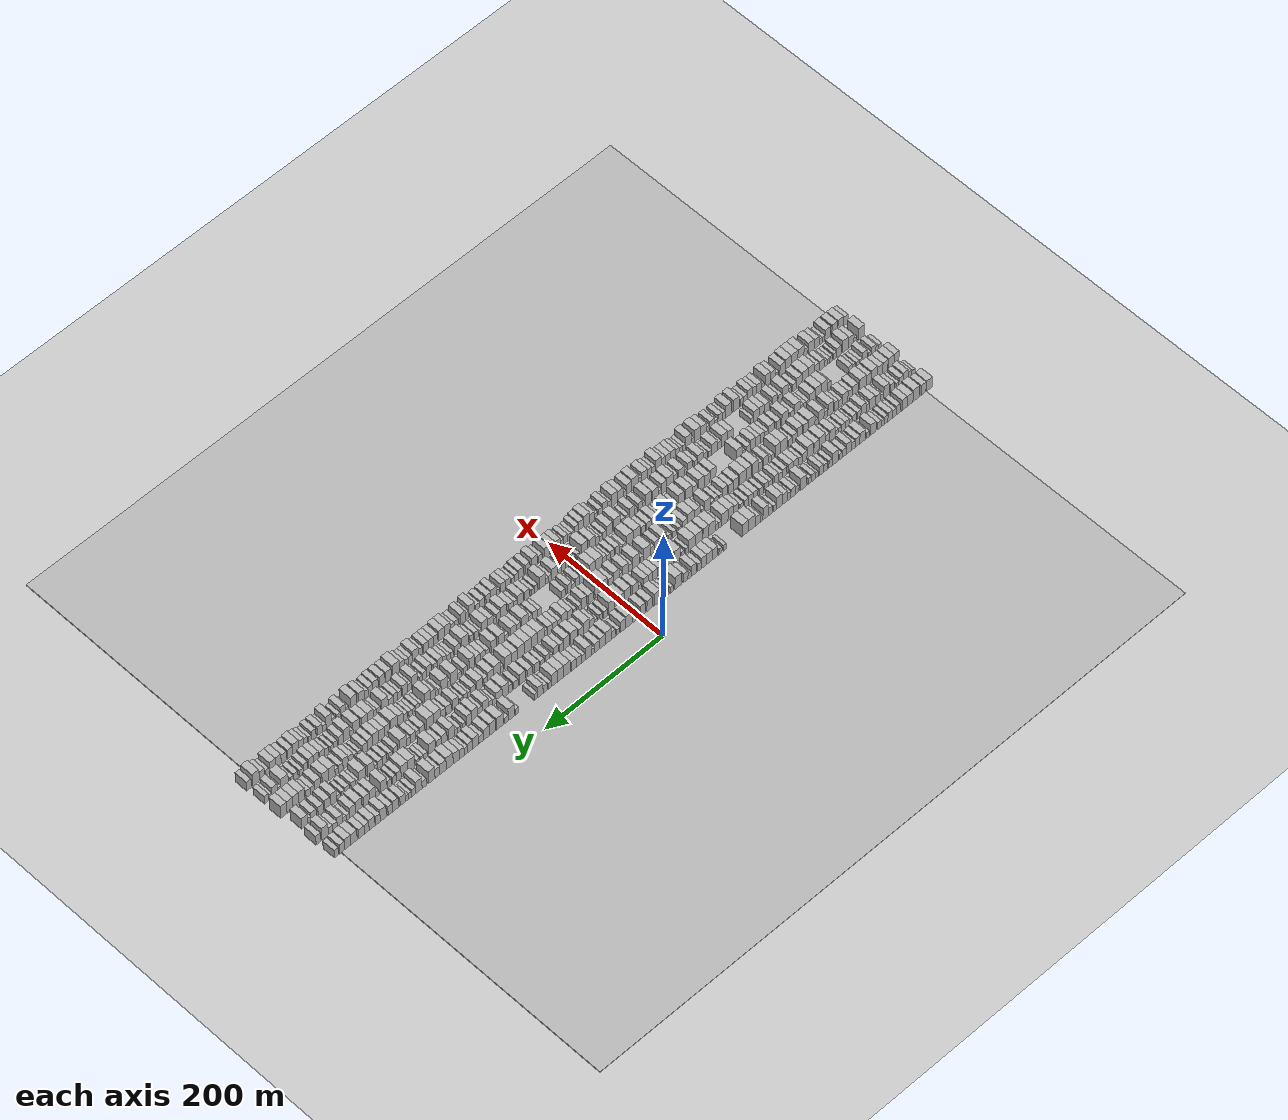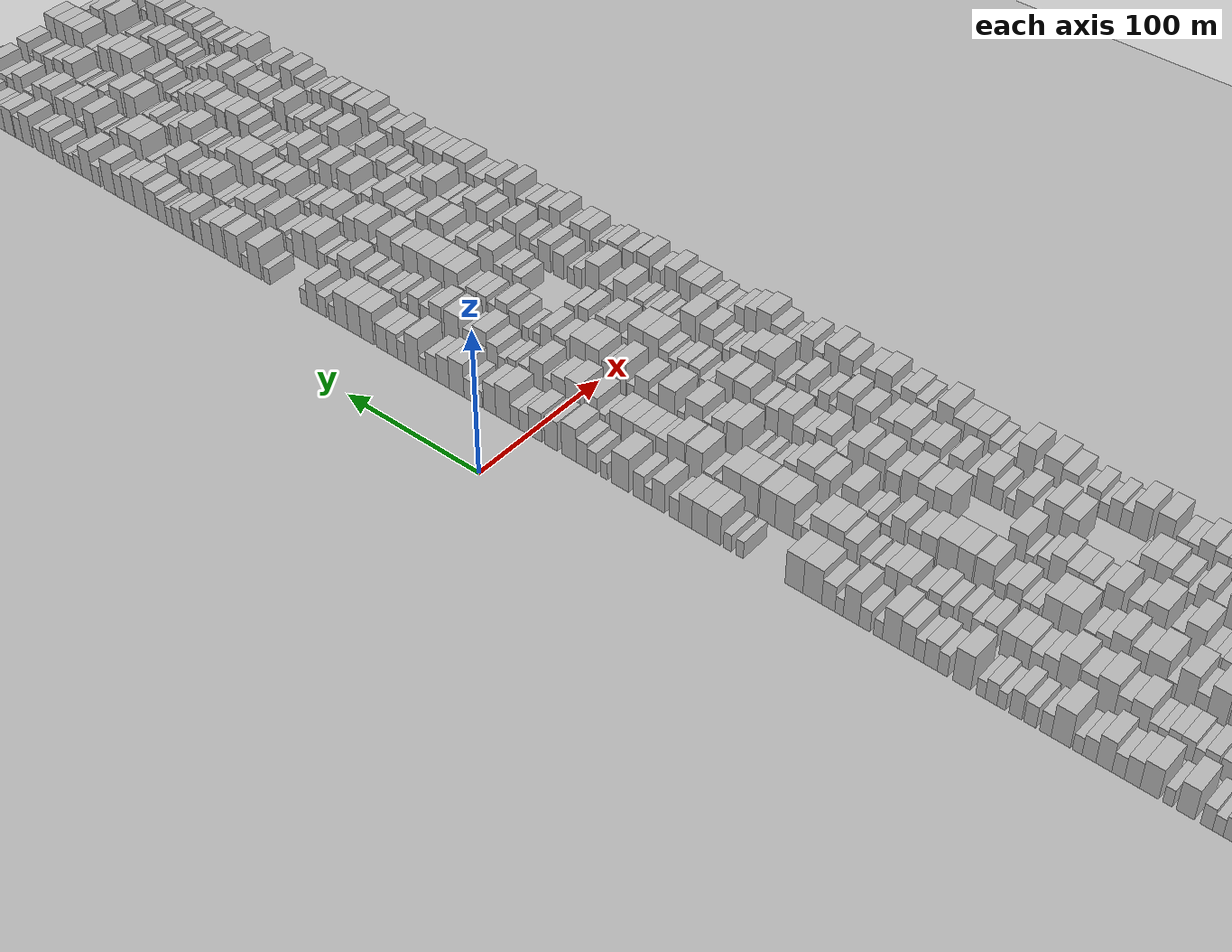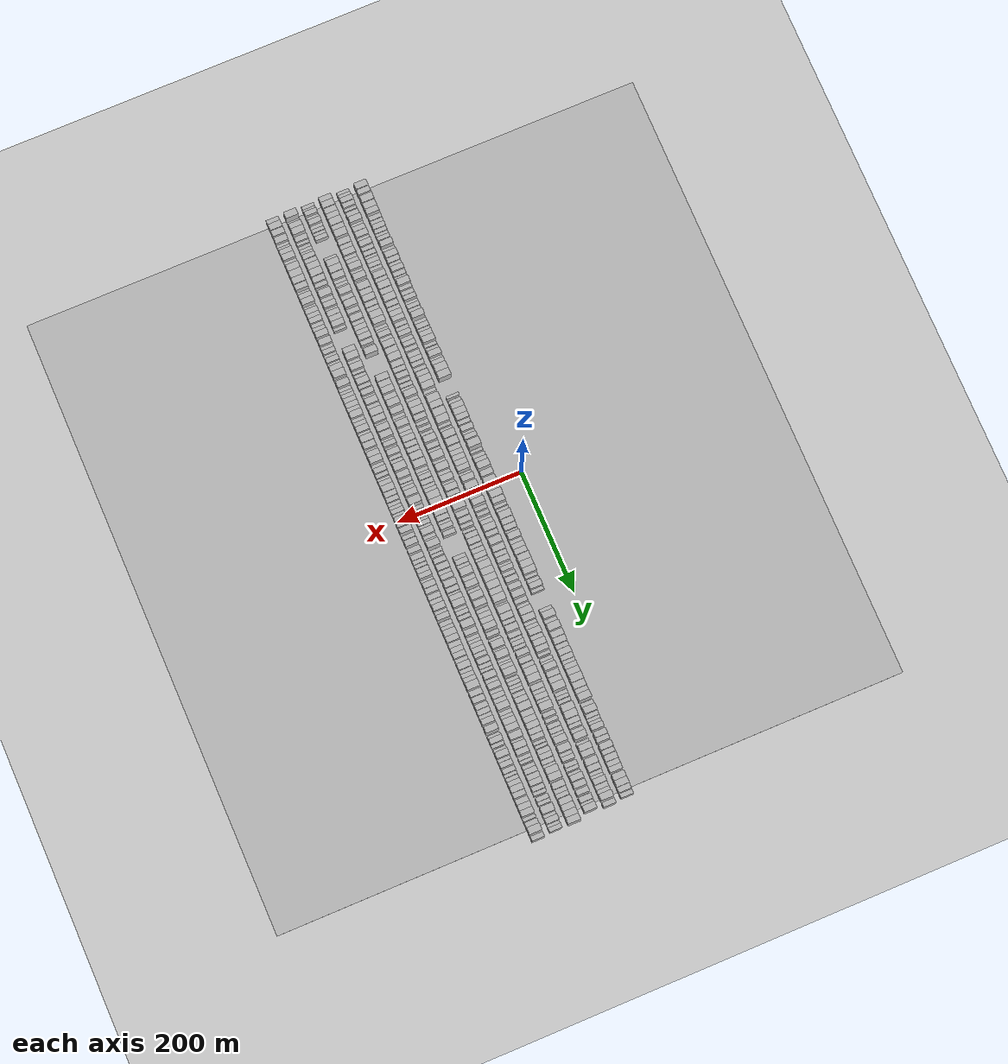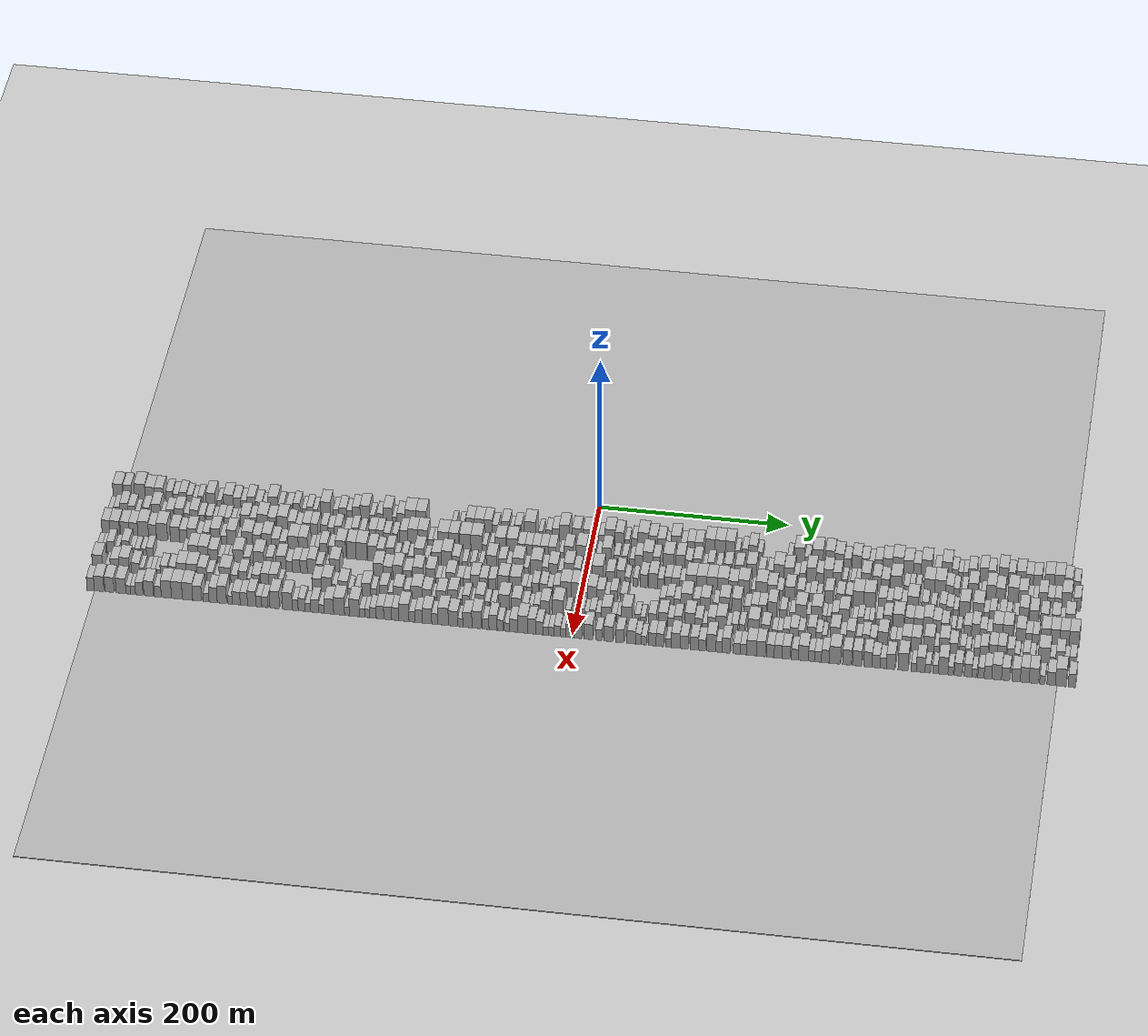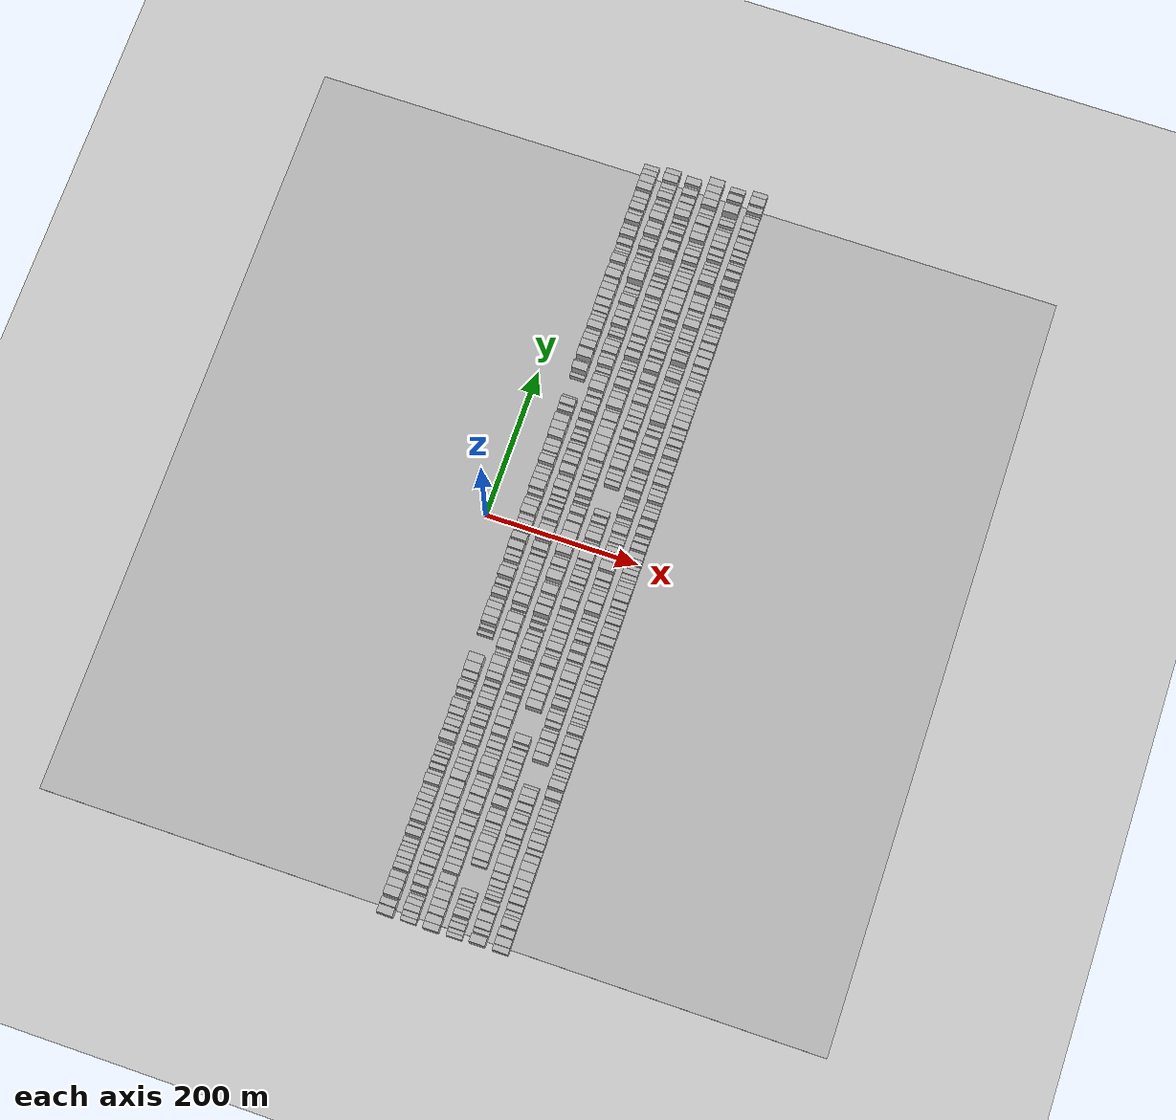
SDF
<?xml version="1.0" encoding="utf-8"?>

<sdf version="1.6">

   <world name="default">

      <gui fullscreen="0">

         <camera name="user_camera">

            <pose>-15 0 4.57585 0 0 0</pose>

            <view_controller>orbit</view_controller>

         </camera>

      </gui>

      <scene>

         <sky>

           <clouds>

             <speed>12</speed>

           </clouds>

         </sky>

         <ambient>0.4 0.4 0.4 1</ambient>

         <background>0.7 0.7 0.7 1</background>

         <shadows>1</shadows>

      </scene>

      <gravity>0 0 -9.8066</gravity>

      <magnetic_field>6e-06 2.3e-05 -4.2e-05</magnetic_field>

      <physics default="0" name="default_physics" type="ode">

         <ode>

            <solver>

               <type>quick</type>

               <iters>10</iters>

               <sor>1.0</sor>

               <use_dynamic_moi_rescaling>0</use_dynamic_moi_rescaling>

            </solver>

            <constraints>

               <cfm>0</cfm>

               <erp>0.2</erp>

               <contact_max_correcting_vel>100</contact_max_correcting_vel>

               <contact_surface_layer>0.001</contact_surface_layer>

            </constraints>

         </ode>

         <max_step_size>0.004</max_step_size>

         <real_time_factor>1</real_time_factor>

         <real_time_update_rate>250</real_time_update_rate>

      </physics>

      <light name="sun" type="directional">

         <cast_shadows>1</cast_shadows>

         <pose>0 0 10 0 0 0</pose>

         <diffuse>0.8 0.8 0.8 1</diffuse>

         <specular>0.2 0.2 0.2 1</specular>

         <attenuation>

            <range>1000</range>

            <constant>0.9</constant>

            <linear>0.01</linear>

            <quadratic>0.001</quadratic>

         </attenuation>

         <direction>-0.5 0.1 -0.9</direction>

      </light>

      <include>

         <name>ground_plane_1</name>

         <uri>model://HANNAS_ground_plane</uri>

         <pose>0 0 0  0 0 0</pose>

      </include>

      <include>

         <name>ground_plane_2</name>

         <uri>model://HANNAS_ground_plane</uri>

         <pose>100 0 0  0 0 0</pose>

      </include>

      <model name="building_1">

         <static>1</static>

         <pose frame="">50.0000 -504.7985 0 0.000000 0.000000 0.000000</pose>

         <link name="link">

            <pose frame="">0 0 10.50 0 0 0</pose>

            <collision name="collision">

               <geometry>

                  <box>

                     <size>20.0000 10.4030 21.0000</size>

                  </box>

               </geometry>

               <max_contacts>10</max_contacts>

               <surface>

                  <contact>

                     <ode/>

                  </contact>

                  <bounce/>

                  <friction>

                     <torsional>

                        <ode/>

                     </torsional>

                     <ode/>

                  </friction>

               </surface>

            </collision>

            <visual name="visual">

               <cast_shadows>0</cast_shadows>

               <geometry>

                  <box>

                     <size>20.0000 10.4030 21.0000</size>

                  </box>

               </geometry>

               <material>

                  <script>

                     <uri>model://HANNAS_wall/materials/scripts</uri>

                     <uri>model://HANNAS_wall/materials/textures</uri>

                     <name>vrc/HANNAS_wall</name>

                  </script>

               </material>

            </visual>

            <self_collide>0</self_collide>

            <enable_wind>0</enable_wind>

            <kinematic>0</kinematic>

         </link>

      </model>

      <model name="building_2">

         <static>1</static>

         <pose frame="">50.0000 -494.3292 0 0.000000 0.000000 0.000000</pose>

         <link name="link">

            <pose frame="">0 0 10.50 0 0 0</pose>

            <collision name="collision">

               <geometry>

                  <box>

                     <size>20.0000 8.5356 21.0000</size>

                  </box>

               </geometry>

               <max_contacts>10</max_contacts>

               <surface>

                  <contact>

                     <ode/>

                  </contact>

                  <bounce/>

                  <friction>

                     <torsional>

                        <ode/>

                     </torsional>

                     <ode/>

                  </friction>

               </surface>

            </collision>

            <visual name="visual">

               <cast_shadows>0</cast_shadows>

               <geometry>

                  <box>

                     <size>20.0000 8.5356 21.0000</size>

                  </box>

               </geometry>

               <material>

                  <script>

                     <uri>model://HANNAS_wall/materials/scripts</uri>

                     <uri>model://HANNAS_wall/materials/textures</uri>

                     <name>vrc/HANNAS_wall</name>

                  </script>

               </material>

            </visual>

            <self_collide>0</self_collide>

            <enable_wind>0</enable_wind>

            <kinematic>0</kinematic>

         </link>

      </model>

      <model name="building_3">

         <static>1</static>

         <pose frame="">50.0000 -481.3072 0 0.000000 0.000000 0.000000</pose>

         <link name="link">

            <pose frame="">0 0 12.00 0 0 0</pose>

            <collision name="collision">

               <geometry>

                  <box>

                     <size>20.0000 11.5084 24.0000</size>

                  </box>

               </geometry>

               <max_contacts>10</max_contacts>

               <surface>

                  <contact>

                     <ode/>

                  </contact>

                  <bounce/>

                  <friction>

                     <torsional>

                        <ode/>

                     </torsional>

                     <ode/>

                  </friction>

               </surface>

            </collision>

            <visual name="visual">

               <cast_shadows>0</cast_shadows>

               <geometry>

                  <box>

                     <size>20.0000 11.5084 24.0000</size>

                  </box>

               </geometry>

               <material>

                  <script>

                     <uri>model://HANNAS_wall/materials/scripts</uri>

                     <uri>model://HANNAS_wall/materials/textures</uri>

                     <name>vrc/HANNAS_wall</name>

                  </script>

               </material>

            </visual>

            <self_collide>0</self_collide>

            <enable_wind>0</enable_wind>

            <kinematic>0</kinematic>

         </link>

      </model>

      <model name="building_4">

         <static>1</static>

         <pose frame="">50.0000 -470.4035 0 0.000000 0.000000 0.000000</pose>

         <link name="link">

            <pose frame="">0 0 10.50 0 0 0</pose>

            <collision name="collision">

               <geometry>

                  <box>

                     <size>20.0000 10.2989 21.0000</size>

                  </box>

               </geometry>

               <max_contacts>10</max_contacts>

               <surface>

                  <contact>

                     <ode/>

                  </contact>

                  <bounce/>

                  <friction>

                     <torsional>

                        <ode/>

                     </torsional>

                     <ode/>

                  </friction>

               </surface>

            </collision>

            <visual name="visual">

               <cast_shadows>0</cast_shadows>

               <geometry>

                  <box>

                     <size>20.0000 10.2989 21.0000</size>

                  </box>

               </geometry>

               <material>

                  <script>

                     <uri>model://HANNAS_wall/materials/scripts</uri>

                     <uri>model://HANNAS_wall/materials/textures</uri>

                     <name>vrc/HANNAS_wall</name>

                  </script>

               </material>

            </visual>

            <self_collide>0</self_collide>

            <enable_wind>0</enable_wind>

            <kinematic>0</kinematic>

         </link>

      </model>

      <model name="building_5">

         <static>1</static>

         <pose frame="">50.0000 -460.6697 0 0.000000 0.000000 0.000000</pose>

         <link name="link">

            <pose frame="">0 0 10.50 0 0 0</pose>

            <collision name="collision">

               <geometry>

                  <box>

                     <size>20.0000 9.1688 21.0000</size>

                  </box>

               </geometry>

               <max_contacts>10</max_contacts>

               <surface>

                  <contact>

                     <ode/>

                  </contact>

                  <bounce/>

                  <friction>

                     <torsional>

                        <ode/>

                     </torsional>

                     <ode/>

                  </friction>

               </surface>

            </collision>

            <visual name="visual">

               <cast_shadows>0</cast_shadows>

               <geometry>

                  <box>

                     <size>20.0000 9.1688 21.0000</size>

                  </box>

               </geometry>

               <material>

                  <script>

                     <uri>model://HANNAS_wall/materials/scripts</uri>

                     <uri>model://HANNAS_wall/materials/textures</uri>

                     <name>vrc/HANNAS_wall</name>

                  </script>

               </material>

            </visual>

            <self_collide>0</self_collide>

            <enable_wind>0</enable_wind>

            <kinematic>0</kinematic>

         </link>

      </model>

      <model name="building_6">

         <static>1</static>

         <pose frame="">50.0000 -449.4327 0 0.000000 0.000000 0.000000</pose>

         <link name="link">

            <pose frame="">0 0 9.00 0 0 0</pose>

            <collision name="collision">

               <geometry>

                  <box>

                     <size>20.0000 7.3051 18.0000</size>

                  </box>

               </geometry>

               <max_contacts>10</max_contacts>

               <surface>

                  <contact>

                     <ode/>

                  </contact>

                  <bounce/>

                  <friction>

                     <torsional>

                        <ode/>

                     </torsional>

                     <ode/>

                  </friction>

               </surface>

            </collision>

            <visual name="visual">

               <cast_shadows>0</cast_shadows>

               <geometry>

                  <box>

                     <size>20.0000 7.3051 18.0000</size>

                  </box>

               </geometry>

               <material>

                  <script>

                     <uri>model://HANNAS_wall/materials/scripts</uri>

                     <uri>model://HANNAS_wall/materials/textures</uri>

                     <name>vrc/HANNAS_wall</name>

                  </script>

               </material>

            </visual>

            <self_collide>0</self_collide>

            <enable_wind>0</enable_wind>

            <kinematic>0</kinematic>

         </link>

      </model>

      <model name="building_7">

         <static>1</static>

         <pose frame="">50.0000 -442.3728 0 0.000000 0.000000 0.000000</pose>

         <link name="link">

            <pose frame="">0 0 7.50 0 0 0</pose>

            <collision name="collision">

               <geometry>

                  <box>

                     <size>20.0000 6.8146 15.0000</size>

                  </box>

               </geometry>

               <max_contacts>10</max_contacts>

               <surface>

                  <contact>

                     <ode/>

                  </contact>

                  <bounce/>

                  <friction>

                     <torsional>

                        <ode/>

                     </torsional>

                     <ode/>

                  </friction>

               </surface>

            </collision>

            <visual name="visual">

               <cast_shadows>0</cast_shadows>

               <geometry>

                  <box>

                     <size>20.0000 6.8146 15.0000</size>

                  </box>

               </geometry>

               <material>

                  <script>

                     <uri>model://HANNAS_wall/materials/scripts</uri>

                     <uri>model://HANNAS_wall/materials/textures</uri>

                     <name>vrc/HANNAS_wall</name>

                  </script>

               </material>

            </visual>

            <self_collide>0</self_collide>

            <enable_wind>0</enable_wind>

            <kinematic>0</kinematic>

         </link>

      </model>

      <model name="building_8">

         <static>1</static>

         <pose frame="">50.0000 -434.9805 0 0.000000 0.000000 0.000000</pose>

         <link name="link">

            <pose frame="">0 0 9.00 0 0 0</pose>

            <collision name="collision">

               <geometry>

                  <box>

                     <size>20.0000 7.9700 18.0000</size>

                  </box>

               </geometry>

               <max_contacts>10</max_contacts>

               <surface>

                  <contact>

                     <ode/>

                  </contact>

                  <bounce/>

                  <friction>

                     <torsional>

                        <ode/>

                     </torsional>

                     <ode/>

                  </friction>

               </surface>

            </collision>

            <visual name="visual">

               <cast_shadows>0</cast_shadows>

               <geometry>

                  <box>

                     <size>20.0000 7.9700 18.0000</size>

                  </box>

               </geometry>

               <material>

                  <script>

                     <uri>model://HANNAS_wall/materials/scripts</uri>

                     <uri>model://HANNAS_wall/materials/textures</uri>

                     <name>vrc/HANNAS_wall</name>

                  </script>

               </material>

            </visual>

            <self_collide>0</self_collide>

            <enable_wind>0</enable_wind>

            <kinematic>0</kinematic>

         </link>

      </model>

      <model name="building_9">

         <static>1</static>

         <pose frame="">50.0000 -427.7849 0 0.000000 0.000000 0.000000</pose>

         <link name="link">

            <pose frame="">0 0 7.50 0 0 0</pose>

            <collision name="collision">

               <geometry>

                  <box>

                     <size>20.0000 6.4212 15.0000</size>

                  </box>

               </geometry>

               <max_contacts>10</max_contacts>

               <surface>

                  <contact>

                     <ode/>

                  </contact>

                  <bounce/>

                  <friction>

                     <torsional>

                        <ode/>

                     </torsional>

                     <ode/>

                  </friction>

               </surface>

            </collision>

            <visual name="visual">

               <cast_shadows>0</cast_shadows>

               <geometry>

                  <box>

                     <size>20.0000 6.4212 15.0000</size>

                  </box>

               </geometry>

               <material>

                  <script>

                     <uri>model://HANNAS_wall/materials/scripts</uri>

                     <uri>model://HANNAS_wall/materials/textures</uri>

                     <name>vrc/HANNAS_wall</name>

                  </script>

               </material>

            </visual>

            <self_collide>0</self_collide>

            <enable_wind>0</enable_wind>

            <kinematic>0</kinematic>

         </link>

      </model>

      <model name="building_10">

         <static>1</static>

         <pose frame="">50.0000 -421.8441 0 0.000000 0.000000 0.000000</pose>

         <link name="link">

            <pose frame="">0 0 6.00 0 0 0</pose>

            <collision name="collision">

               <geometry>

                  <box>

                     <size>20.0000 5.4605 12.0000</size>

                  </box>

               </geometry>

               <max_contacts>10</max_contacts>

               <surface>

                  <contact>

                     <ode/>

                  </contact>

                  <bounce/>

                  <friction>

                     <torsional>

                        <ode/>

                     </torsional>

                     <ode/>

                  </friction>

               </surface>

            </collision>

            <visual name="visual">

               <cast_shadows>0</cast_shadows>

               <geometry>

                  <box>

                     <size>20.0000 5.4605 12.0000</size>

                  </box>

               </geometry>

               <material>

                  <script>

                     <uri>model://HANNAS_wall/materials/scripts</uri>

                     <uri>model://HANNAS_wall/materials/textures</uri>

                     <name>vrc/HANNAS_wall</name>

                  </script>

               </material>

            </visual>

            <self_collide>0</self_collide>

            <enable_wind>0</enable_wind>

            <kinematic>0</kinematic>

         </link>

      </model>

      <model name="building_11">

         <static>1</static>

         <pose frame="">50.0000 -416.0317 0 0.000000 0.000000 0.000000</pose>

         <link name="link">

            <pose frame="">0 0 7.50 0 0 0</pose>

            <collision name="collision">

               <geometry>

                  <box>

                     <size>20.0000 6.1642 15.0000</size>

                  </box>

               </geometry>

               <max_contacts>10</max_contacts>

               <surface>

                  <contact>

                     <ode/>

                  </contact>

                  <bounce/>

                  <friction>

                     <torsional>

                        <ode/>

                     </torsional>

                     <ode/>

                  </friction>

               </surface>

            </collision>

            <visual name="visual">

               <cast_shadows>0</cast_shadows>

               <geometry>

                  <box>

                     <size>20.0000 6.1642 15.0000</size>

                  </box>

               </geometry>

               <material>

                  <script>

                     <uri>model://HANNAS_wall/materials/scripts</uri>

                     <uri>model://HANNAS_wall/materials/textures</uri>

                     <name>vrc/HANNAS_wall</name>

                  </script>

               </material>

            </visual>

            <self_collide>0</self_collide>

            <enable_wind>0</enable_wind>

            <kinematic>0</kinematic>

         </link>

      </model>

      <model name="building_12">

         <static>1</static>

         <pose frame="">50.0000 -405.2079 0 0.000000 0.000000 0.000000</pose>

         <link name="link">

            <pose frame="">0 0 10.50 0 0 0</pose>

            <collision name="collision">

               <geometry>

                  <box>

                     <size>20.0000 9.4835 21.0000</size>

                  </box>

               </geometry>

               <max_contacts>10</max_contacts>

               <surface>

                  <contact>

                     <ode/>

                  </contact>

                  <bounce/>

                  <friction>

                     <torsional>

                        <ode/>

                     </torsional>

                     <ode/>

                  </friction>

               </surface>

            </collision>

            <visual name="visual">

               <cast_shadows>0</cast_shadows>

               <geometry>

                  <box>

                     <size>20.0000 9.4835 21.0000</size>

                  </box>

               </geometry>

               <material>

                  <script>

                     <uri>model://HANNAS_wall/materials/scripts</uri>

                     <uri>model://HANNAS_wall/materials/textures</uri>

                     <name>vrc/HANNAS_wall</name>

                  </script>

               </material>

            </visual>

            <self_collide>0</self_collide>

            <enable_wind>0</enable_wind>

            <kinematic>0</kinematic>

         </link>

      </model>

      <model name="building_13">

         <static>1</static>

         <pose frame="">50.0000 -395.9396 0 0.000000 0.000000 0.000000</pose>

         <link name="link">

            <pose frame="">0 0 6.00 0 0 0</pose>

            <collision name="collision">

               <geometry>

                  <box>

                     <size>20.0000 5.0531 12.0000</size>

                  </box>

               </geometry>

               <max_contacts>10</max_contacts>

               <surface>

                  <contact>

                     <ode/>

                  </contact>

                  <bounce/>

                  <friction>

                     <torsional>

                        <ode/>

                     </torsional>

                     <ode/>

                  </friction>

               </surface>

            </collision>

            <visual name="visual">

               <cast_shadows>0</cast_shadows>

               <geometry>

                  <box>

                     <size>20.0000 5.0531 12.0000</size>

                  </box>

               </geometry>

               <material>

                  <script>

                     <uri>model://HANNAS_wall/materials/scripts</uri>

                     <uri>model://HANNAS_wall/materials/textures</uri>

                     <name>vrc/HANNAS_wall</name>

                  </script>

               </material>

            </visual>

            <self_collide>0</self_collide>

            <enable_wind>0</enable_wind>

            <kinematic>0</kinematic>

         </link>

      </model>

      <model name="building_14">

         <static>1</static>

         <pose frame="">50.0000 -386.3565 0 0.000000 0.000000 0.000000</pose>

         <link name="link">

            <pose frame="">0 0 10.50 0 0 0</pose>

            <collision name="collision">

               <geometry>

                  <box>

                     <size>20.0000 10.1129 21.0000</size>

                  </box>

               </geometry>

               <max_contacts>10</max_contacts>

               <surface>

                  <contact>

                     <ode/>

                  </contact>

                  <bounce/>

                  <friction>

                     <torsional>

                        <ode/>

                     </torsional>

                     <ode/>

                  </friction>

               </surface>

            </collision>

            <visual name="visual">

               <cast_shadows>0</cast_shadows>

               <geometry>

                  <box>

                     <size>20.0000 10.1129 21.0000</size>

                  </box>

               </geometry>

               <material>

                  <script>

                     <uri>model://HANNAS_wall/materials/scripts</uri>

                     <uri>model://HANNAS_wall/materials/textures</uri>

                     <name>vrc/HANNAS_wall</name>

                  </script>

               </material>

            </visual>

            <self_collide>0</self_collide>

            <enable_wind>0</enable_wind>

            <kinematic>0</kinematic>

         </link>

      </model>

      <model name="building_15">

         <static>1</static>

         <pose frame="">50.0000 -377.1664 0 0.000000 0.000000 0.000000</pose>

         <link name="link">

            <pose frame="">0 0 9.00 0 0 0</pose>

            <collision name="collision">

               <geometry>

                  <box>

                     <size>20.0000 8.2674 18.0000</size>

                  </box>

               </geometry>

               <max_contacts>10</max_contacts>

               <surface>

                  <contact>

                     <ode/>

                  </contact>

                  <bounce/>

                  <friction>

                     <torsional>

                        <ode/>

                     </torsional>

                     <ode/>

                  </friction>

               </surface>

            </collision>

            <visual name="visual">

               <cast_shadows>0</cast_shadows>

               <geometry>

                  <box>

                     <size>20.0000 8.2674 18.0000</size>

                  </box>

               </geometry>

               <material>

                  <script>

                     <uri>model://HANNAS_wall/materials/scripts</uri>

                     <uri>model://HANNAS_wall/materials/textures</uri>

                     <name>vrc/HANNAS_wall</name>

                  </script>

               </material>

            </visual>

            <self_collide>0</self_collide>

            <enable_wind>0</enable_wind>

            <kinematic>0</kinematic>

         </link>

      </model>

      <model name="building_16">

         <static>1</static>

         <pose frame="">50.0000 -369.7042 0 0.000000 0.000000 0.000000</pose>

         <link name="link">

            <pose frame="">0 0 7.50 0 0 0</pose>

            <collision name="collision">

               <geometry>

                  <box>

                     <size>20.0000 6.6570 15.0000</size>

                  </box>

               </geometry>

               <max_contacts>10</max_contacts>

               <surface>

                  <contact>

                     <ode/>

                  </contact>

                  <bounce/>

                  <friction>

                     <torsional>

                        <ode/>

                     </torsional>

                     <ode/>

                  </friction>

               </surface>

            </collision>

            <visual name="visual">

               <cast_shadows>0</cast_shadows>

               <geometry>

                  <box>

                     <size>20.0000 6.6570 15.0000</size>

                  </box>

               </geometry>

               <material>

                  <script>

                     <uri>model://HANNAS_wall/materials/scripts</uri>

                     <uri>model://HANNAS_wall/materials/textures</uri>

                     <name>vrc/HANNAS_wall</name>

                  </script>

               </material>

            </visual>

            <self_collide>0</self_collide>

            <enable_wind>0</enable_wind>

            <kinematic>0</kinematic>

         </link>

      </model>

      <model name="building_17">

         <static>1</static>

         <pose frame="">50.0000 -362.0689 0 0.000000 0.000000 0.000000</pose>

         <link name="link">

            <pose frame="">0 0 10.50 0 0 0</pose>

            <collision name="collision">

               <geometry>

                  <box>

                     <size>20.0000 8.6137 21.0000</size>

                  </box>

               </geometry>

               <max_contacts>10</max_contacts>

               <surface>

                  <contact>

                     <ode/>

                  </contact>

                  <bounce/>

                  <friction>

                     <torsional>

                        <ode/>

                     </torsional>

                     <ode/>

                  </friction>

               </surface>

            </collision>

            <visual name="visual">

               <cast_shadows>0</cast_shadows>

               <geometry>

                  <box>

                     <size>20.0000 8.6137 21.0000</size>

                  </box>

               </geometry>

               <material>

                  <script>

                     <uri>model://HANNAS_wall/materials/scripts</uri>

                     <uri>model://HANNAS_wall/materials/textures</uri>

                     <name>vrc/HANNAS_wall</name>

                  </script>

               </material>

            </visual>

            <self_collide>0</self_collide>

            <enable_wind>0</enable_wind>

            <kinematic>0</kinematic>

         </link>

      </model>

      <model name="building_18">

         <static>1</static>

         <pose frame="">50.0000 -354.0281 0 0.000000 0.000000 0.000000</pose>

         <link name="link">

            <pose frame="">0 0 7.50 0 0 0</pose>

            <collision name="collision">

               <geometry>

                  <box>

                     <size>20.0000 7.4679 15.0000</size>

                  </box>

               </geometry>

               <max_contacts>10</max_contacts>

               <surface>

                  <contact>

                     <ode/>

                  </contact>

                  <bounce/>

                  <friction>

                     <torsional>

                        <ode/>

                     </torsional>

                     <ode/>

                  </friction>

               </surface>

            </collision>

            <visual name="visual">

               <cast_shadows>0</cast_shadows>

               <geometry>

                  <box>

                     <size>20.0000 7.4679 15.0000</size>

                  </box>

               </geometry>

               <material>

                  <script>

                     <uri>model://HANNAS_wall/materials/scripts</uri>

                     <uri>model://HANNAS_wall/materials/textures</uri>

                     <name>vrc/HANNAS_wall</name>

                  </script>

               </material>

            </visual>

            <self_collide>0</self_collide>

            <enable_wind>0</enable_wind>

            <kinematic>0</kinematic>

         </link>

      </model>

      <model name="building_19">

         <static>1</static>

         <pose frame="">50.0000 -347.6335 0 0.000000 0.000000 0.000000</pose>

         <link name="link">

            <pose frame="">0 0 6.00 0 0 0</pose>

            <collision name="collision">

               <geometry>

                  <box>

                     <size>20.0000 5.3213 12.0000</size>

                  </box>

               </geometry>

               <max_contacts>10</max_contacts>

               <surface>

                  <contact>

                     <ode/>

                  </contact>

                  <bounce/>

                  <friction>

                     <torsional>

                        <ode/>

                     </torsional>

                     <ode/>

                  </friction>

               </surface>

            </collision>

            <visual name="visual">

               <cast_shadows>0</cast_shadows>

               <geometry>

                  <box>

                     <size>20.0000 5.3213 12.0000</size>

                  </box>

               </geometry>

               <material>

                  <script>

                     <uri>model://HANNAS_wall/materials/scripts</uri>

                     <uri>model://HANNAS_wall/materials/textures</uri>

                     <name>vrc/HANNAS_wall</name>

                  </script>

               </material>

            </visual>

            <self_collide>0</self_collide>

            <enable_wind>0</enable_wind>

            <kinematic>0</kinematic>

         </link>

      </model>

      <model name="building_20">

         <static>1</static>

         <pose frame="">50.0000 -338.5995 0 0.000000 0.000000 0.000000</pose>

         <link name="link">

            <pose frame="">0 0 12.00 0 0 0</pose>

            <collision name="collision">

               <geometry>

                  <box>

                     <size>20.0000 10.7469 24.0000</size>

                  </box>

               </geometry>

               <max_contacts>10</max_contacts>

               <surface>

                  <contact>

                     <ode/>

                  </contact>

                  <bounce/>

                  <friction>

                     <torsional>

                        <ode/>

                     </torsional>

                     <ode/>

                  </friction>

               </surface>

            </collision>

            <visual name="visual">

               <cast_shadows>0</cast_shadows>

               <geometry>

                  <box>

                     <size>20.0000 10.7469 24.0000</size>

                  </box>

               </geometry>

               <material>

                  <script>

                     <uri>model://HANNAS_wall/materials/scripts</uri>

                     <uri>model://HANNAS_wall/materials/textures</uri>

                     <name>vrc/HANNAS_wall</name>

                  </script>

               </material>

            </visual>

            <self_collide>0</self_collide>

            <enable_wind>0</enable_wind>

            <kinematic>0</kinematic>

         </link>

      </model>

      <model name="building_21">

         <static>1</static>

         <pose frame="">50.0000 -330.0534 0 0.000000 0.000000 0.000000</pose>

         <link name="link">

            <pose frame="">0 0 7.50 0 0 0</pose>

            <collision name="collision">

               <geometry>

                  <box>

                     <size>20.0000 6.3453 15.0000</size>

                  </box>

               </geometry>

               <max_contacts>10</max_contacts>

               <surface>

                  <contact>

                     <ode/>

                  </contact>

                  <bounce/>

                  <friction>

                     <torsional>

                        <ode/>

                     </torsional>

                     <ode/>

                  </friction>

               </surface>

            </collision>

            <visual name="visual">

               <cast_shadows>0</cast_shadows>

               <geometry>

                  <box>

                     <size>20.0000 6.3453 15.0000</size>

                  </box>

               </geometry>

               <material>

                  <script>

                     <uri>model://HANNAS_wall/materials/scripts</uri>

                     <uri>model://HANNAS_wall/materials/textures</uri>

                     <name>vrc/HANNAS_wall</name>

                  </script>

               </material>

            </visual>

            <self_collide>0</self_collide>

            <enable_wind>0</enable_wind>

            <kinematic>0</kinematic>

         </link>

      </model>

      <model name="building_22">

         <static>1</static>

         <pose frame="">50.0000 -321.4453 0 0.000000 0.000000 0.000000</pose>

         <link name="link">

            <pose frame="">0 0 7.50 0 0 0</pose>

            <collision name="collision">

               <geometry>

                  <box>

                     <size>20.0000 6.8707 15.0000</size>

                  </box>

               </geometry>

               <max_contacts>10</max_contacts>

               <surface>

                  <contact>

                     <ode/>

                  </contact>

                  <bounce/>

                  <friction>

                     <torsional>

                        <ode/>

                     </torsional>

                     <ode/>

                  </friction>

               </surface>

            </collision>

            <visual name="visual">

               <cast_shadows>0</cast_shadows>

               <geometry>

                  <box>

                     <size>20.0000 6.8707 15.0000</size>

                  </box>

               </geometry>

               <material>

                  <script>

                     <uri>model://HANNAS_wall/materials/scripts</uri>

                     <uri>model://HANNAS_wall/materials/textures</uri>

                     <name>vrc/HANNAS_wall</name>

                  </script>

               </material>

            </visual>

            <self_collide>0</self_collide>

            <enable_wind>0</enable_wind>

            <kinematic>0</kinematic>

         </link>

      </model>

      <model name="building_23">

         <static>1</static>

         <pose frame="">50.0000 -313.3671 0 0.000000 0.000000 0.000000</pose>

         <link name="link">

            <pose frame="">0 0 9.00 0 0 0</pose>

            <collision name="collision">

               <geometry>

                  <box>

                     <size>20.0000 7.2858 18.0000</size>

                  </box>

               </geometry>

               <max_contacts>10</max_contacts>

               <surface>

                  <contact>

                     <ode/>

                  </contact>

                  <bounce/>

                  <friction>

                     <torsional>

                        <ode/>

                     </torsional>

                     <ode/>

                  </friction>

               </surface>

            </collision>

            <visual name="visual">

               <cast_shadows>0</cast_shadows>

               <geometry>

                  <box>

                     <size>20.0000 7.2858 18.0000</size>

                  </box>

               </geometry>

               <material>

                  <script>

                     <uri>model://HANNAS_wall/materials/scripts</uri>

                     <uri>model://HANNAS_wall/materials/textures</uri>

                     <name>vrc/HANNAS_wall</name>

                  </script>

               </material>

            </visual>

            <self_collide>0</self_collide>

            <enable_wind>0</enable_wind>

            <kinematic>0</kinematic>

         </link>

      </model>

      <model name="building_24">

         <static>1</static>

         <pose frame="">50.0000 -305.2619 0 0.000000 0.000000 0.000000</pose>

         <link name="link">

            <pose frame="">0 0 6.00 0 0 0</pose>

            <collision name="collision">

               <geometry>

                  <box>

                     <size>20.0000 4.9245 12.0000</size>

                  </box>

               </geometry>

               <max_contacts>10</max_contacts>

               <surface>

                  <contact>

                     <ode/>

                  </contact>

                  <bounce/>

                  <friction>

                     <torsional>

                        <ode/>

                     </torsional>

                     <ode/>

                  </friction>

               </surface>

            </collision>

            <visual name="visual">

               <cast_shadows>0</cast_shadows>

               <geometry>

                  <box>

                     <size>20.0000 4.9245 12.0000</size>

                  </box>

               </geometry>

               <material>

                  <script>

                     <uri>model://HANNAS_wall/materials/scripts</uri>

                     <uri>model://HANNAS_wall/materials/textures</uri>

                     <name>vrc/HANNAS_wall</name>

                  </script>

               </material>

            </visual>

            <self_collide>0</self_collide>

            <enable_wind>0</enable_wind>

            <kinematic>0</kinematic>

         </link>

      </model>

      <model name="building_25">

         <static>1</static>

         <pose frame="">50.0000 -299.4047 0 0.000000 0.000000 0.000000</pose>

         <link name="link">

            <pose frame="">0 0 7.50 0 0 0</pose>

            <collision name="collision">

               <geometry>

                  <box>

                     <size>20.0000 6.7900 15.0000</size>

                  </box>

               </geometry>

               <max_contacts>10</max_contacts>

               <surface>

                  <contact>

                     <ode/>

                  </contact>

                  <bounce/>

                  <friction>

                     <torsional>

                        <ode/>

                     </torsional>

                     <ode/>

                  </friction>

               </surface>

            </collision>

            <visual name="visual">

               <cast_shadows>0</cast_shadows>

               <geometry>

                  <box>

                     <size>20.0000 6.7900 15.0000</size>

                  </box>

               </geometry>

               <material>

                  <script>

                     <uri>model://HANNAS_wall/materials/scripts</uri>

                     <uri>model://HANNAS_wall/materials/textures</uri>

                     <name>vrc/HANNAS_wall</name>

                  </script>

               </material>

            </visual>

            <self_collide>0</self_collide>

            <enable_wind>0</enable_wind>

            <kinematic>0</kinematic>

         </link>

      </model>

      <model name="building_26">

         <static>1</static>

         <pose frame="">50.0000 -293.4387 0 0.000000 0.000000 0.000000</pose>

         <link name="link">

            <pose frame="">0 0 6.00 0 0 0</pose>

            <collision name="collision">

               <geometry>

                  <box>

                     <size>20.0000 5.1421 12.0000</size>

                  </box>

               </geometry>

               <max_contacts>10</max_contacts>

               <surface>

                  <contact>

                     <ode/>

                  </contact>

                  <bounce/>

                  <friction>

                     <torsional>

                        <ode/>

                     </torsional>

                     <ode/>

                  </friction>

               </surface>

            </collision>

            <visual name="visual">

               <cast_shadows>0</cast_shadows>

               <geometry>

                  <box>

                     <size>20.0000 5.1421 12.0000</size>

                  </box>

               </geometry>

               <material>

                  <script>

                     <uri>model://HANNAS_wall/materials/scripts</uri>

                     <uri>model://HANNAS_wall/materials/textures</uri>

                     <name>vrc/HANNAS_wall</name>

                  </script>

               </material>

            </visual>

            <self_collide>0</self_collide>

            <enable_wind>0</enable_wind>

            <kinematic>0</kinematic>

         </link>

      </model>

      <model name="building_27">

         <static>1</static>

         <pose frame="">50.0000 -282.6276 0 0.000000 0.000000 0.000000</pose>

         <link name="link">

            <pose frame="">0 0 12.00 0 0 0</pose>

            <collision name="collision">

               <geometry>

                  <box>

                     <size>20.0000 10.4801 24.0000</size>

                  </box>

               </geometry>

               <max_contacts>10</max_contacts>

               <surface>

                  <contact>

                     <ode/>

                  </contact>

                  <bounce/>

                  <friction>

                     <torsional>

                        <ode/>

                     </torsional>

                     <ode/>

                  </friction>

               </surface>

            </collision>

            <visual name="visual">

               <cast_shadows>0</cast_shadows>

               <geometry>

                  <box>

                     <size>20.0000 10.4801 24.0000</size>

                  </box>

               </geometry>

               <material>

                  <script>

                     <uri>model://HANNAS_wall/materials/scripts</uri>

                     <uri>model://HANNAS_wall/materials/textures</uri>

                     <name>vrc/HANNAS_wall</name>

                  </script>

               </material>

            </visual>

            <self_collide>0</self_collide>

            <enable_wind>0</enable_wind>

            <kinematic>0</kinematic>

         </link>

      </model>

      <model name="building_28">

         <static>1</static>

         <pose frame="">50.0000 -271.3541 0 0.000000 0.000000 0.000000</pose>

         <link name="link">

            <pose frame="">0 0 7.50 0 0 0</pose>

            <collision name="collision">

               <geometry>

                  <box>

                     <size>20.0000 6.0669 15.0000</size>

                  </box>

               </geometry>

               <max_contacts>10</max_contacts>

               <surface>

                  <contact>

                     <ode/>

                  </contact>

                  <bounce/>

                  <friction>

                     <torsional>

                        <ode/>

                     </torsional>

                     <ode/>

                  </friction>

               </surface>

            </collision>

            <visual name="visual">

               <cast_shadows>0</cast_shadows>

               <geometry>

                  <box>

                     <size>20.0000 6.0669 15.0000</size>

                  </box>

               </geometry>

               <material>

                  <script>

                     <uri>model://HANNAS_wall/materials/scripts</uri>

                     <uri>model://HANNAS_wall/materials/textures</uri>

                     <name>vrc/HANNAS_wall</name>

                  </script>

               </material>

            </visual>

            <self_collide>0</self_collide>

            <enable_wind>0</enable_wind>

            <kinematic>0</kinematic>

         </link>

      </model>

      <model name="building_29">

         <static>1</static>

         <pose frame="">50.0000 -264.2918 0 0.000000 0.000000 0.000000</pose>

         <link name="link">

            <pose frame="">0 0 9.00 0 0 0</pose>

            <collision name="collision">

               <geometry>

                  <box>

                     <size>20.0000 8.0576 18.0000</size>

                  </box>

               </geometry>

               <max_contacts>10</max_contacts>

               <surface>

                  <contact>

                     <ode/>

                  </contact>

                  <bounce/>

                  <friction>

                     <torsional>

                        <ode/>

                     </torsional>

                     <ode/>

                  </friction>

               </surface>

            </collision>

            <visual name="visual">

               <cast_shadows>0</cast_shadows>

               <geometry>

                  <box>

                     <size>20.0000 8.0576 18.0000</size>

                  </box>

               </geometry>

               <material>

                  <script>

                     <uri>model://HANNAS_wall/materials/scripts</uri>

                     <uri>model://HANNAS_wall/materials/textures</uri>

                     <name>vrc/HANNAS_wall</name>

                  </script>

               </material>

            </visual>

            <self_collide>0</self_collide>

            <enable_wind>0</enable_wind>

            <kinematic>0</kinematic>

         </link>

      </model>

      <model name="building_30">

         <static>1</static>

         <pose frame="">50.0000 -257.2334 0 0.000000 0.000000 0.000000</pose>

         <link name="link">

            <pose frame="">0 0 7.50 0 0 0</pose>

            <collision name="collision">

               <geometry>

                  <box>

                     <size>20.0000 6.0591 15.0000</size>

                  </box>

               </geometry>

               <max_contacts>10</max_contacts>

               <surface>

                  <contact>

                     <ode/>

                  </contact>

                  <bounce/>

                  <friction>

                     <torsional>

                        <ode/>

                     </torsional>

                     <ode/>

                  </friction>

               </surface>

            </collision>

            <visual name="visual">

               <cast_shadows>0</cast_shadows>

               <geometry>

                  <box>

                     <size>20.0000 6.0591 15.0000</size>

                  </box>

               </geometry>

               <material>

                  <script>

                     <uri>model://HANNAS_wall/materials/scripts</uri>

                     <uri>model://HANNAS_wall/materials/textures</uri>

                     <name>vrc/HANNAS_wall</name>

                  </script>

               </material>

            </visual>

            <self_collide>0</self_collide>

            <enable_wind>0</enable_wind>

            <kinematic>0</kinematic>

         </link>

      </model>

      <model name="building_31">

         <static>1</static>

         <pose frame="">50.0000 -249.9529 0 0.000000 0.000000 0.000000</pose>

         <link name="link">

            <pose frame="">0 0 10.50 0 0 0</pose>

            <collision name="collision">

               <geometry>

                  <box>

                     <size>20.0000 8.5019 21.0000</size>

                  </box>

               </geometry>

               <max_contacts>10</max_contacts>

               <surface>

                  <contact>

                     <ode/>

                  </contact>

                  <bounce/>

                  <friction>

                     <torsional>

                        <ode/>

                     </torsional>

                     <ode/>

                  </friction>

               </surface>

            </collision>

            <visual name="visual">

               <cast_shadows>0</cast_shadows>

               <geometry>

                  <box>

                     <size>20.0000 8.5019 21.0000</size>

                  </box>

               </geometry>

               <material>

                  <script>

                     <uri>model://HANNAS_wall/materials/scripts</uri>

                     <uri>model://HANNAS_wall/materials/textures</uri>

                     <name>vrc/HANNAS_wall</name>

                  </script>

               </material>

            </visual>

            <self_collide>0</self_collide>

            <enable_wind>0</enable_wind>

            <kinematic>0</kinematic>

         </link>

      </model>

      <model name="building_32">

         <static>1</static>

         <pose frame="">50.0000 -240.6253 0 0.000000 0.000000 0.000000</pose>

         <link name="link">

            <pose frame="">0 0 12.00 0 0 0</pose>

            <collision name="collision">

               <geometry>

                  <box>

                     <size>20.0000 10.1534 24.0000</size>

                  </box>

               </geometry>

               <max_contacts>10</max_contacts>

               <surface>

                  <contact>

                     <ode/>

                  </contact>

                  <bounce/>

                  <friction>

                     <torsional>

                        <ode/>

                     </torsional>

                     <ode/>

                  </friction>

               </surface>

            </collision>

            <visual name="visual">

               <cast_shadows>0</cast_shadows>

               <geometry>

                  <box>

                     <size>20.0000 10.1534 24.0000</size>

                  </box>

               </geometry>

               <material>

                  <script>

                     <uri>model://HANNAS_wall/materials/scripts</uri>

                     <uri>model://HANNAS_wall/materials/textures</uri>

                     <name>vrc/HANNAS_wall</name>

                  </script>

               </material>

            </visual>

            <self_collide>0</self_collide>

            <enable_wind>0</enable_wind>

            <kinematic>0</kinematic>

         </link>

      </model>

      <model name="building_33">

         <static>1</static>

         <pose frame="">50.0000 -232.8505 0 0.000000 0.000000 0.000000</pose>

         <link name="link">

            <pose frame="">0 0 6.00 0 0 0</pose>

            <collision name="collision">

               <geometry>

                  <box>

                     <size>20.0000 5.3963 12.0000</size>

                  </box>

               </geometry>

               <max_contacts>10</max_contacts>

               <surface>

                  <contact>

                     <ode/>

                  </contact>

                  <bounce/>

                  <friction>

                     <torsional>

                        <ode/>

                     </torsional>

                     <ode/>

                  </friction>

               </surface>

            </collision>

            <visual name="visual">

               <cast_shadows>0</cast_shadows>

               <geometry>

                  <box>

                     <size>20.0000 5.3963 12.0000</size>

                  </box>

               </geometry>

               <material>

                  <script>

                     <uri>model://HANNAS_wall/materials/scripts</uri>

                     <uri>model://HANNAS_wall/materials/textures</uri>

                     <name>vrc/HANNAS_wall</name>

                  </script>

               </material>

            </visual>

            <self_collide>0</self_collide>

            <enable_wind>0</enable_wind>

            <kinematic>0</kinematic>

         </link>

      </model>

      <model name="building_34">

         <static>1</static>

         <pose frame="">50.0000 -224.7218 0 0.000000 0.000000 0.000000</pose>

         <link name="link">

            <pose frame="">0 0 7.50 0 0 0</pose>

            <collision name="collision">

               <geometry>

                  <box>

                     <size>20.0000 6.8612 15.0000</size>

                  </box>

               </geometry>

               <max_contacts>10</max_contacts>

               <surface>

                  <contact>

                     <ode/>

                  </contact>

                  <bounce/>

                  <friction>

                     <torsional>

                        <ode/>

                     </torsional>

                     <ode/>

                  </friction>

               </surface>

            </collision>

            <visual name="visual">

               <cast_shadows>0</cast_shadows>

               <geometry>

                  <box>

                     <size>20.0000 6.8612 15.0000</size>

                  </box>

               </geometry>

               <material>

                  <script>

                     <uri>model://HANNAS_wall/materials/scripts</uri>

                     <uri>model://HANNAS_wall/materials/textures</uri>

                     <name>vrc/HANNAS_wall</name>

                  </script>

               </material>

            </visual>

            <self_collide>0</self_collide>

            <enable_wind>0</enable_wind>

            <kinematic>0</kinematic>

         </link>

      </model>

      <model name="building_35">

         <static>1</static>

         <pose frame="">50.0000 -216.4351 0 0.000000 0.000000 0.000000</pose>

         <link name="link">

            <pose frame="">0 0 12.00 0 0 0</pose>

            <collision name="collision">

               <geometry>

                  <box>

                     <size>20.0000 9.7122 24.0000</size>

                  </box>

               </geometry>

               <max_contacts>10</max_contacts>

               <surface>

                  <contact>

                     <ode/>

                  </contact>

                  <bounce/>

                  <friction>

                     <torsional>

                        <ode/>

                     </torsional>

                     <ode/>

                  </friction>

               </surface>

            </collision>

            <visual name="visual">

               <cast_shadows>0</cast_shadows>

               <geometry>

                  <box>

                     <size>20.0000 9.7122 24.0000</size>

                  </box>

               </geometry>

               <material>

                  <script>

                     <uri>model://HANNAS_wall/materials/scripts</uri>

                     <uri>model://HANNAS_wall/materials/textures</uri>

                     <name>vrc/HANNAS_wall</name>

                  </script>

               </material>

            </visual>

            <self_collide>0</self_collide>

            <enable_wind>0</enable_wind>

            <kinematic>0</kinematic>

         </link>

      </model>

      <model name="building_36">

         <static>1</static>

         <pose frame="">50.0000 -209.0599 0 0.000000 0.000000 0.000000</pose>

         <link name="link">

            <pose frame="">0 0 6.00 0 0 0</pose>

            <collision name="collision">

               <geometry>

                  <box>

                     <size>20.0000 5.0381 12.0000</size>

                  </box>

               </geometry>

               <max_contacts>10</max_contacts>

               <surface>

                  <contact>

                     <ode/>

                  </contact>

                  <bounce/>

                  <friction>

                     <torsional>

                        <ode/>

                     </torsional>

                     <ode/>

                  </friction>

               </surface>

            </collision>

            <visual name="visual">

               <cast_shadows>0</cast_shadows>

               <geometry>

                  <box>

                     <size>20.0000 5.0381 12.0000</size>

                  </box>

               </geometry>

               <material>

                  <script>

                     <uri>model://HANNAS_wall/materials/scripts</uri>

                     <uri>model://HANNAS_wall/materials/textures</uri>

                     <name>vrc/HANNAS_wall</name>

                  </script>

               </material>

            </visual>

            <self_collide>0</self_collide>

            <enable_wind>0</enable_wind>

            <kinematic>0</kinematic>

         </link>

      </model>

      <model name="building_37">

         <static>1</static>

         <pose frame="">50.0000 -202.4030 0 0.000000 0.000000 0.000000</pose>

         <link name="link">

            <pose frame="">0 0 9.00 0 0 0</pose>

            <collision name="collision">

               <geometry>

                  <box>

                     <size>20.0000 8.2758 18.0000</size>

                  </box>

               </geometry>

               <max_contacts>10</max_contacts>

               <surface>

                  <contact>

                     <ode/>

                  </contact>

                  <bounce/>

                  <friction>

                     <torsional>

                        <ode/>

                     </torsional>

                     <ode/>

                  </friction>

               </surface>

            </collision>

            <visual name="visual">

               <cast_shadows>0</cast_shadows>

               <geometry>

                  <box>

                     <size>20.0000 8.2758 18.0000</size>

                  </box>

               </geometry>

               <material>

                  <script>

                     <uri>model://HANNAS_wall/materials/scripts</uri>

                     <uri>model://HANNAS_wall/materials/textures</uri>

                     <name>vrc/HANNAS_wall</name>

                  </script>

               </material>

            </visual>

            <self_collide>0</self_collide>

            <enable_wind>0</enable_wind>

            <kinematic>0</kinematic>

         </link>

      </model>

      <model name="building_38">

         <static>1</static>

         <pose frame="">50.0000 -192.3981 0 0.000000 0.000000 0.000000</pose>

         <link name="link">

            <pose frame="">0 0 12.00 0 0 0</pose>

            <collision name="collision">

               <geometry>

                  <box>

                     <size>20.0000 11.7340 24.0000</size>

                  </box>

               </geometry>

               <max_contacts>10</max_contacts>

               <surface>

                  <contact>

                     <ode/>

                  </contact>

                  <bounce/>

                  <friction>

                     <torsional>

                        <ode/>

                     </torsional>

                     <ode/>

                  </friction>

               </surface>

            </collision>

            <visual name="visual">

               <cast_shadows>0</cast_shadows>

               <geometry>

                  <box>

                     <size>20.0000 11.7340 24.0000</size>

                  </box>

               </geometry>

               <material>

                  <script>

                     <uri>model://HANNAS_wall/materials/scripts</uri>

                     <uri>model://HANNAS_wall/materials/textures</uri>

                     <name>vrc/HANNAS_wall</name>

                  </script>

               </material>

            </visual>

            <self_collide>0</self_collide>

            <enable_wind>0</enable_wind>

            <kinematic>0</kinematic>

         </link>

      </model>

      <model name="building_39">

         <static>1</static>

         <pose frame="">50.0000 -180.8827 0 0.000000 0.000000 0.000000</pose>

         <link name="link">

            <pose frame="">0 0 12.00 0 0 0</pose>

            <collision name="collision">

               <geometry>

                  <box>

                     <size>20.0000 11.2969 24.0000</size>

                  </box>

               </geometry>

               <max_contacts>10</max_contacts>

               <surface>

                  <contact>

                     <ode/>

                  </contact>

                  <bounce/>

                  <friction>

                     <torsional>

                        <ode/>

                     </torsional>

                     <ode/>

                  </friction>

               </surface>

            </collision>

            <visual name="visual">

               <cast_shadows>0</cast_shadows>

               <geometry>

                  <box>

                     <size>20.0000 11.2969 24.0000</size>

                  </box>

               </geometry>

               <material>

                  <script>

                     <uri>model://HANNAS_wall/materials/scripts</uri>

                     <uri>model://HANNAS_wall/materials/textures</uri>

                     <name>vrc/HANNAS_wall</name>

                  </script>

               </material>

            </visual>

            <self_collide>0</self_collide>

            <enable_wind>0</enable_wind>

            <kinematic>0</kinematic>

         </link>

      </model>

      <model name="building_40">

         <static>1</static>

         <pose frame="">50.0000 -145.9579 0 0.000000 0.000000 0.000000</pose>

         <link name="link">

            <pose frame="">0 0 6.00 0 0 0</pose>

            <collision name="collision">

               <geometry>

                  <box>

                     <size>20.0000 4.8509 12.0000</size>

                  </box>

               </geometry>

               <max_contacts>10</max_contacts>

               <surface>

                  <contact>

                     <ode/>

                  </contact>

                  <bounce/>

                  <friction>

                     <torsional>

                        <ode/>

                     </torsional>

                     <ode/>

                  </friction>

               </surface>

            </collision>

            <visual name="visual">

               <cast_shadows>0</cast_shadows>

               <geometry>

                  <box>

                     <size>20.0000 4.8509 12.0000</size>

                  </box>

               </geometry>

               <material>

                  <script>

                     <uri>model://HANNAS_wall/materials/scripts</uri>

                     <uri>model://HANNAS_wall/materials/textures</uri>

                     <name>vrc/HANNAS_wall</name>

                  </script>

               </material>

            </visual>

            <self_collide>0</self_collide>

            <enable_wind>0</enable_wind>

            <kinematic>0</kinematic>

         </link>

      </model>

      <model name="building_41">

         <static>1</static>

         <pose frame="">50.0000 -137.9276 0 0.000000 0.000000 0.000000</pose>

         <link name="link">

            <pose frame="">0 0 6.00 0 0 0</pose>

            <collision name="collision">

               <geometry>

                  <box>

                     <size>20.0000 5.2095 12.0000</size>

                  </box>

               </geometry>

               <max_contacts>10</max_contacts>

               <surface>

                  <contact>

                     <ode/>

                  </contact>

                  <bounce/>

                  <friction>

                     <torsional>

                        <ode/>

                     </torsional>

                     <ode/>

                  </friction>

               </surface>

            </collision>

            <visual name="visual">

               <cast_shadows>0</cast_shadows>

               <geometry>

                  <box>

                     <size>20.0000 5.2095 12.0000</size>

                  </box>

               </geometry>

               <material>

                  <script>

                     <uri>model://HANNAS_wall/materials/scripts</uri>

                     <uri>model://HANNAS_wall/materials/textures</uri>

                     <name>vrc/HANNAS_wall</name>

                  </script>

               </material>

            </visual>

            <self_collide>0</self_collide>

            <enable_wind>0</enable_wind>

            <kinematic>0</kinematic>

         </link>

      </model>

      <model name="building_42">

         <static>1</static>

         <pose frame="">50.0000 -128.8274 0 0.000000 0.000000 0.000000</pose>

         <link name="link">

            <pose frame="">0 0 10.50 0 0 0</pose>

            <collision name="collision">

               <geometry>

                  <box>

                     <size>20.0000 8.9909 21.0000</size>

                  </box>

               </geometry>

               <max_contacts>10</max_contacts>

               <surface>

                  <contact>

                     <ode/>

                  </contact>

                  <bounce/>

                  <friction>

                     <torsional>

                        <ode/>

                     </torsional>

                     <ode/>

                  </friction>

               </surface>

            </collision>

            <visual name="visual">

               <cast_shadows>0</cast_shadows>

               <geometry>

                  <box>

                     <size>20.0000 8.9909 21.0000</size>

                  </box>

               </geometry>

               <material>

                  <script>

                     <uri>model://HANNAS_wall/materials/scripts</uri>

                     <uri>model://HANNAS_wall/materials/textures</uri>

                     <name>vrc/HANNAS_wall</name>

                  </script>

               </material>

            </visual>

            <self_collide>0</self_collide>

            <enable_wind>0</enable_wind>

            <kinematic>0</kinematic>

         </link>

      </model>

      <model name="building_43">

         <static>1</static>

         <pose frame="">50.0000 -119.2620 0 0.000000 0.000000 0.000000</pose>

         <link name="link">

            <pose frame="">0 0 10.50 0 0 0</pose>

            <collision name="collision">

               <geometry>

                  <box>

                     <size>20.0000 10.1399 21.0000</size>

                  </box>

               </geometry>

               <max_contacts>10</max_contacts>

               <surface>

                  <contact>

                     <ode/>

                  </contact>

                  <bounce/>

                  <friction>

                     <torsional>

                        <ode/>

                     </torsional>

                     <ode/>

                  </friction>

               </surface>

            </collision>

            <visual name="visual">

               <cast_shadows>0</cast_shadows>

               <geometry>

                  <box>

                     <size>20.0000 10.1399 21.0000</size>

                  </box>

               </geometry>

               <material>

                  <script>

                     <uri>model://HANNAS_wall/materials/scripts</uri>

                     <uri>model://HANNAS_wall/materials/textures</uri>

                     <name>vrc/HANNAS_wall</name>

                  </script>

               </material>

            </visual>

            <self_collide>0</self_collide>

            <enable_wind>0</enable_wind>

            <kinematic>0</kinematic>

         </link>

      </model>

      <model name="building_44">

         <static>1</static>

         <pose frame="">50.0000 -109.8055 0 0.000000 0.000000 0.000000</pose>

         <link name="link">

            <pose frame="">0 0 10.50 0 0 0</pose>

            <collision name="collision">

               <geometry>

                  <box>

                     <size>20.0000 8.7731 21.0000</size>

                  </box>

               </geometry>

               <max_contacts>10</max_contacts>

               <surface>

                  <contact>

                     <ode/>

                  </contact>

                  <bounce/>

                  <friction>

                     <torsional>

                        <ode/>

                     </torsional>

                     <ode/>

                  </friction>

               </surface>

            </collision>

            <visual name="visual">

               <cast_shadows>0</cast_shadows>

               <geometry>

                  <box>

                     <size>20.0000 8.7731 21.0000</size>

                  </box>

               </geometry>

               <material>

                  <script>

                     <uri>model://HANNAS_wall/materials/scripts</uri>

                     <uri>model://HANNAS_wall/materials/textures</uri>

                     <name>vrc/HANNAS_wall</name>

                  </script>

               </material>

            </visual>

            <self_collide>0</self_collide>

            <enable_wind>0</enable_wind>

            <kinematic>0</kinematic>

         </link>

      </model>

      <model name="building_45">

         <static>1</static>

         <pose frame="">50.0000 -102.1674 0 0.000000 0.000000 0.000000</pose>

         <link name="link">

            <pose frame="">0 0 7.50 0 0 0</pose>

            <collision name="collision">

               <geometry>

                  <box>

                     <size>20.0000 6.5031 15.0000</size>

                  </box>

               </geometry>

               <max_contacts>10</max_contacts>

               <surface>

                  <contact>

                     <ode/>

                  </contact>

                  <bounce/>

                  <friction>

                     <torsional>

                        <ode/>

                     </torsional>

                     <ode/>

                  </friction>

               </surface>

            </collision>

            <visual name="visual">

               <cast_shadows>0</cast_shadows>

               <geometry>

                  <box>

                     <size>20.0000 6.5031 15.0000</size>

                  </box>

               </geometry>

               <material>

                  <script>

                     <uri>model://HANNAS_wall/materials/scripts</uri>

                     <uri>model://HANNAS_wall/materials/textures</uri>

                     <name>vrc/HANNAS_wall</name>

                  </script>

               </material>

            </visual>

            <self_collide>0</self_collide>

            <enable_wind>0</enable_wind>

            <kinematic>0</kinematic>

         </link>

      </model>

      <model name="building_46">

         <static>1</static>

         <pose frame="">50.0000 -91.5017 0 0.000000 0.000000 0.000000</pose>

         <link name="link">

            <pose frame="">0 0 10.50 0 0 0</pose>

            <collision name="collision">

               <geometry>

                  <box>

                     <size>20.0000 8.8281 21.0000</size>

                  </box>

               </geometry>

               <max_contacts>10</max_contacts>

               <surface>

                  <contact>

                     <ode/>

                  </contact>

                  <bounce/>

                  <friction>

                     <torsional>

                        <ode/>

                     </torsional>

                     <ode/>

                  </friction>

               </surface>

            </collision>

            <visual name="visual">

               <cast_shadows>0</cast_shadows>

               <geometry>

                  <box>

                     <size>20.0000 8.8281 21.0000</size>

                  </box>

               </geometry>

               <material>

                  <script>

                     <uri>model://HANNAS_wall/materials/scripts</uri>

                     <uri>model://HANNAS_wall/materials/textures</uri>

                     <name>vrc/HANNAS_wall</name>

                  </script>

               </material>

            </visual>

            <self_collide>0</self_collide>

            <enable_wind>0</enable_wind>

            <kinematic>0</kinematic>

         </link>

      </model>

      <model name="building_47">

         <static>1</static>

         <pose frame="">50.0000 -84.4650 0 0.000000 0.000000 0.000000</pose>

         <link name="link">

            <pose frame="">0 0 6.00 0 0 0</pose>

            <collision name="collision">

               <geometry>

                  <box>

                     <size>20.0000 5.2453 12.0000</size>

                  </box>

               </geometry>

               <max_contacts>10</max_contacts>

               <surface>

                  <contact>

                     <ode/>

                  </contact>

                  <bounce/>

                  <friction>

                     <torsional>

                        <ode/>

                     </torsional>

                     <ode/>

                  </friction>

               </surface>

            </collision>

            <visual name="visual">

               <cast_shadows>0</cast_shadows>

               <geometry>

                  <box>

                     <size>20.0000 5.2453 12.0000</size>

                  </box>

               </geometry>

               <material>

                  <script>

                     <uri>model://HANNAS_wall/materials/scripts</uri>

                     <uri>model://HANNAS_wall/materials/textures</uri>

                     <name>vrc/HANNAS_wall</name>

                  </script>

               </material>

            </visual>

            <self_collide>0</self_collide>

            <enable_wind>0</enable_wind>

            <kinematic>0</kinematic>

         </link>

      </model>

      <model name="building_48">

         <static>1</static>

         <pose frame="">50.0000 -78.1030 0 0.000000 0.000000 0.000000</pose>

         <link name="link">

            <pose frame="">0 0 9.00 0 0 0</pose>

            <collision name="collision">

               <geometry>

                  <box>

                     <size>20.0000 7.4789 18.0000</size>

                  </box>

               </geometry>

               <max_contacts>10</max_contacts>

               <surface>

                  <contact>

                     <ode/>

                  </contact>

                  <bounce/>

                  <friction>

                     <torsional>

                        <ode/>

                     </torsional>

                     <ode/>

                  </friction>

               </surface>

            </collision>

            <visual name="visual">

               <cast_shadows>0</cast_shadows>

               <geometry>

                  <box>

                     <size>20.0000 7.4789 18.0000</size>

                  </box>

               </geometry>

               <material>

                  <script>

                     <uri>model://HANNAS_wall/materials/scripts</uri>

                     <uri>model://HANNAS_wall/materials/textures</uri>

                     <name>vrc/HANNAS_wall</name>

                  </script>

               </material>

            </visual>

            <self_collide>0</self_collide>

            <enable_wind>0</enable_wind>

            <kinematic>0</kinematic>

         </link>

      </model>

      <model name="building_49">

         <static>1</static>

         <pose frame="">50.0000 -65.4088 0 0.000000 0.000000 0.000000</pose>

         <link name="link">

            <pose frame="">0 0 12.00 0 0 0</pose>

            <collision name="collision">

               <geometry>

                  <box>

                     <size>20.0000 11.9094 24.0000</size>

                  </box>

               </geometry>

               <max_contacts>10</max_contacts>

               <surface>

                  <contact>

                     <ode/>

                  </contact>

                  <bounce/>

                  <friction>

                     <torsional>

                        <ode/>

                     </torsional>

                     <ode/>

                  </friction>

               </surface>

            </collision>

            <visual name="visual">

               <cast_shadows>0</cast_shadows>

               <geometry>

                  <box>

                     <size>20.0000 11.9094 24.0000</size>

                  </box>

               </geometry>

               <material>

                  <script>

                     <uri>model://HANNAS_wall/materials/scripts</uri>

                     <uri>model://HANNAS_wall/materials/textures</uri>

                     <name>vrc/HANNAS_wall</name>

                  </script>

               </material>

            </visual>

            <self_collide>0</self_collide>

            <enable_wind>0</enable_wind>

            <kinematic>0</kinematic>

         </link>

      </model>

      <model name="building_50">

         <static>1</static>

         <pose frame="">50.0000 -54.0508 0 0.000000 0.000000 0.000000</pose>

         <link name="link">

            <pose frame="">0 0 6.00 0 0 0</pose>

            <collision name="collision">

               <geometry>

                  <box>

                     <size>20.0000 4.8067 12.0000</size>

                  </box>

               </geometry>

               <max_contacts>10</max_contacts>

               <surface>

                  <contact>

                     <ode/>

                  </contact>

                  <bounce/>

                  <friction>

                     <torsional>

                        <ode/>

                     </torsional>

                     <ode/>

                  </friction>

               </surface>

            </collision>

            <visual name="visual">

               <cast_shadows>0</cast_shadows>

               <geometry>

                  <box>

                     <size>20.0000 4.8067 12.0000</size>

                  </box>

               </geometry>

               <material>

                  <script>

                     <uri>model://HANNAS_wall/materials/scripts</uri>

                     <uri>model://HANNAS_wall/materials/textures</uri>

                     <name>vrc/HANNAS_wall</name>

                  </script>

               </material>

            </visual>

            <self_collide>0</self_collide>

            <enable_wind>0</enable_wind>

            <kinematic>0</kinematic>

         </link>

      </model>

      <model name="building_51">

         <static>1</static>

         <pose frame="">50.0000 -45.2956 0 0.000000 0.000000 0.000000</pose>

         <link name="link">

            <pose frame="">0 0 7.50 0 0 0</pose>

            <collision name="collision">

               <geometry>

                  <box>

                     <size>20.0000 6.7038 15.0000</size>

                  </box>

               </geometry>

               <max_contacts>10</max_contacts>

               <surface>

                  <contact>

                     <ode/>

                  </contact>

                  <bounce/>

                  <friction>

                     <torsional>

                        <ode/>

                     </torsional>

                     <ode/>

                  </friction>

               </surface>

            </collision>

            <visual name="visual">

               <cast_shadows>0</cast_shadows>

               <geometry>

                  <box>

                     <size>20.0000 6.7038 15.0000</size>

                  </box>

               </geometry>

               <material>

                  <script>

                     <uri>model://HANNAS_wall/materials/scripts</uri>

                     <uri>model://HANNAS_wall/materials/textures</uri>

                     <name>vrc/HANNAS_wall</name>

                  </script>

               </material>

            </visual>

            <self_collide>0</self_collide>

            <enable_wind>0</enable_wind>

            <kinematic>0</kinematic>

         </link>

      </model>

      <model name="building_52">

         <static>1</static>

         <pose frame="">50.0000 -38.1109 0 0.000000 0.000000 0.000000</pose>

         <link name="link">

            <pose frame="">0 0 9.00 0 0 0</pose>

            <collision name="collision">

               <geometry>

                  <box>

                     <size>20.0000 7.6656 18.0000</size>

                  </box>

               </geometry>

               <max_contacts>10</max_contacts>

               <surface>

                  <contact>

                     <ode/>

                  </contact>

                  <bounce/>

                  <friction>

                     <torsional>

                        <ode/>

                     </torsional>

                     <ode/>

                  </friction>

               </surface>

            </collision>

            <visual name="visual">

               <cast_shadows>0</cast_shadows>

               <geometry>

                  <box>

                     <size>20.0000 7.6656 18.0000</size>

                  </box>

               </geometry>

               <material>

                  <script>

                     <uri>model://HANNAS_wall/materials/scripts</uri>

                     <uri>model://HANNAS_wall/materials/textures</uri>

                     <name>vrc/HANNAS_wall</name>

                  </script>

               </material>

            </visual>

            <self_collide>0</self_collide>

            <enable_wind>0</enable_wind>

            <kinematic>0</kinematic>

         </link>

      </model>

      <model name="building_53">

         <static>1</static>

         <pose frame="">50.0000 -29.0440 0 0.000000 0.000000 0.000000</pose>

         <link name="link">

            <pose frame="">0 0 12.00 0 0 0</pose>

            <collision name="collision">

               <geometry>

                  <box>

                     <size>20.0000 10.4682 24.0000</size>

                  </box>

               </geometry>

               <max_contacts>10</max_contacts>

               <surface>

                  <contact>

                     <ode/>

                  </contact>

                  <bounce/>

                  <friction>

                     <torsional>

                        <ode/>

                     </torsional>

                     <ode/>

                  </friction>

               </surface>

            </collision>

            <visual name="visual">

               <cast_shadows>0</cast_shadows>

               <geometry>

                  <box>

                     <size>20.0000 10.4682 24.0000</size>

                  </box>

               </geometry>

               <material>

                  <script>

                     <uri>model://HANNAS_wall/materials/scripts</uri>

                     <uri>model://HANNAS_wall/materials/textures</uri>

                     <name>vrc/HANNAS_wall</name>

                  </script>

               </material>

            </visual>

            <self_collide>0</self_collide>

            <enable_wind>0</enable_wind>

            <kinematic>0</kinematic>

         </link>

      </model>

      <model name="building_54">

         <static>1</static>

         <pose frame="">50.0000 -16.1434 0 0.000000 0.000000 0.000000</pose>

         <link name="link">

            <pose frame="">0 0 10.50 0 0 0</pose>

            <collision name="collision">

               <geometry>

                  <box>

                     <size>20.0000 9.3330 21.0000</size>

                  </box>

               </geometry>

               <max_contacts>10</max_contacts>

               <surface>

                  <contact>

                     <ode/>

                  </contact>

                  <bounce/>

                  <friction>

                     <torsional>

                        <ode/>

                     </torsional>

                     <ode/>

                  </friction>

               </surface>

            </collision>

            <visual name="visual">

               <cast_shadows>0</cast_shadows>

               <geometry>

                  <box>

                     <size>20.0000 9.3330 21.0000</size>

                  </box>

               </geometry>

               <material>

                  <script>

                     <uri>model://HANNAS_wall/materials/scripts</uri>

                     <uri>model://HANNAS_wall/materials/textures</uri>

                     <name>vrc/HANNAS_wall</name>

                  </script>

               </material>

            </visual>

            <self_collide>0</self_collide>

            <enable_wind>0</enable_wind>

            <kinematic>0</kinematic>

         </link>

      </model>

      <model name="building_55">

         <static>1</static>

         <pose frame="">50.0000 -4.6603 0 0.000000 0.000000 0.000000</pose>

         <link name="link">

            <pose frame="">0 0 10.50 0 0 0</pose>

            <collision name="collision">

               <geometry>

                  <box>

                     <size>20.0000 9.6333 21.0000</size>

                  </box>

               </geometry>

               <max_contacts>10</max_contacts>

               <surface>

                  <contact>

                     <ode/>

                  </contact>

                  <bounce/>

                  <friction>

                     <torsional>

                        <ode/>

                     </torsional>

                     <ode/>

                  </friction>

               </surface>

            </collision>

            <visual name="visual">

               <cast_shadows>0</cast_shadows>

               <geometry>

                  <box>

                     <size>20.0000 9.6333 21.0000</size>

                  </box>

               </geometry>

               <material>

                  <script>

                     <uri>model://HANNAS_wall/materials/scripts</uri>

                     <uri>model://HANNAS_wall/materials/textures</uri>

                     <name>vrc/HANNAS_wall</name>

                  </script>

               </material>

            </visual>

            <self_collide>0</self_collide>

            <enable_wind>0</enable_wind>

            <kinematic>0</kinematic>

         </link>

      </model>

      <model name="building_56">

         <static>1</static>

         <pose frame="">50.0000 3.6371 0 0.000000 0.000000 0.000000</pose>

         <link name="link">

            <pose frame="">0 0 7.50 0 0 0</pose>

            <collision name="collision">

               <geometry>

                  <box>

                     <size>20.0000 6.9614 15.0000</size>

                  </box>

               </geometry>

               <max_contacts>10</max_contacts>

               <surface>

                  <contact>

                     <ode/>

                  </contact>

                  <bounce/>

                  <friction>

                     <torsional>

                        <ode/>

                     </torsional>

                     <ode/>

                  </friction>

               </surface>

            </collision>

            <visual name="visual">

               <cast_shadows>0</cast_shadows>

               <geometry>

                  <box>

                     <size>20.0000 6.9614 15.0000</size>

                  </box>

               </geometry>

               <material>

                  <script>

                     <uri>model://HANNAS_wall/materials/scripts</uri>

                     <uri>model://HANNAS_wall/materials/textures</uri>

                     <name>vrc/HANNAS_wall</name>

                  </script>

               </material>

            </visual>

            <self_collide>0</self_collide>

            <enable_wind>0</enable_wind>

            <kinematic>0</kinematic>

         </link>

      </model>

      <model name="building_57">

         <static>1</static>

         <pose frame="">50.0000 10.3507 0 0.000000 0.000000 0.000000</pose>

         <link name="link">

            <pose frame="">0 0 7.50 0 0 0</pose>

            <collision name="collision">

               <geometry>

                  <box>

                     <size>20.0000 6.4657 15.0000</size>

                  </box>

               </geometry>

               <max_contacts>10</max_contacts>

               <surface>

                  <contact>

                     <ode/>

                  </contact>

                  <bounce/>

                  <friction>

                     <torsional>

                        <ode/>

                     </torsional>

                     <ode/>

                  </friction>

               </surface>

            </collision>

            <visual name="visual">

               <cast_shadows>0</cast_shadows>

               <geometry>

                  <box>

                     <size>20.0000 6.4657 15.0000</size>

                  </box>

               </geometry>

               <material>

                  <script>

                     <uri>model://HANNAS_wall/materials/scripts</uri>

                     <uri>model://HANNAS_wall/materials/textures</uri>

                     <name>vrc/HANNAS_wall</name>

                  </script>

               </material>

            </visual>

            <self_collide>0</self_collide>

            <enable_wind>0</enable_wind>

            <kinematic>0</kinematic>

         </link>

      </model>

      <model name="building_58">

         <static>1</static>

         <pose frame="">50.0000 19.0759 0 0.000000 0.000000 0.000000</pose>

         <link name="link">

            <pose frame="">0 0 12.00 0 0 0</pose>

            <collision name="collision">

               <geometry>

                  <box>

                     <size>20.0000 10.9847 24.0000</size>

                  </box>

               </geometry>

               <max_contacts>10</max_contacts>

               <surface>

                  <contact>

                     <ode/>

                  </contact>

                  <bounce/>

                  <friction>

                     <torsional>

                        <ode/>

                     </torsional>

                     <ode/>

                  </friction>

               </surface>

            </collision>

            <visual name="visual">

               <cast_shadows>0</cast_shadows>

               <geometry>

                  <box>

                     <size>20.0000 10.9847 24.0000</size>

                  </box>

               </geometry>

               <material>

                  <script>

                     <uri>model://HANNAS_wall/materials/scripts</uri>

                     <uri>model://HANNAS_wall/materials/textures</uri>

                     <name>vrc/HANNAS_wall</name>

                  </script>

               </material>

            </visual>

            <self_collide>0</self_collide>

            <enable_wind>0</enable_wind>

            <kinematic>0</kinematic>

         </link>

      </model>

      <model name="building_59">

         <static>1</static>

         <pose frame="">50.0000 29.1107 0 0.000000 0.000000 0.000000</pose>

         <link name="link">

            <pose frame="">0 0 10.50 0 0 0</pose>

            <collision name="collision">

               <geometry>

                  <box>

                     <size>20.0000 9.0850 21.0000</size>

                  </box>

               </geometry>

               <max_contacts>10</max_contacts>

               <surface>

                  <contact>

                     <ode/>

                  </contact>

                  <bounce/>

                  <friction>

                     <torsional>

                        <ode/>

                     </torsional>

                     <ode/>

                  </friction>

               </surface>

            </collision>

            <visual name="visual">

               <cast_shadows>0</cast_shadows>

               <geometry>

                  <box>

                     <size>20.0000 9.0850 21.0000</size>

                  </box>

               </geometry>

               <material>

                  <script>

                     <uri>model://HANNAS_wall/materials/scripts</uri>

                     <uri>model://HANNAS_wall/materials/textures</uri>

                     <name>vrc/HANNAS_wall</name>

                  </script>

               </material>

            </visual>

            <self_collide>0</self_collide>

            <enable_wind>0</enable_wind>

            <kinematic>0</kinematic>

         </link>

      </model>

      <model name="building_60">

         <static>1</static>

         <pose frame="">50.0000 37.2919 0 0.000000 0.000000 0.000000</pose>

         <link name="link">

            <pose frame="">0 0 6.00 0 0 0</pose>

            <collision name="collision">

               <geometry>

                  <box>

                     <size>20.0000 5.2774 12.0000</size>

                  </box>

               </geometry>

               <max_contacts>10</max_contacts>

               <surface>

                  <contact>

                     <ode/>

                  </contact>

                  <bounce/>

                  <friction>

                     <torsional>

                        <ode/>

                     </torsional>

                     <ode/>

                  </friction>

               </surface>

            </collision>

            <visual name="visual">

               <cast_shadows>0</cast_shadows>

               <geometry>

                  <box>

                     <size>20.0000 5.2774 12.0000</size>

                  </box>

               </geometry>

               <material>

                  <script>

                     <uri>model://HANNAS_wall/materials/scripts</uri>

                     <uri>model://HANNAS_wall/materials/textures</uri>

                     <name>vrc/HANNAS_wall</name>

                  </script>

               </material>

            </visual>

            <self_collide>0</self_collide>

            <enable_wind>0</enable_wind>

            <kinematic>0</kinematic>

         </link>

      </model>

      <model name="building_61">

         <static>1</static>

         <pose frame="">50.0000 45.2423 0 0.000000 0.000000 0.000000</pose>

         <link name="link">

            <pose frame="">0 0 7.50 0 0 0</pose>

            <collision name="collision">

               <geometry>

                  <box>

                     <size>20.0000 6.6234 15.0000</size>

                  </box>

               </geometry>

               <max_contacts>10</max_contacts>

               <surface>

                  <contact>

                     <ode/>

                  </contact>

                  <bounce/>

                  <friction>

                     <torsional>

                        <ode/>

                     </torsional>

                     <ode/>

                  </friction>

               </surface>

            </collision>

            <visual name="visual">

               <cast_shadows>0</cast_shadows>

               <geometry>

                  <box>

                     <size>20.0000 6.6234 15.0000</size>

                  </box>

               </geometry>

               <material>

                  <script>

                     <uri>model://HANNAS_wall/materials/scripts</uri>

                     <uri>model://HANNAS_wall/materials/textures</uri>

                     <name>vrc/HANNAS_wall</name>

                  </script>

               </material>

            </visual>

            <self_collide>0</self_collide>

            <enable_wind>0</enable_wind>

            <kinematic>0</kinematic>

         </link>

      </model>

      <model name="building_62">

         <static>1</static>

         <pose frame="">50.0000 54.2125 0 0.000000 0.000000 0.000000</pose>

         <link name="link">

            <pose frame="">0 0 12.00 0 0 0</pose>

            <collision name="collision">

               <geometry>

                  <box>

                     <size>20.0000 11.3170 24.0000</size>

                  </box>

               </geometry>

               <max_contacts>10</max_contacts>

               <surface>

                  <contact>

                     <ode/>

                  </contact>

                  <bounce/>

                  <friction>

                     <torsional>

                        <ode/>

                     </torsional>

                     <ode/>

                  </friction>

               </surface>

            </collision>

            <visual name="visual">

               <cast_shadows>0</cast_shadows>

               <geometry>

                  <box>

                     <size>20.0000 11.3170 24.0000</size>

                  </box>

               </geometry>

               <material>

                  <script>

                     <uri>model://HANNAS_wall/materials/scripts</uri>

                     <uri>model://HANNAS_wall/materials/textures</uri>

                     <name>vrc/HANNAS_wall</name>

                  </script>

               </material>

            </visual>

            <self_collide>0</self_collide>

            <enable_wind>0</enable_wind>

            <kinematic>0</kinematic>

         </link>

      </model>

      <model name="building_63">

         <static>1</static>

         <pose frame="">50.0000 64.4674 0 0.000000 0.000000 0.000000</pose>

         <link name="link">

            <pose frame="">0 0 10.50 0 0 0</pose>

            <collision name="collision">

               <geometry>

                  <box>

                     <size>20.0000 9.1930 21.0000</size>

                  </box>

               </geometry>

               <max_contacts>10</max_contacts>

               <surface>

                  <contact>

                     <ode/>

                  </contact>

                  <bounce/>

                  <friction>

                     <torsional>

                        <ode/>

                     </torsional>

                     <ode/>

                  </friction>

               </surface>

            </collision>

            <visual name="visual">

               <cast_shadows>0</cast_shadows>

               <geometry>

                  <box>

                     <size>20.0000 9.1930 21.0000</size>

                  </box>

               </geometry>

               <material>

                  <script>

                     <uri>model://HANNAS_wall/materials/scripts</uri>

                     <uri>model://HANNAS_wall/materials/textures</uri>

                     <name>vrc/HANNAS_wall</name>

                  </script>

               </material>

            </visual>

            <self_collide>0</self_collide>

            <enable_wind>0</enable_wind>

            <kinematic>0</kinematic>

         </link>

      </model>

      <model name="building_64">

         <static>1</static>

         <pose frame="">50.0000 73.3906 0 0.000000 0.000000 0.000000</pose>

         <link name="link">

            <pose frame="">0 0 9.00 0 0 0</pose>

            <collision name="collision">

               <geometry>

                  <box>

                     <size>20.0000 8.6534 18.0000</size>

                  </box>

               </geometry>

               <max_contacts>10</max_contacts>

               <surface>

                  <contact>

                     <ode/>

                  </contact>

                  <bounce/>

                  <friction>

                     <torsional>

                        <ode/>

                     </torsional>

                     <ode/>

                  </friction>

               </surface>

            </collision>

            <visual name="visual">

               <cast_shadows>0</cast_shadows>

               <geometry>

                  <box>

                     <size>20.0000 8.6534 18.0000</size>

                  </box>

               </geometry>

               <material>

                  <script>

                     <uri>model://HANNAS_wall/materials/scripts</uri>

                     <uri>model://HANNAS_wall/materials/textures</uri>

                     <name>vrc/HANNAS_wall</name>

                  </script>

               </material>

            </visual>

            <self_collide>0</self_collide>

            <enable_wind>0</enable_wind>

            <kinematic>0</kinematic>

         </link>

      </model>

      <model name="building_65">

         <static>1</static>

         <pose frame="">50.0000 80.4707 0 0.000000 0.000000 0.000000</pose>

         <link name="link">

            <pose frame="">0 0 6.00 0 0 0</pose>

            <collision name="collision">

               <geometry>

                  <box>

                     <size>20.0000 5.5068 12.0000</size>

                  </box>

               </geometry>

               <max_contacts>10</max_contacts>

               <surface>

                  <contact>

                     <ode/>

                  </contact>

                  <bounce/>

                  <friction>

                     <torsional>

                        <ode/>

                     </torsional>

                     <ode/>

                  </friction>

               </surface>

            </collision>

            <visual name="visual">

               <cast_shadows>0</cast_shadows>

               <geometry>

                  <box>

                     <size>20.0000 5.5068 12.0000</size>

                  </box>

               </geometry>

               <material>

                  <script>

                     <uri>model://HANNAS_wall/materials/scripts</uri>

                     <uri>model://HANNAS_wall/materials/textures</uri>

                     <name>vrc/HANNAS_wall</name>

                  </script>

               </material>

            </visual>

            <self_collide>0</self_collide>

            <enable_wind>0</enable_wind>

            <kinematic>0</kinematic>

         </link>

      </model>

      <model name="building_66">

         <static>1</static>

         <pose frame="">50.0000 88.4599 0 0.000000 0.000000 0.000000</pose>

         <link name="link">

            <pose frame="">0 0 12.00 0 0 0</pose>

            <collision name="collision">

               <geometry>

                  <box>

                     <size>20.0000 10.4717 24.0000</size>

                  </box>

               </geometry>

               <max_contacts>10</max_contacts>

               <surface>

                  <contact>

                     <ode/>

                  </contact>

                  <bounce/>

                  <friction>

                     <torsional>

                        <ode/>

                     </torsional>

                     <ode/>

                  </friction>

               </surface>

            </collision>

            <visual name="visual">

               <cast_shadows>0</cast_shadows>

               <geometry>

                  <box>

                     <size>20.0000 10.4717 24.0000</size>

                  </box>

               </geometry>

               <material>

                  <script>

                     <uri>model://HANNAS_wall/materials/scripts</uri>

                     <uri>model://HANNAS_wall/materials/textures</uri>

                     <name>vrc/HANNAS_wall</name>

                  </script>

               </material>

            </visual>

            <self_collide>0</self_collide>

            <enable_wind>0</enable_wind>

            <kinematic>0</kinematic>

         </link>

      </model>

      <model name="building_67">

         <static>1</static>

         <pose frame="">50.0000 96.9630 0 0.000000 0.000000 0.000000</pose>

         <link name="link">

            <pose frame="">0 0 7.50 0 0 0</pose>

            <collision name="collision">

               <geometry>

                  <box>

                     <size>20.0000 6.5345 15.0000</size>

                  </box>

               </geometry>

               <max_contacts>10</max_contacts>

               <surface>

                  <contact>

                     <ode/>

                  </contact>

                  <bounce/>

                  <friction>

                     <torsional>

                        <ode/>

                     </torsional>

                     <ode/>

                  </friction>

               </surface>

            </collision>

            <visual name="visual">

               <cast_shadows>0</cast_shadows>

               <geometry>

                  <box>

                     <size>20.0000 6.5345 15.0000</size>

                  </box>

               </geometry>

               <material>

                  <script>

                     <uri>model://HANNAS_wall/materials/scripts</uri>

                     <uri>model://HANNAS_wall/materials/textures</uri>

                     <name>vrc/HANNAS_wall</name>

                  </script>

               </material>

            </visual>

            <self_collide>0</self_collide>

            <enable_wind>0</enable_wind>

            <kinematic>0</kinematic>

         </link>

      </model>

      <model name="building_68">

         <static>1</static>

         <pose frame="">50.0000 104.3968 0 0.000000 0.000000 0.000000</pose>

         <link name="link">

            <pose frame="">0 0 9.00 0 0 0</pose>

            <collision name="collision">

               <geometry>

                  <box>

                     <size>20.0000 8.3330 18.0000</size>

                  </box>

               </geometry>

               <max_contacts>10</max_contacts>

               <surface>

                  <contact>

                     <ode/>

                  </contact>

                  <bounce/>

                  <friction>

                     <torsional>

                        <ode/>

                     </torsional>

                     <ode/>

                  </friction>

               </surface>

            </collision>

            <visual name="visual">

               <cast_shadows>0</cast_shadows>

               <geometry>

                  <box>

                     <size>20.0000 8.3330 18.0000</size>

                  </box>

               </geometry>

               <material>

                  <script>

                     <uri>model://HANNAS_wall/materials/scripts</uri>

                     <uri>model://HANNAS_wall/materials/textures</uri>

                     <name>vrc/HANNAS_wall</name>

                  </script>

               </material>

            </visual>

            <self_collide>0</self_collide>

            <enable_wind>0</enable_wind>

            <kinematic>0</kinematic>

         </link>

      </model>

      <model name="building_69">

         <static>1</static>

         <pose frame="">50.0000 112.9626 0 0.000000 0.000000 0.000000</pose>

         <link name="link">

            <pose frame="">0 0 9.00 0 0 0</pose>

            <collision name="collision">

               <geometry>

                  <box>

                     <size>20.0000 8.7986 18.0000</size>

                  </box>

               </geometry>

               <max_contacts>10</max_contacts>

               <surface>

                  <contact>

                     <ode/>

                  </contact>

                  <bounce/>

                  <friction>

                     <torsional>

                        <ode/>

                     </torsional>

                     <ode/>

                  </friction>

               </surface>

            </collision>

            <visual name="visual">

               <cast_shadows>0</cast_shadows>

               <geometry>

                  <box>

                     <size>20.0000 8.7986 18.0000</size>

                  </box>

               </geometry>

               <material>

                  <script>

                     <uri>model://HANNAS_wall/materials/scripts</uri>

                     <uri>model://HANNAS_wall/materials/textures</uri>

                     <name>vrc/HANNAS_wall</name>

                  </script>

               </material>

            </visual>

            <self_collide>0</self_collide>

            <enable_wind>0</enable_wind>

            <kinematic>0</kinematic>

         </link>

      </model>

      <model name="building_70">

         <static>1</static>

         <pose frame="">50.0000 124.5488 0 0.000000 0.000000 0.000000</pose>

         <link name="link">

            <pose frame="">0 0 12.00 0 0 0</pose>

            <collision name="collision">

               <geometry>

                  <box>

                     <size>20.0000 10.3739 24.0000</size>

                  </box>

               </geometry>

               <max_contacts>10</max_contacts>

               <surface>

                  <contact>

                     <ode/>

                  </contact>

                  <bounce/>

                  <friction>

                     <torsional>

                        <ode/>

                     </torsional>

                     <ode/>

                  </friction>

               </surface>

            </collision>

            <visual name="visual">

               <cast_shadows>0</cast_shadows>

               <geometry>

                  <box>

                     <size>20.0000 10.3739 24.0000</size>

                  </box>

               </geometry>

               <material>

                  <script>

                     <uri>model://HANNAS_wall/materials/scripts</uri>

                     <uri>model://HANNAS_wall/materials/textures</uri>

                     <name>vrc/HANNAS_wall</name>

                  </script>

               </material>

            </visual>

            <self_collide>0</self_collide>

            <enable_wind>0</enable_wind>

            <kinematic>0</kinematic>

         </link>

      </model>

      <model name="building_71">

         <static>1</static>

         <pose frame="">50.0000 135.1065 0 0.000000 0.000000 0.000000</pose>

         <link name="link">

            <pose frame="">0 0 12.00 0 0 0</pose>

            <collision name="collision">

               <geometry>

                  <box>

                     <size>20.0000 10.7414 24.0000</size>

                  </box>

               </geometry>

               <max_contacts>10</max_contacts>

               <surface>

                  <contact>

                     <ode/>

                  </contact>

                  <bounce/>

                  <friction>

                     <torsional>

                        <ode/>

                     </torsional>

                     <ode/>

                  </friction>

               </surface>

            </collision>

            <visual name="visual">

               <cast_shadows>0</cast_shadows>

               <geometry>

                  <box>

                     <size>20.0000 10.7414 24.0000</size>

                  </box>

               </geometry>

               <material>

                  <script>

                     <uri>model://HANNAS_wall/materials/scripts</uri>

                     <uri>model://HANNAS_wall/materials/textures</uri>

                     <name>vrc/HANNAS_wall</name>

                  </script>

               </material>

            </visual>

            <self_collide>0</self_collide>

            <enable_wind>0</enable_wind>

            <kinematic>0</kinematic>

         </link>

      </model>

      <model name="building_72">

         <static>1</static>

         <pose frame="">50.0000 145.6075 0 0.000000 0.000000 0.000000</pose>

         <link name="link">

            <pose frame="">0 0 12.00 0 0 0</pose>

            <collision name="collision">

               <geometry>

                  <box>

                     <size>20.0000 10.2606 24.0000</size>

                  </box>

               </geometry>

               <max_contacts>10</max_contacts>

               <surface>

                  <contact>

                     <ode/>

                  </contact>

                  <bounce/>

                  <friction>

                     <torsional>

                        <ode/>

                     </torsional>

                     <ode/>

                  </friction>

               </surface>

            </collision>

            <visual name="visual">

               <cast_shadows>0</cast_shadows>

               <geometry>

                  <box>

                     <size>20.0000 10.2606 24.0000</size>

                  </box>

               </geometry>

               <material>

                  <script>

                     <uri>model://HANNAS_wall/materials/scripts</uri>

                     <uri>model://HANNAS_wall/materials/textures</uri>

                     <name>vrc/HANNAS_wall</name>

                  </script>

               </material>

            </visual>

            <self_collide>0</self_collide>

            <enable_wind>0</enable_wind>

            <kinematic>0</kinematic>

         </link>

      </model>

      <model name="building_73">

         <static>1</static>

         <pose frame="">50.0000 153.3737 0 0.000000 0.000000 0.000000</pose>

         <link name="link">

            <pose frame="">0 0 6.00 0 0 0</pose>

            <collision name="collision">

               <geometry>

                  <box>

                     <size>20.0000 5.2719 12.0000</size>

                  </box>

               </geometry>

               <max_contacts>10</max_contacts>

               <surface>

                  <contact>

                     <ode/>

                  </contact>

                  <bounce/>

                  <friction>

                     <torsional>

                        <ode/>

                     </torsional>

                     <ode/>

                  </friction>

               </surface>

            </collision>

            <visual name="visual">

               <cast_shadows>0</cast_shadows>

               <geometry>

                  <box>

                     <size>20.0000 5.2719 12.0000</size>

                  </box>

               </geometry>

               <material>

                  <script>

                     <uri>model://HANNAS_wall/materials/scripts</uri>

                     <uri>model://HANNAS_wall/materials/textures</uri>

                     <name>vrc/HANNAS_wall</name>

                  </script>

               </material>

            </visual>

            <self_collide>0</self_collide>

            <enable_wind>0</enable_wind>

            <kinematic>0</kinematic>

         </link>

      </model>

      <model name="building_74">

         <static>1</static>

         <pose frame="">50.0000 161.5263 0 0.000000 0.000000 0.000000</pose>

         <link name="link">

            <pose frame="">0 0 7.50 0 0 0</pose>

            <collision name="collision">

               <geometry>

                  <box>

                     <size>20.0000 7.0333 15.0000</size>

                  </box>

               </geometry>

               <max_contacts>10</max_contacts>

               <surface>

                  <contact>

                     <ode/>

                  </contact>

                  <bounce/>

                  <friction>

                     <torsional>

                        <ode/>

                     </torsional>

                     <ode/>

                  </friction>

               </surface>

            </collision>

            <visual name="visual">

               <cast_shadows>0</cast_shadows>

               <geometry>

                  <box>

                     <size>20.0000 7.0333 15.0000</size>

                  </box>

               </geometry>

               <material>

                  <script>

                     <uri>model://HANNAS_wall/materials/scripts</uri>

                     <uri>model://HANNAS_wall/materials/textures</uri>

                     <name>vrc/HANNAS_wall</name>

                  </script>

               </material>

            </visual>

            <self_collide>0</self_collide>

            <enable_wind>0</enable_wind>

            <kinematic>0</kinematic>

         </link>

      </model>

      <model name="building_75">

         <static>1</static>

         <pose frame="">50.0000 169.5614 0 0.000000 0.000000 0.000000</pose>

         <link name="link">

            <pose frame="">0 0 10.50 0 0 0</pose>

            <collision name="collision">

               <geometry>

                  <box>

                     <size>20.0000 9.0369 21.0000</size>

                  </box>

               </geometry>

               <max_contacts>10</max_contacts>

               <surface>

                  <contact>

                     <ode/>

                  </contact>

                  <bounce/>

                  <friction>

                     <torsional>

                        <ode/>

                     </torsional>

                     <ode/>

                  </friction>

               </surface>

            </collision>

            <visual name="visual">

               <cast_shadows>0</cast_shadows>

               <geometry>

                  <box>

                     <size>20.0000 9.0369 21.0000</size>

                  </box>

               </geometry>

               <material>

                  <script>

                     <uri>model://HANNAS_wall/materials/scripts</uri>

                     <uri>model://HANNAS_wall/materials/textures</uri>

                     <name>vrc/HANNAS_wall</name>

                  </script>

               </material>

            </visual>

            <self_collide>0</self_collide>

            <enable_wind>0</enable_wind>

            <kinematic>0</kinematic>

         </link>

      </model>

      <model name="building_76">

         <static>1</static>

         <pose frame="">50.0000 176.8203 0 0.000000 0.000000 0.000000</pose>

         <link name="link">

            <pose frame="">0 0 6.00 0 0 0</pose>

            <collision name="collision">

               <geometry>

                  <box>

                     <size>20.0000 5.4810 12.0000</size>

                  </box>

               </geometry>

               <max_contacts>10</max_contacts>

               <surface>

                  <contact>

                     <ode/>

                  </contact>

                  <bounce/>

                  <friction>

                     <torsional>

                        <ode/>

                     </torsional>

                     <ode/>

                  </friction>

               </surface>

            </collision>

            <visual name="visual">

               <cast_shadows>0</cast_shadows>

               <geometry>

                  <box>

                     <size>20.0000 5.4810 12.0000</size>

                  </box>

               </geometry>

               <material>

                  <script>

                     <uri>model://HANNAS_wall/materials/scripts</uri>

                     <uri>model://HANNAS_wall/materials/textures</uri>

                     <name>vrc/HANNAS_wall</name>

                  </script>

               </material>

            </visual>

            <self_collide>0</self_collide>

            <enable_wind>0</enable_wind>

            <kinematic>0</kinematic>

         </link>

      </model>

      <model name="building_77">

         <static>1</static>

         <pose frame="">50.0000 208.4367 0 0.000000 0.000000 0.000000</pose>

         <link name="link">

            <pose frame="">0 0 6.00 0 0 0</pose>

            <collision name="collision">

               <geometry>

                  <box>

                     <size>20.0000 5.2506 12.0000</size>

                  </box>

               </geometry>

               <max_contacts>10</max_contacts>

               <surface>

                  <contact>

                     <ode/>

                  </contact>

                  <bounce/>

                  <friction>

                     <torsional>

                        <ode/>

                     </torsional>

                     <ode/>

                  </friction>

               </surface>

            </collision>

            <visual name="visual">

               <cast_shadows>0</cast_shadows>

               <geometry>

                  <box>

                     <size>20.0000 5.2506 12.0000</size>

                  </box>

               </geometry>

               <material>

                  <script>

                     <uri>model://HANNAS_wall/materials/scripts</uri>

                     <uri>model://HANNAS_wall/materials/textures</uri>

                     <name>vrc/HANNAS_wall</name>

                  </script>

               </material>

            </visual>

            <self_collide>0</self_collide>

            <enable_wind>0</enable_wind>

            <kinematic>0</kinematic>

         </link>

      </model>

      <model name="building_78">

         <static>1</static>

         <pose frame="">50.0000 218.3975 0 0.000000 0.000000 0.000000</pose>

         <link name="link">

            <pose frame="">0 0 12.00 0 0 0</pose>

            <collision name="collision">

               <geometry>

                  <box>

                     <size>20.0000 10.6711 24.0000</size>

                  </box>

               </geometry>

               <max_contacts>10</max_contacts>

               <surface>

                  <contact>

                     <ode/>

                  </contact>

                  <bounce/>

                  <friction>

                     <torsional>

                        <ode/>

                     </torsional>

                     <ode/>

                  </friction>

               </surface>

            </collision>

            <visual name="visual">

               <cast_shadows>0</cast_shadows>

               <geometry>

                  <box>

                     <size>20.0000 10.6711 24.0000</size>

                  </box>

               </geometry>

               <material>

                  <script>

                     <uri>model://HANNAS_wall/materials/scripts</uri>

                     <uri>model://HANNAS_wall/materials/textures</uri>

                     <name>vrc/HANNAS_wall</name>

                  </script>

               </material>

            </visual>

            <self_collide>0</self_collide>

            <enable_wind>0</enable_wind>

            <kinematic>0</kinematic>

         </link>

      </model>

      <model name="building_79">

         <static>1</static>

         <pose frame="">50.0000 226.7317 0 0.000000 0.000000 0.000000</pose>

         <link name="link">

            <pose frame="">0 0 6.00 0 0 0</pose>

            <collision name="collision">

               <geometry>

                  <box>

                     <size>20.0000 5.9972 12.0000</size>

                  </box>

               </geometry>

               <max_contacts>10</max_contacts>

               <surface>

                  <contact>

                     <ode/>

                  </contact>

                  <bounce/>

                  <friction>

                     <torsional>

                        <ode/>

                     </torsional>

                     <ode/>

                  </friction>

               </surface>

            </collision>

            <visual name="visual">

               <cast_shadows>0</cast_shadows>

               <geometry>

                  <box>

                     <size>20.0000 5.9972 12.0000</size>

                  </box>

               </geometry>

               <material>

                  <script>

                     <uri>model://HANNAS_wall/materials/scripts</uri>

                     <uri>model://HANNAS_wall/materials/textures</uri>

                     <name>vrc/HANNAS_wall</name>

                  </script>

               </material>

            </visual>

            <self_collide>0</self_collide>

            <enable_wind>0</enable_wind>

            <kinematic>0</kinematic>

         </link>

      </model>

      <model name="building_80">

         <static>1</static>

         <pose frame="">50.0000 237.4745 0 0.000000 0.000000 0.000000</pose>

         <link name="link">

            <pose frame="">0 0 12.00 0 0 0</pose>

            <collision name="collision">

               <geometry>

                  <box>

                     <size>20.0000 11.4885 24.0000</size>

                  </box>

               </geometry>

               <max_contacts>10</max_contacts>

               <surface>

                  <contact>

                     <ode/>

                  </contact>

                  <bounce/>

                  <friction>

                     <torsional>

                        <ode/>

                     </torsional>

                     <ode/>

                  </friction>

               </surface>

            </collision>

            <visual name="visual">

               <cast_shadows>0</cast_shadows>

               <geometry>

                  <box>

                     <size>20.0000 11.4885 24.0000</size>

                  </box>

               </geometry>

               <material>

                  <script>

                     <uri>model://HANNAS_wall/materials/scripts</uri>

                     <uri>model://HANNAS_wall/materials/textures</uri>

                     <name>vrc/HANNAS_wall</name>

                  </script>

               </material>

            </visual>

            <self_collide>0</self_collide>

            <enable_wind>0</enable_wind>

            <kinematic>0</kinematic>

         </link>

      </model>

      <model name="building_81">

         <static>1</static>

         <pose frame="">50.0000 250.2068 0 0.000000 0.000000 0.000000</pose>

         <link name="link">

            <pose frame="">0 0 12.00 0 0 0</pose>

            <collision name="collision">

               <geometry>

                  <box>

                     <size>20.0000 9.9762 24.0000</size>

                  </box>

               </geometry>

               <max_contacts>10</max_contacts>

               <surface>

                  <contact>

                     <ode/>

                  </contact>

                  <bounce/>

                  <friction>

                     <torsional>

                        <ode/>

                     </torsional>

                     <ode/>

                  </friction>

               </surface>

            </collision>

            <visual name="visual">

               <cast_shadows>0</cast_shadows>

               <geometry>

                  <box>

                     <size>20.0000 9.9762 24.0000</size>

                  </box>

               </geometry>

               <material>

                  <script>

                     <uri>model://HANNAS_wall/materials/scripts</uri>

                     <uri>model://HANNAS_wall/materials/textures</uri>

                     <name>vrc/HANNAS_wall</name>

                  </script>

               </material>

            </visual>

            <self_collide>0</self_collide>

            <enable_wind>0</enable_wind>

            <kinematic>0</kinematic>

         </link>

      </model>

      <model name="building_82">

         <static>1</static>

         <pose frame="">50.0000 260.1306 0 0.000000 0.000000 0.000000</pose>

         <link name="link">

            <pose frame="">0 0 10.50 0 0 0</pose>

            <collision name="collision">

               <geometry>

                  <box>

                     <size>20.0000 9.8714 21.0000</size>

                  </box>

               </geometry>

               <max_contacts>10</max_contacts>

               <surface>

                  <contact>

                     <ode/>

                  </contact>

                  <bounce/>

                  <friction>

                     <torsional>

                        <ode/>

                     </torsional>

                     <ode/>

                  </friction>

               </surface>

            </collision>

            <visual name="visual">

               <cast_shadows>0</cast_shadows>

               <geometry>

                  <box>

                     <size>20.0000 9.8714 21.0000</size>

                  </box>

               </geometry>

               <material>

                  <script>

                     <uri>model://HANNAS_wall/materials/scripts</uri>

                     <uri>model://HANNAS_wall/materials/textures</uri>

                     <name>vrc/HANNAS_wall</name>

                  </script>

               </material>

            </visual>

            <self_collide>0</self_collide>

            <enable_wind>0</enable_wind>

            <kinematic>0</kinematic>

         </link>

      </model>

      <model name="building_83">

         <static>1</static>

         <pose frame="">50.0000 268.7758 0 0.000000 0.000000 0.000000</pose>

         <link name="link">

            <pose frame="">0 0 7.50 0 0 0</pose>

            <collision name="collision">

               <geometry>

                  <box>

                     <size>20.0000 7.4190 15.0000</size>

                  </box>

               </geometry>

               <max_contacts>10</max_contacts>

               <surface>

                  <contact>

                     <ode/>

                  </contact>

                  <bounce/>

                  <friction>

                     <torsional>

                        <ode/>

                     </torsional>

                     <ode/>

                  </friction>

               </surface>

            </collision>

            <visual name="visual">

               <cast_shadows>0</cast_shadows>

               <geometry>

                  <box>

                     <size>20.0000 7.4190 15.0000</size>

                  </box>

               </geometry>

               <material>

                  <script>

                     <uri>model://HANNAS_wall/materials/scripts</uri>

                     <uri>model://HANNAS_wall/materials/textures</uri>

                     <name>vrc/HANNAS_wall</name>

                  </script>

               </material>

            </visual>

            <self_collide>0</self_collide>

            <enable_wind>0</enable_wind>

            <kinematic>0</kinematic>

         </link>

      </model>

      <model name="building_84">

         <static>1</static>

         <pose frame="">50.0000 278.3371 0 0.000000 0.000000 0.000000</pose>

         <link name="link">

            <pose frame="">0 0 10.50 0 0 0</pose>

            <collision name="collision">

               <geometry>

                  <box>

                     <size>20.0000 9.7036 21.0000</size>

                  </box>

               </geometry>

               <max_contacts>10</max_contacts>

               <surface>

                  <contact>

                     <ode/>

                  </contact>

                  <bounce/>

                  <friction>

                     <torsional>

                        <ode/>

                     </torsional>

                     <ode/>

                  </friction>

               </surface>

            </collision>

            <visual name="visual">

               <cast_shadows>0</cast_shadows>

               <geometry>

                  <box>

                     <size>20.0000 9.7036 21.0000</size>

                  </box>

               </geometry>

               <material>

                  <script>

                     <uri>model://HANNAS_wall/materials/scripts</uri>

                     <uri>model://HANNAS_wall/materials/textures</uri>

                     <name>vrc/HANNAS_wall</name>

                  </script>

               </material>

            </visual>

            <self_collide>0</self_collide>

            <enable_wind>0</enable_wind>

            <kinematic>0</kinematic>

         </link>

      </model>

      <model name="building_85">

         <static>1</static>

         <pose frame="">50.0000 287.2394 0 0.000000 0.000000 0.000000</pose>

         <link name="link">

            <pose frame="">0 0 9.00 0 0 0</pose>

            <collision name="collision">

               <geometry>

                  <box>

                     <size>20.0000 8.1009 18.0000</size>

                  </box>

               </geometry>

               <max_contacts>10</max_contacts>

               <surface>

                  <contact>

                     <ode/>

                  </contact>

                  <bounce/>

                  <friction>

                     <torsional>

                        <ode/>

                     </torsional>

                     <ode/>

                  </friction>

               </surface>

            </collision>

            <visual name="visual">

               <cast_shadows>0</cast_shadows>

               <geometry>

                  <box>

                     <size>20.0000 8.1009 18.0000</size>

                  </box>

               </geometry>

               <material>

                  <script>

                     <uri>model://HANNAS_wall/materials/scripts</uri>

                     <uri>model://HANNAS_wall/materials/textures</uri>

                     <name>vrc/HANNAS_wall</name>

                  </script>

               </material>

            </visual>

            <self_collide>0</self_collide>

            <enable_wind>0</enable_wind>

            <kinematic>0</kinematic>

         </link>

      </model>

      <model name="building_86">

         <static>1</static>

         <pose frame="">50.0000 294.2984 0 0.000000 0.000000 0.000000</pose>

         <link name="link">

            <pose frame="">0 0 7.50 0 0 0</pose>

            <collision name="collision">

               <geometry>

                  <box>

                     <size>20.0000 6.0171 15.0000</size>

                  </box>

               </geometry>

               <max_contacts>10</max_contacts>

               <surface>

                  <contact>

                     <ode/>

                  </contact>

                  <bounce/>

                  <friction>

                     <torsional>

                        <ode/>

                     </torsional>

                     <ode/>

                  </friction>

               </surface>

            </collision>

            <visual name="visual">

               <cast_shadows>0</cast_shadows>

               <geometry>

                  <box>

                     <size>20.0000 6.0171 15.0000</size>

                  </box>

               </geometry>

               <material>

                  <script>

                     <uri>model://HANNAS_wall/materials/scripts</uri>

                     <uri>model://HANNAS_wall/materials/textures</uri>

                     <name>vrc/HANNAS_wall</name>

                  </script>

               </material>

            </visual>

            <self_collide>0</self_collide>

            <enable_wind>0</enable_wind>

            <kinematic>0</kinematic>

         </link>

      </model>

      <model name="building_87">

         <static>1</static>

         <pose frame="">50.0000 301.4266 0 0.000000 0.000000 0.000000</pose>

         <link name="link">

            <pose frame="">0 0 9.00 0 0 0</pose>

            <collision name="collision">

               <geometry>

                  <box>

                     <size>20.0000 8.2394 18.0000</size>

                  </box>

               </geometry>

               <max_contacts>10</max_contacts>

               <surface>

                  <contact>

                     <ode/>

                  </contact>

                  <bounce/>

                  <friction>

                     <torsional>

                        <ode/>

                     </torsional>

                     <ode/>

                  </friction>

               </surface>

            </collision>

            <visual name="visual">

               <cast_shadows>0</cast_shadows>

               <geometry>

                  <box>

                     <size>20.0000 8.2394 18.0000</size>

                  </box>

               </geometry>

               <material>

                  <script>

                     <uri>model://HANNAS_wall/materials/scripts</uri>

                     <uri>model://HANNAS_wall/materials/textures</uri>

                     <name>vrc/HANNAS_wall</name>

                  </script>

               </material>

            </visual>

            <self_collide>0</self_collide>

            <enable_wind>0</enable_wind>

            <kinematic>0</kinematic>

         </link>

      </model>

      <model name="building_88">

         <static>1</static>

         <pose frame="">50.0000 310.5753 0 0.000000 0.000000 0.000000</pose>

         <link name="link">

            <pose frame="">0 0 10.50 0 0 0</pose>

            <collision name="collision">

               <geometry>

                  <box>

                     <size>20.0000 10.0580 21.0000</size>

                  </box>

               </geometry>

               <max_contacts>10</max_contacts>

               <surface>

                  <contact>

                     <ode/>

                  </contact>

                  <bounce/>

                  <friction>

                     <torsional>

                        <ode/>

                     </torsional>

                     <ode/>

                  </friction>

               </surface>

            </collision>

            <visual name="visual">

               <cast_shadows>0</cast_shadows>

               <geometry>

                  <box>

                     <size>20.0000 10.0580 21.0000</size>

                  </box>

               </geometry>

               <material>

                  <script>

                     <uri>model://HANNAS_wall/materials/scripts</uri>

                     <uri>model://HANNAS_wall/materials/textures</uri>

                     <name>vrc/HANNAS_wall</name>

                  </script>

               </material>

            </visual>

            <self_collide>0</self_collide>

            <enable_wind>0</enable_wind>

            <kinematic>0</kinematic>

         </link>

      </model>

      <model name="building_89">

         <static>1</static>

         <pose frame="">50.0000 321.3980 0 0.000000 0.000000 0.000000</pose>

         <link name="link">

            <pose frame="">0 0 12.00 0 0 0</pose>

            <collision name="collision">

               <geometry>

                  <box>

                     <size>20.0000 11.5874 24.0000</size>

                  </box>

               </geometry>

               <max_contacts>10</max_contacts>

               <surface>

                  <contact>

                     <ode/>

                  </contact>

                  <bounce/>

                  <friction>

                     <torsional>

                        <ode/>

                     </torsional>

                     <ode/>

                  </friction>

               </surface>

            </collision>

            <visual name="visual">

               <cast_shadows>0</cast_shadows>

               <geometry>

                  <box>

                     <size>20.0000 11.5874 24.0000</size>

                  </box>

               </geometry>

               <material>

                  <script>

                     <uri>model://HANNAS_wall/materials/scripts</uri>

                     <uri>model://HANNAS_wall/materials/textures</uri>

                     <name>vrc/HANNAS_wall</name>

                  </script>

               </material>

            </visual>

            <self_collide>0</self_collide>

            <enable_wind>0</enable_wind>

            <kinematic>0</kinematic>

         </link>

      </model>

      <model name="building_90">

         <static>1</static>

         <pose frame="">50.0000 332.3962 0 0.000000 0.000000 0.000000</pose>

         <link name="link">

            <pose frame="">0 0 10.50 0 0 0</pose>

            <collision name="collision">

               <geometry>

                  <box>

                     <size>20.0000 10.4090 21.0000</size>

                  </box>

               </geometry>

               <max_contacts>10</max_contacts>

               <surface>

                  <contact>

                     <ode/>

                  </contact>

                  <bounce/>

                  <friction>

                     <torsional>

                        <ode/>

                     </torsional>

                     <ode/>

                  </friction>

               </surface>

            </collision>

            <visual name="visual">

               <cast_shadows>0</cast_shadows>

               <geometry>

                  <box>

                     <size>20.0000 10.4090 21.0000</size>

                  </box>

               </geometry>

               <material>

                  <script>

                     <uri>model://HANNAS_wall/materials/scripts</uri>

                     <uri>model://HANNAS_wall/materials/textures</uri>

                     <name>vrc/HANNAS_wall</name>

                  </script>

               </material>

            </visual>

            <self_collide>0</self_collide>

            <enable_wind>0</enable_wind>

            <kinematic>0</kinematic>

         </link>

      </model>

      <model name="building_91">

         <static>1</static>

         <pose frame="">50.0000 341.6545 0 0.000000 0.000000 0.000000</pose>

         <link name="link">

            <pose frame="">0 0 9.00 0 0 0</pose>

            <collision name="collision">

               <geometry>

                  <box>

                     <size>20.0000 8.1077 18.0000</size>

                  </box>

               </geometry>

               <max_contacts>10</max_contacts>

               <surface>

                  <contact>

                     <ode/>

                  </contact>

                  <bounce/>

                  <friction>

                     <torsional>

                        <ode/>

                     </torsional>

                     <ode/>

                  </friction>

               </surface>

            </collision>

            <visual name="visual">

               <cast_shadows>0</cast_shadows>

               <geometry>

                  <box>

                     <size>20.0000 8.1077 18.0000</size>

                  </box>

               </geometry>

               <material>

                  <script>

                     <uri>model://HANNAS_wall/materials/scripts</uri>

                     <uri>model://HANNAS_wall/materials/textures</uri>

                     <name>vrc/HANNAS_wall</name>

                  </script>

               </material>

            </visual>

            <self_collide>0</self_collide>

            <enable_wind>0</enable_wind>

            <kinematic>0</kinematic>

         </link>

      </model>

      <model name="building_92">

         <static>1</static>

         <pose frame="">50.0000 351.2242 0 0.000000 0.000000 0.000000</pose>

         <link name="link">

            <pose frame="">0 0 12.00 0 0 0</pose>

            <collision name="collision">

               <geometry>

                  <box>

                     <size>20.0000 11.0317 24.0000</size>

                  </box>

               </geometry>

               <max_contacts>10</max_contacts>

               <surface>

                  <contact>

                     <ode/>

                  </contact>

                  <bounce/>

                  <friction>

                     <torsional>

                        <ode/>

                     </torsional>

                     <ode/>

                  </friction>

               </surface>

            </collision>

            <visual name="visual">

               <cast_shadows>0</cast_shadows>

               <geometry>

                  <box>

                     <size>20.0000 11.0317 24.0000</size>

                  </box>

               </geometry>

               <material>

                  <script>

                     <uri>model://HANNAS_wall/materials/scripts</uri>

                     <uri>model://HANNAS_wall/materials/textures</uri>

                     <name>vrc/HANNAS_wall</name>

                  </script>

               </material>

            </visual>

            <self_collide>0</self_collide>

            <enable_wind>0</enable_wind>

            <kinematic>0</kinematic>

         </link>

      </model>

      <model name="building_93">

         <static>1</static>

         <pose frame="">50.0000 363.4700 0 0.000000 0.000000 0.000000</pose>

         <link name="link">

            <pose frame="">0 0 7.50 0 0 0</pose>

            <collision name="collision">

               <geometry>

                  <box>

                     <size>20.0000 7.4601 15.0000</size>

                  </box>

               </geometry>

               <max_contacts>10</max_contacts>

               <surface>

                  <contact>

                     <ode/>

                  </contact>

                  <bounce/>

                  <friction>

                     <torsional>

                        <ode/>

                     </torsional>

                     <ode/>

                  </friction>

               </surface>

            </collision>

            <visual name="visual">

               <cast_shadows>0</cast_shadows>

               <geometry>

                  <box>

                     <size>20.0000 7.4601 15.0000</size>

                  </box>

               </geometry>

               <material>

                  <script>

                     <uri>model://HANNAS_wall/materials/scripts</uri>

                     <uri>model://HANNAS_wall/materials/textures</uri>

                     <name>vrc/HANNAS_wall</name>

                  </script>

               </material>

            </visual>

            <self_collide>0</self_collide>

            <enable_wind>0</enable_wind>

            <kinematic>0</kinematic>

         </link>

      </model>

      <model name="building_94">

         <static>1</static>

         <pose frame="">50.0000 372.4424 0 0.000000 0.000000 0.000000</pose>

         <link name="link">

            <pose frame="">0 0 12.00 0 0 0</pose>

            <collision name="collision">

               <geometry>

                  <box>

                     <size>20.0000 10.4846 24.0000</size>

                  </box>

               </geometry>

               <max_contacts>10</max_contacts>

               <surface>

                  <contact>

                     <ode/>

                  </contact>

                  <bounce/>

                  <friction>

                     <torsional>

                        <ode/>

                     </torsional>

                     <ode/>

                  </friction>

               </surface>

            </collision>

            <visual name="visual">

               <cast_shadows>0</cast_shadows>

               <geometry>

                  <box>

                     <size>20.0000 10.4846 24.0000</size>

                  </box>

               </geometry>

               <material>

                  <script>

                     <uri>model://HANNAS_wall/materials/scripts</uri>

                     <uri>model://HANNAS_wall/materials/textures</uri>

                     <name>vrc/HANNAS_wall</name>

                  </script>

               </material>

            </visual>

            <self_collide>0</self_collide>

            <enable_wind>0</enable_wind>

            <kinematic>0</kinematic>

         </link>

      </model>

      <model name="building_95">

         <static>1</static>

         <pose frame="">50.0000 381.0466 0 0.000000 0.000000 0.000000</pose>

         <link name="link">

            <pose frame="">0 0 7.50 0 0 0</pose>

            <collision name="collision">

               <geometry>

                  <box>

                     <size>20.0000 6.7238 15.0000</size>

                  </box>

               </geometry>

               <max_contacts>10</max_contacts>

               <surface>

                  <contact>

                     <ode/>

                  </contact>

                  <bounce/>

                  <friction>

                     <torsional>

                        <ode/>

                     </torsional>

                     <ode/>

                  </friction>

               </surface>

            </collision>

            <visual name="visual">

               <cast_shadows>0</cast_shadows>

               <geometry>

                  <box>

                     <size>20.0000 6.7238 15.0000</size>

                  </box>

               </geometry>

               <material>

                  <script>

                     <uri>model://HANNAS_wall/materials/scripts</uri>

                     <uri>model://HANNAS_wall/materials/textures</uri>

                     <name>vrc/HANNAS_wall</name>

                  </script>

               </material>

            </visual>

            <self_collide>0</self_collide>

            <enable_wind>0</enable_wind>

            <kinematic>0</kinematic>

         </link>

      </model>

      <model name="building_96">

         <static>1</static>

         <pose frame="">50.0000 386.9304 0 0.000000 0.000000 0.000000</pose>

         <link name="link">

            <pose frame="">0 0 6.00 0 0 0</pose>

            <collision name="collision">

               <geometry>

                  <box>

                     <size>20.0000 5.0438 12.0000</size>

                  </box>

               </geometry>

               <max_contacts>10</max_contacts>

               <surface>

                  <contact>

                     <ode/>

                  </contact>

                  <bounce/>

                  <friction>

                     <torsional>

                        <ode/>

                     </torsional>

                     <ode/>

                  </friction>

               </surface>

            </collision>

            <visual name="visual">

               <cast_shadows>0</cast_shadows>

               <geometry>

                  <box>

                     <size>20.0000 5.0438 12.0000</size>

                  </box>

               </geometry>

               <material>

                  <script>

                     <uri>model://HANNAS_wall/materials/scripts</uri>

                     <uri>model://HANNAS_wall/materials/textures</uri>

                     <name>vrc/HANNAS_wall</name>

                  </script>

               </material>

            </visual>

            <self_collide>0</self_collide>

            <enable_wind>0</enable_wind>

            <kinematic>0</kinematic>

         </link>

      </model>

      <model name="building_97">

         <static>1</static>

         <pose frame="">50.0000 392.1922 0 0.000000 0.000000 0.000000</pose>

         <link name="link">

            <pose frame="">0 0 6.00 0 0 0</pose>

            <collision name="collision">

               <geometry>

                  <box>

                     <size>20.0000 5.4799 12.0000</size>

                  </box>

               </geometry>

               <max_contacts>10</max_contacts>

               <surface>

                  <contact>

                     <ode/>

                  </contact>

                  <bounce/>

                  <friction>

                     <torsional>

                        <ode/>

                     </torsional>

                     <ode/>

                  </friction>

               </surface>

            </collision>

            <visual name="visual">

               <cast_shadows>0</cast_shadows>

               <geometry>

                  <box>

                     <size>20.0000 5.4799 12.0000</size>

                  </box>

               </geometry>

               <material>

                  <script>

                     <uri>model://HANNAS_wall/materials/scripts</uri>

                     <uri>model://HANNAS_wall/materials/textures</uri>

                     <name>vrc/HANNAS_wall</name>

                  </script>

               </material>

            </visual>

            <self_collide>0</self_collide>

            <enable_wind>0</enable_wind>

            <kinematic>0</kinematic>

         </link>

      </model>

      <model name="building_98">

         <static>1</static>

         <pose frame="">50.0000 399.2381 0 0.000000 0.000000 0.000000</pose>

         <link name="link">

            <pose frame="">0 0 9.00 0 0 0</pose>

            <collision name="collision">

               <geometry>

                  <box>

                     <size>20.0000 8.6118 18.0000</size>

                  </box>

               </geometry>

               <max_contacts>10</max_contacts>

               <surface>

                  <contact>

                     <ode/>

                  </contact>

                  <bounce/>

                  <friction>

                     <torsional>

                        <ode/>

                     </torsional>

                     <ode/>

                  </friction>

               </surface>

            </collision>

            <visual name="visual">

               <cast_shadows>0</cast_shadows>

               <geometry>

                  <box>

                     <size>20.0000 8.6118 18.0000</size>

                  </box>

               </geometry>

               <material>

                  <script>

                     <uri>model://HANNAS_wall/materials/scripts</uri>

                     <uri>model://HANNAS_wall/materials/textures</uri>

                     <name>vrc/HANNAS_wall</name>

                  </script>

               </material>

            </visual>

            <self_collide>0</self_collide>

            <enable_wind>0</enable_wind>

            <kinematic>0</kinematic>

         </link>

      </model>

      <model name="building_99">

         <static>1</static>

         <pose frame="">50.0000 411.0259 0 0.000000 0.000000 0.000000</pose>

         <link name="link">

            <pose frame="">0 0 10.50 0 0 0</pose>

            <collision name="collision">

               <geometry>

                  <box>

                     <size>20.0000 8.9638 21.0000</size>

                  </box>

               </geometry>

               <max_contacts>10</max_contacts>

               <surface>

                  <contact>

                     <ode/>

                  </contact>

                  <bounce/>

                  <friction>

                     <torsional>

                        <ode/>

                     </torsional>

                     <ode/>

                  </friction>

               </surface>

            </collision>

            <visual name="visual">

               <cast_shadows>0</cast_shadows>

               <geometry>

                  <box>

                     <size>20.0000 8.9638 21.0000</size>

                  </box>

               </geometry>

               <material>

                  <script>

                     <uri>model://HANNAS_wall/materials/scripts</uri>

                     <uri>model://HANNAS_wall/materials/textures</uri>

                     <name>vrc/HANNAS_wall</name>

                  </script>

               </material>

            </visual>

            <self_collide>0</self_collide>

            <enable_wind>0</enable_wind>

            <kinematic>0</kinematic>

         </link>

      </model>

      <model name="building_100">

         <static>1</static>

         <pose frame="">50.0000 419.4300 0 0.000000 0.000000 0.000000</pose>

         <link name="link">

            <pose frame="">0 0 9.00 0 0 0</pose>

            <collision name="collision">

               <geometry>

                  <box>

                     <size>20.0000 7.8443 18.0000</size>

                  </box>

               </geometry>

               <max_contacts>10</max_contacts>

               <surface>

                  <contact>

                     <ode/>

                  </contact>

                  <bounce/>

                  <friction>

                     <torsional>

                        <ode/>

                     </torsional>

                     <ode/>

                  </friction>

               </surface>

            </collision>

            <visual name="visual">

               <cast_shadows>0</cast_shadows>

               <geometry>

                  <box>

                     <size>20.0000 7.8443 18.0000</size>

                  </box>

               </geometry>

               <material>

                  <script>

                     <uri>model://HANNAS_wall/materials/scripts</uri>

                     <uri>model://HANNAS_wall/materials/textures</uri>

                     <name>vrc/HANNAS_wall</name>

                  </script>

               </material>

            </visual>

            <self_collide>0</self_collide>

            <enable_wind>0</enable_wind>

            <kinematic>0</kinematic>

         </link>

      </model>

      <model name="building_101">

         <static>1</static>

         <pose frame="">50.0000 431.3557 0 0.000000 0.000000 0.000000</pose>

         <link name="link">

            <pose frame="">0 0 12.00 0 0 0</pose>

            <collision name="collision">

               <geometry>

                  <box>

                     <size>20.0000 10.0070 24.0000</size>

                  </box>

               </geometry>

               <max_contacts>10</max_contacts>

               <surface>

                  <contact>

                     <ode/>

                  </contact>

                  <bounce/>

                  <friction>

                     <torsional>

                        <ode/>

                     </torsional>

                     <ode/>

                  </friction>

               </surface>

            </collision>

            <visual name="visual">

               <cast_shadows>0</cast_shadows>

               <geometry>

                  <box>

                     <size>20.0000 10.0070 24.0000</size>

                  </box>

               </geometry>

               <material>

                  <script>

                     <uri>model://HANNAS_wall/materials/scripts</uri>

                     <uri>model://HANNAS_wall/materials/textures</uri>

                     <name>vrc/HANNAS_wall</name>

                  </script>

               </material>

            </visual>

            <self_collide>0</self_collide>

            <enable_wind>0</enable_wind>

            <kinematic>0</kinematic>

         </link>

      </model>

      <model name="building_102">

         <static>1</static>

         <pose frame="">50.0000 440.0651 0 0.000000 0.000000 0.000000</pose>

         <link name="link">

            <pose frame="">0 0 9.00 0 0 0</pose>

            <collision name="collision">

               <geometry>

                  <box>

                     <size>20.0000 7.4118 18.0000</size>

                  </box>

               </geometry>

               <max_contacts>10</max_contacts>

               <surface>

                  <contact>

                     <ode/>

                  </contact>

                  <bounce/>

                  <friction>

                     <torsional>

                        <ode/>

                     </torsional>

                     <ode/>

                  </friction>

               </surface>

            </collision>

            <visual name="visual">

               <cast_shadows>0</cast_shadows>

               <geometry>

                  <box>

                     <size>20.0000 7.4118 18.0000</size>

                  </box>

               </geometry>

               <material>

                  <script>

                     <uri>model://HANNAS_wall/materials/scripts</uri>

                     <uri>model://HANNAS_wall/materials/textures</uri>

                     <name>vrc/HANNAS_wall</name>

                  </script>

               </material>

            </visual>

            <self_collide>0</self_collide>

            <enable_wind>0</enable_wind>

            <kinematic>0</kinematic>

         </link>

      </model>

      <model name="building_103">

         <static>1</static>

         <pose frame="">50.0000 449.6973 0 0.000000 0.000000 0.000000</pose>

         <link name="link">

            <pose frame="">0 0 10.50 0 0 0</pose>

            <collision name="collision">

               <geometry>

                  <box>

                     <size>20.0000 9.8526 21.0000</size>

                  </box>

               </geometry>

               <max_contacts>10</max_contacts>

               <surface>

                  <contact>

                     <ode/>

                  </contact>

                  <bounce/>

                  <friction>

                     <torsional>

                        <ode/>

                     </torsional>

                     <ode/>

                  </friction>

               </surface>

            </collision>

            <visual name="visual">

               <cast_shadows>0</cast_shadows>

               <geometry>

                  <box>

                     <size>20.0000 9.8526 21.0000</size>

                  </box>

               </geometry>

               <material>

                  <script>

                     <uri>model://HANNAS_wall/materials/scripts</uri>

                     <uri>model://HANNAS_wall/materials/textures</uri>

                     <name>vrc/HANNAS_wall</name>

                  </script>

               </material>

            </visual>

            <self_collide>0</self_collide>

            <enable_wind>0</enable_wind>

            <kinematic>0</kinematic>

         </link>

      </model>

      <model name="building_104">

         <static>1</static>

         <pose frame="">50.0000 458.5355 0 0.000000 0.000000 0.000000</pose>

         <link name="link">

            <pose frame="">0 0 9.00 0 0 0</pose>

            <collision name="collision">

               <geometry>

                  <box>

                     <size>20.0000 7.8239 18.0000</size>

                  </box>

               </geometry>

               <max_contacts>10</max_contacts>

               <surface>

                  <contact>

                     <ode/>

                  </contact>

                  <bounce/>

                  <friction>

                     <torsional>

                        <ode/>

                     </torsional>

                     <ode/>

                  </friction>

               </surface>

            </collision>

            <visual name="visual">

               <cast_shadows>0</cast_shadows>

               <geometry>

                  <box>

                     <size>20.0000 7.8239 18.0000</size>

                  </box>

               </geometry>

               <material>

                  <script>

                     <uri>model://HANNAS_wall/materials/scripts</uri>

                     <uri>model://HANNAS_wall/materials/textures</uri>

                     <name>vrc/HANNAS_wall</name>

                  </script>

               </material>

            </visual>

            <self_collide>0</self_collide>

            <enable_wind>0</enable_wind>

            <kinematic>0</kinematic>

         </link>

      </model>

      <model name="building_105">

         <static>1</static>

         <pose frame="">50.0000 466.8788 0 0.000000 0.000000 0.000000</pose>

         <link name="link">

            <pose frame="">0 0 9.00 0 0 0</pose>

            <collision name="collision">

               <geometry>

                  <box>

                     <size>20.0000 8.8627 18.0000</size>

                  </box>

               </geometry>

               <max_contacts>10</max_contacts>

               <surface>

                  <contact>

                     <ode/>

                  </contact>

                  <bounce/>

                  <friction>

                     <torsional>

                        <ode/>

                     </torsional>

                     <ode/>

                  </friction>

               </surface>

            </collision>

            <visual name="visual">

               <cast_shadows>0</cast_shadows>

               <geometry>

                  <box>

                     <size>20.0000 8.8627 18.0000</size>

                  </box>

               </geometry>

               <material>

                  <script>

                     <uri>model://HANNAS_wall/materials/scripts</uri>

                     <uri>model://HANNAS_wall/materials/textures</uri>

                     <name>vrc/HANNAS_wall</name>

                  </script>

               </material>

            </visual>

            <self_collide>0</self_collide>

            <enable_wind>0</enable_wind>

            <kinematic>0</kinematic>

         </link>

      </model>

      <model name="building_106">

         <static>1</static>

         <pose frame="">50.0000 479.3639 0 0.000000 0.000000 0.000000</pose>

         <link name="link">

            <pose frame="">0 0 10.50 0 0 0</pose>

            <collision name="collision">

               <geometry>

                  <box>

                     <size>20.0000 10.1074 21.0000</size>

                  </box>

               </geometry>

               <max_contacts>10</max_contacts>

               <surface>

                  <contact>

                     <ode/>

                  </contact>

                  <bounce/>

                  <friction>

                     <torsional>

                        <ode/>

                     </torsional>

                     <ode/>

                  </friction>

               </surface>

            </collision>

            <visual name="visual">

               <cast_shadows>0</cast_shadows>

               <geometry>

                  <box>

                     <size>20.0000 10.1074 21.0000</size>

                  </box>

               </geometry>

               <material>

                  <script>

                     <uri>model://HANNAS_wall/materials/scripts</uri>

                     <uri>model://HANNAS_wall/materials/textures</uri>

                     <name>vrc/HANNAS_wall</name>

                  </script>

               </material>

            </visual>

            <self_collide>0</self_collide>

            <enable_wind>0</enable_wind>

            <kinematic>0</kinematic>

         </link>

      </model>

      <model name="building_107">

         <static>1</static>

         <pose frame="">50.0000 489.6445 0 0.000000 0.000000 0.000000</pose>

         <link name="link">

            <pose frame="">0 0 10.50 0 0 0</pose>

            <collision name="collision">

               <geometry>

                  <box>

                     <size>20.0000 10.4537 21.0000</size>

                  </box>

               </geometry>

               <max_contacts>10</max_contacts>

               <surface>

                  <contact>

                     <ode/>

                  </contact>

                  <bounce/>

                  <friction>

                     <torsional>

                        <ode/>

                     </torsional>

                     <ode/>

                  </friction>

               </surface>

            </collision>

            <visual name="visual">

               <cast_shadows>0</cast_shadows>

               <geometry>

                  <box>

                     <size>20.0000 10.4537 21.0000</size>

                  </box>

               </geometry>

               <material>

                  <script>

                     <uri>model://HANNAS_wall/materials/scripts</uri>

                     <uri>model://HANNAS_wall/materials/textures</uri>

                     <name>vrc/HANNAS_wall</name>

                  </script>

               </material>

            </visual>

            <self_collide>0</self_collide>

            <enable_wind>0</enable_wind>

            <kinematic>0</kinematic>

         </link>

      </model>

      <model name="building_108">

         <static>1</static>

         <pose frame="">50.0000 499.1113 0 0.000000 0.000000 0.000000</pose>

         <link name="link">

            <pose frame="">0 0 9.00 0 0 0</pose>

            <collision name="collision">

               <geometry>

                  <box>

                     <size>20.0000 8.4799 18.0000</size>

                  </box>

               </geometry>

               <max_contacts>10</max_contacts>

               <surface>

                  <contact>

                     <ode/>

                  </contact>

                  <bounce/>

                  <friction>

                     <torsional>

                        <ode/>

                     </torsional>

                     <ode/>

                  </friction>

               </surface>

            </collision>

            <visual name="visual">

               <cast_shadows>0</cast_shadows>

               <geometry>

                  <box>

                     <size>20.0000 8.4799 18.0000</size>

                  </box>

               </geometry>

               <material>

                  <script>

                     <uri>model://HANNAS_wall/materials/scripts</uri>

                     <uri>model://HANNAS_wall/materials/textures</uri>

                     <name>vrc/HANNAS_wall</name>

                  </script>

               </material>

            </visual>

            <self_collide>0</self_collide>

            <enable_wind>0</enable_wind>

            <kinematic>0</kinematic>

         </link>

      </model>

      <model name="building_109">

         <static>1</static>

         <pose frame="">50.0000 507.7912 0 0.000000 0.000000 0.000000</pose>

         <link name="link">

            <pose frame="">0 0 7.50 0 0 0</pose>

            <collision name="collision">

               <geometry>

                  <box>

                     <size>20.0000 6.8800 15.0000</size>

                  </box>

               </geometry>

               <max_contacts>10</max_contacts>

               <surface>

                  <contact>

                     <ode/>

                  </contact>

                  <bounce/>

                  <friction>

                     <torsional>

                        <ode/>

                     </torsional>

                     <ode/>

                  </friction>

               </surface>

            </collision>

            <visual name="visual">

               <cast_shadows>0</cast_shadows>

               <geometry>

                  <box>

                     <size>20.0000 6.8800 15.0000</size>

                  </box>

               </geometry>

               <material>

                  <script>

                     <uri>model://HANNAS_wall/materials/scripts</uri>

                     <uri>model://HANNAS_wall/materials/textures</uri>

                     <name>vrc/HANNAS_wall</name>

                  </script>

               </material>

            </visual>

            <self_collide>0</self_collide>

            <enable_wind>0</enable_wind>

            <kinematic>0</kinematic>

         </link>

      </model>

      <model name="building_110">

         <static>1</static>

         <pose frame="">79.0000 -506.0816 0 0.000000 0.000000 0.000000</pose>

         <link name="link">

            <pose frame="">0 0 6.00 0 0 0</pose>

            <collision name="collision">

               <geometry>

                  <box>

                     <size>20.0000 5.8368 12.0000</size>

                  </box>

               </geometry>

               <max_contacts>10</max_contacts>

               <surface>

                  <contact>

                     <ode/>

                  </contact>

                  <bounce/>

                  <friction>

                     <torsional>

                        <ode/>

                     </torsional>

                     <ode/>

                  </friction>

               </surface>

            </collision>

            <visual name="visual">

               <cast_shadows>0</cast_shadows>

               <geometry>

                  <box>

                     <size>20.0000 5.8368 12.0000</size>

                  </box>

               </geometry>

               <material>

                  <script>

                     <uri>model://HANNAS_wall/materials/scripts</uri>

                     <uri>model://HANNAS_wall/materials/textures</uri>

                     <name>vrc/HANNAS_wall</name>

                  </script>

               </material>

            </visual>

            <self_collide>0</self_collide>

            <enable_wind>0</enable_wind>

            <kinematic>0</kinematic>

         </link>

      </model>

      <model name="building_111">

         <static>1</static>

         <pose frame="">79.0000 -499.7930 0 0.000000 0.000000 0.000000</pose>

         <link name="link">

            <pose frame="">0 0 7.50 0 0 0</pose>

            <collision name="collision">

               <geometry>

                  <box>

                     <size>20.0000 6.7405 15.0000</size>

                  </box>

               </geometry>

               <max_contacts>10</max_contacts>

               <surface>

                  <contact>

                     <ode/>

                  </contact>

                  <bounce/>

                  <friction>

                     <torsional>

                        <ode/>

                     </torsional>

                     <ode/>

                  </friction>

               </surface>

            </collision>

            <visual name="visual">

               <cast_shadows>0</cast_shadows>

               <geometry>

                  <box>

                     <size>20.0000 6.7405 15.0000</size>

                  </box>

               </geometry>

               <material>

                  <script>

                     <uri>model://HANNAS_wall/materials/scripts</uri>

                     <uri>model://HANNAS_wall/materials/textures</uri>

                     <name>vrc/HANNAS_wall</name>

                  </script>

               </material>

            </visual>

            <self_collide>0</self_collide>

            <enable_wind>0</enable_wind>

            <kinematic>0</kinematic>

         </link>

      </model>

      <model name="building_112">

         <static>1</static>

         <pose frame="">79.0000 -492.1900 0 0.000000 0.000000 0.000000</pose>

         <link name="link">

            <pose frame="">0 0 10.50 0 0 0</pose>

            <collision name="collision">

               <geometry>

                  <box>

                     <size>20.0000 8.4654 21.0000</size>

                  </box>

               </geometry>

               <max_contacts>10</max_contacts>

               <surface>

                  <contact>

                     <ode/>

                  </contact>

                  <bounce/>

                  <friction>

                     <torsional>

                        <ode/>

                     </torsional>

                     <ode/>

                  </friction>

               </surface>

            </collision>

            <visual name="visual">

               <cast_shadows>0</cast_shadows>

               <geometry>

                  <box>

                     <size>20.0000 8.4654 21.0000</size>

                  </box>

               </geometry>

               <material>

                  <script>

                     <uri>model://HANNAS_wall/materials/scripts</uri>

                     <uri>model://HANNAS_wall/materials/textures</uri>

                     <name>vrc/HANNAS_wall</name>

                  </script>

               </material>

            </visual>

            <self_collide>0</self_collide>

            <enable_wind>0</enable_wind>

            <kinematic>0</kinematic>

         </link>

      </model>

      <model name="building_113">

         <static>1</static>

         <pose frame="">79.0000 -484.0655 0 0.000000 0.000000 0.000000</pose>

         <link name="link">

            <pose frame="">0 0 9.00 0 0 0</pose>

            <collision name="collision">

               <geometry>

                  <box>

                     <size>20.0000 7.7834 18.0000</size>

                  </box>

               </geometry>

               <max_contacts>10</max_contacts>

               <surface>

                  <contact>

                     <ode/>

                  </contact>

                  <bounce/>

                  <friction>

                     <torsional>

                        <ode/>

                     </torsional>

                     <ode/>

                  </friction>

               </surface>

            </collision>

            <visual name="visual">

               <cast_shadows>0</cast_shadows>

               <geometry>

                  <box>

                     <size>20.0000 7.7834 18.0000</size>

                  </box>

               </geometry>

               <material>

                  <script>

                     <uri>model://HANNAS_wall/materials/scripts</uri>

                     <uri>model://HANNAS_wall/materials/textures</uri>

                     <name>vrc/HANNAS_wall</name>

                  </script>

               </material>

            </visual>

            <self_collide>0</self_collide>

            <enable_wind>0</enable_wind>

            <kinematic>0</kinematic>

         </link>

      </model>

      <model name="building_114">

         <static>1</static>

         <pose frame="">79.0000 -477.6997 0 0.000000 0.000000 0.000000</pose>

         <link name="link">

            <pose frame="">0 0 6.00 0 0 0</pose>

            <collision name="collision">

               <geometry>

                  <box>

                     <size>20.0000 4.9483 12.0000</size>

                  </box>

               </geometry>

               <max_contacts>10</max_contacts>

               <surface>

                  <contact>

                     <ode/>

                  </contact>

                  <bounce/>

                  <friction>

                     <torsional>

                        <ode/>

                     </torsional>

                     <ode/>

                  </friction>

               </surface>

            </collision>

            <visual name="visual">

               <cast_shadows>0</cast_shadows>

               <geometry>

                  <box>

                     <size>20.0000 4.9483 12.0000</size>

                  </box>

               </geometry>

               <material>

                  <script>

                     <uri>model://HANNAS_wall/materials/scripts</uri>

                     <uri>model://HANNAS_wall/materials/textures</uri>

                     <name>vrc/HANNAS_wall</name>

                  </script>

               </material>

            </visual>

            <self_collide>0</self_collide>

            <enable_wind>0</enable_wind>

            <kinematic>0</kinematic>

         </link>

      </model>

      <model name="building_115">

         <static>1</static>

         <pose frame="">79.0000 -468.5390 0 0.000000 0.000000 0.000000</pose>

         <link name="link">

            <pose frame="">0 0 9.00 0 0 0</pose>

            <collision name="collision">

               <geometry>

                  <box>

                     <size>20.0000 7.3730 18.0000</size>

                  </box>

               </geometry>

               <max_contacts>10</max_contacts>

               <surface>

                  <contact>

                     <ode/>

                  </contact>

                  <bounce/>

                  <friction>

                     <torsional>

                        <ode/>

                     </torsional>

                     <ode/>

                  </friction>

               </surface>

            </collision>

            <visual name="visual">

               <cast_shadows>0</cast_shadows>

               <geometry>

                  <box>

                     <size>20.0000 7.3730 18.0000</size>

                  </box>

               </geometry>

               <material>

                  <script>

                     <uri>model://HANNAS_wall/materials/scripts</uri>

                     <uri>model://HANNAS_wall/materials/textures</uri>

                     <name>vrc/HANNAS_wall</name>

                  </script>

               </material>

            </visual>

            <self_collide>0</self_collide>

            <enable_wind>0</enable_wind>

            <kinematic>0</kinematic>

         </link>

      </model>

      <model name="building_116">

         <static>1</static>

         <pose frame="">79.0000 -458.0254 0 0.000000 0.000000 0.000000</pose>

         <link name="link">

            <pose frame="">0 0 12.00 0 0 0</pose>

            <collision name="collision">

               <geometry>

                  <box>

                     <size>20.0000 9.6542 24.0000</size>

                  </box>

               </geometry>

               <max_contacts>10</max_contacts>

               <surface>

                  <contact>

                     <ode/>

                  </contact>

                  <bounce/>

                  <friction>

                     <torsional>

                        <ode/>

                     </torsional>

                     <ode/>

                  </friction>

               </surface>

            </collision>

            <visual name="visual">

               <cast_shadows>0</cast_shadows>

               <geometry>

                  <box>

                     <size>20.0000 9.6542 24.0000</size>

                  </box>

               </geometry>

               <material>

                  <script>

                     <uri>model://HANNAS_wall/materials/scripts</uri>

                     <uri>model://HANNAS_wall/materials/textures</uri>

                     <name>vrc/HANNAS_wall</name>

                  </script>

               </material>

            </visual>

            <self_collide>0</self_collide>

            <enable_wind>0</enable_wind>

            <kinematic>0</kinematic>

         </link>

      </model>

      <model name="building_117">

         <static>1</static>

         <pose frame="">79.0000 -450.2792 0 0.000000 0.000000 0.000000</pose>

         <link name="link">

            <pose frame="">0 0 6.00 0 0 0</pose>

            <collision name="collision">

               <geometry>

                  <box>

                     <size>20.0000 5.8381 12.0000</size>

                  </box>

               </geometry>

               <max_contacts>10</max_contacts>

               <surface>

                  <contact>

                     <ode/>

                  </contact>

                  <bounce/>

                  <friction>

                     <torsional>

                        <ode/>

                     </torsional>

                     <ode/>

                  </friction>

               </surface>

            </collision>

            <visual name="visual">

               <cast_shadows>0</cast_shadows>

               <geometry>

                  <box>

                     <size>20.0000 5.8381 12.0000</size>

                  </box>

               </geometry>

               <material>

                  <script>

                     <uri>model://HANNAS_wall/materials/scripts</uri>

                     <uri>model://HANNAS_wall/materials/textures</uri>

                     <name>vrc/HANNAS_wall</name>

                  </script>

               </material>

            </visual>

            <self_collide>0</self_collide>

            <enable_wind>0</enable_wind>

            <kinematic>0</kinematic>

         </link>

      </model>

      <model name="building_118">

         <static>1</static>

         <pose frame="">79.0000 -443.2115 0 0.000000 0.000000 0.000000</pose>

         <link name="link">

            <pose frame="">0 0 9.00 0 0 0</pose>

            <collision name="collision">

               <geometry>

                  <box>

                     <size>20.0000 8.2974 18.0000</size>

                  </box>

               </geometry>

               <max_contacts>10</max_contacts>

               <surface>

                  <contact>

                     <ode/>

                  </contact>

                  <bounce/>

                  <friction>

                     <torsional>

                        <ode/>

                     </torsional>

                     <ode/>

                  </friction>

               </surface>

            </collision>

            <visual name="visual">

               <cast_shadows>0</cast_shadows>

               <geometry>

                  <box>

                     <size>20.0000 8.2974 18.0000</size>

                  </box>

               </geometry>

               <material>

                  <script>

                     <uri>model://HANNAS_wall/materials/scripts</uri>

                     <uri>model://HANNAS_wall/materials/textures</uri>

                     <name>vrc/HANNAS_wall</name>

                  </script>

               </material>

            </visual>

            <self_collide>0</self_collide>

            <enable_wind>0</enable_wind>

            <kinematic>0</kinematic>

         </link>

      </model>

      <model name="building_119">

         <static>1</static>

         <pose frame="">79.0000 -433.2069 0 0.000000 0.000000 0.000000</pose>

         <link name="link">

            <pose frame="">0 0 10.50 0 0 0</pose>

            <collision name="collision">

               <geometry>

                  <box>

                     <size>20.0000 9.7117 21.0000</size>

                  </box>

               </geometry>

               <max_contacts>10</max_contacts>

               <surface>

                  <contact>

                     <ode/>

                  </contact>

                  <bounce/>

                  <friction>

                     <torsional>

                        <ode/>

                     </torsional>

                     <ode/>

                  </friction>

               </surface>

            </collision>

            <visual name="visual">

               <cast_shadows>0</cast_shadows>

               <geometry>

                  <box>

                     <size>20.0000 9.7117 21.0000</size>

                  </box>

               </geometry>

               <material>

                  <script>

                     <uri>model://HANNAS_wall/materials/scripts</uri>

                     <uri>model://HANNAS_wall/materials/textures</uri>

                     <name>vrc/HANNAS_wall</name>

                  </script>

               </material>

            </visual>

            <self_collide>0</self_collide>

            <enable_wind>0</enable_wind>

            <kinematic>0</kinematic>

         </link>

      </model>

      <model name="building_120">

         <static>1</static>

         <pose frame="">79.0000 -425.2520 0 0.000000 0.000000 0.000000</pose>

         <link name="link">

            <pose frame="">0 0 7.50 0 0 0</pose>

            <collision name="collision">

               <geometry>

                  <box>

                     <size>20.0000 6.1982 15.0000</size>

                  </box>

               </geometry>

               <max_contacts>10</max_contacts>

               <surface>

                  <contact>

                     <ode/>

                  </contact>

                  <bounce/>

                  <friction>

                     <torsional>

                        <ode/>

                     </torsional>

                     <ode/>

                  </friction>

               </surface>

            </collision>

            <visual name="visual">

               <cast_shadows>0</cast_shadows>

               <geometry>

                  <box>

                     <size>20.0000 6.1982 15.0000</size>

                  </box>

               </geometry>

               <material>

                  <script>

                     <uri>model://HANNAS_wall/materials/scripts</uri>

                     <uri>model://HANNAS_wall/materials/textures</uri>

                     <name>vrc/HANNAS_wall</name>

                  </script>

               </material>

            </visual>

            <self_collide>0</self_collide>

            <enable_wind>0</enable_wind>

            <kinematic>0</kinematic>

         </link>

      </model>

      <model name="building_121">

         <static>1</static>

         <pose frame="">79.0000 -417.5012 0 0.000000 0.000000 0.000000</pose>

         <link name="link">

            <pose frame="">0 0 10.50 0 0 0</pose>

            <collision name="collision">

               <geometry>

                  <box>

                     <size>20.0000 9.3034 21.0000</size>

                  </box>

               </geometry>

               <max_contacts>10</max_contacts>

               <surface>

                  <contact>

                     <ode/>

                  </contact>

                  <bounce/>

                  <friction>

                     <torsional>

                        <ode/>

                     </torsional>

                     <ode/>

                  </friction>

               </surface>

            </collision>

            <visual name="visual">

               <cast_shadows>0</cast_shadows>

               <geometry>

                  <box>

                     <size>20.0000 9.3034 21.0000</size>

                  </box>

               </geometry>

               <material>

                  <script>

                     <uri>model://HANNAS_wall/materials/scripts</uri>

                     <uri>model://HANNAS_wall/materials/textures</uri>

                     <name>vrc/HANNAS_wall</name>

                  </script>

               </material>

            </visual>

            <self_collide>0</self_collide>

            <enable_wind>0</enable_wind>

            <kinematic>0</kinematic>

         </link>

      </model>

      <model name="building_122">

         <static>1</static>

         <pose frame="">79.0000 -409.4625 0 0.000000 0.000000 0.000000</pose>

         <link name="link">

            <pose frame="">0 0 7.50 0 0 0</pose>

            <collision name="collision">

               <geometry>

                  <box>

                     <size>20.0000 6.7739 15.0000</size>

                  </box>

               </geometry>

               <max_contacts>10</max_contacts>

               <surface>

                  <contact>

                     <ode/>

                  </contact>

                  <bounce/>

                  <friction>

                     <torsional>

                        <ode/>

                     </torsional>

                     <ode/>

                  </friction>

               </surface>

            </collision>

            <visual name="visual">

               <cast_shadows>0</cast_shadows>

               <geometry>

                  <box>

                     <size>20.0000 6.7739 15.0000</size>

                  </box>

               </geometry>

               <material>

                  <script>

                     <uri>model://HANNAS_wall/materials/scripts</uri>

                     <uri>model://HANNAS_wall/materials/textures</uri>

                     <name>vrc/HANNAS_wall</name>

                  </script>

               </material>

            </visual>

            <self_collide>0</self_collide>

            <enable_wind>0</enable_wind>

            <kinematic>0</kinematic>

         </link>

      </model>

      <model name="building_123">

         <static>1</static>

         <pose frame="">79.0000 -401.3813 0 0.000000 0.000000 0.000000</pose>

         <link name="link">

            <pose frame="">0 0 7.50 0 0 0</pose>

            <collision name="collision">

               <geometry>

                  <box>

                     <size>20.0000 7.3885 15.0000</size>

                  </box>

               </geometry>

               <max_contacts>10</max_contacts>

               <surface>

                  <contact>

                     <ode/>

                  </contact>

                  <bounce/>

                  <friction>

                     <torsional>

                        <ode/>

                     </torsional>

                     <ode/>

                  </friction>

               </surface>

            </collision>

            <visual name="visual">

               <cast_shadows>0</cast_shadows>

               <geometry>

                  <box>

                     <size>20.0000 7.3885 15.0000</size>

                  </box>

               </geometry>

               <material>

                  <script>

                     <uri>model://HANNAS_wall/materials/scripts</uri>

                     <uri>model://HANNAS_wall/materials/textures</uri>

                     <name>vrc/HANNAS_wall</name>

                  </script>

               </material>

            </visual>

            <self_collide>0</self_collide>

            <enable_wind>0</enable_wind>

            <kinematic>0</kinematic>

         </link>

      </model>

      <model name="building_124">

         <static>1</static>

         <pose frame="">79.0000 -395.1169 0 0.000000 0.000000 0.000000</pose>

         <link name="link">

            <pose frame="">0 0 6.00 0 0 0</pose>

            <collision name="collision">

               <geometry>

                  <box>

                     <size>20.0000 5.1402 12.0000</size>

                  </box>

               </geometry>

               <max_contacts>10</max_contacts>

               <surface>

                  <contact>

                     <ode/>

                  </contact>

                  <bounce/>

                  <friction>

                     <torsional>

                        <ode/>

                     </torsional>

                     <ode/>

                  </friction>

               </surface>

            </collision>

            <visual name="visual">

               <cast_shadows>0</cast_shadows>

               <geometry>

                  <box>

                     <size>20.0000 5.1402 12.0000</size>

                  </box>

               </geometry>

               <material>

                  <script>

                     <uri>model://HANNAS_wall/materials/scripts</uri>

                     <uri>model://HANNAS_wall/materials/textures</uri>

                     <name>vrc/HANNAS_wall</name>

                  </script>

               </material>

            </visual>

            <self_collide>0</self_collide>

            <enable_wind>0</enable_wind>

            <kinematic>0</kinematic>

         </link>

      </model>

      <model name="building_125">

         <static>1</static>

         <pose frame="">79.0000 -388.7977 0 0.000000 0.000000 0.000000</pose>

         <link name="link">

            <pose frame="">0 0 7.50 0 0 0</pose>

            <collision name="collision">

               <geometry>

                  <box>

                     <size>20.0000 7.4983 15.0000</size>

                  </box>

               </geometry>

               <max_contacts>10</max_contacts>

               <surface>

                  <contact>

                     <ode/>

                  </contact>

                  <bounce/>

                  <friction>

                     <torsional>

                        <ode/>

                     </torsional>

                     <ode/>

                  </friction>

               </surface>

            </collision>

            <visual name="visual">

               <cast_shadows>0</cast_shadows>

               <geometry>

                  <box>

                     <size>20.0000 7.4983 15.0000</size>

                  </box>

               </geometry>

               <material>

                  <script>

                     <uri>model://HANNAS_wall/materials/scripts</uri>

                     <uri>model://HANNAS_wall/materials/textures</uri>

                     <name>vrc/HANNAS_wall</name>

                  </script>

               </material>

            </visual>

            <self_collide>0</self_collide>

            <enable_wind>0</enable_wind>

            <kinematic>0</kinematic>

         </link>

      </model>

      <model name="building_126">

         <static>1</static>

         <pose frame="">79.0000 -381.7384 0 0.000000 0.000000 0.000000</pose>

         <link name="link">

            <pose frame="">0 0 7.50 0 0 0</pose>

            <collision name="collision">

               <geometry>

                  <box>

                     <size>20.0000 6.6204 15.0000</size>

                  </box>

               </geometry>

               <max_contacts>10</max_contacts>

               <surface>

                  <contact>

                     <ode/>

                  </contact>

                  <bounce/>

                  <friction>

                     <torsional>

                        <ode/>

                     </torsional>

                     <ode/>

                  </friction>

               </surface>

            </collision>

            <visual name="visual">

               <cast_shadows>0</cast_shadows>

               <geometry>

                  <box>

                     <size>20.0000 6.6204 15.0000</size>

                  </box>

               </geometry>

               <material>

                  <script>

                     <uri>model://HANNAS_wall/materials/scripts</uri>

                     <uri>model://HANNAS_wall/materials/textures</uri>

                     <name>vrc/HANNAS_wall</name>

                  </script>

               </material>

            </visual>

            <self_collide>0</self_collide>

            <enable_wind>0</enable_wind>

            <kinematic>0</kinematic>

         </link>

      </model>

      <model name="building_127">

         <static>1</static>

         <pose frame="">79.0000 -375.7622 0 0.000000 0.000000 0.000000</pose>

         <link name="link">

            <pose frame="">0 0 6.00 0 0 0</pose>

            <collision name="collision">

               <geometry>

                  <box>

                     <size>20.0000 5.3321 12.0000</size>

                  </box>

               </geometry>

               <max_contacts>10</max_contacts>

               <surface>

                  <contact>

                     <ode/>

                  </contact>

                  <bounce/>

                  <friction>

                     <torsional>

                        <ode/>

                     </torsional>

                     <ode/>

                  </friction>

               </surface>

            </collision>

            <visual name="visual">

               <cast_shadows>0</cast_shadows>

               <geometry>

                  <box>

                     <size>20.0000 5.3321 12.0000</size>

                  </box>

               </geometry>

               <material>

                  <script>

                     <uri>model://HANNAS_wall/materials/scripts</uri>

                     <uri>model://HANNAS_wall/materials/textures</uri>

                     <name>vrc/HANNAS_wall</name>

                  </script>

               </material>

            </visual>

            <self_collide>0</self_collide>

            <enable_wind>0</enable_wind>

            <kinematic>0</kinematic>

         </link>

      </model>

      <model name="building_128">

         <static>1</static>

         <pose frame="">79.0000 -370.5856 0 0.000000 0.000000 0.000000</pose>

         <link name="link">

            <pose frame="">0 0 6.00 0 0 0</pose>

            <collision name="collision">

               <geometry>

                  <box>

                     <size>20.0000 5.0210 12.0000</size>

                  </box>

               </geometry>

               <max_contacts>10</max_contacts>

               <surface>

                  <contact>

                     <ode/>

                  </contact>

                  <bounce/>

                  <friction>

                     <torsional>

                        <ode/>

                     </torsional>

                     <ode/>

                  </friction>

               </surface>

            </collision>

            <visual name="visual">

               <cast_shadows>0</cast_shadows>

               <geometry>

                  <box>

                     <size>20.0000 5.0210 12.0000</size>

                  </box>

               </geometry>

               <material>

                  <script>

                     <uri>model://HANNAS_wall/materials/scripts</uri>

                     <uri>model://HANNAS_wall/materials/textures</uri>

                     <name>vrc/HANNAS_wall</name>

                  </script>

               </material>

            </visual>

            <self_collide>0</self_collide>

            <enable_wind>0</enable_wind>

            <kinematic>0</kinematic>

         </link>

      </model>

      <model name="building_129">

         <static>1</static>

         <pose frame="">79.0000 -362.9795 0 0.000000 0.000000 0.000000</pose>

         <link name="link">

            <pose frame="">0 0 10.50 0 0 0</pose>

            <collision name="collision">

               <geometry>

                  <box>

                     <size>20.0000 10.1913 21.0000</size>

                  </box>

               </geometry>

               <max_contacts>10</max_contacts>

               <surface>

                  <contact>

                     <ode/>

                  </contact>

                  <bounce/>

                  <friction>

                     <torsional>

                        <ode/>

                     </torsional>

                     <ode/>

                  </friction>

               </surface>

            </collision>

            <visual name="visual">

               <cast_shadows>0</cast_shadows>

               <geometry>

                  <box>

                     <size>20.0000 10.1913 21.0000</size>

                  </box>

               </geometry>

               <material>

                  <script>

                     <uri>model://HANNAS_wall/materials/scripts</uri>

                     <uri>model://HANNAS_wall/materials/textures</uri>

                     <name>vrc/HANNAS_wall</name>

                  </script>

               </material>

            </visual>

            <self_collide>0</self_collide>

            <enable_wind>0</enable_wind>

            <kinematic>0</kinematic>

         </link>

      </model>

      <model name="building_130">

         <static>1</static>

         <pose frame="">79.0000 -353.9873 0 0.000000 0.000000 0.000000</pose>

         <link name="link">

            <pose frame="">0 0 9.00 0 0 0</pose>

            <collision name="collision">

               <geometry>

                  <box>

                     <size>20.0000 7.7932 18.0000</size>

                  </box>

               </geometry>

               <max_contacts>10</max_contacts>

               <surface>

                  <contact>

                     <ode/>

                  </contact>

                  <bounce/>

                  <friction>

                     <torsional>

                        <ode/>

                     </torsional>

                     <ode/>

                  </friction>

               </surface>

            </collision>

            <visual name="visual">

               <cast_shadows>0</cast_shadows>

               <geometry>

                  <box>

                     <size>20.0000 7.7932 18.0000</size>

                  </box>

               </geometry>

               <material>

                  <script>

                     <uri>model://HANNAS_wall/materials/scripts</uri>

                     <uri>model://HANNAS_wall/materials/textures</uri>

                     <name>vrc/HANNAS_wall</name>

                  </script>

               </material>

            </visual>

            <self_collide>0</self_collide>

            <enable_wind>0</enable_wind>

            <kinematic>0</kinematic>

         </link>

      </model>

      <model name="building_131">

         <static>1</static>

         <pose frame="">79.0000 -344.5176 0 0.000000 0.000000 0.000000</pose>

         <link name="link">

            <pose frame="">0 0 12.00 0 0 0</pose>

            <collision name="collision">

               <geometry>

                  <box>

                     <size>20.0000 11.1462 24.0000</size>

                  </box>

               </geometry>

               <max_contacts>10</max_contacts>

               <surface>

                  <contact>

                     <ode/>

                  </contact>

                  <bounce/>

                  <friction>

                     <torsional>

                        <ode/>

                     </torsional>

                     <ode/>

                  </friction>

               </surface>

            </collision>

            <visual name="visual">

               <cast_shadows>0</cast_shadows>

               <geometry>

                  <box>

                     <size>20.0000 11.1462 24.0000</size>

                  </box>

               </geometry>

               <material>

                  <script>

                     <uri>model://HANNAS_wall/materials/scripts</uri>

                     <uri>model://HANNAS_wall/materials/textures</uri>

                     <name>vrc/HANNAS_wall</name>

                  </script>

               </material>

            </visual>

            <self_collide>0</self_collide>

            <enable_wind>0</enable_wind>

            <kinematic>0</kinematic>

         </link>

      </model>

      <model name="building_132">

         <static>1</static>

         <pose frame="">79.0000 -334.4008 0 0.000000 0.000000 0.000000</pose>

         <link name="link">

            <pose frame="">0 0 10.50 0 0 0</pose>

            <collision name="collision">

               <geometry>

                  <box>

                     <size>20.0000 9.0874 21.0000</size>

                  </box>

               </geometry>

               <max_contacts>10</max_contacts>

               <surface>

                  <contact>

                     <ode/>

                  </contact>

                  <bounce/>

                  <friction>

                     <torsional>

                        <ode/>

                     </torsional>

                     <ode/>

                  </friction>

               </surface>

            </collision>

            <visual name="visual">

               <cast_shadows>0</cast_shadows>

               <geometry>

                  <box>

                     <size>20.0000 9.0874 21.0000</size>

                  </box>

               </geometry>

               <material>

                  <script>

                     <uri>model://HANNAS_wall/materials/scripts</uri>

                     <uri>model://HANNAS_wall/materials/textures</uri>

                     <name>vrc/HANNAS_wall</name>

                  </script>

               </material>

            </visual>

            <self_collide>0</self_collide>

            <enable_wind>0</enable_wind>

            <kinematic>0</kinematic>

         </link>

      </model>

      <model name="building_133">

         <static>1</static>

         <pose frame="">79.0000 -323.3001 0 0.000000 0.000000 0.000000</pose>

         <link name="link">

            <pose frame="">0 0 12.00 0 0 0</pose>

            <collision name="collision">

               <geometry>

                  <box>

                     <size>20.0000 11.1140 24.0000</size>

                  </box>

               </geometry>

               <max_contacts>10</max_contacts>

               <surface>

                  <contact>

                     <ode/>

                  </contact>

                  <bounce/>

                  <friction>

                     <torsional>

                        <ode/>

                     </torsional>

                     <ode/>

                  </friction>

               </surface>

            </collision>

            <visual name="visual">

               <cast_shadows>0</cast_shadows>

               <geometry>

                  <box>

                     <size>20.0000 11.1140 24.0000</size>

                  </box>

               </geometry>

               <material>

                  <script>

                     <uri>model://HANNAS_wall/materials/scripts</uri>

                     <uri>model://HANNAS_wall/materials/textures</uri>

                     <name>vrc/HANNAS_wall</name>

                  </script>

               </material>

            </visual>

            <self_collide>0</self_collide>

            <enable_wind>0</enable_wind>

            <kinematic>0</kinematic>

         </link>

      </model>

      <model name="building_134">

         <static>1</static>

         <pose frame="">79.0000 -313.4877 0 0.000000 0.000000 0.000000</pose>

         <link name="link">

            <pose frame="">0 0 9.00 0 0 0</pose>

            <collision name="collision">

               <geometry>

                  <box>

                     <size>20.0000 8.5107 18.0000</size>

                  </box>

               </geometry>

               <max_contacts>10</max_contacts>

               <surface>

                  <contact>

                     <ode/>

                  </contact>

                  <bounce/>

                  <friction>

                     <torsional>

                        <ode/>

                     </torsional>

                     <ode/>

                  </friction>

               </surface>

            </collision>

            <visual name="visual">

               <cast_shadows>0</cast_shadows>

               <geometry>

                  <box>

                     <size>20.0000 8.5107 18.0000</size>

                  </box>

               </geometry>

               <material>

                  <script>

                     <uri>model://HANNAS_wall/materials/scripts</uri>

                     <uri>model://HANNAS_wall/materials/textures</uri>

                     <name>vrc/HANNAS_wall</name>

                  </script>

               </material>

            </visual>

            <self_collide>0</self_collide>

            <enable_wind>0</enable_wind>

            <kinematic>0</kinematic>

         </link>

      </model>

      <model name="building_135">

         <static>1</static>

         <pose frame="">79.0000 -305.7151 0 0.000000 0.000000 0.000000</pose>

         <link name="link">

            <pose frame="">0 0 7.50 0 0 0</pose>

            <collision name="collision">

               <geometry>

                  <box>

                     <size>20.0000 7.0345 15.0000</size>

                  </box>

               </geometry>

               <max_contacts>10</max_contacts>

               <surface>

                  <contact>

                     <ode/>

                  </contact>

                  <bounce/>

                  <friction>

                     <torsional>

                        <ode/>

                     </torsional>

                     <ode/>

                  </friction>

               </surface>

            </collision>

            <visual name="visual">

               <cast_shadows>0</cast_shadows>

               <geometry>

                  <box>

                     <size>20.0000 7.0345 15.0000</size>

                  </box>

               </geometry>

               <material>

                  <script>

                     <uri>model://HANNAS_wall/materials/scripts</uri>

                     <uri>model://HANNAS_wall/materials/textures</uri>

                     <name>vrc/HANNAS_wall</name>

                  </script>

               </material>

            </visual>

            <self_collide>0</self_collide>

            <enable_wind>0</enable_wind>

            <kinematic>0</kinematic>

         </link>

      </model>

      <model name="building_136">

         <static>1</static>

         <pose frame="">79.0000 -297.9219 0 0.000000 0.000000 0.000000</pose>

         <link name="link">

            <pose frame="">0 0 9.00 0 0 0</pose>

            <collision name="collision">

               <geometry>

                  <box>

                     <size>20.0000 8.5520 18.0000</size>

                  </box>

               </geometry>

               <max_contacts>10</max_contacts>

               <surface>

                  <contact>

                     <ode/>

                  </contact>

                  <bounce/>

                  <friction>

                     <torsional>

                        <ode/>

                     </torsional>

                     <ode/>

                  </friction>

               </surface>

            </collision>

            <visual name="visual">

               <cast_shadows>0</cast_shadows>

               <geometry>

                  <box>

                     <size>20.0000 8.5520 18.0000</size>

                  </box>

               </geometry>

               <material>

                  <script>

                     <uri>model://HANNAS_wall/materials/scripts</uri>

                     <uri>model://HANNAS_wall/materials/textures</uri>

                     <name>vrc/HANNAS_wall</name>

                  </script>

               </material>

            </visual>

            <self_collide>0</self_collide>

            <enable_wind>0</enable_wind>

            <kinematic>0</kinematic>

         </link>

      </model>

      <model name="building_137">

         <static>1</static>

         <pose frame="">79.0000 -289.5466 0 0.000000 0.000000 0.000000</pose>

         <link name="link">

            <pose frame="">0 0 9.00 0 0 0</pose>

            <collision name="collision">

               <geometry>

                  <box>

                     <size>20.0000 8.1985 18.0000</size>

                  </box>

               </geometry>

               <max_contacts>10</max_contacts>

               <surface>

                  <contact>

                     <ode/>

                  </contact>

                  <bounce/>

                  <friction>

                     <torsional>

                        <ode/>

                     </torsional>

                     <ode/>

                  </friction>

               </surface>

            </collision>

            <visual name="visual">

               <cast_shadows>0</cast_shadows>

               <geometry>

                  <box>

                     <size>20.0000 8.1985 18.0000</size>

                  </box>

               </geometry>

               <material>

                  <script>

                     <uri>model://HANNAS_wall/materials/scripts</uri>

                     <uri>model://HANNAS_wall/materials/textures</uri>

                     <name>vrc/HANNAS_wall</name>

                  </script>

               </material>

            </visual>

            <self_collide>0</self_collide>

            <enable_wind>0</enable_wind>

            <kinematic>0</kinematic>

         </link>

      </model>

      <model name="building_138">

         <static>1</static>

         <pose frame="">79.0000 -278.8216 0 0.000000 0.000000 0.000000</pose>

         <link name="link">

            <pose frame="">0 0 9.00 0 0 0</pose>

            <collision name="collision">

               <geometry>

                  <box>

                     <size>20.0000 7.2515 18.0000</size>

                  </box>

               </geometry>

               <max_contacts>10</max_contacts>

               <surface>

                  <contact>

                     <ode/>

                  </contact>

                  <bounce/>

                  <friction>

                     <torsional>

                        <ode/>

                     </torsional>

                     <ode/>

                  </friction>

               </surface>

            </collision>

            <visual name="visual">

               <cast_shadows>0</cast_shadows>

               <geometry>

                  <box>

                     <size>20.0000 7.2515 18.0000</size>

                  </box>

               </geometry>

               <material>

                  <script>

                     <uri>model://HANNAS_wall/materials/scripts</uri>

                     <uri>model://HANNAS_wall/materials/textures</uri>

                     <name>vrc/HANNAS_wall</name>

                  </script>

               </material>

            </visual>

            <self_collide>0</self_collide>

            <enable_wind>0</enable_wind>

            <kinematic>0</kinematic>

         </link>

      </model>

      <model name="building_139">

         <static>1</static>

         <pose frame="">79.0000 -271.7017 0 0.000000 0.000000 0.000000</pose>

         <link name="link">

            <pose frame="">0 0 7.50 0 0 0</pose>

            <collision name="collision">

               <geometry>

                  <box>

                     <size>20.0000 6.9884 15.0000</size>

                  </box>

               </geometry>

               <max_contacts>10</max_contacts>

               <surface>

                  <contact>

                     <ode/>

                  </contact>

                  <bounce/>

                  <friction>

                     <torsional>

                        <ode/>

                     </torsional>

                     <ode/>

                  </friction>

               </surface>

            </collision>

            <visual name="visual">

               <cast_shadows>0</cast_shadows>

               <geometry>

                  <box>

                     <size>20.0000 6.9884 15.0000</size>

                  </box>

               </geometry>

               <material>

                  <script>

                     <uri>model://HANNAS_wall/materials/scripts</uri>

                     <uri>model://HANNAS_wall/materials/textures</uri>

                     <name>vrc/HANNAS_wall</name>

                  </script>

               </material>

            </visual>

            <self_collide>0</self_collide>

            <enable_wind>0</enable_wind>

            <kinematic>0</kinematic>

         </link>

      </model>

      <model name="building_140">

         <static>1</static>

         <pose frame="">79.0000 -264.3253 0 0.000000 0.000000 0.000000</pose>

         <link name="link">

            <pose frame="">0 0 9.00 0 0 0</pose>

            <collision name="collision">

               <geometry>

                  <box>

                     <size>20.0000 7.7644 18.0000</size>

                  </box>

               </geometry>

               <max_contacts>10</max_contacts>

               <surface>

                  <contact>

                     <ode/>

                  </contact>

                  <bounce/>

                  <friction>

                     <torsional>

                        <ode/>

                     </torsional>

                     <ode/>

                  </friction>

               </surface>

            </collision>

            <visual name="visual">

               <cast_shadows>0</cast_shadows>

               <geometry>

                  <box>

                     <size>20.0000 7.7644 18.0000</size>

                  </box>

               </geometry>

               <material>

                  <script>

                     <uri>model://HANNAS_wall/materials/scripts</uri>

                     <uri>model://HANNAS_wall/materials/textures</uri>

                     <name>vrc/HANNAS_wall</name>

                  </script>

               </material>

            </visual>

            <self_collide>0</self_collide>

            <enable_wind>0</enable_wind>

            <kinematic>0</kinematic>

         </link>

      </model>

      <model name="building_141">

         <static>1</static>

         <pose frame="">79.0000 -253.7672 0 0.000000 0.000000 0.000000</pose>

         <link name="link">

            <pose frame="">0 0 7.50 0 0 0</pose>

            <collision name="collision">

               <geometry>

                  <box>

                     <size>20.0000 7.3520 15.0000</size>

                  </box>

               </geometry>

               <max_contacts>10</max_contacts>

               <surface>

                  <contact>

                     <ode/>

                  </contact>

                  <bounce/>

                  <friction>

                     <torsional>

                        <ode/>

                     </torsional>

                     <ode/>

                  </friction>

               </surface>

            </collision>

            <visual name="visual">

               <cast_shadows>0</cast_shadows>

               <geometry>

                  <box>

                     <size>20.0000 7.3520 15.0000</size>

                  </box>

               </geometry>

               <material>

                  <script>

                     <uri>model://HANNAS_wall/materials/scripts</uri>

                     <uri>model://HANNAS_wall/materials/textures</uri>

                     <name>vrc/HANNAS_wall</name>

                  </script>

               </material>

            </visual>

            <self_collide>0</self_collide>

            <enable_wind>0</enable_wind>

            <kinematic>0</kinematic>

         </link>

      </model>

      <model name="building_142">

         <static>1</static>

         <pose frame="">79.0000 -246.3065 0 0.000000 0.000000 0.000000</pose>

         <link name="link">

            <pose frame="">0 0 9.00 0 0 0</pose>

            <collision name="collision">

               <geometry>

                  <box>

                     <size>20.0000 7.5694 18.0000</size>

                  </box>

               </geometry>

               <max_contacts>10</max_contacts>

               <surface>

                  <contact>

                     <ode/>

                  </contact>

                  <bounce/>

                  <friction>

                     <torsional>

                        <ode/>

                     </torsional>

                     <ode/>

                  </friction>

               </surface>

            </collision>

            <visual name="visual">

               <cast_shadows>0</cast_shadows>

               <geometry>

                  <box>

                     <size>20.0000 7.5694 18.0000</size>

                  </box>

               </geometry>

               <material>

                  <script>

                     <uri>model://HANNAS_wall/materials/scripts</uri>

                     <uri>model://HANNAS_wall/materials/textures</uri>

                     <name>vrc/HANNAS_wall</name>

                  </script>

               </material>

            </visual>

            <self_collide>0</self_collide>

            <enable_wind>0</enable_wind>

            <kinematic>0</kinematic>

         </link>

      </model>

      <model name="building_143">

         <static>1</static>

         <pose frame="">79.0000 -238.2135 0 0.000000 0.000000 0.000000</pose>

         <link name="link">

            <pose frame="">0 0 7.50 0 0 0</pose>

            <collision name="collision">

               <geometry>

                  <box>

                     <size>20.0000 6.6166 15.0000</size>

                  </box>

               </geometry>

               <max_contacts>10</max_contacts>

               <surface>

                  <contact>

                     <ode/>

                  </contact>

                  <bounce/>

                  <friction>

                     <torsional>

                        <ode/>

                     </torsional>

                     <ode/>

                  </friction>

               </surface>

            </collision>

            <visual name="visual">

               <cast_shadows>0</cast_shadows>

               <geometry>

                  <box>

                     <size>20.0000 6.6166 15.0000</size>

                  </box>

               </geometry>

               <material>

                  <script>

                     <uri>model://HANNAS_wall/materials/scripts</uri>

                     <uri>model://HANNAS_wall/materials/textures</uri>

                     <name>vrc/HANNAS_wall</name>

                  </script>

               </material>

            </visual>

            <self_collide>0</self_collide>

            <enable_wind>0</enable_wind>

            <kinematic>0</kinematic>

         </link>

      </model>

      <model name="building_144">

         <static>1</static>

         <pose frame="">79.0000 -227.7275 0 0.000000 0.000000 0.000000</pose>

         <link name="link">

            <pose frame="">0 0 9.00 0 0 0</pose>

            <collision name="collision">

               <geometry>

                  <box>

                     <size>20.0000 8.3553 18.0000</size>

                  </box>

               </geometry>

               <max_contacts>10</max_contacts>

               <surface>

                  <contact>

                     <ode/>

                  </contact>

                  <bounce/>

                  <friction>

                     <torsional>

                        <ode/>

                     </torsional>

                     <ode/>

                  </friction>

               </surface>

            </collision>

            <visual name="visual">

               <cast_shadows>0</cast_shadows>

               <geometry>

                  <box>

                     <size>20.0000 8.3553 18.0000</size>

                  </box>

               </geometry>

               <material>

                  <script>

                     <uri>model://HANNAS_wall/materials/scripts</uri>

                     <uri>model://HANNAS_wall/materials/textures</uri>

                     <name>vrc/HANNAS_wall</name>

                  </script>

               </material>

            </visual>

            <self_collide>0</self_collide>

            <enable_wind>0</enable_wind>

            <kinematic>0</kinematic>

         </link>

      </model>

      <model name="building_145">

         <static>1</static>

         <pose frame="">79.0000 -219.7499 0 0.000000 0.000000 0.000000</pose>

         <link name="link">

            <pose frame="">0 0 9.00 0 0 0</pose>

            <collision name="collision">

               <geometry>

                  <box>

                     <size>20.0000 7.6000 18.0000</size>

                  </box>

               </geometry>

               <max_contacts>10</max_contacts>

               <surface>

                  <contact>

                     <ode/>

                  </contact>

                  <bounce/>

                  <friction>

                     <torsional>

                        <ode/>

                     </torsional>

                     <ode/>

                  </friction>

               </surface>

            </collision>

            <visual name="visual">

               <cast_shadows>0</cast_shadows>

               <geometry>

                  <box>

                     <size>20.0000 7.6000 18.0000</size>

                  </box>

               </geometry>

               <material>

                  <script>

                     <uri>model://HANNAS_wall/materials/scripts</uri>

                     <uri>model://HANNAS_wall/materials/textures</uri>

                     <name>vrc/HANNAS_wall</name>

                  </script>

               </material>

            </visual>

            <self_collide>0</self_collide>

            <enable_wind>0</enable_wind>

            <kinematic>0</kinematic>

         </link>

      </model>

      <model name="building_146">

         <static>1</static>

         <pose frame="">79.0000 -212.3900 0 0.000000 0.000000 0.000000</pose>

         <link name="link">

            <pose frame="">0 0 7.50 0 0 0</pose>

            <collision name="collision">

               <geometry>

                  <box>

                     <size>20.0000 7.1197 15.0000</size>

                  </box>

               </geometry>

               <max_contacts>10</max_contacts>

               <surface>

                  <contact>

                     <ode/>

                  </contact>

                  <bounce/>

                  <friction>

                     <torsional>

                        <ode/>

                     </torsional>

                     <ode/>

                  </friction>

               </surface>

            </collision>

            <visual name="visual">

               <cast_shadows>0</cast_shadows>

               <geometry>

                  <box>

                     <size>20.0000 7.1197 15.0000</size>

                  </box>

               </geometry>

               <material>

                  <script>

                     <uri>model://HANNAS_wall/materials/scripts</uri>

                     <uri>model://HANNAS_wall/materials/textures</uri>

                     <name>vrc/HANNAS_wall</name>

                  </script>

               </material>

            </visual>

            <self_collide>0</self_collide>

            <enable_wind>0</enable_wind>

            <kinematic>0</kinematic>

         </link>

      </model>

      <model name="building_147">

         <static>1</static>

         <pose frame="">79.0000 -203.7440 0 0.000000 0.000000 0.000000</pose>

         <link name="link">

            <pose frame="">0 0 7.50 0 0 0</pose>

            <collision name="collision">

               <geometry>

                  <box>

                     <size>20.0000 6.1723 15.0000</size>

                  </box>

               </geometry>

               <max_contacts>10</max_contacts>

               <surface>

                  <contact>

                     <ode/>

                  </contact>

                  <bounce/>

                  <friction>

                     <torsional>

                        <ode/>

                     </torsional>

                     <ode/>

                  </friction>

               </surface>

            </collision>

            <visual name="visual">

               <cast_shadows>0</cast_shadows>

               <geometry>

                  <box>

                     <size>20.0000 6.1723 15.0000</size>

                  </box>

               </geometry>

               <material>

                  <script>

                     <uri>model://HANNAS_wall/materials/scripts</uri>

                     <uri>model://HANNAS_wall/materials/textures</uri>

                     <name>vrc/HANNAS_wall</name>

                  </script>

               </material>

            </visual>

            <self_collide>0</self_collide>

            <enable_wind>0</enable_wind>

            <kinematic>0</kinematic>

         </link>

      </model>

      <model name="building_148">

         <static>1</static>

         <pose frame="">79.0000 -194.3409 0 0.000000 0.000000 0.000000</pose>

         <link name="link">

            <pose frame="">0 0 10.50 0 0 0</pose>

            <collision name="collision">

               <geometry>

                  <box>

                     <size>20.0000 8.6341 21.0000</size>

                  </box>

               </geometry>

               <max_contacts>10</max_contacts>

               <surface>

                  <contact>

                     <ode/>

                  </contact>

                  <bounce/>

                  <friction>

                     <torsional>

                        <ode/>

                     </torsional>

                     <ode/>

                  </friction>

               </surface>

            </collision>

            <visual name="visual">

               <cast_shadows>0</cast_shadows>

               <geometry>

                  <box>

                     <size>20.0000 8.6341 21.0000</size>

                  </box>

               </geometry>

               <material>

                  <script>

                     <uri>model://HANNAS_wall/materials/scripts</uri>

                     <uri>model://HANNAS_wall/materials/textures</uri>

                     <name>vrc/HANNAS_wall</name>

                  </script>

               </material>

            </visual>

            <self_collide>0</self_collide>

            <enable_wind>0</enable_wind>

            <kinematic>0</kinematic>

         </link>

      </model>

      <model name="building_149">

         <static>1</static>

         <pose frame="">79.0000 -184.9705 0 0.000000 0.000000 0.000000</pose>

         <link name="link">

            <pose frame="">0 0 12.00 0 0 0</pose>

            <collision name="collision">

               <geometry>

                  <box>

                     <size>20.0000 10.1067 24.0000</size>

                  </box>

               </geometry>

               <max_contacts>10</max_contacts>

               <surface>

                  <contact>

                     <ode/>

                  </contact>

                  <bounce/>

                  <friction>

                     <torsional>

                        <ode/>

                     </torsional>

                     <ode/>

                  </friction>

               </surface>

            </collision>

            <visual name="visual">

               <cast_shadows>0</cast_shadows>

               <geometry>

                  <box>

                     <size>20.0000 10.1067 24.0000</size>

                  </box>

               </geometry>

               <material>

                  <script>

                     <uri>model://HANNAS_wall/materials/scripts</uri>

                     <uri>model://HANNAS_wall/materials/textures</uri>

                     <name>vrc/HANNAS_wall</name>

                  </script>

               </material>

            </visual>

            <self_collide>0</self_collide>

            <enable_wind>0</enable_wind>

            <kinematic>0</kinematic>

         </link>

      </model>

      <model name="building_150">

         <static>1</static>

         <pose frame="">79.0000 -174.4792 0 0.000000 0.000000 0.000000</pose>

         <link name="link">

            <pose frame="">0 0 12.00 0 0 0</pose>

            <collision name="collision">

               <geometry>

                  <box>

                     <size>20.0000 10.8759 24.0000</size>

                  </box>

               </geometry>

               <max_contacts>10</max_contacts>

               <surface>

                  <contact>

                     <ode/>

                  </contact>

                  <bounce/>

                  <friction>

                     <torsional>

                        <ode/>

                     </torsional>

                     <ode/>

                  </friction>

               </surface>

            </collision>

            <visual name="visual">

               <cast_shadows>0</cast_shadows>

               <geometry>

                  <box>

                     <size>20.0000 10.8759 24.0000</size>

                  </box>

               </geometry>

               <material>

                  <script>

                     <uri>model://HANNAS_wall/materials/scripts</uri>

                     <uri>model://HANNAS_wall/materials/textures</uri>

                     <name>vrc/HANNAS_wall</name>

                  </script>

               </material>

            </visual>

            <self_collide>0</self_collide>

            <enable_wind>0</enable_wind>

            <kinematic>0</kinematic>

         </link>

      </model>

      <model name="building_151">

         <static>1</static>

         <pose frame="">79.0000 -166.3881 0 0.000000 0.000000 0.000000</pose>

         <link name="link">

            <pose frame="">0 0 6.00 0 0 0</pose>

            <collision name="collision">

               <geometry>

                  <box>

                     <size>20.0000 5.3064 12.0000</size>

                  </box>

               </geometry>

               <max_contacts>10</max_contacts>

               <surface>

                  <contact>

                     <ode/>

                  </contact>

                  <bounce/>

                  <friction>

                     <torsional>

                        <ode/>

                     </torsional>

                     <ode/>

                  </friction>

               </surface>

            </collision>

            <visual name="visual">

               <cast_shadows>0</cast_shadows>

               <geometry>

                  <box>

                     <size>20.0000 5.3064 12.0000</size>

                  </box>

               </geometry>

               <material>

                  <script>

                     <uri>model://HANNAS_wall/materials/scripts</uri>

                     <uri>model://HANNAS_wall/materials/textures</uri>

                     <name>vrc/HANNAS_wall</name>

                  </script>

               </material>

            </visual>

            <self_collide>0</self_collide>

            <enable_wind>0</enable_wind>

            <kinematic>0</kinematic>

         </link>

      </model>

      <model name="building_152">

         <static>1</static>

         <pose frame="">79.0000 -161.2362 0 0.000000 0.000000 0.000000</pose>

         <link name="link">

            <pose frame="">0 0 6.00 0 0 0</pose>

            <collision name="collision">

               <geometry>

                  <box>

                     <size>20.0000 4.9973 12.0000</size>

                  </box>

               </geometry>

               <max_contacts>10</max_contacts>

               <surface>

                  <contact>

                     <ode/>

                  </contact>

                  <bounce/>

                  <friction>

                     <torsional>

                        <ode/>

                     </torsional>

                     <ode/>

                  </friction>

               </surface>

            </collision>

            <visual name="visual">

               <cast_shadows>0</cast_shadows>

               <geometry>

                  <box>

                     <size>20.0000 4.9973 12.0000</size>

                  </box>

               </geometry>

               <material>

                  <script>

                     <uri>model://HANNAS_wall/materials/scripts</uri>

                     <uri>model://HANNAS_wall/materials/textures</uri>

                     <name>vrc/HANNAS_wall</name>

                  </script>

               </material>

            </visual>

            <self_collide>0</self_collide>

            <enable_wind>0</enable_wind>

            <kinematic>0</kinematic>

         </link>

      </model>

      <model name="building_153">

         <static>1</static>

         <pose frame="">79.0000 -152.7542 0 0.000000 0.000000 0.000000</pose>

         <link name="link">

            <pose frame="">0 0 12.00 0 0 0</pose>

            <collision name="collision">

               <geometry>

                  <box>

                     <size>20.0000 11.9667 24.0000</size>

                  </box>

               </geometry>

               <max_contacts>10</max_contacts>

               <surface>

                  <contact>

                     <ode/>

                  </contact>

                  <bounce/>

                  <friction>

                     <torsional>

                        <ode/>

                     </torsional>

                     <ode/>

                  </friction>

               </surface>

            </collision>

            <visual name="visual">

               <cast_shadows>0</cast_shadows>

               <geometry>

                  <box>

                     <size>20.0000 11.9667 24.0000</size>

                  </box>

               </geometry>

               <material>

                  <script>

                     <uri>model://HANNAS_wall/materials/scripts</uri>

                     <uri>model://HANNAS_wall/materials/textures</uri>

                     <name>vrc/HANNAS_wall</name>

                  </script>

               </material>

            </visual>

            <self_collide>0</self_collide>

            <enable_wind>0</enable_wind>

            <kinematic>0</kinematic>

         </link>

      </model>

      <model name="building_154">

         <static>1</static>

         <pose frame="">79.0000 -141.6242 0 0.000000 0.000000 0.000000</pose>

         <link name="link">

            <pose frame="">0 0 12.00 0 0 0</pose>

            <collision name="collision">

               <geometry>

                  <box>

                     <size>20.0000 10.2933 24.0000</size>

                  </box>

               </geometry>

               <max_contacts>10</max_contacts>

               <surface>

                  <contact>

                     <ode/>

                  </contact>

                  <bounce/>

                  <friction>

                     <torsional>

                        <ode/>

                     </torsional>

                     <ode/>

                  </friction>

               </surface>

            </collision>

            <visual name="visual">

               <cast_shadows>0</cast_shadows>

               <geometry>

                  <box>

                     <size>20.0000 10.2933 24.0000</size>

                  </box>

               </geometry>

               <material>

                  <script>

                     <uri>model://HANNAS_wall/materials/scripts</uri>

                     <uri>model://HANNAS_wall/materials/textures</uri>

                     <name>vrc/HANNAS_wall</name>

                  </script>

               </material>

            </visual>

            <self_collide>0</self_collide>

            <enable_wind>0</enable_wind>

            <kinematic>0</kinematic>

         </link>

      </model>

      <model name="building_155">

         <static>1</static>

         <pose frame="">79.0000 -129.4799 0 0.000000 0.000000 0.000000</pose>

         <link name="link">

            <pose frame="">0 0 12.00 0 0 0</pose>

            <collision name="collision">

               <geometry>

                  <box>

                     <size>20.0000 11.9951 24.0000</size>

                  </box>

               </geometry>

               <max_contacts>10</max_contacts>

               <surface>

                  <contact>

                     <ode/>

                  </contact>

                  <bounce/>

                  <friction>

                     <torsional>

                        <ode/>

                     </torsional>

                     <ode/>

                  </friction>

               </surface>

            </collision>

            <visual name="visual">

               <cast_shadows>0</cast_shadows>

               <geometry>

                  <box>

                     <size>20.0000 11.9951 24.0000</size>

                  </box>

               </geometry>

               <material>

                  <script>

                     <uri>model://HANNAS_wall/materials/scripts</uri>

                     <uri>model://HANNAS_wall/materials/textures</uri>

                     <name>vrc/HANNAS_wall</name>

                  </script>

               </material>

            </visual>

            <self_collide>0</self_collide>

            <enable_wind>0</enable_wind>

            <kinematic>0</kinematic>

         </link>

      </model>

      <model name="building_156">

         <static>1</static>

         <pose frame="">79.0000 -117.5186 0 0.000000 0.000000 0.000000</pose>

         <link name="link">

            <pose frame="">0 0 12.00 0 0 0</pose>

            <collision name="collision">

               <geometry>

                  <box>

                     <size>20.0000 11.9276 24.0000</size>

                  </box>

               </geometry>

               <max_contacts>10</max_contacts>

               <surface>

                  <contact>

                     <ode/>

                  </contact>

                  <bounce/>

                  <friction>

                     <torsional>

                        <ode/>

                     </torsional>

                     <ode/>

                  </friction>

               </surface>

            </collision>

            <visual name="visual">

               <cast_shadows>0</cast_shadows>

               <geometry>

                  <box>

                     <size>20.0000 11.9276 24.0000</size>

                  </box>

               </geometry>

               <material>

                  <script>

                     <uri>model://HANNAS_wall/materials/scripts</uri>

                     <uri>model://HANNAS_wall/materials/textures</uri>

                     <name>vrc/HANNAS_wall</name>

                  </script>

               </material>

            </visual>

            <self_collide>0</self_collide>

            <enable_wind>0</enable_wind>

            <kinematic>0</kinematic>

         </link>

      </model>

      <model name="building_157">

         <static>1</static>

         <pose frame="">79.0000 -108.9899 0 0.000000 0.000000 0.000000</pose>

         <link name="link">

            <pose frame="">0 0 6.00 0 0 0</pose>

            <collision name="collision">

               <geometry>

                  <box>

                     <size>20.0000 5.1298 12.0000</size>

                  </box>

               </geometry>

               <max_contacts>10</max_contacts>

               <surface>

                  <contact>

                     <ode/>

                  </contact>

                  <bounce/>

                  <friction>

                     <torsional>

                        <ode/>

                     </torsional>

                     <ode/>

                  </friction>

               </surface>

            </collision>

            <visual name="visual">

               <cast_shadows>0</cast_shadows>

               <geometry>

                  <box>

                     <size>20.0000 5.1298 12.0000</size>

                  </box>

               </geometry>

               <material>

                  <script>

                     <uri>model://HANNAS_wall/materials/scripts</uri>

                     <uri>model://HANNAS_wall/materials/textures</uri>

                     <name>vrc/HANNAS_wall</name>

                  </script>

               </material>

            </visual>

            <self_collide>0</self_collide>

            <enable_wind>0</enable_wind>

            <kinematic>0</kinematic>

         </link>

      </model>

      <model name="building_158">

         <static>1</static>

         <pose frame="">79.0000 -101.6542 0 0.000000 0.000000 0.000000</pose>

         <link name="link">

            <pose frame="">0 0 6.00 0 0 0</pose>

            <collision name="collision">

               <geometry>

                  <box>

                     <size>20.0000 5.5416 12.0000</size>

                  </box>

               </geometry>

               <max_contacts>10</max_contacts>

               <surface>

                  <contact>

                     <ode/>

                  </contact>

                  <bounce/>

                  <friction>

                     <torsional>

                        <ode/>

                     </torsional>

                     <ode/>

                  </friction>

               </surface>

            </collision>

            <visual name="visual">

               <cast_shadows>0</cast_shadows>

               <geometry>

                  <box>

                     <size>20.0000 5.5416 12.0000</size>

                  </box>

               </geometry>

               <material>

                  <script>

                     <uri>model://HANNAS_wall/materials/scripts</uri>

                     <uri>model://HANNAS_wall/materials/textures</uri>

                     <name>vrc/HANNAS_wall</name>

                  </script>

               </material>

            </visual>

            <self_collide>0</self_collide>

            <enable_wind>0</enable_wind>

            <kinematic>0</kinematic>

         </link>

      </model>

      <model name="building_159">

         <static>1</static>

         <pose frame="">79.0000 -92.3467 0 0.000000 0.000000 0.000000</pose>

         <link name="link">

            <pose frame="">0 0 12.00 0 0 0</pose>

            <collision name="collision">

               <geometry>

                  <box>

                     <size>20.0000 11.0734 24.0000</size>

                  </box>

               </geometry>

               <max_contacts>10</max_contacts>

               <surface>

                  <contact>

                     <ode/>

                  </contact>

                  <bounce/>

                  <friction>

                     <torsional>

                        <ode/>

                     </torsional>

                     <ode/>

                  </friction>

               </surface>

            </collision>

            <visual name="visual">

               <cast_shadows>0</cast_shadows>

               <geometry>

                  <box>

                     <size>20.0000 11.0734 24.0000</size>

                  </box>

               </geometry>

               <material>

                  <script>

                     <uri>model://HANNAS_wall/materials/scripts</uri>

                     <uri>model://HANNAS_wall/materials/textures</uri>

                     <name>vrc/HANNAS_wall</name>

                  </script>

               </material>

            </visual>

            <self_collide>0</self_collide>

            <enable_wind>0</enable_wind>

            <kinematic>0</kinematic>

         </link>

      </model>

      <model name="building_160">

         <static>1</static>

         <pose frame="">79.0000 -79.9539 0 0.000000 0.000000 0.000000</pose>

         <link name="link">

            <pose frame="">0 0 12.00 0 0 0</pose>

            <collision name="collision">

               <geometry>

                  <box>

                     <size>20.0000 11.7122 24.0000</size>

                  </box>

               </geometry>

               <max_contacts>10</max_contacts>

               <surface>

                  <contact>

                     <ode/>

                  </contact>

                  <bounce/>

                  <friction>

                     <torsional>

                        <ode/>

                     </torsional>

                     <ode/>

                  </friction>

               </surface>

            </collision>

            <visual name="visual">

               <cast_shadows>0</cast_shadows>

               <geometry>

                  <box>

                     <size>20.0000 11.7122 24.0000</size>

                  </box>

               </geometry>

               <material>

                  <script>

                     <uri>model://HANNAS_wall/materials/scripts</uri>

                     <uri>model://HANNAS_wall/materials/textures</uri>

                     <name>vrc/HANNAS_wall</name>

                  </script>

               </material>

            </visual>

            <self_collide>0</self_collide>

            <enable_wind>0</enable_wind>

            <kinematic>0</kinematic>

         </link>

      </model>

      <model name="building_161">

         <static>1</static>

         <pose frame="">79.0000 -70.2094 0 0.000000 0.000000 0.000000</pose>

         <link name="link">

            <pose frame="">0 0 9.00 0 0 0</pose>

            <collision name="collision">

               <geometry>

                  <box>

                     <size>20.0000 7.7768 18.0000</size>

                  </box>

               </geometry>

               <max_contacts>10</max_contacts>

               <surface>

                  <contact>

                     <ode/>

                  </contact>

                  <bounce/>

                  <friction>

                     <torsional>

                        <ode/>

                     </torsional>

                     <ode/>

                  </friction>

               </surface>

            </collision>

            <visual name="visual">

               <cast_shadows>0</cast_shadows>

               <geometry>

                  <box>

                     <size>20.0000 7.7768 18.0000</size>

                  </box>

               </geometry>

               <material>

                  <script>

                     <uri>model://HANNAS_wall/materials/scripts</uri>

                     <uri>model://HANNAS_wall/materials/textures</uri>

                     <name>vrc/HANNAS_wall</name>

                  </script>

               </material>

            </visual>

            <self_collide>0</self_collide>

            <enable_wind>0</enable_wind>

            <kinematic>0</kinematic>

         </link>

      </model>

      <model name="building_162">

         <static>1</static>

         <pose frame="">79.0000 -62.5229 0 0.000000 0.000000 0.000000</pose>

         <link name="link">

            <pose frame="">0 0 9.00 0 0 0</pose>

            <collision name="collision">

               <geometry>

                  <box>

                     <size>20.0000 7.5962 18.0000</size>

                  </box>

               </geometry>

               <max_contacts>10</max_contacts>

               <surface>

                  <contact>

                     <ode/>

                  </contact>

                  <bounce/>

                  <friction>

                     <torsional>

                        <ode/>

                     </torsional>

                     <ode/>

                  </friction>

               </surface>

            </collision>

            <visual name="visual">

               <cast_shadows>0</cast_shadows>

               <geometry>

                  <box>

                     <size>20.0000 7.5962 18.0000</size>

                  </box>

               </geometry>

               <material>

                  <script>

                     <uri>model://HANNAS_wall/materials/scripts</uri>

                     <uri>model://HANNAS_wall/materials/textures</uri>

                     <name>vrc/HANNAS_wall</name>

                  </script>

               </material>

            </visual>

            <self_collide>0</self_collide>

            <enable_wind>0</enable_wind>

            <kinematic>0</kinematic>

         </link>

      </model>

      <model name="building_163">

         <static>1</static>

         <pose frame="">79.0000 -54.5283 0 0.000000 0.000000 0.000000</pose>

         <link name="link">

            <pose frame="">0 0 9.00 0 0 0</pose>

            <collision name="collision">

               <geometry>

                  <box>

                     <size>20.0000 8.3930 18.0000</size>

                  </box>

               </geometry>

               <max_contacts>10</max_contacts>

               <surface>

                  <contact>

                     <ode/>

                  </contact>

                  <bounce/>

                  <friction>

                     <torsional>

                        <ode/>

                     </torsional>

                     <ode/>

                  </friction>

               </surface>

            </collision>

            <visual name="visual">

               <cast_shadows>0</cast_shadows>

               <geometry>

                  <box>

                     <size>20.0000 8.3930 18.0000</size>

                  </box>

               </geometry>

               <material>

                  <script>

                     <uri>model://HANNAS_wall/materials/scripts</uri>

                     <uri>model://HANNAS_wall/materials/textures</uri>

                     <name>vrc/HANNAS_wall</name>

                  </script>

               </material>

            </visual>

            <self_collide>0</self_collide>

            <enable_wind>0</enable_wind>

            <kinematic>0</kinematic>

         </link>

      </model>

      <model name="building_164">

         <static>1</static>

         <pose frame="">79.0000 -46.1145 0 0.000000 0.000000 0.000000</pose>

         <link name="link">

            <pose frame="">0 0 9.00 0 0 0</pose>

            <collision name="collision">

               <geometry>

                  <box>

                     <size>20.0000 8.4345 18.0000</size>

                  </box>

               </geometry>

               <max_contacts>10</max_contacts>

               <surface>

                  <contact>

                     <ode/>

                  </contact>

                  <bounce/>

                  <friction>

                     <torsional>

                        <ode/>

                     </torsional>

                     <ode/>

                  </friction>

               </surface>

            </collision>

            <visual name="visual">

               <cast_shadows>0</cast_shadows>

               <geometry>

                  <box>

                     <size>20.0000 8.4345 18.0000</size>

                  </box>

               </geometry>

               <material>

                  <script>

                     <uri>model://HANNAS_wall/materials/scripts</uri>

                     <uri>model://HANNAS_wall/materials/textures</uri>

                     <name>vrc/HANNAS_wall</name>

                  </script>

               </material>

            </visual>

            <self_collide>0</self_collide>

            <enable_wind>0</enable_wind>

            <kinematic>0</kinematic>

         </link>

      </model>

      <model name="building_165">

         <static>1</static>

         <pose frame="">79.0000 -37.6615 0 0.000000 0.000000 0.000000</pose>

         <link name="link">

            <pose frame="">0 0 9.00 0 0 0</pose>

            <collision name="collision">

               <geometry>

                  <box>

                     <size>20.0000 8.4716 18.0000</size>

                  </box>

               </geometry>

               <max_contacts>10</max_contacts>

               <surface>

                  <contact>

                     <ode/>

                  </contact>

                  <bounce/>

                  <friction>

                     <torsional>

                        <ode/>

                     </torsional>

                     <ode/>

                  </friction>

               </surface>

            </collision>

            <visual name="visual">

               <cast_shadows>0</cast_shadows>

               <geometry>

                  <box>

                     <size>20.0000 8.4716 18.0000</size>

                  </box>

               </geometry>

               <material>

                  <script>

                     <uri>model://HANNAS_wall/materials/scripts</uri>

                     <uri>model://HANNAS_wall/materials/textures</uri>

                     <name>vrc/HANNAS_wall</name>

                  </script>

               </material>

            </visual>

            <self_collide>0</self_collide>

            <enable_wind>0</enable_wind>

            <kinematic>0</kinematic>

         </link>

      </model>

      <model name="building_166">

         <static>1</static>

         <pose frame="">79.0000 -27.6519 0 0.000000 0.000000 0.000000</pose>

         <link name="link">

            <pose frame="">0 0 6.00 0 0 0</pose>

            <collision name="collision">

               <geometry>

                  <box>

                     <size>20.0000 5.5476 12.0000</size>

                  </box>

               </geometry>

               <max_contacts>10</max_contacts>

               <surface>

                  <contact>

                     <ode/>

                  </contact>

                  <bounce/>

                  <friction>

                     <torsional>

                        <ode/>

                     </torsional>

                     <ode/>

                  </friction>

               </surface>

            </collision>

            <visual name="visual">

               <cast_shadows>0</cast_shadows>

               <geometry>

                  <box>

                     <size>20.0000 5.5476 12.0000</size>

                  </box>

               </geometry>

               <material>

                  <script>

                     <uri>model://HANNAS_wall/materials/scripts</uri>

                     <uri>model://HANNAS_wall/materials/textures</uri>

                     <name>vrc/HANNAS_wall</name>

                  </script>

               </material>

            </visual>

            <self_collide>0</self_collide>

            <enable_wind>0</enable_wind>

            <kinematic>0</kinematic>

         </link>

      </model>

      <model name="building_167">

         <static>1</static>

         <pose frame="">79.0000 -20.1289 0 0.000000 0.000000 0.000000</pose>

         <link name="link">

            <pose frame="">0 0 10.50 0 0 0</pose>

            <collision name="collision">

               <geometry>

                  <box>

                     <size>20.0000 9.4982 21.0000</size>

                  </box>

               </geometry>

               <max_contacts>10</max_contacts>

               <surface>

                  <contact>

                     <ode/>

                  </contact>

                  <bounce/>

                  <friction>

                     <torsional>

                        <ode/>

                     </torsional>

                     <ode/>

                  </friction>

               </surface>

            </collision>

            <visual name="visual">

               <cast_shadows>0</cast_shadows>

               <geometry>

                  <box>

                     <size>20.0000 9.4982 21.0000</size>

                  </box>

               </geometry>

               <material>

                  <script>

                     <uri>model://HANNAS_wall/materials/scripts</uri>

                     <uri>model://HANNAS_wall/materials/textures</uri>

                     <name>vrc/HANNAS_wall</name>

                  </script>

               </material>

            </visual>

            <self_collide>0</self_collide>

            <enable_wind>0</enable_wind>

            <kinematic>0</kinematic>

         </link>

      </model>

      <model name="building_168">

         <static>1</static>

         <pose frame="">79.0000 -6.9009 0 0.000000 0.000000 0.000000</pose>

         <link name="link">

            <pose frame="">0 0 12.00 0 0 0</pose>

            <collision name="collision">

               <geometry>

                  <box>

                     <size>20.0000 10.9578 24.0000</size>

                  </box>

               </geometry>

               <max_contacts>10</max_contacts>

               <surface>

                  <contact>

                     <ode/>

                  </contact>

                  <bounce/>

                  <friction>

                     <torsional>

                        <ode/>

                     </torsional>

                     <ode/>

                  </friction>

               </surface>

            </collision>

            <visual name="visual">

               <cast_shadows>0</cast_shadows>

               <geometry>

                  <box>

                     <size>20.0000 10.9578 24.0000</size>

                  </box>

               </geometry>

               <material>

                  <script>

                     <uri>model://HANNAS_wall/materials/scripts</uri>

                     <uri>model://HANNAS_wall/materials/textures</uri>

                     <name>vrc/HANNAS_wall</name>

                  </script>

               </material>

            </visual>

            <self_collide>0</self_collide>

            <enable_wind>0</enable_wind>

            <kinematic>0</kinematic>

         </link>

      </model>

      <model name="building_169">

         <static>1</static>

         <pose frame="">79.0000 3.5950 0 0.000000 0.000000 0.000000</pose>

         <link name="link">

            <pose frame="">0 0 10.50 0 0 0</pose>

            <collision name="collision">

               <geometry>

                  <box>

                     <size>20.0000 10.0340 21.0000</size>

                  </box>

               </geometry>

               <max_contacts>10</max_contacts>

               <surface>

                  <contact>

                     <ode/>

                  </contact>

                  <bounce/>

                  <friction>

                     <torsional>

                        <ode/>

                     </torsional>

                     <ode/>

                  </friction>

               </surface>

            </collision>

            <visual name="visual">

               <cast_shadows>0</cast_shadows>

               <geometry>

                  <box>

                     <size>20.0000 10.0340 21.0000</size>

                  </box>

               </geometry>

               <material>

                  <script>

                     <uri>model://HANNAS_wall/materials/scripts</uri>

                     <uri>model://HANNAS_wall/materials/textures</uri>

                     <name>vrc/HANNAS_wall</name>

                  </script>

               </material>

            </visual>

            <self_collide>0</self_collide>

            <enable_wind>0</enable_wind>

            <kinematic>0</kinematic>

         </link>

      </model>

      <model name="building_170">

         <static>1</static>

         <pose frame="">79.0000 11.8076 0 0.000000 0.000000 0.000000</pose>

         <link name="link">

            <pose frame="">0 0 7.50 0 0 0</pose>

            <collision name="collision">

               <geometry>

                  <box>

                     <size>20.0000 6.3911 15.0000</size>

                  </box>

               </geometry>

               <max_contacts>10</max_contacts>

               <surface>

                  <contact>

                     <ode/>

                  </contact>

                  <bounce/>

                  <friction>

                     <torsional>

                        <ode/>

                     </torsional>

                     <ode/>

                  </friction>

               </surface>

            </collision>

            <visual name="visual">

               <cast_shadows>0</cast_shadows>

               <geometry>

                  <box>

                     <size>20.0000 6.3911 15.0000</size>

                  </box>

               </geometry>

               <material>

                  <script>

                     <uri>model://HANNAS_wall/materials/scripts</uri>

                     <uri>model://HANNAS_wall/materials/textures</uri>

                     <name>vrc/HANNAS_wall</name>

                  </script>

               </material>

            </visual>

            <self_collide>0</self_collide>

            <enable_wind>0</enable_wind>

            <kinematic>0</kinematic>

         </link>

      </model>

      <model name="building_171">

         <static>1</static>

         <pose frame="">79.0000 19.9732 0 0.000000 0.000000 0.000000</pose>

         <link name="link">

            <pose frame="">0 0 12.00 0 0 0</pose>

            <collision name="collision">

               <geometry>

                  <box>

                     <size>20.0000 9.9402 24.0000</size>

                  </box>

               </geometry>

               <max_contacts>10</max_contacts>

               <surface>

                  <contact>

                     <ode/>

                  </contact>

                  <bounce/>

                  <friction>

                     <torsional>

                        <ode/>

                     </torsional>

                     <ode/>

                  </friction>

               </surface>

            </collision>

            <visual name="visual">

               <cast_shadows>0</cast_shadows>

               <geometry>

                  <box>

                     <size>20.0000 9.9402 24.0000</size>

                  </box>

               </geometry>

               <material>

                  <script>

                     <uri>model://HANNAS_wall/materials/scripts</uri>

                     <uri>model://HANNAS_wall/materials/textures</uri>

                     <name>vrc/HANNAS_wall</name>

                  </script>

               </material>

            </visual>

            <self_collide>0</self_collide>

            <enable_wind>0</enable_wind>

            <kinematic>0</kinematic>

         </link>

      </model>

      <model name="building_172">

         <static>1</static>

         <pose frame="">79.0000 30.1608 0 0.000000 0.000000 0.000000</pose>

         <link name="link">

            <pose frame="">0 0 7.50 0 0 0</pose>

            <collision name="collision">

               <geometry>

                  <box>

                     <size>20.0000 6.4350 15.0000</size>

                  </box>

               </geometry>

               <max_contacts>10</max_contacts>

               <surface>

                  <contact>

                     <ode/>

                  </contact>

                  <bounce/>

                  <friction>

                     <torsional>

                        <ode/>

                     </torsional>

                     <ode/>

                  </friction>

               </surface>

            </collision>

            <visual name="visual">

               <cast_shadows>0</cast_shadows>

               <geometry>

                  <box>

                     <size>20.0000 6.4350 15.0000</size>

                  </box>

               </geometry>

               <material>

                  <script>

                     <uri>model://HANNAS_wall/materials/scripts</uri>

                     <uri>model://HANNAS_wall/materials/textures</uri>

                     <name>vrc/HANNAS_wall</name>

                  </script>

               </material>

            </visual>

            <self_collide>0</self_collide>

            <enable_wind>0</enable_wind>

            <kinematic>0</kinematic>

         </link>

      </model>

      <model name="building_173">

         <static>1</static>

         <pose frame="">79.0000 38.5622 0 0.000000 0.000000 0.000000</pose>

         <link name="link">

            <pose frame="">0 0 7.50 0 0 0</pose>

            <collision name="collision">

               <geometry>

                  <box>

                     <size>20.0000 6.3679 15.0000</size>

                  </box>

               </geometry>

               <max_contacts>10</max_contacts>

               <surface>

                  <contact>

                     <ode/>

                  </contact>

                  <bounce/>

                  <friction>

                     <torsional>

                        <ode/>

                     </torsional>

                     <ode/>

                  </friction>

               </surface>

            </collision>

            <visual name="visual">

               <cast_shadows>0</cast_shadows>

               <geometry>

                  <box>

                     <size>20.0000 6.3679 15.0000</size>

                  </box>

               </geometry>

               <material>

                  <script>

                     <uri>model://HANNAS_wall/materials/scripts</uri>

                     <uri>model://HANNAS_wall/materials/textures</uri>

                     <name>vrc/HANNAS_wall</name>

                  </script>

               </material>

            </visual>

            <self_collide>0</self_collide>

            <enable_wind>0</enable_wind>

            <kinematic>0</kinematic>

         </link>

      </model>

      <model name="building_174">

         <static>1</static>

         <pose frame="">79.0000 46.4916 0 0.000000 0.000000 0.000000</pose>

         <link name="link">

            <pose frame="">0 0 6.00 0 0 0</pose>

            <collision name="collision">

               <geometry>

                  <box>

                     <size>20.0000 5.4908 12.0000</size>

                  </box>

               </geometry>

               <max_contacts>10</max_contacts>

               <surface>

                  <contact>

                     <ode/>

                  </contact>

                  <bounce/>

                  <friction>

                     <torsional>

                        <ode/>

                     </torsional>

                     <ode/>

                  </friction>

               </surface>

            </collision>

            <visual name="visual">

               <cast_shadows>0</cast_shadows>

               <geometry>

                  <box>

                     <size>20.0000 5.4908 12.0000</size>

                  </box>

               </geometry>

               <material>

                  <script>

                     <uri>model://HANNAS_wall/materials/scripts</uri>

                     <uri>model://HANNAS_wall/materials/textures</uri>

                     <name>vrc/HANNAS_wall</name>

                  </script>

               </material>

            </visual>

            <self_collide>0</self_collide>

            <enable_wind>0</enable_wind>

            <kinematic>0</kinematic>

         </link>

      </model>

      <model name="building_175">

         <static>1</static>

         <pose frame="">79.0000 53.3858 0 0.000000 0.000000 0.000000</pose>

         <link name="link">

            <pose frame="">0 0 9.00 0 0 0</pose>

            <collision name="collision">

               <geometry>

                  <box>

                     <size>20.0000 8.2976 18.0000</size>

                  </box>

               </geometry>

               <max_contacts>10</max_contacts>

               <surface>

                  <contact>

                     <ode/>

                  </contact>

                  <bounce/>

                  <friction>

                     <torsional>

                        <ode/>

                     </torsional>

                     <ode/>

                  </friction>

               </surface>

            </collision>

            <visual name="visual">

               <cast_shadows>0</cast_shadows>

               <geometry>

                  <box>

                     <size>20.0000 8.2976 18.0000</size>

                  </box>

               </geometry>

               <material>

                  <script>

                     <uri>model://HANNAS_wall/materials/scripts</uri>

                     <uri>model://HANNAS_wall/materials/textures</uri>

                     <name>vrc/HANNAS_wall</name>

                  </script>

               </material>

            </visual>

            <self_collide>0</self_collide>

            <enable_wind>0</enable_wind>

            <kinematic>0</kinematic>

         </link>

      </model>

      <model name="building_176">

         <static>1</static>

         <pose frame="">79.0000 62.8429 0 0.000000 0.000000 0.000000</pose>

         <link name="link">

            <pose frame="">0 0 12.00 0 0 0</pose>

            <collision name="collision">

               <geometry>

                  <box>

                     <size>20.0000 10.6166 24.0000</size>

                  </box>

               </geometry>

               <max_contacts>10</max_contacts>

               <surface>

                  <contact>

                     <ode/>

                  </contact>

                  <bounce/>

                  <friction>

                     <torsional>

                        <ode/>

                     </torsional>

                     <ode/>

                  </friction>

               </surface>

            </collision>

            <visual name="visual">

               <cast_shadows>0</cast_shadows>

               <geometry>

                  <box>

                     <size>20.0000 10.6166 24.0000</size>

                  </box>

               </geometry>

               <material>

                  <script>

                     <uri>model://HANNAS_wall/materials/scripts</uri>

                     <uri>model://HANNAS_wall/materials/textures</uri>

                     <name>vrc/HANNAS_wall</name>

                  </script>

               </material>

            </visual>

            <self_collide>0</self_collide>

            <enable_wind>0</enable_wind>

            <kinematic>0</kinematic>

         </link>

      </model>

      <model name="building_177">

         <static>1</static>

         <pose frame="">79.0000 72.0844 0 0.000000 0.000000 0.000000</pose>

         <link name="link">

            <pose frame="">0 0 9.00 0 0 0</pose>

            <collision name="collision">

               <geometry>

                  <box>

                     <size>20.0000 7.8665 18.0000</size>

                  </box>

               </geometry>

               <max_contacts>10</max_contacts>

               <surface>

                  <contact>

                     <ode/>

                  </contact>

                  <bounce/>

                  <friction>

                     <torsional>

                        <ode/>

                     </torsional>

                     <ode/>

                  </friction>

               </surface>

            </collision>

            <visual name="visual">

               <cast_shadows>0</cast_shadows>

               <geometry>

                  <box>

                     <size>20.0000 7.8665 18.0000</size>

                  </box>

               </geometry>

               <material>

                  <script>

                     <uri>model://HANNAS_wall/materials/scripts</uri>

                     <uri>model://HANNAS_wall/materials/textures</uri>

                     <name>vrc/HANNAS_wall</name>

                  </script>

               </material>

            </visual>

            <self_collide>0</self_collide>

            <enable_wind>0</enable_wind>

            <kinematic>0</kinematic>

         </link>

      </model>

      <model name="building_178">

         <static>1</static>

         <pose frame="">79.0000 84.7339 0 0.000000 0.000000 0.000000</pose>

         <link name="link">

            <pose frame="">0 0 12.00 0 0 0</pose>

            <collision name="collision">

               <geometry>

                  <box>

                     <size>20.0000 11.4324 24.0000</size>

                  </box>

               </geometry>

               <max_contacts>10</max_contacts>

               <surface>

                  <contact>

                     <ode/>

                  </contact>

                  <bounce/>

                  <friction>

                     <torsional>

                        <ode/>

                     </torsional>

                     <ode/>

                  </friction>

               </surface>

            </collision>

            <visual name="visual">

               <cast_shadows>0</cast_shadows>

               <geometry>

                  <box>

                     <size>20.0000 11.4324 24.0000</size>

                  </box>

               </geometry>

               <material>

                  <script>

                     <uri>model://HANNAS_wall/materials/scripts</uri>

                     <uri>model://HANNAS_wall/materials/textures</uri>

                     <name>vrc/HANNAS_wall</name>

                  </script>

               </material>

            </visual>

            <self_collide>0</self_collide>

            <enable_wind>0</enable_wind>

            <kinematic>0</kinematic>

         </link>

      </model>

      <model name="building_179">

         <static>1</static>

         <pose frame="">79.0000 97.2888 0 0.000000 0.000000 0.000000</pose>

         <link name="link">

            <pose frame="">0 0 12.00 0 0 0</pose>

            <collision name="collision">

               <geometry>

                  <box>

                     <size>20.0000 9.6774 24.0000</size>

                  </box>

               </geometry>

               <max_contacts>10</max_contacts>

               <surface>

                  <contact>

                     <ode/>

                  </contact>

                  <bounce/>

                  <friction>

                     <torsional>

                        <ode/>

                     </torsional>

                     <ode/>

                  </friction>

               </surface>

            </collision>

            <visual name="visual">

               <cast_shadows>0</cast_shadows>

               <geometry>

                  <box>

                     <size>20.0000 9.6774 24.0000</size>

                  </box>

               </geometry>

               <material>

                  <script>

                     <uri>model://HANNAS_wall/materials/scripts</uri>

                     <uri>model://HANNAS_wall/materials/textures</uri>

                     <name>vrc/HANNAS_wall</name>

                  </script>

               </material>

            </visual>

            <self_collide>0</self_collide>

            <enable_wind>0</enable_wind>

            <kinematic>0</kinematic>

         </link>

      </model>

      <model name="building_180">

         <static>1</static>

         <pose frame="">79.0000 105.8262 0 0.000000 0.000000 0.000000</pose>

         <link name="link">

            <pose frame="">0 0 9.00 0 0 0</pose>

            <collision name="collision">

               <geometry>

                  <box>

                     <size>20.0000 7.3974 18.0000</size>

                  </box>

               </geometry>

               <max_contacts>10</max_contacts>

               <surface>

                  <contact>

                     <ode/>

                  </contact>

                  <bounce/>

                  <friction>

                     <torsional>

                        <ode/>

                     </torsional>

                     <ode/>

                  </friction>

               </surface>

            </collision>

            <visual name="visual">

               <cast_shadows>0</cast_shadows>

               <geometry>

                  <box>

                     <size>20.0000 7.3974 18.0000</size>

                  </box>

               </geometry>

               <material>

                  <script>

                     <uri>model://HANNAS_wall/materials/scripts</uri>

                     <uri>model://HANNAS_wall/materials/textures</uri>

                     <name>vrc/HANNAS_wall</name>

                  </script>

               </material>

            </visual>

            <self_collide>0</self_collide>

            <enable_wind>0</enable_wind>

            <kinematic>0</kinematic>

         </link>

      </model>

      <model name="building_181">

         <static>1</static>

         <pose frame="">79.0000 114.9320 0 0.000000 0.000000 0.000000</pose>

         <link name="link">

            <pose frame="">0 0 10.50 0 0 0</pose>

            <collision name="collision">

               <geometry>

                  <box>

                     <size>20.0000 8.8144 21.0000</size>

                  </box>

               </geometry>

               <max_contacts>10</max_contacts>

               <surface>

                  <contact>

                     <ode/>

                  </contact>

                  <bounce/>

                  <friction>

                     <torsional>

                        <ode/>

                     </torsional>

                     <ode/>

                  </friction>

               </surface>

            </collision>

            <visual name="visual">

               <cast_shadows>0</cast_shadows>

               <geometry>

                  <box>

                     <size>20.0000 8.8144 21.0000</size>

                  </box>

               </geometry>

               <material>

                  <script>

                     <uri>model://HANNAS_wall/materials/scripts</uri>

                     <uri>model://HANNAS_wall/materials/textures</uri>

                     <name>vrc/HANNAS_wall</name>

                  </script>

               </material>

            </visual>

            <self_collide>0</self_collide>

            <enable_wind>0</enable_wind>

            <kinematic>0</kinematic>

         </link>

      </model>

      <model name="building_182">

         <static>1</static>

         <pose frame="">79.0000 122.7946 0 0.000000 0.000000 0.000000</pose>

         <link name="link">

            <pose frame="">0 0 6.00 0 0 0</pose>

            <collision name="collision">

               <geometry>

                  <box>

                     <size>20.0000 4.9108 12.0000</size>

                  </box>

               </geometry>

               <max_contacts>10</max_contacts>

               <surface>

                  <contact>

                     <ode/>

                  </contact>

                  <bounce/>

                  <friction>

                     <torsional>

                        <ode/>

                     </torsional>

                     <ode/>

                  </friction>

               </surface>

            </collision>

            <visual name="visual">

               <cast_shadows>0</cast_shadows>

               <geometry>

                  <box>

                     <size>20.0000 4.9108 12.0000</size>

                  </box>

               </geometry>

               <material>

                  <script>

                     <uri>model://HANNAS_wall/materials/scripts</uri>

                     <uri>model://HANNAS_wall/materials/textures</uri>

                     <name>vrc/HANNAS_wall</name>

                  </script>

               </material>

            </visual>

            <self_collide>0</self_collide>

            <enable_wind>0</enable_wind>

            <kinematic>0</kinematic>

         </link>

      </model>

      <model name="building_183">

         <static>1</static>

         <pose frame="">79.0000 128.9486 0 0.000000 0.000000 0.000000</pose>

         <link name="link">

            <pose frame="">0 0 9.00 0 0 0</pose>

            <collision name="collision">

               <geometry>

                  <box>

                     <size>20.0000 7.3972 18.0000</size>

                  </box>

               </geometry>

               <max_contacts>10</max_contacts>

               <surface>

                  <contact>

                     <ode/>

                  </contact>

                  <bounce/>

                  <friction>

                     <torsional>

                        <ode/>

                     </torsional>

                     <ode/>

                  </friction>

               </surface>

            </collision>

            <visual name="visual">

               <cast_shadows>0</cast_shadows>

               <geometry>

                  <box>

                     <size>20.0000 7.3972 18.0000</size>

                  </box>

               </geometry>

               <material>

                  <script>

                     <uri>model://HANNAS_wall/materials/scripts</uri>

                     <uri>model://HANNAS_wall/materials/textures</uri>

                     <name>vrc/HANNAS_wall</name>

                  </script>

               </material>

            </visual>

            <self_collide>0</self_collide>

            <enable_wind>0</enable_wind>

            <kinematic>0</kinematic>

         </link>

      </model>

      <model name="building_184">

         <static>1</static>

         <pose frame="">79.0000 137.7627 0 0.000000 0.000000 0.000000</pose>

         <link name="link">

            <pose frame="">0 0 7.50 0 0 0</pose>

            <collision name="collision">

               <geometry>

                  <box>

                     <size>20.0000 6.2309 15.0000</size>

                  </box>

               </geometry>

               <max_contacts>10</max_contacts>

               <surface>

                  <contact>

                     <ode/>

                  </contact>

                  <bounce/>

                  <friction>

                     <torsional>

                        <ode/>

                     </torsional>

                     <ode/>

                  </friction>

               </surface>

            </collision>

            <visual name="visual">

               <cast_shadows>0</cast_shadows>

               <geometry>

                  <box>

                     <size>20.0000 6.2309 15.0000</size>

                  </box>

               </geometry>

               <material>

                  <script>

                     <uri>model://HANNAS_wall/materials/scripts</uri>

                     <uri>model://HANNAS_wall/materials/textures</uri>

                     <name>vrc/HANNAS_wall</name>

                  </script>

               </material>

            </visual>

            <self_collide>0</self_collide>

            <enable_wind>0</enable_wind>

            <kinematic>0</kinematic>

         </link>

      </model>

      <model name="building_185">

         <static>1</static>

         <pose frame="">79.0000 147.1471 0 0.000000 0.000000 0.000000</pose>

         <link name="link">

            <pose frame="">0 0 9.00 0 0 0</pose>

            <collision name="collision">

               <geometry>

                  <box>

                     <size>20.0000 8.5379 18.0000</size>

                  </box>

               </geometry>

               <max_contacts>10</max_contacts>

               <surface>

                  <contact>

                     <ode/>

                  </contact>

                  <bounce/>

                  <friction>

                     <torsional>

                        <ode/>

                     </torsional>

                     <ode/>

                  </friction>

               </surface>

            </collision>

            <visual name="visual">

               <cast_shadows>0</cast_shadows>

               <geometry>

                  <box>

                     <size>20.0000 8.5379 18.0000</size>

                  </box>

               </geometry>

               <material>

                  <script>

                     <uri>model://HANNAS_wall/materials/scripts</uri>

                     <uri>model://HANNAS_wall/materials/textures</uri>

                     <name>vrc/HANNAS_wall</name>

                  </script>

               </material>

            </visual>

            <self_collide>0</self_collide>

            <enable_wind>0</enable_wind>

            <kinematic>0</kinematic>

         </link>

      </model>

      <model name="building_186">

         <static>1</static>

         <pose frame="">79.0000 158.8501 0 0.000000 0.000000 0.000000</pose>

         <link name="link">

            <pose frame="">0 0 9.00 0 0 0</pose>

            <collision name="collision">

               <geometry>

                  <box>

                     <size>20.0000 8.8682 18.0000</size>

                  </box>

               </geometry>

               <max_contacts>10</max_contacts>

               <surface>

                  <contact>

                     <ode/>

                  </contact>

                  <bounce/>

                  <friction>

                     <torsional>

                        <ode/>

                     </torsional>

                     <ode/>

                  </friction>

               </surface>

            </collision>

            <visual name="visual">

               <cast_shadows>0</cast_shadows>

               <geometry>

                  <box>

                     <size>20.0000 8.8682 18.0000</size>

                  </box>

               </geometry>

               <material>

                  <script>

                     <uri>model://HANNAS_wall/materials/scripts</uri>

                     <uri>model://HANNAS_wall/materials/textures</uri>

                     <name>vrc/HANNAS_wall</name>

                  </script>

               </material>

            </visual>

            <self_collide>0</self_collide>

            <enable_wind>0</enable_wind>

            <kinematic>0</kinematic>

         </link>

      </model>

      <model name="building_187">

         <static>1</static>

         <pose frame="">79.0000 171.5211 0 0.000000 0.000000 0.000000</pose>

         <link name="link">

            <pose frame="">0 0 10.50 0 0 0</pose>

            <collision name="collision">

               <geometry>

                  <box>

                     <size>20.0000 10.4739 21.0000</size>

                  </box>

               </geometry>

               <max_contacts>10</max_contacts>

               <surface>

                  <contact>

                     <ode/>

                  </contact>

                  <bounce/>

                  <friction>

                     <torsional>

                        <ode/>

                     </torsional>

                     <ode/>

                  </friction>

               </surface>

            </collision>

            <visual name="visual">

               <cast_shadows>0</cast_shadows>

               <geometry>

                  <box>

                     <size>20.0000 10.4739 21.0000</size>

                  </box>

               </geometry>

               <material>

                  <script>

                     <uri>model://HANNAS_wall/materials/scripts</uri>

                     <uri>model://HANNAS_wall/materials/textures</uri>

                     <name>vrc/HANNAS_wall</name>

                  </script>

               </material>

            </visual>

            <self_collide>0</self_collide>

            <enable_wind>0</enable_wind>

            <kinematic>0</kinematic>

         </link>

      </model>

      <model name="building_188">

         <static>1</static>

         <pose frame="">79.0000 182.4467 0 0.000000 0.000000 0.000000</pose>

         <link name="link">

            <pose frame="">0 0 7.50 0 0 0</pose>

            <collision name="collision">

               <geometry>

                  <box>

                     <size>20.0000 7.3772 15.0000</size>

                  </box>

               </geometry>

               <max_contacts>10</max_contacts>

               <surface>

                  <contact>

                     <ode/>

                  </contact>

                  <bounce/>

                  <friction>

                     <torsional>

                        <ode/>

                     </torsional>

                     <ode/>

                  </friction>

               </surface>

            </collision>

            <visual name="visual">

               <cast_shadows>0</cast_shadows>

               <geometry>

                  <box>

                     <size>20.0000 7.3772 15.0000</size>

                  </box>

               </geometry>

               <material>

                  <script>

                     <uri>model://HANNAS_wall/materials/scripts</uri>

                     <uri>model://HANNAS_wall/materials/textures</uri>

                     <name>vrc/HANNAS_wall</name>

                  </script>

               </material>

            </visual>

            <self_collide>0</self_collide>

            <enable_wind>0</enable_wind>

            <kinematic>0</kinematic>

         </link>

      </model>

      <model name="building_189">

         <static>1</static>

         <pose frame="">79.0000 191.3537 0 0.000000 0.000000 0.000000</pose>

         <link name="link">

            <pose frame="">0 0 7.50 0 0 0</pose>

            <collision name="collision">

               <geometry>

                  <box>

                     <size>20.0000 6.4369 15.0000</size>

                  </box>

               </geometry>

               <max_contacts>10</max_contacts>

               <surface>

                  <contact>

                     <ode/>

                  </contact>

                  <bounce/>

                  <friction>

                     <torsional>

                        <ode/>

                     </torsional>

                     <ode/>

                  </friction>

               </surface>

            </collision>

            <visual name="visual">

               <cast_shadows>0</cast_shadows>

               <geometry>

                  <box>

                     <size>20.0000 6.4369 15.0000</size>

                  </box>

               </geometry>

               <material>

                  <script>

                     <uri>model://HANNAS_wall/materials/scripts</uri>

                     <uri>model://HANNAS_wall/materials/textures</uri>

                     <name>vrc/HANNAS_wall</name>

                  </script>

               </material>

            </visual>

            <self_collide>0</self_collide>

            <enable_wind>0</enable_wind>

            <kinematic>0</kinematic>

         </link>

      </model>

      <model name="building_190">

         <static>1</static>

         <pose frame="">79.0000 200.1548 0 0.000000 0.000000 0.000000</pose>

         <link name="link">

            <pose frame="">0 0 12.00 0 0 0</pose>

            <collision name="collision">

               <geometry>

                  <box>

                     <size>20.0000 11.1652 24.0000</size>

                  </box>

               </geometry>

               <max_contacts>10</max_contacts>

               <surface>

                  <contact>

                     <ode/>

                  </contact>

                  <bounce/>

                  <friction>

                     <torsional>

                        <ode/>

                     </torsional>

                     <ode/>

                  </friction>

               </surface>

            </collision>

            <visual name="visual">

               <cast_shadows>0</cast_shadows>

               <geometry>

                  <box>

                     <size>20.0000 11.1652 24.0000</size>

                  </box>

               </geometry>

               <material>

                  <script>

                     <uri>model://HANNAS_wall/materials/scripts</uri>

                     <uri>model://HANNAS_wall/materials/textures</uri>

                     <name>vrc/HANNAS_wall</name>

                  </script>

               </material>

            </visual>

            <self_collide>0</self_collide>

            <enable_wind>0</enable_wind>

            <kinematic>0</kinematic>

         </link>

      </model>

      <model name="building_191">

         <static>1</static>

         <pose frame="">79.0000 210.8353 0 0.000000 0.000000 0.000000</pose>

         <link name="link">

            <pose frame="">0 0 10.50 0 0 0</pose>

            <collision name="collision">

               <geometry>

                  <box>

                     <size>20.0000 10.1958 21.0000</size>

                  </box>

               </geometry>

               <max_contacts>10</max_contacts>

               <surface>

                  <contact>

                     <ode/>

                  </contact>

                  <bounce/>

                  <friction>

                     <torsional>

                        <ode/>

                     </torsional>

                     <ode/>

                  </friction>

               </surface>

            </collision>

            <visual name="visual">

               <cast_shadows>0</cast_shadows>

               <geometry>

                  <box>

                     <size>20.0000 10.1958 21.0000</size>

                  </box>

               </geometry>

               <material>

                  <script>

                     <uri>model://HANNAS_wall/materials/scripts</uri>

                     <uri>model://HANNAS_wall/materials/textures</uri>

                     <name>vrc/HANNAS_wall</name>

                  </script>

               </material>

            </visual>

            <self_collide>0</self_collide>

            <enable_wind>0</enable_wind>

            <kinematic>0</kinematic>

         </link>

      </model>

      <model name="building_192">

         <static>1</static>

         <pose frame="">79.0000 218.8804 0 0.000000 0.000000 0.000000</pose>

         <link name="link">

            <pose frame="">0 0 6.00 0 0 0</pose>

            <collision name="collision">

               <geometry>

                  <box>

                     <size>20.0000 5.8944 12.0000</size>

                  </box>

               </geometry>

               <max_contacts>10</max_contacts>

               <surface>

                  <contact>

                     <ode/>

                  </contact>

                  <bounce/>

                  <friction>

                     <torsional>

                        <ode/>

                     </torsional>

                     <ode/>

                  </friction>

               </surface>

            </collision>

            <visual name="visual">

               <cast_shadows>0</cast_shadows>

               <geometry>

                  <box>

                     <size>20.0000 5.8944 12.0000</size>

                  </box>

               </geometry>

               <material>

                  <script>

                     <uri>model://HANNAS_wall/materials/scripts</uri>

                     <uri>model://HANNAS_wall/materials/textures</uri>

                     <name>vrc/HANNAS_wall</name>

                  </script>

               </material>

            </visual>

            <self_collide>0</self_collide>

            <enable_wind>0</enable_wind>

            <kinematic>0</kinematic>

         </link>

      </model>

      <model name="building_193">

         <static>1</static>

         <pose frame="">79.0000 224.9401 0 0.000000 0.000000 0.000000</pose>

         <link name="link">

            <pose frame="">0 0 7.50 0 0 0</pose>

            <collision name="collision">

               <geometry>

                  <box>

                     <size>20.0000 6.2251 15.0000</size>

                  </box>

               </geometry>

               <max_contacts>10</max_contacts>

               <surface>

                  <contact>

                     <ode/>

                  </contact>

                  <bounce/>

                  <friction>

                     <torsional>

                        <ode/>

                     </torsional>

                     <ode/>

                  </friction>

               </surface>

            </collision>

            <visual name="visual">

               <cast_shadows>0</cast_shadows>

               <geometry>

                  <box>

                     <size>20.0000 6.2251 15.0000</size>

                  </box>

               </geometry>

               <material>

                  <script>

                     <uri>model://HANNAS_wall/materials/scripts</uri>

                     <uri>model://HANNAS_wall/materials/textures</uri>

                     <name>vrc/HANNAS_wall</name>

                  </script>

               </material>

            </visual>

            <self_collide>0</self_collide>

            <enable_wind>0</enable_wind>

            <kinematic>0</kinematic>

         </link>

      </model>

      <model name="building_194">

         <static>1</static>

         <pose frame="">79.0000 234.0861 0 0.000000 0.000000 0.000000</pose>

         <link name="link">

            <pose frame="">0 0 12.00 0 0 0</pose>

            <collision name="collision">

               <geometry>

                  <box>

                     <size>20.0000 10.0669 24.0000</size>

                  </box>

               </geometry>

               <max_contacts>10</max_contacts>

               <surface>

                  <contact>

                     <ode/>

                  </contact>

                  <bounce/>

                  <friction>

                     <torsional>

                        <ode/>

                     </torsional>

                     <ode/>

                  </friction>

               </surface>

            </collision>

            <visual name="visual">

               <cast_shadows>0</cast_shadows>

               <geometry>

                  <box>

                     <size>20.0000 10.0669 24.0000</size>

                  </box>

               </geometry>

               <material>

                  <script>

                     <uri>model://HANNAS_wall/materials/scripts</uri>

                     <uri>model://HANNAS_wall/materials/textures</uri>

                     <name>vrc/HANNAS_wall</name>

                  </script>

               </material>

            </visual>

            <self_collide>0</self_collide>

            <enable_wind>0</enable_wind>

            <kinematic>0</kinematic>

         </link>

      </model>

      <model name="building_195">

         <static>1</static>

         <pose frame="">79.0000 242.9933 0 0.000000 0.000000 0.000000</pose>

         <link name="link">

            <pose frame="">0 0 9.00 0 0 0</pose>

            <collision name="collision">

               <geometry>

                  <box>

                     <size>20.0000 7.7475 18.0000</size>

                  </box>

               </geometry>

               <max_contacts>10</max_contacts>

               <surface>

                  <contact>

                     <ode/>

                  </contact>

                  <bounce/>

                  <friction>

                     <torsional>

                        <ode/>

                     </torsional>

                     <ode/>

                  </friction>

               </surface>

            </collision>

            <visual name="visual">

               <cast_shadows>0</cast_shadows>

               <geometry>

                  <box>

                     <size>20.0000 7.7475 18.0000</size>

                  </box>

               </geometry>

               <material>

                  <script>

                     <uri>model://HANNAS_wall/materials/scripts</uri>

                     <uri>model://HANNAS_wall/materials/textures</uri>

                     <name>vrc/HANNAS_wall</name>

                  </script>

               </material>

            </visual>

            <self_collide>0</self_collide>

            <enable_wind>0</enable_wind>

            <kinematic>0</kinematic>

         </link>

      </model>

      <model name="building_196">

         <static>1</static>

         <pose frame="">79.0000 251.7404 0 0.000000 0.000000 0.000000</pose>

         <link name="link">

            <pose frame="">0 0 12.00 0 0 0</pose>

            <collision name="collision">

               <geometry>

                  <box>

                     <size>20.0000 9.7467 24.0000</size>

                  </box>

               </geometry>

               <max_contacts>10</max_contacts>

               <surface>

                  <contact>

                     <ode/>

                  </contact>

                  <bounce/>

                  <friction>

                     <torsional>

                        <ode/>

                     </torsional>

                     <ode/>

                  </friction>

               </surface>

            </collision>

            <visual name="visual">

               <cast_shadows>0</cast_shadows>

               <geometry>

                  <box>

                     <size>20.0000 9.7467 24.0000</size>

                  </box>

               </geometry>

               <material>

                  <script>

                     <uri>model://HANNAS_wall/materials/scripts</uri>

                     <uri>model://HANNAS_wall/materials/textures</uri>

                     <name>vrc/HANNAS_wall</name>

                  </script>

               </material>

            </visual>

            <self_collide>0</self_collide>

            <enable_wind>0</enable_wind>

            <kinematic>0</kinematic>

         </link>

      </model>

      <model name="building_197">

         <static>1</static>

         <pose frame="">79.0000 260.9863 0 0.000000 0.000000 0.000000</pose>

         <link name="link">

            <pose frame="">0 0 10.50 0 0 0</pose>

            <collision name="collision">

               <geometry>

                  <box>

                     <size>20.0000 8.7450 21.0000</size>

                  </box>

               </geometry>

               <max_contacts>10</max_contacts>

               <surface>

                  <contact>

                     <ode/>

                  </contact>

                  <bounce/>

                  <friction>

                     <torsional>

                        <ode/>

                     </torsional>

                     <ode/>

                  </friction>

               </surface>

            </collision>

            <visual name="visual">

               <cast_shadows>0</cast_shadows>

               <geometry>

                  <box>

                     <size>20.0000 8.7450 21.0000</size>

                  </box>

               </geometry>

               <material>

                  <script>

                     <uri>model://HANNAS_wall/materials/scripts</uri>

                     <uri>model://HANNAS_wall/materials/textures</uri>

                     <name>vrc/HANNAS_wall</name>

                  </script>

               </material>

            </visual>

            <self_collide>0</self_collide>

            <enable_wind>0</enable_wind>

            <kinematic>0</kinematic>

         </link>

      </model>

      <model name="building_198">

         <static>1</static>

         <pose frame="">79.0000 269.0378 0 0.000000 0.000000 0.000000</pose>

         <link name="link">

            <pose frame="">0 0 6.00 0 0 0</pose>

            <collision name="collision">

               <geometry>

                  <box>

                     <size>20.0000 5.3581 12.0000</size>

                  </box>

               </geometry>

               <max_contacts>10</max_contacts>

               <surface>

                  <contact>

                     <ode/>

                  </contact>

                  <bounce/>

                  <friction>

                     <torsional>

                        <ode/>

                     </torsional>

                     <ode/>

                  </friction>

               </surface>

            </collision>

            <visual name="visual">

               <cast_shadows>0</cast_shadows>

               <geometry>

                  <box>

                     <size>20.0000 5.3581 12.0000</size>

                  </box>

               </geometry>

               <material>

                  <script>

                     <uri>model://HANNAS_wall/materials/scripts</uri>

                     <uri>model://HANNAS_wall/materials/textures</uri>

                     <name>vrc/HANNAS_wall</name>

                  </script>

               </material>

            </visual>

            <self_collide>0</self_collide>

            <enable_wind>0</enable_wind>

            <kinematic>0</kinematic>

         </link>

      </model>

      <model name="building_199">

         <static>1</static>

         <pose frame="">79.0000 277.4678 0 0.000000 0.000000 0.000000</pose>

         <link name="link">

            <pose frame="">0 0 6.00 0 0 0</pose>

            <collision name="collision">

               <geometry>

                  <box>

                     <size>20.0000 5.5019 12.0000</size>

                  </box>

               </geometry>

               <max_contacts>10</max_contacts>

               <surface>

                  <contact>

                     <ode/>

                  </contact>

                  <bounce/>

                  <friction>

                     <torsional>

                        <ode/>

                     </torsional>

                     <ode/>

                  </friction>

               </surface>

            </collision>

            <visual name="visual">

               <cast_shadows>0</cast_shadows>

               <geometry>

                  <box>

                     <size>20.0000 5.5019 12.0000</size>

                  </box>

               </geometry>

               <material>

                  <script>

                     <uri>model://HANNAS_wall/materials/scripts</uri>

                     <uri>model://HANNAS_wall/materials/textures</uri>

                     <name>vrc/HANNAS_wall</name>

                  </script>

               </material>

            </visual>

            <self_collide>0</self_collide>

            <enable_wind>0</enable_wind>

            <kinematic>0</kinematic>

         </link>

      </model>

      <model name="building_200">

         <static>1</static>

         <pose frame="">79.0000 283.0753 0 0.000000 0.000000 0.000000</pose>

         <link name="link">

            <pose frame="">0 0 6.00 0 0 0</pose>

            <collision name="collision">

               <geometry>

                  <box>

                     <size>20.0000 5.7130 12.0000</size>

                  </box>

               </geometry>

               <max_contacts>10</max_contacts>

               <surface>

                  <contact>

                     <ode/>

                  </contact>

                  <bounce/>

                  <friction>

                     <torsional>

                        <ode/>

                     </torsional>

                     <ode/>

                  </friction>

               </surface>

            </collision>

            <visual name="visual">

               <cast_shadows>0</cast_shadows>

               <geometry>

                  <box>

                     <size>20.0000 5.7130 12.0000</size>

                  </box>

               </geometry>

               <material>

                  <script>

                     <uri>model://HANNAS_wall/materials/scripts</uri>

                     <uri>model://HANNAS_wall/materials/textures</uri>

                     <name>vrc/HANNAS_wall</name>

                  </script>

               </material>

            </visual>

            <self_collide>0</self_collide>

            <enable_wind>0</enable_wind>

            <kinematic>0</kinematic>

         </link>

      </model>

      <model name="building_201">

         <static>1</static>

         <pose frame="">79.0000 290.8412 0 0.000000 0.000000 0.000000</pose>

         <link name="link">

            <pose frame="">0 0 12.00 0 0 0</pose>

            <collision name="collision">

               <geometry>

                  <box>

                     <size>20.0000 9.8189 24.0000</size>

                  </box>

               </geometry>

               <max_contacts>10</max_contacts>

               <surface>

                  <contact>

                     <ode/>

                  </contact>

                  <bounce/>

                  <friction>

                     <torsional>

                        <ode/>

                     </torsional>

                     <ode/>

                  </friction>

               </surface>

            </collision>

            <visual name="visual">

               <cast_shadows>0</cast_shadows>

               <geometry>

                  <box>

                     <size>20.0000 9.8189 24.0000</size>

                  </box>

               </geometry>

               <material>

                  <script>

                     <uri>model://HANNAS_wall/materials/scripts</uri>

                     <uri>model://HANNAS_wall/materials/textures</uri>

                     <name>vrc/HANNAS_wall</name>

                  </script>

               </material>

            </visual>

            <self_collide>0</self_collide>

            <enable_wind>0</enable_wind>

            <kinematic>0</kinematic>

         </link>

      </model>

      <model name="building_202">

         <static>1</static>

         <pose frame="">79.0000 302.2897 0 0.000000 0.000000 0.000000</pose>

         <link name="link">

            <pose frame="">0 0 10.50 0 0 0</pose>

            <collision name="collision">

               <geometry>

                  <box>

                     <size>20.0000 9.0780 21.0000</size>

                  </box>

               </geometry>

               <max_contacts>10</max_contacts>

               <surface>

                  <contact>

                     <ode/>

                  </contact>

                  <bounce/>

                  <friction>

                     <torsional>

                        <ode/>

                     </torsional>

                     <ode/>

                  </friction>

               </surface>

            </collision>

            <visual name="visual">

               <cast_shadows>0</cast_shadows>

               <geometry>

                  <box>

                     <size>20.0000 9.0780 21.0000</size>

                  </box>

               </geometry>

               <material>

                  <script>

                     <uri>model://HANNAS_wall/materials/scripts</uri>

                     <uri>model://HANNAS_wall/materials/textures</uri>

                     <name>vrc/HANNAS_wall</name>

                  </script>

               </material>

            </visual>

            <self_collide>0</self_collide>

            <enable_wind>0</enable_wind>

            <kinematic>0</kinematic>

         </link>

      </model>

      <model name="building_203">

         <static>1</static>

         <pose frame="">79.0000 311.1663 0 0.000000 0.000000 0.000000</pose>

         <link name="link">

            <pose frame="">0 0 9.00 0 0 0</pose>

            <collision name="collision">

               <geometry>

                  <box>

                     <size>20.0000 8.6754 18.0000</size>

                  </box>

               </geometry>

               <max_contacts>10</max_contacts>

               <surface>

                  <contact>

                     <ode/>

                  </contact>

                  <bounce/>

                  <friction>

                     <torsional>

                        <ode/>

                     </torsional>

                     <ode/>

                  </friction>

               </surface>

            </collision>

            <visual name="visual">

               <cast_shadows>0</cast_shadows>

               <geometry>

                  <box>

                     <size>20.0000 8.6754 18.0000</size>

                  </box>

               </geometry>

               <material>

                  <script>

                     <uri>model://HANNAS_wall/materials/scripts</uri>

                     <uri>model://HANNAS_wall/materials/textures</uri>

                     <name>vrc/HANNAS_wall</name>

                  </script>

               </material>

            </visual>

            <self_collide>0</self_collide>

            <enable_wind>0</enable_wind>

            <kinematic>0</kinematic>

         </link>

      </model>

      <model name="building_204">

         <static>1</static>

         <pose frame="">79.0000 322.4119 0 0.000000 0.000000 0.000000</pose>

         <link name="link">

            <pose frame="">0 0 12.00 0 0 0</pose>

            <collision name="collision">

               <geometry>

                  <box>

                     <size>20.0000 11.8157 24.0000</size>

                  </box>

               </geometry>

               <max_contacts>10</max_contacts>

               <surface>

                  <contact>

                     <ode/>

                  </contact>

                  <bounce/>

                  <friction>

                     <torsional>

                        <ode/>

                     </torsional>

                     <ode/>

                  </friction>

               </surface>

            </collision>

            <visual name="visual">

               <cast_shadows>0</cast_shadows>

               <geometry>

                  <box>

                     <size>20.0000 11.8157 24.0000</size>

                  </box>

               </geometry>

               <material>

                  <script>

                     <uri>model://HANNAS_wall/materials/scripts</uri>

                     <uri>model://HANNAS_wall/materials/textures</uri>

                     <name>vrc/HANNAS_wall</name>

                  </script>

               </material>

            </visual>

            <self_collide>0</self_collide>

            <enable_wind>0</enable_wind>

            <kinematic>0</kinematic>

         </link>

      </model>

      <model name="building_205">

         <static>1</static>

         <pose frame="">79.0000 333.2981 0 0.000000 0.000000 0.000000</pose>

         <link name="link">

            <pose frame="">0 0 6.00 0 0 0</pose>

            <collision name="collision">

               <geometry>

                  <box>

                     <size>20.0000 5.9567 12.0000</size>

                  </box>

               </geometry>

               <max_contacts>10</max_contacts>

               <surface>

                  <contact>

                     <ode/>

                  </contact>

                  <bounce/>

                  <friction>

                     <torsional>

                        <ode/>

                     </torsional>

                     <ode/>

                  </friction>

               </surface>

            </collision>

            <visual name="visual">

               <cast_shadows>0</cast_shadows>

               <geometry>

                  <box>

                     <size>20.0000 5.9567 12.0000</size>

                  </box>

               </geometry>

               <material>

                  <script>

                     <uri>model://HANNAS_wall/materials/scripts</uri>

                     <uri>model://HANNAS_wall/materials/textures</uri>

                     <name>vrc/HANNAS_wall</name>

                  </script>

               </material>

            </visual>

            <self_collide>0</self_collide>

            <enable_wind>0</enable_wind>

            <kinematic>0</kinematic>

         </link>

      </model>

      <model name="building_206">

         <static>1</static>

         <pose frame="">79.0000 339.0503 0 0.000000 0.000000 0.000000</pose>

         <link name="link">

            <pose frame="">0 0 6.00 0 0 0</pose>

            <collision name="collision">

               <geometry>

                  <box>

                     <size>20.0000 5.5478 12.0000</size>

                  </box>

               </geometry>

               <max_contacts>10</max_contacts>

               <surface>

                  <contact>

                     <ode/>

                  </contact>

                  <bounce/>

                  <friction>

                     <torsional>

                        <ode/>

                     </torsional>

                     <ode/>

                  </friction>

               </surface>

            </collision>

            <visual name="visual">

               <cast_shadows>0</cast_shadows>

               <geometry>

                  <box>

                     <size>20.0000 5.5478 12.0000</size>

                  </box>

               </geometry>

               <material>

                  <script>

                     <uri>model://HANNAS_wall/materials/scripts</uri>

                     <uri>model://HANNAS_wall/materials/textures</uri>

                     <name>vrc/HANNAS_wall</name>

                  </script>

               </material>

            </visual>

            <self_collide>0</self_collide>

            <enable_wind>0</enable_wind>

            <kinematic>0</kinematic>

         </link>

      </model>

      <model name="building_207">

         <static>1</static>

         <pose frame="">79.0000 345.6395 0 0.000000 0.000000 0.000000</pose>

         <link name="link">

            <pose frame="">0 0 6.00 0 0 0</pose>

            <collision name="collision">

               <geometry>

                  <box>

                     <size>20.0000 5.6306 12.0000</size>

                  </box>

               </geometry>

               <max_contacts>10</max_contacts>

               <surface>

                  <contact>

                     <ode/>

                  </contact>

                  <bounce/>

                  <friction>

                     <torsional>

                        <ode/>

                     </torsional>

                     <ode/>

                  </friction>

               </surface>

            </collision>

            <visual name="visual">

               <cast_shadows>0</cast_shadows>

               <geometry>

                  <box>

                     <size>20.0000 5.6306 12.0000</size>

                  </box>

               </geometry>

               <material>

                  <script>

                     <uri>model://HANNAS_wall/materials/scripts</uri>

                     <uri>model://HANNAS_wall/materials/textures</uri>

                     <name>vrc/HANNAS_wall</name>

                  </script>

               </material>

            </visual>

            <self_collide>0</self_collide>

            <enable_wind>0</enable_wind>

            <kinematic>0</kinematic>

         </link>

      </model>

      <model name="building_208">

         <static>1</static>

         <pose frame="">79.0000 357.0507 0 0.000000 0.000000 0.000000</pose>

         <link name="link">

            <pose frame="">0 0 12.00 0 0 0</pose>

            <collision name="collision">

               <geometry>

                  <box>

                     <size>20.0000 11.1918 24.0000</size>

                  </box>

               </geometry>

               <max_contacts>10</max_contacts>

               <surface>

                  <contact>

                     <ode/>

                  </contact>

                  <bounce/>

                  <friction>

                     <torsional>

                        <ode/>

                     </torsional>

                     <ode/>

                  </friction>

               </surface>

            </collision>

            <visual name="visual">

               <cast_shadows>0</cast_shadows>

               <geometry>

                  <box>

                     <size>20.0000 11.1918 24.0000</size>

                  </box>

               </geometry>

               <material>

                  <script>

                     <uri>model://HANNAS_wall/materials/scripts</uri>

                     <uri>model://HANNAS_wall/materials/textures</uri>

                     <name>vrc/HANNAS_wall</name>

                  </script>

               </material>

            </visual>

            <self_collide>0</self_collide>

            <enable_wind>0</enable_wind>

            <kinematic>0</kinematic>

         </link>

      </model>

      <model name="building_209">

         <static>1</static>

         <pose frame="">79.0000 368.3990 0 0.000000 0.000000 0.000000</pose>

         <link name="link">

            <pose frame="">0 0 12.00 0 0 0</pose>

            <collision name="collision">

               <geometry>

                  <box>

                     <size>20.0000 11.5048 24.0000</size>

                  </box>

               </geometry>

               <max_contacts>10</max_contacts>

               <surface>

                  <contact>

                     <ode/>

                  </contact>

                  <bounce/>

                  <friction>

                     <torsional>

                        <ode/>

                     </torsional>

                     <ode/>

                  </friction>

               </surface>

            </collision>

            <visual name="visual">

               <cast_shadows>0</cast_shadows>

               <geometry>

                  <box>

                     <size>20.0000 11.5048 24.0000</size>

                  </box>

               </geometry>

               <material>

                  <script>

                     <uri>model://HANNAS_wall/materials/scripts</uri>

                     <uri>model://HANNAS_wall/materials/textures</uri>

                     <name>vrc/HANNAS_wall</name>

                  </script>

               </material>

            </visual>

            <self_collide>0</self_collide>

            <enable_wind>0</enable_wind>

            <kinematic>0</kinematic>

         </link>

      </model>

      <model name="building_210">

         <static>1</static>

         <pose frame="">79.0000 378.1976 0 0.000000 0.000000 0.000000</pose>

         <link name="link">

            <pose frame="">0 0 9.00 0 0 0</pose>

            <collision name="collision">

               <geometry>

                  <box>

                     <size>20.0000 8.0924 18.0000</size>

                  </box>

               </geometry>

               <max_contacts>10</max_contacts>

               <surface>

                  <contact>

                     <ode/>

                  </contact>

                  <bounce/>

                  <friction>

                     <torsional>

                        <ode/>

                     </torsional>

                     <ode/>

                  </friction>

               </surface>

            </collision>

            <visual name="visual">

               <cast_shadows>0</cast_shadows>

               <geometry>

                  <box>

                     <size>20.0000 8.0924 18.0000</size>

                  </box>

               </geometry>

               <material>

                  <script>

                     <uri>model://HANNAS_wall/materials/scripts</uri>

                     <uri>model://HANNAS_wall/materials/textures</uri>

                     <name>vrc/HANNAS_wall</name>

                  </script>

               </material>

            </visual>

            <self_collide>0</self_collide>

            <enable_wind>0</enable_wind>

            <kinematic>0</kinematic>

         </link>

      </model>

      <model name="building_211">

         <static>1</static>

         <pose frame="">79.0000 385.3006 0 0.000000 0.000000 0.000000</pose>

         <link name="link">

            <pose frame="">0 0 7.50 0 0 0</pose>

            <collision name="collision">

               <geometry>

                  <box>

                     <size>20.0000 6.1135 15.0000</size>

                  </box>

               </geometry>

               <max_contacts>10</max_contacts>

               <surface>

                  <contact>

                     <ode/>

                  </contact>

                  <bounce/>

                  <friction>

                     <torsional>

                        <ode/>

                     </torsional>

                     <ode/>

                  </friction>

               </surface>

            </collision>

            <visual name="visual">

               <cast_shadows>0</cast_shadows>

               <geometry>

                  <box>

                     <size>20.0000 6.1135 15.0000</size>

                  </box>

               </geometry>

               <material>

                  <script>

                     <uri>model://HANNAS_wall/materials/scripts</uri>

                     <uri>model://HANNAS_wall/materials/textures</uri>

                     <name>vrc/HANNAS_wall</name>

                  </script>

               </material>

            </visual>

            <self_collide>0</self_collide>

            <enable_wind>0</enable_wind>

            <kinematic>0</kinematic>

         </link>

      </model>

      <model name="building_212">

         <static>1</static>

         <pose frame="">79.0000 393.3649 0 0.000000 0.000000 0.000000</pose>

         <link name="link">

            <pose frame="">0 0 7.50 0 0 0</pose>

            <collision name="collision">

               <geometry>

                  <box>

                     <size>20.0000 6.0150 15.0000</size>

                  </box>

               </geometry>

               <max_contacts>10</max_contacts>

               <surface>

                  <contact>

                     <ode/>

                  </contact>

                  <bounce/>

                  <friction>

                     <torsional>

                        <ode/>

                     </torsional>

                     <ode/>

                  </friction>

               </surface>

            </collision>

            <visual name="visual">

               <cast_shadows>0</cast_shadows>

               <geometry>

                  <box>

                     <size>20.0000 6.0150 15.0000</size>

                  </box>

               </geometry>

               <material>

                  <script>

                     <uri>model://HANNAS_wall/materials/scripts</uri>

                     <uri>model://HANNAS_wall/materials/textures</uri>

                     <name>vrc/HANNAS_wall</name>

                  </script>

               </material>

            </visual>

            <self_collide>0</self_collide>

            <enable_wind>0</enable_wind>

            <kinematic>0</kinematic>

         </link>

      </model>

      <model name="building_213">

         <static>1</static>

         <pose frame="">79.0000 402.4878 0 0.000000 0.000000 0.000000</pose>

         <link name="link">

            <pose frame="">0 0 12.00 0 0 0</pose>

            <collision name="collision">

               <geometry>

                  <box>

                     <size>20.0000 10.2309 24.0000</size>

                  </box>

               </geometry>

               <max_contacts>10</max_contacts>

               <surface>

                  <contact>

                     <ode/>

                  </contact>

                  <bounce/>

                  <friction>

                     <torsional>

                        <ode/>

                     </torsional>

                     <ode/>

                  </friction>

               </surface>

            </collision>

            <visual name="visual">

               <cast_shadows>0</cast_shadows>

               <geometry>

                  <box>

                     <size>20.0000 10.2309 24.0000</size>

                  </box>

               </geometry>

               <material>

                  <script>

                     <uri>model://HANNAS_wall/materials/scripts</uri>

                     <uri>model://HANNAS_wall/materials/textures</uri>

                     <name>vrc/HANNAS_wall</name>

                  </script>

               </material>

            </visual>

            <self_collide>0</self_collide>

            <enable_wind>0</enable_wind>

            <kinematic>0</kinematic>

         </link>

      </model>

      <model name="building_214">

         <static>1</static>

         <pose frame="">79.0000 413.4826 0 0.000000 0.000000 0.000000</pose>

         <link name="link">

            <pose frame="">0 0 6.00 0 0 0</pose>

            <collision name="collision">

               <geometry>

                  <box>

                     <size>20.0000 5.7587 12.0000</size>

                  </box>

               </geometry>

               <max_contacts>10</max_contacts>

               <surface>

                  <contact>

                     <ode/>

                  </contact>

                  <bounce/>

                  <friction>

                     <torsional>

                        <ode/>

                     </torsional>

                     <ode/>

                  </friction>

               </surface>

            </collision>

            <visual name="visual">

               <cast_shadows>0</cast_shadows>

               <geometry>

                  <box>

                     <size>20.0000 5.7587 12.0000</size>

                  </box>

               </geometry>

               <material>

                  <script>

                     <uri>model://HANNAS_wall/materials/scripts</uri>

                     <uri>model://HANNAS_wall/materials/textures</uri>

                     <name>vrc/HANNAS_wall</name>

                  </script>

               </material>

            </visual>

            <self_collide>0</self_collide>

            <enable_wind>0</enable_wind>

            <kinematic>0</kinematic>

         </link>

      </model>

      <model name="building_215">

         <static>1</static>

         <pose frame="">79.0000 421.2983 0 0.000000 0.000000 0.000000</pose>

         <link name="link">

            <pose frame="">0 0 12.00 0 0 0</pose>

            <collision name="collision">

               <geometry>

                  <box>

                     <size>20.0000 9.8727 24.0000</size>

                  </box>

               </geometry>

               <max_contacts>10</max_contacts>

               <surface>

                  <contact>

                     <ode/>

                  </contact>

                  <bounce/>

                  <friction>

                     <torsional>

                        <ode/>

                     </torsional>

                     <ode/>

                  </friction>

               </surface>

            </collision>

            <visual name="visual">

               <cast_shadows>0</cast_shadows>

               <geometry>

                  <box>

                     <size>20.0000 9.8727 24.0000</size>

                  </box>

               </geometry>

               <material>

                  <script>

                     <uri>model://HANNAS_wall/materials/scripts</uri>

                     <uri>model://HANNAS_wall/materials/textures</uri>

                     <name>vrc/HANNAS_wall</name>

                  </script>

               </material>

            </visual>

            <self_collide>0</self_collide>

            <enable_wind>0</enable_wind>

            <kinematic>0</kinematic>

         </link>

      </model>

      <model name="building_216">

         <static>1</static>

         <pose frame="">79.0000 430.9263 0 0.000000 0.000000 0.000000</pose>

         <link name="link">

            <pose frame="">0 0 10.50 0 0 0</pose>

            <collision name="collision">

               <geometry>

                  <box>

                     <size>20.0000 9.3831 21.0000</size>

                  </box>

               </geometry>

               <max_contacts>10</max_contacts>

               <surface>

                  <contact>

                     <ode/>

                  </contact>

                  <bounce/>

                  <friction>

                     <torsional>

                        <ode/>

                     </torsional>

                     <ode/>

                  </friction>

               </surface>

            </collision>

            <visual name="visual">

               <cast_shadows>0</cast_shadows>

               <geometry>

                  <box>

                     <size>20.0000 9.3831 21.0000</size>

                  </box>

               </geometry>

               <material>

                  <script>

                     <uri>model://HANNAS_wall/materials/scripts</uri>

                     <uri>model://HANNAS_wall/materials/textures</uri>

                     <name>vrc/HANNAS_wall</name>

                  </script>

               </material>

            </visual>

            <self_collide>0</self_collide>

            <enable_wind>0</enable_wind>

            <kinematic>0</kinematic>

         </link>

      </model>

      <model name="building_217">

         <static>1</static>

         <pose frame="">79.0000 444.1387 0 0.000000 0.000000 0.000000</pose>

         <link name="link">

            <pose frame="">0 0 12.00 0 0 0</pose>

            <collision name="collision">

               <geometry>

                  <box>

                     <size>20.0000 11.0417 24.0000</size>

                  </box>

               </geometry>

               <max_contacts>10</max_contacts>

               <surface>

                  <contact>

                     <ode/>

                  </contact>

                  <bounce/>

                  <friction>

                     <torsional>

                        <ode/>

                     </torsional>

                     <ode/>

                  </friction>

               </surface>

            </collision>

            <visual name="visual">

               <cast_shadows>0</cast_shadows>

               <geometry>

                  <box>

                     <size>20.0000 11.0417 24.0000</size>

                  </box>

               </geometry>

               <material>

                  <script>

                     <uri>model://HANNAS_wall/materials/scripts</uri>

                     <uri>model://HANNAS_wall/materials/textures</uri>

                     <name>vrc/HANNAS_wall</name>

                  </script>

               </material>

            </visual>

            <self_collide>0</self_collide>

            <enable_wind>0</enable_wind>

            <kinematic>0</kinematic>

         </link>

      </model>

      <model name="building_218">

         <static>1</static>

         <pose frame="">79.0000 454.3890 0 0.000000 0.000000 0.000000</pose>

         <link name="link">

            <pose frame="">0 0 10.50 0 0 0</pose>

            <collision name="collision">

               <geometry>

                  <box>

                     <size>20.0000 9.4590 21.0000</size>

                  </box>

               </geometry>

               <max_contacts>10</max_contacts>

               <surface>

                  <contact>

                     <ode/>

                  </contact>

                  <bounce/>

                  <friction>

                     <torsional>

                        <ode/>

                     </torsional>

                     <ode/>

                  </friction>

               </surface>

            </collision>

            <visual name="visual">

               <cast_shadows>0</cast_shadows>

               <geometry>

                  <box>

                     <size>20.0000 9.4590 21.0000</size>

                  </box>

               </geometry>

               <material>

                  <script>

                     <uri>model://HANNAS_wall/materials/scripts</uri>

                     <uri>model://HANNAS_wall/materials/textures</uri>

                     <name>vrc/HANNAS_wall</name>

                  </script>

               </material>

            </visual>

            <self_collide>0</self_collide>

            <enable_wind>0</enable_wind>

            <kinematic>0</kinematic>

         </link>

      </model>

      <model name="building_219">

         <static>1</static>

         <pose frame="">79.0000 461.8447 0 0.000000 0.000000 0.000000</pose>

         <link name="link">

            <pose frame="">0 0 6.00 0 0 0</pose>

            <collision name="collision">

               <geometry>

                  <box>

                     <size>20.0000 5.4525 12.0000</size>

                  </box>

               </geometry>

               <max_contacts>10</max_contacts>

               <surface>

                  <contact>

                     <ode/>

                  </contact>

                  <bounce/>

                  <friction>

                     <torsional>

                        <ode/>

                     </torsional>

                     <ode/>

                  </friction>

               </surface>

            </collision>

            <visual name="visual">

               <cast_shadows>0</cast_shadows>

               <geometry>

                  <box>

                     <size>20.0000 5.4525 12.0000</size>

                  </box>

               </geometry>

               <material>

                  <script>

                     <uri>model://HANNAS_wall/materials/scripts</uri>

                     <uri>model://HANNAS_wall/materials/textures</uri>

                     <name>vrc/HANNAS_wall</name>

                  </script>

               </material>

            </visual>

            <self_collide>0</self_collide>

            <enable_wind>0</enable_wind>

            <kinematic>0</kinematic>

         </link>

      </model>

      <model name="building_220">

         <static>1</static>

         <pose frame="">79.0000 467.4290 0 0.000000 0.000000 0.000000</pose>

         <link name="link">

            <pose frame="">0 0 6.00 0 0 0</pose>

            <collision name="collision">

               <geometry>

                  <box>

                     <size>20.0000 5.7161 12.0000</size>

                  </box>

               </geometry>

               <max_contacts>10</max_contacts>

               <surface>

                  <contact>

                     <ode/>

                  </contact>

                  <bounce/>

                  <friction>

                     <torsional>

                        <ode/>

                     </torsional>

                     <ode/>

                  </friction>

               </surface>

            </collision>

            <visual name="visual">

               <cast_shadows>0</cast_shadows>

               <geometry>

                  <box>

                     <size>20.0000 5.7161 12.0000</size>

                  </box>

               </geometry>

               <material>

                  <script>

                     <uri>model://HANNAS_wall/materials/scripts</uri>

                     <uri>model://HANNAS_wall/materials/textures</uri>

                     <name>vrc/HANNAS_wall</name>

                  </script>

               </material>

            </visual>

            <self_collide>0</self_collide>

            <enable_wind>0</enable_wind>

            <kinematic>0</kinematic>

         </link>

      </model>

      <model name="building_221">

         <static>1</static>

         <pose frame="">79.0000 474.9146 0 0.000000 0.000000 0.000000</pose>

         <link name="link">

            <pose frame="">0 0 10.50 0 0 0</pose>

            <collision name="collision">

               <geometry>

                  <box>

                     <size>20.0000 9.2550 21.0000</size>

                  </box>

               </geometry>

               <max_contacts>10</max_contacts>

               <surface>

                  <contact>

                     <ode/>

                  </contact>

                  <bounce/>

                  <friction>

                     <torsional>

                        <ode/>

                     </torsional>

                     <ode/>

                  </friction>

               </surface>

            </collision>

            <visual name="visual">

               <cast_shadows>0</cast_shadows>

               <geometry>

                  <box>

                     <size>20.0000 9.2550 21.0000</size>

                  </box>

               </geometry>

               <material>

                  <script>

                     <uri>model://HANNAS_wall/materials/scripts</uri>

                     <uri>model://HANNAS_wall/materials/textures</uri>

                     <name>vrc/HANNAS_wall</name>

                  </script>

               </material>

            </visual>

            <self_collide>0</self_collide>

            <enable_wind>0</enable_wind>

            <kinematic>0</kinematic>

         </link>

      </model>

      <model name="building_222">

         <static>1</static>

         <pose frame="">79.0000 483.2674 0 0.000000 0.000000 0.000000</pose>

         <link name="link">

            <pose frame="">0 0 7.50 0 0 0</pose>

            <collision name="collision">

               <geometry>

                  <box>

                     <size>20.0000 7.4507 15.0000</size>

                  </box>

               </geometry>

               <max_contacts>10</max_contacts>

               <surface>

                  <contact>

                     <ode/>

                  </contact>

                  <bounce/>

                  <friction>

                     <torsional>

                        <ode/>

                     </torsional>

                     <ode/>

                  </friction>

               </surface>

            </collision>

            <visual name="visual">

               <cast_shadows>0</cast_shadows>

               <geometry>

                  <box>

                     <size>20.0000 7.4507 15.0000</size>

                  </box>

               </geometry>

               <material>

                  <script>

                     <uri>model://HANNAS_wall/materials/scripts</uri>

                     <uri>model://HANNAS_wall/materials/textures</uri>

                     <name>vrc/HANNAS_wall</name>

                  </script>

               </material>

            </visual>

            <self_collide>0</self_collide>

            <enable_wind>0</enable_wind>

            <kinematic>0</kinematic>

         </link>

      </model>

      <model name="building_223">

         <static>1</static>

         <pose frame="">79.0000 490.5934 0 0.000000 0.000000 0.000000</pose>

         <link name="link">

            <pose frame="">0 0 7.50 0 0 0</pose>

            <collision name="collision">

               <geometry>

                  <box>

                     <size>20.0000 7.2014 15.0000</size>

                  </box>

               </geometry>

               <max_contacts>10</max_contacts>

               <surface>

                  <contact>

                     <ode/>

                  </contact>

                  <bounce/>

                  <friction>

                     <torsional>

                        <ode/>

                     </torsional>

                     <ode/>

                  </friction>

               </surface>

            </collision>

            <visual name="visual">

               <cast_shadows>0</cast_shadows>

               <geometry>

                  <box>

                     <size>20.0000 7.2014 15.0000</size>

                  </box>

               </geometry>

               <material>

                  <script>

                     <uri>model://HANNAS_wall/materials/scripts</uri>

                     <uri>model://HANNAS_wall/materials/textures</uri>

                     <name>vrc/HANNAS_wall</name>

                  </script>

               </material>

            </visual>

            <self_collide>0</self_collide>

            <enable_wind>0</enable_wind>

            <kinematic>0</kinematic>

         </link>

      </model>

      <model name="building_224">

         <static>1</static>

         <pose frame="">79.0000 499.3668 0 0.000000 0.000000 0.000000</pose>

         <link name="link">

            <pose frame="">0 0 12.00 0 0 0</pose>

            <collision name="collision">

               <geometry>

                  <box>

                     <size>20.0000 10.3454 24.0000</size>

                  </box>

               </geometry>

               <max_contacts>10</max_contacts>

               <surface>

                  <contact>

                     <ode/>

                  </contact>

                  <bounce/>

                  <friction>

                     <torsional>

                        <ode/>

                     </torsional>

                     <ode/>

                  </friction>

               </surface>

            </collision>

            <visual name="visual">

               <cast_shadows>0</cast_shadows>

               <geometry>

                  <box>

                     <size>20.0000 10.3454 24.0000</size>

                  </box>

               </geometry>

               <material>

                  <script>

                     <uri>model://HANNAS_wall/materials/scripts</uri>

                     <uri>model://HANNAS_wall/materials/textures</uri>

                     <name>vrc/HANNAS_wall</name>

                  </script>

               </material>

            </visual>

            <self_collide>0</self_collide>

            <enable_wind>0</enable_wind>

            <kinematic>0</kinematic>

         </link>

      </model>

      <model name="building_225">

         <static>1</static>

         <pose frame="">79.0000 510.3295 0 0.000000 0.000000 0.000000</pose>

         <link name="link">

            <pose frame="">0 0 9.00 0 0 0</pose>

            <collision name="collision">

               <geometry>

                  <box>

                     <size>20.0000 7.5800 18.0000</size>

                  </box>

               </geometry>

               <max_contacts>10</max_contacts>

               <surface>

                  <contact>

                     <ode/>

                  </contact>

                  <bounce/>

                  <friction>

                     <torsional>

                        <ode/>

                     </torsional>

                     <ode/>

                  </friction>

               </surface>

            </collision>

            <visual name="visual">

               <cast_shadows>0</cast_shadows>

               <geometry>

                  <box>

                     <size>20.0000 7.5800 18.0000</size>

                  </box>

               </geometry>

               <material>

                  <script>

                     <uri>model://HANNAS_wall/materials/scripts</uri>

                     <uri>model://HANNAS_wall/materials/textures</uri>

                     <name>vrc/HANNAS_wall</name>

                  </script>

               </material>

            </visual>

            <self_collide>0</self_collide>

            <enable_wind>0</enable_wind>

            <kinematic>0</kinematic>

         </link>

      </model>

      <model name="building_226">

         <static>1</static>

         <pose frame="">108.0000 -505.7720 0 0.000000 0.000000 0.000000</pose>

         <link name="link">

            <pose frame="">0 0 10.50 0 0 0</pose>

            <collision name="collision">

               <geometry>

                  <box>

                     <size>20.0000 8.4561 21.0000</size>

                  </box>

               </geometry>

               <max_contacts>10</max_contacts>

               <surface>

                  <contact>

                     <ode/>

                  </contact>

                  <bounce/>

                  <friction>

                     <torsional>

                        <ode/>

                     </torsional>

                     <ode/>

                  </friction>

               </surface>

            </collision>

            <visual name="visual">

               <cast_shadows>0</cast_shadows>

               <geometry>

                  <box>

                     <size>20.0000 8.4561 21.0000</size>

                  </box>

               </geometry>

               <material>

                  <script>

                     <uri>model://HANNAS_wall/materials/scripts</uri>

                     <uri>model://HANNAS_wall/materials/textures</uri>

                     <name>vrc/HANNAS_wall</name>

                  </script>

               </material>

            </visual>

            <self_collide>0</self_collide>

            <enable_wind>0</enable_wind>

            <kinematic>0</kinematic>

         </link>

      </model>

      <model name="building_227">

         <static>1</static>

         <pose frame="">108.0000 -496.3972 0 0.000000 0.000000 0.000000</pose>

         <link name="link">

            <pose frame="">0 0 10.50 0 0 0</pose>

            <collision name="collision">

               <geometry>

                  <box>

                     <size>20.0000 10.2934 21.0000</size>

                  </box>

               </geometry>

               <max_contacts>10</max_contacts>

               <surface>

                  <contact>

                     <ode/>

                  </contact>

                  <bounce/>

                  <friction>

                     <torsional>

                        <ode/>

                     </torsional>

                     <ode/>

                  </friction>

               </surface>

            </collision>

            <visual name="visual">

               <cast_shadows>0</cast_shadows>

               <geometry>

                  <box>

                     <size>20.0000 10.2934 21.0000</size>

                  </box>

               </geometry>

               <material>

                  <script>

                     <uri>model://HANNAS_wall/materials/scripts</uri>

                     <uri>model://HANNAS_wall/materials/textures</uri>

                     <name>vrc/HANNAS_wall</name>

                  </script>

               </material>

            </visual>

            <self_collide>0</self_collide>

            <enable_wind>0</enable_wind>

            <kinematic>0</kinematic>

         </link>

      </model>

      <model name="building_228">

         <static>1</static>

         <pose frame="">108.0000 -485.7003 0 0.000000 0.000000 0.000000</pose>

         <link name="link">

            <pose frame="">0 0 10.50 0 0 0</pose>

            <collision name="collision">

               <geometry>

                  <box>

                     <size>20.0000 9.1005 21.0000</size>

                  </box>

               </geometry>

               <max_contacts>10</max_contacts>

               <surface>

                  <contact>

                     <ode/>

                  </contact>

                  <bounce/>

                  <friction>

                     <torsional>

                        <ode/>

                     </torsional>

                     <ode/>

                  </friction>

               </surface>

            </collision>

            <visual name="visual">

               <cast_shadows>0</cast_shadows>

               <geometry>

                  <box>

                     <size>20.0000 9.1005 21.0000</size>

                  </box>

               </geometry>

               <material>

                  <script>

                     <uri>model://HANNAS_wall/materials/scripts</uri>

                     <uri>model://HANNAS_wall/materials/textures</uri>

                     <name>vrc/HANNAS_wall</name>

                  </script>

               </material>

            </visual>

            <self_collide>0</self_collide>

            <enable_wind>0</enable_wind>

            <kinematic>0</kinematic>

         </link>

      </model>

      <model name="building_229">

         <static>1</static>

         <pose frame="">108.0000 -476.4240 0 0.000000 0.000000 0.000000</pose>

         <link name="link">

            <pose frame="">0 0 10.50 0 0 0</pose>

            <collision name="collision">

               <geometry>

                  <box>

                     <size>20.0000 9.4521 21.0000</size>

                  </box>

               </geometry>

               <max_contacts>10</max_contacts>

               <surface>

                  <contact>

                     <ode/>

                  </contact>

                  <bounce/>

                  <friction>

                     <torsional>

                        <ode/>

                     </torsional>

                     <ode/>

                  </friction>

               </surface>

            </collision>

            <visual name="visual">

               <cast_shadows>0</cast_shadows>

               <geometry>

                  <box>

                     <size>20.0000 9.4521 21.0000</size>

                  </box>

               </geometry>

               <material>

                  <script>

                     <uri>model://HANNAS_wall/materials/scripts</uri>

                     <uri>model://HANNAS_wall/materials/textures</uri>

                     <name>vrc/HANNAS_wall</name>

                  </script>

               </material>

            </visual>

            <self_collide>0</self_collide>

            <enable_wind>0</enable_wind>

            <kinematic>0</kinematic>

         </link>

      </model>

      <model name="building_230">

         <static>1</static>

         <pose frame="">108.0000 -466.0149 0 0.000000 0.000000 0.000000</pose>

         <link name="link">

            <pose frame="">0 0 12.00 0 0 0</pose>

            <collision name="collision">

               <geometry>

                  <box>

                     <size>20.0000 11.3661 24.0000</size>

                  </box>

               </geometry>

               <max_contacts>10</max_contacts>

               <surface>

                  <contact>

                     <ode/>

                  </contact>

                  <bounce/>

                  <friction>

                     <torsional>

                        <ode/>

                     </torsional>

                     <ode/>

                  </friction>

               </surface>

            </collision>

            <visual name="visual">

               <cast_shadows>0</cast_shadows>

               <geometry>

                  <box>

                     <size>20.0000 11.3661 24.0000</size>

                  </box>

               </geometry>

               <material>

                  <script>

                     <uri>model://HANNAS_wall/materials/scripts</uri>

                     <uri>model://HANNAS_wall/materials/textures</uri>

                     <name>vrc/HANNAS_wall</name>

                  </script>

               </material>

            </visual>

            <self_collide>0</self_collide>

            <enable_wind>0</enable_wind>

            <kinematic>0</kinematic>

         </link>

      </model>

      <model name="building_231">

         <static>1</static>

         <pose frame="">108.0000 -456.1238 0 0.000000 0.000000 0.000000</pose>

         <link name="link">

            <pose frame="">0 0 10.50 0 0 0</pose>

            <collision name="collision">

               <geometry>

                  <box>

                     <size>20.0000 8.4161 21.0000</size>

                  </box>

               </geometry>

               <max_contacts>10</max_contacts>

               <surface>

                  <contact>

                     <ode/>

                  </contact>

                  <bounce/>

                  <friction>

                     <torsional>

                        <ode/>

                     </torsional>

                     <ode/>

                  </friction>

               </surface>

            </collision>

            <visual name="visual">

               <cast_shadows>0</cast_shadows>

               <geometry>

                  <box>

                     <size>20.0000 8.4161 21.0000</size>

                  </box>

               </geometry>

               <material>

                  <script>

                     <uri>model://HANNAS_wall/materials/scripts</uri>

                     <uri>model://HANNAS_wall/materials/textures</uri>

                     <name>vrc/HANNAS_wall</name>

                  </script>

               </material>

            </visual>

            <self_collide>0</self_collide>

            <enable_wind>0</enable_wind>

            <kinematic>0</kinematic>

         </link>

      </model>

      <model name="building_232">

         <static>1</static>

         <pose frame="">108.0000 -446.0298 0 0.000000 0.000000 0.000000</pose>

         <link name="link">

            <pose frame="">0 0 12.00 0 0 0</pose>

            <collision name="collision">

               <geometry>

                  <box>

                     <size>20.0000 11.7721 24.0000</size>

                  </box>

               </geometry>

               <max_contacts>10</max_contacts>

               <surface>

                  <contact>

                     <ode/>

                  </contact>

                  <bounce/>

                  <friction>

                     <torsional>

                        <ode/>

                     </torsional>

                     <ode/>

                  </friction>

               </surface>

            </collision>

            <visual name="visual">

               <cast_shadows>0</cast_shadows>

               <geometry>

                  <box>

                     <size>20.0000 11.7721 24.0000</size>

                  </box>

               </geometry>

               <material>

                  <script>

                     <uri>model://HANNAS_wall/materials/scripts</uri>

                     <uri>model://HANNAS_wall/materials/textures</uri>

                     <name>vrc/HANNAS_wall</name>

                  </script>

               </material>

            </visual>

            <self_collide>0</self_collide>

            <enable_wind>0</enable_wind>

            <kinematic>0</kinematic>

         </link>

      </model>

      <model name="building_233">

         <static>1</static>

         <pose frame="">108.0000 -432.2188 0 0.000000 0.000000 0.000000</pose>

         <link name="link">

            <pose frame="">0 0 10.50 0 0 0</pose>

            <collision name="collision">

               <geometry>

                  <box>

                     <size>20.0000 9.8498 21.0000</size>

                  </box>

               </geometry>

               <max_contacts>10</max_contacts>

               <surface>

                  <contact>

                     <ode/>

                  </contact>

                  <bounce/>

                  <friction>

                     <torsional>

                        <ode/>

                     </torsional>

                     <ode/>

                  </friction>

               </surface>

            </collision>

            <visual name="visual">

               <cast_shadows>0</cast_shadows>

               <geometry>

                  <box>

                     <size>20.0000 9.8498 21.0000</size>

                  </box>

               </geometry>

               <material>

                  <script>

                     <uri>model://HANNAS_wall/materials/scripts</uri>

                     <uri>model://HANNAS_wall/materials/textures</uri>

                     <name>vrc/HANNAS_wall</name>

                  </script>

               </material>

            </visual>

            <self_collide>0</self_collide>

            <enable_wind>0</enable_wind>

            <kinematic>0</kinematic>

         </link>

      </model>

      <model name="building_234">

         <static>1</static>

         <pose frame="">108.0000 -423.3215 0 0.000000 0.000000 0.000000</pose>

         <link name="link">

            <pose frame="">0 0 9.00 0 0 0</pose>

            <collision name="collision">

               <geometry>

                  <box>

                     <size>20.0000 7.9449 18.0000</size>

                  </box>

               </geometry>

               <max_contacts>10</max_contacts>

               <surface>

                  <contact>

                     <ode/>

                  </contact>

                  <bounce/>

                  <friction>

                     <torsional>

                        <ode/>

                     </torsional>

                     <ode/>

                  </friction>

               </surface>

            </collision>

            <visual name="visual">

               <cast_shadows>0</cast_shadows>

               <geometry>

                  <box>

                     <size>20.0000 7.9449 18.0000</size>

                  </box>

               </geometry>

               <material>

                  <script>

                     <uri>model://HANNAS_wall/materials/scripts</uri>

                     <uri>model://HANNAS_wall/materials/textures</uri>

                     <name>vrc/HANNAS_wall</name>

                  </script>

               </material>

            </visual>

            <self_collide>0</self_collide>

            <enable_wind>0</enable_wind>

            <kinematic>0</kinematic>

         </link>

      </model>

      <model name="building_235">

         <static>1</static>

         <pose frame="">108.0000 -414.3053 0 0.000000 0.000000 0.000000</pose>

         <link name="link">

            <pose frame="">0 0 10.50 0 0 0</pose>

            <collision name="collision">

               <geometry>

                  <box>

                     <size>20.0000 10.0875 21.0000</size>

                  </box>

               </geometry>

               <max_contacts>10</max_contacts>

               <surface>

                  <contact>

                     <ode/>

                  </contact>

                  <bounce/>

                  <friction>

                     <torsional>

                        <ode/>

                     </torsional>

                     <ode/>

                  </friction>

               </surface>

            </collision>

            <visual name="visual">

               <cast_shadows>0</cast_shadows>

               <geometry>

                  <box>

                     <size>20.0000 10.0875 21.0000</size>

                  </box>

               </geometry>

               <material>

                  <script>

                     <uri>model://HANNAS_wall/materials/scripts</uri>

                     <uri>model://HANNAS_wall/materials/textures</uri>

                     <name>vrc/HANNAS_wall</name>

                  </script>

               </material>

            </visual>

            <self_collide>0</self_collide>

            <enable_wind>0</enable_wind>

            <kinematic>0</kinematic>

         </link>

      </model>

      <model name="building_236">

         <static>1</static>

         <pose frame="">108.0000 -405.9427 0 0.000000 0.000000 0.000000</pose>

         <link name="link">

            <pose frame="">0 0 7.50 0 0 0</pose>

            <collision name="collision">

               <geometry>

                  <box>

                     <size>20.0000 6.6379 15.0000</size>

                  </box>

               </geometry>

               <max_contacts>10</max_contacts>

               <surface>

                  <contact>

                     <ode/>

                  </contact>

                  <bounce/>

                  <friction>

                     <torsional>

                        <ode/>

                     </torsional>

                     <ode/>

                  </friction>

               </surface>

            </collision>

            <visual name="visual">

               <cast_shadows>0</cast_shadows>

               <geometry>

                  <box>

                     <size>20.0000 6.6379 15.0000</size>

                  </box>

               </geometry>

               <material>

                  <script>

                     <uri>model://HANNAS_wall/materials/scripts</uri>

                     <uri>model://HANNAS_wall/materials/textures</uri>

                     <name>vrc/HANNAS_wall</name>

                  </script>

               </material>

            </visual>

            <self_collide>0</self_collide>

            <enable_wind>0</enable_wind>

            <kinematic>0</kinematic>

         </link>

      </model>

      <model name="building_237">

         <static>1</static>

         <pose frame="">108.0000 -398.9185 0 0.000000 0.000000 0.000000</pose>

         <link name="link">

            <pose frame="">0 0 9.00 0 0 0</pose>

            <collision name="collision">

               <geometry>

                  <box>

                     <size>20.0000 7.4104 18.0000</size>

                  </box>

               </geometry>

               <max_contacts>10</max_contacts>

               <surface>

                  <contact>

                     <ode/>

                  </contact>

                  <bounce/>

                  <friction>

                     <torsional>

                        <ode/>

                     </torsional>

                     <ode/>

                  </friction>

               </surface>

            </collision>

            <visual name="visual">

               <cast_shadows>0</cast_shadows>

               <geometry>

                  <box>

                     <size>20.0000 7.4104 18.0000</size>

                  </box>

               </geometry>

               <material>

                  <script>

                     <uri>model://HANNAS_wall/materials/scripts</uri>

                     <uri>model://HANNAS_wall/materials/textures</uri>

                     <name>vrc/HANNAS_wall</name>

                  </script>

               </material>

            </visual>

            <self_collide>0</self_collide>

            <enable_wind>0</enable_wind>

            <kinematic>0</kinematic>

         </link>

      </model>

      <model name="building_238">

         <static>1</static>

         <pose frame="">108.0000 -389.0398 0 0.000000 0.000000 0.000000</pose>

         <link name="link">

            <pose frame="">0 0 12.00 0 0 0</pose>

            <collision name="collision">

               <geometry>

                  <box>

                     <size>20.0000 10.3471 24.0000</size>

                  </box>

               </geometry>

               <max_contacts>10</max_contacts>

               <surface>

                  <contact>

                     <ode/>

                  </contact>

                  <bounce/>

                  <friction>

                     <torsional>

                        <ode/>

                     </torsional>

                     <ode/>

                  </friction>

               </surface>

            </collision>

            <visual name="visual">

               <cast_shadows>0</cast_shadows>

               <geometry>

                  <box>

                     <size>20.0000 10.3471 24.0000</size>

                  </box>

               </geometry>

               <material>

                  <script>

                     <uri>model://HANNAS_wall/materials/scripts</uri>

                     <uri>model://HANNAS_wall/materials/textures</uri>

                     <name>vrc/HANNAS_wall</name>

                  </script>

               </material>

            </visual>

            <self_collide>0</self_collide>

            <enable_wind>0</enable_wind>

            <kinematic>0</kinematic>

         </link>

      </model>

      <model name="building_239">

         <static>1</static>

         <pose frame="">108.0000 -380.4194 0 0.000000 0.000000 0.000000</pose>

         <link name="link">

            <pose frame="">0 0 7.50 0 0 0</pose>

            <collision name="collision">

               <geometry>

                  <box>

                     <size>20.0000 6.8937 15.0000</size>

                  </box>

               </geometry>

               <max_contacts>10</max_contacts>

               <surface>

                  <contact>

                     <ode/>

                  </contact>

                  <bounce/>

                  <friction>

                     <torsional>

                        <ode/>

                     </torsional>

                     <ode/>

                  </friction>

               </surface>

            </collision>

            <visual name="visual">

               <cast_shadows>0</cast_shadows>

               <geometry>

                  <box>

                     <size>20.0000 6.8937 15.0000</size>

                  </box>

               </geometry>

               <material>

                  <script>

                     <uri>model://HANNAS_wall/materials/scripts</uri>

                     <uri>model://HANNAS_wall/materials/textures</uri>

                     <name>vrc/HANNAS_wall</name>

                  </script>

               </material>

            </visual>

            <self_collide>0</self_collide>

            <enable_wind>0</enable_wind>

            <kinematic>0</kinematic>

         </link>

      </model>

      <model name="building_240">

         <static>1</static>

         <pose frame="">108.0000 -371.8518 0 0.000000 0.000000 0.000000</pose>

         <link name="link">

            <pose frame="">0 0 12.00 0 0 0</pose>

            <collision name="collision">

               <geometry>

                  <box>

                     <size>20.0000 10.2416 24.0000</size>

                  </box>

               </geometry>

               <max_contacts>10</max_contacts>

               <surface>

                  <contact>

                     <ode/>

                  </contact>

                  <bounce/>

                  <friction>

                     <torsional>

                        <ode/>

                     </torsional>

                     <ode/>

                  </friction>

               </surface>

            </collision>

            <visual name="visual">

               <cast_shadows>0</cast_shadows>

               <geometry>

                  <box>

                     <size>20.0000 10.2416 24.0000</size>

                  </box>

               </geometry>

               <material>

                  <script>

                     <uri>model://HANNAS_wall/materials/scripts</uri>

                     <uri>model://HANNAS_wall/materials/textures</uri>

                     <name>vrc/HANNAS_wall</name>

                  </script>

               </material>

            </visual>

            <self_collide>0</self_collide>

            <enable_wind>0</enable_wind>

            <kinematic>0</kinematic>

         </link>

      </model>

      <model name="building_241">

         <static>1</static>

         <pose frame="">108.0000 -363.8658 0 0.000000 0.000000 0.000000</pose>

         <link name="link">

            <pose frame="">0 0 6.00 0 0 0</pose>

            <collision name="collision">

               <geometry>

                  <box>

                     <size>20.0000 5.7305 12.0000</size>

                  </box>

               </geometry>

               <max_contacts>10</max_contacts>

               <surface>

                  <contact>

                     <ode/>

                  </contact>

                  <bounce/>

                  <friction>

                     <torsional>

                        <ode/>

                     </torsional>

                     <ode/>

                  </friction>

               </surface>

            </collision>

            <visual name="visual">

               <cast_shadows>0</cast_shadows>

               <geometry>

                  <box>

                     <size>20.0000 5.7305 12.0000</size>

                  </box>

               </geometry>

               <material>

                  <script>

                     <uri>model://HANNAS_wall/materials/scripts</uri>

                     <uri>model://HANNAS_wall/materials/textures</uri>

                     <name>vrc/HANNAS_wall</name>

                  </script>

               </material>

            </visual>

            <self_collide>0</self_collide>

            <enable_wind>0</enable_wind>

            <kinematic>0</kinematic>

         </link>

      </model>

      <model name="building_242">

         <static>1</static>

         <pose frame="">108.0000 -355.2248 0 0.000000 0.000000 0.000000</pose>

         <link name="link">

            <pose frame="">0 0 12.00 0 0 0</pose>

            <collision name="collision">

               <geometry>

                  <box>

                     <size>20.0000 11.5516 24.0000</size>

                  </box>

               </geometry>

               <max_contacts>10</max_contacts>

               <surface>

                  <contact>

                     <ode/>

                  </contact>

                  <bounce/>

                  <friction>

                     <torsional>

                        <ode/>

                     </torsional>

                     <ode/>

                  </friction>

               </surface>

            </collision>

            <visual name="visual">

               <cast_shadows>0</cast_shadows>

               <geometry>

                  <box>

                     <size>20.0000 11.5516 24.0000</size>

                  </box>

               </geometry>

               <material>

                  <script>

                     <uri>model://HANNAS_wall/materials/scripts</uri>

                     <uri>model://HANNAS_wall/materials/textures</uri>

                     <name>vrc/HANNAS_wall</name>

                  </script>

               </material>

            </visual>

            <self_collide>0</self_collide>

            <enable_wind>0</enable_wind>

            <kinematic>0</kinematic>

         </link>

      </model>

      <model name="building_243">

         <static>1</static>

         <pose frame="">108.0000 -345.0332 0 0.000000 0.000000 0.000000</pose>

         <link name="link">

            <pose frame="">0 0 10.50 0 0 0</pose>

            <collision name="collision">

               <geometry>

                  <box>

                     <size>20.0000 8.8317 21.0000</size>

                  </box>

               </geometry>

               <max_contacts>10</max_contacts>

               <surface>

                  <contact>

                     <ode/>

                  </contact>

                  <bounce/>

                  <friction>

                     <torsional>

                        <ode/>

                     </torsional>

                     <ode/>

                  </friction>

               </surface>

            </collision>

            <visual name="visual">

               <cast_shadows>0</cast_shadows>

               <geometry>

                  <box>

                     <size>20.0000 8.8317 21.0000</size>

                  </box>

               </geometry>

               <material>

                  <script>

                     <uri>model://HANNAS_wall/materials/scripts</uri>

                     <uri>model://HANNAS_wall/materials/textures</uri>

                     <name>vrc/HANNAS_wall</name>

                  </script>

               </material>

            </visual>

            <self_collide>0</self_collide>

            <enable_wind>0</enable_wind>

            <kinematic>0</kinematic>

         </link>

      </model>

      <model name="building_244">

         <static>1</static>

         <pose frame="">108.0000 -334.5467 0 0.000000 0.000000 0.000000</pose>

         <link name="link">

            <pose frame="">0 0 12.00 0 0 0</pose>

            <collision name="collision">

               <geometry>

                  <box>

                     <size>20.0000 10.1412 24.0000</size>

                  </box>

               </geometry>

               <max_contacts>10</max_contacts>

               <surface>

                  <contact>

                     <ode/>

                  </contact>

                  <bounce/>

                  <friction>

                     <torsional>

                        <ode/>

                     </torsional>

                     <ode/>

                  </friction>

               </surface>

            </collision>

            <visual name="visual">

               <cast_shadows>0</cast_shadows>

               <geometry>

                  <box>

                     <size>20.0000 10.1412 24.0000</size>

                  </box>

               </geometry>

               <material>

                  <script>

                     <uri>model://HANNAS_wall/materials/scripts</uri>

                     <uri>model://HANNAS_wall/materials/textures</uri>

                     <name>vrc/HANNAS_wall</name>

                  </script>

               </material>

            </visual>

            <self_collide>0</self_collide>

            <enable_wind>0</enable_wind>

            <kinematic>0</kinematic>

         </link>

      </model>

      <model name="building_245">

         <static>1</static>

         <pose frame="">108.0000 -325.3088 0 0.000000 0.000000 0.000000</pose>

         <link name="link">

            <pose frame="">0 0 9.00 0 0 0</pose>

            <collision name="collision">

               <geometry>

                  <box>

                     <size>20.0000 8.3347 18.0000</size>

                  </box>

               </geometry>

               <max_contacts>10</max_contacts>

               <surface>

                  <contact>

                     <ode/>

                  </contact>

                  <bounce/>

                  <friction>

                     <torsional>

                        <ode/>

                     </torsional>

                     <ode/>

                  </friction>

               </surface>

            </collision>

            <visual name="visual">

               <cast_shadows>0</cast_shadows>

               <geometry>

                  <box>

                     <size>20.0000 8.3347 18.0000</size>

                  </box>

               </geometry>

               <material>

                  <script>

                     <uri>model://HANNAS_wall/materials/scripts</uri>

                     <uri>model://HANNAS_wall/materials/textures</uri>

                     <name>vrc/HANNAS_wall</name>

                  </script>

               </material>

            </visual>

            <self_collide>0</self_collide>

            <enable_wind>0</enable_wind>

            <kinematic>0</kinematic>

         </link>

      </model>

      <model name="building_246">

         <static>1</static>

         <pose frame="">108.0000 -317.5844 0 0.000000 0.000000 0.000000</pose>

         <link name="link">

            <pose frame="">0 0 7.50 0 0 0</pose>

            <collision name="collision">

               <geometry>

                  <box>

                     <size>20.0000 7.1140 15.0000</size>

                  </box>

               </geometry>

               <max_contacts>10</max_contacts>

               <surface>

                  <contact>

                     <ode/>

                  </contact>

                  <bounce/>

                  <friction>

                     <torsional>

                        <ode/>

                     </torsional>

                     <ode/>

                  </friction>

               </surface>

            </collision>

            <visual name="visual">

               <cast_shadows>0</cast_shadows>

               <geometry>

                  <box>

                     <size>20.0000 7.1140 15.0000</size>

                  </box>

               </geometry>

               <material>

                  <script>

                     <uri>model://HANNAS_wall/materials/scripts</uri>

                     <uri>model://HANNAS_wall/materials/textures</uri>

                     <name>vrc/HANNAS_wall</name>

                  </script>

               </material>

            </visual>

            <self_collide>0</self_collide>

            <enable_wind>0</enable_wind>

            <kinematic>0</kinematic>

         </link>

      </model>

      <model name="building_247">

         <static>1</static>

         <pose frame="">108.0000 -306.5224 0 0.000000 0.000000 0.000000</pose>

         <link name="link">

            <pose frame="">0 0 12.00 0 0 0</pose>

            <collision name="collision">

               <geometry>

                  <box>

                     <size>20.0000 11.0101 24.0000</size>

                  </box>

               </geometry>

               <max_contacts>10</max_contacts>

               <surface>

                  <contact>

                     <ode/>

                  </contact>

                  <bounce/>

                  <friction>

                     <torsional>

                        <ode/>

                     </torsional>

                     <ode/>

                  </friction>

               </surface>

            </collision>

            <visual name="visual">

               <cast_shadows>0</cast_shadows>

               <geometry>

                  <box>

                     <size>20.0000 11.0101 24.0000</size>

                  </box>

               </geometry>

               <material>

                  <script>

                     <uri>model://HANNAS_wall/materials/scripts</uri>

                     <uri>model://HANNAS_wall/materials/textures</uri>

                     <name>vrc/HANNAS_wall</name>

                  </script>

               </material>

            </visual>

            <self_collide>0</self_collide>

            <enable_wind>0</enable_wind>

            <kinematic>0</kinematic>

         </link>

      </model>

      <model name="building_248">

         <static>1</static>

         <pose frame="">108.0000 -296.1351 0 0.000000 0.000000 0.000000</pose>

         <link name="link">

            <pose frame="">0 0 12.00 0 0 0</pose>

            <collision name="collision">

               <geometry>

                  <box>

                     <size>20.0000 9.7645 24.0000</size>

                  </box>

               </geometry>

               <max_contacts>10</max_contacts>

               <surface>

                  <contact>

                     <ode/>

                  </contact>

                  <bounce/>

                  <friction>

                     <torsional>

                        <ode/>

                     </torsional>

                     <ode/>

                  </friction>

               </surface>

            </collision>

            <visual name="visual">

               <cast_shadows>0</cast_shadows>

               <geometry>

                  <box>

                     <size>20.0000 9.7645 24.0000</size>

                  </box>

               </geometry>

               <material>

                  <script>

                     <uri>model://HANNAS_wall/materials/scripts</uri>

                     <uri>model://HANNAS_wall/materials/textures</uri>

                     <name>vrc/HANNAS_wall</name>

                  </script>

               </material>

            </visual>

            <self_collide>0</self_collide>

            <enable_wind>0</enable_wind>

            <kinematic>0</kinematic>

         </link>

      </model>

      <model name="building_249">

         <static>1</static>

         <pose frame="">108.0000 -286.7347 0 0.000000 0.000000 0.000000</pose>

         <link name="link">

            <pose frame="">0 0 6.00 0 0 0</pose>

            <collision name="collision">

               <geometry>

                  <box>

                     <size>20.0000 5.0363 12.0000</size>

                  </box>

               </geometry>

               <max_contacts>10</max_contacts>

               <surface>

                  <contact>

                     <ode/>

                  </contact>

                  <bounce/>

                  <friction>

                     <torsional>

                        <ode/>

                     </torsional>

                     <ode/>

                  </friction>

               </surface>

            </collision>

            <visual name="visual">

               <cast_shadows>0</cast_shadows>

               <geometry>

                  <box>

                     <size>20.0000 5.0363 12.0000</size>

                  </box>

               </geometry>

               <material>

                  <script>

                     <uri>model://HANNAS_wall/materials/scripts</uri>

                     <uri>model://HANNAS_wall/materials/textures</uri>

                     <name>vrc/HANNAS_wall</name>

                  </script>

               </material>

            </visual>

            <self_collide>0</self_collide>

            <enable_wind>0</enable_wind>

            <kinematic>0</kinematic>

         </link>

      </model>

      <model name="building_250">

         <static>1</static>

         <pose frame="">108.0000 -281.5437 0 0.000000 0.000000 0.000000</pose>

         <link name="link">

            <pose frame="">0 0 6.00 0 0 0</pose>

            <collision name="collision">

               <geometry>

                  <box>

                     <size>20.0000 5.3458 12.0000</size>

                  </box>

               </geometry>

               <max_contacts>10</max_contacts>

               <surface>

                  <contact>

                     <ode/>

                  </contact>

                  <bounce/>

                  <friction>

                     <torsional>

                        <ode/>

                     </torsional>

                     <ode/>

                  </friction>

               </surface>

            </collision>

            <visual name="visual">

               <cast_shadows>0</cast_shadows>

               <geometry>

                  <box>

                     <size>20.0000 5.3458 12.0000</size>

                  </box>

               </geometry>

               <material>

                  <script>

                     <uri>model://HANNAS_wall/materials/scripts</uri>

                     <uri>model://HANNAS_wall/materials/textures</uri>

                     <name>vrc/HANNAS_wall</name>

                  </script>

               </material>

            </visual>

            <self_collide>0</self_collide>

            <enable_wind>0</enable_wind>

            <kinematic>0</kinematic>

         </link>

      </model>

      <model name="building_251">

         <static>1</static>

         <pose frame="">108.0000 -274.6024 0 0.000000 0.000000 0.000000</pose>

         <link name="link">

            <pose frame="">0 0 9.00 0 0 0</pose>

            <collision name="collision">

               <geometry>

                  <box>

                     <size>20.0000 8.5367 18.0000</size>

                  </box>

               </geometry>

               <max_contacts>10</max_contacts>

               <surface>

                  <contact>

                     <ode/>

                  </contact>

                  <bounce/>

                  <friction>

                     <torsional>

                        <ode/>

                     </torsional>

                     <ode/>

                  </friction>

               </surface>

            </collision>

            <visual name="visual">

               <cast_shadows>0</cast_shadows>

               <geometry>

                  <box>

                     <size>20.0000 8.5367 18.0000</size>

                  </box>

               </geometry>

               <material>

                  <script>

                     <uri>model://HANNAS_wall/materials/scripts</uri>

                     <uri>model://HANNAS_wall/materials/textures</uri>

                     <name>vrc/HANNAS_wall</name>

                  </script>

               </material>

            </visual>

            <self_collide>0</self_collide>

            <enable_wind>0</enable_wind>

            <kinematic>0</kinematic>

         </link>

      </model>

      <model name="building_252">

         <static>1</static>

         <pose frame="">108.0000 -266.0245 0 0.000000 0.000000 0.000000</pose>

         <link name="link">

            <pose frame="">0 0 7.50 0 0 0</pose>

            <collision name="collision">

               <geometry>

                  <box>

                     <size>20.0000 6.6192 15.0000</size>

                  </box>

               </geometry>

               <max_contacts>10</max_contacts>

               <surface>

                  <contact>

                     <ode/>

                  </contact>

                  <bounce/>

                  <friction>

                     <torsional>

                        <ode/>

                     </torsional>

                     <ode/>

                  </friction>

               </surface>

            </collision>

            <visual name="visual">

               <cast_shadows>0</cast_shadows>

               <geometry>

                  <box>

                     <size>20.0000 6.6192 15.0000</size>

                  </box>

               </geometry>

               <material>

                  <script>

                     <uri>model://HANNAS_wall/materials/scripts</uri>

                     <uri>model://HANNAS_wall/materials/textures</uri>

                     <name>vrc/HANNAS_wall</name>

                  </script>

               </material>

            </visual>

            <self_collide>0</self_collide>

            <enable_wind>0</enable_wind>

            <kinematic>0</kinematic>

         </link>

      </model>

      <model name="building_253">

         <static>1</static>

         <pose frame="">108.0000 -256.3347 0 0.000000 0.000000 0.000000</pose>

         <link name="link">

            <pose frame="">0 0 12.00 0 0 0</pose>

            <collision name="collision">

               <geometry>

                  <box>

                     <size>20.0000 10.7603 24.0000</size>

                  </box>

               </geometry>

               <max_contacts>10</max_contacts>

               <surface>

                  <contact>

                     <ode/>

                  </contact>

                  <bounce/>

                  <friction>

                     <torsional>

                        <ode/>

                     </torsional>

                     <ode/>

                  </friction>

               </surface>

            </collision>

            <visual name="visual">

               <cast_shadows>0</cast_shadows>

               <geometry>

                  <box>

                     <size>20.0000 10.7603 24.0000</size>

                  </box>

               </geometry>

               <material>

                  <script>

                     <uri>model://HANNAS_wall/materials/scripts</uri>

                     <uri>model://HANNAS_wall/materials/textures</uri>

                     <name>vrc/HANNAS_wall</name>

                  </script>

               </material>

            </visual>

            <self_collide>0</self_collide>

            <enable_wind>0</enable_wind>

            <kinematic>0</kinematic>

         </link>

      </model>

      <model name="building_254">

         <static>1</static>

         <pose frame="">108.0000 -245.1231 0 0.000000 0.000000 0.000000</pose>

         <link name="link">

            <pose frame="">0 0 12.00 0 0 0</pose>

            <collision name="collision">

               <geometry>

                  <box>

                     <size>20.0000 9.6631 24.0000</size>

                  </box>

               </geometry>

               <max_contacts>10</max_contacts>

               <surface>

                  <contact>

                     <ode/>

                  </contact>

                  <bounce/>

                  <friction>

                     <torsional>

                        <ode/>

                     </torsional>

                     <ode/>

                  </friction>

               </surface>

            </collision>

            <visual name="visual">

               <cast_shadows>0</cast_shadows>

               <geometry>

                  <box>

                     <size>20.0000 9.6631 24.0000</size>

                  </box>

               </geometry>

               <material>

                  <script>

                     <uri>model://HANNAS_wall/materials/scripts</uri>

                     <uri>model://HANNAS_wall/materials/textures</uri>

                     <name>vrc/HANNAS_wall</name>

                  </script>

               </material>

            </visual>

            <self_collide>0</self_collide>

            <enable_wind>0</enable_wind>

            <kinematic>0</kinematic>

         </link>

      </model>

      <model name="building_255">

         <static>1</static>

         <pose frame="">108.0000 -234.4763 0 0.000000 0.000000 0.000000</pose>

         <link name="link">

            <pose frame="">0 0 12.00 0 0 0</pose>

            <collision name="collision">

               <geometry>

                  <box>

                     <size>20.0000 11.6304 24.0000</size>

                  </box>

               </geometry>

               <max_contacts>10</max_contacts>

               <surface>

                  <contact>

                     <ode/>

                  </contact>

                  <bounce/>

                  <friction>

                     <torsional>

                        <ode/>

                     </torsional>

                     <ode/>

                  </friction>

               </surface>

            </collision>

            <visual name="visual">

               <cast_shadows>0</cast_shadows>

               <geometry>

                  <box>

                     <size>20.0000 11.6304 24.0000</size>

                  </box>

               </geometry>

               <material>

                  <script>

                     <uri>model://HANNAS_wall/materials/scripts</uri>

                     <uri>model://HANNAS_wall/materials/textures</uri>

                     <name>vrc/HANNAS_wall</name>

                  </script>

               </material>

            </visual>

            <self_collide>0</self_collide>

            <enable_wind>0</enable_wind>

            <kinematic>0</kinematic>

         </link>

      </model>

      <model name="building_256">

         <static>1</static>

         <pose frame="">108.0000 -222.8500 0 0.000000 0.000000 0.000000</pose>

         <link name="link">

            <pose frame="">0 0 10.50 0 0 0</pose>

            <collision name="collision">

               <geometry>

                  <box>

                     <size>20.0000 9.6221 21.0000</size>

                  </box>

               </geometry>

               <max_contacts>10</max_contacts>

               <surface>

                  <contact>

                     <ode/>

                  </contact>

                  <bounce/>

                  <friction>

                     <torsional>

                        <ode/>

                     </torsional>

                     <ode/>

                  </friction>

               </surface>

            </collision>

            <visual name="visual">

               <cast_shadows>0</cast_shadows>

               <geometry>

                  <box>

                     <size>20.0000 9.6221 21.0000</size>

                  </box>

               </geometry>

               <material>

                  <script>

                     <uri>model://HANNAS_wall/materials/scripts</uri>

                     <uri>model://HANNAS_wall/materials/textures</uri>

                     <name>vrc/HANNAS_wall</name>

                  </script>

               </material>

            </visual>

            <self_collide>0</self_collide>

            <enable_wind>0</enable_wind>

            <kinematic>0</kinematic>

         </link>

      </model>

      <model name="building_257">

         <static>1</static>

         <pose frame="">108.0000 -214.1716 0 0.000000 0.000000 0.000000</pose>

         <link name="link">

            <pose frame="">0 0 9.00 0 0 0</pose>

            <collision name="collision">

               <geometry>

                  <box>

                     <size>20.0000 7.7348 18.0000</size>

                  </box>

               </geometry>

               <max_contacts>10</max_contacts>

               <surface>

                  <contact>

                     <ode/>

                  </contact>

                  <bounce/>

                  <friction>

                     <torsional>

                        <ode/>

                     </torsional>

                     <ode/>

                  </friction>

               </surface>

            </collision>

            <visual name="visual">

               <cast_shadows>0</cast_shadows>

               <geometry>

                  <box>

                     <size>20.0000 7.7348 18.0000</size>

                  </box>

               </geometry>

               <material>

                  <script>

                     <uri>model://HANNAS_wall/materials/scripts</uri>

                     <uri>model://HANNAS_wall/materials/textures</uri>

                     <name>vrc/HANNAS_wall</name>

                  </script>

               </material>

            </visual>

            <self_collide>0</self_collide>

            <enable_wind>0</enable_wind>

            <kinematic>0</kinematic>

         </link>

      </model>

      <model name="building_258">

         <static>1</static>

         <pose frame="">108.0000 -203.9824 0 0.000000 0.000000 0.000000</pose>

         <link name="link">

            <pose frame="">0 0 10.50 0 0 0</pose>

            <collision name="collision">

               <geometry>

                  <box>

                     <size>20.0000 8.6435 21.0000</size>

                  </box>

               </geometry>

               <max_contacts>10</max_contacts>

               <surface>

                  <contact>

                     <ode/>

                  </contact>

                  <bounce/>

                  <friction>

                     <torsional>

                        <ode/>

                     </torsional>

                     <ode/>

                  </friction>

               </surface>

            </collision>

            <visual name="visual">

               <cast_shadows>0</cast_shadows>

               <geometry>

                  <box>

                     <size>20.0000 8.6435 21.0000</size>

                  </box>

               </geometry>

               <material>

                  <script>

                     <uri>model://HANNAS_wall/materials/scripts</uri>

                     <uri>model://HANNAS_wall/materials/textures</uri>

                     <name>vrc/HANNAS_wall</name>

                  </script>

               </material>

            </visual>

            <self_collide>0</self_collide>

            <enable_wind>0</enable_wind>

            <kinematic>0</kinematic>

         </link>

      </model>

      <model name="building_259">

         <static>1</static>

         <pose frame="">108.0000 -196.7240 0 0.000000 0.000000 0.000000</pose>

         <link name="link">

            <pose frame="">0 0 6.00 0 0 0</pose>

            <collision name="collision">

               <geometry>

                  <box>

                     <size>20.0000 5.8732 12.0000</size>

                  </box>

               </geometry>

               <max_contacts>10</max_contacts>

               <surface>

                  <contact>

                     <ode/>

                  </contact>

                  <bounce/>

                  <friction>

                     <torsional>

                        <ode/>

                     </torsional>

                     <ode/>

                  </friction>

               </surface>

            </collision>

            <visual name="visual">

               <cast_shadows>0</cast_shadows>

               <geometry>

                  <box>

                     <size>20.0000 5.8732 12.0000</size>

                  </box>

               </geometry>

               <material>

                  <script>

                     <uri>model://HANNAS_wall/materials/scripts</uri>

                     <uri>model://HANNAS_wall/materials/textures</uri>

                     <name>vrc/HANNAS_wall</name>

                  </script>

               </material>

            </visual>

            <self_collide>0</self_collide>

            <enable_wind>0</enable_wind>

            <kinematic>0</kinematic>

         </link>

      </model>

      <model name="building_260">

         <static>1</static>

         <pose frame="">108.0000 -188.5270 0 0.000000 0.000000 0.000000</pose>

         <link name="link">

            <pose frame="">0 0 7.50 0 0 0</pose>

            <collision name="collision">

               <geometry>

                  <box>

                     <size>20.0000 6.5209 15.0000</size>

                  </box>

               </geometry>

               <max_contacts>10</max_contacts>

               <surface>

                  <contact>

                     <ode/>

                  </contact>

                  <bounce/>

                  <friction>

                     <torsional>

                        <ode/>

                     </torsional>

                     <ode/>

                  </friction>

               </surface>

            </collision>

            <visual name="visual">

               <cast_shadows>0</cast_shadows>

               <geometry>

                  <box>

                     <size>20.0000 6.5209 15.0000</size>

                  </box>

               </geometry>

               <material>

                  <script>

                     <uri>model://HANNAS_wall/materials/scripts</uri>

                     <uri>model://HANNAS_wall/materials/textures</uri>

                     <name>vrc/HANNAS_wall</name>

                  </script>

               </material>

            </visual>

            <self_collide>0</self_collide>

            <enable_wind>0</enable_wind>

            <kinematic>0</kinematic>

         </link>

      </model>

      <model name="building_261">

         <static>1</static>

         <pose frame="">108.0000 -182.3251 0 0.000000 0.000000 0.000000</pose>

         <link name="link">

            <pose frame="">0 0 6.00 0 0 0</pose>

            <collision name="collision">

               <geometry>

                  <box>

                     <size>20.0000 5.8831 12.0000</size>

                  </box>

               </geometry>

               <max_contacts>10</max_contacts>

               <surface>

                  <contact>

                     <ode/>

                  </contact>

                  <bounce/>

                  <friction>

                     <torsional>

                        <ode/>

                     </torsional>

                     <ode/>

                  </friction>

               </surface>

            </collision>

            <visual name="visual">

               <cast_shadows>0</cast_shadows>

               <geometry>

                  <box>

                     <size>20.0000 5.8831 12.0000</size>

                  </box>

               </geometry>

               <material>

                  <script>

                     <uri>model://HANNAS_wall/materials/scripts</uri>

                     <uri>model://HANNAS_wall/materials/textures</uri>

                     <name>vrc/HANNAS_wall</name>

                  </script>

               </material>

            </visual>

            <self_collide>0</self_collide>

            <enable_wind>0</enable_wind>

            <kinematic>0</kinematic>

         </link>

      </model>

      <model name="building_262">

         <static>1</static>

         <pose frame="">108.0000 -173.1877 0 0.000000 0.000000 0.000000</pose>

         <link name="link">

            <pose frame="">0 0 12.00 0 0 0</pose>

            <collision name="collision">

               <geometry>

                  <box>

                     <size>20.0000 10.3917 24.0000</size>

                  </box>

               </geometry>

               <max_contacts>10</max_contacts>

               <surface>

                  <contact>

                     <ode/>

                  </contact>

                  <bounce/>

                  <friction>

                     <torsional>

                        <ode/>

                     </torsional>

                     <ode/>

                  </friction>

               </surface>

            </collision>

            <visual name="visual">

               <cast_shadows>0</cast_shadows>

               <geometry>

                  <box>

                     <size>20.0000 10.3917 24.0000</size>

                  </box>

               </geometry>

               <material>

                  <script>

                     <uri>model://HANNAS_wall/materials/scripts</uri>

                     <uri>model://HANNAS_wall/materials/textures</uri>

                     <name>vrc/HANNAS_wall</name>

                  </script>

               </material>

            </visual>

            <self_collide>0</self_collide>

            <enable_wind>0</enable_wind>

            <kinematic>0</kinematic>

         </link>

      </model>

      <model name="building_263">

         <static>1</static>

         <pose frame="">108.0000 -165.2418 0 0.000000 0.000000 0.000000</pose>

         <link name="link">

            <pose frame="">0 0 6.00 0 0 0</pose>

            <collision name="collision">

               <geometry>

                  <box>

                     <size>20.0000 5.5001 12.0000</size>

                  </box>

               </geometry>

               <max_contacts>10</max_contacts>

               <surface>

                  <contact>

                     <ode/>

                  </contact>

                  <bounce/>

                  <friction>

                     <torsional>

                        <ode/>

                     </torsional>

                     <ode/>

                  </friction>

               </surface>

            </collision>

            <visual name="visual">

               <cast_shadows>0</cast_shadows>

               <geometry>

                  <box>

                     <size>20.0000 5.5001 12.0000</size>

                  </box>

               </geometry>

               <material>

                  <script>

                     <uri>model://HANNAS_wall/materials/scripts</uri>

                     <uri>model://HANNAS_wall/materials/textures</uri>

                     <name>vrc/HANNAS_wall</name>

                  </script>

               </material>

            </visual>

            <self_collide>0</self_collide>

            <enable_wind>0</enable_wind>

            <kinematic>0</kinematic>

         </link>

      </model>

      <model name="building_264">

         <static>1</static>

         <pose frame="">108.0000 -155.2765 0 0.000000 0.000000 0.000000</pose>

         <link name="link">

            <pose frame="">0 0 10.50 0 0 0</pose>

            <collision name="collision">

               <geometry>

                  <box>

                     <size>20.0000 10.4306 21.0000</size>

                  </box>

               </geometry>

               <max_contacts>10</max_contacts>

               <surface>

                  <contact>

                     <ode/>

                  </contact>

                  <bounce/>

                  <friction>

                     <torsional>

                        <ode/>

                     </torsional>

                     <ode/>

                  </friction>

               </surface>

            </collision>

            <visual name="visual">

               <cast_shadows>0</cast_shadows>

               <geometry>

                  <box>

                     <size>20.0000 10.4306 21.0000</size>

                  </box>

               </geometry>

               <material>

                  <script>

                     <uri>model://HANNAS_wall/materials/scripts</uri>

                     <uri>model://HANNAS_wall/materials/textures</uri>

                     <name>vrc/HANNAS_wall</name>

                  </script>

               </material>

            </visual>

            <self_collide>0</self_collide>

            <enable_wind>0</enable_wind>

            <kinematic>0</kinematic>

         </link>

      </model>

      <model name="building_265">

         <static>1</static>

         <pose frame="">108.0000 -144.4649 0 0.000000 0.000000 0.000000</pose>

         <link name="link">

            <pose frame="">0 0 12.00 0 0 0</pose>

            <collision name="collision">

               <geometry>

                  <box>

                     <size>20.0000 11.1927 24.0000</size>

                  </box>

               </geometry>

               <max_contacts>10</max_contacts>

               <surface>

                  <contact>

                     <ode/>

                  </contact>

                  <bounce/>

                  <friction>

                     <torsional>

                        <ode/>

                     </torsional>

                     <ode/>

                  </friction>

               </surface>

            </collision>

            <visual name="visual">

               <cast_shadows>0</cast_shadows>

               <geometry>

                  <box>

                     <size>20.0000 11.1927 24.0000</size>

                  </box>

               </geometry>

               <material>

                  <script>

                     <uri>model://HANNAS_wall/materials/scripts</uri>

                     <uri>model://HANNAS_wall/materials/textures</uri>

                     <name>vrc/HANNAS_wall</name>

                  </script>

               </material>

            </visual>

            <self_collide>0</self_collide>

            <enable_wind>0</enable_wind>

            <kinematic>0</kinematic>

         </link>

      </model>

      <model name="building_266">

         <static>1</static>

         <pose frame="">108.0000 -134.6273 0 0.000000 0.000000 0.000000</pose>

         <link name="link">

            <pose frame="">0 0 9.00 0 0 0</pose>

            <collision name="collision">

               <geometry>

                  <box>

                     <size>20.0000 8.4825 18.0000</size>

                  </box>

               </geometry>

               <max_contacts>10</max_contacts>

               <surface>

                  <contact>

                     <ode/>

                  </contact>

                  <bounce/>

                  <friction>

                     <torsional>

                        <ode/>

                     </torsional>

                     <ode/>

                  </friction>

               </surface>

            </collision>

            <visual name="visual">

               <cast_shadows>0</cast_shadows>

               <geometry>

                  <box>

                     <size>20.0000 8.4825 18.0000</size>

                  </box>

               </geometry>

               <material>

                  <script>

                     <uri>model://HANNAS_wall/materials/scripts</uri>

                     <uri>model://HANNAS_wall/materials/textures</uri>

                     <name>vrc/HANNAS_wall</name>

                  </script>

               </material>

            </visual>

            <self_collide>0</self_collide>

            <enable_wind>0</enable_wind>

            <kinematic>0</kinematic>

         </link>

      </model>

      <model name="building_267">

         <static>1</static>

         <pose frame="">108.0000 -125.4442 0 0.000000 0.000000 0.000000</pose>

         <link name="link">

            <pose frame="">0 0 6.00 0 0 0</pose>

            <collision name="collision">

               <geometry>

                  <box>

                     <size>20.0000 5.8836 12.0000</size>

                  </box>

               </geometry>

               <max_contacts>10</max_contacts>

               <surface>

                  <contact>

                     <ode/>

                  </contact>

                  <bounce/>

                  <friction>

                     <torsional>

                        <ode/>

                     </torsional>

                     <ode/>

                  </friction>

               </surface>

            </collision>

            <visual name="visual">

               <cast_shadows>0</cast_shadows>

               <geometry>

                  <box>

                     <size>20.0000 5.8836 12.0000</size>

                  </box>

               </geometry>

               <material>

                  <script>

                     <uri>model://HANNAS_wall/materials/scripts</uri>

                     <uri>model://HANNAS_wall/materials/textures</uri>

                     <name>vrc/HANNAS_wall</name>

                  </script>

               </material>

            </visual>

            <self_collide>0</self_collide>

            <enable_wind>0</enable_wind>

            <kinematic>0</kinematic>

         </link>

      </model>

      <model name="building_268">

         <static>1</static>

         <pose frame="">108.0000 -116.5148 0 0.000000 0.000000 0.000000</pose>

         <link name="link">

            <pose frame="">0 0 6.00 0 0 0</pose>

            <collision name="collision">

               <geometry>

                  <box>

                     <size>20.0000 5.9753 12.0000</size>

                  </box>

               </geometry>

               <max_contacts>10</max_contacts>

               <surface>

                  <contact>

                     <ode/>

                  </contact>

                  <bounce/>

                  <friction>

                     <torsional>

                        <ode/>

                     </torsional>

                     <ode/>

                  </friction>

               </surface>

            </collision>

            <visual name="visual">

               <cast_shadows>0</cast_shadows>

               <geometry>

                  <box>

                     <size>20.0000 5.9753 12.0000</size>

                  </box>

               </geometry>

               <material>

                  <script>

                     <uri>model://HANNAS_wall/materials/scripts</uri>

                     <uri>model://HANNAS_wall/materials/textures</uri>

                     <name>vrc/HANNAS_wall</name>

                  </script>

               </material>

            </visual>

            <self_collide>0</self_collide>

            <enable_wind>0</enable_wind>

            <kinematic>0</kinematic>

         </link>

      </model>

      <model name="building_269">

         <static>1</static>

         <pose frame="">108.0000 -108.0025 0 0.000000 0.000000 0.000000</pose>

         <link name="link">

            <pose frame="">0 0 6.00 0 0 0</pose>

            <collision name="collision">

               <geometry>

                  <box>

                     <size>20.0000 5.0493 12.0000</size>

                  </box>

               </geometry>

               <max_contacts>10</max_contacts>

               <surface>

                  <contact>

                     <ode/>

                  </contact>

                  <bounce/>

                  <friction>

                     <torsional>

                        <ode/>

                     </torsional>

                     <ode/>

                  </friction>

               </surface>

            </collision>

            <visual name="visual">

               <cast_shadows>0</cast_shadows>

               <geometry>

                  <box>

                     <size>20.0000 5.0493 12.0000</size>

                  </box>

               </geometry>

               <material>

                  <script>

                     <uri>model://HANNAS_wall/materials/scripts</uri>

                     <uri>model://HANNAS_wall/materials/textures</uri>

                     <name>vrc/HANNAS_wall</name>

                  </script>

               </material>

            </visual>

            <self_collide>0</self_collide>

            <enable_wind>0</enable_wind>

            <kinematic>0</kinematic>

         </link>

      </model>

      <model name="building_270">

         <static>1</static>

         <pose frame="">108.0000 -97.1586 0 0.000000 0.000000 0.000000</pose>

         <link name="link">

            <pose frame="">0 0 12.00 0 0 0</pose>

            <collision name="collision">

               <geometry>

                  <box>

                     <size>20.0000 10.6386 24.0000</size>

                  </box>

               </geometry>

               <max_contacts>10</max_contacts>

               <surface>

                  <contact>

                     <ode/>

                  </contact>

                  <bounce/>

                  <friction>

                     <torsional>

                        <ode/>

                     </torsional>

                     <ode/>

                  </friction>

               </surface>

            </collision>

            <visual name="visual">

               <cast_shadows>0</cast_shadows>

               <geometry>

                  <box>

                     <size>20.0000 10.6386 24.0000</size>

                  </box>

               </geometry>

               <material>

                  <script>

                     <uri>model://HANNAS_wall/materials/scripts</uri>

                     <uri>model://HANNAS_wall/materials/textures</uri>

                     <name>vrc/HANNAS_wall</name>

                  </script>

               </material>

            </visual>

            <self_collide>0</self_collide>

            <enable_wind>0</enable_wind>

            <kinematic>0</kinematic>

         </link>

      </model>

      <model name="building_271">

         <static>1</static>

         <pose frame="">108.0000 -85.6298 0 0.000000 0.000000 0.000000</pose>

         <link name="link">

            <pose frame="">0 0 10.50 0 0 0</pose>

            <collision name="collision">

               <geometry>

                  <box>

                     <size>20.0000 8.4190 21.0000</size>

                  </box>

               </geometry>

               <max_contacts>10</max_contacts>

               <surface>

                  <contact>

                     <ode/>

                  </contact>

                  <bounce/>

                  <friction>

                     <torsional>

                        <ode/>

                     </torsional>

                     <ode/>

                  </friction>

               </surface>

            </collision>

            <visual name="visual">

               <cast_shadows>0</cast_shadows>

               <geometry>

                  <box>

                     <size>20.0000 8.4190 21.0000</size>

                  </box>

               </geometry>

               <material>

                  <script>

                     <uri>model://HANNAS_wall/materials/scripts</uri>

                     <uri>model://HANNAS_wall/materials/textures</uri>

                     <name>vrc/HANNAS_wall</name>

                  </script>

               </material>

            </visual>

            <self_collide>0</self_collide>

            <enable_wind>0</enable_wind>

            <kinematic>0</kinematic>

         </link>

      </model>

      <model name="building_272">

         <static>1</static>

         <pose frame="">108.0000 -78.2460 0 0.000000 0.000000 0.000000</pose>

         <link name="link">

            <pose frame="">0 0 7.50 0 0 0</pose>

            <collision name="collision">

               <geometry>

                  <box>

                     <size>20.0000 6.3487 15.0000</size>

                  </box>

               </geometry>

               <max_contacts>10</max_contacts>

               <surface>

                  <contact>

                     <ode/>

                  </contact>

                  <bounce/>

                  <friction>

                     <torsional>

                        <ode/>

                     </torsional>

                     <ode/>

                  </friction>

               </surface>

            </collision>

            <visual name="visual">

               <cast_shadows>0</cast_shadows>

               <geometry>

                  <box>

                     <size>20.0000 6.3487 15.0000</size>

                  </box>

               </geometry>

               <material>

                  <script>

                     <uri>model://HANNAS_wall/materials/scripts</uri>

                     <uri>model://HANNAS_wall/materials/textures</uri>

                     <name>vrc/HANNAS_wall</name>

                  </script>

               </material>

            </visual>

            <self_collide>0</self_collide>

            <enable_wind>0</enable_wind>

            <kinematic>0</kinematic>

         </link>

      </model>

      <model name="building_273">

         <static>1</static>

         <pose frame="">108.0000 -69.1006 0 0.000000 0.000000 0.000000</pose>

         <link name="link">

            <pose frame="">0 0 12.00 0 0 0</pose>

            <collision name="collision">

               <geometry>

                  <box>

                     <size>20.0000 11.9419 24.0000</size>

                  </box>

               </geometry>

               <max_contacts>10</max_contacts>

               <surface>

                  <contact>

                     <ode/>

                  </contact>

                  <bounce/>

                  <friction>

                     <torsional>

                        <ode/>

                     </torsional>

                     <ode/>

                  </friction>

               </surface>

            </collision>

            <visual name="visual">

               <cast_shadows>0</cast_shadows>

               <geometry>

                  <box>

                     <size>20.0000 11.9419 24.0000</size>

                  </box>

               </geometry>

               <material>

                  <script>

                     <uri>model://HANNAS_wall/materials/scripts</uri>

                     <uri>model://HANNAS_wall/materials/textures</uri>

                     <name>vrc/HANNAS_wall</name>

                  </script>

               </material>

            </visual>

            <self_collide>0</self_collide>

            <enable_wind>0</enable_wind>

            <kinematic>0</kinematic>

         </link>

      </model>

      <model name="building_274">

         <static>1</static>

         <pose frame="">108.0000 -60.5538 0 0.000000 0.000000 0.000000</pose>

         <link name="link">

            <pose frame="">0 0 6.00 0 0 0</pose>

            <collision name="collision">

               <geometry>

                  <box>

                     <size>20.0000 5.1518 12.0000</size>

                  </box>

               </geometry>

               <max_contacts>10</max_contacts>

               <surface>

                  <contact>

                     <ode/>

                  </contact>

                  <bounce/>

                  <friction>

                     <torsional>

                        <ode/>

                     </torsional>

                     <ode/>

                  </friction>

               </surface>

            </collision>

            <visual name="visual">

               <cast_shadows>0</cast_shadows>

               <geometry>

                  <box>

                     <size>20.0000 5.1518 12.0000</size>

                  </box>

               </geometry>

               <material>

                  <script>

                     <uri>model://HANNAS_wall/materials/scripts</uri>

                     <uri>model://HANNAS_wall/materials/textures</uri>

                     <name>vrc/HANNAS_wall</name>

                  </script>

               </material>

            </visual>

            <self_collide>0</self_collide>

            <enable_wind>0</enable_wind>

            <kinematic>0</kinematic>

         </link>

      </model>

      <model name="building_275">

         <static>1</static>

         <pose frame="">108.0000 -50.0670 0 0.000000 0.000000 0.000000</pose>

         <link name="link">

            <pose frame="">0 0 12.00 0 0 0</pose>

            <collision name="collision">

               <geometry>

                  <box>

                     <size>20.0000 11.8216 24.0000</size>

                  </box>

               </geometry>

               <max_contacts>10</max_contacts>

               <surface>

                  <contact>

                     <ode/>

                  </contact>

                  <bounce/>

                  <friction>

                     <torsional>

                        <ode/>

                     </torsional>

                     <ode/>

                  </friction>

               </surface>

            </collision>

            <visual name="visual">

               <cast_shadows>0</cast_shadows>

               <geometry>

                  <box>

                     <size>20.0000 11.8216 24.0000</size>

                  </box>

               </geometry>

               <material>

                  <script>

                     <uri>model://HANNAS_wall/materials/scripts</uri>

                     <uri>model://HANNAS_wall/materials/textures</uri>

                     <name>vrc/HANNAS_wall</name>

                  </script>

               </material>

            </visual>

            <self_collide>0</self_collide>

            <enable_wind>0</enable_wind>

            <kinematic>0</kinematic>

         </link>

      </model>

      <model name="building_276">

         <static>1</static>

         <pose frame="">108.0000 -40.6836 0 0.000000 0.000000 0.000000</pose>

         <link name="link">

            <pose frame="">0 0 7.50 0 0 0</pose>

            <collision name="collision">

               <geometry>

                  <box>

                     <size>20.0000 6.9452 15.0000</size>

                  </box>

               </geometry>

               <max_contacts>10</max_contacts>

               <surface>

                  <contact>

                     <ode/>

                  </contact>

                  <bounce/>

                  <friction>

                     <torsional>

                        <ode/>

                     </torsional>

                     <ode/>

                  </friction>

               </surface>

            </collision>

            <visual name="visual">

               <cast_shadows>0</cast_shadows>

               <geometry>

                  <box>

                     <size>20.0000 6.9452 15.0000</size>

                  </box>

               </geometry>

               <material>

                  <script>

                     <uri>model://HANNAS_wall/materials/scripts</uri>

                     <uri>model://HANNAS_wall/materials/textures</uri>

                     <name>vrc/HANNAS_wall</name>

                  </script>

               </material>

            </visual>

            <self_collide>0</self_collide>

            <enable_wind>0</enable_wind>

            <kinematic>0</kinematic>

         </link>

      </model>

      <model name="building_277">

         <static>1</static>

         <pose frame="">108.0000 -32.2255 0 0.000000 0.000000 0.000000</pose>

         <link name="link">

            <pose frame="">0 0 10.50 0 0 0</pose>

            <collision name="collision">

               <geometry>

                  <box>

                     <size>20.0000 9.9709 21.0000</size>

                  </box>

               </geometry>

               <max_contacts>10</max_contacts>

               <surface>

                  <contact>

                     <ode/>

                  </contact>

                  <bounce/>

                  <friction>

                     <torsional>

                        <ode/>

                     </torsional>

                     <ode/>

                  </friction>

               </surface>

            </collision>

            <visual name="visual">

               <cast_shadows>0</cast_shadows>

               <geometry>

                  <box>

                     <size>20.0000 9.9709 21.0000</size>

                  </box>

               </geometry>

               <material>

                  <script>

                     <uri>model://HANNAS_wall/materials/scripts</uri>

                     <uri>model://HANNAS_wall/materials/textures</uri>

                     <name>vrc/HANNAS_wall</name>

                  </script>

               </material>

            </visual>

            <self_collide>0</self_collide>

            <enable_wind>0</enable_wind>

            <kinematic>0</kinematic>

         </link>

      </model>

      <model name="building_278">

         <static>1</static>

         <pose frame="">108.0000 -24.5676 0 0.000000 0.000000 0.000000</pose>

         <link name="link">

            <pose frame="">0 0 6.00 0 0 0</pose>

            <collision name="collision">

               <geometry>

                  <box>

                     <size>20.0000 5.3450 12.0000</size>

                  </box>

               </geometry>

               <max_contacts>10</max_contacts>

               <surface>

                  <contact>

                     <ode/>

                  </contact>

                  <bounce/>

                  <friction>

                     <torsional>

                        <ode/>

                     </torsional>

                     <ode/>

                  </friction>

               </surface>

            </collision>

            <visual name="visual">

               <cast_shadows>0</cast_shadows>

               <geometry>

                  <box>

                     <size>20.0000 5.3450 12.0000</size>

                  </box>

               </geometry>

               <material>

                  <script>

                     <uri>model://HANNAS_wall/materials/scripts</uri>

                     <uri>model://HANNAS_wall/materials/textures</uri>

                     <name>vrc/HANNAS_wall</name>

                  </script>

               </material>

            </visual>

            <self_collide>0</self_collide>

            <enable_wind>0</enable_wind>

            <kinematic>0</kinematic>

         </link>

      </model>

      <model name="building_279">

         <static>1</static>

         <pose frame="">108.0000 -15.7495 0 0.000000 0.000000 0.000000</pose>

         <link name="link">

            <pose frame="">0 0 12.00 0 0 0</pose>

            <collision name="collision">

               <geometry>

                  <box>

                     <size>20.0000 10.2911 24.0000</size>

                  </box>

               </geometry>

               <max_contacts>10</max_contacts>

               <surface>

                  <contact>

                     <ode/>

                  </contact>

                  <bounce/>

                  <friction>

                     <torsional>

                        <ode/>

                     </torsional>

                     <ode/>

                  </friction>

               </surface>

            </collision>

            <visual name="visual">

               <cast_shadows>0</cast_shadows>

               <geometry>

                  <box>

                     <size>20.0000 10.2911 24.0000</size>

                  </box>

               </geometry>

               <material>

                  <script>

                     <uri>model://HANNAS_wall/materials/scripts</uri>

                     <uri>model://HANNAS_wall/materials/textures</uri>

                     <name>vrc/HANNAS_wall</name>

                  </script>

               </material>

            </visual>

            <self_collide>0</self_collide>

            <enable_wind>0</enable_wind>

            <kinematic>0</kinematic>

         </link>

      </model>

      <model name="building_280">

         <static>1</static>

         <pose frame="">108.0000 -6.9151 0 0.000000 0.000000 0.000000</pose>

         <link name="link">

            <pose frame="">0 0 9.00 0 0 0</pose>

            <collision name="collision">

               <geometry>

                  <box>

                     <size>20.0000 7.3779 18.0000</size>

                  </box>

               </geometry>

               <max_contacts>10</max_contacts>

               <surface>

                  <contact>

                     <ode/>

                  </contact>

                  <bounce/>

                  <friction>

                     <torsional>

                        <ode/>

                     </torsional>

                     <ode/>

                  </friction>

               </surface>

            </collision>

            <visual name="visual">

               <cast_shadows>0</cast_shadows>

               <geometry>

                  <box>

                     <size>20.0000 7.3779 18.0000</size>

                  </box>

               </geometry>

               <material>

                  <script>

                     <uri>model://HANNAS_wall/materials/scripts</uri>

                     <uri>model://HANNAS_wall/materials/textures</uri>

                     <name>vrc/HANNAS_wall</name>

                  </script>

               </material>

            </visual>

            <self_collide>0</self_collide>

            <enable_wind>0</enable_wind>

            <kinematic>0</kinematic>

         </link>

      </model>

      <model name="building_281">

         <static>1</static>

         <pose frame="">108.0000 3.5901 0 0.000000 0.000000 0.000000</pose>

         <link name="link">

            <pose frame="">0 0 12.00 0 0 0</pose>

            <collision name="collision">

               <geometry>

                  <box>

                     <size>20.0000 9.6324 24.0000</size>

                  </box>

               </geometry>

               <max_contacts>10</max_contacts>

               <surface>

                  <contact>

                     <ode/>

                  </contact>

                  <bounce/>

                  <friction>

                     <torsional>

                        <ode/>

                     </torsional>

                     <ode/>

                  </friction>

               </surface>

            </collision>

            <visual name="visual">

               <cast_shadows>0</cast_shadows>

               <geometry>

                  <box>

                     <size>20.0000 9.6324 24.0000</size>

                  </box>

               </geometry>

               <material>

                  <script>

                     <uri>model://HANNAS_wall/materials/scripts</uri>

                     <uri>model://HANNAS_wall/materials/textures</uri>

                     <name>vrc/HANNAS_wall</name>

                  </script>

               </material>

            </visual>

            <self_collide>0</self_collide>

            <enable_wind>0</enable_wind>

            <kinematic>0</kinematic>

         </link>

      </model>

      <model name="building_282">

         <static>1</static>

         <pose frame="">108.0000 14.3198 0 0.000000 0.000000 0.000000</pose>

         <link name="link">

            <pose frame="">0 0 12.00 0 0 0</pose>

            <collision name="collision">

               <geometry>

                  <box>

                     <size>20.0000 11.8270 24.0000</size>

                  </box>

               </geometry>

               <max_contacts>10</max_contacts>

               <surface>

                  <contact>

                     <ode/>

                  </contact>

                  <bounce/>

                  <friction>

                     <torsional>

                        <ode/>

                     </torsional>

                     <ode/>

                  </friction>

               </surface>

            </collision>

            <visual name="visual">

               <cast_shadows>0</cast_shadows>

               <geometry>

                  <box>

                     <size>20.0000 11.8270 24.0000</size>

                  </box>

               </geometry>

               <material>

                  <script>

                     <uri>model://HANNAS_wall/materials/scripts</uri>

                     <uri>model://HANNAS_wall/materials/textures</uri>

                     <name>vrc/HANNAS_wall</name>

                  </script>

               </material>

            </visual>

            <self_collide>0</self_collide>

            <enable_wind>0</enable_wind>

            <kinematic>0</kinematic>

         </link>

      </model>

      <model name="building_283">

         <static>1</static>

         <pose frame="">108.0000 27.6106 0 0.000000 0.000000 0.000000</pose>

         <link name="link">

            <pose frame="">0 0 9.00 0 0 0</pose>

            <collision name="collision">

               <geometry>

                  <box>

                     <size>20.0000 8.7546 18.0000</size>

                  </box>

               </geometry>

               <max_contacts>10</max_contacts>

               <surface>

                  <contact>

                     <ode/>

                  </contact>

                  <bounce/>

                  <friction>

                     <torsional>

                        <ode/>

                     </torsional>

                     <ode/>

                  </friction>

               </surface>

            </collision>

            <visual name="visual">

               <cast_shadows>0</cast_shadows>

               <geometry>

                  <box>

                     <size>20.0000 8.7546 18.0000</size>

                  </box>

               </geometry>

               <material>

                  <script>

                     <uri>model://HANNAS_wall/materials/scripts</uri>

                     <uri>model://HANNAS_wall/materials/textures</uri>

                     <name>vrc/HANNAS_wall</name>

                  </script>

               </material>

            </visual>

            <self_collide>0</self_collide>

            <enable_wind>0</enable_wind>

            <kinematic>0</kinematic>

         </link>

      </model>

      <model name="building_284">

         <static>1</static>

         <pose frame="">108.0000 38.2926 0 0.000000 0.000000 0.000000</pose>

         <link name="link">

            <pose frame="">0 0 10.50 0 0 0</pose>

            <collision name="collision">

               <geometry>

                  <box>

                     <size>20.0000 8.6093 21.0000</size>

                  </box>

               </geometry>

               <max_contacts>10</max_contacts>

               <surface>

                  <contact>

                     <ode/>

                  </contact>

                  <bounce/>

                  <friction>

                     <torsional>

                        <ode/>

                     </torsional>

                     <ode/>

                  </friction>

               </surface>

            </collision>

            <visual name="visual">

               <cast_shadows>0</cast_shadows>

               <geometry>

                  <box>

                     <size>20.0000 8.6093 21.0000</size>

                  </box>

               </geometry>

               <material>

                  <script>

                     <uri>model://HANNAS_wall/materials/scripts</uri>

                     <uri>model://HANNAS_wall/materials/textures</uri>

                     <name>vrc/HANNAS_wall</name>

                  </script>

               </material>

            </visual>

            <self_collide>0</self_collide>

            <enable_wind>0</enable_wind>

            <kinematic>0</kinematic>

         </link>

      </model>

      <model name="building_285">

         <static>1</static>

         <pose frame="">108.0000 45.5428 0 0.000000 0.000000 0.000000</pose>

         <link name="link">

            <pose frame="">0 0 6.00 0 0 0</pose>

            <collision name="collision">

               <geometry>

                  <box>

                     <size>20.0000 5.8910 12.0000</size>

                  </box>

               </geometry>

               <max_contacts>10</max_contacts>

               <surface>

                  <contact>

                     <ode/>

                  </contact>

                  <bounce/>

                  <friction>

                     <torsional>

                        <ode/>

                     </torsional>

                     <ode/>

                  </friction>

               </surface>

            </collision>

            <visual name="visual">

               <cast_shadows>0</cast_shadows>

               <geometry>

                  <box>

                     <size>20.0000 5.8910 12.0000</size>

                  </box>

               </geometry>

               <material>

                  <script>

                     <uri>model://HANNAS_wall/materials/scripts</uri>

                     <uri>model://HANNAS_wall/materials/textures</uri>

                     <name>vrc/HANNAS_wall</name>

                  </script>

               </material>

            </visual>

            <self_collide>0</self_collide>

            <enable_wind>0</enable_wind>

            <kinematic>0</kinematic>

         </link>

      </model>

      <model name="building_286">

         <static>1</static>

         <pose frame="">108.0000 54.0891 0 0.000000 0.000000 0.000000</pose>

         <link name="link">

            <pose frame="">0 0 6.00 0 0 0</pose>

            <collision name="collision">

               <geometry>

                  <box>

                     <size>20.0000 5.2016 12.0000</size>

                  </box>

               </geometry>

               <max_contacts>10</max_contacts>

               <surface>

                  <contact>

                     <ode/>

                  </contact>

                  <bounce/>

                  <friction>

                     <torsional>

                        <ode/>

                     </torsional>

                     <ode/>

                  </friction>

               </surface>

            </collision>

            <visual name="visual">

               <cast_shadows>0</cast_shadows>

               <geometry>

                  <box>

                     <size>20.0000 5.2016 12.0000</size>

                  </box>

               </geometry>

               <material>

                  <script>

                     <uri>model://HANNAS_wall/materials/scripts</uri>

                     <uri>model://HANNAS_wall/materials/textures</uri>

                     <name>vrc/HANNAS_wall</name>

                  </script>

               </material>

            </visual>

            <self_collide>0</self_collide>

            <enable_wind>0</enable_wind>

            <kinematic>0</kinematic>

         </link>

      </model>

      <model name="building_287">

         <static>1</static>

         <pose frame="">108.0000 62.7587 0 0.000000 0.000000 0.000000</pose>

         <link name="link">

            <pose frame="">0 0 9.00 0 0 0</pose>

            <collision name="collision">

               <geometry>

                  <box>

                     <size>20.0000 8.1377 18.0000</size>

                  </box>

               </geometry>

               <max_contacts>10</max_contacts>

               <surface>

                  <contact>

                     <ode/>

                  </contact>

                  <bounce/>

                  <friction>

                     <torsional>

                        <ode/>

                     </torsional>

                     <ode/>

                  </friction>

               </surface>

            </collision>

            <visual name="visual">

               <cast_shadows>0</cast_shadows>

               <geometry>

                  <box>

                     <size>20.0000 8.1377 18.0000</size>

                  </box>

               </geometry>

               <material>

                  <script>

                     <uri>model://HANNAS_wall/materials/scripts</uri>

                     <uri>model://HANNAS_wall/materials/textures</uri>

                     <name>vrc/HANNAS_wall</name>

                  </script>

               </material>

            </visual>

            <self_collide>0</self_collide>

            <enable_wind>0</enable_wind>

            <kinematic>0</kinematic>

         </link>

      </model>

      <model name="building_288">

         <static>1</static>

         <pose frame="">108.0000 72.5805 0 0.000000 0.000000 0.000000</pose>

         <link name="link">

            <pose frame="">0 0 10.50 0 0 0</pose>

            <collision name="collision">

               <geometry>

                  <box>

                     <size>20.0000 9.5059 21.0000</size>

                  </box>

               </geometry>

               <max_contacts>10</max_contacts>

               <surface>

                  <contact>

                     <ode/>

                  </contact>

                  <bounce/>

                  <friction>

                     <torsional>

                        <ode/>

                     </torsional>

                     <ode/>

                  </friction>

               </surface>

            </collision>

            <visual name="visual">

               <cast_shadows>0</cast_shadows>

               <geometry>

                  <box>

                     <size>20.0000 9.5059 21.0000</size>

                  </box>

               </geometry>

               <material>

                  <script>

                     <uri>model://HANNAS_wall/materials/scripts</uri>

                     <uri>model://HANNAS_wall/materials/textures</uri>

                     <name>vrc/HANNAS_wall</name>

                  </script>

               </material>

            </visual>

            <self_collide>0</self_collide>

            <enable_wind>0</enable_wind>

            <kinematic>0</kinematic>

         </link>

      </model>

      <model name="building_289">

         <static>1</static>

         <pose frame="">108.0000 80.3712 0 0.000000 0.000000 0.000000</pose>

         <link name="link">

            <pose frame="">0 0 7.50 0 0 0</pose>

            <collision name="collision">

               <geometry>

                  <box>

                     <size>20.0000 6.0755 15.0000</size>

                  </box>

               </geometry>

               <max_contacts>10</max_contacts>

               <surface>

                  <contact>

                     <ode/>

                  </contact>

                  <bounce/>

                  <friction>

                     <torsional>

                        <ode/>

                     </torsional>

                     <ode/>

                  </friction>

               </surface>

            </collision>

            <visual name="visual">

               <cast_shadows>0</cast_shadows>

               <geometry>

                  <box>

                     <size>20.0000 6.0755 15.0000</size>

                  </box>

               </geometry>

               <material>

                  <script>

                     <uri>model://HANNAS_wall/materials/scripts</uri>

                     <uri>model://HANNAS_wall/materials/textures</uri>

                     <name>vrc/HANNAS_wall</name>

                  </script>

               </material>

            </visual>

            <self_collide>0</self_collide>

            <enable_wind>0</enable_wind>

            <kinematic>0</kinematic>

         </link>

      </model>

      <model name="building_290">

         <static>1</static>

         <pose frame="">108.0000 88.1270 0 0.000000 0.000000 0.000000</pose>

         <link name="link">

            <pose frame="">0 0 9.00 0 0 0</pose>

            <collision name="collision">

               <geometry>

                  <box>

                     <size>20.0000 7.4360 18.0000</size>

                  </box>

               </geometry>

               <max_contacts>10</max_contacts>

               <surface>

                  <contact>

                     <ode/>

                  </contact>

                  <bounce/>

                  <friction>

                     <torsional>

                        <ode/>

                     </torsional>

                     <ode/>

                  </friction>

               </surface>

            </collision>

            <visual name="visual">

               <cast_shadows>0</cast_shadows>

               <geometry>

                  <box>

                     <size>20.0000 7.4360 18.0000</size>

                  </box>

               </geometry>

               <material>

                  <script>

                     <uri>model://HANNAS_wall/materials/scripts</uri>

                     <uri>model://HANNAS_wall/materials/textures</uri>

                     <name>vrc/HANNAS_wall</name>

                  </script>

               </material>

            </visual>

            <self_collide>0</self_collide>

            <enable_wind>0</enable_wind>

            <kinematic>0</kinematic>

         </link>

      </model>

      <model name="building_291">

         <static>1</static>

         <pose frame="">108.0000 96.0895 0 0.000000 0.000000 0.000000</pose>

         <link name="link">

            <pose frame="">0 0 9.00 0 0 0</pose>

            <collision name="collision">

               <geometry>

                  <box>

                     <size>20.0000 8.4892 18.0000</size>

                  </box>

               </geometry>

               <max_contacts>10</max_contacts>

               <surface>

                  <contact>

                     <ode/>

                  </contact>

                  <bounce/>

                  <friction>

                     <torsional>

                        <ode/>

                     </torsional>

                     <ode/>

                  </friction>

               </surface>

            </collision>

            <visual name="visual">

               <cast_shadows>0</cast_shadows>

               <geometry>

                  <box>

                     <size>20.0000 8.4892 18.0000</size>

                  </box>

               </geometry>

               <material>

                  <script>

                     <uri>model://HANNAS_wall/materials/scripts</uri>

                     <uri>model://HANNAS_wall/materials/textures</uri>

                     <name>vrc/HANNAS_wall</name>

                  </script>

               </material>

            </visual>

            <self_collide>0</self_collide>

            <enable_wind>0</enable_wind>

            <kinematic>0</kinematic>

         </link>

      </model>

      <model name="building_292">

         <static>1</static>

         <pose frame="">108.0000 103.4969 0 0.000000 0.000000 0.000000</pose>

         <link name="link">

            <pose frame="">0 0 7.50 0 0 0</pose>

            <collision name="collision">

               <geometry>

                  <box>

                     <size>20.0000 6.3256 15.0000</size>

                  </box>

               </geometry>

               <max_contacts>10</max_contacts>

               <surface>

                  <contact>

                     <ode/>

                  </contact>

                  <bounce/>

                  <friction>

                     <torsional>

                        <ode/>

                     </torsional>

                     <ode/>

                  </friction>

               </surface>

            </collision>

            <visual name="visual">

               <cast_shadows>0</cast_shadows>

               <geometry>

                  <box>

                     <size>20.0000 6.3256 15.0000</size>

                  </box>

               </geometry>

               <material>

                  <script>

                     <uri>model://HANNAS_wall/materials/scripts</uri>

                     <uri>model://HANNAS_wall/materials/textures</uri>

                     <name>vrc/HANNAS_wall</name>

                  </script>

               </material>

            </visual>

            <self_collide>0</self_collide>

            <enable_wind>0</enable_wind>

            <kinematic>0</kinematic>

         </link>

      </model>

      <model name="building_293">

         <static>1</static>

         <pose frame="">108.0000 112.2654 0 0.000000 0.000000 0.000000</pose>

         <link name="link">

            <pose frame="">0 0 12.00 0 0 0</pose>

            <collision name="collision">

               <geometry>

                  <box>

                     <size>20.0000 11.2115 24.0000</size>

                  </box>

               </geometry>

               <max_contacts>10</max_contacts>

               <surface>

                  <contact>

                     <ode/>

                  </contact>

                  <bounce/>

                  <friction>

                     <torsional>

                        <ode/>

                     </torsional>

                     <ode/>

                  </friction>

               </surface>

            </collision>

            <visual name="visual">

               <cast_shadows>0</cast_shadows>

               <geometry>

                  <box>

                     <size>20.0000 11.2115 24.0000</size>

                  </box>

               </geometry>

               <material>

                  <script>

                     <uri>model://HANNAS_wall/materials/scripts</uri>

                     <uri>model://HANNAS_wall/materials/textures</uri>

                     <name>vrc/HANNAS_wall</name>

                  </script>

               </material>

            </visual>

            <self_collide>0</self_collide>

            <enable_wind>0</enable_wind>

            <kinematic>0</kinematic>

         </link>

      </model>

      <model name="building_294">

         <static>1</static>

         <pose frame="">108.0000 123.2812 0 0.000000 0.000000 0.000000</pose>

         <link name="link">

            <pose frame="">0 0 12.00 0 0 0</pose>

            <collision name="collision">

               <geometry>

                  <box>

                     <size>20.0000 10.8199 24.0000</size>

                  </box>

               </geometry>

               <max_contacts>10</max_contacts>

               <surface>

                  <contact>

                     <ode/>

                  </contact>

                  <bounce/>

                  <friction>

                     <torsional>

                        <ode/>

                     </torsional>

                     <ode/>

                  </friction>

               </surface>

            </collision>

            <visual name="visual">

               <cast_shadows>0</cast_shadows>

               <geometry>

                  <box>

                     <size>20.0000 10.8199 24.0000</size>

                  </box>

               </geometry>

               <material>

                  <script>

                     <uri>model://HANNAS_wall/materials/scripts</uri>

                     <uri>model://HANNAS_wall/materials/textures</uri>

                     <name>vrc/HANNAS_wall</name>

                  </script>

               </material>

            </visual>

            <self_collide>0</self_collide>

            <enable_wind>0</enable_wind>

            <kinematic>0</kinematic>

         </link>

      </model>

      <model name="building_295">

         <static>1</static>

         <pose frame="">108.0000 134.0326 0 0.000000 0.000000 0.000000</pose>

         <link name="link">

            <pose frame="">0 0 12.00 0 0 0</pose>

            <collision name="collision">

               <geometry>

                  <box>

                     <size>20.0000 10.6829 24.0000</size>

                  </box>

               </geometry>

               <max_contacts>10</max_contacts>

               <surface>

                  <contact>

                     <ode/>

                  </contact>

                  <bounce/>

                  <friction>

                     <torsional>

                        <ode/>

                     </torsional>

                     <ode/>

                  </friction>

               </surface>

            </collision>

            <visual name="visual">

               <cast_shadows>0</cast_shadows>

               <geometry>

                  <box>

                     <size>20.0000 10.6829 24.0000</size>

                  </box>

               </geometry>

               <material>

                  <script>

                     <uri>model://HANNAS_wall/materials/scripts</uri>

                     <uri>model://HANNAS_wall/materials/textures</uri>

                     <name>vrc/HANNAS_wall</name>

                  </script>

               </material>

            </visual>

            <self_collide>0</self_collide>

            <enable_wind>0</enable_wind>

            <kinematic>0</kinematic>

         </link>

      </model>

      <model name="building_296">

         <static>1</static>

         <pose frame="">108.0000 145.2301 0 0.000000 0.000000 0.000000</pose>

         <link name="link">

            <pose frame="">0 0 12.00 0 0 0</pose>

            <collision name="collision">

               <geometry>

                  <box>

                     <size>20.0000 11.7120 24.0000</size>

                  </box>

               </geometry>

               <max_contacts>10</max_contacts>

               <surface>

                  <contact>

                     <ode/>

                  </contact>

                  <bounce/>

                  <friction>

                     <torsional>

                        <ode/>

                     </torsional>

                     <ode/>

                  </friction>

               </surface>

            </collision>

            <visual name="visual">

               <cast_shadows>0</cast_shadows>

               <geometry>

                  <box>

                     <size>20.0000 11.7120 24.0000</size>

                  </box>

               </geometry>

               <material>

                  <script>

                     <uri>model://HANNAS_wall/materials/scripts</uri>

                     <uri>model://HANNAS_wall/materials/textures</uri>

                     <name>vrc/HANNAS_wall</name>

                  </script>

               </material>

            </visual>

            <self_collide>0</self_collide>

            <enable_wind>0</enable_wind>

            <kinematic>0</kinematic>

         </link>

      </model>

      <model name="building_297">

         <static>1</static>

         <pose frame="">108.0000 156.0618 0 0.000000 0.000000 0.000000</pose>

         <link name="link">

            <pose frame="">0 0 10.50 0 0 0</pose>

            <collision name="collision">

               <geometry>

                  <box>

                     <size>20.0000 9.9513 21.0000</size>

                  </box>

               </geometry>

               <max_contacts>10</max_contacts>

               <surface>

                  <contact>

                     <ode/>

                  </contact>

                  <bounce/>

                  <friction>

                     <torsional>

                        <ode/>

                     </torsional>

                     <ode/>

                  </friction>

               </surface>

            </collision>

            <visual name="visual">

               <cast_shadows>0</cast_shadows>

               <geometry>

                  <box>

                     <size>20.0000 9.9513 21.0000</size>

                  </box>

               </geometry>

               <material>

                  <script>

                     <uri>model://HANNAS_wall/materials/scripts</uri>

                     <uri>model://HANNAS_wall/materials/textures</uri>

                     <name>vrc/HANNAS_wall</name>

                  </script>

               </material>

            </visual>

            <self_collide>0</self_collide>

            <enable_wind>0</enable_wind>

            <kinematic>0</kinematic>

         </link>

      </model>

      <model name="building_298">

         <static>1</static>

         <pose frame="">108.0000 166.9744 0 0.000000 0.000000 0.000000</pose>

         <link name="link">

            <pose frame="">0 0 12.00 0 0 0</pose>

            <collision name="collision">

               <geometry>

                  <box>

                     <size>20.0000 11.8740 24.0000</size>

                  </box>

               </geometry>

               <max_contacts>10</max_contacts>

               <surface>

                  <contact>

                     <ode/>

                  </contact>

                  <bounce/>

                  <friction>

                     <torsional>

                        <ode/>

                     </torsional>

                     <ode/>

                  </friction>

               </surface>

            </collision>

            <visual name="visual">

               <cast_shadows>0</cast_shadows>

               <geometry>

                  <box>

                     <size>20.0000 11.8740 24.0000</size>

                  </box>

               </geometry>

               <material>

                  <script>

                     <uri>model://HANNAS_wall/materials/scripts</uri>

                     <uri>model://HANNAS_wall/materials/textures</uri>

                     <name>vrc/HANNAS_wall</name>

                  </script>

               </material>

            </visual>

            <self_collide>0</self_collide>

            <enable_wind>0</enable_wind>

            <kinematic>0</kinematic>

         </link>

      </model>

      <model name="building_299">

         <static>1</static>

         <pose frame="">108.0000 177.3193 0 0.000000 0.000000 0.000000</pose>

         <link name="link">

            <pose frame="">0 0 6.00 0 0 0</pose>

            <collision name="collision">

               <geometry>

                  <box>

                     <size>20.0000 4.8158 12.0000</size>

                  </box>

               </geometry>

               <max_contacts>10</max_contacts>

               <surface>

                  <contact>

                     <ode/>

                  </contact>

                  <bounce/>

                  <friction>

                     <torsional>

                        <ode/>

                     </torsional>

                     <ode/>

                  </friction>

               </surface>

            </collision>

            <visual name="visual">

               <cast_shadows>0</cast_shadows>

               <geometry>

                  <box>

                     <size>20.0000 4.8158 12.0000</size>

                  </box>

               </geometry>

               <material>

                  <script>

                     <uri>model://HANNAS_wall/materials/scripts</uri>

                     <uri>model://HANNAS_wall/materials/textures</uri>

                     <name>vrc/HANNAS_wall</name>

                  </script>

               </material>

            </visual>

            <self_collide>0</self_collide>

            <enable_wind>0</enable_wind>

            <kinematic>0</kinematic>

         </link>

      </model>

      <model name="building_300">

         <static>1</static>

         <pose frame="">108.0000 185.6047 0 0.000000 0.000000 0.000000</pose>

         <link name="link">

            <pose frame="">0 0 12.00 0 0 0</pose>

            <collision name="collision">

               <geometry>

                  <box>

                     <size>20.0000 11.7549 24.0000</size>

                  </box>

               </geometry>

               <max_contacts>10</max_contacts>

               <surface>

                  <contact>

                     <ode/>

                  </contact>

                  <bounce/>

                  <friction>

                     <torsional>

                        <ode/>

                     </torsional>

                     <ode/>

                  </friction>

               </surface>

            </collision>

            <visual name="visual">

               <cast_shadows>0</cast_shadows>

               <geometry>

                  <box>

                     <size>20.0000 11.7549 24.0000</size>

                  </box>

               </geometry>

               <material>

                  <script>

                     <uri>model://HANNAS_wall/materials/scripts</uri>

                     <uri>model://HANNAS_wall/materials/textures</uri>

                     <name>vrc/HANNAS_wall</name>

                  </script>

               </material>

            </visual>

            <self_collide>0</self_collide>

            <enable_wind>0</enable_wind>

            <kinematic>0</kinematic>

         </link>

      </model>

      <model name="building_301">

         <static>1</static>

         <pose frame="">108.0000 196.5326 0 0.000000 0.000000 0.000000</pose>

         <link name="link">

            <pose frame="">0 0 10.50 0 0 0</pose>

            <collision name="collision">

               <geometry>

                  <box>

                     <size>20.0000 10.1008 21.0000</size>

                  </box>

               </geometry>

               <max_contacts>10</max_contacts>

               <surface>

                  <contact>

                     <ode/>

                  </contact>

                  <bounce/>

                  <friction>

                     <torsional>

                        <ode/>

                     </torsional>

                     <ode/>

                  </friction>

               </surface>

            </collision>

            <visual name="visual">

               <cast_shadows>0</cast_shadows>

               <geometry>

                  <box>

                     <size>20.0000 10.1008 21.0000</size>

                  </box>

               </geometry>

               <material>

                  <script>

                     <uri>model://HANNAS_wall/materials/scripts</uri>

                     <uri>model://HANNAS_wall/materials/textures</uri>

                     <name>vrc/HANNAS_wall</name>

                  </script>

               </material>

            </visual>

            <self_collide>0</self_collide>

            <enable_wind>0</enable_wind>

            <kinematic>0</kinematic>

         </link>

      </model>

      <model name="building_302">

         <static>1</static>

         <pose frame="">108.0000 204.8444 0 0.000000 0.000000 0.000000</pose>

         <link name="link">

            <pose frame="">0 0 7.50 0 0 0</pose>

            <collision name="collision">

               <geometry>

                  <box>

                     <size>20.0000 6.5229 15.0000</size>

                  </box>

               </geometry>

               <max_contacts>10</max_contacts>

               <surface>

                  <contact>

                     <ode/>

                  </contact>

                  <bounce/>

                  <friction>

                     <torsional>

                        <ode/>

                     </torsional>

                     <ode/>

                  </friction>

               </surface>

            </collision>

            <visual name="visual">

               <cast_shadows>0</cast_shadows>

               <geometry>

                  <box>

                     <size>20.0000 6.5229 15.0000</size>

                  </box>

               </geometry>

               <material>

                  <script>

                     <uri>model://HANNAS_wall/materials/scripts</uri>

                     <uri>model://HANNAS_wall/materials/textures</uri>

                     <name>vrc/HANNAS_wall</name>

                  </script>

               </material>

            </visual>

            <self_collide>0</self_collide>

            <enable_wind>0</enable_wind>

            <kinematic>0</kinematic>

         </link>

      </model>

      <model name="building_303">

         <static>1</static>

         <pose frame="">108.0000 215.2366 0 0.000000 0.000000 0.000000</pose>

         <link name="link">

            <pose frame="">0 0 10.50 0 0 0</pose>

            <collision name="collision">

               <geometry>

                  <box>

                     <size>20.0000 10.2616 21.0000</size>

                  </box>

               </geometry>

               <max_contacts>10</max_contacts>

               <surface>

                  <contact>

                     <ode/>

                  </contact>

                  <bounce/>

                  <friction>

                     <torsional>

                        <ode/>

                     </torsional>

                     <ode/>

                  </friction>

               </surface>

            </collision>

            <visual name="visual">

               <cast_shadows>0</cast_shadows>

               <geometry>

                  <box>

                     <size>20.0000 10.2616 21.0000</size>

                  </box>

               </geometry>

               <material>

                  <script>

                     <uri>model://HANNAS_wall/materials/scripts</uri>

                     <uri>model://HANNAS_wall/materials/textures</uri>

                     <name>vrc/HANNAS_wall</name>

                  </script>

               </material>

            </visual>

            <self_collide>0</self_collide>

            <enable_wind>0</enable_wind>

            <kinematic>0</kinematic>

         </link>

      </model>

      <model name="building_304">

         <static>1</static>

         <pose frame="">108.0000 226.3731 0 0.000000 0.000000 0.000000</pose>

         <link name="link">

            <pose frame="">0 0 9.00 0 0 0</pose>

            <collision name="collision">

               <geometry>

                  <box>

                     <size>20.0000 8.0113 18.0000</size>

                  </box>

               </geometry>

               <max_contacts>10</max_contacts>

               <surface>

                  <contact>

                     <ode/>

                  </contact>

                  <bounce/>

                  <friction>

                     <torsional>

                        <ode/>

                     </torsional>

                     <ode/>

                  </friction>

               </surface>

            </collision>

            <visual name="visual">

               <cast_shadows>0</cast_shadows>

               <geometry>

                  <box>

                     <size>20.0000 8.0113 18.0000</size>

                  </box>

               </geometry>

               <material>

                  <script>

                     <uri>model://HANNAS_wall/materials/scripts</uri>

                     <uri>model://HANNAS_wall/materials/textures</uri>

                     <name>vrc/HANNAS_wall</name>

                  </script>

               </material>

            </visual>

            <self_collide>0</self_collide>

            <enable_wind>0</enable_wind>

            <kinematic>0</kinematic>

         </link>

      </model>

      <model name="building_305">

         <static>1</static>

         <pose frame="">108.0000 233.0634 0 0.000000 0.000000 0.000000</pose>

         <link name="link">

            <pose frame="">0 0 6.00 0 0 0</pose>

            <collision name="collision">

               <geometry>

                  <box>

                     <size>20.0000 5.3694 12.0000</size>

                  </box>

               </geometry>

               <max_contacts>10</max_contacts>

               <surface>

                  <contact>

                     <ode/>

                  </contact>

                  <bounce/>

                  <friction>

                     <torsional>

                        <ode/>

                     </torsional>

                     <ode/>

                  </friction>

               </surface>

            </collision>

            <visual name="visual">

               <cast_shadows>0</cast_shadows>

               <geometry>

                  <box>

                     <size>20.0000 5.3694 12.0000</size>

                  </box>

               </geometry>

               <material>

                  <script>

                     <uri>model://HANNAS_wall/materials/scripts</uri>

                     <uri>model://HANNAS_wall/materials/textures</uri>

                     <name>vrc/HANNAS_wall</name>

                  </script>

               </material>

            </visual>

            <self_collide>0</self_collide>

            <enable_wind>0</enable_wind>

            <kinematic>0</kinematic>

         </link>

      </model>

      <model name="building_306">

         <static>1</static>

         <pose frame="">108.0000 239.1834 0 0.000000 0.000000 0.000000</pose>

         <link name="link">

            <pose frame="">0 0 7.50 0 0 0</pose>

            <collision name="collision">

               <geometry>

                  <box>

                     <size>20.0000 6.8705 15.0000</size>

                  </box>

               </geometry>

               <max_contacts>10</max_contacts>

               <surface>

                  <contact>

                     <ode/>

                  </contact>

                  <bounce/>

                  <friction>

                     <torsional>

                        <ode/>

                     </torsional>

                     <ode/>

                  </friction>

               </surface>

            </collision>

            <visual name="visual">

               <cast_shadows>0</cast_shadows>

               <geometry>

                  <box>

                     <size>20.0000 6.8705 15.0000</size>

                  </box>

               </geometry>

               <material>

                  <script>

                     <uri>model://HANNAS_wall/materials/scripts</uri>

                     <uri>model://HANNAS_wall/materials/textures</uri>

                     <name>vrc/HANNAS_wall</name>

                  </script>

               </material>

            </visual>

            <self_collide>0</self_collide>

            <enable_wind>0</enable_wind>

            <kinematic>0</kinematic>

         </link>

      </model>

      <model name="building_307">

         <static>1</static>

         <pose frame="">108.0000 245.4077 0 0.000000 0.000000 0.000000</pose>

         <link name="link">

            <pose frame="">0 0 6.00 0 0 0</pose>

            <collision name="collision">

               <geometry>

                  <box>

                     <size>20.0000 5.5781 12.0000</size>

                  </box>

               </geometry>

               <max_contacts>10</max_contacts>

               <surface>

                  <contact>

                     <ode/>

                  </contact>

                  <bounce/>

                  <friction>

                     <torsional>

                        <ode/>

                     </torsional>

                     <ode/>

                  </friction>

               </surface>

            </collision>

            <visual name="visual">

               <cast_shadows>0</cast_shadows>

               <geometry>

                  <box>

                     <size>20.0000 5.5781 12.0000</size>

                  </box>

               </geometry>

               <material>

                  <script>

                     <uri>model://HANNAS_wall/materials/scripts</uri>

                     <uri>model://HANNAS_wall/materials/textures</uri>

                     <name>vrc/HANNAS_wall</name>

                  </script>

               </material>

            </visual>

            <self_collide>0</self_collide>

            <enable_wind>0</enable_wind>

            <kinematic>0</kinematic>

         </link>

      </model>

      <model name="building_308">

         <static>1</static>

         <pose frame="">108.0000 255.7067 0 0.000000 0.000000 0.000000</pose>

         <link name="link">

            <pose frame="">0 0 10.50 0 0 0</pose>

            <collision name="collision">

               <geometry>

                  <box>

                     <size>20.0000 9.0200 21.0000</size>

                  </box>

               </geometry>

               <max_contacts>10</max_contacts>

               <surface>

                  <contact>

                     <ode/>

                  </contact>

                  <bounce/>

                  <friction>

                     <torsional>

                        <ode/>

                     </torsional>

                     <ode/>

                  </friction>

               </surface>

            </collision>

            <visual name="visual">

               <cast_shadows>0</cast_shadows>

               <geometry>

                  <box>

                     <size>20.0000 9.0200 21.0000</size>

                  </box>

               </geometry>

               <material>

                  <script>

                     <uri>model://HANNAS_wall/materials/scripts</uri>

                     <uri>model://HANNAS_wall/materials/textures</uri>

                     <name>vrc/HANNAS_wall</name>

                  </script>

               </material>

            </visual>

            <self_collide>0</self_collide>

            <enable_wind>0</enable_wind>

            <kinematic>0</kinematic>

         </link>

      </model>

      <model name="building_309">

         <static>1</static>

         <pose frame="">108.0000 267.4786 0 0.000000 0.000000 0.000000</pose>

         <link name="link">

            <pose frame="">0 0 9.00 0 0 0</pose>

            <collision name="collision">

               <geometry>

                  <box>

                     <size>20.0000 8.5236 18.0000</size>

                  </box>

               </geometry>

               <max_contacts>10</max_contacts>

               <surface>

                  <contact>

                     <ode/>

                  </contact>

                  <bounce/>

                  <friction>

                     <torsional>

                        <ode/>

                     </torsional>

                     <ode/>

                  </friction>

               </surface>

            </collision>

            <visual name="visual">

               <cast_shadows>0</cast_shadows>

               <geometry>

                  <box>

                     <size>20.0000 8.5236 18.0000</size>

                  </box>

               </geometry>

               <material>

                  <script>

                     <uri>model://HANNAS_wall/materials/scripts</uri>

                     <uri>model://HANNAS_wall/materials/textures</uri>

                     <name>vrc/HANNAS_wall</name>

                  </script>

               </material>

            </visual>

            <self_collide>0</self_collide>

            <enable_wind>0</enable_wind>

            <kinematic>0</kinematic>

         </link>

      </model>

      <model name="building_310">

         <static>1</static>

         <pose frame="">108.0000 276.6302 0 0.000000 0.000000 0.000000</pose>

         <link name="link">

            <pose frame="">0 0 9.00 0 0 0</pose>

            <collision name="collision">

               <geometry>

                  <box>

                     <size>20.0000 7.7796 18.0000</size>

                  </box>

               </geometry>

               <max_contacts>10</max_contacts>

               <surface>

                  <contact>

                     <ode/>

                  </contact>

                  <bounce/>

                  <friction>

                     <torsional>

                        <ode/>

                     </torsional>

                     <ode/>

                  </friction>

               </surface>

            </collision>

            <visual name="visual">

               <cast_shadows>0</cast_shadows>

               <geometry>

                  <box>

                     <size>20.0000 7.7796 18.0000</size>

                  </box>

               </geometry>

               <material>

                  <script>

                     <uri>model://HANNAS_wall/materials/scripts</uri>

                     <uri>model://HANNAS_wall/materials/textures</uri>

                     <name>vrc/HANNAS_wall</name>

                  </script>

               </material>

            </visual>

            <self_collide>0</self_collide>

            <enable_wind>0</enable_wind>

            <kinematic>0</kinematic>

         </link>

      </model>

      <model name="building_311">

         <static>1</static>

         <pose frame="">108.0000 286.2392 0 0.000000 0.000000 0.000000</pose>

         <link name="link">

            <pose frame="">0 0 12.00 0 0 0</pose>

            <collision name="collision">

               <geometry>

                  <box>

                     <size>20.0000 11.4385 24.0000</size>

                  </box>

               </geometry>

               <max_contacts>10</max_contacts>

               <surface>

                  <contact>

                     <ode/>

                  </contact>

                  <bounce/>

                  <friction>

                     <torsional>

                        <ode/>

                     </torsional>

                     <ode/>

                  </friction>

               </surface>

            </collision>

            <visual name="visual">

               <cast_shadows>0</cast_shadows>

               <geometry>

                  <box>

                     <size>20.0000 11.4385 24.0000</size>

                  </box>

               </geometry>

               <material>

                  <script>

                     <uri>model://HANNAS_wall/materials/scripts</uri>

                     <uri>model://HANNAS_wall/materials/textures</uri>

                     <name>vrc/HANNAS_wall</name>

                  </script>

               </material>

            </visual>

            <self_collide>0</self_collide>

            <enable_wind>0</enable_wind>

            <kinematic>0</kinematic>

         </link>

      </model>

      <model name="building_312">

         <static>1</static>

         <pose frame="">108.0000 297.9435 0 0.000000 0.000000 0.000000</pose>

         <link name="link">

            <pose frame="">0 0 12.00 0 0 0</pose>

            <collision name="collision">

               <geometry>

                  <box>

                     <size>20.0000 11.9700 24.0000</size>

                  </box>

               </geometry>

               <max_contacts>10</max_contacts>

               <surface>

                  <contact>

                     <ode/>

                  </contact>

                  <bounce/>

                  <friction>

                     <torsional>

                        <ode/>

                     </torsional>

                     <ode/>

                  </friction>

               </surface>

            </collision>

            <visual name="visual">

               <cast_shadows>0</cast_shadows>

               <geometry>

                  <box>

                     <size>20.0000 11.9700 24.0000</size>

                  </box>

               </geometry>

               <material>

                  <script>

                     <uri>model://HANNAS_wall/materials/scripts</uri>

                     <uri>model://HANNAS_wall/materials/textures</uri>

                     <name>vrc/HANNAS_wall</name>

                  </script>

               </material>

            </visual>

            <self_collide>0</self_collide>

            <enable_wind>0</enable_wind>

            <kinematic>0</kinematic>

         </link>

      </model>

      <model name="building_313">

         <static>1</static>

         <pose frame="">108.0000 311.2907 0 0.000000 0.000000 0.000000</pose>

         <link name="link">

            <pose frame="">0 0 9.00 0 0 0</pose>

            <collision name="collision">

               <geometry>

                  <box>

                     <size>20.0000 8.7245 18.0000</size>

                  </box>

               </geometry>

               <max_contacts>10</max_contacts>

               <surface>

                  <contact>

                     <ode/>

                  </contact>

                  <bounce/>

                  <friction>

                     <torsional>

                        <ode/>

                     </torsional>

                     <ode/>

                  </friction>

               </surface>

            </collision>

            <visual name="visual">

               <cast_shadows>0</cast_shadows>

               <geometry>

                  <box>

                     <size>20.0000 8.7245 18.0000</size>

                  </box>

               </geometry>

               <material>

                  <script>

                     <uri>model://HANNAS_wall/materials/scripts</uri>

                     <uri>model://HANNAS_wall/materials/textures</uri>

                     <name>vrc/HANNAS_wall</name>

                  </script>

               </material>

            </visual>

            <self_collide>0</self_collide>

            <enable_wind>0</enable_wind>

            <kinematic>0</kinematic>

         </link>

      </model>

      <model name="building_314">

         <static>1</static>

         <pose frame="">108.0000 318.9091 0 0.000000 0.000000 0.000000</pose>

         <link name="link">

            <pose frame="">0 0 7.50 0 0 0</pose>

            <collision name="collision">

               <geometry>

                  <box>

                     <size>20.0000 6.5122 15.0000</size>

                  </box>

               </geometry>

               <max_contacts>10</max_contacts>

               <surface>

                  <contact>

                     <ode/>

                  </contact>

                  <bounce/>

                  <friction>

                     <torsional>

                        <ode/>

                     </torsional>

                     <ode/>

                  </friction>

               </surface>

            </collision>

            <visual name="visual">

               <cast_shadows>0</cast_shadows>

               <geometry>

                  <box>

                     <size>20.0000 6.5122 15.0000</size>

                  </box>

               </geometry>

               <material>

                  <script>

                     <uri>model://HANNAS_wall/materials/scripts</uri>

                     <uri>model://HANNAS_wall/materials/textures</uri>

                     <name>vrc/HANNAS_wall</name>

                  </script>

               </material>

            </visual>

            <self_collide>0</self_collide>

            <enable_wind>0</enable_wind>

            <kinematic>0</kinematic>

         </link>

      </model>

      <model name="building_315">

         <static>1</static>

         <pose frame="">108.0000 326.4444 0 0.000000 0.000000 0.000000</pose>

         <link name="link">

            <pose frame="">0 0 9.00 0 0 0</pose>

            <collision name="collision">

               <geometry>

                  <box>

                     <size>20.0000 8.5585 18.0000</size>

                  </box>

               </geometry>

               <max_contacts>10</max_contacts>

               <surface>

                  <contact>

                     <ode/>

                  </contact>

                  <bounce/>

                  <friction>

                     <torsional>

                        <ode/>

                     </torsional>

                     <ode/>

                  </friction>

               </surface>

            </collision>

            <visual name="visual">

               <cast_shadows>0</cast_shadows>

               <geometry>

                  <box>

                     <size>20.0000 8.5585 18.0000</size>

                  </box>

               </geometry>

               <material>

                  <script>

                     <uri>model://HANNAS_wall/materials/scripts</uri>

                     <uri>model://HANNAS_wall/materials/textures</uri>

                     <name>vrc/HANNAS_wall</name>

                  </script>

               </material>

            </visual>

            <self_collide>0</self_collide>

            <enable_wind>0</enable_wind>

            <kinematic>0</kinematic>

         </link>

      </model>

      <model name="building_316">

         <static>1</static>

         <pose frame="">108.0000 333.7687 0 0.000000 0.000000 0.000000</pose>

         <link name="link">

            <pose frame="">0 0 7.50 0 0 0</pose>

            <collision name="collision">

               <geometry>

                  <box>

                     <size>20.0000 6.0901 15.0000</size>

                  </box>

               </geometry>

               <max_contacts>10</max_contacts>

               <surface>

                  <contact>

                     <ode/>

                  </contact>

                  <bounce/>

                  <friction>

                     <torsional>

                        <ode/>

                     </torsional>

                     <ode/>

                  </friction>

               </surface>

            </collision>

            <visual name="visual">

               <cast_shadows>0</cast_shadows>

               <geometry>

                  <box>

                     <size>20.0000 6.0901 15.0000</size>

                  </box>

               </geometry>

               <material>

                  <script>

                     <uri>model://HANNAS_wall/materials/scripts</uri>

                     <uri>model://HANNAS_wall/materials/textures</uri>

                     <name>vrc/HANNAS_wall</name>

                  </script>

               </material>

            </visual>

            <self_collide>0</self_collide>

            <enable_wind>0</enable_wind>

            <kinematic>0</kinematic>

         </link>

      </model>

      <model name="building_317">

         <static>1</static>

         <pose frame="">108.0000 342.7837 0 0.000000 0.000000 0.000000</pose>

         <link name="link">

            <pose frame="">0 0 12.00 0 0 0</pose>

            <collision name="collision">

               <geometry>

                  <box>

                     <size>20.0000 11.9399 24.0000</size>

                  </box>

               </geometry>

               <max_contacts>10</max_contacts>

               <surface>

                  <contact>

                     <ode/>

                  </contact>

                  <bounce/>

                  <friction>

                     <torsional>

                        <ode/>

                     </torsional>

                     <ode/>

                  </friction>

               </surface>

            </collision>

            <visual name="visual">

               <cast_shadows>0</cast_shadows>

               <geometry>

                  <box>

                     <size>20.0000 11.9399 24.0000</size>

                  </box>

               </geometry>

               <material>

                  <script>

                     <uri>model://HANNAS_wall/materials/scripts</uri>

                     <uri>model://HANNAS_wall/materials/textures</uri>

                     <name>vrc/HANNAS_wall</name>

                  </script>

               </material>

            </visual>

            <self_collide>0</self_collide>

            <enable_wind>0</enable_wind>

            <kinematic>0</kinematic>

         </link>

      </model>

      <model name="building_318">

         <static>1</static>

         <pose frame="">108.0000 355.4357 0 0.000000 0.000000 0.000000</pose>

         <link name="link">

            <pose frame="">0 0 9.00 0 0 0</pose>

            <collision name="collision">

               <geometry>

                  <box>

                     <size>20.0000 7.3642 18.0000</size>

                  </box>

               </geometry>

               <max_contacts>10</max_contacts>

               <surface>

                  <contact>

                     <ode/>

                  </contact>

                  <bounce/>

                  <friction>

                     <torsional>

                        <ode/>

                     </torsional>

                     <ode/>

                  </friction>

               </surface>

            </collision>

            <visual name="visual">

               <cast_shadows>0</cast_shadows>

               <geometry>

                  <box>

                     <size>20.0000 7.3642 18.0000</size>

                  </box>

               </geometry>

               <material>

                  <script>

                     <uri>model://HANNAS_wall/materials/scripts</uri>

                     <uri>model://HANNAS_wall/materials/textures</uri>

                     <name>vrc/HANNAS_wall</name>

                  </script>

               </material>

            </visual>

            <self_collide>0</self_collide>

            <enable_wind>0</enable_wind>

            <kinematic>0</kinematic>

         </link>

      </model>

      <model name="building_319">

         <static>1</static>

         <pose frame="">108.0000 364.1421 0 0.000000 0.000000 0.000000</pose>

         <link name="link">

            <pose frame="">0 0 7.50 0 0 0</pose>

            <collision name="collision">

               <geometry>

                  <box>

                     <size>20.0000 6.0486 15.0000</size>

                  </box>

               </geometry>

               <max_contacts>10</max_contacts>

               <surface>

                  <contact>

                     <ode/>

                  </contact>

                  <bounce/>

                  <friction>

                     <torsional>

                        <ode/>

                     </torsional>

                     <ode/>

                  </friction>

               </surface>

            </collision>

            <visual name="visual">

               <cast_shadows>0</cast_shadows>

               <geometry>

                  <box>

                     <size>20.0000 6.0486 15.0000</size>

                  </box>

               </geometry>

               <material>

                  <script>

                     <uri>model://HANNAS_wall/materials/scripts</uri>

                     <uri>model://HANNAS_wall/materials/textures</uri>

                     <name>vrc/HANNAS_wall</name>

                  </script>

               </material>

            </visual>

            <self_collide>0</self_collide>

            <enable_wind>0</enable_wind>

            <kinematic>0</kinematic>

         </link>

      </model>

      <model name="building_320">

         <static>1</static>

         <pose frame="">108.0000 373.7871 0 0.000000 0.000000 0.000000</pose>

         <link name="link">

            <pose frame="">0 0 9.00 0 0 0</pose>

            <collision name="collision">

               <geometry>

                  <box>

                     <size>20.0000 7.2414 18.0000</size>

                  </box>

               </geometry>

               <max_contacts>10</max_contacts>

               <surface>

                  <contact>

                     <ode/>

                  </contact>

                  <bounce/>

                  <friction>

                     <torsional>

                        <ode/>

                     </torsional>

                     <ode/>

                  </friction>

               </surface>

            </collision>

            <visual name="visual">

               <cast_shadows>0</cast_shadows>

               <geometry>

                  <box>

                     <size>20.0000 7.2414 18.0000</size>

                  </box>

               </geometry>

               <material>

                  <script>

                     <uri>model://HANNAS_wall/materials/scripts</uri>

                     <uri>model://HANNAS_wall/materials/textures</uri>

                     <name>vrc/HANNAS_wall</name>

                  </script>

               </material>

            </visual>

            <self_collide>0</self_collide>

            <enable_wind>0</enable_wind>

            <kinematic>0</kinematic>

         </link>

      </model>

      <model name="building_321">

         <static>1</static>

         <pose frame="">108.0000 381.1521 0 0.000000 0.000000 0.000000</pose>

         <link name="link">

            <pose frame="">0 0 7.50 0 0 0</pose>

            <collision name="collision">

               <geometry>

                  <box>

                     <size>20.0000 7.4886 15.0000</size>

                  </box>

               </geometry>

               <max_contacts>10</max_contacts>

               <surface>

                  <contact>

                     <ode/>

                  </contact>

                  <bounce/>

                  <friction>

                     <torsional>

                        <ode/>

                     </torsional>

                     <ode/>

                  </friction>

               </surface>

            </collision>

            <visual name="visual">

               <cast_shadows>0</cast_shadows>

               <geometry>

                  <box>

                     <size>20.0000 7.4886 15.0000</size>

                  </box>

               </geometry>

               <material>

                  <script>

                     <uri>model://HANNAS_wall/materials/scripts</uri>

                     <uri>model://HANNAS_wall/materials/textures</uri>

                     <name>vrc/HANNAS_wall</name>

                  </script>

               </material>

            </visual>

            <self_collide>0</self_collide>

            <enable_wind>0</enable_wind>

            <kinematic>0</kinematic>

         </link>

      </model>

      <model name="building_322">

         <static>1</static>

         <pose frame="">108.0000 387.4862 0 0.000000 0.000000 0.000000</pose>

         <link name="link">

            <pose frame="">0 0 6.00 0 0 0</pose>

            <collision name="collision">

               <geometry>

                  <box>

                     <size>20.0000 5.1796 12.0000</size>

                  </box>

               </geometry>

               <max_contacts>10</max_contacts>

               <surface>

                  <contact>

                     <ode/>

                  </contact>

                  <bounce/>

                  <friction>

                     <torsional>

                        <ode/>

                     </torsional>

                     <ode/>

                  </friction>

               </surface>

            </collision>

            <visual name="visual">

               <cast_shadows>0</cast_shadows>

               <geometry>

                  <box>

                     <size>20.0000 5.1796 12.0000</size>

                  </box>

               </geometry>

               <material>

                  <script>

                     <uri>model://HANNAS_wall/materials/scripts</uri>

                     <uri>model://HANNAS_wall/materials/textures</uri>

                     <name>vrc/HANNAS_wall</name>

                  </script>

               </material>

            </visual>

            <self_collide>0</self_collide>

            <enable_wind>0</enable_wind>

            <kinematic>0</kinematic>

         </link>

      </model>

      <model name="building_323">

         <static>1</static>

         <pose frame="">108.0000 396.4554 0 0.000000 0.000000 0.000000</pose>

         <link name="link">

            <pose frame="">0 0 12.00 0 0 0</pose>

            <collision name="collision">

               <geometry>

                  <box>

                     <size>20.0000 10.7587 24.0000</size>

                  </box>

               </geometry>

               <max_contacts>10</max_contacts>

               <surface>

                  <contact>

                     <ode/>

                  </contact>

                  <bounce/>

                  <friction>

                     <torsional>

                        <ode/>

                     </torsional>

                     <ode/>

                  </friction>

               </surface>

            </collision>

            <visual name="visual">

               <cast_shadows>0</cast_shadows>

               <geometry>

                  <box>

                     <size>20.0000 10.7587 24.0000</size>

                  </box>

               </geometry>

               <material>

                  <script>

                     <uri>model://HANNAS_wall/materials/scripts</uri>

                     <uri>model://HANNAS_wall/materials/textures</uri>

                     <name>vrc/HANNAS_wall</name>

                  </script>

               </material>

            </visual>

            <self_collide>0</self_collide>

            <enable_wind>0</enable_wind>

            <kinematic>0</kinematic>

         </link>

      </model>

      <model name="building_324">

         <static>1</static>

         <pose frame="">108.0000 410.5487 0 0.000000 0.000000 0.000000</pose>

         <link name="link">

            <pose frame="">0 0 12.00 0 0 0</pose>

            <collision name="collision">

               <geometry>

                  <box>

                     <size>20.0000 11.4279 24.0000</size>

                  </box>

               </geometry>

               <max_contacts>10</max_contacts>

               <surface>

                  <contact>

                     <ode/>

                  </contact>

                  <bounce/>

                  <friction>

                     <torsional>

                        <ode/>

                     </torsional>

                     <ode/>

                  </friction>

               </surface>

            </collision>

            <visual name="visual">

               <cast_shadows>0</cast_shadows>

               <geometry>

                  <box>

                     <size>20.0000 11.4279 24.0000</size>

                  </box>

               </geometry>

               <material>

                  <script>

                     <uri>model://HANNAS_wall/materials/scripts</uri>

                     <uri>model://HANNAS_wall/materials/textures</uri>

                     <name>vrc/HANNAS_wall</name>

                  </script>

               </material>

            </visual>

            <self_collide>0</self_collide>

            <enable_wind>0</enable_wind>

            <kinematic>0</kinematic>

         </link>

      </model>

      <model name="building_325">

         <static>1</static>

         <pose frame="">108.0000 419.1639 0 0.000000 0.000000 0.000000</pose>

         <link name="link">

            <pose frame="">0 0 6.00 0 0 0</pose>

            <collision name="collision">

               <geometry>

                  <box>

                     <size>20.0000 5.8023 12.0000</size>

                  </box>

               </geometry>

               <max_contacts>10</max_contacts>

               <surface>

                  <contact>

                     <ode/>

                  </contact>

                  <bounce/>

                  <friction>

                     <torsional>

                        <ode/>

                     </torsional>

                     <ode/>

                  </friction>

               </surface>

            </collision>

            <visual name="visual">

               <cast_shadows>0</cast_shadows>

               <geometry>

                  <box>

                     <size>20.0000 5.8023 12.0000</size>

                  </box>

               </geometry>

               <material>

                  <script>

                     <uri>model://HANNAS_wall/materials/scripts</uri>

                     <uri>model://HANNAS_wall/materials/textures</uri>

                     <name>vrc/HANNAS_wall</name>

                  </script>

               </material>

            </visual>

            <self_collide>0</self_collide>

            <enable_wind>0</enable_wind>

            <kinematic>0</kinematic>

         </link>

      </model>

      <model name="building_326">

         <static>1</static>

         <pose frame="">108.0000 425.6625 0 0.000000 0.000000 0.000000</pose>

         <link name="link">

            <pose frame="">0 0 7.50 0 0 0</pose>

            <collision name="collision">

               <geometry>

                  <box>

                     <size>20.0000 7.1950 15.0000</size>

                  </box>

               </geometry>

               <max_contacts>10</max_contacts>

               <surface>

                  <contact>

                     <ode/>

                  </contact>

                  <bounce/>

                  <friction>

                     <torsional>

                        <ode/>

                     </torsional>

                     <ode/>

                  </friction>

               </surface>

            </collision>

            <visual name="visual">

               <cast_shadows>0</cast_shadows>

               <geometry>

                  <box>

                     <size>20.0000 7.1950 15.0000</size>

                  </box>

               </geometry>

               <material>

                  <script>

                     <uri>model://HANNAS_wall/materials/scripts</uri>

                     <uri>model://HANNAS_wall/materials/textures</uri>

                     <name>vrc/HANNAS_wall</name>

                  </script>

               </material>

            </visual>

            <self_collide>0</self_collide>

            <enable_wind>0</enable_wind>

            <kinematic>0</kinematic>

         </link>

      </model>

      <model name="building_327">

         <static>1</static>

         <pose frame="">108.0000 435.8469 0 0.000000 0.000000 0.000000</pose>

         <link name="link">

            <pose frame="">0 0 7.50 0 0 0</pose>

            <collision name="collision">

               <geometry>

                  <box>

                     <size>20.0000 7.1737 15.0000</size>

                  </box>

               </geometry>

               <max_contacts>10</max_contacts>

               <surface>

                  <contact>

                     <ode/>

                  </contact>

                  <bounce/>

                  <friction>

                     <torsional>

                        <ode/>

                     </torsional>

                     <ode/>

                  </friction>

               </surface>

            </collision>

            <visual name="visual">

               <cast_shadows>0</cast_shadows>

               <geometry>

                  <box>

                     <size>20.0000 7.1737 15.0000</size>

                  </box>

               </geometry>

               <material>

                  <script>

                     <uri>model://HANNAS_wall/materials/scripts</uri>

                     <uri>model://HANNAS_wall/materials/textures</uri>

                     <name>vrc/HANNAS_wall</name>

                  </script>

               </material>

            </visual>

            <self_collide>0</self_collide>

            <enable_wind>0</enable_wind>

            <kinematic>0</kinematic>

         </link>

      </model>

      <model name="building_328">

         <static>1</static>

         <pose frame="">108.0000 442.2722 0 0.000000 0.000000 0.000000</pose>

         <link name="link">

            <pose frame="">0 0 6.00 0 0 0</pose>

            <collision name="collision">

               <geometry>

                  <box>

                     <size>20.0000 5.6770 12.0000</size>

                  </box>

               </geometry>

               <max_contacts>10</max_contacts>

               <surface>

                  <contact>

                     <ode/>

                  </contact>

                  <bounce/>

                  <friction>

                     <torsional>

                        <ode/>

                     </torsional>

                     <ode/>

                  </friction>

               </surface>

            </collision>

            <visual name="visual">

               <cast_shadows>0</cast_shadows>

               <geometry>

                  <box>

                     <size>20.0000 5.6770 12.0000</size>

                  </box>

               </geometry>

               <material>

                  <script>

                     <uri>model://HANNAS_wall/materials/scripts</uri>

                     <uri>model://HANNAS_wall/materials/textures</uri>

                     <name>vrc/HANNAS_wall</name>

                  </script>

               </material>

            </visual>

            <self_collide>0</self_collide>

            <enable_wind>0</enable_wind>

            <kinematic>0</kinematic>

         </link>

      </model>

      <model name="building_329">

         <static>1</static>

         <pose frame="">108.0000 450.0108 0 0.000000 0.000000 0.000000</pose>

         <link name="link">

            <pose frame="">0 0 6.00 0 0 0</pose>

            <collision name="collision">

               <geometry>

                  <box>

                     <size>20.0000 5.8003 12.0000</size>

                  </box>

               </geometry>

               <max_contacts>10</max_contacts>

               <surface>

                  <contact>

                     <ode/>

                  </contact>

                  <bounce/>

                  <friction>

                     <torsional>

                        <ode/>

                     </torsional>

                     <ode/>

                  </friction>

               </surface>

            </collision>

            <visual name="visual">

               <cast_shadows>0</cast_shadows>

               <geometry>

                  <box>

                     <size>20.0000 5.8003 12.0000</size>

                  </box>

               </geometry>

               <material>

                  <script>

                     <uri>model://HANNAS_wall/materials/scripts</uri>

                     <uri>model://HANNAS_wall/materials/textures</uri>

                     <name>vrc/HANNAS_wall</name>

                  </script>

               </material>

            </visual>

            <self_collide>0</self_collide>

            <enable_wind>0</enable_wind>

            <kinematic>0</kinematic>

         </link>

      </model>

      <model name="building_330">

         <static>1</static>

         <pose frame="">108.0000 457.7165 0 0.000000 0.000000 0.000000</pose>

         <link name="link">

            <pose frame="">0 0 12.00 0 0 0</pose>

            <collision name="collision">

               <geometry>

                  <box>

                     <size>20.0000 9.6110 24.0000</size>

                  </box>

               </geometry>

               <max_contacts>10</max_contacts>

               <surface>

                  <contact>

                     <ode/>

                  </contact>

                  <bounce/>

                  <friction>

                     <torsional>

                        <ode/>

                     </torsional>

                     <ode/>

                  </friction>

               </surface>

            </collision>

            <visual name="visual">

               <cast_shadows>0</cast_shadows>

               <geometry>

                  <box>

                     <size>20.0000 9.6110 24.0000</size>

                  </box>

               </geometry>

               <material>

                  <script>

                     <uri>model://HANNAS_wall/materials/scripts</uri>

                     <uri>model://HANNAS_wall/materials/textures</uri>

                     <name>vrc/HANNAS_wall</name>

                  </script>

               </material>

            </visual>

            <self_collide>0</self_collide>

            <enable_wind>0</enable_wind>

            <kinematic>0</kinematic>

         </link>

      </model>

      <model name="building_331">

         <static>1</static>

         <pose frame="">108.0000 468.1903 0 0.000000 0.000000 0.000000</pose>

         <link name="link">

            <pose frame="">0 0 10.50 0 0 0</pose>

            <collision name="collision">

               <geometry>

                  <box>

                     <size>20.0000 9.3367 21.0000</size>

                  </box>

               </geometry>

               <max_contacts>10</max_contacts>

               <surface>

                  <contact>

                     <ode/>

                  </contact>

                  <bounce/>

                  <friction>

                     <torsional>

                        <ode/>

                     </torsional>

                     <ode/>

                  </friction>

               </surface>

            </collision>

            <visual name="visual">

               <cast_shadows>0</cast_shadows>

               <geometry>

                  <box>

                     <size>20.0000 9.3367 21.0000</size>

                  </box>

               </geometry>

               <material>

                  <script>

                     <uri>model://HANNAS_wall/materials/scripts</uri>

                     <uri>model://HANNAS_wall/materials/textures</uri>

                     <name>vrc/HANNAS_wall</name>

                  </script>

               </material>

            </visual>

            <self_collide>0</self_collide>

            <enable_wind>0</enable_wind>

            <kinematic>0</kinematic>

         </link>

      </model>

      <model name="building_332">

         <static>1</static>

         <pose frame="">108.0000 479.1507 0 0.000000 0.000000 0.000000</pose>

         <link name="link">

            <pose frame="">0 0 9.00 0 0 0</pose>

            <collision name="collision">

               <geometry>

                  <box>

                     <size>20.0000 8.5839 18.0000</size>

                  </box>

               </geometry>

               <max_contacts>10</max_contacts>

               <surface>

                  <contact>

                     <ode/>

                  </contact>

                  <bounce/>

                  <friction>

                     <torsional>

                        <ode/>

                     </torsional>

                     <ode/>

                  </friction>

               </surface>

            </collision>

            <visual name="visual">

               <cast_shadows>0</cast_shadows>

               <geometry>

                  <box>

                     <size>20.0000 8.5839 18.0000</size>

                  </box>

               </geometry>

               <material>

                  <script>

                     <uri>model://HANNAS_wall/materials/scripts</uri>

                     <uri>model://HANNAS_wall/materials/textures</uri>

                     <name>vrc/HANNAS_wall</name>

                  </script>

               </material>

            </visual>

            <self_collide>0</self_collide>

            <enable_wind>0</enable_wind>

            <kinematic>0</kinematic>

         </link>

      </model>

      <model name="building_333">

         <static>1</static>

         <pose frame="">108.0000 490.8267 0 0.000000 0.000000 0.000000</pose>

         <link name="link">

            <pose frame="">0 0 9.00 0 0 0</pose>

            <collision name="collision">

               <geometry>

                  <box>

                     <size>20.0000 8.7683 18.0000</size>

                  </box>

               </geometry>

               <max_contacts>10</max_contacts>

               <surface>

                  <contact>

                     <ode/>

                  </contact>

                  <bounce/>

                  <friction>

                     <torsional>

                        <ode/>

                     </torsional>

                     <ode/>

                  </friction>

               </surface>

            </collision>

            <visual name="visual">

               <cast_shadows>0</cast_shadows>

               <geometry>

                  <box>

                     <size>20.0000 8.7683 18.0000</size>

                  </box>

               </geometry>

               <material>

                  <script>

                     <uri>model://HANNAS_wall/materials/scripts</uri>

                     <uri>model://HANNAS_wall/materials/textures</uri>

                     <name>vrc/HANNAS_wall</name>

                  </script>

               </material>

            </visual>

            <self_collide>0</self_collide>

            <enable_wind>0</enable_wind>

            <kinematic>0</kinematic>

         </link>

      </model>

      <model name="building_334">

         <static>1</static>

         <pose frame="">108.0000 497.6744 0 0.000000 0.000000 0.000000</pose>

         <link name="link">

            <pose frame="">0 0 6.00 0 0 0</pose>

            <collision name="collision">

               <geometry>

                  <box>

                     <size>20.0000 4.9271 12.0000</size>

                  </box>

               </geometry>

               <max_contacts>10</max_contacts>

               <surface>

                  <contact>

                     <ode/>

                  </contact>

                  <bounce/>

                  <friction>

                     <torsional>

                        <ode/>

                     </torsional>

                     <ode/>

                  </friction>

               </surface>

            </collision>

            <visual name="visual">

               <cast_shadows>0</cast_shadows>

               <geometry>

                  <box>

                     <size>20.0000 4.9271 12.0000</size>

                  </box>

               </geometry>

               <material>

                  <script>

                     <uri>model://HANNAS_wall/materials/scripts</uri>

                     <uri>model://HANNAS_wall/materials/textures</uri>

                     <name>vrc/HANNAS_wall</name>

                  </script>

               </material>

            </visual>

            <self_collide>0</self_collide>

            <enable_wind>0</enable_wind>

            <kinematic>0</kinematic>

         </link>

      </model>

      <model name="building_335">

         <static>1</static>

         <pose frame="">108.0000 505.2591 0 0.000000 0.000000 0.000000</pose>

         <link name="link">

            <pose frame="">0 0 10.50 0 0 0</pose>

            <collision name="collision">

               <geometry>

                  <box>

                     <size>20.0000 10.2422 21.0000</size>

                  </box>

               </geometry>

               <max_contacts>10</max_contacts>

               <surface>

                  <contact>

                     <ode/>

                  </contact>

                  <bounce/>

                  <friction>

                     <torsional>

                        <ode/>

                     </torsional>

                     <ode/>

                  </friction>

               </surface>

            </collision>

            <visual name="visual">

               <cast_shadows>0</cast_shadows>

               <geometry>

                  <box>

                     <size>20.0000 10.2422 21.0000</size>

                  </box>

               </geometry>

               <material>

                  <script>

                     <uri>model://HANNAS_wall/materials/scripts</uri>

                     <uri>model://HANNAS_wall/materials/textures</uri>

                     <name>vrc/HANNAS_wall</name>

                  </script>

               </material>

            </visual>

            <self_collide>0</self_collide>

            <enable_wind>0</enable_wind>

            <kinematic>0</kinematic>

         </link>

      </model>

      <model name="building_336">

         <static>1</static>

         <pose frame="">137.0000 -506.2590 0 0.000000 0.000000 0.000000</pose>

         <link name="link">

            <pose frame="">0 0 6.00 0 0 0</pose>

            <collision name="collision">

               <geometry>

                  <box>

                     <size>20.0000 5.4819 12.0000</size>

                  </box>

               </geometry>

               <max_contacts>10</max_contacts>

               <surface>

                  <contact>

                     <ode/>

                  </contact>

                  <bounce/>

                  <friction>

                     <torsional>

                        <ode/>

                     </torsional>

                     <ode/>

                  </friction>

               </surface>

            </collision>

            <visual name="visual">

               <cast_shadows>0</cast_shadows>

               <geometry>

                  <box>

                     <size>20.0000 5.4819 12.0000</size>

                  </box>

               </geometry>

               <material>

                  <script>

                     <uri>model://HANNAS_wall/materials/scripts</uri>

                     <uri>model://HANNAS_wall/materials/textures</uri>

                     <name>vrc/HANNAS_wall</name>

                  </script>

               </material>

            </visual>

            <self_collide>0</self_collide>

            <enable_wind>0</enable_wind>

            <kinematic>0</kinematic>

         </link>

      </model>

      <model name="building_337">

         <static>1</static>

         <pose frame="">137.0000 -501.0109 0 0.000000 0.000000 0.000000</pose>

         <link name="link">

            <pose frame="">0 0 6.00 0 0 0</pose>

            <collision name="collision">

               <geometry>

                  <box>

                     <size>20.0000 5.0144 12.0000</size>

                  </box>

               </geometry>

               <max_contacts>10</max_contacts>

               <surface>

                  <contact>

                     <ode/>

                  </contact>

                  <bounce/>

                  <friction>

                     <torsional>

                        <ode/>

                     </torsional>

                     <ode/>

                  </friction>

               </surface>

            </collision>

            <visual name="visual">

               <cast_shadows>0</cast_shadows>

               <geometry>

                  <box>

                     <size>20.0000 5.0144 12.0000</size>

                  </box>

               </geometry>

               <material>

                  <script>

                     <uri>model://HANNAS_wall/materials/scripts</uri>

                     <uri>model://HANNAS_wall/materials/textures</uri>

                     <name>vrc/HANNAS_wall</name>

                  </script>

               </material>

            </visual>

            <self_collide>0</self_collide>

            <enable_wind>0</enable_wind>

            <kinematic>0</kinematic>

         </link>

      </model>

      <model name="building_338">

         <static>1</static>

         <pose frame="">137.0000 -494.6930 0 0.000000 0.000000 0.000000</pose>

         <link name="link">

            <pose frame="">0 0 9.00 0 0 0</pose>

            <collision name="collision">

               <geometry>

                  <box>

                     <size>20.0000 7.6212 18.0000</size>

                  </box>

               </geometry>

               <max_contacts>10</max_contacts>

               <surface>

                  <contact>

                     <ode/>

                  </contact>

                  <bounce/>

                  <friction>

                     <torsional>

                        <ode/>

                     </torsional>

                     <ode/>

                  </friction>

               </surface>

            </collision>

            <visual name="visual">

               <cast_shadows>0</cast_shadows>

               <geometry>

                  <box>

                     <size>20.0000 7.6212 18.0000</size>

                  </box>

               </geometry>

               <material>

                  <script>

                     <uri>model://HANNAS_wall/materials/scripts</uri>

                     <uri>model://HANNAS_wall/materials/textures</uri>

                     <name>vrc/HANNAS_wall</name>

                  </script>

               </material>

            </visual>

            <self_collide>0</self_collide>

            <enable_wind>0</enable_wind>

            <kinematic>0</kinematic>

         </link>

      </model>

      <model name="building_339">

         <static>1</static>

         <pose frame="">137.0000 -487.4168 0 0.000000 0.000000 0.000000</pose>

         <link name="link">

            <pose frame="">0 0 6.00 0 0 0</pose>

            <collision name="collision">

               <geometry>

                  <box>

                     <size>20.0000 4.9313 12.0000</size>

                  </box>

               </geometry>

               <max_contacts>10</max_contacts>

               <surface>

                  <contact>

                     <ode/>

                  </contact>

                  <bounce/>

                  <friction>

                     <torsional>

                        <ode/>

                     </torsional>

                     <ode/>

                  </friction>

               </surface>

            </collision>

            <visual name="visual">

               <cast_shadows>0</cast_shadows>

               <geometry>

                  <box>

                     <size>20.0000 4.9313 12.0000</size>

                  </box>

               </geometry>

               <material>

                  <script>

                     <uri>model://HANNAS_wall/materials/scripts</uri>

                     <uri>model://HANNAS_wall/materials/textures</uri>

                     <name>vrc/HANNAS_wall</name>

                  </script>

               </material>

            </visual>

            <self_collide>0</self_collide>

            <enable_wind>0</enable_wind>

            <kinematic>0</kinematic>

         </link>

      </model>

      <model name="building_340">

         <static>1</static>

         <pose frame="">137.0000 -478.7435 0 0.000000 0.000000 0.000000</pose>

         <link name="link">

            <pose frame="">0 0 10.50 0 0 0</pose>

            <collision name="collision">

               <geometry>

                  <box>

                     <size>20.0000 8.4153 21.0000</size>

                  </box>

               </geometry>

               <max_contacts>10</max_contacts>

               <surface>

                  <contact>

                     <ode/>

                  </contact>

                  <bounce/>

                  <friction>

                     <torsional>

                        <ode/>

                     </torsional>

                     <ode/>

                  </friction>

               </surface>

            </collision>

            <visual name="visual">

               <cast_shadows>0</cast_shadows>

               <geometry>

                  <box>

                     <size>20.0000 8.4153 21.0000</size>

                  </box>

               </geometry>

               <material>

                  <script>

                     <uri>model://HANNAS_wall/materials/scripts</uri>

                     <uri>model://HANNAS_wall/materials/textures</uri>

                     <name>vrc/HANNAS_wall</name>

                  </script>

               </material>

            </visual>

            <self_collide>0</self_collide>

            <enable_wind>0</enable_wind>

            <kinematic>0</kinematic>

         </link>

      </model>

      <model name="building_341">

         <static>1</static>

         <pose frame="">137.0000 -471.8167 0 0.000000 0.000000 0.000000</pose>

         <link name="link">

            <pose frame="">0 0 6.00 0 0 0</pose>

            <collision name="collision">

               <geometry>

                  <box>

                     <size>20.0000 5.4383 12.0000</size>

                  </box>

               </geometry>

               <max_contacts>10</max_contacts>

               <surface>

                  <contact>

                     <ode/>

                  </contact>

                  <bounce/>

                  <friction>

                     <torsional>

                        <ode/>

                     </torsional>

                     <ode/>

                  </friction>

               </surface>

            </collision>

            <visual name="visual">

               <cast_shadows>0</cast_shadows>

               <geometry>

                  <box>

                     <size>20.0000 5.4383 12.0000</size>

                  </box>

               </geometry>

               <material>

                  <script>

                     <uri>model://HANNAS_wall/materials/scripts</uri>

                     <uri>model://HANNAS_wall/materials/textures</uri>

                     <name>vrc/HANNAS_wall</name>

                  </script>

               </material>

            </visual>

            <self_collide>0</self_collide>

            <enable_wind>0</enable_wind>

            <kinematic>0</kinematic>

         </link>

      </model>

      <model name="building_342">

         <static>1</static>

         <pose frame="">137.0000 -466.2782 0 0.000000 0.000000 0.000000</pose>

         <link name="link">

            <pose frame="">0 0 6.00 0 0 0</pose>

            <collision name="collision">

               <geometry>

                  <box>

                     <size>20.0000 5.6386 12.0000</size>

                  </box>

               </geometry>

               <max_contacts>10</max_contacts>

               <surface>

                  <contact>

                     <ode/>

                  </contact>

                  <bounce/>

                  <friction>

                     <torsional>

                        <ode/>

                     </torsional>

                     <ode/>

                  </friction>

               </surface>

            </collision>

            <visual name="visual">

               <cast_shadows>0</cast_shadows>

               <geometry>

                  <box>

                     <size>20.0000 5.6386 12.0000</size>

                  </box>

               </geometry>

               <material>

                  <script>

                     <uri>model://HANNAS_wall/materials/scripts</uri>

                     <uri>model://HANNAS_wall/materials/textures</uri>

                     <name>vrc/HANNAS_wall</name>

                  </script>

               </material>

            </visual>

            <self_collide>0</self_collide>

            <enable_wind>0</enable_wind>

            <kinematic>0</kinematic>

         </link>

      </model>

      <model name="building_343">

         <static>1</static>

         <pose frame="">137.0000 -459.5559 0 0.000000 0.000000 0.000000</pose>

         <link name="link">

            <pose frame="">0 0 6.00 0 0 0</pose>

            <collision name="collision">

               <geometry>

                  <box>

                     <size>20.0000 5.8059 12.0000</size>

                  </box>

               </geometry>

               <max_contacts>10</max_contacts>

               <surface>

                  <contact>

                     <ode/>

                  </contact>

                  <bounce/>

                  <friction>

                     <torsional>

                        <ode/>

                     </torsional>

                     <ode/>

                  </friction>

               </surface>

            </collision>

            <visual name="visual">

               <cast_shadows>0</cast_shadows>

               <geometry>

                  <box>

                     <size>20.0000 5.8059 12.0000</size>

                  </box>

               </geometry>

               <material>

                  <script>

                     <uri>model://HANNAS_wall/materials/scripts</uri>

                     <uri>model://HANNAS_wall/materials/textures</uri>

                     <name>vrc/HANNAS_wall</name>

                  </script>

               </material>

            </visual>

            <self_collide>0</self_collide>

            <enable_wind>0</enable_wind>

            <kinematic>0</kinematic>

         </link>

      </model>

      <model name="building_344">

         <static>1</static>

         <pose frame="">137.0000 -453.1309 0 0.000000 0.000000 0.000000</pose>

         <link name="link">

            <pose frame="">0 0 7.50 0 0 0</pose>

            <collision name="collision">

               <geometry>

                  <box>

                     <size>20.0000 7.0442 15.0000</size>

                  </box>

               </geometry>

               <max_contacts>10</max_contacts>

               <surface>

                  <contact>

                     <ode/>

                  </contact>

                  <bounce/>

                  <friction>

                     <torsional>

                        <ode/>

                     </torsional>

                     <ode/>

                  </friction>

               </surface>

            </collision>

            <visual name="visual">

               <cast_shadows>0</cast_shadows>

               <geometry>

                  <box>

                     <size>20.0000 7.0442 15.0000</size>

                  </box>

               </geometry>

               <material>

                  <script>

                     <uri>model://HANNAS_wall/materials/scripts</uri>

                     <uri>model://HANNAS_wall/materials/textures</uri>

                     <name>vrc/HANNAS_wall</name>

                  </script>

               </material>

            </visual>

            <self_collide>0</self_collide>

            <enable_wind>0</enable_wind>

            <kinematic>0</kinematic>

         </link>

      </model>

      <model name="building_345">

         <static>1</static>

         <pose frame="">137.0000 -415.5318 0 0.000000 0.000000 0.000000</pose>

         <link name="link">

            <pose frame="">0 0 7.50 0 0 0</pose>

            <collision name="collision">

               <geometry>

                  <box>

                     <size>20.0000 6.7180 15.0000</size>

                  </box>

               </geometry>

               <max_contacts>10</max_contacts>

               <surface>

                  <contact>

                     <ode/>

                  </contact>

                  <bounce/>

                  <friction>

                     <torsional>

                        <ode/>

                     </torsional>

                     <ode/>

                  </friction>

               </surface>

            </collision>

            <visual name="visual">

               <cast_shadows>0</cast_shadows>

               <geometry>

                  <box>

                     <size>20.0000 6.7180 15.0000</size>

                  </box>

               </geometry>

               <material>

                  <script>

                     <uri>model://HANNAS_wall/materials/scripts</uri>

                     <uri>model://HANNAS_wall/materials/textures</uri>

                     <name>vrc/HANNAS_wall</name>

                  </script>

               </material>

            </visual>

            <self_collide>0</self_collide>

            <enable_wind>0</enable_wind>

            <kinematic>0</kinematic>

         </link>

      </model>

      <model name="building_346">

         <static>1</static>

         <pose frame="">137.0000 -407.0289 0 0.000000 0.000000 0.000000</pose>

         <link name="link">

            <pose frame="">0 0 12.00 0 0 0</pose>

            <collision name="collision">

               <geometry>

                  <box>

                     <size>20.0000 10.2879 24.0000</size>

                  </box>

               </geometry>

               <max_contacts>10</max_contacts>

               <surface>

                  <contact>

                     <ode/>

                  </contact>

                  <bounce/>

                  <friction>

                     <torsional>

                        <ode/>

                     </torsional>

                     <ode/>

                  </friction>

               </surface>

            </collision>

            <visual name="visual">

               <cast_shadows>0</cast_shadows>

               <geometry>

                  <box>

                     <size>20.0000 10.2879 24.0000</size>

                  </box>

               </geometry>

               <material>

                  <script>

                     <uri>model://HANNAS_wall/materials/scripts</uri>

                     <uri>model://HANNAS_wall/materials/textures</uri>

                     <name>vrc/HANNAS_wall</name>

                  </script>

               </material>

            </visual>

            <self_collide>0</self_collide>

            <enable_wind>0</enable_wind>

            <kinematic>0</kinematic>

         </link>

      </model>

      <model name="building_347">

         <static>1</static>

         <pose frame="">137.0000 -396.4269 0 0.000000 0.000000 0.000000</pose>

         <link name="link">

            <pose frame="">0 0 12.00 0 0 0</pose>

            <collision name="collision">

               <geometry>

                  <box>

                     <size>20.0000 10.9160 24.0000</size>

                  </box>

               </geometry>

               <max_contacts>10</max_contacts>

               <surface>

                  <contact>

                     <ode/>

                  </contact>

                  <bounce/>

                  <friction>

                     <torsional>

                        <ode/>

                     </torsional>

                     <ode/>

                  </friction>

               </surface>

            </collision>

            <visual name="visual">

               <cast_shadows>0</cast_shadows>

               <geometry>

                  <box>

                     <size>20.0000 10.9160 24.0000</size>

                  </box>

               </geometry>

               <material>

                  <script>

                     <uri>model://HANNAS_wall/materials/scripts</uri>

                     <uri>model://HANNAS_wall/materials/textures</uri>

                     <name>vrc/HANNAS_wall</name>

                  </script>

               </material>

            </visual>

            <self_collide>0</self_collide>

            <enable_wind>0</enable_wind>

            <kinematic>0</kinematic>

         </link>

      </model>

      <model name="building_348">

         <static>1</static>

         <pose frame="">137.0000 -385.9497 0 0.000000 0.000000 0.000000</pose>

         <link name="link">

            <pose frame="">0 0 10.50 0 0 0</pose>

            <collision name="collision">

               <geometry>

                  <box>

                     <size>20.0000 10.0385 21.0000</size>

                  </box>

               </geometry>

               <max_contacts>10</max_contacts>

               <surface>

                  <contact>

                     <ode/>

                  </contact>

                  <bounce/>

                  <friction>

                     <torsional>

                        <ode/>

                     </torsional>

                     <ode/>

                  </friction>

               </surface>

            </collision>

            <visual name="visual">

               <cast_shadows>0</cast_shadows>

               <geometry>

                  <box>

                     <size>20.0000 10.0385 21.0000</size>

                  </box>

               </geometry>

               <material>

                  <script>

                     <uri>model://HANNAS_wall/materials/scripts</uri>

                     <uri>model://HANNAS_wall/materials/textures</uri>

                     <name>vrc/HANNAS_wall</name>

                  </script>

               </material>

            </visual>

            <self_collide>0</self_collide>

            <enable_wind>0</enable_wind>

            <kinematic>0</kinematic>

         </link>

      </model>

      <model name="building_349">

         <static>1</static>

         <pose frame="">137.0000 -378.1486 0 0.000000 0.000000 0.000000</pose>

         <link name="link">

            <pose frame="">0 0 6.00 0 0 0</pose>

            <collision name="collision">

               <geometry>

                  <box>

                     <size>20.0000 5.5636 12.0000</size>

                  </box>

               </geometry>

               <max_contacts>10</max_contacts>

               <surface>

                  <contact>

                     <ode/>

                  </contact>

                  <bounce/>

                  <friction>

                     <torsional>

                        <ode/>

                     </torsional>

                     <ode/>

                  </friction>

               </surface>

            </collision>

            <visual name="visual">

               <cast_shadows>0</cast_shadows>

               <geometry>

                  <box>

                     <size>20.0000 5.5636 12.0000</size>

                  </box>

               </geometry>

               <material>

                  <script>

                     <uri>model://HANNAS_wall/materials/scripts</uri>

                     <uri>model://HANNAS_wall/materials/textures</uri>

                     <name>vrc/HANNAS_wall</name>

                  </script>

               </material>

            </visual>

            <self_collide>0</self_collide>

            <enable_wind>0</enable_wind>

            <kinematic>0</kinematic>

         </link>

      </model>

      <model name="building_350">

         <static>1</static>

         <pose frame="">137.0000 -372.8815 0 0.000000 0.000000 0.000000</pose>

         <link name="link">

            <pose frame="">0 0 6.00 0 0 0</pose>

            <collision name="collision">

               <geometry>

                  <box>

                     <size>20.0000 4.9707 12.0000</size>

                  </box>

               </geometry>

               <max_contacts>10</max_contacts>

               <surface>

                  <contact>

                     <ode/>

                  </contact>

                  <bounce/>

                  <friction>

                     <torsional>

                        <ode/>

                     </torsional>

                     <ode/>

                  </friction>

               </surface>

            </collision>

            <visual name="visual">

               <cast_shadows>0</cast_shadows>

               <geometry>

                  <box>

                     <size>20.0000 4.9707 12.0000</size>

                  </box>

               </geometry>

               <material>

                  <script>

                     <uri>model://HANNAS_wall/materials/scripts</uri>

                     <uri>model://HANNAS_wall/materials/textures</uri>

                     <name>vrc/HANNAS_wall</name>

                  </script>

               </material>

            </visual>

            <self_collide>0</self_collide>

            <enable_wind>0</enable_wind>

            <kinematic>0</kinematic>

         </link>

      </model>

      <model name="building_351">

         <static>1</static>

         <pose frame="">137.0000 -367.5848 0 0.000000 0.000000 0.000000</pose>

         <link name="link">

            <pose frame="">0 0 6.00 0 0 0</pose>

            <collision name="collision">

               <geometry>

                  <box>

                     <size>20.0000 5.6225 12.0000</size>

                  </box>

               </geometry>

               <max_contacts>10</max_contacts>

               <surface>

                  <contact>

                     <ode/>

                  </contact>

                  <bounce/>

                  <friction>

                     <torsional>

                        <ode/>

                     </torsional>

                     <ode/>

                  </friction>

               </surface>

            </collision>

            <visual name="visual">

               <cast_shadows>0</cast_shadows>

               <geometry>

                  <box>

                     <size>20.0000 5.6225 12.0000</size>

                  </box>

               </geometry>

               <material>

                  <script>

                     <uri>model://HANNAS_wall/materials/scripts</uri>

                     <uri>model://HANNAS_wall/materials/textures</uri>

                     <name>vrc/HANNAS_wall</name>

                  </script>

               </material>

            </visual>

            <self_collide>0</self_collide>

            <enable_wind>0</enable_wind>

            <kinematic>0</kinematic>

         </link>

      </model>

      <model name="building_352">

         <static>1</static>

         <pose frame="">137.0000 -359.3547 0 0.000000 0.000000 0.000000</pose>

         <link name="link">

            <pose frame="">0 0 12.00 0 0 0</pose>

            <collision name="collision">

               <geometry>

                  <box>

                     <size>20.0000 10.8378 24.0000</size>

                  </box>

               </geometry>

               <max_contacts>10</max_contacts>

               <surface>

                  <contact>

                     <ode/>

                  </contact>

                  <bounce/>

                  <friction>

                     <torsional>

                        <ode/>

                     </torsional>

                     <ode/>

                  </friction>

               </surface>

            </collision>

            <visual name="visual">

               <cast_shadows>0</cast_shadows>

               <geometry>

                  <box>

                     <size>20.0000 10.8378 24.0000</size>

                  </box>

               </geometry>

               <material>

                  <script>

                     <uri>model://HANNAS_wall/materials/scripts</uri>

                     <uri>model://HANNAS_wall/materials/textures</uri>

                     <name>vrc/HANNAS_wall</name>

                  </script>

               </material>

            </visual>

            <self_collide>0</self_collide>

            <enable_wind>0</enable_wind>

            <kinematic>0</kinematic>

         </link>

      </model>

      <model name="building_353">

         <static>1</static>

         <pose frame="">137.0000 -350.1995 0 0.000000 0.000000 0.000000</pose>

         <link name="link">

            <pose frame="">0 0 7.50 0 0 0</pose>

            <collision name="collision">

               <geometry>

                  <box>

                     <size>20.0000 7.4725 15.0000</size>

                  </box>

               </geometry>

               <max_contacts>10</max_contacts>

               <surface>

                  <contact>

                     <ode/>

                  </contact>

                  <bounce/>

                  <friction>

                     <torsional>

                        <ode/>

                     </torsional>

                     <ode/>

                  </friction>

               </surface>

            </collision>

            <visual name="visual">

               <cast_shadows>0</cast_shadows>

               <geometry>

                  <box>

                     <size>20.0000 7.4725 15.0000</size>

                  </box>

               </geometry>

               <material>

                  <script>

                     <uri>model://HANNAS_wall/materials/scripts</uri>

                     <uri>model://HANNAS_wall/materials/textures</uri>

                     <name>vrc/HANNAS_wall</name>

                  </script>

               </material>

            </visual>

            <self_collide>0</self_collide>

            <enable_wind>0</enable_wind>

            <kinematic>0</kinematic>

         </link>

      </model>

      <model name="building_354">

         <static>1</static>

         <pose frame="">137.0000 -337.8016 0 0.000000 0.000000 0.000000</pose>

         <link name="link">

            <pose frame="">0 0 12.00 0 0 0</pose>

            <collision name="collision">

               <geometry>

                  <box>

                     <size>20.0000 11.3235 24.0000</size>

                  </box>

               </geometry>

               <max_contacts>10</max_contacts>

               <surface>

                  <contact>

                     <ode/>

                  </contact>

                  <bounce/>

                  <friction>

                     <torsional>

                        <ode/>

                     </torsional>

                     <ode/>

                  </friction>

               </surface>

            </collision>

            <visual name="visual">

               <cast_shadows>0</cast_shadows>

               <geometry>

                  <box>

                     <size>20.0000 11.3235 24.0000</size>

                  </box>

               </geometry>

               <material>

                  <script>

                     <uri>model://HANNAS_wall/materials/scripts</uri>

                     <uri>model://HANNAS_wall/materials/textures</uri>

                     <name>vrc/HANNAS_wall</name>

                  </script>

               </material>

            </visual>

            <self_collide>0</self_collide>

            <enable_wind>0</enable_wind>

            <kinematic>0</kinematic>

         </link>

      </model>

      <model name="building_355">

         <static>1</static>

         <pose frame="">137.0000 -326.2420 0 0.000000 0.000000 0.000000</pose>

         <link name="link">

            <pose frame="">0 0 9.00 0 0 0</pose>

            <collision name="collision">

               <geometry>

                  <box>

                     <size>20.0000 7.7956 18.0000</size>

                  </box>

               </geometry>

               <max_contacts>10</max_contacts>

               <surface>

                  <contact>

                     <ode/>

                  </contact>

                  <bounce/>

                  <friction>

                     <torsional>

                        <ode/>

                     </torsional>

                     <ode/>

                  </friction>

               </surface>

            </collision>

            <visual name="visual">

               <cast_shadows>0</cast_shadows>

               <geometry>

                  <box>

                     <size>20.0000 7.7956 18.0000</size>

                  </box>

               </geometry>

               <material>

                  <script>

                     <uri>model://HANNAS_wall/materials/scripts</uri>

                     <uri>model://HANNAS_wall/materials/textures</uri>

                     <name>vrc/HANNAS_wall</name>

                  </script>

               </material>

            </visual>

            <self_collide>0</self_collide>

            <enable_wind>0</enable_wind>

            <kinematic>0</kinematic>

         </link>

      </model>

      <model name="building_356">

         <static>1</static>

         <pose frame="">137.0000 -314.2425 0 0.000000 0.000000 0.000000</pose>

         <link name="link">

            <pose frame="">0 0 10.50 0 0 0</pose>

            <collision name="collision">

               <geometry>

                  <box>

                     <size>20.0000 10.2035 21.0000</size>

                  </box>

               </geometry>

               <max_contacts>10</max_contacts>

               <surface>

                  <contact>

                     <ode/>

                  </contact>

                  <bounce/>

                  <friction>

                     <torsional>

                        <ode/>

                     </torsional>

                     <ode/>

                  </friction>

               </surface>

            </collision>

            <visual name="visual">

               <cast_shadows>0</cast_shadows>

               <geometry>

                  <box>

                     <size>20.0000 10.2035 21.0000</size>

                  </box>

               </geometry>

               <material>

                  <script>

                     <uri>model://HANNAS_wall/materials/scripts</uri>

                     <uri>model://HANNAS_wall/materials/textures</uri>

                     <name>vrc/HANNAS_wall</name>

                  </script>

               </material>

            </visual>

            <self_collide>0</self_collide>

            <enable_wind>0</enable_wind>

            <kinematic>0</kinematic>

         </link>

      </model>

      <model name="building_357">

         <static>1</static>

         <pose frame="">137.0000 -305.6986 0 0.000000 0.000000 0.000000</pose>

         <link name="link">

            <pose frame="">0 0 7.50 0 0 0</pose>

            <collision name="collision">

               <geometry>

                  <box>

                     <size>20.0000 6.8842 15.0000</size>

                  </box>

               </geometry>

               <max_contacts>10</max_contacts>

               <surface>

                  <contact>

                     <ode/>

                  </contact>

                  <bounce/>

                  <friction>

                     <torsional>

                        <ode/>

                     </torsional>

                     <ode/>

                  </friction>

               </surface>

            </collision>

            <visual name="visual">

               <cast_shadows>0</cast_shadows>

               <geometry>

                  <box>

                     <size>20.0000 6.8842 15.0000</size>

                  </box>

               </geometry>

               <material>

                  <script>

                     <uri>model://HANNAS_wall/materials/scripts</uri>

                     <uri>model://HANNAS_wall/materials/textures</uri>

                     <name>vrc/HANNAS_wall</name>

                  </script>

               </material>

            </visual>

            <self_collide>0</self_collide>

            <enable_wind>0</enable_wind>

            <kinematic>0</kinematic>

         </link>

      </model>

      <model name="building_358">

         <static>1</static>

         <pose frame="">137.0000 -298.1629 0 0.000000 0.000000 0.000000</pose>

         <link name="link">

            <pose frame="">0 0 9.00 0 0 0</pose>

            <collision name="collision">

               <geometry>

                  <box>

                     <size>20.0000 8.1872 18.0000</size>

                  </box>

               </geometry>

               <max_contacts>10</max_contacts>

               <surface>

                  <contact>

                     <ode/>

                  </contact>

                  <bounce/>

                  <friction>

                     <torsional>

                        <ode/>

                     </torsional>

                     <ode/>

                  </friction>

               </surface>

            </collision>

            <visual name="visual">

               <cast_shadows>0</cast_shadows>

               <geometry>

                  <box>

                     <size>20.0000 8.1872 18.0000</size>

                  </box>

               </geometry>

               <material>

                  <script>

                     <uri>model://HANNAS_wall/materials/scripts</uri>

                     <uri>model://HANNAS_wall/materials/textures</uri>

                     <name>vrc/HANNAS_wall</name>

                  </script>

               </material>

            </visual>

            <self_collide>0</self_collide>

            <enable_wind>0</enable_wind>

            <kinematic>0</kinematic>

         </link>

      </model>

      <model name="building_359">

         <static>1</static>

         <pose frame="">137.0000 -290.2433 0 0.000000 0.000000 0.000000</pose>

         <link name="link">

            <pose frame="">0 0 9.00 0 0 0</pose>

            <collision name="collision">

               <geometry>

                  <box>

                     <size>20.0000 7.6519 18.0000</size>

                  </box>

               </geometry>

               <max_contacts>10</max_contacts>

               <surface>

                  <contact>

                     <ode/>

                  </contact>

                  <bounce/>

                  <friction>

                     <torsional>

                        <ode/>

                     </torsional>

                     <ode/>

                  </friction>

               </surface>

            </collision>

            <visual name="visual">

               <cast_shadows>0</cast_shadows>

               <geometry>

                  <box>

                     <size>20.0000 7.6519 18.0000</size>

                  </box>

               </geometry>

               <material>

                  <script>

                     <uri>model://HANNAS_wall/materials/scripts</uri>

                     <uri>model://HANNAS_wall/materials/textures</uri>

                     <name>vrc/HANNAS_wall</name>

                  </script>

               </material>

            </visual>

            <self_collide>0</self_collide>

            <enable_wind>0</enable_wind>

            <kinematic>0</kinematic>

         </link>

      </model>

      <model name="building_360">

         <static>1</static>

         <pose frame="">137.0000 -281.8521 0 0.000000 0.000000 0.000000</pose>

         <link name="link">

            <pose frame="">0 0 10.50 0 0 0</pose>

            <collision name="collision">

               <geometry>

                  <box>

                     <size>20.0000 9.1306 21.0000</size>

                  </box>

               </geometry>

               <max_contacts>10</max_contacts>

               <surface>

                  <contact>

                     <ode/>

                  </contact>

                  <bounce/>

                  <friction>

                     <torsional>

                        <ode/>

                     </torsional>

                     <ode/>

                  </friction>

               </surface>

            </collision>

            <visual name="visual">

               <cast_shadows>0</cast_shadows>

               <geometry>

                  <box>

                     <size>20.0000 9.1306 21.0000</size>

                  </box>

               </geometry>

               <material>

                  <script>

                     <uri>model://HANNAS_wall/materials/scripts</uri>

                     <uri>model://HANNAS_wall/materials/textures</uri>

                     <name>vrc/HANNAS_wall</name>

                  </script>

               </material>

            </visual>

            <self_collide>0</self_collide>

            <enable_wind>0</enable_wind>

            <kinematic>0</kinematic>

         </link>

      </model>

      <model name="building_361">

         <static>1</static>

         <pose frame="">137.0000 -273.6126 0 0.000000 0.000000 0.000000</pose>

         <link name="link">

            <pose frame="">0 0 7.50 0 0 0</pose>

            <collision name="collision">

               <geometry>

                  <box>

                     <size>20.0000 7.3484 15.0000</size>

                  </box>

               </geometry>

               <max_contacts>10</max_contacts>

               <surface>

                  <contact>

                     <ode/>

                  </contact>

                  <bounce/>

                  <friction>

                     <torsional>

                        <ode/>

                     </torsional>

                     <ode/>

                  </friction>

               </surface>

            </collision>

            <visual name="visual">

               <cast_shadows>0</cast_shadows>

               <geometry>

                  <box>

                     <size>20.0000 7.3484 15.0000</size>

                  </box>

               </geometry>

               <material>

                  <script>

                     <uri>model://HANNAS_wall/materials/scripts</uri>

                     <uri>model://HANNAS_wall/materials/textures</uri>

                     <name>vrc/HANNAS_wall</name>

                  </script>

               </material>

            </visual>

            <self_collide>0</self_collide>

            <enable_wind>0</enable_wind>

            <kinematic>0</kinematic>

         </link>

      </model>

      <model name="building_362">

         <static>1</static>

         <pose frame="">137.0000 -265.4872 0 0.000000 0.000000 0.000000</pose>

         <link name="link">

            <pose frame="">0 0 6.00 0 0 0</pose>

            <collision name="collision">

               <geometry>

                  <box>

                     <size>20.0000 4.9022 12.0000</size>

                  </box>

               </geometry>

               <max_contacts>10</max_contacts>

               <surface>

                  <contact>

                     <ode/>

                  </contact>

                  <bounce/>

                  <friction>

                     <torsional>

                        <ode/>

                     </torsional>

                     <ode/>

                  </friction>

               </surface>

            </collision>

            <visual name="visual">

               <cast_shadows>0</cast_shadows>

               <geometry>

                  <box>

                     <size>20.0000 4.9022 12.0000</size>

                  </box>

               </geometry>

               <material>

                  <script>

                     <uri>model://HANNAS_wall/materials/scripts</uri>

                     <uri>model://HANNAS_wall/materials/textures</uri>

                     <name>vrc/HANNAS_wall</name>

                  </script>

               </material>

            </visual>

            <self_collide>0</self_collide>

            <enable_wind>0</enable_wind>

            <kinematic>0</kinematic>

         </link>

      </model>

      <model name="building_363">

         <static>1</static>

         <pose frame="">137.0000 -257.6763 0 0.000000 0.000000 0.000000</pose>

         <link name="link">

            <pose frame="">0 0 12.00 0 0 0</pose>

            <collision name="collision">

               <geometry>

                  <box>

                     <size>20.0000 10.7197 24.0000</size>

                  </box>

               </geometry>

               <max_contacts>10</max_contacts>

               <surface>

                  <contact>

                     <ode/>

                  </contact>

                  <bounce/>

                  <friction>

                     <torsional>

                        <ode/>

                     </torsional>

                     <ode/>

                  </friction>

               </surface>

            </collision>

            <visual name="visual">

               <cast_shadows>0</cast_shadows>

               <geometry>

                  <box>

                     <size>20.0000 10.7197 24.0000</size>

                  </box>

               </geometry>

               <material>

                  <script>

                     <uri>model://HANNAS_wall/materials/scripts</uri>

                     <uri>model://HANNAS_wall/materials/textures</uri>

                     <name>vrc/HANNAS_wall</name>

                  </script>

               </material>

            </visual>

            <self_collide>0</self_collide>

            <enable_wind>0</enable_wind>

            <kinematic>0</kinematic>

         </link>

      </model>

      <model name="building_364">

         <static>1</static>

         <pose frame="">137.0000 -211.7141 0 0.000000 0.000000 0.000000</pose>

         <link name="link">

            <pose frame="">0 0 12.00 0 0 0</pose>

            <collision name="collision">

               <geometry>

                  <box>

                     <size>20.0000 10.4015 24.0000</size>

                  </box>

               </geometry>

               <max_contacts>10</max_contacts>

               <surface>

                  <contact>

                     <ode/>

                  </contact>

                  <bounce/>

                  <friction>

                     <torsional>

                        <ode/>

                     </torsional>

                     <ode/>

                  </friction>

               </surface>

            </collision>

            <visual name="visual">

               <cast_shadows>0</cast_shadows>

               <geometry>

                  <box>

                     <size>20.0000 10.4015 24.0000</size>

                  </box>

               </geometry>

               <material>

                  <script>

                     <uri>model://HANNAS_wall/materials/scripts</uri>

                     <uri>model://HANNAS_wall/materials/textures</uri>

                     <name>vrc/HANNAS_wall</name>

                  </script>

               </material>

            </visual>

            <self_collide>0</self_collide>

            <enable_wind>0</enable_wind>

            <kinematic>0</kinematic>

         </link>

      </model>

      <model name="building_365">

         <static>1</static>

         <pose frame="">137.0000 -201.3687 0 0.000000 0.000000 0.000000</pose>

         <link name="link">

            <pose frame="">0 0 10.50 0 0 0</pose>

            <collision name="collision">

               <geometry>

                  <box>

                     <size>20.0000 10.2893 21.0000</size>

                  </box>

               </geometry>

               <max_contacts>10</max_contacts>

               <surface>

                  <contact>

                     <ode/>

                  </contact>

                  <bounce/>

                  <friction>

                     <torsional>

                        <ode/>

                     </torsional>

                     <ode/>

                  </friction>

               </surface>

            </collision>

            <visual name="visual">

               <cast_shadows>0</cast_shadows>

               <geometry>

                  <box>

                     <size>20.0000 10.2893 21.0000</size>

                  </box>

               </geometry>

               <material>

                  <script>

                     <uri>model://HANNAS_wall/materials/scripts</uri>

                     <uri>model://HANNAS_wall/materials/textures</uri>

                     <name>vrc/HANNAS_wall</name>

                  </script>

               </material>

            </visual>

            <self_collide>0</self_collide>

            <enable_wind>0</enable_wind>

            <kinematic>0</kinematic>

         </link>

      </model>

      <model name="building_366">

         <static>1</static>

         <pose frame="">137.0000 -191.1191 0 0.000000 0.000000 0.000000</pose>

         <link name="link">

            <pose frame="">0 0 12.00 0 0 0</pose>

            <collision name="collision">

               <geometry>

                  <box>

                     <size>20.0000 10.2100 24.0000</size>

                  </box>

               </geometry>

               <max_contacts>10</max_contacts>

               <surface>

                  <contact>

                     <ode/>

                  </contact>

                  <bounce/>

                  <friction>

                     <torsional>

                        <ode/>

                     </torsional>

                     <ode/>

                  </friction>

               </surface>

            </collision>

            <visual name="visual">

               <cast_shadows>0</cast_shadows>

               <geometry>

                  <box>

                     <size>20.0000 10.2100 24.0000</size>

                  </box>

               </geometry>

               <material>

                  <script>

                     <uri>model://HANNAS_wall/materials/scripts</uri>

                     <uri>model://HANNAS_wall/materials/textures</uri>

                     <name>vrc/HANNAS_wall</name>

                  </script>

               </material>

            </visual>

            <self_collide>0</self_collide>

            <enable_wind>0</enable_wind>

            <kinematic>0</kinematic>

         </link>

      </model>

      <model name="building_367">

         <static>1</static>

         <pose frame="">137.0000 -180.6728 0 0.000000 0.000000 0.000000</pose>

         <link name="link">

            <pose frame="">0 0 9.00 0 0 0</pose>

            <collision name="collision">

               <geometry>

                  <box>

                     <size>20.0000 8.6825 18.0000</size>

                  </box>

               </geometry>

               <max_contacts>10</max_contacts>

               <surface>

                  <contact>

                     <ode/>

                  </contact>

                  <bounce/>

                  <friction>

                     <torsional>

                        <ode/>

                     </torsional>

                     <ode/>

                  </friction>

               </surface>

            </collision>

            <visual name="visual">

               <cast_shadows>0</cast_shadows>

               <geometry>

                  <box>

                     <size>20.0000 8.6825 18.0000</size>

                  </box>

               </geometry>

               <material>

                  <script>

                     <uri>model://HANNAS_wall/materials/scripts</uri>

                     <uri>model://HANNAS_wall/materials/textures</uri>

                     <name>vrc/HANNAS_wall</name>

                  </script>

               </material>

            </visual>

            <self_collide>0</self_collide>

            <enable_wind>0</enable_wind>

            <kinematic>0</kinematic>

         </link>

      </model>

      <model name="building_368">

         <static>1</static>

         <pose frame="">137.0000 -169.9343 0 0.000000 0.000000 0.000000</pose>

         <link name="link">

            <pose frame="">0 0 12.00 0 0 0</pose>

            <collision name="collision">

               <geometry>

                  <box>

                     <size>20.0000 10.7946 24.0000</size>

                  </box>

               </geometry>

               <max_contacts>10</max_contacts>

               <surface>

                  <contact>

                     <ode/>

                  </contact>

                  <bounce/>

                  <friction>

                     <torsional>

                        <ode/>

                     </torsional>

                     <ode/>

                  </friction>

               </surface>

            </collision>

            <visual name="visual">

               <cast_shadows>0</cast_shadows>

               <geometry>

                  <box>

                     <size>20.0000 10.7946 24.0000</size>

                  </box>

               </geometry>

               <material>

                  <script>

                     <uri>model://HANNAS_wall/materials/scripts</uri>

                     <uri>model://HANNAS_wall/materials/textures</uri>

                     <name>vrc/HANNAS_wall</name>

                  </script>

               </material>

            </visual>

            <self_collide>0</self_collide>

            <enable_wind>0</enable_wind>

            <kinematic>0</kinematic>

         </link>

      </model>

      <model name="building_369">

         <static>1</static>

         <pose frame="">137.0000 -156.4330 0 0.000000 0.000000 0.000000</pose>

         <link name="link">

            <pose frame="">0 0 12.00 0 0 0</pose>

            <collision name="collision">

               <geometry>

                  <box>

                     <size>20.0000 10.2080 24.0000</size>

                  </box>

               </geometry>

               <max_contacts>10</max_contacts>

               <surface>

                  <contact>

                     <ode/>

                  </contact>

                  <bounce/>

                  <friction>

                     <torsional>

                        <ode/>

                     </torsional>

                     <ode/>

                  </friction>

               </surface>

            </collision>

            <visual name="visual">

               <cast_shadows>0</cast_shadows>

               <geometry>

                  <box>

                     <size>20.0000 10.2080 24.0000</size>

                  </box>

               </geometry>

               <material>

                  <script>

                     <uri>model://HANNAS_wall/materials/scripts</uri>

                     <uri>model://HANNAS_wall/materials/textures</uri>

                     <name>vrc/HANNAS_wall</name>

                  </script>

               </material>

            </visual>

            <self_collide>0</self_collide>

            <enable_wind>0</enable_wind>

            <kinematic>0</kinematic>

         </link>

      </model>

      <model name="building_370">

         <static>1</static>

         <pose frame="">137.0000 -148.5334 0 0.000000 0.000000 0.000000</pose>

         <link name="link">

            <pose frame="">0 0 6.00 0 0 0</pose>

            <collision name="collision">

               <geometry>

                  <box>

                     <size>20.0000 5.5913 12.0000</size>

                  </box>

               </geometry>

               <max_contacts>10</max_contacts>

               <surface>

                  <contact>

                     <ode/>

                  </contact>

                  <bounce/>

                  <friction>

                     <torsional>

                        <ode/>

                     </torsional>

                     <ode/>

                  </friction>

               </surface>

            </collision>

            <visual name="visual">

               <cast_shadows>0</cast_shadows>

               <geometry>

                  <box>

                     <size>20.0000 5.5913 12.0000</size>

                  </box>

               </geometry>

               <material>

                  <script>

                     <uri>model://HANNAS_wall/materials/scripts</uri>

                     <uri>model://HANNAS_wall/materials/textures</uri>

                     <name>vrc/HANNAS_wall</name>

                  </script>

               </material>

            </visual>

            <self_collide>0</self_collide>

            <enable_wind>0</enable_wind>

            <kinematic>0</kinematic>

         </link>

      </model>

      <model name="building_371">

         <static>1</static>

         <pose frame="">137.0000 -143.1771 0 0.000000 0.000000 0.000000</pose>

         <link name="link">

            <pose frame="">0 0 6.00 0 0 0</pose>

            <collision name="collision">

               <geometry>

                  <box>

                     <size>20.0000 5.1212 12.0000</size>

                  </box>

               </geometry>

               <max_contacts>10</max_contacts>

               <surface>

                  <contact>

                     <ode/>

                  </contact>

                  <bounce/>

                  <friction>

                     <torsional>

                        <ode/>

                     </torsional>

                     <ode/>

                  </friction>

               </surface>

            </collision>

            <visual name="visual">

               <cast_shadows>0</cast_shadows>

               <geometry>

                  <box>

                     <size>20.0000 5.1212 12.0000</size>

                  </box>

               </geometry>

               <material>

                  <script>

                     <uri>model://HANNAS_wall/materials/scripts</uri>

                     <uri>model://HANNAS_wall/materials/textures</uri>

                     <name>vrc/HANNAS_wall</name>

                  </script>

               </material>

            </visual>

            <self_collide>0</self_collide>

            <enable_wind>0</enable_wind>

            <kinematic>0</kinematic>

         </link>

      </model>

      <model name="building_372">

         <static>1</static>

         <pose frame="">137.0000 -135.4731 0 0.000000 0.000000 0.000000</pose>

         <link name="link">

            <pose frame="">0 0 10.50 0 0 0</pose>

            <collision name="collision">

               <geometry>

                  <box>

                     <size>20.0000 10.2868 21.0000</size>

                  </box>

               </geometry>

               <max_contacts>10</max_contacts>

               <surface>

                  <contact>

                     <ode/>

                  </contact>

                  <bounce/>

                  <friction>

                     <torsional>

                        <ode/>

                     </torsional>

                     <ode/>

                  </friction>

               </surface>

            </collision>

            <visual name="visual">

               <cast_shadows>0</cast_shadows>

               <geometry>

                  <box>

                     <size>20.0000 10.2868 21.0000</size>

                  </box>

               </geometry>

               <material>

                  <script>

                     <uri>model://HANNAS_wall/materials/scripts</uri>

                     <uri>model://HANNAS_wall/materials/textures</uri>

                     <name>vrc/HANNAS_wall</name>

                  </script>

               </material>

            </visual>

            <self_collide>0</self_collide>

            <enable_wind>0</enable_wind>

            <kinematic>0</kinematic>

         </link>

      </model>

      <model name="building_373">

         <static>1</static>

         <pose frame="">137.0000 -125.7981 0 0.000000 0.000000 0.000000</pose>

         <link name="link">

            <pose frame="">0 0 7.50 0 0 0</pose>

            <collision name="collision">

               <geometry>

                  <box>

                     <size>20.0000 7.0632 15.0000</size>

                  </box>

               </geometry>

               <max_contacts>10</max_contacts>

               <surface>

                  <contact>

                     <ode/>

                  </contact>

                  <bounce/>

                  <friction>

                     <torsional>

                        <ode/>

                     </torsional>

                     <ode/>

                  </friction>

               </surface>

            </collision>

            <visual name="visual">

               <cast_shadows>0</cast_shadows>

               <geometry>

                  <box>

                     <size>20.0000 7.0632 15.0000</size>

                  </box>

               </geometry>

               <material>

                  <script>

                     <uri>model://HANNAS_wall/materials/scripts</uri>

                     <uri>model://HANNAS_wall/materials/textures</uri>

                     <name>vrc/HANNAS_wall</name>

                  </script>

               </material>

            </visual>

            <self_collide>0</self_collide>

            <enable_wind>0</enable_wind>

            <kinematic>0</kinematic>

         </link>

      </model>

      <model name="building_374">

         <static>1</static>

         <pose frame="">137.0000 -118.6183 0 0.000000 0.000000 0.000000</pose>

         <link name="link">

            <pose frame="">0 0 7.50 0 0 0</pose>

            <collision name="collision">

               <geometry>

                  <box>

                     <size>20.0000 7.2965 15.0000</size>

                  </box>

               </geometry>

               <max_contacts>10</max_contacts>

               <surface>

                  <contact>

                     <ode/>

                  </contact>

                  <bounce/>

                  <friction>

                     <torsional>

                        <ode/>

                     </torsional>

                     <ode/>

                  </friction>

               </surface>

            </collision>

            <visual name="visual">

               <cast_shadows>0</cast_shadows>

               <geometry>

                  <box>

                     <size>20.0000 7.2965 15.0000</size>

                  </box>

               </geometry>

               <material>

                  <script>

                     <uri>model://HANNAS_wall/materials/scripts</uri>

                     <uri>model://HANNAS_wall/materials/textures</uri>

                     <name>vrc/HANNAS_wall</name>

                  </script>

               </material>

            </visual>

            <self_collide>0</self_collide>

            <enable_wind>0</enable_wind>

            <kinematic>0</kinematic>

         </link>

      </model>

      <model name="building_375">

         <static>1</static>

         <pose frame="">137.0000 -110.0335 0 0.000000 0.000000 0.000000</pose>

         <link name="link">

            <pose frame="">0 0 10.50 0 0 0</pose>

            <collision name="collision">

               <geometry>

                  <box>

                     <size>20.0000 9.8731 21.0000</size>

                  </box>

               </geometry>

               <max_contacts>10</max_contacts>

               <surface>

                  <contact>

                     <ode/>

                  </contact>

                  <bounce/>

                  <friction>

                     <torsional>

                        <ode/>

                     </torsional>

                     <ode/>

                  </friction>

               </surface>

            </collision>

            <visual name="visual">

               <cast_shadows>0</cast_shadows>

               <geometry>

                  <box>

                     <size>20.0000 9.8731 21.0000</size>

                  </box>

               </geometry>

               <material>

                  <script>

                     <uri>model://HANNAS_wall/materials/scripts</uri>

                     <uri>model://HANNAS_wall/materials/textures</uri>

                     <name>vrc/HANNAS_wall</name>

                  </script>

               </material>

            </visual>

            <self_collide>0</self_collide>

            <enable_wind>0</enable_wind>

            <kinematic>0</kinematic>

         </link>

      </model>

      <model name="building_376">

         <static>1</static>

         <pose frame="">137.0000 -100.8824 0 0.000000 0.000000 0.000000</pose>

         <link name="link">

            <pose frame="">0 0 9.00 0 0 0</pose>

            <collision name="collision">

               <geometry>

                  <box>

                     <size>20.0000 8.4292 18.0000</size>

                  </box>

               </geometry>

               <max_contacts>10</max_contacts>

               <surface>

                  <contact>

                     <ode/>

                  </contact>

                  <bounce/>

                  <friction>

                     <torsional>

                        <ode/>

                     </torsional>

                     <ode/>

                  </friction>

               </surface>

            </collision>

            <visual name="visual">

               <cast_shadows>0</cast_shadows>

               <geometry>

                  <box>

                     <size>20.0000 8.4292 18.0000</size>

                  </box>

               </geometry>

               <material>

                  <script>

                     <uri>model://HANNAS_wall/materials/scripts</uri>

                     <uri>model://HANNAS_wall/materials/textures</uri>

                     <name>vrc/HANNAS_wall</name>

                  </script>

               </material>

            </visual>

            <self_collide>0</self_collide>

            <enable_wind>0</enable_wind>

            <kinematic>0</kinematic>

         </link>

      </model>

      <model name="building_377">

         <static>1</static>

         <pose frame="">137.0000 -91.7214 0 0.000000 0.000000 0.000000</pose>

         <link name="link">

            <pose frame="">0 0 9.00 0 0 0</pose>

            <collision name="collision">

               <geometry>

                  <box>

                     <size>20.0000 7.8928 18.0000</size>

                  </box>

               </geometry>

               <max_contacts>10</max_contacts>

               <surface>

                  <contact>

                     <ode/>

                  </contact>

                  <bounce/>

                  <friction>

                     <torsional>

                        <ode/>

                     </torsional>

                     <ode/>

                  </friction>

               </surface>

            </collision>

            <visual name="visual">

               <cast_shadows>0</cast_shadows>

               <geometry>

                  <box>

                     <size>20.0000 7.8928 18.0000</size>

                  </box>

               </geometry>

               <material>

                  <script>

                     <uri>model://HANNAS_wall/materials/scripts</uri>

                     <uri>model://HANNAS_wall/materials/textures</uri>

                     <name>vrc/HANNAS_wall</name>

                  </script>

               </material>

            </visual>

            <self_collide>0</self_collide>

            <enable_wind>0</enable_wind>

            <kinematic>0</kinematic>

         </link>

      </model>

      <model name="building_378">

         <static>1</static>

         <pose frame="">137.0000 -80.0980 0 0.000000 0.000000 0.000000</pose>

         <link name="link">

            <pose frame="">0 0 12.00 0 0 0</pose>

            <collision name="collision">

               <geometry>

                  <box>

                     <size>20.0000 11.3541 24.0000</size>

                  </box>

               </geometry>

               <max_contacts>10</max_contacts>

               <surface>

                  <contact>

                     <ode/>

                  </contact>

                  <bounce/>

                  <friction>

                     <torsional>

                        <ode/>

                     </torsional>

                     <ode/>

                  </friction>

               </surface>

            </collision>

            <visual name="visual">

               <cast_shadows>0</cast_shadows>

               <geometry>

                  <box>

                     <size>20.0000 11.3541 24.0000</size>

                  </box>

               </geometry>

               <material>

                  <script>

                     <uri>model://HANNAS_wall/materials/scripts</uri>

                     <uri>model://HANNAS_wall/materials/textures</uri>

                     <name>vrc/HANNAS_wall</name>

                  </script>

               </material>

            </visual>

            <self_collide>0</self_collide>

            <enable_wind>0</enable_wind>

            <kinematic>0</kinematic>

         </link>

      </model>

      <model name="building_379">

         <static>1</static>

         <pose frame="">137.0000 -67.5205 0 0.000000 0.000000 0.000000</pose>

         <link name="link">

            <pose frame="">0 0 12.00 0 0 0</pose>

            <collision name="collision">

               <geometry>

                  <box>

                     <size>20.0000 11.8009 24.0000</size>

                  </box>

               </geometry>

               <max_contacts>10</max_contacts>

               <surface>

                  <contact>

                     <ode/>

                  </contact>

                  <bounce/>

                  <friction>

                     <torsional>

                        <ode/>

                     </torsional>

                     <ode/>

                  </friction>

               </surface>

            </collision>

            <visual name="visual">

               <cast_shadows>0</cast_shadows>

               <geometry>

                  <box>

                     <size>20.0000 11.8009 24.0000</size>

                  </box>

               </geometry>

               <material>

                  <script>

                     <uri>model://HANNAS_wall/materials/scripts</uri>

                     <uri>model://HANNAS_wall/materials/textures</uri>

                     <name>vrc/HANNAS_wall</name>

                  </script>

               </material>

            </visual>

            <self_collide>0</self_collide>

            <enable_wind>0</enable_wind>

            <kinematic>0</kinematic>

         </link>

      </model>

      <model name="building_380">

         <static>1</static>

         <pose frame="">137.0000 -58.6394 0 0.000000 0.000000 0.000000</pose>

         <link name="link">

            <pose frame="">0 0 6.00 0 0 0</pose>

            <collision name="collision">

               <geometry>

                  <box>

                     <size>20.0000 5.9612 12.0000</size>

                  </box>

               </geometry>

               <max_contacts>10</max_contacts>

               <surface>

                  <contact>

                     <ode/>

                  </contact>

                  <bounce/>

                  <friction>

                     <torsional>

                        <ode/>

                     </torsional>

                     <ode/>

                  </friction>

               </surface>

            </collision>

            <visual name="visual">

               <cast_shadows>0</cast_shadows>

               <geometry>

                  <box>

                     <size>20.0000 5.9612 12.0000</size>

                  </box>

               </geometry>

               <material>

                  <script>

                     <uri>model://HANNAS_wall/materials/scripts</uri>

                     <uri>model://HANNAS_wall/materials/textures</uri>

                     <name>vrc/HANNAS_wall</name>

                  </script>

               </material>

            </visual>

            <self_collide>0</self_collide>

            <enable_wind>0</enable_wind>

            <kinematic>0</kinematic>

         </link>

      </model>

      <model name="building_381">

         <static>1</static>

         <pose frame="">137.0000 -53.0052 0 0.000000 0.000000 0.000000</pose>

         <link name="link">

            <pose frame="">0 0 6.00 0 0 0</pose>

            <collision name="collision">

               <geometry>

                  <box>

                     <size>20.0000 5.3072 12.0000</size>

                  </box>

               </geometry>

               <max_contacts>10</max_contacts>

               <surface>

                  <contact>

                     <ode/>

                  </contact>

                  <bounce/>

                  <friction>

                     <torsional>

                        <ode/>

                     </torsional>

                     <ode/>

                  </friction>

               </surface>

            </collision>

            <visual name="visual">

               <cast_shadows>0</cast_shadows>

               <geometry>

                  <box>

                     <size>20.0000 5.3072 12.0000</size>

                  </box>

               </geometry>

               <material>

                  <script>

                     <uri>model://HANNAS_wall/materials/scripts</uri>

                     <uri>model://HANNAS_wall/materials/textures</uri>

                     <name>vrc/HANNAS_wall</name>

                  </script>

               </material>

            </visual>

            <self_collide>0</self_collide>

            <enable_wind>0</enable_wind>

            <kinematic>0</kinematic>

         </link>

      </model>

      <model name="building_382">

         <static>1</static>

         <pose frame="">137.0000 -46.6468 0 0.000000 0.000000 0.000000</pose>

         <link name="link">

            <pose frame="">0 0 9.00 0 0 0</pose>

            <collision name="collision">

               <geometry>

                  <box>

                     <size>20.0000 7.4098 18.0000</size>

                  </box>

               </geometry>

               <max_contacts>10</max_contacts>

               <surface>

                  <contact>

                     <ode/>

                  </contact>

                  <bounce/>

                  <friction>

                     <torsional>

                        <ode/>

                     </torsional>

                     <ode/>

                  </friction>

               </surface>

            </collision>

            <visual name="visual">

               <cast_shadows>0</cast_shadows>

               <geometry>

                  <box>

                     <size>20.0000 7.4098 18.0000</size>

                  </box>

               </geometry>

               <material>

                  <script>

                     <uri>model://HANNAS_wall/materials/scripts</uri>

                     <uri>model://HANNAS_wall/materials/textures</uri>

                     <name>vrc/HANNAS_wall</name>

                  </script>

               </material>

            </visual>

            <self_collide>0</self_collide>

            <enable_wind>0</enable_wind>

            <kinematic>0</kinematic>

         </link>

      </model>

      <model name="building_383">

         <static>1</static>

         <pose frame="">137.0000 -38.0358 0 0.000000 0.000000 0.000000</pose>

         <link name="link">

            <pose frame="">0 0 9.00 0 0 0</pose>

            <collision name="collision">

               <geometry>

                  <box>

                     <size>20.0000 7.8122 18.0000</size>

                  </box>

               </geometry>

               <max_contacts>10</max_contacts>

               <surface>

                  <contact>

                     <ode/>

                  </contact>

                  <bounce/>

                  <friction>

                     <torsional>

                        <ode/>

                     </torsional>

                     <ode/>

                  </friction>

               </surface>

            </collision>

            <visual name="visual">

               <cast_shadows>0</cast_shadows>

               <geometry>

                  <box>

                     <size>20.0000 7.8122 18.0000</size>

                  </box>

               </geometry>

               <material>

                  <script>

                     <uri>model://HANNAS_wall/materials/scripts</uri>

                     <uri>model://HANNAS_wall/materials/textures</uri>

                     <name>vrc/HANNAS_wall</name>

                  </script>

               </material>

            </visual>

            <self_collide>0</self_collide>

            <enable_wind>0</enable_wind>

            <kinematic>0</kinematic>

         </link>

      </model>

      <model name="building_384">

         <static>1</static>

         <pose frame="">137.0000 -31.1125 0 0.000000 0.000000 0.000000</pose>

         <link name="link">

            <pose frame="">0 0 7.50 0 0 0</pose>

            <collision name="collision">

               <geometry>

                  <box>

                     <size>20.0000 6.0345 15.0000</size>

                  </box>

               </geometry>

               <max_contacts>10</max_contacts>

               <surface>

                  <contact>

                     <ode/>

                  </contact>

                  <bounce/>

                  <friction>

                     <torsional>

                        <ode/>

                     </torsional>

                     <ode/>

                  </friction>

               </surface>

            </collision>

            <visual name="visual">

               <cast_shadows>0</cast_shadows>

               <geometry>

                  <box>

                     <size>20.0000 6.0345 15.0000</size>

                  </box>

               </geometry>

               <material>

                  <script>

                     <uri>model://HANNAS_wall/materials/scripts</uri>

                     <uri>model://HANNAS_wall/materials/textures</uri>

                     <name>vrc/HANNAS_wall</name>

                  </script>

               </material>

            </visual>

            <self_collide>0</self_collide>

            <enable_wind>0</enable_wind>

            <kinematic>0</kinematic>

         </link>

      </model>

      <model name="building_385">

         <static>1</static>

         <pose frame="">137.0000 -24.4626 0 0.000000 0.000000 0.000000</pose>

         <link name="link">

            <pose frame="">0 0 9.00 0 0 0</pose>

            <collision name="collision">

               <geometry>

                  <box>

                     <size>20.0000 7.2653 18.0000</size>

                  </box>

               </geometry>

               <max_contacts>10</max_contacts>

               <surface>

                  <contact>

                     <ode/>

                  </contact>

                  <bounce/>

                  <friction>

                     <torsional>

                        <ode/>

                     </torsional>

                     <ode/>

                  </friction>

               </surface>

            </collision>

            <visual name="visual">

               <cast_shadows>0</cast_shadows>

               <geometry>

                  <box>

                     <size>20.0000 7.2653 18.0000</size>

                  </box>

               </geometry>

               <material>

                  <script>

                     <uri>model://HANNAS_wall/materials/scripts</uri>

                     <uri>model://HANNAS_wall/materials/textures</uri>

                     <name>vrc/HANNAS_wall</name>

                  </script>

               </material>

            </visual>

            <self_collide>0</self_collide>

            <enable_wind>0</enable_wind>

            <kinematic>0</kinematic>

         </link>

      </model>

      <model name="building_386">

         <static>1</static>

         <pose frame="">137.0000 -15.0146 0 0.000000 0.000000 0.000000</pose>

         <link name="link">

            <pose frame="">0 0 12.00 0 0 0</pose>

            <collision name="collision">

               <geometry>

                  <box>

                     <size>20.0000 11.6309 24.0000</size>

                  </box>

               </geometry>

               <max_contacts>10</max_contacts>

               <surface>

                  <contact>

                     <ode/>

                  </contact>

                  <bounce/>

                  <friction>

                     <torsional>

                        <ode/>

                     </torsional>

                     <ode/>

                  </friction>

               </surface>

            </collision>

            <visual name="visual">

               <cast_shadows>0</cast_shadows>

               <geometry>

                  <box>

                     <size>20.0000 11.6309 24.0000</size>

                  </box>

               </geometry>

               <material>

                  <script>

                     <uri>model://HANNAS_wall/materials/scripts</uri>

                     <uri>model://HANNAS_wall/materials/textures</uri>

                     <name>vrc/HANNAS_wall</name>

                  </script>

               </material>

            </visual>

            <self_collide>0</self_collide>

            <enable_wind>0</enable_wind>

            <kinematic>0</kinematic>

         </link>

      </model>

      <model name="building_387">

         <static>1</static>

         <pose frame="">137.0000 -3.7207 0 0.000000 0.000000 0.000000</pose>

         <link name="link">

            <pose frame="">0 0 12.00 0 0 0</pose>

            <collision name="collision">

               <geometry>

                  <box>

                     <size>20.0000 10.9569 24.0000</size>

                  </box>

               </geometry>

               <max_contacts>10</max_contacts>

               <surface>

                  <contact>

                     <ode/>

                  </contact>

                  <bounce/>

                  <friction>

                     <torsional>

                        <ode/>

                     </torsional>

                     <ode/>

                  </friction>

               </surface>

            </collision>

            <visual name="visual">

               <cast_shadows>0</cast_shadows>

               <geometry>

                  <box>

                     <size>20.0000 10.9569 24.0000</size>

                  </box>

               </geometry>

               <material>

                  <script>

                     <uri>model://HANNAS_wall/materials/scripts</uri>

                     <uri>model://HANNAS_wall/materials/textures</uri>

                     <name>vrc/HANNAS_wall</name>

                  </script>

               </material>

            </visual>

            <self_collide>0</self_collide>

            <enable_wind>0</enable_wind>

            <kinematic>0</kinematic>

         </link>

      </model>

      <model name="building_388">

         <static>1</static>

         <pose frame="">137.0000 4.7180 0 0.000000 0.000000 0.000000</pose>

         <link name="link">

            <pose frame="">0 0 6.00 0 0 0</pose>

            <collision name="collision">

               <geometry>

                  <box>

                     <size>20.0000 5.9204 12.0000</size>

                  </box>

               </geometry>

               <max_contacts>10</max_contacts>

               <surface>

                  <contact>

                     <ode/>

                  </contact>

                  <bounce/>

                  <friction>

                     <torsional>

                        <ode/>

                     </torsional>

                     <ode/>

                  </friction>

               </surface>

            </collision>

            <visual name="visual">

               <cast_shadows>0</cast_shadows>

               <geometry>

                  <box>

                     <size>20.0000 5.9204 12.0000</size>

                  </box>

               </geometry>

               <material>

                  <script>

                     <uri>model://HANNAS_wall/materials/scripts</uri>

                     <uri>model://HANNAS_wall/materials/textures</uri>

                     <name>vrc/HANNAS_wall</name>

                  </script>

               </material>

            </visual>

            <self_collide>0</self_collide>

            <enable_wind>0</enable_wind>

            <kinematic>0</kinematic>

         </link>

      </model>

      <model name="building_389">

         <static>1</static>

         <pose frame="">137.0000 12.6287 0 0.000000 0.000000 0.000000</pose>

         <link name="link">

            <pose frame="">0 0 10.50 0 0 0</pose>

            <collision name="collision">

               <geometry>

                  <box>

                     <size>20.0000 9.9010 21.0000</size>

                  </box>

               </geometry>

               <max_contacts>10</max_contacts>

               <surface>

                  <contact>

                     <ode/>

                  </contact>

                  <bounce/>

                  <friction>

                     <torsional>

                        <ode/>

                     </torsional>

                     <ode/>

                  </friction>

               </surface>

            </collision>

            <visual name="visual">

               <cast_shadows>0</cast_shadows>

               <geometry>

                  <box>

                     <size>20.0000 9.9010 21.0000</size>

                  </box>

               </geometry>

               <material>

                  <script>

                     <uri>model://HANNAS_wall/materials/scripts</uri>

                     <uri>model://HANNAS_wall/materials/textures</uri>

                     <name>vrc/HANNAS_wall</name>

                  </script>

               </material>

            </visual>

            <self_collide>0</self_collide>

            <enable_wind>0</enable_wind>

            <kinematic>0</kinematic>

         </link>

      </model>

      <model name="building_390">

         <static>1</static>

         <pose frame="">137.0000 21.6824 0 0.000000 0.000000 0.000000</pose>

         <link name="link">

            <pose frame="">0 0 9.00 0 0 0</pose>

            <collision name="collision">

               <geometry>

                  <box>

                     <size>20.0000 8.2063 18.0000</size>

                  </box>

               </geometry>

               <max_contacts>10</max_contacts>

               <surface>

                  <contact>

                     <ode/>

                  </contact>

                  <bounce/>

                  <friction>

                     <torsional>

                        <ode/>

                     </torsional>

                     <ode/>

                  </friction>

               </surface>

            </collision>

            <visual name="visual">

               <cast_shadows>0</cast_shadows>

               <geometry>

                  <box>

                     <size>20.0000 8.2063 18.0000</size>

                  </box>

               </geometry>

               <material>

                  <script>

                     <uri>model://HANNAS_wall/materials/scripts</uri>

                     <uri>model://HANNAS_wall/materials/textures</uri>

                     <name>vrc/HANNAS_wall</name>

                  </script>

               </material>

            </visual>

            <self_collide>0</self_collide>

            <enable_wind>0</enable_wind>

            <kinematic>0</kinematic>

         </link>

      </model>

      <model name="building_391">

         <static>1</static>

         <pose frame="">137.0000 28.5979 0 0.000000 0.000000 0.000000</pose>

         <link name="link">

            <pose frame="">0 0 6.00 0 0 0</pose>

            <collision name="collision">

               <geometry>

                  <box>

                     <size>20.0000 5.6248 12.0000</size>

                  </box>

               </geometry>

               <max_contacts>10</max_contacts>

               <surface>

                  <contact>

                     <ode/>

                  </contact>

                  <bounce/>

                  <friction>

                     <torsional>

                        <ode/>

                     </torsional>

                     <ode/>

                  </friction>

               </surface>

            </collision>

            <visual name="visual">

               <cast_shadows>0</cast_shadows>

               <geometry>

                  <box>

                     <size>20.0000 5.6248 12.0000</size>

                  </box>

               </geometry>

               <material>

                  <script>

                     <uri>model://HANNAS_wall/materials/scripts</uri>

                     <uri>model://HANNAS_wall/materials/textures</uri>

                     <name>vrc/HANNAS_wall</name>

                  </script>

               </material>

            </visual>

            <self_collide>0</self_collide>

            <enable_wind>0</enable_wind>

            <kinematic>0</kinematic>

         </link>

      </model>

      <model name="building_392">

         <static>1</static>

         <pose frame="">137.0000 35.2708 0 0.000000 0.000000 0.000000</pose>

         <link name="link">

            <pose frame="">0 0 9.00 0 0 0</pose>

            <collision name="collision">

               <geometry>

                  <box>

                     <size>20.0000 7.7209 18.0000</size>

                  </box>

               </geometry>

               <max_contacts>10</max_contacts>

               <surface>

                  <contact>

                     <ode/>

                  </contact>

                  <bounce/>

                  <friction>

                     <torsional>

                        <ode/>

                     </torsional>

                     <ode/>

                  </friction>

               </surface>

            </collision>

            <visual name="visual">

               <cast_shadows>0</cast_shadows>

               <geometry>

                  <box>

                     <size>20.0000 7.7209 18.0000</size>

                  </box>

               </geometry>

               <material>

                  <script>

                     <uri>model://HANNAS_wall/materials/scripts</uri>

                     <uri>model://HANNAS_wall/materials/textures</uri>

                     <name>vrc/HANNAS_wall</name>

                  </script>

               </material>

            </visual>

            <self_collide>0</self_collide>

            <enable_wind>0</enable_wind>

            <kinematic>0</kinematic>

         </link>

      </model>

      <model name="building_393">

         <static>1</static>

         <pose frame="">137.0000 45.7979 0 0.000000 0.000000 0.000000</pose>

         <link name="link">

            <pose frame="">0 0 7.50 0 0 0</pose>

            <collision name="collision">

               <geometry>

                  <box>

                     <size>20.0000 7.3332 15.0000</size>

                  </box>

               </geometry>

               <max_contacts>10</max_contacts>

               <surface>

                  <contact>

                     <ode/>

                  </contact>

                  <bounce/>

                  <friction>

                     <torsional>

                        <ode/>

                     </torsional>

                     <ode/>

                  </friction>

               </surface>

            </collision>

            <visual name="visual">

               <cast_shadows>0</cast_shadows>

               <geometry>

                  <box>

                     <size>20.0000 7.3332 15.0000</size>

                  </box>

               </geometry>

               <material>

                  <script>

                     <uri>model://HANNAS_wall/materials/scripts</uri>

                     <uri>model://HANNAS_wall/materials/textures</uri>

                     <name>vrc/HANNAS_wall</name>

                  </script>

               </material>

            </visual>

            <self_collide>0</self_collide>

            <enable_wind>0</enable_wind>

            <kinematic>0</kinematic>

         </link>

      </model>

      <model name="building_394">

         <static>1</static>

         <pose frame="">137.0000 86.6029 0 0.000000 0.000000 0.000000</pose>

         <link name="link">

            <pose frame="">0 0 7.50 0 0 0</pose>

            <collision name="collision">

               <geometry>

                  <box>

                     <size>20.0000 6.7590 15.0000</size>

                  </box>

               </geometry>

               <max_contacts>10</max_contacts>

               <surface>

                  <contact>

                     <ode/>

                  </contact>

                  <bounce/>

                  <friction>

                     <torsional>

                        <ode/>

                     </torsional>

                     <ode/>

                  </friction>

               </surface>

            </collision>

            <visual name="visual">

               <cast_shadows>0</cast_shadows>

               <geometry>

                  <box>

                     <size>20.0000 6.7590 15.0000</size>

                  </box>

               </geometry>

               <material>

                  <script>

                     <uri>model://HANNAS_wall/materials/scripts</uri>

                     <uri>model://HANNAS_wall/materials/textures</uri>

                     <name>vrc/HANNAS_wall</name>

                  </script>

               </material>

            </visual>

            <self_collide>0</self_collide>

            <enable_wind>0</enable_wind>

            <kinematic>0</kinematic>

         </link>

      </model>

      <model name="building_395">

         <static>1</static>

         <pose frame="">137.0000 94.1016 0 0.000000 0.000000 0.000000</pose>

         <link name="link">

            <pose frame="">0 0 9.00 0 0 0</pose>

            <collision name="collision">

               <geometry>

                  <box>

                     <size>20.0000 8.2383 18.0000</size>

                  </box>

               </geometry>

               <max_contacts>10</max_contacts>

               <surface>

                  <contact>

                     <ode/>

                  </contact>

                  <bounce/>

                  <friction>

                     <torsional>

                        <ode/>

                     </torsional>

                     <ode/>

                  </friction>

               </surface>

            </collision>

            <visual name="visual">

               <cast_shadows>0</cast_shadows>

               <geometry>

                  <box>

                     <size>20.0000 8.2383 18.0000</size>

                  </box>

               </geometry>

               <material>

                  <script>

                     <uri>model://HANNAS_wall/materials/scripts</uri>

                     <uri>model://HANNAS_wall/materials/textures</uri>

                     <name>vrc/HANNAS_wall</name>

                  </script>

               </material>

            </visual>

            <self_collide>0</self_collide>

            <enable_wind>0</enable_wind>

            <kinematic>0</kinematic>

         </link>

      </model>

      <model name="building_396">

         <static>1</static>

         <pose frame="">137.0000 101.7166 0 0.000000 0.000000 0.000000</pose>

         <link name="link">

            <pose frame="">0 0 7.50 0 0 0</pose>

            <collision name="collision">

               <geometry>

                  <box>

                     <size>20.0000 6.9916 15.0000</size>

                  </box>

               </geometry>

               <max_contacts>10</max_contacts>

               <surface>

                  <contact>

                     <ode/>

                  </contact>

                  <bounce/>

                  <friction>

                     <torsional>

                        <ode/>

                     </torsional>

                     <ode/>

                  </friction>

               </surface>

            </collision>

            <visual name="visual">

               <cast_shadows>0</cast_shadows>

               <geometry>

                  <box>

                     <size>20.0000 6.9916 15.0000</size>

                  </box>

               </geometry>

               <material>

                  <script>

                     <uri>model://HANNAS_wall/materials/scripts</uri>

                     <uri>model://HANNAS_wall/materials/textures</uri>

                     <name>vrc/HANNAS_wall</name>

                  </script>

               </material>

            </visual>

            <self_collide>0</self_collide>

            <enable_wind>0</enable_wind>

            <kinematic>0</kinematic>

         </link>

      </model>

      <model name="building_397">

         <static>1</static>

         <pose frame="">137.0000 111.1829 0 0.000000 0.000000 0.000000</pose>

         <link name="link">

            <pose frame="">0 0 12.00 0 0 0</pose>

            <collision name="collision">

               <geometry>

                  <box>

                     <size>20.0000 11.9411 24.0000</size>

                  </box>

               </geometry>

               <max_contacts>10</max_contacts>

               <surface>

                  <contact>

                     <ode/>

                  </contact>

                  <bounce/>

                  <friction>

                     <torsional>

                        <ode/>

                     </torsional>

                     <ode/>

                  </friction>

               </surface>

            </collision>

            <visual name="visual">

               <cast_shadows>0</cast_shadows>

               <geometry>

                  <box>

                     <size>20.0000 11.9411 24.0000</size>

                  </box>

               </geometry>

               <material>

                  <script>

                     <uri>model://HANNAS_wall/materials/scripts</uri>

                     <uri>model://HANNAS_wall/materials/textures</uri>

                     <name>vrc/HANNAS_wall</name>

                  </script>

               </material>

            </visual>

            <self_collide>0</self_collide>

            <enable_wind>0</enable_wind>

            <kinematic>0</kinematic>

         </link>

      </model>

      <model name="building_398">

         <static>1</static>

         <pose frame="">137.0000 121.9728 0 0.000000 0.000000 0.000000</pose>

         <link name="link">

            <pose frame="">0 0 9.00 0 0 0</pose>

            <collision name="collision">

               <geometry>

                  <box>

                     <size>20.0000 7.6387 18.0000</size>

                  </box>

               </geometry>

               <max_contacts>10</max_contacts>

               <surface>

                  <contact>

                     <ode/>

                  </contact>

                  <bounce/>

                  <friction>

                     <torsional>

                        <ode/>

                     </torsional>

                     <ode/>

                  </friction>

               </surface>

            </collision>

            <visual name="visual">

               <cast_shadows>0</cast_shadows>

               <geometry>

                  <box>

                     <size>20.0000 7.6387 18.0000</size>

                  </box>

               </geometry>

               <material>

                  <script>

                     <uri>model://HANNAS_wall/materials/scripts</uri>

                     <uri>model://HANNAS_wall/materials/textures</uri>

                     <name>vrc/HANNAS_wall</name>

                  </script>

               </material>

            </visual>

            <self_collide>0</self_collide>

            <enable_wind>0</enable_wind>

            <kinematic>0</kinematic>

         </link>

      </model>

      <model name="building_399">

         <static>1</static>

         <pose frame="">137.0000 130.7459 0 0.000000 0.000000 0.000000</pose>

         <link name="link">

            <pose frame="">0 0 10.50 0 0 0</pose>

            <collision name="collision">

               <geometry>

                  <box>

                     <size>20.0000 9.9074 21.0000</size>

                  </box>

               </geometry>

               <max_contacts>10</max_contacts>

               <surface>

                  <contact>

                     <ode/>

                  </contact>

                  <bounce/>

                  <friction>

                     <torsional>

                        <ode/>

                     </torsional>

                     <ode/>

                  </friction>

               </surface>

            </collision>

            <visual name="visual">

               <cast_shadows>0</cast_shadows>

               <geometry>

                  <box>

                     <size>20.0000 9.9074 21.0000</size>

                  </box>

               </geometry>

               <material>

                  <script>

                     <uri>model://HANNAS_wall/materials/scripts</uri>

                     <uri>model://HANNAS_wall/materials/textures</uri>

                     <name>vrc/HANNAS_wall</name>

                  </script>

               </material>

            </visual>

            <self_collide>0</self_collide>

            <enable_wind>0</enable_wind>

            <kinematic>0</kinematic>

         </link>

      </model>

      <model name="building_400">

         <static>1</static>

         <pose frame="">137.0000 142.0355 0 0.000000 0.000000 0.000000</pose>

         <link name="link">

            <pose frame="">0 0 7.50 0 0 0</pose>

            <collision name="collision">

               <geometry>

                  <box>

                     <size>20.0000 6.6718 15.0000</size>

                  </box>

               </geometry>

               <max_contacts>10</max_contacts>

               <surface>

                  <contact>

                     <ode/>

                  </contact>

                  <bounce/>

                  <friction>

                     <torsional>

                        <ode/>

                     </torsional>

                     <ode/>

                  </friction>

               </surface>

            </collision>

            <visual name="visual">

               <cast_shadows>0</cast_shadows>

               <geometry>

                  <box>

                     <size>20.0000 6.6718 15.0000</size>

                  </box>

               </geometry>

               <material>

                  <script>

                     <uri>model://HANNAS_wall/materials/scripts</uri>

                     <uri>model://HANNAS_wall/materials/textures</uri>

                     <name>vrc/HANNAS_wall</name>

                  </script>

               </material>

            </visual>

            <self_collide>0</self_collide>

            <enable_wind>0</enable_wind>

            <kinematic>0</kinematic>

         </link>

      </model>

      <model name="building_401">

         <static>1</static>

         <pose frame="">137.0000 150.7926 0 0.000000 0.000000 0.000000</pose>

         <link name="link">

            <pose frame="">0 0 12.00 0 0 0</pose>

            <collision name="collision">

               <geometry>

                  <box>

                     <size>20.0000 10.8425 24.0000</size>

                  </box>

               </geometry>

               <max_contacts>10</max_contacts>

               <surface>

                  <contact>

                     <ode/>

                  </contact>

                  <bounce/>

                  <friction>

                     <torsional>

                        <ode/>

                     </torsional>

                     <ode/>

                  </friction>

               </surface>

            </collision>

            <visual name="visual">

               <cast_shadows>0</cast_shadows>

               <geometry>

                  <box>

                     <size>20.0000 10.8425 24.0000</size>

                  </box>

               </geometry>

               <material>

                  <script>

                     <uri>model://HANNAS_wall/materials/scripts</uri>

                     <uri>model://HANNAS_wall/materials/textures</uri>

                     <name>vrc/HANNAS_wall</name>

                  </script>

               </material>

            </visual>

            <self_collide>0</self_collide>

            <enable_wind>0</enable_wind>

            <kinematic>0</kinematic>

         </link>

      </model>

      <model name="building_402">

         <static>1</static>

         <pose frame="">137.0000 163.2193 0 0.000000 0.000000 0.000000</pose>

         <link name="link">

            <pose frame="">0 0 12.00 0 0 0</pose>

            <collision name="collision">

               <geometry>

                  <box>

                     <size>20.0000 10.0109 24.0000</size>

                  </box>

               </geometry>

               <max_contacts>10</max_contacts>

               <surface>

                  <contact>

                     <ode/>

                  </contact>

                  <bounce/>

                  <friction>

                     <torsional>

                        <ode/>

                     </torsional>

                     <ode/>

                  </friction>

               </surface>

            </collision>

            <visual name="visual">

               <cast_shadows>0</cast_shadows>

               <geometry>

                  <box>

                     <size>20.0000 10.0109 24.0000</size>

                  </box>

               </geometry>

               <material>

                  <script>

                     <uri>model://HANNAS_wall/materials/scripts</uri>

                     <uri>model://HANNAS_wall/materials/textures</uri>

                     <name>vrc/HANNAS_wall</name>

                  </script>

               </material>

            </visual>

            <self_collide>0</self_collide>

            <enable_wind>0</enable_wind>

            <kinematic>0</kinematic>

         </link>

      </model>

      <model name="building_403">

         <static>1</static>

         <pose frame="">137.0000 174.6057 0 0.000000 0.000000 0.000000</pose>

         <link name="link">

            <pose frame="">0 0 7.50 0 0 0</pose>

            <collision name="collision">

               <geometry>

                  <box>

                     <size>20.0000 6.7619 15.0000</size>

                  </box>

               </geometry>

               <max_contacts>10</max_contacts>

               <surface>

                  <contact>

                     <ode/>

                  </contact>

                  <bounce/>

                  <friction>

                     <torsional>

                        <ode/>

                     </torsional>

                     <ode/>

                  </friction>

               </surface>

            </collision>

            <visual name="visual">

               <cast_shadows>0</cast_shadows>

               <geometry>

                  <box>

                     <size>20.0000 6.7619 15.0000</size>

                  </box>

               </geometry>

               <material>

                  <script>

                     <uri>model://HANNAS_wall/materials/scripts</uri>

                     <uri>model://HANNAS_wall/materials/textures</uri>

                     <name>vrc/HANNAS_wall</name>

                  </script>

               </material>

            </visual>

            <self_collide>0</self_collide>

            <enable_wind>0</enable_wind>

            <kinematic>0</kinematic>

         </link>

      </model>

      <model name="building_404">

         <static>1</static>

         <pose frame="">137.0000 181.9669 0 0.000000 0.000000 0.000000</pose>

         <link name="link">

            <pose frame="">0 0 9.00 0 0 0</pose>

            <collision name="collision">

               <geometry>

                  <box>

                     <size>20.0000 7.9606 18.0000</size>

                  </box>

               </geometry>

               <max_contacts>10</max_contacts>

               <surface>

                  <contact>

                     <ode/>

                  </contact>

                  <bounce/>

                  <friction>

                     <torsional>

                        <ode/>

                     </torsional>

                     <ode/>

                  </friction>

               </surface>

            </collision>

            <visual name="visual">

               <cast_shadows>0</cast_shadows>

               <geometry>

                  <box>

                     <size>20.0000 7.9606 18.0000</size>

                  </box>

               </geometry>

               <material>

                  <script>

                     <uri>model://HANNAS_wall/materials/scripts</uri>

                     <uri>model://HANNAS_wall/materials/textures</uri>

                     <name>vrc/HANNAS_wall</name>

                  </script>

               </material>

            </visual>

            <self_collide>0</self_collide>

            <enable_wind>0</enable_wind>

            <kinematic>0</kinematic>

         </link>

      </model>

      <model name="building_405">

         <static>1</static>

         <pose frame="">137.0000 190.2217 0 0.000000 0.000000 0.000000</pose>

         <link name="link">

            <pose frame="">0 0 9.00 0 0 0</pose>

            <collision name="collision">

               <geometry>

                  <box>

                     <size>20.0000 8.5491 18.0000</size>

                  </box>

               </geometry>

               <max_contacts>10</max_contacts>

               <surface>

                  <contact>

                     <ode/>

                  </contact>

                  <bounce/>

                  <friction>

                     <torsional>

                        <ode/>

                     </torsional>

                     <ode/>

                  </friction>

               </surface>

            </collision>

            <visual name="visual">

               <cast_shadows>0</cast_shadows>

               <geometry>

                  <box>

                     <size>20.0000 8.5491 18.0000</size>

                  </box>

               </geometry>

               <material>

                  <script>

                     <uri>model://HANNAS_wall/materials/scripts</uri>

                     <uri>model://HANNAS_wall/materials/textures</uri>

                     <name>vrc/HANNAS_wall</name>

                  </script>

               </material>

            </visual>

            <self_collide>0</self_collide>

            <enable_wind>0</enable_wind>

            <kinematic>0</kinematic>

         </link>

      </model>

      <model name="building_406">

         <static>1</static>

         <pose frame="">137.0000 200.3164 0 0.000000 0.000000 0.000000</pose>

         <link name="link">

            <pose frame="">0 0 12.00 0 0 0</pose>

            <collision name="collision">

               <geometry>

                  <box>

                     <size>20.0000 9.6403 24.0000</size>

                  </box>

               </geometry>

               <max_contacts>10</max_contacts>

               <surface>

                  <contact>

                     <ode/>

                  </contact>

                  <bounce/>

                  <friction>

                     <torsional>

                        <ode/>

                     </torsional>

                     <ode/>

                  </friction>

               </surface>

            </collision>

            <visual name="visual">

               <cast_shadows>0</cast_shadows>

               <geometry>

                  <box>

                     <size>20.0000 9.6403 24.0000</size>

                  </box>

               </geometry>

               <material>

                  <script>

                     <uri>model://HANNAS_wall/materials/scripts</uri>

                     <uri>model://HANNAS_wall/materials/textures</uri>

                     <name>vrc/HANNAS_wall</name>

                  </script>

               </material>

            </visual>

            <self_collide>0</self_collide>

            <enable_wind>0</enable_wind>

            <kinematic>0</kinematic>

         </link>

      </model>

      <model name="building_407">

         <static>1</static>

         <pose frame="">137.0000 211.7316 0 0.000000 0.000000 0.000000</pose>

         <link name="link">

            <pose frame="">0 0 7.50 0 0 0</pose>

            <collision name="collision">

               <geometry>

                  <box>

                     <size>20.0000 7.1901 15.0000</size>

                  </box>

               </geometry>

               <max_contacts>10</max_contacts>

               <surface>

                  <contact>

                     <ode/>

                  </contact>

                  <bounce/>

                  <friction>

                     <torsional>

                        <ode/>

                     </torsional>

                     <ode/>

                  </friction>

               </surface>

            </collision>

            <visual name="visual">

               <cast_shadows>0</cast_shadows>

               <geometry>

                  <box>

                     <size>20.0000 7.1901 15.0000</size>

                  </box>

               </geometry>

               <material>

                  <script>

                     <uri>model://HANNAS_wall/materials/scripts</uri>

                     <uri>model://HANNAS_wall/materials/textures</uri>

                     <name>vrc/HANNAS_wall</name>

                  </script>

               </material>

            </visual>

            <self_collide>0</self_collide>

            <enable_wind>0</enable_wind>

            <kinematic>0</kinematic>

         </link>

      </model>

      <model name="building_408">

         <static>1</static>

         <pose frame="">137.0000 221.2769 0 0.000000 0.000000 0.000000</pose>

         <link name="link">

            <pose frame="">0 0 6.00 0 0 0</pose>

            <collision name="collision">

               <geometry>

                  <box>

                     <size>20.0000 5.9003 12.0000</size>

                  </box>

               </geometry>

               <max_contacts>10</max_contacts>

               <surface>

                  <contact>

                     <ode/>

                  </contact>

                  <bounce/>

                  <friction>

                     <torsional>

                        <ode/>

                     </torsional>

                     <ode/>

                  </friction>

               </surface>

            </collision>

            <visual name="visual">

               <cast_shadows>0</cast_shadows>

               <geometry>

                  <box>

                     <size>20.0000 5.9003 12.0000</size>

                  </box>

               </geometry>

               <material>

                  <script>

                     <uri>model://HANNAS_wall/materials/scripts</uri>

                     <uri>model://HANNAS_wall/materials/textures</uri>

                     <name>vrc/HANNAS_wall</name>

                  </script>

               </material>

            </visual>

            <self_collide>0</self_collide>

            <enable_wind>0</enable_wind>

            <kinematic>0</kinematic>

         </link>

      </model>

      <model name="building_409">

         <static>1</static>

         <pose frame="">137.0000 229.9738 0 0.000000 0.000000 0.000000</pose>

         <link name="link">

            <pose frame="">0 0 12.00 0 0 0</pose>

            <collision name="collision">

               <geometry>

                  <box>

                     <size>20.0000 11.4936 24.0000</size>

                  </box>

               </geometry>

               <max_contacts>10</max_contacts>

               <surface>

                  <contact>

                     <ode/>

                  </contact>

                  <bounce/>

                  <friction>

                     <torsional>

                        <ode/>

                     </torsional>

                     <ode/>

                  </friction>

               </surface>

            </collision>

            <visual name="visual">

               <cast_shadows>0</cast_shadows>

               <geometry>

                  <box>

                     <size>20.0000 11.4936 24.0000</size>

                  </box>

               </geometry>

               <material>

                  <script>

                     <uri>model://HANNAS_wall/materials/scripts</uri>

                     <uri>model://HANNAS_wall/materials/textures</uri>

                     <name>vrc/HANNAS_wall</name>

                  </script>

               </material>

            </visual>

            <self_collide>0</self_collide>

            <enable_wind>0</enable_wind>

            <kinematic>0</kinematic>

         </link>

      </model>

      <model name="building_410">

         <static>1</static>

         <pose frame="">137.0000 238.2817 0 0.000000 0.000000 0.000000</pose>

         <link name="link">

            <pose frame="">0 0 6.00 0 0 0</pose>

            <collision name="collision">

               <geometry>

                  <box>

                     <size>20.0000 5.1222 12.0000</size>

                  </box>

               </geometry>

               <max_contacts>10</max_contacts>

               <surface>

                  <contact>

                     <ode/>

                  </contact>

                  <bounce/>

                  <friction>

                     <torsional>

                        <ode/>

                     </torsional>

                     <ode/>

                  </friction>

               </surface>

            </collision>

            <visual name="visual">

               <cast_shadows>0</cast_shadows>

               <geometry>

                  <box>

                     <size>20.0000 5.1222 12.0000</size>

                  </box>

               </geometry>

               <material>

                  <script>

                     <uri>model://HANNAS_wall/materials/scripts</uri>

                     <uri>model://HANNAS_wall/materials/textures</uri>

                     <name>vrc/HANNAS_wall</name>

                  </script>

               </material>

            </visual>

            <self_collide>0</self_collide>

            <enable_wind>0</enable_wind>

            <kinematic>0</kinematic>

         </link>

      </model>

      <model name="building_411">

         <static>1</static>

         <pose frame="">137.0000 246.4869 0 0.000000 0.000000 0.000000</pose>

         <link name="link">

            <pose frame="">0 0 12.00 0 0 0</pose>

            <collision name="collision">

               <geometry>

                  <box>

                     <size>20.0000 11.2883 24.0000</size>

                  </box>

               </geometry>

               <max_contacts>10</max_contacts>

               <surface>

                  <contact>

                     <ode/>

                  </contact>

                  <bounce/>

                  <friction>

                     <torsional>

                        <ode/>

                     </torsional>

                     <ode/>

                  </friction>

               </surface>

            </collision>

            <visual name="visual">

               <cast_shadows>0</cast_shadows>

               <geometry>

                  <box>

                     <size>20.0000 11.2883 24.0000</size>

                  </box>

               </geometry>

               <material>

                  <script>

                     <uri>model://HANNAS_wall/materials/scripts</uri>

                     <uri>model://HANNAS_wall/materials/textures</uri>

                     <name>vrc/HANNAS_wall</name>

                  </script>

               </material>

            </visual>

            <self_collide>0</self_collide>

            <enable_wind>0</enable_wind>

            <kinematic>0</kinematic>

         </link>

      </model>

      <model name="building_412">

         <static>1</static>

         <pose frame="">137.0000 254.5326 0 0.000000 0.000000 0.000000</pose>

         <link name="link">

            <pose frame="">0 0 6.00 0 0 0</pose>

            <collision name="collision">

               <geometry>

                  <box>

                     <size>20.0000 4.8030 12.0000</size>

                  </box>

               </geometry>

               <max_contacts>10</max_contacts>

               <surface>

                  <contact>

                     <ode/>

                  </contact>

                  <bounce/>

                  <friction>

                     <torsional>

                        <ode/>

                     </torsional>

                     <ode/>

                  </friction>

               </surface>

            </collision>

            <visual name="visual">

               <cast_shadows>0</cast_shadows>

               <geometry>

                  <box>

                     <size>20.0000 4.8030 12.0000</size>

                  </box>

               </geometry>

               <material>

                  <script>

                     <uri>model://HANNAS_wall/materials/scripts</uri>

                     <uri>model://HANNAS_wall/materials/textures</uri>

                     <name>vrc/HANNAS_wall</name>

                  </script>

               </material>

            </visual>

            <self_collide>0</self_collide>

            <enable_wind>0</enable_wind>

            <kinematic>0</kinematic>

         </link>

      </model>

      <model name="building_413">

         <static>1</static>

         <pose frame="">137.0000 259.3461 0 0.000000 0.000000 0.000000</pose>

         <link name="link">

            <pose frame="">0 0 6.00 0 0 0</pose>

            <collision name="collision">

               <geometry>

                  <box>

                     <size>20.0000 4.8241 12.0000</size>

                  </box>

               </geometry>

               <max_contacts>10</max_contacts>

               <surface>

                  <contact>

                     <ode/>

                  </contact>

                  <bounce/>

                  <friction>

                     <torsional>

                        <ode/>

                     </torsional>

                     <ode/>

                  </friction>

               </surface>

            </collision>

            <visual name="visual">

               <cast_shadows>0</cast_shadows>

               <geometry>

                  <box>

                     <size>20.0000 4.8241 12.0000</size>

                  </box>

               </geometry>

               <material>

                  <script>

                     <uri>model://HANNAS_wall/materials/scripts</uri>

                     <uri>model://HANNAS_wall/materials/textures</uri>

                     <name>vrc/HANNAS_wall</name>

                  </script>

               </material>

            </visual>

            <self_collide>0</self_collide>

            <enable_wind>0</enable_wind>

            <kinematic>0</kinematic>

         </link>

      </model>

      <model name="building_414">

         <static>1</static>

         <pose frame="">137.0000 265.5031 0 0.000000 0.000000 0.000000</pose>

         <link name="link">

            <pose frame="">0 0 9.00 0 0 0</pose>

            <collision name="collision">

               <geometry>

                  <box>

                     <size>20.0000 7.4898 18.0000</size>

                  </box>

               </geometry>

               <max_contacts>10</max_contacts>

               <surface>

                  <contact>

                     <ode/>

                  </contact>

                  <bounce/>

                  <friction>

                     <torsional>

                        <ode/>

                     </torsional>

                     <ode/>

                  </friction>

               </surface>

            </collision>

            <visual name="visual">

               <cast_shadows>0</cast_shadows>

               <geometry>

                  <box>

                     <size>20.0000 7.4898 18.0000</size>

                  </box>

               </geometry>

               <material>

                  <script>

                     <uri>model://HANNAS_wall/materials/scripts</uri>

                     <uri>model://HANNAS_wall/materials/textures</uri>

                     <name>vrc/HANNAS_wall</name>

                  </script>

               </material>

            </visual>

            <self_collide>0</self_collide>

            <enable_wind>0</enable_wind>

            <kinematic>0</kinematic>

         </link>

      </model>

      <model name="building_415">

         <static>1</static>

         <pose frame="">137.0000 274.6349 0 0.000000 0.000000 0.000000</pose>

         <link name="link">

            <pose frame="">0 0 12.00 0 0 0</pose>

            <collision name="collision">

               <geometry>

                  <box>

                     <size>20.0000 10.7738 24.0000</size>

                  </box>

               </geometry>

               <max_contacts>10</max_contacts>

               <surface>

                  <contact>

                     <ode/>

                  </contact>

                  <bounce/>

                  <friction>

                     <torsional>

                        <ode/>

                     </torsional>

                     <ode/>

                  </friction>

               </surface>

            </collision>

            <visual name="visual">

               <cast_shadows>0</cast_shadows>

               <geometry>

                  <box>

                     <size>20.0000 10.7738 24.0000</size>

                  </box>

               </geometry>

               <material>

                  <script>

                     <uri>model://HANNAS_wall/materials/scripts</uri>

                     <uri>model://HANNAS_wall/materials/textures</uri>

                     <name>vrc/HANNAS_wall</name>

                  </script>

               </material>

            </visual>

            <self_collide>0</self_collide>

            <enable_wind>0</enable_wind>

            <kinematic>0</kinematic>

         </link>

      </model>

      <model name="building_416">

         <static>1</static>

         <pose frame="">137.0000 285.9527 0 0.000000 0.000000 0.000000</pose>

         <link name="link">

            <pose frame="">0 0 6.00 0 0 0</pose>

            <collision name="collision">

               <geometry>

                  <box>

                     <size>20.0000 5.8617 12.0000</size>

                  </box>

               </geometry>

               <max_contacts>10</max_contacts>

               <surface>

                  <contact>

                     <ode/>

                  </contact>

                  <bounce/>

                  <friction>

                     <torsional>

                        <ode/>

                     </torsional>

                     <ode/>

                  </friction>

               </surface>

            </collision>

            <visual name="visual">

               <cast_shadows>0</cast_shadows>

               <geometry>

                  <box>

                     <size>20.0000 5.8617 12.0000</size>

                  </box>

               </geometry>

               <material>

                  <script>

                     <uri>model://HANNAS_wall/materials/scripts</uri>

                     <uri>model://HANNAS_wall/materials/textures</uri>

                     <name>vrc/HANNAS_wall</name>

                  </script>

               </material>

            </visual>

            <self_collide>0</self_collide>

            <enable_wind>0</enable_wind>

            <kinematic>0</kinematic>

         </link>

      </model>

      <model name="building_417">

         <static>1</static>

         <pose frame="">137.0000 292.0216 0 0.000000 0.000000 0.000000</pose>

         <link name="link">

            <pose frame="">0 0 7.50 0 0 0</pose>

            <collision name="collision">

               <geometry>

                  <box>

                     <size>20.0000 6.2761 15.0000</size>

                  </box>

               </geometry>

               <max_contacts>10</max_contacts>

               <surface>

                  <contact>

                     <ode/>

                  </contact>

                  <bounce/>

                  <friction>

                     <torsional>

                        <ode/>

                     </torsional>

                     <ode/>

                  </friction>

               </surface>

            </collision>

            <visual name="visual">

               <cast_shadows>0</cast_shadows>

               <geometry>

                  <box>

                     <size>20.0000 6.2761 15.0000</size>

                  </box>

               </geometry>

               <material>

                  <script>

                     <uri>model://HANNAS_wall/materials/scripts</uri>

                     <uri>model://HANNAS_wall/materials/textures</uri>

                     <name>vrc/HANNAS_wall</name>

                  </script>

               </material>

            </visual>

            <self_collide>0</self_collide>

            <enable_wind>0</enable_wind>

            <kinematic>0</kinematic>

         </link>

      </model>

      <model name="building_418">

         <static>1</static>

         <pose frame="">137.0000 297.8046 0 0.000000 0.000000 0.000000</pose>

         <link name="link">

            <pose frame="">0 0 6.00 0 0 0</pose>

            <collision name="collision">

               <geometry>

                  <box>

                     <size>20.0000 5.2901 12.0000</size>

                  </box>

               </geometry>

               <max_contacts>10</max_contacts>

               <surface>

                  <contact>

                     <ode/>

                  </contact>

                  <bounce/>

                  <friction>

                     <torsional>

                        <ode/>

                     </torsional>

                     <ode/>

                  </friction>

               </surface>

            </collision>

            <visual name="visual">

               <cast_shadows>0</cast_shadows>

               <geometry>

                  <box>

                     <size>20.0000 5.2901 12.0000</size>

                  </box>

               </geometry>

               <material>

                  <script>

                     <uri>model://HANNAS_wall/materials/scripts</uri>

                     <uri>model://HANNAS_wall/materials/textures</uri>

                     <name>vrc/HANNAS_wall</name>

                  </script>

               </material>

            </visual>

            <self_collide>0</self_collide>

            <enable_wind>0</enable_wind>

            <kinematic>0</kinematic>

         </link>

      </model>

      <model name="building_419">

         <static>1</static>

         <pose frame="">137.0000 303.1087 0 0.000000 0.000000 0.000000</pose>

         <link name="link">

            <pose frame="">0 0 6.00 0 0 0</pose>

            <collision name="collision">

               <geometry>

                  <box>

                     <size>20.0000 5.3181 12.0000</size>

                  </box>

               </geometry>

               <max_contacts>10</max_contacts>

               <surface>

                  <contact>

                     <ode/>

                  </contact>

                  <bounce/>

                  <friction>

                     <torsional>

                        <ode/>

                     </torsional>

                     <ode/>

                  </friction>

               </surface>

            </collision>

            <visual name="visual">

               <cast_shadows>0</cast_shadows>

               <geometry>

                  <box>

                     <size>20.0000 5.3181 12.0000</size>

                  </box>

               </geometry>

               <material>

                  <script>

                     <uri>model://HANNAS_wall/materials/scripts</uri>

                     <uri>model://HANNAS_wall/materials/textures</uri>

                     <name>vrc/HANNAS_wall</name>

                  </script>

               </material>

            </visual>

            <self_collide>0</self_collide>

            <enable_wind>0</enable_wind>

            <kinematic>0</kinematic>

         </link>

      </model>

      <model name="building_420">

         <static>1</static>

         <pose frame="">137.0000 311.0741 0 0.000000 0.000000 0.000000</pose>

         <link name="link">

            <pose frame="">0 0 7.50 0 0 0</pose>

            <collision name="collision">

               <geometry>

                  <box>

                     <size>20.0000 6.6126 15.0000</size>

                  </box>

               </geometry>

               <max_contacts>10</max_contacts>

               <surface>

                  <contact>

                     <ode/>

                  </contact>

                  <bounce/>

                  <friction>

                     <torsional>

                        <ode/>

                     </torsional>

                     <ode/>

                  </friction>

               </surface>

            </collision>

            <visual name="visual">

               <cast_shadows>0</cast_shadows>

               <geometry>

                  <box>

                     <size>20.0000 6.6126 15.0000</size>

                  </box>

               </geometry>

               <material>

                  <script>

                     <uri>model://HANNAS_wall/materials/scripts</uri>

                     <uri>model://HANNAS_wall/materials/textures</uri>

                     <name>vrc/HANNAS_wall</name>

                  </script>

               </material>

            </visual>

            <self_collide>0</self_collide>

            <enable_wind>0</enable_wind>

            <kinematic>0</kinematic>

         </link>

      </model>

      <model name="building_421">

         <static>1</static>

         <pose frame="">137.0000 319.7330 0 0.000000 0.000000 0.000000</pose>

         <link name="link">

            <pose frame="">0 0 10.50 0 0 0</pose>

            <collision name="collision">

               <geometry>

                  <box>

                     <size>20.0000 8.7053 21.0000</size>

                  </box>

               </geometry>

               <max_contacts>10</max_contacts>

               <surface>

                  <contact>

                     <ode/>

                  </contact>

                  <bounce/>

                  <friction>

                     <torsional>

                        <ode/>

                     </torsional>

                     <ode/>

                  </friction>

               </surface>

            </collision>

            <visual name="visual">

               <cast_shadows>0</cast_shadows>

               <geometry>

                  <box>

                     <size>20.0000 8.7053 21.0000</size>

                  </box>

               </geometry>

               <material>

                  <script>

                     <uri>model://HANNAS_wall/materials/scripts</uri>

                     <uri>model://HANNAS_wall/materials/textures</uri>

                     <name>vrc/HANNAS_wall</name>

                  </script>

               </material>

            </visual>

            <self_collide>0</self_collide>

            <enable_wind>0</enable_wind>

            <kinematic>0</kinematic>

         </link>

      </model>

      <model name="building_422">

         <static>1</static>

         <pose frame="">137.0000 330.9472 0 0.000000 0.000000 0.000000</pose>

         <link name="link">

            <pose frame="">0 0 12.00 0 0 0</pose>

            <collision name="collision">

               <geometry>

                  <box>

                     <size>20.0000 11.7231 24.0000</size>

                  </box>

               </geometry>

               <max_contacts>10</max_contacts>

               <surface>

                  <contact>

                     <ode/>

                  </contact>

                  <bounce/>

                  <friction>

                     <torsional>

                        <ode/>

                     </torsional>

                     <ode/>

                  </friction>

               </surface>

            </collision>

            <visual name="visual">

               <cast_shadows>0</cast_shadows>

               <geometry>

                  <box>

                     <size>20.0000 11.7231 24.0000</size>

                  </box>

               </geometry>

               <material>

                  <script>

                     <uri>model://HANNAS_wall/materials/scripts</uri>

                     <uri>model://HANNAS_wall/materials/textures</uri>

                     <name>vrc/HANNAS_wall</name>

                  </script>

               </material>

            </visual>

            <self_collide>0</self_collide>

            <enable_wind>0</enable_wind>

            <kinematic>0</kinematic>

         </link>

      </model>

      <model name="building_423">

         <static>1</static>

         <pose frame="">137.0000 342.3413 0 0.000000 0.000000 0.000000</pose>

         <link name="link">

            <pose frame="">0 0 10.50 0 0 0</pose>

            <collision name="collision">

               <geometry>

                  <box>

                     <size>20.0000 9.0650 21.0000</size>

                  </box>

               </geometry>

               <max_contacts>10</max_contacts>

               <surface>

                  <contact>

                     <ode/>

                  </contact>

                  <bounce/>

                  <friction>

                     <torsional>

                        <ode/>

                     </torsional>

                     <ode/>

                  </friction>

               </surface>

            </collision>

            <visual name="visual">

               <cast_shadows>0</cast_shadows>

               <geometry>

                  <box>

                     <size>20.0000 9.0650 21.0000</size>

                  </box>

               </geometry>

               <material>

                  <script>

                     <uri>model://HANNAS_wall/materials/scripts</uri>

                     <uri>model://HANNAS_wall/materials/textures</uri>

                     <name>vrc/HANNAS_wall</name>

                  </script>

               </material>

            </visual>

            <self_collide>0</self_collide>

            <enable_wind>0</enable_wind>

            <kinematic>0</kinematic>

         </link>

      </model>

      <model name="building_424">

         <static>1</static>

         <pose frame="">137.0000 351.7460 0 0.000000 0.000000 0.000000</pose>

         <link name="link">

            <pose frame="">0 0 10.50 0 0 0</pose>

            <collision name="collision">

               <geometry>

                  <box>

                     <size>20.0000 9.7444 21.0000</size>

                  </box>

               </geometry>

               <max_contacts>10</max_contacts>

               <surface>

                  <contact>

                     <ode/>

                  </contact>

                  <bounce/>

                  <friction>

                     <torsional>

                        <ode/>

                     </torsional>

                     <ode/>

                  </friction>

               </surface>

            </collision>

            <visual name="visual">

               <cast_shadows>0</cast_shadows>

               <geometry>

                  <box>

                     <size>20.0000 9.7444 21.0000</size>

                  </box>

               </geometry>

               <material>

                  <script>

                     <uri>model://HANNAS_wall/materials/scripts</uri>

                     <uri>model://HANNAS_wall/materials/textures</uri>

                     <name>vrc/HANNAS_wall</name>

                  </script>

               </material>

            </visual>

            <self_collide>0</self_collide>

            <enable_wind>0</enable_wind>

            <kinematic>0</kinematic>

         </link>

      </model>

      <model name="building_425">

         <static>1</static>

         <pose frame="">137.0000 361.5297 0 0.000000 0.000000 0.000000</pose>

         <link name="link">

            <pose frame="">0 0 12.00 0 0 0</pose>

            <collision name="collision">

               <geometry>

                  <box>

                     <size>20.0000 9.8230 24.0000</size>

                  </box>

               </geometry>

               <max_contacts>10</max_contacts>

               <surface>

                  <contact>

                     <ode/>

                  </contact>

                  <bounce/>

                  <friction>

                     <torsional>

                        <ode/>

                     </torsional>

                     <ode/>

                  </friction>

               </surface>

            </collision>

            <visual name="visual">

               <cast_shadows>0</cast_shadows>

               <geometry>

                  <box>

                     <size>20.0000 9.8230 24.0000</size>

                  </box>

               </geometry>

               <material>

                  <script>

                     <uri>model://HANNAS_wall/materials/scripts</uri>

                     <uri>model://HANNAS_wall/materials/textures</uri>

                     <name>vrc/HANNAS_wall</name>

                  </script>

               </material>

            </visual>

            <self_collide>0</self_collide>

            <enable_wind>0</enable_wind>

            <kinematic>0</kinematic>

         </link>

      </model>

      <model name="building_426">

         <static>1</static>

         <pose frame="">137.0000 370.7570 0 0.000000 0.000000 0.000000</pose>

         <link name="link">

            <pose frame="">0 0 10.50 0 0 0</pose>

            <collision name="collision">

               <geometry>

                  <box>

                     <size>20.0000 8.6314 21.0000</size>

                  </box>

               </geometry>

               <max_contacts>10</max_contacts>

               <surface>

                  <contact>

                     <ode/>

                  </contact>

                  <bounce/>

                  <friction>

                     <torsional>

                        <ode/>

                     </torsional>

                     <ode/>

                  </friction>

               </surface>

            </collision>

            <visual name="visual">

               <cast_shadows>0</cast_shadows>

               <geometry>

                  <box>

                     <size>20.0000 8.6314 21.0000</size>

                  </box>

               </geometry>

               <material>

                  <script>

                     <uri>model://HANNAS_wall/materials/scripts</uri>

                     <uri>model://HANNAS_wall/materials/textures</uri>

                     <name>vrc/HANNAS_wall</name>

                  </script>

               </material>

            </visual>

            <self_collide>0</self_collide>

            <enable_wind>0</enable_wind>

            <kinematic>0</kinematic>

         </link>

      </model>

      <model name="building_427">

         <static>1</static>

         <pose frame="">137.0000 379.0473 0 0.000000 0.000000 0.000000</pose>

         <link name="link">

            <pose frame="">0 0 9.00 0 0 0</pose>

            <collision name="collision">

               <geometry>

                  <box>

                     <size>20.0000 7.9493 18.0000</size>

                  </box>

               </geometry>

               <max_contacts>10</max_contacts>

               <surface>

                  <contact>

                     <ode/>

                  </contact>

                  <bounce/>

                  <friction>

                     <torsional>

                        <ode/>

                     </torsional>

                     <ode/>

                  </friction>

               </surface>

            </collision>

            <visual name="visual">

               <cast_shadows>0</cast_shadows>

               <geometry>

                  <box>

                     <size>20.0000 7.9493 18.0000</size>

                  </box>

               </geometry>

               <material>

                  <script>

                     <uri>model://HANNAS_wall/materials/scripts</uri>

                     <uri>model://HANNAS_wall/materials/textures</uri>

                     <name>vrc/HANNAS_wall</name>

                  </script>

               </material>

            </visual>

            <self_collide>0</self_collide>

            <enable_wind>0</enable_wind>

            <kinematic>0</kinematic>

         </link>

      </model>

      <model name="building_428">

         <static>1</static>

         <pose frame="">137.0000 387.6533 0 0.000000 0.000000 0.000000</pose>

         <link name="link">

            <pose frame="">0 0 6.00 0 0 0</pose>

            <collision name="collision">

               <geometry>

                  <box>

                     <size>20.0000 5.2627 12.0000</size>

                  </box>

               </geometry>

               <max_contacts>10</max_contacts>

               <surface>

                  <contact>

                     <ode/>

                  </contact>

                  <bounce/>

                  <friction>

                     <torsional>

                        <ode/>

                     </torsional>

                     <ode/>

                  </friction>

               </surface>

            </collision>

            <visual name="visual">

               <cast_shadows>0</cast_shadows>

               <geometry>

                  <box>

                     <size>20.0000 5.2627 12.0000</size>

                  </box>

               </geometry>

               <material>

                  <script>

                     <uri>model://HANNAS_wall/materials/scripts</uri>

                     <uri>model://HANNAS_wall/materials/textures</uri>

                     <name>vrc/HANNAS_wall</name>

                  </script>

               </material>

            </visual>

            <self_collide>0</self_collide>

            <enable_wind>0</enable_wind>

            <kinematic>0</kinematic>

         </link>

      </model>

      <model name="building_429">

         <static>1</static>

         <pose frame="">137.0000 393.8041 0 0.000000 0.000000 0.000000</pose>

         <link name="link">

            <pose frame="">0 0 6.00 0 0 0</pose>

            <collision name="collision">

               <geometry>

                  <box>

                     <size>20.0000 5.0388 12.0000</size>

                  </box>

               </geometry>

               <max_contacts>10</max_contacts>

               <surface>

                  <contact>

                     <ode/>

                  </contact>

                  <bounce/>

                  <friction>

                     <torsional>

                        <ode/>

                     </torsional>

                     <ode/>

                  </friction>

               </surface>

            </collision>

            <visual name="visual">

               <cast_shadows>0</cast_shadows>

               <geometry>

                  <box>

                     <size>20.0000 5.0388 12.0000</size>

                  </box>

               </geometry>

               <material>

                  <script>

                     <uri>model://HANNAS_wall/materials/scripts</uri>

                     <uri>model://HANNAS_wall/materials/textures</uri>

                     <name>vrc/HANNAS_wall</name>

                  </script>

               </material>

            </visual>

            <self_collide>0</self_collide>

            <enable_wind>0</enable_wind>

            <kinematic>0</kinematic>

         </link>

      </model>

      <model name="building_430">

         <static>1</static>

         <pose frame="">137.0000 402.4414 0 0.000000 0.000000 0.000000</pose>

         <link name="link">

            <pose frame="">0 0 9.00 0 0 0</pose>

            <collision name="collision">

               <geometry>

                  <box>

                     <size>20.0000 8.2358 18.0000</size>

                  </box>

               </geometry>

               <max_contacts>10</max_contacts>

               <surface>

                  <contact>

                     <ode/>

                  </contact>

                  <bounce/>

                  <friction>

                     <torsional>

                        <ode/>

                     </torsional>

                     <ode/>

                  </friction>

               </surface>

            </collision>

            <visual name="visual">

               <cast_shadows>0</cast_shadows>

               <geometry>

                  <box>

                     <size>20.0000 8.2358 18.0000</size>

                  </box>

               </geometry>

               <material>

                  <script>

                     <uri>model://HANNAS_wall/materials/scripts</uri>

                     <uri>model://HANNAS_wall/materials/textures</uri>

                     <name>vrc/HANNAS_wall</name>

                  </script>

               </material>

            </visual>

            <self_collide>0</self_collide>

            <enable_wind>0</enable_wind>

            <kinematic>0</kinematic>

         </link>

      </model>

      <model name="building_431">

         <static>1</static>

         <pose frame="">137.0000 410.7942 0 0.000000 0.000000 0.000000</pose>

         <link name="link">

            <pose frame="">0 0 10.50 0 0 0</pose>

            <collision name="collision">

               <geometry>

                  <box>

                     <size>20.0000 8.4696 21.0000</size>

                  </box>

               </geometry>

               <max_contacts>10</max_contacts>

               <surface>

                  <contact>

                     <ode/>

                  </contact>

                  <bounce/>

                  <friction>

                     <torsional>

                        <ode/>

                     </torsional>

                     <ode/>

                  </friction>

               </surface>

            </collision>

            <visual name="visual">

               <cast_shadows>0</cast_shadows>

               <geometry>

                  <box>

                     <size>20.0000 8.4696 21.0000</size>

                  </box>

               </geometry>

               <material>

                  <script>

                     <uri>model://HANNAS_wall/materials/scripts</uri>

                     <uri>model://HANNAS_wall/materials/textures</uri>

                     <name>vrc/HANNAS_wall</name>

                  </script>

               </material>

            </visual>

            <self_collide>0</self_collide>

            <enable_wind>0</enable_wind>

            <kinematic>0</kinematic>

         </link>

      </model>

      <model name="building_432">

         <static>1</static>

         <pose frame="">137.0000 418.6637 0 0.000000 0.000000 0.000000</pose>

         <link name="link">

            <pose frame="">0 0 7.50 0 0 0</pose>

            <collision name="collision">

               <geometry>

                  <box>

                     <size>20.0000 7.2695 15.0000</size>

                  </box>

               </geometry>

               <max_contacts>10</max_contacts>

               <surface>

                  <contact>

                     <ode/>

                  </contact>

                  <bounce/>

                  <friction>

                     <torsional>

                        <ode/>

                     </torsional>

                     <ode/>

                  </friction>

               </surface>

            </collision>

            <visual name="visual">

               <cast_shadows>0</cast_shadows>

               <geometry>

                  <box>

                     <size>20.0000 7.2695 15.0000</size>

                  </box>

               </geometry>

               <material>

                  <script>

                     <uri>model://HANNAS_wall/materials/scripts</uri>

                     <uri>model://HANNAS_wall/materials/textures</uri>

                     <name>vrc/HANNAS_wall</name>

                  </script>

               </material>

            </visual>

            <self_collide>0</self_collide>

            <enable_wind>0</enable_wind>

            <kinematic>0</kinematic>

         </link>

      </model>

      <model name="building_433">

         <static>1</static>

         <pose frame="">137.0000 425.2431 0 0.000000 0.000000 0.000000</pose>

         <link name="link">

            <pose frame="">0 0 6.00 0 0 0</pose>

            <collision name="collision">

               <geometry>

                  <box>

                     <size>20.0000 5.8892 12.0000</size>

                  </box>

               </geometry>

               <max_contacts>10</max_contacts>

               <surface>

                  <contact>

                     <ode/>

                  </contact>

                  <bounce/>

                  <friction>

                     <torsional>

                        <ode/>

                     </torsional>

                     <ode/>

                  </friction>

               </surface>

            </collision>

            <visual name="visual">

               <cast_shadows>0</cast_shadows>

               <geometry>

                  <box>

                     <size>20.0000 5.8892 12.0000</size>

                  </box>

               </geometry>

               <material>

                  <script>

                     <uri>model://HANNAS_wall/materials/scripts</uri>

                     <uri>model://HANNAS_wall/materials/textures</uri>

                     <name>vrc/HANNAS_wall</name>

                  </script>

               </material>

            </visual>

            <self_collide>0</self_collide>

            <enable_wind>0</enable_wind>

            <kinematic>0</kinematic>

         </link>

      </model>

      <model name="building_434">

         <static>1</static>

         <pose frame="">137.0000 433.3863 0 0.000000 0.000000 0.000000</pose>

         <link name="link">

            <pose frame="">0 0 12.00 0 0 0</pose>

            <collision name="collision">

               <geometry>

                  <box>

                     <size>20.0000 10.3970 24.0000</size>

                  </box>

               </geometry>

               <max_contacts>10</max_contacts>

               <surface>

                  <contact>

                     <ode/>

                  </contact>

                  <bounce/>

                  <friction>

                     <torsional>

                        <ode/>

                     </torsional>

                     <ode/>

                  </friction>

               </surface>

            </collision>

            <visual name="visual">

               <cast_shadows>0</cast_shadows>

               <geometry>

                  <box>

                     <size>20.0000 10.3970 24.0000</size>

                  </box>

               </geometry>

               <material>

                  <script>

                     <uri>model://HANNAS_wall/materials/scripts</uri>

                     <uri>model://HANNAS_wall/materials/textures</uri>

                     <name>vrc/HANNAS_wall</name>

                  </script>

               </material>

            </visual>

            <self_collide>0</self_collide>

            <enable_wind>0</enable_wind>

            <kinematic>0</kinematic>

         </link>

      </model>

      <model name="building_435">

         <static>1</static>

         <pose frame="">137.0000 443.9333 0 0.000000 0.000000 0.000000</pose>

         <link name="link">

            <pose frame="">0 0 12.00 0 0 0</pose>

            <collision name="collision">

               <geometry>

                  <box>

                     <size>20.0000 10.6971 24.0000</size>

                  </box>

               </geometry>

               <max_contacts>10</max_contacts>

               <surface>

                  <contact>

                     <ode/>

                  </contact>

                  <bounce/>

                  <friction>

                     <torsional>

                        <ode/>

                     </torsional>

                     <ode/>

                  </friction>

               </surface>

            </collision>

            <visual name="visual">

               <cast_shadows>0</cast_shadows>

               <geometry>

                  <box>

                     <size>20.0000 10.6971 24.0000</size>

                  </box>

               </geometry>

               <material>

                  <script>

                     <uri>model://HANNAS_wall/materials/scripts</uri>

                     <uri>model://HANNAS_wall/materials/textures</uri>

                     <name>vrc/HANNAS_wall</name>

                  </script>

               </material>

            </visual>

            <self_collide>0</self_collide>

            <enable_wind>0</enable_wind>

            <kinematic>0</kinematic>

         </link>

      </model>

      <model name="building_436">

         <static>1</static>

         <pose frame="">137.0000 457.2199 0 0.000000 0.000000 0.000000</pose>

         <link name="link">

            <pose frame="">0 0 10.50 0 0 0</pose>

            <collision name="collision">

               <geometry>

                  <box>

                     <size>20.0000 9.8761 21.0000</size>

                  </box>

               </geometry>

               <max_contacts>10</max_contacts>

               <surface>

                  <contact>

                     <ode/>

                  </contact>

                  <bounce/>

                  <friction>

                     <torsional>

                        <ode/>

                     </torsional>

                     <ode/>

                  </friction>

               </surface>

            </collision>

            <visual name="visual">

               <cast_shadows>0</cast_shadows>

               <geometry>

                  <box>

                     <size>20.0000 9.8761 21.0000</size>

                  </box>

               </geometry>

               <material>

                  <script>

                     <uri>model://HANNAS_wall/materials/scripts</uri>

                     <uri>model://HANNAS_wall/materials/textures</uri>

                     <name>vrc/HANNAS_wall</name>

                  </script>

               </material>

            </visual>

            <self_collide>0</self_collide>

            <enable_wind>0</enable_wind>

            <kinematic>0</kinematic>

         </link>

      </model>

      <model name="building_437">

         <static>1</static>

         <pose frame="">137.0000 465.6672 0 0.000000 0.000000 0.000000</pose>

         <link name="link">

            <pose frame="">0 0 7.50 0 0 0</pose>

            <collision name="collision">

               <geometry>

                  <box>

                     <size>20.0000 7.0187 15.0000</size>

                  </box>

               </geometry>

               <max_contacts>10</max_contacts>

               <surface>

                  <contact>

                     <ode/>

                  </contact>

                  <bounce/>

                  <friction>

                     <torsional>

                        <ode/>

                     </torsional>

                     <ode/>

                  </friction>

               </surface>

            </collision>

            <visual name="visual">

               <cast_shadows>0</cast_shadows>

               <geometry>

                  <box>

                     <size>20.0000 7.0187 15.0000</size>

                  </box>

               </geometry>

               <material>

                  <script>

                     <uri>model://HANNAS_wall/materials/scripts</uri>

                     <uri>model://HANNAS_wall/materials/textures</uri>

                     <name>vrc/HANNAS_wall</name>

                  </script>

               </material>

            </visual>

            <self_collide>0</self_collide>

            <enable_wind>0</enable_wind>

            <kinematic>0</kinematic>

         </link>

      </model>

      <model name="building_438">

         <static>1</static>

         <pose frame="">137.0000 472.5908 0 0.000000 0.000000 0.000000</pose>

         <link name="link">

            <pose frame="">0 0 7.50 0 0 0</pose>

            <collision name="collision">

               <geometry>

                  <box>

                     <size>20.0000 6.8285 15.0000</size>

                  </box>

               </geometry>

               <max_contacts>10</max_contacts>

               <surface>

                  <contact>

                     <ode/>

                  </contact>

                  <bounce/>

                  <friction>

                     <torsional>

                        <ode/>

                     </torsional>

                     <ode/>

                  </friction>

               </surface>

            </collision>

            <visual name="visual">

               <cast_shadows>0</cast_shadows>

               <geometry>

                  <box>

                     <size>20.0000 6.8285 15.0000</size>

                  </box>

               </geometry>

               <material>

                  <script>

                     <uri>model://HANNAS_wall/materials/scripts</uri>

                     <uri>model://HANNAS_wall/materials/textures</uri>

                     <name>vrc/HANNAS_wall</name>

                  </script>

               </material>

            </visual>

            <self_collide>0</self_collide>

            <enable_wind>0</enable_wind>

            <kinematic>0</kinematic>

         </link>

      </model>

      <model name="building_439">

         <static>1</static>

         <pose frame="">137.0000 482.8297 0 0.000000 0.000000 0.000000</pose>

         <link name="link">

            <pose frame="">0 0 12.00 0 0 0</pose>

            <collision name="collision">

               <geometry>

                  <box>

                     <size>20.0000 9.6493 24.0000</size>

                  </box>

               </geometry>

               <max_contacts>10</max_contacts>

               <surface>

                  <contact>

                     <ode/>

                  </contact>

                  <bounce/>

                  <friction>

                     <torsional>

                        <ode/>

                     </torsional>

                     <ode/>

                  </friction>

               </surface>

            </collision>

            <visual name="visual">

               <cast_shadows>0</cast_shadows>

               <geometry>

                  <box>

                     <size>20.0000 9.6493 24.0000</size>

                  </box>

               </geometry>

               <material>

                  <script>

                     <uri>model://HANNAS_wall/materials/scripts</uri>

                     <uri>model://HANNAS_wall/materials/textures</uri>

                     <name>vrc/HANNAS_wall</name>

                  </script>

               </material>

            </visual>

            <self_collide>0</self_collide>

            <enable_wind>0</enable_wind>

            <kinematic>0</kinematic>

         </link>

      </model>

      <model name="building_440">

         <static>1</static>

         <pose frame="">137.0000 492.5023 0 0.000000 0.000000 0.000000</pose>

         <link name="link">

            <pose frame="">0 0 12.00 0 0 0</pose>

            <collision name="collision">

               <geometry>

                  <box>

                     <size>20.0000 9.6960 24.0000</size>

                  </box>

               </geometry>

               <max_contacts>10</max_contacts>

               <surface>

                  <contact>

                     <ode/>

                  </contact>

                  <bounce/>

                  <friction>

                     <torsional>

                        <ode/>

                     </torsional>

                     <ode/>

                  </friction>

               </surface>

            </collision>

            <visual name="visual">

               <cast_shadows>0</cast_shadows>

               <geometry>

                  <box>

                     <size>20.0000 9.6960 24.0000</size>

                  </box>

               </geometry>

               <material>

                  <script>

                     <uri>model://HANNAS_wall/materials/scripts</uri>

                     <uri>model://HANNAS_wall/materials/textures</uri>

                     <name>vrc/HANNAS_wall</name>

                  </script>

               </material>

            </visual>

            <self_collide>0</self_collide>

            <enable_wind>0</enable_wind>

            <kinematic>0</kinematic>

         </link>

      </model>

      <model name="building_441">

         <static>1</static>

         <pose frame="">137.0000 502.2857 0 0.000000 0.000000 0.000000</pose>

         <link name="link">

            <pose frame="">0 0 12.00 0 0 0</pose>

            <collision name="collision">

               <geometry>

                  <box>

                     <size>20.0000 9.8709 24.0000</size>

                  </box>

               </geometry>

               <max_contacts>10</max_contacts>

               <surface>

                  <contact>

                     <ode/>

                  </contact>

                  <bounce/>

                  <friction>

                     <torsional>

                        <ode/>

                     </torsional>

                     <ode/>

                  </friction>

               </surface>

            </collision>

            <visual name="visual">

               <cast_shadows>0</cast_shadows>

               <geometry>

                  <box>

                     <size>20.0000 9.8709 24.0000</size>

                  </box>

               </geometry>

               <material>

                  <script>

                     <uri>model://HANNAS_wall/materials/scripts</uri>

                     <uri>model://HANNAS_wall/materials/textures</uri>

                     <name>vrc/HANNAS_wall</name>

                  </script>

               </material>

            </visual>

            <self_collide>0</self_collide>

            <enable_wind>0</enable_wind>

            <kinematic>0</kinematic>

         </link>

      </model>

      <model name="building_442">

         <static>1</static>

         <pose frame="">137.0000 512.2622 0 0.000000 0.000000 0.000000</pose>

         <link name="link">

            <pose frame="">0 0 12.00 0 0 0</pose>

            <collision name="collision">

               <geometry>

                  <box>

                     <size>20.0000 10.0821 24.0000</size>

                  </box>

               </geometry>

               <max_contacts>10</max_contacts>

               <surface>

                  <contact>

                     <ode/>

                  </contact>

                  <bounce/>

                  <friction>

                     <torsional>

                        <ode/>

                     </torsional>

                     <ode/>

                  </friction>

               </surface>

            </collision>

            <visual name="visual">

               <cast_shadows>0</cast_shadows>

               <geometry>

                  <box>

                     <size>20.0000 10.0821 24.0000</size>

                  </box>

               </geometry>

               <material>

                  <script>

                     <uri>model://HANNAS_wall/materials/scripts</uri>

                     <uri>model://HANNAS_wall/materials/textures</uri>

                     <name>vrc/HANNAS_wall</name>

                  </script>

               </material>

            </visual>

            <self_collide>0</self_collide>

            <enable_wind>0</enable_wind>

            <kinematic>0</kinematic>

         </link>

      </model>

      <model name="building_443">

         <static>1</static>

         <pose frame="">166.0000 -502.6297 0 0.000000 0.000000 0.000000</pose>

         <link name="link">

            <pose frame="">0 0 12.00 0 0 0</pose>

            <collision name="collision">

               <geometry>

                  <box>

                     <size>20.0000 10.7406 24.0000</size>

                  </box>

               </geometry>

               <max_contacts>10</max_contacts>

               <surface>

                  <contact>

                     <ode/>

                  </contact>

                  <bounce/>

                  <friction>

                     <torsional>

                        <ode/>

                     </torsional>

                     <ode/>

                  </friction>

               </surface>

            </collision>

            <visual name="visual">

               <cast_shadows>0</cast_shadows>

               <geometry>

                  <box>

                     <size>20.0000 10.7406 24.0000</size>

                  </box>

               </geometry>

               <material>

                  <script>

                     <uri>model://HANNAS_wall/materials/scripts</uri>

                     <uri>model://HANNAS_wall/materials/textures</uri>

                     <name>vrc/HANNAS_wall</name>

                  </script>

               </material>

            </visual>

            <self_collide>0</self_collide>

            <enable_wind>0</enable_wind>

            <kinematic>0</kinematic>

         </link>

      </model>

      <model name="building_444">

         <static>1</static>

         <pose frame="">166.0000 -491.6010 0 0.000000 0.000000 0.000000</pose>

         <link name="link">

            <pose frame="">0 0 6.00 0 0 0</pose>

            <collision name="collision">

               <geometry>

                  <box>

                     <size>20.0000 5.3168 12.0000</size>

                  </box>

               </geometry>

               <max_contacts>10</max_contacts>

               <surface>

                  <contact>

                     <ode/>

                  </contact>

                  <bounce/>

                  <friction>

                     <torsional>

                        <ode/>

                     </torsional>

                     <ode/>

                  </friction>

               </surface>

            </collision>

            <visual name="visual">

               <cast_shadows>0</cast_shadows>

               <geometry>

                  <box>

                     <size>20.0000 5.3168 12.0000</size>

                  </box>

               </geometry>

               <material>

                  <script>

                     <uri>model://HANNAS_wall/materials/scripts</uri>

                     <uri>model://HANNAS_wall/materials/textures</uri>

                     <name>vrc/HANNAS_wall</name>

                  </script>

               </material>

            </visual>

            <self_collide>0</self_collide>

            <enable_wind>0</enable_wind>

            <kinematic>0</kinematic>

         </link>

      </model>

      <model name="building_445">

         <static>1</static>

         <pose frame="">166.0000 -484.2429 0 0.000000 0.000000 0.000000</pose>

         <link name="link">

            <pose frame="">0 0 10.50 0 0 0</pose>

            <collision name="collision">

               <geometry>

                  <box>

                     <size>20.0000 9.3994 21.0000</size>

                  </box>

               </geometry>

               <max_contacts>10</max_contacts>

               <surface>

                  <contact>

                     <ode/>

                  </contact>

                  <bounce/>

                  <friction>

                     <torsional>

                        <ode/>

                     </torsional>

                     <ode/>

                  </friction>

               </surface>

            </collision>

            <visual name="visual">

               <cast_shadows>0</cast_shadows>

               <geometry>

                  <box>

                     <size>20.0000 9.3994 21.0000</size>

                  </box>

               </geometry>

               <material>

                  <script>

                     <uri>model://HANNAS_wall/materials/scripts</uri>

                     <uri>model://HANNAS_wall/materials/textures</uri>

                     <name>vrc/HANNAS_wall</name>

                  </script>

               </material>

            </visual>

            <self_collide>0</self_collide>

            <enable_wind>0</enable_wind>

            <kinematic>0</kinematic>

         </link>

      </model>

      <model name="building_446">

         <static>1</static>

         <pose frame="">166.0000 -474.2143 0 0.000000 0.000000 0.000000</pose>

         <link name="link">

            <pose frame="">0 0 12.00 0 0 0</pose>

            <collision name="collision">

               <geometry>

                  <box>

                     <size>20.0000 10.6578 24.0000</size>

                  </box>

               </geometry>

               <max_contacts>10</max_contacts>

               <surface>

                  <contact>

                     <ode/>

                  </contact>

                  <bounce/>

                  <friction>

                     <torsional>

                        <ode/>

                     </torsional>

                     <ode/>

                  </friction>

               </surface>

            </collision>

            <visual name="visual">

               <cast_shadows>0</cast_shadows>

               <geometry>

                  <box>

                     <size>20.0000 10.6578 24.0000</size>

                  </box>

               </geometry>

               <material>

                  <script>

                     <uri>model://HANNAS_wall/materials/scripts</uri>

                     <uri>model://HANNAS_wall/materials/textures</uri>

                     <name>vrc/HANNAS_wall</name>

                  </script>

               </material>

            </visual>

            <self_collide>0</self_collide>

            <enable_wind>0</enable_wind>

            <kinematic>0</kinematic>

         </link>

      </model>

      <model name="building_447">

         <static>1</static>

         <pose frame="">166.0000 -462.5323 0 0.000000 0.000000 0.000000</pose>

         <link name="link">

            <pose frame="">0 0 9.00 0 0 0</pose>

            <collision name="collision">

               <geometry>

                  <box>

                     <size>20.0000 8.7061 18.0000</size>

                  </box>

               </geometry>

               <max_contacts>10</max_contacts>

               <surface>

                  <contact>

                     <ode/>

                  </contact>

                  <bounce/>

                  <friction>

                     <torsional>

                        <ode/>

                     </torsional>

                     <ode/>

                  </friction>

               </surface>

            </collision>

            <visual name="visual">

               <cast_shadows>0</cast_shadows>

               <geometry>

                  <box>

                     <size>20.0000 8.7061 18.0000</size>

                  </box>

               </geometry>

               <material>

                  <script>

                     <uri>model://HANNAS_wall/materials/scripts</uri>

                     <uri>model://HANNAS_wall/materials/textures</uri>

                     <name>vrc/HANNAS_wall</name>

                  </script>

               </material>

            </visual>

            <self_collide>0</self_collide>

            <enable_wind>0</enable_wind>

            <kinematic>0</kinematic>

         </link>

      </model>

      <model name="building_448">

         <static>1</static>

         <pose frame="">166.0000 -455.7201 0 0.000000 0.000000 0.000000</pose>

         <link name="link">

            <pose frame="">0 0 6.00 0 0 0</pose>

            <collision name="collision">

               <geometry>

                  <box>

                     <size>20.0000 4.9183 12.0000</size>

                  </box>

               </geometry>

               <max_contacts>10</max_contacts>

               <surface>

                  <contact>

                     <ode/>

                  </contact>

                  <bounce/>

                  <friction>

                     <torsional>

                        <ode/>

                     </torsional>

                     <ode/>

                  </friction>

               </surface>

            </collision>

            <visual name="visual">

               <cast_shadows>0</cast_shadows>

               <geometry>

                  <box>

                     <size>20.0000 4.9183 12.0000</size>

                  </box>

               </geometry>

               <material>

                  <script>

                     <uri>model://HANNAS_wall/materials/scripts</uri>

                     <uri>model://HANNAS_wall/materials/textures</uri>

                     <name>vrc/HANNAS_wall</name>

                  </script>

               </material>

            </visual>

            <self_collide>0</self_collide>

            <enable_wind>0</enable_wind>

            <kinematic>0</kinematic>

         </link>

      </model>

      <model name="building_449">

         <static>1</static>

         <pose frame="">166.0000 -448.8503 0 0.000000 0.000000 0.000000</pose>

         <link name="link">

            <pose frame="">0 0 6.00 0 0 0</pose>

            <collision name="collision">

               <geometry>

                  <box>

                     <size>20.0000 4.8213 12.0000</size>

                  </box>

               </geometry>

               <max_contacts>10</max_contacts>

               <surface>

                  <contact>

                     <ode/>

                  </contact>

                  <bounce/>

                  <friction>

                     <torsional>

                        <ode/>

                     </torsional>

                     <ode/>

                  </friction>

               </surface>

            </collision>

            <visual name="visual">

               <cast_shadows>0</cast_shadows>

               <geometry>

                  <box>

                     <size>20.0000 4.8213 12.0000</size>

                  </box>

               </geometry>

               <material>

                  <script>

                     <uri>model://HANNAS_wall/materials/scripts</uri>

                     <uri>model://HANNAS_wall/materials/textures</uri>

                     <name>vrc/HANNAS_wall</name>

                  </script>

               </material>

            </visual>

            <self_collide>0</self_collide>

            <enable_wind>0</enable_wind>

            <kinematic>0</kinematic>

         </link>

      </model>

      <model name="building_450">

         <static>1</static>

         <pose frame="">166.0000 -443.9521 0 0.000000 0.000000 0.000000</pose>

         <link name="link">

            <pose frame="">0 0 6.00 0 0 0</pose>

            <collision name="collision">

               <geometry>

                  <box>

                     <size>20.0000 4.9752 12.0000</size>

                  </box>

               </geometry>

               <max_contacts>10</max_contacts>

               <surface>

                  <contact>

                     <ode/>

                  </contact>

                  <bounce/>

                  <friction>

                     <torsional>

                        <ode/>

                     </torsional>

                     <ode/>

                  </friction>

               </surface>

            </collision>

            <visual name="visual">

               <cast_shadows>0</cast_shadows>

               <geometry>

                  <box>

                     <size>20.0000 4.9752 12.0000</size>

                  </box>

               </geometry>

               <material>

                  <script>

                     <uri>model://HANNAS_wall/materials/scripts</uri>

                     <uri>model://HANNAS_wall/materials/textures</uri>

                     <name>vrc/HANNAS_wall</name>

                  </script>

               </material>

            </visual>

            <self_collide>0</self_collide>

            <enable_wind>0</enable_wind>

            <kinematic>0</kinematic>

         </link>

      </model>

      <model name="building_451">

         <static>1</static>

         <pose frame="">166.0000 -438.8131 0 0.000000 0.000000 0.000000</pose>

         <link name="link">

            <pose frame="">0 0 6.00 0 0 0</pose>

            <collision name="collision">

               <geometry>

                  <box>

                     <size>20.0000 5.3027 12.0000</size>

                  </box>

               </geometry>

               <max_contacts>10</max_contacts>

               <surface>

                  <contact>

                     <ode/>

                  </contact>

                  <bounce/>

                  <friction>

                     <torsional>

                        <ode/>

                     </torsional>

                     <ode/>

                  </friction>

               </surface>

            </collision>

            <visual name="visual">

               <cast_shadows>0</cast_shadows>

               <geometry>

                  <box>

                     <size>20.0000 5.3027 12.0000</size>

                  </box>

               </geometry>

               <material>

                  <script>

                     <uri>model://HANNAS_wall/materials/scripts</uri>

                     <uri>model://HANNAS_wall/materials/textures</uri>

                     <name>vrc/HANNAS_wall</name>

                  </script>

               </material>

            </visual>

            <self_collide>0</self_collide>

            <enable_wind>0</enable_wind>

            <kinematic>0</kinematic>

         </link>

      </model>

      <model name="building_452">

         <static>1</static>

         <pose frame="">166.0000 -432.2993 0 0.000000 0.000000 0.000000</pose>

         <link name="link">

            <pose frame="">0 0 9.00 0 0 0</pose>

            <collision name="collision">

               <geometry>

                  <box>

                     <size>20.0000 7.7249 18.0000</size>

                  </box>

               </geometry>

               <max_contacts>10</max_contacts>

               <surface>

                  <contact>

                     <ode/>

                  </contact>

                  <bounce/>

                  <friction>

                     <torsional>

                        <ode/>

                     </torsional>

                     <ode/>

                  </friction>

               </surface>

            </collision>

            <visual name="visual">

               <cast_shadows>0</cast_shadows>

               <geometry>

                  <box>

                     <size>20.0000 7.7249 18.0000</size>

                  </box>

               </geometry>

               <material>

                  <script>

                     <uri>model://HANNAS_wall/materials/scripts</uri>

                     <uri>model://HANNAS_wall/materials/textures</uri>

                     <name>vrc/HANNAS_wall</name>

                  </script>

               </material>

            </visual>

            <self_collide>0</self_collide>

            <enable_wind>0</enable_wind>

            <kinematic>0</kinematic>

         </link>

      </model>

      <model name="building_453">

         <static>1</static>

         <pose frame="">166.0000 -423.1795 0 0.000000 0.000000 0.000000</pose>

         <link name="link">

            <pose frame="">0 0 9.00 0 0 0</pose>

            <collision name="collision">

               <geometry>

                  <box>

                     <size>20.0000 8.5146 18.0000</size>

                  </box>

               </geometry>

               <max_contacts>10</max_contacts>

               <surface>

                  <contact>

                     <ode/>

                  </contact>

                  <bounce/>

                  <friction>

                     <torsional>

                        <ode/>

                     </torsional>

                     <ode/>

                  </friction>

               </surface>

            </collision>

            <visual name="visual">

               <cast_shadows>0</cast_shadows>

               <geometry>

                  <box>

                     <size>20.0000 8.5146 18.0000</size>

                  </box>

               </geometry>

               <material>

                  <script>

                     <uri>model://HANNAS_wall/materials/scripts</uri>

                     <uri>model://HANNAS_wall/materials/textures</uri>

                     <name>vrc/HANNAS_wall</name>

                  </script>

               </material>

            </visual>

            <self_collide>0</self_collide>

            <enable_wind>0</enable_wind>

            <kinematic>0</kinematic>

         </link>

      </model>

      <model name="building_454">

         <static>1</static>

         <pose frame="">166.0000 -413.8817 0 0.000000 0.000000 0.000000</pose>

         <link name="link">

            <pose frame="">0 0 12.00 0 0 0</pose>

            <collision name="collision">

               <geometry>

                  <box>

                     <size>20.0000 10.0810 24.0000</size>

                  </box>

               </geometry>

               <max_contacts>10</max_contacts>

               <surface>

                  <contact>

                     <ode/>

                  </contact>

                  <bounce/>

                  <friction>

                     <torsional>

                        <ode/>

                     </torsional>

                     <ode/>

                  </friction>

               </surface>

            </collision>

            <visual name="visual">

               <cast_shadows>0</cast_shadows>

               <geometry>

                  <box>

                     <size>20.0000 10.0810 24.0000</size>

                  </box>

               </geometry>

               <material>

                  <script>

                     <uri>model://HANNAS_wall/materials/scripts</uri>

                     <uri>model://HANNAS_wall/materials/textures</uri>

                     <name>vrc/HANNAS_wall</name>

                  </script>

               </material>

            </visual>

            <self_collide>0</self_collide>

            <enable_wind>0</enable_wind>

            <kinematic>0</kinematic>

         </link>

      </model>

      <model name="building_455">

         <static>1</static>

         <pose frame="">166.0000 -402.8628 0 0.000000 0.000000 0.000000</pose>

         <link name="link">

            <pose frame="">0 0 12.00 0 0 0</pose>

            <collision name="collision">

               <geometry>

                  <box>

                     <size>20.0000 11.9568 24.0000</size>

                  </box>

               </geometry>

               <max_contacts>10</max_contacts>

               <surface>

                  <contact>

                     <ode/>

                  </contact>

                  <bounce/>

                  <friction>

                     <torsional>

                        <ode/>

                     </torsional>

                     <ode/>

                  </friction>

               </surface>

            </collision>

            <visual name="visual">

               <cast_shadows>0</cast_shadows>

               <geometry>

                  <box>

                     <size>20.0000 11.9568 24.0000</size>

                  </box>

               </geometry>

               <material>

                  <script>

                     <uri>model://HANNAS_wall/materials/scripts</uri>

                     <uri>model://HANNAS_wall/materials/textures</uri>

                     <name>vrc/HANNAS_wall</name>

                  </script>

               </material>

            </visual>

            <self_collide>0</self_collide>

            <enable_wind>0</enable_wind>

            <kinematic>0</kinematic>

         </link>

      </model>

      <model name="building_456">

         <static>1</static>

         <pose frame="">166.0000 -392.0213 0 0.000000 0.000000 0.000000</pose>

         <link name="link">

            <pose frame="">0 0 10.50 0 0 0</pose>

            <collision name="collision">

               <geometry>

                  <box>

                     <size>20.0000 9.7262 21.0000</size>

                  </box>

               </geometry>

               <max_contacts>10</max_contacts>

               <surface>

                  <contact>

                     <ode/>

                  </contact>

                  <bounce/>

                  <friction>

                     <torsional>

                        <ode/>

                     </torsional>

                     <ode/>

                  </friction>

               </surface>

            </collision>

            <visual name="visual">

               <cast_shadows>0</cast_shadows>

               <geometry>

                  <box>

                     <size>20.0000 9.7262 21.0000</size>

                  </box>

               </geometry>

               <material>

                  <script>

                     <uri>model://HANNAS_wall/materials/scripts</uri>

                     <uri>model://HANNAS_wall/materials/textures</uri>

                     <name>vrc/HANNAS_wall</name>

                  </script>

               </material>

            </visual>

            <self_collide>0</self_collide>

            <enable_wind>0</enable_wind>

            <kinematic>0</kinematic>

         </link>

      </model>

      <model name="building_457">

         <static>1</static>

         <pose frame="">166.0000 -383.6453 0 0.000000 0.000000 0.000000</pose>

         <link name="link">

            <pose frame="">0 0 7.50 0 0 0</pose>

            <collision name="collision">

               <geometry>

                  <box>

                     <size>20.0000 7.0258 15.0000</size>

                  </box>

               </geometry>

               <max_contacts>10</max_contacts>

               <surface>

                  <contact>

                     <ode/>

                  </contact>

                  <bounce/>

                  <friction>

                     <torsional>

                        <ode/>

                     </torsional>

                     <ode/>

                  </friction>

               </surface>

            </collision>

            <visual name="visual">

               <cast_shadows>0</cast_shadows>

               <geometry>

                  <box>

                     <size>20.0000 7.0258 15.0000</size>

                  </box>

               </geometry>

               <material>

                  <script>

                     <uri>model://HANNAS_wall/materials/scripts</uri>

                     <uri>model://HANNAS_wall/materials/textures</uri>

                     <name>vrc/HANNAS_wall</name>

                  </script>

               </material>

            </visual>

            <self_collide>0</self_collide>

            <enable_wind>0</enable_wind>

            <kinematic>0</kinematic>

         </link>

      </model>

      <model name="building_458">

         <static>1</static>

         <pose frame="">166.0000 -376.3888 0 0.000000 0.000000 0.000000</pose>

         <link name="link">

            <pose frame="">0 0 6.00 0 0 0</pose>

            <collision name="collision">

               <geometry>

                  <box>

                     <size>20.0000 5.4874 12.0000</size>

                  </box>

               </geometry>

               <max_contacts>10</max_contacts>

               <surface>

                  <contact>

                     <ode/>

                  </contact>

                  <bounce/>

                  <friction>

                     <torsional>

                        <ode/>

                     </torsional>

                     <ode/>

                  </friction>

               </surface>

            </collision>

            <visual name="visual">

               <cast_shadows>0</cast_shadows>

               <geometry>

                  <box>

                     <size>20.0000 5.4874 12.0000</size>

                  </box>

               </geometry>

               <material>

                  <script>

                     <uri>model://HANNAS_wall/materials/scripts</uri>

                     <uri>model://HANNAS_wall/materials/textures</uri>

                     <name>vrc/HANNAS_wall</name>

                  </script>

               </material>

            </visual>

            <self_collide>0</self_collide>

            <enable_wind>0</enable_wind>

            <kinematic>0</kinematic>

         </link>

      </model>

      <model name="building_459">

         <static>1</static>

         <pose frame="">166.0000 -367.6506 0 0.000000 0.000000 0.000000</pose>

         <link name="link">

            <pose frame="">0 0 12.00 0 0 0</pose>

            <collision name="collision">

               <geometry>

                  <box>

                     <size>20.0000 11.9889 24.0000</size>

                  </box>

               </geometry>

               <max_contacts>10</max_contacts>

               <surface>

                  <contact>

                     <ode/>

                  </contact>

                  <bounce/>

                  <friction>

                     <torsional>

                        <ode/>

                     </torsional>

                     <ode/>

                  </friction>

               </surface>

            </collision>

            <visual name="visual">

               <cast_shadows>0</cast_shadows>

               <geometry>

                  <box>

                     <size>20.0000 11.9889 24.0000</size>

                  </box>

               </geometry>

               <material>

                  <script>

                     <uri>model://HANNAS_wall/materials/scripts</uri>

                     <uri>model://HANNAS_wall/materials/textures</uri>

                     <name>vrc/HANNAS_wall</name>

                  </script>

               </material>

            </visual>

            <self_collide>0</self_collide>

            <enable_wind>0</enable_wind>

            <kinematic>0</kinematic>

         </link>

      </model>

      <model name="building_460">

         <static>1</static>

         <pose frame="">166.0000 -358.0845 0 0.000000 0.000000 0.000000</pose>

         <link name="link">

            <pose frame="">0 0 7.50 0 0 0</pose>

            <collision name="collision">

               <geometry>

                  <box>

                     <size>20.0000 7.1433 15.0000</size>

                  </box>

               </geometry>

               <max_contacts>10</max_contacts>

               <surface>

                  <contact>

                     <ode/>

                  </contact>

                  <bounce/>

                  <friction>

                     <torsional>

                        <ode/>

                     </torsional>

                     <ode/>

                  </friction>

               </surface>

            </collision>

            <visual name="visual">

               <cast_shadows>0</cast_shadows>

               <geometry>

                  <box>

                     <size>20.0000 7.1433 15.0000</size>

                  </box>

               </geometry>

               <material>

                  <script>

                     <uri>model://HANNAS_wall/materials/scripts</uri>

                     <uri>model://HANNAS_wall/materials/textures</uri>

                     <name>vrc/HANNAS_wall</name>

                  </script>

               </material>

            </visual>

            <self_collide>0</self_collide>

            <enable_wind>0</enable_wind>

            <kinematic>0</kinematic>

         </link>

      </model>

      <model name="building_461">

         <static>1</static>

         <pose frame="">166.0000 -349.0232 0 0.000000 0.000000 0.000000</pose>

         <link name="link">

            <pose frame="">0 0 10.50 0 0 0</pose>

            <collision name="collision">

               <geometry>

                  <box>

                     <size>20.0000 8.9792 21.0000</size>

                  </box>

               </geometry>

               <max_contacts>10</max_contacts>

               <surface>

                  <contact>

                     <ode/>

                  </contact>

                  <bounce/>

                  <friction>

                     <torsional>

                        <ode/>

                     </torsional>

                     <ode/>

                  </friction>

               </surface>

            </collision>

            <visual name="visual">

               <cast_shadows>0</cast_shadows>

               <geometry>

                  <box>

                     <size>20.0000 8.9792 21.0000</size>

                  </box>

               </geometry>

               <material>

                  <script>

                     <uri>model://HANNAS_wall/materials/scripts</uri>

                     <uri>model://HANNAS_wall/materials/textures</uri>

                     <name>vrc/HANNAS_wall</name>

                  </script>

               </material>

            </visual>

            <self_collide>0</self_collide>

            <enable_wind>0</enable_wind>

            <kinematic>0</kinematic>

         </link>

      </model>

      <model name="building_462">

         <static>1</static>

         <pose frame="">166.0000 -342.0851 0 0.000000 0.000000 0.000000</pose>

         <link name="link">

            <pose frame="">0 0 6.00 0 0 0</pose>

            <collision name="collision">

               <geometry>

                  <box>

                     <size>20.0000 4.8970 12.0000</size>

                  </box>

               </geometry>

               <max_contacts>10</max_contacts>

               <surface>

                  <contact>

                     <ode/>

                  </contact>

                  <bounce/>

                  <friction>

                     <torsional>

                        <ode/>

                     </torsional>

                     <ode/>

                  </friction>

               </surface>

            </collision>

            <visual name="visual">

               <cast_shadows>0</cast_shadows>

               <geometry>

                  <box>

                     <size>20.0000 4.8970 12.0000</size>

                  </box>

               </geometry>

               <material>

                  <script>

                     <uri>model://HANNAS_wall/materials/scripts</uri>

                     <uri>model://HANNAS_wall/materials/textures</uri>

                     <name>vrc/HANNAS_wall</name>

                  </script>

               </material>

            </visual>

            <self_collide>0</self_collide>

            <enable_wind>0</enable_wind>

            <kinematic>0</kinematic>

         </link>

      </model>

      <model name="building_463">

         <static>1</static>

         <pose frame="">166.0000 -335.3006 0 0.000000 0.000000 0.000000</pose>

         <link name="link">

            <pose frame="">0 0 9.00 0 0 0</pose>

            <collision name="collision">

               <geometry>

                  <box>

                     <size>20.0000 8.6720 18.0000</size>

                  </box>

               </geometry>

               <max_contacts>10</max_contacts>

               <surface>

                  <contact>

                     <ode/>

                  </contact>

                  <bounce/>

                  <friction>

                     <torsional>

                        <ode/>

                     </torsional>

                     <ode/>

                  </friction>

               </surface>

            </collision>

            <visual name="visual">

               <cast_shadows>0</cast_shadows>

               <geometry>

                  <box>

                     <size>20.0000 8.6720 18.0000</size>

                  </box>

               </geometry>

               <material>

                  <script>

                     <uri>model://HANNAS_wall/materials/scripts</uri>

                     <uri>model://HANNAS_wall/materials/textures</uri>

                     <name>vrc/HANNAS_wall</name>

                  </script>

               </material>

            </visual>

            <self_collide>0</self_collide>

            <enable_wind>0</enable_wind>

            <kinematic>0</kinematic>

         </link>

      </model>

      <model name="building_464">

         <static>1</static>

         <pose frame="">166.0000 -325.7339 0 0.000000 0.000000 0.000000</pose>

         <link name="link">

            <pose frame="">0 0 10.50 0 0 0</pose>

            <collision name="collision">

               <geometry>

                  <box>

                     <size>20.0000 8.4614 21.0000</size>

                  </box>

               </geometry>

               <max_contacts>10</max_contacts>

               <surface>

                  <contact>

                     <ode/>

                  </contact>

                  <bounce/>

                  <friction>

                     <torsional>

                        <ode/>

                     </torsional>

                     <ode/>

                  </friction>

               </surface>

            </collision>

            <visual name="visual">

               <cast_shadows>0</cast_shadows>

               <geometry>

                  <box>

                     <size>20.0000 8.4614 21.0000</size>

                  </box>

               </geometry>

               <material>

                  <script>

                     <uri>model://HANNAS_wall/materials/scripts</uri>

                     <uri>model://HANNAS_wall/materials/textures</uri>

                     <name>vrc/HANNAS_wall</name>

                  </script>

               </material>

            </visual>

            <self_collide>0</self_collide>

            <enable_wind>0</enable_wind>

            <kinematic>0</kinematic>

         </link>

      </model>

      <model name="building_465">

         <static>1</static>

         <pose frame="">166.0000 -316.7822 0 0.000000 0.000000 0.000000</pose>

         <link name="link">

            <pose frame="">0 0 10.50 0 0 0</pose>

            <collision name="collision">

               <geometry>

                  <box>

                     <size>20.0000 9.4420 21.0000</size>

                  </box>

               </geometry>

               <max_contacts>10</max_contacts>

               <surface>

                  <contact>

                     <ode/>

                  </contact>

                  <bounce/>

                  <friction>

                     <torsional>

                        <ode/>

                     </torsional>

                     <ode/>

                  </friction>

               </surface>

            </collision>

            <visual name="visual">

               <cast_shadows>0</cast_shadows>

               <geometry>

                  <box>

                     <size>20.0000 9.4420 21.0000</size>

                  </box>

               </geometry>

               <material>

                  <script>

                     <uri>model://HANNAS_wall/materials/scripts</uri>

                     <uri>model://HANNAS_wall/materials/textures</uri>

                     <name>vrc/HANNAS_wall</name>

                  </script>

               </material>

            </visual>

            <self_collide>0</self_collide>

            <enable_wind>0</enable_wind>

            <kinematic>0</kinematic>

         </link>

      </model>

      <model name="building_466">

         <static>1</static>

         <pose frame="">166.0000 -309.5314 0 0.000000 0.000000 0.000000</pose>

         <link name="link">

            <pose frame="">0 0 6.00 0 0 0</pose>

            <collision name="collision">

               <geometry>

                  <box>

                     <size>20.0000 5.0597 12.0000</size>

                  </box>

               </geometry>

               <max_contacts>10</max_contacts>

               <surface>

                  <contact>

                     <ode/>

                  </contact>

                  <bounce/>

                  <friction>

                     <torsional>

                        <ode/>

                     </torsional>

                     <ode/>

                  </friction>

               </surface>

            </collision>

            <visual name="visual">

               <cast_shadows>0</cast_shadows>

               <geometry>

                  <box>

                     <size>20.0000 5.0597 12.0000</size>

                  </box>

               </geometry>

               <material>

                  <script>

                     <uri>model://HANNAS_wall/materials/scripts</uri>

                     <uri>model://HANNAS_wall/materials/textures</uri>

                     <name>vrc/HANNAS_wall</name>

                  </script>

               </material>

            </visual>

            <self_collide>0</self_collide>

            <enable_wind>0</enable_wind>

            <kinematic>0</kinematic>

         </link>

      </model>

      <model name="building_467">

         <static>1</static>

         <pose frame="">166.0000 -271.0507 0 0.000000 0.000000 0.000000</pose>

         <link name="link">

            <pose frame="">0 0 10.50 0 0 0</pose>

            <collision name="collision">

               <geometry>

                  <box>

                     <size>20.0000 9.9672 21.0000</size>

                  </box>

               </geometry>

               <max_contacts>10</max_contacts>

               <surface>

                  <contact>

                     <ode/>

                  </contact>

                  <bounce/>

                  <friction>

                     <torsional>

                        <ode/>

                     </torsional>

                     <ode/>

                  </friction>

               </surface>

            </collision>

            <visual name="visual">

               <cast_shadows>0</cast_shadows>

               <geometry>

                  <box>

                     <size>20.0000 9.9672 21.0000</size>

                  </box>

               </geometry>

               <material>

                  <script>

                     <uri>model://HANNAS_wall/materials/scripts</uri>

                     <uri>model://HANNAS_wall/materials/textures</uri>

                     <name>vrc/HANNAS_wall</name>

                  </script>

               </material>

            </visual>

            <self_collide>0</self_collide>

            <enable_wind>0</enable_wind>

            <kinematic>0</kinematic>

         </link>

      </model>

      <model name="building_468">

         <static>1</static>

         <pose frame="">166.0000 -260.6487 0 0.000000 0.000000 0.000000</pose>

         <link name="link">

            <pose frame="">0 0 12.00 0 0 0</pose>

            <collision name="collision">

               <geometry>

                  <box>

                     <size>20.0000 10.8368 24.0000</size>

                  </box>

               </geometry>

               <max_contacts>10</max_contacts>

               <surface>

                  <contact>

                     <ode/>

                  </contact>

                  <bounce/>

                  <friction>

                     <torsional>

                        <ode/>

                     </torsional>

                     <ode/>

                  </friction>

               </surface>

            </collision>

            <visual name="visual">

               <cast_shadows>0</cast_shadows>

               <geometry>

                  <box>

                     <size>20.0000 10.8368 24.0000</size>

                  </box>

               </geometry>

               <material>

                  <script>

                     <uri>model://HANNAS_wall/materials/scripts</uri>

                     <uri>model://HANNAS_wall/materials/textures</uri>

                     <name>vrc/HANNAS_wall</name>

                  </script>

               </material>

            </visual>

            <self_collide>0</self_collide>

            <enable_wind>0</enable_wind>

            <kinematic>0</kinematic>

         </link>

      </model>

      <model name="building_469">

         <static>1</static>

         <pose frame="">166.0000 -251.9994 0 0.000000 0.000000 0.000000</pose>

         <link name="link">

            <pose frame="">0 0 7.50 0 0 0</pose>

            <collision name="collision">

               <geometry>

                  <box>

                     <size>20.0000 6.4620 15.0000</size>

                  </box>

               </geometry>

               <max_contacts>10</max_contacts>

               <surface>

                  <contact>

                     <ode/>

                  </contact>

                  <bounce/>

                  <friction>

                     <torsional>

                        <ode/>

                     </torsional>

                     <ode/>

                  </friction>

               </surface>

            </collision>

            <visual name="visual">

               <cast_shadows>0</cast_shadows>

               <geometry>

                  <box>

                     <size>20.0000 6.4620 15.0000</size>

                  </box>

               </geometry>

               <material>

                  <script>

                     <uri>model://HANNAS_wall/materials/scripts</uri>

                     <uri>model://HANNAS_wall/materials/textures</uri>

                     <name>vrc/HANNAS_wall</name>

                  </script>

               </material>

            </visual>

            <self_collide>0</self_collide>

            <enable_wind>0</enable_wind>

            <kinematic>0</kinematic>

         </link>

      </model>

      <model name="building_470">

         <static>1</static>

         <pose frame="">166.0000 -243.6344 0 0.000000 0.000000 0.000000</pose>

         <link name="link">

            <pose frame="">0 0 10.50 0 0 0</pose>

            <collision name="collision">

               <geometry>

                  <box>

                     <size>20.0000 10.2679 21.0000</size>

                  </box>

               </geometry>

               <max_contacts>10</max_contacts>

               <surface>

                  <contact>

                     <ode/>

                  </contact>

                  <bounce/>

                  <friction>

                     <torsional>

                        <ode/>

                     </torsional>

                     <ode/>

                  </friction>

               </surface>

            </collision>

            <visual name="visual">

               <cast_shadows>0</cast_shadows>

               <geometry>

                  <box>

                     <size>20.0000 10.2679 21.0000</size>

                  </box>

               </geometry>

               <material>

                  <script>

                     <uri>model://HANNAS_wall/materials/scripts</uri>

                     <uri>model://HANNAS_wall/materials/textures</uri>

                     <name>vrc/HANNAS_wall</name>

                  </script>

               </material>

            </visual>

            <self_collide>0</self_collide>

            <enable_wind>0</enable_wind>

            <kinematic>0</kinematic>

         </link>

      </model>

      <model name="building_471">

         <static>1</static>

         <pose frame="">166.0000 -235.8266 0 0.000000 0.000000 0.000000</pose>

         <link name="link">

            <pose frame="">0 0 6.00 0 0 0</pose>

            <collision name="collision">

               <geometry>

                  <box>

                     <size>20.0000 5.3478 12.0000</size>

                  </box>

               </geometry>

               <max_contacts>10</max_contacts>

               <surface>

                  <contact>

                     <ode/>

                  </contact>

                  <bounce/>

                  <friction>

                     <torsional>

                        <ode/>

                     </torsional>

                     <ode/>

                  </friction>

               </surface>

            </collision>

            <visual name="visual">

               <cast_shadows>0</cast_shadows>

               <geometry>

                  <box>

                     <size>20.0000 5.3478 12.0000</size>

                  </box>

               </geometry>

               <material>

                  <script>

                     <uri>model://HANNAS_wall/materials/scripts</uri>

                     <uri>model://HANNAS_wall/materials/textures</uri>

                     <name>vrc/HANNAS_wall</name>

                  </script>

               </material>

            </visual>

            <self_collide>0</self_collide>

            <enable_wind>0</enable_wind>

            <kinematic>0</kinematic>

         </link>

      </model>

      <model name="building_472">

         <static>1</static>

         <pose frame="">166.0000 -227.8135 0 0.000000 0.000000 0.000000</pose>

         <link name="link">

            <pose frame="">0 0 7.50 0 0 0</pose>

            <collision name="collision">

               <geometry>

                  <box>

                     <size>20.0000 6.6783 15.0000</size>

                  </box>

               </geometry>

               <max_contacts>10</max_contacts>

               <surface>

                  <contact>

                     <ode/>

                  </contact>

                  <bounce/>

                  <friction>

                     <torsional>

                        <ode/>

                     </torsional>

                     <ode/>

                  </friction>

               </surface>

            </collision>

            <visual name="visual">

               <cast_shadows>0</cast_shadows>

               <geometry>

                  <box>

                     <size>20.0000 6.6783 15.0000</size>

                  </box>

               </geometry>

               <material>

                  <script>

                     <uri>model://HANNAS_wall/materials/scripts</uri>

                     <uri>model://HANNAS_wall/materials/textures</uri>

                     <name>vrc/HANNAS_wall</name>

                  </script>

               </material>

            </visual>

            <self_collide>0</self_collide>

            <enable_wind>0</enable_wind>

            <kinematic>0</kinematic>

         </link>

      </model>

      <model name="building_473">

         <static>1</static>

         <pose frame="">166.0000 -219.4277 0 0.000000 0.000000 0.000000</pose>

         <link name="link">

            <pose frame="">0 0 10.50 0 0 0</pose>

            <collision name="collision">

               <geometry>

                  <box>

                     <size>20.0000 10.0934 21.0000</size>

                  </box>

               </geometry>

               <max_contacts>10</max_contacts>

               <surface>

                  <contact>

                     <ode/>

                  </contact>

                  <bounce/>

                  <friction>

                     <torsional>

                        <ode/>

                     </torsional>

                     <ode/>

                  </friction>

               </surface>

            </collision>

            <visual name="visual">

               <cast_shadows>0</cast_shadows>

               <geometry>

                  <box>

                     <size>20.0000 10.0934 21.0000</size>

                  </box>

               </geometry>

               <material>

                  <script>

                     <uri>model://HANNAS_wall/materials/scripts</uri>

                     <uri>model://HANNAS_wall/materials/textures</uri>

                     <name>vrc/HANNAS_wall</name>

                  </script>

               </material>

            </visual>

            <self_collide>0</self_collide>

            <enable_wind>0</enable_wind>

            <kinematic>0</kinematic>

         </link>

      </model>

      <model name="building_474">

         <static>1</static>

         <pose frame="">166.0000 -211.3481 0 0.000000 0.000000 0.000000</pose>

         <link name="link">

            <pose frame="">0 0 7.50 0 0 0</pose>

            <collision name="collision">

               <geometry>

                  <box>

                     <size>20.0000 6.0659 15.0000</size>

                  </box>

               </geometry>

               <max_contacts>10</max_contacts>

               <surface>

                  <contact>

                     <ode/>

                  </contact>

                  <bounce/>

                  <friction>

                     <torsional>

                        <ode/>

                     </torsional>

                     <ode/>

                  </friction>

               </surface>

            </collision>

            <visual name="visual">

               <cast_shadows>0</cast_shadows>

               <geometry>

                  <box>

                     <size>20.0000 6.0659 15.0000</size>

                  </box>

               </geometry>

               <material>

                  <script>

                     <uri>model://HANNAS_wall/materials/scripts</uri>

                     <uri>model://HANNAS_wall/materials/textures</uri>

                     <name>vrc/HANNAS_wall</name>

                  </script>

               </material>

            </visual>

            <self_collide>0</self_collide>

            <enable_wind>0</enable_wind>

            <kinematic>0</kinematic>

         </link>

      </model>

      <model name="building_475">

         <static>1</static>

         <pose frame="">166.0000 -200.8697 0 0.000000 0.000000 0.000000</pose>

         <link name="link">

            <pose frame="">0 0 10.50 0 0 0</pose>

            <collision name="collision">

               <geometry>

                  <box>

                     <size>20.0000 8.8909 21.0000</size>

                  </box>

               </geometry>

               <max_contacts>10</max_contacts>

               <surface>

                  <contact>

                     <ode/>

                  </contact>

                  <bounce/>

                  <friction>

                     <torsional>

                        <ode/>

                     </torsional>

                     <ode/>

                  </friction>

               </surface>

            </collision>

            <visual name="visual">

               <cast_shadows>0</cast_shadows>

               <geometry>

                  <box>

                     <size>20.0000 8.8909 21.0000</size>

                  </box>

               </geometry>

               <material>

                  <script>

                     <uri>model://HANNAS_wall/materials/scripts</uri>

                     <uri>model://HANNAS_wall/materials/textures</uri>

                     <name>vrc/HANNAS_wall</name>

                  </script>

               </material>

            </visual>

            <self_collide>0</self_collide>

            <enable_wind>0</enable_wind>

            <kinematic>0</kinematic>

         </link>

      </model>

      <model name="building_476">

         <static>1</static>

         <pose frame="">166.0000 -193.6848 0 0.000000 0.000000 0.000000</pose>

         <link name="link">

            <pose frame="">0 0 6.00 0 0 0</pose>

            <collision name="collision">

               <geometry>

                  <box>

                     <size>20.0000 5.4790 12.0000</size>

                  </box>

               </geometry>

               <max_contacts>10</max_contacts>

               <surface>

                  <contact>

                     <ode/>

                  </contact>

                  <bounce/>

                  <friction>

                     <torsional>

                        <ode/>

                     </torsional>

                     <ode/>

                  </friction>

               </surface>

            </collision>

            <visual name="visual">

               <cast_shadows>0</cast_shadows>

               <geometry>

                  <box>

                     <size>20.0000 5.4790 12.0000</size>

                  </box>

               </geometry>

               <material>

                  <script>

                     <uri>model://HANNAS_wall/materials/scripts</uri>

                     <uri>model://HANNAS_wall/materials/textures</uri>

                     <name>vrc/HANNAS_wall</name>

                  </script>

               </material>

            </visual>

            <self_collide>0</self_collide>

            <enable_wind>0</enable_wind>

            <kinematic>0</kinematic>

         </link>

      </model>

      <model name="building_477">

         <static>1</static>

         <pose frame="">166.0000 -185.8057 0 0.000000 0.000000 0.000000</pose>

         <link name="link">

            <pose frame="">0 0 10.50 0 0 0</pose>

            <collision name="collision">

               <geometry>

                  <box>

                     <size>20.0000 10.2792 21.0000</size>

                  </box>

               </geometry>

               <max_contacts>10</max_contacts>

               <surface>

                  <contact>

                     <ode/>

                  </contact>

                  <bounce/>

                  <friction>

                     <torsional>

                        <ode/>

                     </torsional>

                     <ode/>

                  </friction>

               </surface>

            </collision>

            <visual name="visual">

               <cast_shadows>0</cast_shadows>

               <geometry>

                  <box>

                     <size>20.0000 10.2792 21.0000</size>

                  </box>

               </geometry>

               <material>

                  <script>

                     <uri>model://HANNAS_wall/materials/scripts</uri>

                     <uri>model://HANNAS_wall/materials/textures</uri>

                     <name>vrc/HANNAS_wall</name>

                  </script>

               </material>

            </visual>

            <self_collide>0</self_collide>

            <enable_wind>0</enable_wind>

            <kinematic>0</kinematic>

         </link>

      </model>

      <model name="building_478">

         <static>1</static>

         <pose frame="">166.0000 -175.9437 0 0.000000 0.000000 0.000000</pose>

         <link name="link">

            <pose frame="">0 0 9.00 0 0 0</pose>

            <collision name="collision">

               <geometry>

                  <box>

                     <size>20.0000 7.4447 18.0000</size>

                  </box>

               </geometry>

               <max_contacts>10</max_contacts>

               <surface>

                  <contact>

                     <ode/>

                  </contact>

                  <bounce/>

                  <friction>

                     <torsional>

                        <ode/>

                     </torsional>

                     <ode/>

                  </friction>

               </surface>

            </collision>

            <visual name="visual">

               <cast_shadows>0</cast_shadows>

               <geometry>

                  <box>

                     <size>20.0000 7.4447 18.0000</size>

                  </box>

               </geometry>

               <material>

                  <script>

                     <uri>model://HANNAS_wall/materials/scripts</uri>

                     <uri>model://HANNAS_wall/materials/textures</uri>

                     <name>vrc/HANNAS_wall</name>

                  </script>

               </material>

            </visual>

            <self_collide>0</self_collide>

            <enable_wind>0</enable_wind>

            <kinematic>0</kinematic>

         </link>

      </model>

      <model name="building_479">

         <static>1</static>

         <pose frame="">166.0000 -166.4022 0 0.000000 0.000000 0.000000</pose>

         <link name="link">

            <pose frame="">0 0 12.00 0 0 0</pose>

            <collision name="collision">

               <geometry>

                  <box>

                     <size>20.0000 11.6382 24.0000</size>

                  </box>

               </geometry>

               <max_contacts>10</max_contacts>

               <surface>

                  <contact>

                     <ode/>

                  </contact>

                  <bounce/>

                  <friction>

                     <torsional>

                        <ode/>

                     </torsional>

                     <ode/>

                  </friction>

               </surface>

            </collision>

            <visual name="visual">

               <cast_shadows>0</cast_shadows>

               <geometry>

                  <box>

                     <size>20.0000 11.6382 24.0000</size>

                  </box>

               </geometry>

               <material>

                  <script>

                     <uri>model://HANNAS_wall/materials/scripts</uri>

                     <uri>model://HANNAS_wall/materials/textures</uri>

                     <name>vrc/HANNAS_wall</name>

                  </script>

               </material>

            </visual>

            <self_collide>0</self_collide>

            <enable_wind>0</enable_wind>

            <kinematic>0</kinematic>

         </link>

      </model>

      <model name="building_480">

         <static>1</static>

         <pose frame="">166.0000 -155.6877 0 0.000000 0.000000 0.000000</pose>

         <link name="link">

            <pose frame="">0 0 10.50 0 0 0</pose>

            <collision name="collision">

               <geometry>

                  <box>

                     <size>20.0000 9.7909 21.0000</size>

                  </box>

               </geometry>

               <max_contacts>10</max_contacts>

               <surface>

                  <contact>

                     <ode/>

                  </contact>

                  <bounce/>

                  <friction>

                     <torsional>

                        <ode/>

                     </torsional>

                     <ode/>

                  </friction>

               </surface>

            </collision>

            <visual name="visual">

               <cast_shadows>0</cast_shadows>

               <geometry>

                  <box>

                     <size>20.0000 9.7909 21.0000</size>

                  </box>

               </geometry>

               <material>

                  <script>

                     <uri>model://HANNAS_wall/materials/scripts</uri>

                     <uri>model://HANNAS_wall/materials/textures</uri>

                     <name>vrc/HANNAS_wall</name>

                  </script>

               </material>

            </visual>

            <self_collide>0</self_collide>

            <enable_wind>0</enable_wind>

            <kinematic>0</kinematic>

         </link>

      </model>

      <model name="building_481">

         <static>1</static>

         <pose frame="">166.0000 -148.2081 0 0.000000 0.000000 0.000000</pose>

         <link name="link">

            <pose frame="">0 0 6.00 0 0 0</pose>

            <collision name="collision">

               <geometry>

                  <box>

                     <size>20.0000 5.1683 12.0000</size>

                  </box>

               </geometry>

               <max_contacts>10</max_contacts>

               <surface>

                  <contact>

                     <ode/>

                  </contact>

                  <bounce/>

                  <friction>

                     <torsional>

                        <ode/>

                     </torsional>

                     <ode/>

                  </friction>

               </surface>

            </collision>

            <visual name="visual">

               <cast_shadows>0</cast_shadows>

               <geometry>

                  <box>

                     <size>20.0000 5.1683 12.0000</size>

                  </box>

               </geometry>

               <material>

                  <script>

                     <uri>model://HANNAS_wall/materials/scripts</uri>

                     <uri>model://HANNAS_wall/materials/textures</uri>

                     <name>vrc/HANNAS_wall</name>

                  </script>

               </material>

            </visual>

            <self_collide>0</self_collide>

            <enable_wind>0</enable_wind>

            <kinematic>0</kinematic>

         </link>

      </model>

      <model name="building_482">

         <static>1</static>

         <pose frame="">166.0000 -140.5796 0 0.000000 0.000000 0.000000</pose>

         <link name="link">

            <pose frame="">0 0 10.50 0 0 0</pose>

            <collision name="collision">

               <geometry>

                  <box>

                     <size>20.0000 10.0886 21.0000</size>

                  </box>

               </geometry>

               <max_contacts>10</max_contacts>

               <surface>

                  <contact>

                     <ode/>

                  </contact>

                  <bounce/>

                  <friction>

                     <torsional>

                        <ode/>

                     </torsional>

                     <ode/>

                  </friction>

               </surface>

            </collision>

            <visual name="visual">

               <cast_shadows>0</cast_shadows>

               <geometry>

                  <box>

                     <size>20.0000 10.0886 21.0000</size>

                  </box>

               </geometry>

               <material>

                  <script>

                     <uri>model://HANNAS_wall/materials/scripts</uri>

                     <uri>model://HANNAS_wall/materials/textures</uri>

                     <name>vrc/HANNAS_wall</name>

                  </script>

               </material>

            </visual>

            <self_collide>0</self_collide>

            <enable_wind>0</enable_wind>

            <kinematic>0</kinematic>

         </link>

      </model>

      <model name="building_483">

         <static>1</static>

         <pose frame="">166.0000 -128.3890 0 0.000000 0.000000 0.000000</pose>

         <link name="link">

            <pose frame="">0 0 12.00 0 0 0</pose>

            <collision name="collision">

               <geometry>

                  <box>

                     <size>20.0000 10.2926 24.0000</size>

                  </box>

               </geometry>

               <max_contacts>10</max_contacts>

               <surface>

                  <contact>

                     <ode/>

                  </contact>

                  <bounce/>

                  <friction>

                     <torsional>

                        <ode/>

                     </torsional>

                     <ode/>

                  </friction>

               </surface>

            </collision>

            <visual name="visual">

               <cast_shadows>0</cast_shadows>

               <geometry>

                  <box>

                     <size>20.0000 10.2926 24.0000</size>

                  </box>

               </geometry>

               <material>

                  <script>

                     <uri>model://HANNAS_wall/materials/scripts</uri>

                     <uri>model://HANNAS_wall/materials/textures</uri>

                     <name>vrc/HANNAS_wall</name>

                  </script>

               </material>

            </visual>

            <self_collide>0</self_collide>

            <enable_wind>0</enable_wind>

            <kinematic>0</kinematic>

         </link>

      </model>

      <model name="building_484">

         <static>1</static>

         <pose frame="">166.0000 -120.8075 0 0.000000 0.000000 0.000000</pose>

         <link name="link">

            <pose frame="">0 0 6.00 0 0 0</pose>

            <collision name="collision">

               <geometry>

                  <box>

                     <size>20.0000 4.8705 12.0000</size>

                  </box>

               </geometry>

               <max_contacts>10</max_contacts>

               <surface>

                  <contact>

                     <ode/>

                  </contact>

                  <bounce/>

                  <friction>

                     <torsional>

                        <ode/>

                     </torsional>

                     <ode/>

                  </friction>

               </surface>

            </collision>

            <visual name="visual">

               <cast_shadows>0</cast_shadows>

               <geometry>

                  <box>

                     <size>20.0000 4.8705 12.0000</size>

                  </box>

               </geometry>

               <material>

                  <script>

                     <uri>model://HANNAS_wall/materials/scripts</uri>

                     <uri>model://HANNAS_wall/materials/textures</uri>

                     <name>vrc/HANNAS_wall</name>

                  </script>

               </material>

            </visual>

            <self_collide>0</self_collide>

            <enable_wind>0</enable_wind>

            <kinematic>0</kinematic>

         </link>

      </model>

      <model name="building_485">

         <static>1</static>

         <pose frame="">166.0000 -114.5268 0 0.000000 0.000000 0.000000</pose>

         <link name="link">

            <pose frame="">0 0 9.00 0 0 0</pose>

            <collision name="collision">

               <geometry>

                  <box>

                     <size>20.0000 7.6908 18.0000</size>

                  </box>

               </geometry>

               <max_contacts>10</max_contacts>

               <surface>

                  <contact>

                     <ode/>

                  </contact>

                  <bounce/>

                  <friction>

                     <torsional>

                        <ode/>

                     </torsional>

                     <ode/>

                  </friction>

               </surface>

            </collision>

            <visual name="visual">

               <cast_shadows>0</cast_shadows>

               <geometry>

                  <box>

                     <size>20.0000 7.6908 18.0000</size>

                  </box>

               </geometry>

               <material>

                  <script>

                     <uri>model://HANNAS_wall/materials/scripts</uri>

                     <uri>model://HANNAS_wall/materials/textures</uri>

                     <name>vrc/HANNAS_wall</name>

                  </script>

               </material>

            </visual>

            <self_collide>0</self_collide>

            <enable_wind>0</enable_wind>

            <kinematic>0</kinematic>

         </link>

      </model>

      <model name="building_486">

         <static>1</static>

         <pose frame="">166.0000 -107.2100 0 0.000000 0.000000 0.000000</pose>

         <link name="link">

            <pose frame="">0 0 6.00 0 0 0</pose>

            <collision name="collision">

               <geometry>

                  <box>

                     <size>20.0000 4.9429 12.0000</size>

                  </box>

               </geometry>

               <max_contacts>10</max_contacts>

               <surface>

                  <contact>

                     <ode/>

                  </contact>

                  <bounce/>

                  <friction>

                     <torsional>

                        <ode/>

                     </torsional>

                     <ode/>

                  </friction>

               </surface>

            </collision>

            <visual name="visual">

               <cast_shadows>0</cast_shadows>

               <geometry>

                  <box>

                     <size>20.0000 4.9429 12.0000</size>

                  </box>

               </geometry>

               <material>

                  <script>

                     <uri>model://HANNAS_wall/materials/scripts</uri>

                     <uri>model://HANNAS_wall/materials/textures</uri>

                     <name>vrc/HANNAS_wall</name>

                  </script>

               </material>

            </visual>

            <self_collide>0</self_collide>

            <enable_wind>0</enable_wind>

            <kinematic>0</kinematic>

         </link>

      </model>

      <model name="building_487">

         <static>1</static>

         <pose frame="">166.0000 -100.0155 0 0.000000 0.000000 0.000000</pose>

         <link name="link">

            <pose frame="">0 0 10.50 0 0 0</pose>

            <collision name="collision">

               <geometry>

                  <box>

                     <size>20.0000 9.4459 21.0000</size>

                  </box>

               </geometry>

               <max_contacts>10</max_contacts>

               <surface>

                  <contact>

                     <ode/>

                  </contact>

                  <bounce/>

                  <friction>

                     <torsional>

                        <ode/>

                     </torsional>

                     <ode/>

                  </friction>

               </surface>

            </collision>

            <visual name="visual">

               <cast_shadows>0</cast_shadows>

               <geometry>

                  <box>

                     <size>20.0000 9.4459 21.0000</size>

                  </box>

               </geometry>

               <material>

                  <script>

                     <uri>model://HANNAS_wall/materials/scripts</uri>

                     <uri>model://HANNAS_wall/materials/textures</uri>

                     <name>vrc/HANNAS_wall</name>

                  </script>

               </material>

            </visual>

            <self_collide>0</self_collide>

            <enable_wind>0</enable_wind>

            <kinematic>0</kinematic>

         </link>

      </model>

      <model name="building_488">

         <static>1</static>

         <pose frame="">166.0000 -92.4899 0 0.000000 0.000000 0.000000</pose>

         <link name="link">

            <pose frame="">0 0 6.00 0 0 0</pose>

            <collision name="collision">

               <geometry>

                  <box>

                     <size>20.0000 5.6054 12.0000</size>

                  </box>

               </geometry>

               <max_contacts>10</max_contacts>

               <surface>

                  <contact>

                     <ode/>

                  </contact>

                  <bounce/>

                  <friction>

                     <torsional>

                        <ode/>

                     </torsional>

                     <ode/>

                  </friction>

               </surface>

            </collision>

            <visual name="visual">

               <cast_shadows>0</cast_shadows>

               <geometry>

                  <box>

                     <size>20.0000 5.6054 12.0000</size>

                  </box>

               </geometry>

               <material>

                  <script>

                     <uri>model://HANNAS_wall/materials/scripts</uri>

                     <uri>model://HANNAS_wall/materials/textures</uri>

                     <name>vrc/HANNAS_wall</name>

                  </script>

               </material>

            </visual>

            <self_collide>0</self_collide>

            <enable_wind>0</enable_wind>

            <kinematic>0</kinematic>

         </link>

      </model>

      <model name="building_489">

         <static>1</static>

         <pose frame="">166.0000 -85.7406 0 0.000000 0.000000 0.000000</pose>

         <link name="link">

            <pose frame="">0 0 6.00 0 0 0</pose>

            <collision name="collision">

               <geometry>

                  <box>

                     <size>20.0000 5.8932 12.0000</size>

                  </box>

               </geometry>

               <max_contacts>10</max_contacts>

               <surface>

                  <contact>

                     <ode/>

                  </contact>

                  <bounce/>

                  <friction>

                     <torsional>

                        <ode/>

                     </torsional>

                     <ode/>

                  </friction>

               </surface>

            </collision>

            <visual name="visual">

               <cast_shadows>0</cast_shadows>

               <geometry>

                  <box>

                     <size>20.0000 5.8932 12.0000</size>

                  </box>

               </geometry>

               <material>

                  <script>

                     <uri>model://HANNAS_wall/materials/scripts</uri>

                     <uri>model://HANNAS_wall/materials/textures</uri>

                     <name>vrc/HANNAS_wall</name>

                  </script>

               </material>

            </visual>

            <self_collide>0</self_collide>

            <enable_wind>0</enable_wind>

            <kinematic>0</kinematic>

         </link>

      </model>

      <model name="building_490">

         <static>1</static>

         <pose frame="">166.0000 -74.9487 0 0.000000 0.000000 0.000000</pose>

         <link name="link">

            <pose frame="">0 0 12.00 0 0 0</pose>

            <collision name="collision">

               <geometry>

                  <box>

                     <size>20.0000 11.6905 24.0000</size>

                  </box>

               </geometry>

               <max_contacts>10</max_contacts>

               <surface>

                  <contact>

                     <ode/>

                  </contact>

                  <bounce/>

                  <friction>

                     <torsional>

                        <ode/>

                     </torsional>

                     <ode/>

                  </friction>

               </surface>

            </collision>

            <visual name="visual">

               <cast_shadows>0</cast_shadows>

               <geometry>

                  <box>

                     <size>20.0000 11.6905 24.0000</size>

                  </box>

               </geometry>

               <material>

                  <script>

                     <uri>model://HANNAS_wall/materials/scripts</uri>

                     <uri>model://HANNAS_wall/materials/textures</uri>

                     <name>vrc/HANNAS_wall</name>

                  </script>

               </material>

            </visual>

            <self_collide>0</self_collide>

            <enable_wind>0</enable_wind>

            <kinematic>0</kinematic>

         </link>

      </model>

      <model name="building_491">

         <static>1</static>

         <pose frame="">166.0000 -62.1339 0 0.000000 0.000000 0.000000</pose>

         <link name="link">

            <pose frame="">0 0 10.50 0 0 0</pose>

            <collision name="collision">

               <geometry>

                  <box>

                     <size>20.0000 9.9391 21.0000</size>

                  </box>

               </geometry>

               <max_contacts>10</max_contacts>

               <surface>

                  <contact>

                     <ode/>

                  </contact>

                  <bounce/>

                  <friction>

                     <torsional>

                        <ode/>

                     </torsional>

                     <ode/>

                  </friction>

               </surface>

            </collision>

            <visual name="visual">

               <cast_shadows>0</cast_shadows>

               <geometry>

                  <box>

                     <size>20.0000 9.9391 21.0000</size>

                  </box>

               </geometry>

               <material>

                  <script>

                     <uri>model://HANNAS_wall/materials/scripts</uri>

                     <uri>model://HANNAS_wall/materials/textures</uri>

                     <name>vrc/HANNAS_wall</name>

                  </script>

               </material>

            </visual>

            <self_collide>0</self_collide>

            <enable_wind>0</enable_wind>

            <kinematic>0</kinematic>

         </link>

      </model>

      <model name="building_492">

         <static>1</static>

         <pose frame="">166.0000 -52.6520 0 0.000000 0.000000 0.000000</pose>

         <link name="link">

            <pose frame="">0 0 7.50 0 0 0</pose>

            <collision name="collision">

               <geometry>

                  <box>

                     <size>20.0000 7.0245 15.0000</size>

                  </box>

               </geometry>

               <max_contacts>10</max_contacts>

               <surface>

                  <contact>

                     <ode/>

                  </contact>

                  <bounce/>

                  <friction>

                     <torsional>

                        <ode/>

                     </torsional>

                     <ode/>

                  </friction>

               </surface>

            </collision>

            <visual name="visual">

               <cast_shadows>0</cast_shadows>

               <geometry>

                  <box>

                     <size>20.0000 7.0245 15.0000</size>

                  </box>

               </geometry>

               <material>

                  <script>

                     <uri>model://HANNAS_wall/materials/scripts</uri>

                     <uri>model://HANNAS_wall/materials/textures</uri>

                     <name>vrc/HANNAS_wall</name>

                  </script>

               </material>

            </visual>

            <self_collide>0</self_collide>

            <enable_wind>0</enable_wind>

            <kinematic>0</kinematic>

         </link>

      </model>

      <model name="building_493">

         <static>1</static>

         <pose frame="">166.0000 -46.6561 0 0.000000 0.000000 0.000000</pose>

         <link name="link">

            <pose frame="">0 0 6.00 0 0 0</pose>

            <collision name="collision">

               <geometry>

                  <box>

                     <size>20.0000 4.9674 12.0000</size>

                  </box>

               </geometry>

               <max_contacts>10</max_contacts>

               <surface>

                  <contact>

                     <ode/>

                  </contact>

                  <bounce/>

                  <friction>

                     <torsional>

                        <ode/>

                     </torsional>

                     <ode/>

                  </friction>

               </surface>

            </collision>

            <visual name="visual">

               <cast_shadows>0</cast_shadows>

               <geometry>

                  <box>

                     <size>20.0000 4.9674 12.0000</size>

                  </box>

               </geometry>

               <material>

                  <script>

                     <uri>model://HANNAS_wall/materials/scripts</uri>

                     <uri>model://HANNAS_wall/materials/textures</uri>

                     <name>vrc/HANNAS_wall</name>

                  </script>

               </material>

            </visual>

            <self_collide>0</self_collide>

            <enable_wind>0</enable_wind>

            <kinematic>0</kinematic>

         </link>

      </model>

      <model name="building_494">

         <static>1</static>

         <pose frame="">166.0000 -40.6521 0 0.000000 0.000000 0.000000</pose>

         <link name="link">

            <pose frame="">0 0 7.50 0 0 0</pose>

            <collision name="collision">

               <geometry>

                  <box>

                     <size>20.0000 7.0406 15.0000</size>

                  </box>

               </geometry>

               <max_contacts>10</max_contacts>

               <surface>

                  <contact>

                     <ode/>

                  </contact>

                  <bounce/>

                  <friction>

                     <torsional>

                        <ode/>

                     </torsional>

                     <ode/>

                  </friction>

               </surface>

            </collision>

            <visual name="visual">

               <cast_shadows>0</cast_shadows>

               <geometry>

                  <box>

                     <size>20.0000 7.0406 15.0000</size>

                  </box>

               </geometry>

               <material>

                  <script>

                     <uri>model://HANNAS_wall/materials/scripts</uri>

                     <uri>model://HANNAS_wall/materials/textures</uri>

                     <name>vrc/HANNAS_wall</name>

                  </script>

               </material>

            </visual>

            <self_collide>0</self_collide>

            <enable_wind>0</enable_wind>

            <kinematic>0</kinematic>

         </link>

      </model>

      <model name="building_495">

         <static>1</static>

         <pose frame="">166.0000 -32.2301 0 0.000000 0.000000 0.000000</pose>

         <link name="link">

            <pose frame="">0 0 10.50 0 0 0</pose>

            <collision name="collision">

               <geometry>

                  <box>

                     <size>20.0000 9.8034 21.0000</size>

                  </box>

               </geometry>

               <max_contacts>10</max_contacts>

               <surface>

                  <contact>

                     <ode/>

                  </contact>

                  <bounce/>

                  <friction>

                     <torsional>

                        <ode/>

                     </torsional>

                     <ode/>

                  </friction>

               </surface>

            </collision>

            <visual name="visual">

               <cast_shadows>0</cast_shadows>

               <geometry>

                  <box>

                     <size>20.0000 9.8034 21.0000</size>

                  </box>

               </geometry>

               <material>

                  <script>

                     <uri>model://HANNAS_wall/materials/scripts</uri>

                     <uri>model://HANNAS_wall/materials/textures</uri>

                     <name>vrc/HANNAS_wall</name>

                  </script>

               </material>

            </visual>

            <self_collide>0</self_collide>

            <enable_wind>0</enable_wind>

            <kinematic>0</kinematic>

         </link>

      </model>

      <model name="building_496">

         <static>1</static>

         <pose frame="">166.0000 -18.5681 0 0.000000 0.000000 0.000000</pose>

         <link name="link">

            <pose frame="">0 0 12.00 0 0 0</pose>

            <collision name="collision">

               <geometry>

                  <box>

                     <size>20.0000 11.5207 24.0000</size>

                  </box>

               </geometry>

               <max_contacts>10</max_contacts>

               <surface>

                  <contact>

                     <ode/>

                  </contact>

                  <bounce/>

                  <friction>

                     <torsional>

                        <ode/>

                     </torsional>

                     <ode/>

                  </friction>

               </surface>

            </collision>

            <visual name="visual">

               <cast_shadows>0</cast_shadows>

               <geometry>

                  <box>

                     <size>20.0000 11.5207 24.0000</size>

                  </box>

               </geometry>

               <material>

                  <script>

                     <uri>model://HANNAS_wall/materials/scripts</uri>

                     <uri>model://HANNAS_wall/materials/textures</uri>

                     <name>vrc/HANNAS_wall</name>

                  </script>

               </material>

            </visual>

            <self_collide>0</self_collide>

            <enable_wind>0</enable_wind>

            <kinematic>0</kinematic>

         </link>

      </model>

      <model name="building_497">

         <static>1</static>

         <pose frame="">166.0000 -7.8948 0 0.000000 0.000000 0.000000</pose>

         <link name="link">

            <pose frame="">0 0 6.00 0 0 0</pose>

            <collision name="collision">

               <geometry>

                  <box>

                     <size>20.0000 5.8259 12.0000</size>

                  </box>

               </geometry>

               <max_contacts>10</max_contacts>

               <surface>

                  <contact>

                     <ode/>

                  </contact>

                  <bounce/>

                  <friction>

                     <torsional>

                        <ode/>

                     </torsional>

                     <ode/>

                  </friction>

               </surface>

            </collision>

            <visual name="visual">

               <cast_shadows>0</cast_shadows>

               <geometry>

                  <box>

                     <size>20.0000 5.8259 12.0000</size>

                  </box>

               </geometry>

               <material>

                  <script>

                     <uri>model://HANNAS_wall/materials/scripts</uri>

                     <uri>model://HANNAS_wall/materials/textures</uri>

                     <name>vrc/HANNAS_wall</name>

                  </script>

               </material>

            </visual>

            <self_collide>0</self_collide>

            <enable_wind>0</enable_wind>

            <kinematic>0</kinematic>

         </link>

      </model>

      <model name="building_498">

         <static>1</static>

         <pose frame="">166.0000 -0.4496 0 0.000000 0.000000 0.000000</pose>

         <link name="link">

            <pose frame="">0 0 6.00 0 0 0</pose>

            <collision name="collision">

               <geometry>

                  <box>

                     <size>20.0000 5.0645 12.0000</size>

                  </box>

               </geometry>

               <max_contacts>10</max_contacts>

               <surface>

                  <contact>

                     <ode/>

                  </contact>

                  <bounce/>

                  <friction>

                     <torsional>

                        <ode/>

                     </torsional>

                     <ode/>

                  </friction>

               </surface>

            </collision>

            <visual name="visual">

               <cast_shadows>0</cast_shadows>

               <geometry>

                  <box>

                     <size>20.0000 5.0645 12.0000</size>

                  </box>

               </geometry>

               <material>

                  <script>

                     <uri>model://HANNAS_wall/materials/scripts</uri>

                     <uri>model://HANNAS_wall/materials/textures</uri>

                     <name>vrc/HANNAS_wall</name>

                  </script>

               </material>

            </visual>

            <self_collide>0</self_collide>

            <enable_wind>0</enable_wind>

            <kinematic>0</kinematic>

         </link>

      </model>

      <model name="building_499">

         <static>1</static>

         <pose frame="">166.0000 5.5678 0 0.000000 0.000000 0.000000</pose>

         <link name="link">

            <pose frame="">0 0 7.50 0 0 0</pose>

            <collision name="collision">

               <geometry>

                  <box>

                     <size>20.0000 6.9703 15.0000</size>

                  </box>

               </geometry>

               <max_contacts>10</max_contacts>

               <surface>

                  <contact>

                     <ode/>

                  </contact>

                  <bounce/>

                  <friction>

                     <torsional>

                        <ode/>

                     </torsional>

                     <ode/>

                  </friction>

               </surface>

            </collision>

            <visual name="visual">

               <cast_shadows>0</cast_shadows>

               <geometry>

                  <box>

                     <size>20.0000 6.9703 15.0000</size>

                  </box>

               </geometry>

               <material>

                  <script>

                     <uri>model://HANNAS_wall/materials/scripts</uri>

                     <uri>model://HANNAS_wall/materials/textures</uri>

                     <name>vrc/HANNAS_wall</name>

                  </script>

               </material>

            </visual>

            <self_collide>0</self_collide>

            <enable_wind>0</enable_wind>

            <kinematic>0</kinematic>

         </link>

      </model>

      <model name="building_500">

         <static>1</static>

         <pose frame="">166.0000 11.5500 0 0.000000 0.000000 0.000000</pose>

         <link name="link">

            <pose frame="">0 0 6.00 0 0 0</pose>

            <collision name="collision">

               <geometry>

                  <box>

                     <size>20.0000 4.9941 12.0000</size>

                  </box>

               </geometry>

               <max_contacts>10</max_contacts>

               <surface>

                  <contact>

                     <ode/>

                  </contact>

                  <bounce/>

                  <friction>

                     <torsional>

                        <ode/>

                     </torsional>

                     <ode/>

                  </friction>

               </surface>

            </collision>

            <visual name="visual">

               <cast_shadows>0</cast_shadows>

               <geometry>

                  <box>

                     <size>20.0000 4.9941 12.0000</size>

                  </box>

               </geometry>

               <material>

                  <script>

                     <uri>model://HANNAS_wall/materials/scripts</uri>

                     <uri>model://HANNAS_wall/materials/textures</uri>

                     <name>vrc/HANNAS_wall</name>

                  </script>

               </material>

            </visual>

            <self_collide>0</self_collide>

            <enable_wind>0</enable_wind>

            <kinematic>0</kinematic>

         </link>

      </model>

      <model name="building_501">

         <static>1</static>

         <pose frame="">166.0000 17.4216 0 0.000000 0.000000 0.000000</pose>

         <link name="link">

            <pose frame="">0 0 7.50 0 0 0</pose>

            <collision name="collision">

               <geometry>

                  <box>

                     <size>20.0000 6.7491 15.0000</size>

                  </box>

               </geometry>

               <max_contacts>10</max_contacts>

               <surface>

                  <contact>

                     <ode/>

                  </contact>

                  <bounce/>

                  <friction>

                     <torsional>

                        <ode/>

                     </torsional>

                     <ode/>

                  </friction>

               </surface>

            </collision>

            <visual name="visual">

               <cast_shadows>0</cast_shadows>

               <geometry>

                  <box>

                     <size>20.0000 6.7491 15.0000</size>

                  </box>

               </geometry>

               <material>

                  <script>

                     <uri>model://HANNAS_wall/materials/scripts</uri>

                     <uri>model://HANNAS_wall/materials/textures</uri>

                     <name>vrc/HANNAS_wall</name>

                  </script>

               </material>

            </visual>

            <self_collide>0</self_collide>

            <enable_wind>0</enable_wind>

            <kinematic>0</kinematic>

         </link>

      </model>

      <model name="building_502">

         <static>1</static>

         <pose frame="">166.0000 23.7108 0 0.000000 0.000000 0.000000</pose>

         <link name="link">

            <pose frame="">0 0 6.00 0 0 0</pose>

            <collision name="collision">

               <geometry>

                  <box>

                     <size>20.0000 5.8292 12.0000</size>

                  </box>

               </geometry>

               <max_contacts>10</max_contacts>

               <surface>

                  <contact>

                     <ode/>

                  </contact>

                  <bounce/>

                  <friction>

                     <torsional>

                        <ode/>

                     </torsional>

                     <ode/>

                  </friction>

               </surface>

            </collision>

            <visual name="visual">

               <cast_shadows>0</cast_shadows>

               <geometry>

                  <box>

                     <size>20.0000 5.8292 12.0000</size>

                  </box>

               </geometry>

               <material>

                  <script>

                     <uri>model://HANNAS_wall/materials/scripts</uri>

                     <uri>model://HANNAS_wall/materials/textures</uri>

                     <name>vrc/HANNAS_wall</name>

                  </script>

               </material>

            </visual>

            <self_collide>0</self_collide>

            <enable_wind>0</enable_wind>

            <kinematic>0</kinematic>

         </link>

      </model>

      <model name="building_503">

         <static>1</static>

         <pose frame="">166.0000 31.8571 0 0.000000 0.000000 0.000000</pose>

         <link name="link">

            <pose frame="">0 0 10.50 0 0 0</pose>

            <collision name="collision">

               <geometry>

                  <box>

                     <size>20.0000 10.4635 21.0000</size>

                  </box>

               </geometry>

               <max_contacts>10</max_contacts>

               <surface>

                  <contact>

                     <ode/>

                  </contact>

                  <bounce/>

                  <friction>

                     <torsional>

                        <ode/>

                     </torsional>

                     <ode/>

                  </friction>

               </surface>

            </collision>

            <visual name="visual">

               <cast_shadows>0</cast_shadows>

               <geometry>

                  <box>

                     <size>20.0000 10.4635 21.0000</size>

                  </box>

               </geometry>

               <material>

                  <script>

                     <uri>model://HANNAS_wall/materials/scripts</uri>

                     <uri>model://HANNAS_wall/materials/textures</uri>

                     <name>vrc/HANNAS_wall</name>

                  </script>

               </material>

            </visual>

            <self_collide>0</self_collide>

            <enable_wind>0</enable_wind>

            <kinematic>0</kinematic>

         </link>

      </model>

      <model name="building_504">

         <static>1</static>

         <pose frame="">166.0000 39.8364 0 0.000000 0.000000 0.000000</pose>

         <link name="link">

            <pose frame="">0 0 6.00 0 0 0</pose>

            <collision name="collision">

               <geometry>

                  <box>

                     <size>20.0000 5.4951 12.0000</size>

                  </box>

               </geometry>

               <max_contacts>10</max_contacts>

               <surface>

                  <contact>

                     <ode/>

                  </contact>

                  <bounce/>

                  <friction>

                     <torsional>

                        <ode/>

                     </torsional>

                     <ode/>

                  </friction>

               </surface>

            </collision>

            <visual name="visual">

               <cast_shadows>0</cast_shadows>

               <geometry>

                  <box>

                     <size>20.0000 5.4951 12.0000</size>

                  </box>

               </geometry>

               <material>

                  <script>

                     <uri>model://HANNAS_wall/materials/scripts</uri>

                     <uri>model://HANNAS_wall/materials/textures</uri>

                     <name>vrc/HANNAS_wall</name>

                  </script>

               </material>

            </visual>

            <self_collide>0</self_collide>

            <enable_wind>0</enable_wind>

            <kinematic>0</kinematic>

         </link>

      </model>

      <model name="building_505">

         <static>1</static>

         <pose frame="">166.0000 45.1381 0 0.000000 0.000000 0.000000</pose>

         <link name="link">

            <pose frame="">0 0 6.00 0 0 0</pose>

            <collision name="collision">

               <geometry>

                  <box>

                     <size>20.0000 5.1084 12.0000</size>

                  </box>

               </geometry>

               <max_contacts>10</max_contacts>

               <surface>

                  <contact>

                     <ode/>

                  </contact>

                  <bounce/>

                  <friction>

                     <torsional>

                        <ode/>

                     </torsional>

                     <ode/>

                  </friction>

               </surface>

            </collision>

            <visual name="visual">

               <cast_shadows>0</cast_shadows>

               <geometry>

                  <box>

                     <size>20.0000 5.1084 12.0000</size>

                  </box>

               </geometry>

               <material>

                  <script>

                     <uri>model://HANNAS_wall/materials/scripts</uri>

                     <uri>model://HANNAS_wall/materials/textures</uri>

                     <name>vrc/HANNAS_wall</name>

                  </script>

               </material>

            </visual>

            <self_collide>0</self_collide>

            <enable_wind>0</enable_wind>

            <kinematic>0</kinematic>

         </link>

      </model>

      <model name="building_506">

         <static>1</static>

         <pose frame="">166.0000 52.9490 0 0.000000 0.000000 0.000000</pose>

         <link name="link">

            <pose frame="">0 0 12.00 0 0 0</pose>

            <collision name="collision">

               <geometry>

                  <box>

                     <size>20.0000 10.5133 24.0000</size>

                  </box>

               </geometry>

               <max_contacts>10</max_contacts>

               <surface>

                  <contact>

                     <ode/>

                  </contact>

                  <bounce/>

                  <friction>

                     <torsional>

                        <ode/>

                     </torsional>

                     <ode/>

                  </friction>

               </surface>

            </collision>

            <visual name="visual">

               <cast_shadows>0</cast_shadows>

               <geometry>

                  <box>

                     <size>20.0000 10.5133 24.0000</size>

                  </box>

               </geometry>

               <material>

                  <script>

                     <uri>model://HANNAS_wall/materials/scripts</uri>

                     <uri>model://HANNAS_wall/materials/textures</uri>

                     <name>vrc/HANNAS_wall</name>

                  </script>

               </material>

            </visual>

            <self_collide>0</self_collide>

            <enable_wind>0</enable_wind>

            <kinematic>0</kinematic>

         </link>

      </model>

      <model name="building_507">

         <static>1</static>

         <pose frame="">166.0000 64.2107 0 0.000000 0.000000 0.000000</pose>

         <link name="link">

            <pose frame="">0 0 7.50 0 0 0</pose>

            <collision name="collision">

               <geometry>

                  <box>

                     <size>20.0000 6.0101 15.0000</size>

                  </box>

               </geometry>

               <max_contacts>10</max_contacts>

               <surface>

                  <contact>

                     <ode/>

                  </contact>

                  <bounce/>

                  <friction>

                     <torsional>

                        <ode/>

                     </torsional>

                     <ode/>

                  </friction>

               </surface>

            </collision>

            <visual name="visual">

               <cast_shadows>0</cast_shadows>

               <geometry>

                  <box>

                     <size>20.0000 6.0101 15.0000</size>

                  </box>

               </geometry>

               <material>

                  <script>

                     <uri>model://HANNAS_wall/materials/scripts</uri>

                     <uri>model://HANNAS_wall/materials/textures</uri>

                     <name>vrc/HANNAS_wall</name>

                  </script>

               </material>

            </visual>

            <self_collide>0</self_collide>

            <enable_wind>0</enable_wind>

            <kinematic>0</kinematic>

         </link>

      </model>

      <model name="building_508">

         <static>1</static>

         <pose frame="">166.0000 69.8537 0 0.000000 0.000000 0.000000</pose>

         <link name="link">

            <pose frame="">0 0 6.00 0 0 0</pose>

            <collision name="collision">

               <geometry>

                  <box>

                     <size>20.0000 5.2760 12.0000</size>

                  </box>

               </geometry>

               <max_contacts>10</max_contacts>

               <surface>

                  <contact>

                     <ode/>

                  </contact>

                  <bounce/>

                  <friction>

                     <torsional>

                        <ode/>

                     </torsional>

                     <ode/>

                  </friction>

               </surface>

            </collision>

            <visual name="visual">

               <cast_shadows>0</cast_shadows>

               <geometry>

                  <box>

                     <size>20.0000 5.2760 12.0000</size>

                  </box>

               </geometry>

               <material>

                  <script>

                     <uri>model://HANNAS_wall/materials/scripts</uri>

                     <uri>model://HANNAS_wall/materials/textures</uri>

                     <name>vrc/HANNAS_wall</name>

                  </script>

               </material>

            </visual>

            <self_collide>0</self_collide>

            <enable_wind>0</enable_wind>

            <kinematic>0</kinematic>

         </link>

      </model>

      <model name="building_509">

         <static>1</static>

         <pose frame="">166.0000 79.5871 0 0.000000 0.000000 0.000000</pose>

         <link name="link">

            <pose frame="">0 0 9.00 0 0 0</pose>

            <collision name="collision">

               <geometry>

                  <box>

                     <size>20.0000 8.1909 18.0000</size>

                  </box>

               </geometry>

               <max_contacts>10</max_contacts>

               <surface>

                  <contact>

                     <ode/>

                  </contact>

                  <bounce/>

                  <friction>

                     <torsional>

                        <ode/>

                     </torsional>

                     <ode/>

                  </friction>

               </surface>

            </collision>

            <visual name="visual">

               <cast_shadows>0</cast_shadows>

               <geometry>

                  <box>

                     <size>20.0000 8.1909 18.0000</size>

                  </box>

               </geometry>

               <material>

                  <script>

                     <uri>model://HANNAS_wall/materials/scripts</uri>

                     <uri>model://HANNAS_wall/materials/textures</uri>

                     <name>vrc/HANNAS_wall</name>

                  </script>

               </material>

            </visual>

            <self_collide>0</self_collide>

            <enable_wind>0</enable_wind>

            <kinematic>0</kinematic>

         </link>

      </model>

      <model name="building_510">

         <static>1</static>

         <pose frame="">166.0000 90.6012 0 0.000000 0.000000 0.000000</pose>

         <link name="link">

            <pose frame="">0 0 10.50 0 0 0</pose>

            <collision name="collision">

               <geometry>

                  <box>

                     <size>20.0000 9.8373 21.0000</size>

                  </box>

               </geometry>

               <max_contacts>10</max_contacts>

               <surface>

                  <contact>

                     <ode/>

                  </contact>

                  <bounce/>

                  <friction>

                     <torsional>

                        <ode/>

                     </torsional>

                     <ode/>

                  </friction>

               </surface>

            </collision>

            <visual name="visual">

               <cast_shadows>0</cast_shadows>

               <geometry>

                  <box>

                     <size>20.0000 9.8373 21.0000</size>

                  </box>

               </geometry>

               <material>

                  <script>

                     <uri>model://HANNAS_wall/materials/scripts</uri>

                     <uri>model://HANNAS_wall/materials/textures</uri>

                     <name>vrc/HANNAS_wall</name>

                  </script>

               </material>

            </visual>

            <self_collide>0</self_collide>

            <enable_wind>0</enable_wind>

            <kinematic>0</kinematic>

         </link>

      </model>

      <model name="building_511">

         <static>1</static>

         <pose frame="">166.0000 98.8764 0 0.000000 0.000000 0.000000</pose>

         <link name="link">

            <pose frame="">0 0 7.50 0 0 0</pose>

            <collision name="collision">

               <geometry>

                  <box>

                     <size>20.0000 6.7131 15.0000</size>

                  </box>

               </geometry>

               <max_contacts>10</max_contacts>

               <surface>

                  <contact>

                     <ode/>

                  </contact>

                  <bounce/>

                  <friction>

                     <torsional>

                        <ode/>

                     </torsional>

                     <ode/>

                  </friction>

               </surface>

            </collision>

            <visual name="visual">

               <cast_shadows>0</cast_shadows>

               <geometry>

                  <box>

                     <size>20.0000 6.7131 15.0000</size>

                  </box>

               </geometry>

               <material>

                  <script>

                     <uri>model://HANNAS_wall/materials/scripts</uri>

                     <uri>model://HANNAS_wall/materials/textures</uri>

                     <name>vrc/HANNAS_wall</name>

                  </script>

               </material>

            </visual>

            <self_collide>0</self_collide>

            <enable_wind>0</enable_wind>

            <kinematic>0</kinematic>

         </link>

      </model>

      <model name="building_512">

         <static>1</static>

         <pose frame="">166.0000 106.2360 0 0.000000 0.000000 0.000000</pose>

         <link name="link">

            <pose frame="">0 0 9.00 0 0 0</pose>

            <collision name="collision">

               <geometry>

                  <box>

                     <size>20.0000 8.0060 18.0000</size>

                  </box>

               </geometry>

               <max_contacts>10</max_contacts>

               <surface>

                  <contact>

                     <ode/>

                  </contact>

                  <bounce/>

                  <friction>

                     <torsional>

                        <ode/>

                     </torsional>

                     <ode/>

                  </friction>

               </surface>

            </collision>

            <visual name="visual">

               <cast_shadows>0</cast_shadows>

               <geometry>

                  <box>

                     <size>20.0000 8.0060 18.0000</size>

                  </box>

               </geometry>

               <material>

                  <script>

                     <uri>model://HANNAS_wall/materials/scripts</uri>

                     <uri>model://HANNAS_wall/materials/textures</uri>

                     <name>vrc/HANNAS_wall</name>

                  </script>

               </material>

            </visual>

            <self_collide>0</self_collide>

            <enable_wind>0</enable_wind>

            <kinematic>0</kinematic>

         </link>

      </model>

      <model name="building_513">

         <static>1</static>

         <pose frame="">166.0000 118.5376 0 0.000000 0.000000 0.000000</pose>

         <link name="link">

            <pose frame="">0 0 12.00 0 0 0</pose>

            <collision name="collision">

               <geometry>

                  <box>

                     <size>20.0000 10.5971 24.0000</size>

                  </box>

               </geometry>

               <max_contacts>10</max_contacts>

               <surface>

                  <contact>

                     <ode/>

                  </contact>

                  <bounce/>

                  <friction>

                     <torsional>

                        <ode/>

                     </torsional>

                     <ode/>

                  </friction>

               </surface>

            </collision>

            <visual name="visual">

               <cast_shadows>0</cast_shadows>

               <geometry>

                  <box>

                     <size>20.0000 10.5971 24.0000</size>

                  </box>

               </geometry>

               <material>

                  <script>

                     <uri>model://HANNAS_wall/materials/scripts</uri>

                     <uri>model://HANNAS_wall/materials/textures</uri>

                     <name>vrc/HANNAS_wall</name>

                  </script>

               </material>

            </visual>

            <self_collide>0</self_collide>

            <enable_wind>0</enable_wind>

            <kinematic>0</kinematic>

         </link>

      </model>

      <model name="building_514">

         <static>1</static>

         <pose frame="">166.0000 127.7714 0 0.000000 0.000000 0.000000</pose>

         <link name="link">

            <pose frame="">0 0 9.00 0 0 0</pose>

            <collision name="collision">

               <geometry>

                  <box>

                     <size>20.0000 7.8706 18.0000</size>

                  </box>

               </geometry>

               <max_contacts>10</max_contacts>

               <surface>

                  <contact>

                     <ode/>

                  </contact>

                  <bounce/>

                  <friction>

                     <torsional>

                        <ode/>

                     </torsional>

                     <ode/>

                  </friction>

               </surface>

            </collision>

            <visual name="visual">

               <cast_shadows>0</cast_shadows>

               <geometry>

                  <box>

                     <size>20.0000 7.8706 18.0000</size>

                  </box>

               </geometry>

               <material>

                  <script>

                     <uri>model://HANNAS_wall/materials/scripts</uri>

                     <uri>model://HANNAS_wall/materials/textures</uri>

                     <name>vrc/HANNAS_wall</name>

                  </script>

               </material>

            </visual>

            <self_collide>0</self_collide>

            <enable_wind>0</enable_wind>

            <kinematic>0</kinematic>

         </link>

      </model>

      <model name="building_515">

         <static>1</static>

         <pose frame="">166.0000 134.2098 0 0.000000 0.000000 0.000000</pose>

         <link name="link">

            <pose frame="">0 0 6.00 0 0 0</pose>

            <collision name="collision">

               <geometry>

                  <box>

                     <size>20.0000 5.0063 12.0000</size>

                  </box>

               </geometry>

               <max_contacts>10</max_contacts>

               <surface>

                  <contact>

                     <ode/>

                  </contact>

                  <bounce/>

                  <friction>

                     <torsional>

                        <ode/>

                     </torsional>

                     <ode/>

                  </friction>

               </surface>

            </collision>

            <visual name="visual">

               <cast_shadows>0</cast_shadows>

               <geometry>

                  <box>

                     <size>20.0000 5.0063 12.0000</size>

                  </box>

               </geometry>

               <material>

                  <script>

                     <uri>model://HANNAS_wall/materials/scripts</uri>

                     <uri>model://HANNAS_wall/materials/textures</uri>

                     <name>vrc/HANNAS_wall</name>

                  </script>

               </material>

            </visual>

            <self_collide>0</self_collide>

            <enable_wind>0</enable_wind>

            <kinematic>0</kinematic>

         </link>

      </model>

      <model name="building_516">

         <static>1</static>

         <pose frame="">166.0000 141.1816 0 0.000000 0.000000 0.000000</pose>

         <link name="link">

            <pose frame="">0 0 10.50 0 0 0</pose>

            <collision name="collision">

               <geometry>

                  <box>

                     <size>20.0000 8.9372 21.0000</size>

                  </box>

               </geometry>

               <max_contacts>10</max_contacts>

               <surface>

                  <contact>

                     <ode/>

                  </contact>

                  <bounce/>

                  <friction>

                     <torsional>

                        <ode/>

                     </torsional>

                     <ode/>

                  </friction>

               </surface>

            </collision>

            <visual name="visual">

               <cast_shadows>0</cast_shadows>

               <geometry>

                  <box>

                     <size>20.0000 8.9372 21.0000</size>

                  </box>

               </geometry>

               <material>

                  <script>

                     <uri>model://HANNAS_wall/materials/scripts</uri>

                     <uri>model://HANNAS_wall/materials/textures</uri>

                     <name>vrc/HANNAS_wall</name>

                  </script>

               </material>

            </visual>

            <self_collide>0</self_collide>

            <enable_wind>0</enable_wind>

            <kinematic>0</kinematic>

         </link>

      </model>

      <model name="building_517">

         <static>1</static>

         <pose frame="">166.0000 150.9798 0 0.000000 0.000000 0.000000</pose>

         <link name="link">

            <pose frame="">0 0 12.00 0 0 0</pose>

            <collision name="collision">

               <geometry>

                  <box>

                     <size>20.0000 10.6593 24.0000</size>

                  </box>

               </geometry>

               <max_contacts>10</max_contacts>

               <surface>

                  <contact>

                     <ode/>

                  </contact>

                  <bounce/>

                  <friction>

                     <torsional>

                        <ode/>

                     </torsional>

                     <ode/>

                  </friction>

               </surface>

            </collision>

            <visual name="visual">

               <cast_shadows>0</cast_shadows>

               <geometry>

                  <box>

                     <size>20.0000 10.6593 24.0000</size>

                  </box>

               </geometry>

               <material>

                  <script>

                     <uri>model://HANNAS_wall/materials/scripts</uri>

                     <uri>model://HANNAS_wall/materials/textures</uri>

                     <name>vrc/HANNAS_wall</name>

                  </script>

               </material>

            </visual>

            <self_collide>0</self_collide>

            <enable_wind>0</enable_wind>

            <kinematic>0</kinematic>

         </link>

      </model>

      <model name="building_518">

         <static>1</static>

         <pose frame="">166.0000 158.9435 0 0.000000 0.000000 0.000000</pose>

         <link name="link">

            <pose frame="">0 0 6.00 0 0 0</pose>

            <collision name="collision">

               <geometry>

                  <box>

                     <size>20.0000 5.2681 12.0000</size>

                  </box>

               </geometry>

               <max_contacts>10</max_contacts>

               <surface>

                  <contact>

                     <ode/>

                  </contact>

                  <bounce/>

                  <friction>

                     <torsional>

                        <ode/>

                     </torsional>

                     <ode/>

                  </friction>

               </surface>

            </collision>

            <visual name="visual">

               <cast_shadows>0</cast_shadows>

               <geometry>

                  <box>

                     <size>20.0000 5.2681 12.0000</size>

                  </box>

               </geometry>

               <material>

                  <script>

                     <uri>model://HANNAS_wall/materials/scripts</uri>

                     <uri>model://HANNAS_wall/materials/textures</uri>

                     <name>vrc/HANNAS_wall</name>

                  </script>

               </material>

            </visual>

            <self_collide>0</self_collide>

            <enable_wind>0</enable_wind>

            <kinematic>0</kinematic>

         </link>

      </model>

      <model name="building_519">

         <static>1</static>

         <pose frame="">166.0000 165.0257 0 0.000000 0.000000 0.000000</pose>

         <link name="link">

            <pose frame="">0 0 7.50 0 0 0</pose>

            <collision name="collision">

               <geometry>

                  <box>

                     <size>20.0000 6.8962 15.0000</size>

                  </box>

               </geometry>

               <max_contacts>10</max_contacts>

               <surface>

                  <contact>

                     <ode/>

                  </contact>

                  <bounce/>

                  <friction>

                     <torsional>

                        <ode/>

                     </torsional>

                     <ode/>

                  </friction>

               </surface>

            </collision>

            <visual name="visual">

               <cast_shadows>0</cast_shadows>

               <geometry>

                  <box>

                     <size>20.0000 6.8962 15.0000</size>

                  </box>

               </geometry>

               <material>

                  <script>

                     <uri>model://HANNAS_wall/materials/scripts</uri>

                     <uri>model://HANNAS_wall/materials/textures</uri>

                     <name>vrc/HANNAS_wall</name>

                  </script>

               </material>

            </visual>

            <self_collide>0</self_collide>

            <enable_wind>0</enable_wind>

            <kinematic>0</kinematic>

         </link>

      </model>

      <model name="building_520">

         <static>1</static>

         <pose frame="">166.0000 172.5883 0 0.000000 0.000000 0.000000</pose>

         <link name="link">

            <pose frame="">0 0 7.50 0 0 0</pose>

            <collision name="collision">

               <geometry>

                  <box>

                     <size>20.0000 6.2289 15.0000</size>

                  </box>

               </geometry>

               <max_contacts>10</max_contacts>

               <surface>

                  <contact>

                     <ode/>

                  </contact>

                  <bounce/>

                  <friction>

                     <torsional>

                        <ode/>

                     </torsional>

                     <ode/>

                  </friction>

               </surface>

            </collision>

            <visual name="visual">

               <cast_shadows>0</cast_shadows>

               <geometry>

                  <box>

                     <size>20.0000 6.2289 15.0000</size>

                  </box>

               </geometry>

               <material>

                  <script>

                     <uri>model://HANNAS_wall/materials/scripts</uri>

                     <uri>model://HANNAS_wall/materials/textures</uri>

                     <name>vrc/HANNAS_wall</name>

                  </script>

               </material>

            </visual>

            <self_collide>0</self_collide>

            <enable_wind>0</enable_wind>

            <kinematic>0</kinematic>

         </link>

      </model>

      <model name="building_521">

         <static>1</static>

         <pose frame="">166.0000 184.5467 0 0.000000 0.000000 0.000000</pose>

         <link name="link">

            <pose frame="">0 0 12.00 0 0 0</pose>

            <collision name="collision">

               <geometry>

                  <box>

                     <size>20.0000 11.6881 24.0000</size>

                  </box>

               </geometry>

               <max_contacts>10</max_contacts>

               <surface>

                  <contact>

                     <ode/>

                  </contact>

                  <bounce/>

                  <friction>

                     <torsional>

                        <ode/>

                     </torsional>

                     <ode/>

                  </friction>

               </surface>

            </collision>

            <visual name="visual">

               <cast_shadows>0</cast_shadows>

               <geometry>

                  <box>

                     <size>20.0000 11.6881 24.0000</size>

                  </box>

               </geometry>

               <material>

                  <script>

                     <uri>model://HANNAS_wall/materials/scripts</uri>

                     <uri>model://HANNAS_wall/materials/textures</uri>

                     <name>vrc/HANNAS_wall</name>

                  </script>

               </material>

            </visual>

            <self_collide>0</self_collide>

            <enable_wind>0</enable_wind>

            <kinematic>0</kinematic>

         </link>

      </model>

      <model name="building_522">

         <static>1</static>

         <pose frame="">166.0000 196.8771 0 0.000000 0.000000 0.000000</pose>

         <link name="link">

            <pose frame="">0 0 9.00 0 0 0</pose>

            <collision name="collision">

               <geometry>

                  <box>

                     <size>20.0000 8.9727 18.0000</size>

                  </box>

               </geometry>

               <max_contacts>10</max_contacts>

               <surface>

                  <contact>

                     <ode/>

                  </contact>

                  <bounce/>

                  <friction>

                     <torsional>

                        <ode/>

                     </torsional>

                     <ode/>

                  </friction>

               </surface>

            </collision>

            <visual name="visual">

               <cast_shadows>0</cast_shadows>

               <geometry>

                  <box>

                     <size>20.0000 8.9727 18.0000</size>

                  </box>

               </geometry>

               <material>

                  <script>

                     <uri>model://HANNAS_wall/materials/scripts</uri>

                     <uri>model://HANNAS_wall/materials/textures</uri>

                     <name>vrc/HANNAS_wall</name>

                  </script>

               </material>

            </visual>

            <self_collide>0</self_collide>

            <enable_wind>0</enable_wind>

            <kinematic>0</kinematic>

         </link>

      </model>

      <model name="building_523">

         <static>1</static>

         <pose frame="">166.0000 206.2152 0 0.000000 0.000000 0.000000</pose>

         <link name="link">

            <pose frame="">0 0 6.00 0 0 0</pose>

            <collision name="collision">

               <geometry>

                  <box>

                     <size>20.0000 5.7034 12.0000</size>

                  </box>

               </geometry>

               <max_contacts>10</max_contacts>

               <surface>

                  <contact>

                     <ode/>

                  </contact>

                  <bounce/>

                  <friction>

                     <torsional>

                        <ode/>

                     </torsional>

                     <ode/>

                  </friction>

               </surface>

            </collision>

            <visual name="visual">

               <cast_shadows>0</cast_shadows>

               <geometry>

                  <box>

                     <size>20.0000 5.7034 12.0000</size>

                  </box>

               </geometry>

               <material>

                  <script>

                     <uri>model://HANNAS_wall/materials/scripts</uri>

                     <uri>model://HANNAS_wall/materials/textures</uri>

                     <name>vrc/HANNAS_wall</name>

                  </script>

               </material>

            </visual>

            <self_collide>0</self_collide>

            <enable_wind>0</enable_wind>

            <kinematic>0</kinematic>

         </link>

      </model>

      <model name="building_524">

         <static>1</static>

         <pose frame="">166.0000 211.8118 0 0.000000 0.000000 0.000000</pose>

         <link name="link">

            <pose frame="">0 0 6.00 0 0 0</pose>

            <collision name="collision">

               <geometry>

                  <box>

                     <size>20.0000 5.4900 12.0000</size>

                  </box>

               </geometry>

               <max_contacts>10</max_contacts>

               <surface>

                  <contact>

                     <ode/>

                  </contact>

                  <bounce/>

                  <friction>

                     <torsional>

                        <ode/>

                     </torsional>

                     <ode/>

                  </friction>

               </surface>

            </collision>

            <visual name="visual">

               <cast_shadows>0</cast_shadows>

               <geometry>

                  <box>

                     <size>20.0000 5.4900 12.0000</size>

                  </box>

               </geometry>

               <material>

                  <script>

                     <uri>model://HANNAS_wall/materials/scripts</uri>

                     <uri>model://HANNAS_wall/materials/textures</uri>

                     <name>vrc/HANNAS_wall</name>

                  </script>

               </material>

            </visual>

            <self_collide>0</self_collide>

            <enable_wind>0</enable_wind>

            <kinematic>0</kinematic>

         </link>

      </model>

      <model name="building_525">

         <static>1</static>

         <pose frame="">166.0000 218.2885 0 0.000000 0.000000 0.000000</pose>

         <link name="link">

            <pose frame="">0 0 7.50 0 0 0</pose>

            <collision name="collision">

               <geometry>

                  <box>

                     <size>20.0000 7.4633 15.0000</size>

                  </box>

               </geometry>

               <max_contacts>10</max_contacts>

               <surface>

                  <contact>

                     <ode/>

                  </contact>

                  <bounce/>

                  <friction>

                     <torsional>

                        <ode/>

                     </torsional>

                     <ode/>

                  </friction>

               </surface>

            </collision>

            <visual name="visual">

               <cast_shadows>0</cast_shadows>

               <geometry>

                  <box>

                     <size>20.0000 7.4633 15.0000</size>

                  </box>

               </geometry>

               <material>

                  <script>

                     <uri>model://HANNAS_wall/materials/scripts</uri>

                     <uri>model://HANNAS_wall/materials/textures</uri>

                     <name>vrc/HANNAS_wall</name>

                  </script>

               </material>

            </visual>

            <self_collide>0</self_collide>

            <enable_wind>0</enable_wind>

            <kinematic>0</kinematic>

         </link>

      </model>

      <model name="building_526">

         <static>1</static>

         <pose frame="">166.0000 226.3731 0 0.000000 0.000000 0.000000</pose>

         <link name="link">

            <pose frame="">0 0 9.00 0 0 0</pose>

            <collision name="collision">

               <geometry>

                  <box>

                     <size>20.0000 8.7060 18.0000</size>

                  </box>

               </geometry>

               <max_contacts>10</max_contacts>

               <surface>

                  <contact>

                     <ode/>

                  </contact>

                  <bounce/>

                  <friction>

                     <torsional>

                        <ode/>

                     </torsional>

                     <ode/>

                  </friction>

               </surface>

            </collision>

            <visual name="visual">

               <cast_shadows>0</cast_shadows>

               <geometry>

                  <box>

                     <size>20.0000 8.7060 18.0000</size>

                  </box>

               </geometry>

               <material>

                  <script>

                     <uri>model://HANNAS_wall/materials/scripts</uri>

                     <uri>model://HANNAS_wall/materials/textures</uri>

                     <name>vrc/HANNAS_wall</name>

                  </script>

               </material>

            </visual>

            <self_collide>0</self_collide>

            <enable_wind>0</enable_wind>

            <kinematic>0</kinematic>

         </link>

      </model>

      <model name="building_527">

         <static>1</static>

         <pose frame="">166.0000 234.0486 0 0.000000 0.000000 0.000000</pose>

         <link name="link">

            <pose frame="">0 0 7.50 0 0 0</pose>

            <collision name="collision">

               <geometry>

                  <box>

                     <size>20.0000 6.6450 15.0000</size>

                  </box>

               </geometry>

               <max_contacts>10</max_contacts>

               <surface>

                  <contact>

                     <ode/>

                  </contact>

                  <bounce/>

                  <friction>

                     <torsional>

                        <ode/>

                     </torsional>

                     <ode/>

                  </friction>

               </surface>

            </collision>

            <visual name="visual">

               <cast_shadows>0</cast_shadows>

               <geometry>

                  <box>

                     <size>20.0000 6.6450 15.0000</size>

                  </box>

               </geometry>

               <material>

                  <script>

                     <uri>model://HANNAS_wall/materials/scripts</uri>

                     <uri>model://HANNAS_wall/materials/textures</uri>

                     <name>vrc/HANNAS_wall</name>

                  </script>

               </material>

            </visual>

            <self_collide>0</self_collide>

            <enable_wind>0</enable_wind>

            <kinematic>0</kinematic>

         </link>

      </model>

      <model name="building_528">

         <static>1</static>

         <pose frame="">166.0000 244.7186 0 0.000000 0.000000 0.000000</pose>

         <link name="link">

            <pose frame="">0 0 10.50 0 0 0</pose>

            <collision name="collision">

               <geometry>

                  <box>

                     <size>20.0000 8.6951 21.0000</size>

                  </box>

               </geometry>

               <max_contacts>10</max_contacts>

               <surface>

                  <contact>

                     <ode/>

                  </contact>

                  <bounce/>

                  <friction>

                     <torsional>

                        <ode/>

                     </torsional>

                     <ode/>

                  </friction>

               </surface>

            </collision>

            <visual name="visual">

               <cast_shadows>0</cast_shadows>

               <geometry>

                  <box>

                     <size>20.0000 8.6951 21.0000</size>

                  </box>

               </geometry>

               <material>

                  <script>

                     <uri>model://HANNAS_wall/materials/scripts</uri>

                     <uri>model://HANNAS_wall/materials/textures</uri>

                     <name>vrc/HANNAS_wall</name>

                  </script>

               </material>

            </visual>

            <self_collide>0</self_collide>

            <enable_wind>0</enable_wind>

            <kinematic>0</kinematic>

         </link>

      </model>

      <model name="building_529">

         <static>1</static>

         <pose frame="">166.0000 252.3053 0 0.000000 0.000000 0.000000</pose>

         <link name="link">

            <pose frame="">0 0 7.50 0 0 0</pose>

            <collision name="collision">

               <geometry>

                  <box>

                     <size>20.0000 6.4782 15.0000</size>

                  </box>

               </geometry>

               <max_contacts>10</max_contacts>

               <surface>

                  <contact>

                     <ode/>

                  </contact>

                  <bounce/>

                  <friction>

                     <torsional>

                        <ode/>

                     </torsional>

                     <ode/>

                  </friction>

               </surface>

            </collision>

            <visual name="visual">

               <cast_shadows>0</cast_shadows>

               <geometry>

                  <box>

                     <size>20.0000 6.4782 15.0000</size>

                  </box>

               </geometry>

               <material>

                  <script>

                     <uri>model://HANNAS_wall/materials/scripts</uri>

                     <uri>model://HANNAS_wall/materials/textures</uri>

                     <name>vrc/HANNAS_wall</name>

                  </script>

               </material>

            </visual>

            <self_collide>0</self_collide>

            <enable_wind>0</enable_wind>

            <kinematic>0</kinematic>

         </link>

      </model>

      <model name="building_530">

         <static>1</static>

         <pose frame="">166.0000 258.0375 0 0.000000 0.000000 0.000000</pose>

         <link name="link">

            <pose frame="">0 0 6.00 0 0 0</pose>

            <collision name="collision">

               <geometry>

                  <box>

                     <size>20.0000 4.9864 12.0000</size>

                  </box>

               </geometry>

               <max_contacts>10</max_contacts>

               <surface>

                  <contact>

                     <ode/>

                  </contact>

                  <bounce/>

                  <friction>

                     <torsional>

                        <ode/>

                     </torsional>

                     <ode/>

                  </friction>

               </surface>

            </collision>

            <visual name="visual">

               <cast_shadows>0</cast_shadows>

               <geometry>

                  <box>

                     <size>20.0000 4.9864 12.0000</size>

                  </box>

               </geometry>

               <material>

                  <script>

                     <uri>model://HANNAS_wall/materials/scripts</uri>

                     <uri>model://HANNAS_wall/materials/textures</uri>

                     <name>vrc/HANNAS_wall</name>

                  </script>

               </material>

            </visual>

            <self_collide>0</self_collide>

            <enable_wind>0</enable_wind>

            <kinematic>0</kinematic>

         </link>

      </model>

      <model name="building_531">

         <static>1</static>

         <pose frame="">166.0000 268.6356 0 0.000000 0.000000 0.000000</pose>

         <link name="link">

            <pose frame="">0 0 12.00 0 0 0</pose>

            <collision name="collision">

               <geometry>

                  <box>

                     <size>20.0000 10.2097 24.0000</size>

                  </box>

               </geometry>

               <max_contacts>10</max_contacts>

               <surface>

                  <contact>

                     <ode/>

                  </contact>

                  <bounce/>

                  <friction>

                     <torsional>

                        <ode/>

                     </torsional>

                     <ode/>

                  </friction>

               </surface>

            </collision>

            <visual name="visual">

               <cast_shadows>0</cast_shadows>

               <geometry>

                  <box>

                     <size>20.0000 10.2097 24.0000</size>

                  </box>

               </geometry>

               <material>

                  <script>

                     <uri>model://HANNAS_wall/materials/scripts</uri>

                     <uri>model://HANNAS_wall/materials/textures</uri>

                     <name>vrc/HANNAS_wall</name>

                  </script>

               </material>

            </visual>

            <self_collide>0</self_collide>

            <enable_wind>0</enable_wind>

            <kinematic>0</kinematic>

         </link>

      </model>

      <model name="building_532">

         <static>1</static>

         <pose frame="">166.0000 276.9861 0 0.000000 0.000000 0.000000</pose>

         <link name="link">

            <pose frame="">0 0 7.50 0 0 0</pose>

            <collision name="collision">

               <geometry>

                  <box>

                     <size>20.0000 6.4914 15.0000</size>

                  </box>

               </geometry>

               <max_contacts>10</max_contacts>

               <surface>

                  <contact>

                     <ode/>

                  </contact>

                  <bounce/>

                  <friction>

                     <torsional>

                        <ode/>

                     </torsional>

                     <ode/>

                  </friction>

               </surface>

            </collision>

            <visual name="visual">

               <cast_shadows>0</cast_shadows>

               <geometry>

                  <box>

                     <size>20.0000 6.4914 15.0000</size>

                  </box>

               </geometry>

               <material>

                  <script>

                     <uri>model://HANNAS_wall/materials/scripts</uri>

                     <uri>model://HANNAS_wall/materials/textures</uri>

                     <name>vrc/HANNAS_wall</name>

                  </script>

               </material>

            </visual>

            <self_collide>0</self_collide>

            <enable_wind>0</enable_wind>

            <kinematic>0</kinematic>

         </link>

      </model>

      <model name="building_533">

         <static>1</static>

         <pose frame="">166.0000 284.8383 0 0.000000 0.000000 0.000000</pose>

         <link name="link">

            <pose frame="">0 0 10.50 0 0 0</pose>

            <collision name="collision">

               <geometry>

                  <box>

                     <size>20.0000 9.2131 21.0000</size>

                  </box>

               </geometry>

               <max_contacts>10</max_contacts>

               <surface>

                  <contact>

                     <ode/>

                  </contact>

                  <bounce/>

                  <friction>

                     <torsional>

                        <ode/>

                     </torsional>

                     <ode/>

                  </friction>

               </surface>

            </collision>

            <visual name="visual">

               <cast_shadows>0</cast_shadows>

               <geometry>

                  <box>

                     <size>20.0000 9.2131 21.0000</size>

                  </box>

               </geometry>

               <material>

                  <script>

                     <uri>model://HANNAS_wall/materials/scripts</uri>

                     <uri>model://HANNAS_wall/materials/textures</uri>

                     <name>vrc/HANNAS_wall</name>

                  </script>

               </material>

            </visual>

            <self_collide>0</self_collide>

            <enable_wind>0</enable_wind>

            <kinematic>0</kinematic>

         </link>

      </model>

      <model name="building_534">

         <static>1</static>

         <pose frame="">166.0000 293.5803 0 0.000000 0.000000 0.000000</pose>

         <link name="link">

            <pose frame="">0 0 7.50 0 0 0</pose>

            <collision name="collision">

               <geometry>

                  <box>

                     <size>20.0000 6.2710 15.0000</size>

                  </box>

               </geometry>

               <max_contacts>10</max_contacts>

               <surface>

                  <contact>

                     <ode/>

                  </contact>

                  <bounce/>

                  <friction>

                     <torsional>

                        <ode/>

                     </torsional>

                     <ode/>

                  </friction>

               </surface>

            </collision>

            <visual name="visual">

               <cast_shadows>0</cast_shadows>

               <geometry>

                  <box>

                     <size>20.0000 6.2710 15.0000</size>

                  </box>

               </geometry>

               <material>

                  <script>

                     <uri>model://HANNAS_wall/materials/scripts</uri>

                     <uri>model://HANNAS_wall/materials/textures</uri>

                     <name>vrc/HANNAS_wall</name>

                  </script>

               </material>

            </visual>

            <self_collide>0</self_collide>

            <enable_wind>0</enable_wind>

            <kinematic>0</kinematic>

         </link>

      </model>

      <model name="building_535">

         <static>1</static>

         <pose frame="">166.0000 300.5851 0 0.000000 0.000000 0.000000</pose>

         <link name="link">

            <pose frame="">0 0 9.00 0 0 0</pose>

            <collision name="collision">

               <geometry>

                  <box>

                     <size>20.0000 7.7386 18.0000</size>

                  </box>

               </geometry>

               <max_contacts>10</max_contacts>

               <surface>

                  <contact>

                     <ode/>

                  </contact>

                  <bounce/>

                  <friction>

                     <torsional>

                        <ode/>

                     </torsional>

                     <ode/>

                  </friction>

               </surface>

            </collision>

            <visual name="visual">

               <cast_shadows>0</cast_shadows>

               <geometry>

                  <box>

                     <size>20.0000 7.7386 18.0000</size>

                  </box>

               </geometry>

               <material>

                  <script>

                     <uri>model://HANNAS_wall/materials/scripts</uri>

                     <uri>model://HANNAS_wall/materials/textures</uri>

                     <name>vrc/HANNAS_wall</name>

                  </script>

               </material>

            </visual>

            <self_collide>0</self_collide>

            <enable_wind>0</enable_wind>

            <kinematic>0</kinematic>

         </link>

      </model>

      <model name="building_536">

         <static>1</static>

         <pose frame="">166.0000 308.1148 0 0.000000 0.000000 0.000000</pose>

         <link name="link">

            <pose frame="">0 0 7.50 0 0 0</pose>

            <collision name="collision">

               <geometry>

                  <box>

                     <size>20.0000 7.3208 15.0000</size>

                  </box>

               </geometry>

               <max_contacts>10</max_contacts>

               <surface>

                  <contact>

                     <ode/>

                  </contact>

                  <bounce/>

                  <friction>

                     <torsional>

                        <ode/>

                     </torsional>

                     <ode/>

                  </friction>

               </surface>

            </collision>

            <visual name="visual">

               <cast_shadows>0</cast_shadows>

               <geometry>

                  <box>

                     <size>20.0000 7.3208 15.0000</size>

                  </box>

               </geometry>

               <material>

                  <script>

                     <uri>model://HANNAS_wall/materials/scripts</uri>

                     <uri>model://HANNAS_wall/materials/textures</uri>

                     <name>vrc/HANNAS_wall</name>

                  </script>

               </material>

            </visual>

            <self_collide>0</self_collide>

            <enable_wind>0</enable_wind>

            <kinematic>0</kinematic>

         </link>

      </model>

      <model name="building_537">

         <static>1</static>

         <pose frame="">166.0000 317.9651 0 0.000000 0.000000 0.000000</pose>

         <link name="link">

            <pose frame="">0 0 12.00 0 0 0</pose>

            <collision name="collision">

               <geometry>

                  <box>

                     <size>20.0000 10.3799 24.0000</size>

                  </box>

               </geometry>

               <max_contacts>10</max_contacts>

               <surface>

                  <contact>

                     <ode/>

                  </contact>

                  <bounce/>

                  <friction>

                     <torsional>

                        <ode/>

                     </torsional>

                     <ode/>

                  </friction>

               </surface>

            </collision>

            <visual name="visual">

               <cast_shadows>0</cast_shadows>

               <geometry>

                  <box>

                     <size>20.0000 10.3799 24.0000</size>

                  </box>

               </geometry>

               <material>

                  <script>

                     <uri>model://HANNAS_wall/materials/scripts</uri>

                     <uri>model://HANNAS_wall/materials/textures</uri>

                     <name>vrc/HANNAS_wall</name>

                  </script>

               </material>

            </visual>

            <self_collide>0</self_collide>

            <enable_wind>0</enable_wind>

            <kinematic>0</kinematic>

         </link>

      </model>

      <model name="building_538">

         <static>1</static>

         <pose frame="">166.0000 328.2372 0 0.000000 0.000000 0.000000</pose>

         <link name="link">

            <pose frame="">0 0 7.50 0 0 0</pose>

            <collision name="collision">

               <geometry>

                  <box>

                     <size>20.0000 6.1642 15.0000</size>

                  </box>

               </geometry>

               <max_contacts>10</max_contacts>

               <surface>

                  <contact>

                     <ode/>

                  </contact>

                  <bounce/>

                  <friction>

                     <torsional>

                        <ode/>

                     </torsional>

                     <ode/>

                  </friction>

               </surface>

            </collision>

            <visual name="visual">

               <cast_shadows>0</cast_shadows>

               <geometry>

                  <box>

                     <size>20.0000 6.1642 15.0000</size>

                  </box>

               </geometry>

               <material>

                  <script>

                     <uri>model://HANNAS_wall/materials/scripts</uri>

                     <uri>model://HANNAS_wall/materials/textures</uri>

                     <name>vrc/HANNAS_wall</name>

                  </script>

               </material>

            </visual>

            <self_collide>0</self_collide>

            <enable_wind>0</enable_wind>

            <kinematic>0</kinematic>

         </link>

      </model>

      <model name="building_539">

         <static>1</static>

         <pose frame="">166.0000 334.3260 0 0.000000 0.000000 0.000000</pose>

         <link name="link">

            <pose frame="">0 0 7.50 0 0 0</pose>

            <collision name="collision">

               <geometry>

                  <box>

                     <size>20.0000 6.0134 15.0000</size>

                  </box>

               </geometry>

               <max_contacts>10</max_contacts>

               <surface>

                  <contact>

                     <ode/>

                  </contact>

                  <bounce/>

                  <friction>

                     <torsional>

                        <ode/>

                     </torsional>

                     <ode/>

                  </friction>

               </surface>

            </collision>

            <visual name="visual">

               <cast_shadows>0</cast_shadows>

               <geometry>

                  <box>

                     <size>20.0000 6.0134 15.0000</size>

                  </box>

               </geometry>

               <material>

                  <script>

                     <uri>model://HANNAS_wall/materials/scripts</uri>

                     <uri>model://HANNAS_wall/materials/textures</uri>

                     <name>vrc/HANNAS_wall</name>

                  </script>

               </material>

            </visual>

            <self_collide>0</self_collide>

            <enable_wind>0</enable_wind>

            <kinematic>0</kinematic>

         </link>

      </model>

      <model name="building_540">

         <static>1</static>

         <pose frame="">166.0000 342.3126 0 0.000000 0.000000 0.000000</pose>

         <link name="link">

            <pose frame="">0 0 10.50 0 0 0</pose>

            <collision name="collision">

               <geometry>

                  <box>

                     <size>20.0000 9.9598 21.0000</size>

                  </box>

               </geometry>

               <max_contacts>10</max_contacts>

               <surface>

                  <contact>

                     <ode/>

                  </contact>

                  <bounce/>

                  <friction>

                     <torsional>

                        <ode/>

                     </torsional>

                     <ode/>

                  </friction>

               </surface>

            </collision>

            <visual name="visual">

               <cast_shadows>0</cast_shadows>

               <geometry>

                  <box>

                     <size>20.0000 9.9598 21.0000</size>

                  </box>

               </geometry>

               <material>

                  <script>

                     <uri>model://HANNAS_wall/materials/scripts</uri>

                     <uri>model://HANNAS_wall/materials/textures</uri>

                     <name>vrc/HANNAS_wall</name>

                  </script>

               </material>

            </visual>

            <self_collide>0</self_collide>

            <enable_wind>0</enable_wind>

            <kinematic>0</kinematic>

         </link>

      </model>

      <model name="building_541">

         <static>1</static>

         <pose frame="">166.0000 352.2614 0 0.000000 0.000000 0.000000</pose>

         <link name="link">

            <pose frame="">0 0 10.50 0 0 0</pose>

            <collision name="collision">

               <geometry>

                  <box>

                     <size>20.0000 9.9377 21.0000</size>

                  </box>

               </geometry>

               <max_contacts>10</max_contacts>

               <surface>

                  <contact>

                     <ode/>

                  </contact>

                  <bounce/>

                  <friction>

                     <torsional>

                        <ode/>

                     </torsional>

                     <ode/>

                  </friction>

               </surface>

            </collision>

            <visual name="visual">

               <cast_shadows>0</cast_shadows>

               <geometry>

                  <box>

                     <size>20.0000 9.9377 21.0000</size>

                  </box>

               </geometry>

               <material>

                  <script>

                     <uri>model://HANNAS_wall/materials/scripts</uri>

                     <uri>model://HANNAS_wall/materials/textures</uri>

                     <name>vrc/HANNAS_wall</name>

                  </script>

               </material>

            </visual>

            <self_collide>0</self_collide>

            <enable_wind>0</enable_wind>

            <kinematic>0</kinematic>

         </link>

      </model>

      <model name="building_542">

         <static>1</static>

         <pose frame="">166.0000 365.6210 0 0.000000 0.000000 0.000000</pose>

         <link name="link">

            <pose frame="">0 0 12.00 0 0 0</pose>

            <collision name="collision">

               <geometry>

                  <box>

                     <size>20.0000 10.7815 24.0000</size>

                  </box>

               </geometry>

               <max_contacts>10</max_contacts>

               <surface>

                  <contact>

                     <ode/>

                  </contact>

                  <bounce/>

                  <friction>

                     <torsional>

                        <ode/>

                     </torsional>

                     <ode/>

                  </friction>

               </surface>

            </collision>

            <visual name="visual">

               <cast_shadows>0</cast_shadows>

               <geometry>

                  <box>

                     <size>20.0000 10.7815 24.0000</size>

                  </box>

               </geometry>

               <material>

                  <script>

                     <uri>model://HANNAS_wall/materials/scripts</uri>

                     <uri>model://HANNAS_wall/materials/textures</uri>

                     <name>vrc/HANNAS_wall</name>

                  </script>

               </material>

            </visual>

            <self_collide>0</self_collide>

            <enable_wind>0</enable_wind>

            <kinematic>0</kinematic>

         </link>

      </model>

      <model name="building_543">

         <static>1</static>

         <pose frame="">166.0000 373.6199 0 0.000000 0.000000 0.000000</pose>

         <link name="link">

            <pose frame="">0 0 6.00 0 0 0</pose>

            <collision name="collision">

               <geometry>

                  <box>

                     <size>20.0000 5.2164 12.0000</size>

                  </box>

               </geometry>

               <max_contacts>10</max_contacts>

               <surface>

                  <contact>

                     <ode/>

                  </contact>

                  <bounce/>

                  <friction>

                     <torsional>

                        <ode/>

                     </torsional>

                     <ode/>

                  </friction>

               </surface>

            </collision>

            <visual name="visual">

               <cast_shadows>0</cast_shadows>

               <geometry>

                  <box>

                     <size>20.0000 5.2164 12.0000</size>

                  </box>

               </geometry>

               <material>

                  <script>

                     <uri>model://HANNAS_wall/materials/scripts</uri>

                     <uri>model://HANNAS_wall/materials/textures</uri>

                     <name>vrc/HANNAS_wall</name>

                  </script>

               </material>

            </visual>

            <self_collide>0</self_collide>

            <enable_wind>0</enable_wind>

            <kinematic>0</kinematic>

         </link>

      </model>

      <model name="building_544">

         <static>1</static>

         <pose frame="">166.0000 381.3114 0 0.000000 0.000000 0.000000</pose>

         <link name="link">

            <pose frame="">0 0 12.00 0 0 0</pose>

            <collision name="collision">

               <geometry>

                  <box>

                     <size>20.0000 10.1666 24.0000</size>

                  </box>

               </geometry>

               <max_contacts>10</max_contacts>

               <surface>

                  <contact>

                     <ode/>

                  </contact>

                  <bounce/>

                  <friction>

                     <torsional>

                        <ode/>

                     </torsional>

                     <ode/>

                  </friction>

               </surface>

            </collision>

            <visual name="visual">

               <cast_shadows>0</cast_shadows>

               <geometry>

                  <box>

                     <size>20.0000 10.1666 24.0000</size>

                  </box>

               </geometry>

               <material>

                  <script>

                     <uri>model://HANNAS_wall/materials/scripts</uri>

                     <uri>model://HANNAS_wall/materials/textures</uri>

                     <name>vrc/HANNAS_wall</name>

                  </script>

               </material>

            </visual>

            <self_collide>0</self_collide>

            <enable_wind>0</enable_wind>

            <kinematic>0</kinematic>

         </link>

      </model>

      <model name="building_545">

         <static>1</static>

         <pose frame="">166.0000 390.7432 0 0.000000 0.000000 0.000000</pose>

         <link name="link">

            <pose frame="">0 0 9.00 0 0 0</pose>

            <collision name="collision">

               <geometry>

                  <box>

                     <size>20.0000 8.6969 18.0000</size>

                  </box>

               </geometry>

               <max_contacts>10</max_contacts>

               <surface>

                  <contact>

                     <ode/>

                  </contact>

                  <bounce/>

                  <friction>

                     <torsional>

                        <ode/>

                     </torsional>

                     <ode/>

                  </friction>

               </surface>

            </collision>

            <visual name="visual">

               <cast_shadows>0</cast_shadows>

               <geometry>

                  <box>

                     <size>20.0000 8.6969 18.0000</size>

                  </box>

               </geometry>

               <material>

                  <script>

                     <uri>model://HANNAS_wall/materials/scripts</uri>

                     <uri>model://HANNAS_wall/materials/textures</uri>

                     <name>vrc/HANNAS_wall</name>

                  </script>

               </material>

            </visual>

            <self_collide>0</self_collide>

            <enable_wind>0</enable_wind>

            <kinematic>0</kinematic>

         </link>

      </model>

      <model name="building_546">

         <static>1</static>

         <pose frame="">166.0000 400.1652 0 0.000000 0.000000 0.000000</pose>

         <link name="link">

            <pose frame="">0 0 7.50 0 0 0</pose>

            <collision name="collision">

               <geometry>

                  <box>

                     <size>20.0000 6.1471 15.0000</size>

                  </box>

               </geometry>

               <max_contacts>10</max_contacts>

               <surface>

                  <contact>

                     <ode/>

                  </contact>

                  <bounce/>

                  <friction>

                     <torsional>

                        <ode/>

                     </torsional>

                     <ode/>

                  </friction>

               </surface>

            </collision>

            <visual name="visual">

               <cast_shadows>0</cast_shadows>

               <geometry>

                  <box>

                     <size>20.0000 6.1471 15.0000</size>

                  </box>

               </geometry>

               <material>

                  <script>

                     <uri>model://HANNAS_wall/materials/scripts</uri>

                     <uri>model://HANNAS_wall/materials/textures</uri>

                     <name>vrc/HANNAS_wall</name>

                  </script>

               </material>

            </visual>

            <self_collide>0</self_collide>

            <enable_wind>0</enable_wind>

            <kinematic>0</kinematic>

         </link>

      </model>

      <model name="building_547">

         <static>1</static>

         <pose frame="">166.0000 405.9046 0 0.000000 0.000000 0.000000</pose>

         <link name="link">

            <pose frame="">0 0 6.00 0 0 0</pose>

            <collision name="collision">

               <geometry>

                  <box>

                     <size>20.0000 5.3317 12.0000</size>

                  </box>

               </geometry>

               <max_contacts>10</max_contacts>

               <surface>

                  <contact>

                     <ode/>

                  </contact>

                  <bounce/>

                  <friction>

                     <torsional>

                        <ode/>

                     </torsional>

                     <ode/>

                  </friction>

               </surface>

            </collision>

            <visual name="visual">

               <cast_shadows>0</cast_shadows>

               <geometry>

                  <box>

                     <size>20.0000 5.3317 12.0000</size>

                  </box>

               </geometry>

               <material>

                  <script>

                     <uri>model://HANNAS_wall/materials/scripts</uri>

                     <uri>model://HANNAS_wall/materials/textures</uri>

                     <name>vrc/HANNAS_wall</name>

                  </script>

               </material>

            </visual>

            <self_collide>0</self_collide>

            <enable_wind>0</enable_wind>

            <kinematic>0</kinematic>

         </link>

      </model>

      <model name="building_548">

         <static>1</static>

         <pose frame="">166.0000 414.7504 0 0.000000 0.000000 0.000000</pose>

         <link name="link">

            <pose frame="">0 0 7.50 0 0 0</pose>

            <collision name="collision">

               <geometry>

                  <box>

                     <size>20.0000 6.3599 15.0000</size>

                  </box>

               </geometry>

               <max_contacts>10</max_contacts>

               <surface>

                  <contact>

                     <ode/>

                  </contact>

                  <bounce/>

                  <friction>

                     <torsional>

                        <ode/>

                     </torsional>

                     <ode/>

                  </friction>

               </surface>

            </collision>

            <visual name="visual">

               <cast_shadows>0</cast_shadows>

               <geometry>

                  <box>

                     <size>20.0000 6.3599 15.0000</size>

                  </box>

               </geometry>

               <material>

                  <script>

                     <uri>model://HANNAS_wall/materials/scripts</uri>

                     <uri>model://HANNAS_wall/materials/textures</uri>

                     <name>vrc/HANNAS_wall</name>

                  </script>

               </material>

            </visual>

            <self_collide>0</self_collide>

            <enable_wind>0</enable_wind>

            <kinematic>0</kinematic>

         </link>

      </model>

      <model name="building_549">

         <static>1</static>

         <pose frame="">166.0000 422.0825 0 0.000000 0.000000 0.000000</pose>

         <link name="link">

            <pose frame="">0 0 9.00 0 0 0</pose>

            <collision name="collision">

               <geometry>

                  <box>

                     <size>20.0000 8.3043 18.0000</size>

                  </box>

               </geometry>

               <max_contacts>10</max_contacts>

               <surface>

                  <contact>

                     <ode/>

                  </contact>

                  <bounce/>

                  <friction>

                     <torsional>

                        <ode/>

                     </torsional>

                     <ode/>

                  </friction>

               </surface>

            </collision>

            <visual name="visual">

               <cast_shadows>0</cast_shadows>

               <geometry>

                  <box>

                     <size>20.0000 8.3043 18.0000</size>

                  </box>

               </geometry>

               <material>

                  <script>

                     <uri>model://HANNAS_wall/materials/scripts</uri>

                     <uri>model://HANNAS_wall/materials/textures</uri>

                     <name>vrc/HANNAS_wall</name>

                  </script>

               </material>

            </visual>

            <self_collide>0</self_collide>

            <enable_wind>0</enable_wind>

            <kinematic>0</kinematic>

         </link>

      </model>

      <model name="building_550">

         <static>1</static>

         <pose frame="">166.0000 431.5427 0 0.000000 0.000000 0.000000</pose>

         <link name="link">

            <pose frame="">0 0 10.50 0 0 0</pose>

            <collision name="collision">

               <geometry>

                  <box>

                     <size>20.0000 8.6161 21.0000</size>

                  </box>

               </geometry>

               <max_contacts>10</max_contacts>

               <surface>

                  <contact>

                     <ode/>

                  </contact>

                  <bounce/>

                  <friction>

                     <torsional>

                        <ode/>

                     </torsional>

                     <ode/>

                  </friction>

               </surface>

            </collision>

            <visual name="visual">

               <cast_shadows>0</cast_shadows>

               <geometry>

                  <box>

                     <size>20.0000 8.6161 21.0000</size>

                  </box>

               </geometry>

               <material>

                  <script>

                     <uri>model://HANNAS_wall/materials/scripts</uri>

                     <uri>model://HANNAS_wall/materials/textures</uri>

                     <name>vrc/HANNAS_wall</name>

                  </script>

               </material>

            </visual>

            <self_collide>0</self_collide>

            <enable_wind>0</enable_wind>

            <kinematic>0</kinematic>

         </link>

      </model>

      <model name="building_551">

         <static>1</static>

         <pose frame="">166.0000 440.3020 0 0.000000 0.000000 0.000000</pose>

         <link name="link">

            <pose frame="">0 0 10.50 0 0 0</pose>

            <collision name="collision">

               <geometry>

                  <box>

                     <size>20.0000 8.9025 21.0000</size>

                  </box>

               </geometry>

               <max_contacts>10</max_contacts>

               <surface>

                  <contact>

                     <ode/>

                  </contact>

                  <bounce/>

                  <friction>

                     <torsional>

                        <ode/>

                     </torsional>

                     <ode/>

                  </friction>

               </surface>

            </collision>

            <visual name="visual">

               <cast_shadows>0</cast_shadows>

               <geometry>

                  <box>

                     <size>20.0000 8.9025 21.0000</size>

                  </box>

               </geometry>

               <material>

                  <script>

                     <uri>model://HANNAS_wall/materials/scripts</uri>

                     <uri>model://HANNAS_wall/materials/textures</uri>

                     <name>vrc/HANNAS_wall</name>

                  </script>

               </material>

            </visual>

            <self_collide>0</self_collide>

            <enable_wind>0</enable_wind>

            <kinematic>0</kinematic>

         </link>

      </model>

      <model name="building_552">

         <static>1</static>

         <pose frame="">166.0000 449.5131 0 0.000000 0.000000 0.000000</pose>

         <link name="link">

            <pose frame="">0 0 9.00 0 0 0</pose>

            <collision name="collision">

               <geometry>

                  <box>

                     <size>20.0000 7.5197 18.0000</size>

                  </box>

               </geometry>

               <max_contacts>10</max_contacts>

               <surface>

                  <contact>

                     <ode/>

                  </contact>

                  <bounce/>

                  <friction>

                     <torsional>

                        <ode/>

                     </torsional>

                     <ode/>

                  </friction>

               </surface>

            </collision>

            <visual name="visual">

               <cast_shadows>0</cast_shadows>

               <geometry>

                  <box>

                     <size>20.0000 7.5197 18.0000</size>

                  </box>

               </geometry>

               <material>

                  <script>

                     <uri>model://HANNAS_wall/materials/scripts</uri>

                     <uri>model://HANNAS_wall/materials/textures</uri>

                     <name>vrc/HANNAS_wall</name>

                  </script>

               </material>

            </visual>

            <self_collide>0</self_collide>

            <enable_wind>0</enable_wind>

            <kinematic>0</kinematic>

         </link>

      </model>

      <model name="building_553">

         <static>1</static>

         <pose frame="">166.0000 456.0992 0 0.000000 0.000000 0.000000</pose>

         <link name="link">

            <pose frame="">0 0 6.00 0 0 0</pose>

            <collision name="collision">

               <geometry>

                  <box>

                     <size>20.0000 5.6524 12.0000</size>

                  </box>

               </geometry>

               <max_contacts>10</max_contacts>

               <surface>

                  <contact>

                     <ode/>

                  </contact>

                  <bounce/>

                  <friction>

                     <torsional>

                        <ode/>

                     </torsional>

                     <ode/>

                  </friction>

               </surface>

            </collision>

            <visual name="visual">

               <cast_shadows>0</cast_shadows>

               <geometry>

                  <box>

                     <size>20.0000 5.6524 12.0000</size>

                  </box>

               </geometry>

               <material>

                  <script>

                     <uri>model://HANNAS_wall/materials/scripts</uri>

                     <uri>model://HANNAS_wall/materials/textures</uri>

                     <name>vrc/HANNAS_wall</name>

                  </script>

               </material>

            </visual>

            <self_collide>0</self_collide>

            <enable_wind>0</enable_wind>

            <kinematic>0</kinematic>

         </link>

      </model>

      <model name="building_554">

         <static>1</static>

         <pose frame="">166.0000 465.5263 0 0.000000 0.000000 0.000000</pose>

         <link name="link">

            <pose frame="">0 0 7.50 0 0 0</pose>

            <collision name="collision">

               <geometry>

                  <box>

                     <size>20.0000 7.2019 15.0000</size>

                  </box>

               </geometry>

               <max_contacts>10</max_contacts>

               <surface>

                  <contact>

                     <ode/>

                  </contact>

                  <bounce/>

                  <friction>

                     <torsional>

                        <ode/>

                     </torsional>

                     <ode/>

                  </friction>

               </surface>

            </collision>

            <visual name="visual">

               <cast_shadows>0</cast_shadows>

               <geometry>

                  <box>

                     <size>20.0000 7.2019 15.0000</size>

                  </box>

               </geometry>

               <material>

                  <script>

                     <uri>model://HANNAS_wall/materials/scripts</uri>

                     <uri>model://HANNAS_wall/materials/textures</uri>

                     <name>vrc/HANNAS_wall</name>

                  </script>

               </material>

            </visual>

            <self_collide>0</self_collide>

            <enable_wind>0</enable_wind>

            <kinematic>0</kinematic>

         </link>

      </model>

      <model name="building_555">

         <static>1</static>

         <pose frame="">166.0000 471.9912 0 0.000000 0.000000 0.000000</pose>

         <link name="link">

            <pose frame="">0 0 6.00 0 0 0</pose>

            <collision name="collision">

               <geometry>

                  <box>

                     <size>20.0000 5.7278 12.0000</size>

                  </box>

               </geometry>

               <max_contacts>10</max_contacts>

               <surface>

                  <contact>

                     <ode/>

                  </contact>

                  <bounce/>

                  <friction>

                     <torsional>

                        <ode/>

                     </torsional>

                     <ode/>

                  </friction>

               </surface>

            </collision>

            <visual name="visual">

               <cast_shadows>0</cast_shadows>

               <geometry>

                  <box>

                     <size>20.0000 5.7278 12.0000</size>

                  </box>

               </geometry>

               <material>

                  <script>

                     <uri>model://HANNAS_wall/materials/scripts</uri>

                     <uri>model://HANNAS_wall/materials/textures</uri>

                     <name>vrc/HANNAS_wall</name>

                  </script>

               </material>

            </visual>

            <self_collide>0</self_collide>

            <enable_wind>0</enable_wind>

            <kinematic>0</kinematic>

         </link>

      </model>

      <model name="building_556">

         <static>1</static>

         <pose frame="">166.0000 483.8348 0 0.000000 0.000000 0.000000</pose>

         <link name="link">

            <pose frame="">0 0 12.00 0 0 0</pose>

            <collision name="collision">

               <geometry>

                  <box>

                     <size>20.0000 11.9594 24.0000</size>

                  </box>

               </geometry>

               <max_contacts>10</max_contacts>

               <surface>

                  <contact>

                     <ode/>

                  </contact>

                  <bounce/>

                  <friction>

                     <torsional>

                        <ode/>

                     </torsional>

                     <ode/>

                  </friction>

               </surface>

            </collision>

            <visual name="visual">

               <cast_shadows>0</cast_shadows>

               <geometry>

                  <box>

                     <size>20.0000 11.9594 24.0000</size>

                  </box>

               </geometry>

               <material>

                  <script>

                     <uri>model://HANNAS_wall/materials/scripts</uri>

                     <uri>model://HANNAS_wall/materials/textures</uri>

                     <name>vrc/HANNAS_wall</name>

                  </script>

               </material>

            </visual>

            <self_collide>0</self_collide>

            <enable_wind>0</enable_wind>

            <kinematic>0</kinematic>

         </link>

      </model>

      <model name="building_557">

         <static>1</static>

         <pose frame="">166.0000 492.8064 0 0.000000 0.000000 0.000000</pose>

         <link name="link">

            <pose frame="">0 0 6.00 0 0 0</pose>

            <collision name="collision">

               <geometry>

                  <box>

                     <size>20.0000 5.9838 12.0000</size>

                  </box>

               </geometry>

               <max_contacts>10</max_contacts>

               <surface>

                  <contact>

                     <ode/>

                  </contact>

                  <bounce/>

                  <friction>

                     <torsional>

                        <ode/>

                     </torsional>

                     <ode/>

                  </friction>

               </surface>

            </collision>

            <visual name="visual">

               <cast_shadows>0</cast_shadows>

               <geometry>

                  <box>

                     <size>20.0000 5.9838 12.0000</size>

                  </box>

               </geometry>

               <material>

                  <script>

                     <uri>model://HANNAS_wall/materials/scripts</uri>

                     <uri>model://HANNAS_wall/materials/textures</uri>

                     <name>vrc/HANNAS_wall</name>

                  </script>

               </material>

            </visual>

            <self_collide>0</self_collide>

            <enable_wind>0</enable_wind>

            <kinematic>0</kinematic>

         </link>

      </model>

      <model name="building_558">

         <static>1</static>

         <pose frame="">166.0000 500.3046 0 0.000000 0.000000 0.000000</pose>

         <link name="link">

            <pose frame="">0 0 10.50 0 0 0</pose>

            <collision name="collision">

               <geometry>

                  <box>

                     <size>20.0000 9.0126 21.0000</size>

                  </box>

               </geometry>

               <max_contacts>10</max_contacts>

               <surface>

                  <contact>

                     <ode/>

                  </contact>

                  <bounce/>

                  <friction>

                     <torsional>

                        <ode/>

                     </torsional>

                     <ode/>

                  </friction>

               </surface>

            </collision>

            <visual name="visual">

               <cast_shadows>0</cast_shadows>

               <geometry>

                  <box>

                     <size>20.0000 9.0126 21.0000</size>

                  </box>

               </geometry>

               <material>

                  <script>

                     <uri>model://HANNAS_wall/materials/scripts</uri>

                     <uri>model://HANNAS_wall/materials/textures</uri>

                     <name>vrc/HANNAS_wall</name>

                  </script>

               </material>

            </visual>

            <self_collide>0</self_collide>

            <enable_wind>0</enable_wind>

            <kinematic>0</kinematic>

         </link>

      </model>

      <model name="building_559">

         <static>1</static>

         <pose frame="">166.0000 507.3325 0 0.000000 0.000000 0.000000</pose>

         <link name="link">

            <pose frame="">0 0 6.00 0 0 0</pose>

            <collision name="collision">

               <geometry>

                  <box>

                     <size>20.0000 5.0433 12.0000</size>

                  </box>

               </geometry>

               <max_contacts>10</max_contacts>

               <surface>

                  <contact>

                     <ode/>

                  </contact>

                  <bounce/>

                  <friction>

                     <torsional>

                        <ode/>

                     </torsional>

                     <ode/>

                  </friction>

               </surface>

            </collision>

            <visual name="visual">

               <cast_shadows>0</cast_shadows>

               <geometry>

                  <box>

                     <size>20.0000 5.0433 12.0000</size>

                  </box>

               </geometry>

               <material>

                  <script>

                     <uri>model://HANNAS_wall/materials/scripts</uri>

                     <uri>model://HANNAS_wall/materials/textures</uri>

                     <name>vrc/HANNAS_wall</name>

                  </script>

               </material>

            </visual>

            <self_collide>0</self_collide>

            <enable_wind>0</enable_wind>

            <kinematic>0</kinematic>

         </link>

      </model>

      <model name="building_560">

         <static>1</static>

         <pose frame="">166.0000 513.2786 0 0.000000 0.000000 0.000000</pose>

         <link name="link">

            <pose frame="">0 0 7.50 0 0 0</pose>

            <collision name="collision">

               <geometry>

                  <box>

                     <size>20.0000 6.8489 15.0000</size>

                  </box>

               </geometry>

               <max_contacts>10</max_contacts>

               <surface>

                  <contact>

                     <ode/>

                  </contact>

                  <bounce/>

                  <friction>

                     <torsional>

                        <ode/>

                     </torsional>

                     <ode/>

                  </friction>

               </surface>

            </collision>

            <visual name="visual">

               <cast_shadows>0</cast_shadows>

               <geometry>

                  <box>

                     <size>20.0000 6.8489 15.0000</size>

                  </box>

               </geometry>

               <material>

                  <script>

                     <uri>model://HANNAS_wall/materials/scripts</uri>

                     <uri>model://HANNAS_wall/materials/textures</uri>

                     <name>vrc/HANNAS_wall</name>

                  </script>

               </material>

            </visual>

            <self_collide>0</self_collide>

            <enable_wind>0</enable_wind>

            <kinematic>0</kinematic>

         </link>

      </model>

      <model name="building_561">

         <static>1</static>

         <pose frame="">195.0000 -504.1629 0 0.000000 0.000000 0.000000</pose>

         <link name="link">

            <pose frame="">0 0 9.00 0 0 0</pose>

            <collision name="collision">

               <geometry>

                  <box>

                     <size>20.0000 7.6742 18.0000</size>

                  </box>

               </geometry>

               <max_contacts>10</max_contacts>

               <surface>

                  <contact>

                     <ode/>

                  </contact>

                  <bounce/>

                  <friction>

                     <torsional>

                        <ode/>

                     </torsional>

                     <ode/>

                  </friction>

               </surface>

            </collision>

            <visual name="visual">

               <cast_shadows>0</cast_shadows>

               <geometry>

                  <box>

                     <size>20.0000 7.6742 18.0000</size>

                  </box>

               </geometry>

               <material>

                  <script>

                     <uri>model://HANNAS_wall/materials/scripts</uri>

                     <uri>model://HANNAS_wall/materials/textures</uri>

                     <name>vrc/HANNAS_wall</name>

                  </script>

               </material>

            </visual>

            <self_collide>0</self_collide>

            <enable_wind>0</enable_wind>

            <kinematic>0</kinematic>

         </link>

      </model>

      <model name="building_562">

         <static>1</static>

         <pose frame="">195.0000 -495.2016 0 0.000000 0.000000 0.000000</pose>

         <link name="link">

            <pose frame="">0 0 10.50 0 0 0</pose>

            <collision name="collision">

               <geometry>

                  <box>

                     <size>20.0000 10.2484 21.0000</size>

                  </box>

               </geometry>

               <max_contacts>10</max_contacts>

               <surface>

                  <contact>

                     <ode/>

                  </contact>

                  <bounce/>

                  <friction>

                     <torsional>

                        <ode/>

                     </torsional>

                     <ode/>

                  </friction>

               </surface>

            </collision>

            <visual name="visual">

               <cast_shadows>0</cast_shadows>

               <geometry>

                  <box>

                     <size>20.0000 10.2484 21.0000</size>

                  </box>

               </geometry>

               <material>

                  <script>

                     <uri>model://HANNAS_wall/materials/scripts</uri>

                     <uri>model://HANNAS_wall/materials/textures</uri>

                     <name>vrc/HANNAS_wall</name>

                  </script>

               </material>

            </visual>

            <self_collide>0</self_collide>

            <enable_wind>0</enable_wind>

            <kinematic>0</kinematic>

         </link>

      </model>

      <model name="building_563">

         <static>1</static>

         <pose frame="">195.0000 -484.1928 0 0.000000 0.000000 0.000000</pose>

         <link name="link">

            <pose frame="">0 0 10.50 0 0 0</pose>

            <collision name="collision">

               <geometry>

                  <box>

                     <size>20.0000 9.7691 21.0000</size>

                  </box>

               </geometry>

               <max_contacts>10</max_contacts>

               <surface>

                  <contact>

                     <ode/>

                  </contact>

                  <bounce/>

                  <friction>

                     <torsional>

                        <ode/>

                     </torsional>

                     <ode/>

                  </friction>

               </surface>

            </collision>

            <visual name="visual">

               <cast_shadows>0</cast_shadows>

               <geometry>

                  <box>

                     <size>20.0000 9.7691 21.0000</size>

                  </box>

               </geometry>

               <material>

                  <script>

                     <uri>model://HANNAS_wall/materials/scripts</uri>

                     <uri>model://HANNAS_wall/materials/textures</uri>

                     <name>vrc/HANNAS_wall</name>

                  </script>

               </material>

            </visual>

            <self_collide>0</self_collide>

            <enable_wind>0</enable_wind>

            <kinematic>0</kinematic>

         </link>

      </model>

      <model name="building_564">

         <static>1</static>

         <pose frame="">195.0000 -472.1138 0 0.000000 0.000000 0.000000</pose>

         <link name="link">

            <pose frame="">0 0 10.50 0 0 0</pose>

            <collision name="collision">

               <geometry>

                  <box>

                     <size>20.0000 10.3889 21.0000</size>

                  </box>

               </geometry>

               <max_contacts>10</max_contacts>

               <surface>

                  <contact>

                     <ode/>

                  </contact>

                  <bounce/>

                  <friction>

                     <torsional>

                        <ode/>

                     </torsional>

                     <ode/>

                  </friction>

               </surface>

            </collision>

            <visual name="visual">

               <cast_shadows>0</cast_shadows>

               <geometry>

                  <box>

                     <size>20.0000 10.3889 21.0000</size>

                  </box>

               </geometry>

               <material>

                  <script>

                     <uri>model://HANNAS_wall/materials/scripts</uri>

                     <uri>model://HANNAS_wall/materials/textures</uri>

                     <name>vrc/HANNAS_wall</name>

                  </script>

               </material>

            </visual>

            <self_collide>0</self_collide>

            <enable_wind>0</enable_wind>

            <kinematic>0</kinematic>

         </link>

      </model>

      <model name="building_565">

         <static>1</static>

         <pose frame="">195.0000 -464.5005 0 0.000000 0.000000 0.000000</pose>

         <link name="link">

            <pose frame="">0 0 6.00 0 0 0</pose>

            <collision name="collision">

               <geometry>

                  <box>

                     <size>20.0000 4.8377 12.0000</size>

                  </box>

               </geometry>

               <max_contacts>10</max_contacts>

               <surface>

                  <contact>

                     <ode/>

                  </contact>

                  <bounce/>

                  <friction>

                     <torsional>

                        <ode/>

                     </torsional>

                     <ode/>

                  </friction>

               </surface>

            </collision>

            <visual name="visual">

               <cast_shadows>0</cast_shadows>

               <geometry>

                  <box>

                     <size>20.0000 4.8377 12.0000</size>

                  </box>

               </geometry>

               <material>

                  <script>

                     <uri>model://HANNAS_wall/materials/scripts</uri>

                     <uri>model://HANNAS_wall/materials/textures</uri>

                     <name>vrc/HANNAS_wall</name>

                  </script>

               </material>

            </visual>

            <self_collide>0</self_collide>

            <enable_wind>0</enable_wind>

            <kinematic>0</kinematic>

         </link>

      </model>

      <model name="building_566">

         <static>1</static>

         <pose frame="">195.0000 -459.4624 0 0.000000 0.000000 0.000000</pose>

         <link name="link">

            <pose frame="">0 0 6.00 0 0 0</pose>

            <collision name="collision">

               <geometry>

                  <box>

                     <size>20.0000 5.2386 12.0000</size>

                  </box>

               </geometry>

               <max_contacts>10</max_contacts>

               <surface>

                  <contact>

                     <ode/>

                  </contact>

                  <bounce/>

                  <friction>

                     <torsional>

                        <ode/>

                     </torsional>

                     <ode/>

                  </friction>

               </surface>

            </collision>

            <visual name="visual">

               <cast_shadows>0</cast_shadows>

               <geometry>

                  <box>

                     <size>20.0000 5.2386 12.0000</size>

                  </box>

               </geometry>

               <material>

                  <script>

                     <uri>model://HANNAS_wall/materials/scripts</uri>

                     <uri>model://HANNAS_wall/materials/textures</uri>

                     <name>vrc/HANNAS_wall</name>

                  </script>

               </material>

            </visual>

            <self_collide>0</self_collide>

            <enable_wind>0</enable_wind>

            <kinematic>0</kinematic>

         </link>

      </model>

      <model name="building_567">

         <static>1</static>

         <pose frame="">195.0000 -452.8806 0 0.000000 0.000000 0.000000</pose>

         <link name="link">

            <pose frame="">0 0 9.00 0 0 0</pose>

            <collision name="collision">

               <geometry>

                  <box>

                     <size>20.0000 7.9250 18.0000</size>

                  </box>

               </geometry>

               <max_contacts>10</max_contacts>

               <surface>

                  <contact>

                     <ode/>

                  </contact>

                  <bounce/>

                  <friction>

                     <torsional>

                        <ode/>

                     </torsional>

                     <ode/>

                  </friction>

               </surface>

            </collision>

            <visual name="visual">

               <cast_shadows>0</cast_shadows>

               <geometry>

                  <box>

                     <size>20.0000 7.9250 18.0000</size>

                  </box>

               </geometry>

               <material>

                  <script>

                     <uri>model://HANNAS_wall/materials/scripts</uri>

                     <uri>model://HANNAS_wall/materials/textures</uri>

                     <name>vrc/HANNAS_wall</name>

                  </script>

               </material>

            </visual>

            <self_collide>0</self_collide>

            <enable_wind>0</enable_wind>

            <kinematic>0</kinematic>

         </link>

      </model>

      <model name="building_568">

         <static>1</static>

         <pose frame="">195.0000 -442.8631 0 0.000000 0.000000 0.000000</pose>

         <link name="link">

            <pose frame="">0 0 10.50 0 0 0</pose>

            <collision name="collision">

               <geometry>

                  <box>

                     <size>20.0000 10.1098 21.0000</size>

                  </box>

               </geometry>

               <max_contacts>10</max_contacts>

               <surface>

                  <contact>

                     <ode/>

                  </contact>

                  <bounce/>

                  <friction>

                     <torsional>

                        <ode/>

                     </torsional>

                     <ode/>

                  </friction>

               </surface>

            </collision>

            <visual name="visual">

               <cast_shadows>0</cast_shadows>

               <geometry>

                  <box>

                     <size>20.0000 10.1098 21.0000</size>

                  </box>

               </geometry>

               <material>

                  <script>

                     <uri>model://HANNAS_wall/materials/scripts</uri>

                     <uri>model://HANNAS_wall/materials/textures</uri>

                     <name>vrc/HANNAS_wall</name>

                  </script>

               </material>

            </visual>

            <self_collide>0</self_collide>

            <enable_wind>0</enable_wind>

            <kinematic>0</kinematic>

         </link>

      </model>

      <model name="building_569">

         <static>1</static>

         <pose frame="">195.0000 -433.2495 0 0.000000 0.000000 0.000000</pose>

         <link name="link">

            <pose frame="">0 0 7.50 0 0 0</pose>

            <collision name="collision">

               <geometry>

                  <box>

                     <size>20.0000 7.1174 15.0000</size>

                  </box>

               </geometry>

               <max_contacts>10</max_contacts>

               <surface>

                  <contact>

                     <ode/>

                  </contact>

                  <bounce/>

                  <friction>

                     <torsional>

                        <ode/>

                     </torsional>

                     <ode/>

                  </friction>

               </surface>

            </collision>

            <visual name="visual">

               <cast_shadows>0</cast_shadows>

               <geometry>

                  <box>

                     <size>20.0000 7.1174 15.0000</size>

                  </box>

               </geometry>

               <material>

                  <script>

                     <uri>model://HANNAS_wall/materials/scripts</uri>

                     <uri>model://HANNAS_wall/materials/textures</uri>

                     <name>vrc/HANNAS_wall</name>

                  </script>

               </material>

            </visual>

            <self_collide>0</self_collide>

            <enable_wind>0</enable_wind>

            <kinematic>0</kinematic>

         </link>

      </model>

      <model name="building_570">

         <static>1</static>

         <pose frame="">195.0000 -424.2886 0 0.000000 0.000000 0.000000</pose>

         <link name="link">

            <pose frame="">0 0 12.00 0 0 0</pose>

            <collision name="collision">

               <geometry>

                  <box>

                     <size>20.0000 10.8044 24.0000</size>

                  </box>

               </geometry>

               <max_contacts>10</max_contacts>

               <surface>

                  <contact>

                     <ode/>

                  </contact>

                  <bounce/>

                  <friction>

                     <torsional>

                        <ode/>

                     </torsional>

                     <ode/>

                  </friction>

               </surface>

            </collision>

            <visual name="visual">

               <cast_shadows>0</cast_shadows>

               <geometry>

                  <box>

                     <size>20.0000 10.8044 24.0000</size>

                  </box>

               </geometry>

               <material>

                  <script>

                     <uri>model://HANNAS_wall/materials/scripts</uri>

                     <uri>model://HANNAS_wall/materials/textures</uri>

                     <name>vrc/HANNAS_wall</name>

                  </script>

               </material>

            </visual>

            <self_collide>0</self_collide>

            <enable_wind>0</enable_wind>

            <kinematic>0</kinematic>

         </link>

      </model>

      <model name="building_571">

         <static>1</static>

         <pose frame="">195.0000 -413.1684 0 0.000000 0.000000 0.000000</pose>

         <link name="link">

            <pose frame="">0 0 12.00 0 0 0</pose>

            <collision name="collision">

               <geometry>

                  <box>

                     <size>20.0000 11.4360 24.0000</size>

                  </box>

               </geometry>

               <max_contacts>10</max_contacts>

               <surface>

                  <contact>

                     <ode/>

                  </contact>

                  <bounce/>

                  <friction>

                     <torsional>

                        <ode/>

                     </torsional>

                     <ode/>

                  </friction>

               </surface>

            </collision>

            <visual name="visual">

               <cast_shadows>0</cast_shadows>

               <geometry>

                  <box>

                     <size>20.0000 11.4360 24.0000</size>

                  </box>

               </geometry>

               <material>

                  <script>

                     <uri>model://HANNAS_wall/materials/scripts</uri>

                     <uri>model://HANNAS_wall/materials/textures</uri>

                     <name>vrc/HANNAS_wall</name>

                  </script>

               </material>

            </visual>

            <self_collide>0</self_collide>

            <enable_wind>0</enable_wind>

            <kinematic>0</kinematic>

         </link>

      </model>

      <model name="building_572">

         <static>1</static>

         <pose frame="">195.0000 -401.9899 0 0.000000 0.000000 0.000000</pose>

         <link name="link">

            <pose frame="">0 0 12.00 0 0 0</pose>

            <collision name="collision">

               <geometry>

                  <box>

                     <size>20.0000 10.9211 24.0000</size>

                  </box>

               </geometry>

               <max_contacts>10</max_contacts>

               <surface>

                  <contact>

                     <ode/>

                  </contact>

                  <bounce/>

                  <friction>

                     <torsional>

                        <ode/>

                     </torsional>

                     <ode/>

                  </friction>

               </surface>

            </collision>

            <visual name="visual">

               <cast_shadows>0</cast_shadows>

               <geometry>

                  <box>

                     <size>20.0000 10.9211 24.0000</size>

                  </box>

               </geometry>

               <material>

                  <script>

                     <uri>model://HANNAS_wall/materials/scripts</uri>

                     <uri>model://HANNAS_wall/materials/textures</uri>

                     <name>vrc/HANNAS_wall</name>

                  </script>

               </material>

            </visual>

            <self_collide>0</self_collide>

            <enable_wind>0</enable_wind>

            <kinematic>0</kinematic>

         </link>

      </model>

      <model name="building_573">

         <static>1</static>

         <pose frame="">195.0000 -391.8651 0 0.000000 0.000000 0.000000</pose>

         <link name="link">

            <pose frame="">0 0 10.50 0 0 0</pose>

            <collision name="collision">

               <geometry>

                  <box>

                     <size>20.0000 9.3285 21.0000</size>

                  </box>

               </geometry>

               <max_contacts>10</max_contacts>

               <surface>

                  <contact>

                     <ode/>

                  </contact>

                  <bounce/>

                  <friction>

                     <torsional>

                        <ode/>

                     </torsional>

                     <ode/>

                  </friction>

               </surface>

            </collision>

            <visual name="visual">

               <cast_shadows>0</cast_shadows>

               <geometry>

                  <box>

                     <size>20.0000 9.3285 21.0000</size>

                  </box>

               </geometry>

               <material>

                  <script>

                     <uri>model://HANNAS_wall/materials/scripts</uri>

                     <uri>model://HANNAS_wall/materials/textures</uri>

                     <name>vrc/HANNAS_wall</name>

                  </script>

               </material>

            </visual>

            <self_collide>0</self_collide>

            <enable_wind>0</enable_wind>

            <kinematic>0</kinematic>

         </link>

      </model>

      <model name="building_574">

         <static>1</static>

         <pose frame="">195.0000 -382.2535 0 0.000000 0.000000 0.000000</pose>

         <link name="link">

            <pose frame="">0 0 6.00 0 0 0</pose>

            <collision name="collision">

               <geometry>

                  <box>

                     <size>20.0000 5.8947 12.0000</size>

                  </box>

               </geometry>

               <max_contacts>10</max_contacts>

               <surface>

                  <contact>

                     <ode/>

                  </contact>

                  <bounce/>

                  <friction>

                     <torsional>

                        <ode/>

                     </torsional>

                     <ode/>

                  </friction>

               </surface>

            </collision>

            <visual name="visual">

               <cast_shadows>0</cast_shadows>

               <geometry>

                  <box>

                     <size>20.0000 5.8947 12.0000</size>

                  </box>

               </geometry>

               <material>

                  <script>

                     <uri>model://HANNAS_wall/materials/scripts</uri>

                     <uri>model://HANNAS_wall/materials/textures</uri>

                     <name>vrc/HANNAS_wall</name>

                  </script>

               </material>

            </visual>

            <self_collide>0</self_collide>

            <enable_wind>0</enable_wind>

            <kinematic>0</kinematic>

         </link>

      </model>

      <model name="building_575">

         <static>1</static>

         <pose frame="">195.0000 -374.9673 0 0.000000 0.000000 0.000000</pose>

         <link name="link">

            <pose frame="">0 0 10.50 0 0 0</pose>

            <collision name="collision">

               <geometry>

                  <box>

                     <size>20.0000 8.6776 21.0000</size>

                  </box>

               </geometry>

               <max_contacts>10</max_contacts>

               <surface>

                  <contact>

                     <ode/>

                  </contact>

                  <bounce/>

                  <friction>

                     <torsional>

                        <ode/>

                     </torsional>

                     <ode/>

                  </friction>

               </surface>

            </collision>

            <visual name="visual">

               <cast_shadows>0</cast_shadows>

               <geometry>

                  <box>

                     <size>20.0000 8.6776 21.0000</size>

                  </box>

               </geometry>

               <material>

                  <script>

                     <uri>model://HANNAS_wall/materials/scripts</uri>

                     <uri>model://HANNAS_wall/materials/textures</uri>

                     <name>vrc/HANNAS_wall</name>

                  </script>

               </material>

            </visual>

            <self_collide>0</self_collide>

            <enable_wind>0</enable_wind>

            <kinematic>0</kinematic>

         </link>

      </model>

      <model name="building_576">

         <static>1</static>

         <pose frame="">195.0000 -365.7547 0 0.000000 0.000000 0.000000</pose>

         <link name="link">

            <pose frame="">0 0 12.00 0 0 0</pose>

            <collision name="collision">

               <geometry>

                  <box>

                     <size>20.0000 9.7478 24.0000</size>

                  </box>

               </geometry>

               <max_contacts>10</max_contacts>

               <surface>

                  <contact>

                     <ode/>

                  </contact>

                  <bounce/>

                  <friction>

                     <torsional>

                        <ode/>

                     </torsional>

                     <ode/>

                  </friction>

               </surface>

            </collision>

            <visual name="visual">

               <cast_shadows>0</cast_shadows>

               <geometry>

                  <box>

                     <size>20.0000 9.7478 24.0000</size>

                  </box>

               </geometry>

               <material>

                  <script>

                     <uri>model://HANNAS_wall/materials/scripts</uri>

                     <uri>model://HANNAS_wall/materials/textures</uri>

                     <name>vrc/HANNAS_wall</name>

                  </script>

               </material>

            </visual>

            <self_collide>0</self_collide>

            <enable_wind>0</enable_wind>

            <kinematic>0</kinematic>

         </link>

      </model>

      <model name="building_577">

         <static>1</static>

         <pose frame="">195.0000 -357.3795 0 0.000000 0.000000 0.000000</pose>

         <link name="link">

            <pose frame="">0 0 6.00 0 0 0</pose>

            <collision name="collision">

               <geometry>

                  <box>

                     <size>20.0000 5.0025 12.0000</size>

                  </box>

               </geometry>

               <max_contacts>10</max_contacts>

               <surface>

                  <contact>

                     <ode/>

                  </contact>

                  <bounce/>

                  <friction>

                     <torsional>

                        <ode/>

                     </torsional>

                     <ode/>

                  </friction>

               </surface>

            </collision>

            <visual name="visual">

               <cast_shadows>0</cast_shadows>

               <geometry>

                  <box>

                     <size>20.0000 5.0025 12.0000</size>

                  </box>

               </geometry>

               <material>

                  <script>

                     <uri>model://HANNAS_wall/materials/scripts</uri>

                     <uri>model://HANNAS_wall/materials/textures</uri>

                     <name>vrc/HANNAS_wall</name>

                  </script>

               </material>

            </visual>

            <self_collide>0</self_collide>

            <enable_wind>0</enable_wind>

            <kinematic>0</kinematic>

         </link>

      </model>

      <model name="building_578">

         <static>1</static>

         <pose frame="">195.0000 -350.6916 0 0.000000 0.000000 0.000000</pose>

         <link name="link">

            <pose frame="">0 0 9.00 0 0 0</pose>

            <collision name="collision">

               <geometry>

                  <box>

                     <size>20.0000 8.3732 18.0000</size>

                  </box>

               </geometry>

               <max_contacts>10</max_contacts>

               <surface>

                  <contact>

                     <ode/>

                  </contact>

                  <bounce/>

                  <friction>

                     <torsional>

                        <ode/>

                     </torsional>

                     <ode/>

                  </friction>

               </surface>

            </collision>

            <visual name="visual">

               <cast_shadows>0</cast_shadows>

               <geometry>

                  <box>

                     <size>20.0000 8.3732 18.0000</size>

                  </box>

               </geometry>

               <material>

                  <script>

                     <uri>model://HANNAS_wall/materials/scripts</uri>

                     <uri>model://HANNAS_wall/materials/textures</uri>

                     <name>vrc/HANNAS_wall</name>

                  </script>

               </material>

            </visual>

            <self_collide>0</self_collide>

            <enable_wind>0</enable_wind>

            <kinematic>0</kinematic>

         </link>

      </model>

      <model name="building_579">

         <static>1</static>

         <pose frame="">195.0000 -342.6514 0 0.000000 0.000000 0.000000</pose>

         <link name="link">

            <pose frame="">0 0 9.00 0 0 0</pose>

            <collision name="collision">

               <geometry>

                  <box>

                     <size>20.0000 7.7072 18.0000</size>

                  </box>

               </geometry>

               <max_contacts>10</max_contacts>

               <surface>

                  <contact>

                     <ode/>

                  </contact>

                  <bounce/>

                  <friction>

                     <torsional>

                        <ode/>

                     </torsional>

                     <ode/>

                  </friction>

               </surface>

            </collision>

            <visual name="visual">

               <cast_shadows>0</cast_shadows>

               <geometry>

                  <box>

                     <size>20.0000 7.7072 18.0000</size>

                  </box>

               </geometry>

               <material>

                  <script>

                     <uri>model://HANNAS_wall/materials/scripts</uri>

                     <uri>model://HANNAS_wall/materials/textures</uri>

                     <name>vrc/HANNAS_wall</name>

                  </script>

               </material>

            </visual>

            <self_collide>0</self_collide>

            <enable_wind>0</enable_wind>

            <kinematic>0</kinematic>

         </link>

      </model>

      <model name="building_580">

         <static>1</static>

         <pose frame="">195.0000 -334.4329 0 0.000000 0.000000 0.000000</pose>

         <link name="link">

            <pose frame="">0 0 10.50 0 0 0</pose>

            <collision name="collision">

               <geometry>

                  <box>

                     <size>20.0000 8.7299 21.0000</size>

                  </box>

               </geometry>

               <max_contacts>10</max_contacts>

               <surface>

                  <contact>

                     <ode/>

                  </contact>

                  <bounce/>

                  <friction>

                     <torsional>

                        <ode/>

                     </torsional>

                     <ode/>

                  </friction>

               </surface>

            </collision>

            <visual name="visual">

               <cast_shadows>0</cast_shadows>

               <geometry>

                  <box>

                     <size>20.0000 8.7299 21.0000</size>

                  </box>

               </geometry>

               <material>

                  <script>

                     <uri>model://HANNAS_wall/materials/scripts</uri>

                     <uri>model://HANNAS_wall/materials/textures</uri>

                     <name>vrc/HANNAS_wall</name>

                  </script>

               </material>

            </visual>

            <self_collide>0</self_collide>

            <enable_wind>0</enable_wind>

            <kinematic>0</kinematic>

         </link>

      </model>

      <model name="building_581">

         <static>1</static>

         <pose frame="">195.0000 -326.9323 0 0.000000 0.000000 0.000000</pose>

         <link name="link">

            <pose frame="">0 0 7.50 0 0 0</pose>

            <collision name="collision">

               <geometry>

                  <box>

                     <size>20.0000 6.2713 15.0000</size>

                  </box>

               </geometry>

               <max_contacts>10</max_contacts>

               <surface>

                  <contact>

                     <ode/>

                  </contact>

                  <bounce/>

                  <friction>

                     <torsional>

                        <ode/>

                     </torsional>

                     <ode/>

                  </friction>

               </surface>

            </collision>

            <visual name="visual">

               <cast_shadows>0</cast_shadows>

               <geometry>

                  <box>

                     <size>20.0000 6.2713 15.0000</size>

                  </box>

               </geometry>

               <material>

                  <script>

                     <uri>model://HANNAS_wall/materials/scripts</uri>

                     <uri>model://HANNAS_wall/materials/textures</uri>

                     <name>vrc/HANNAS_wall</name>

                  </script>

               </material>

            </visual>

            <self_collide>0</self_collide>

            <enable_wind>0</enable_wind>

            <kinematic>0</kinematic>

         </link>

      </model>

      <model name="building_582">

         <static>1</static>

         <pose frame="">195.0000 -320.5383 0 0.000000 0.000000 0.000000</pose>

         <link name="link">

            <pose frame="">0 0 7.50 0 0 0</pose>

            <collision name="collision">

               <geometry>

                  <box>

                     <size>20.0000 6.5166 15.0000</size>

                  </box>

               </geometry>

               <max_contacts>10</max_contacts>

               <surface>

                  <contact>

                     <ode/>

                  </contact>

                  <bounce/>

                  <friction>

                     <torsional>

                        <ode/>

                     </torsional>

                     <ode/>

                  </friction>

               </surface>

            </collision>

            <visual name="visual">

               <cast_shadows>0</cast_shadows>

               <geometry>

                  <box>

                     <size>20.0000 6.5166 15.0000</size>

                  </box>

               </geometry>

               <material>

                  <script>

                     <uri>model://HANNAS_wall/materials/scripts</uri>

                     <uri>model://HANNAS_wall/materials/textures</uri>

                     <name>vrc/HANNAS_wall</name>

                  </script>

               </material>

            </visual>

            <self_collide>0</self_collide>

            <enable_wind>0</enable_wind>

            <kinematic>0</kinematic>

         </link>

      </model>

      <model name="building_583">

         <static>1</static>

         <pose frame="">195.0000 -310.2527 0 0.000000 0.000000 0.000000</pose>

         <link name="link">

            <pose frame="">0 0 12.00 0 0 0</pose>

            <collision name="collision">

               <geometry>

                  <box>

                     <size>20.0000 10.0546 24.0000</size>

                  </box>

               </geometry>

               <max_contacts>10</max_contacts>

               <surface>

                  <contact>

                     <ode/>

                  </contact>

                  <bounce/>

                  <friction>

                     <torsional>

                        <ode/>

                     </torsional>

                     <ode/>

                  </friction>

               </surface>

            </collision>

            <visual name="visual">

               <cast_shadows>0</cast_shadows>

               <geometry>

                  <box>

                     <size>20.0000 10.0546 24.0000</size>

                  </box>

               </geometry>

               <material>

                  <script>

                     <uri>model://HANNAS_wall/materials/scripts</uri>

                     <uri>model://HANNAS_wall/materials/textures</uri>

                     <name>vrc/HANNAS_wall</name>

                  </script>

               </material>

            </visual>

            <self_collide>0</self_collide>

            <enable_wind>0</enable_wind>

            <kinematic>0</kinematic>

         </link>

      </model>

      <model name="building_584">

         <static>1</static>

         <pose frame="">195.0000 -297.0308 0 0.000000 0.000000 0.000000</pose>

         <link name="link">

            <pose frame="">0 0 12.00 0 0 0</pose>

            <collision name="collision">

               <geometry>

                  <box>

                     <size>20.0000 10.3893 24.0000</size>

                  </box>

               </geometry>

               <max_contacts>10</max_contacts>

               <surface>

                  <contact>

                     <ode/>

                  </contact>

                  <bounce/>

                  <friction>

                     <torsional>

                        <ode/>

                     </torsional>

                     <ode/>

                  </friction>

               </surface>

            </collision>

            <visual name="visual">

               <cast_shadows>0</cast_shadows>

               <geometry>

                  <box>

                     <size>20.0000 10.3893 24.0000</size>

                  </box>

               </geometry>

               <material>

                  <script>

                     <uri>model://HANNAS_wall/materials/scripts</uri>

                     <uri>model://HANNAS_wall/materials/textures</uri>

                     <name>vrc/HANNAS_wall</name>

                  </script>

               </material>

            </visual>

            <self_collide>0</self_collide>

            <enable_wind>0</enable_wind>

            <kinematic>0</kinematic>

         </link>

      </model>

      <model name="building_585">

         <static>1</static>

         <pose frame="">195.0000 -288.7180 0 0.000000 0.000000 0.000000</pose>

         <link name="link">

            <pose frame="">0 0 7.50 0 0 0</pose>

            <collision name="collision">

               <geometry>

                  <box>

                     <size>20.0000 6.2363 15.0000</size>

                  </box>

               </geometry>

               <max_contacts>10</max_contacts>

               <surface>

                  <contact>

                     <ode/>

                  </contact>

                  <bounce/>

                  <friction>

                     <torsional>

                        <ode/>

                     </torsional>

                     <ode/>

                  </friction>

               </surface>

            </collision>

            <visual name="visual">

               <cast_shadows>0</cast_shadows>

               <geometry>

                  <box>

                     <size>20.0000 6.2363 15.0000</size>

                  </box>

               </geometry>

               <material>

                  <script>

                     <uri>model://HANNAS_wall/materials/scripts</uri>

                     <uri>model://HANNAS_wall/materials/textures</uri>

                     <name>vrc/HANNAS_wall</name>

                  </script>

               </material>

            </visual>

            <self_collide>0</self_collide>

            <enable_wind>0</enable_wind>

            <kinematic>0</kinematic>

         </link>

      </model>

      <model name="building_586">

         <static>1</static>

         <pose frame="">195.0000 -281.9546 0 0.000000 0.000000 0.000000</pose>

         <link name="link">

            <pose frame="">0 0 9.00 0 0 0</pose>

            <collision name="collision">

               <geometry>

                  <box>

                     <size>20.0000 7.2907 18.0000</size>

                  </box>

               </geometry>

               <max_contacts>10</max_contacts>

               <surface>

                  <contact>

                     <ode/>

                  </contact>

                  <bounce/>

                  <friction>

                     <torsional>

                        <ode/>

                     </torsional>

                     <ode/>

                  </friction>

               </surface>

            </collision>

            <visual name="visual">

               <cast_shadows>0</cast_shadows>

               <geometry>

                  <box>

                     <size>20.0000 7.2907 18.0000</size>

                  </box>

               </geometry>

               <material>

                  <script>

                     <uri>model://HANNAS_wall/materials/scripts</uri>

                     <uri>model://HANNAS_wall/materials/textures</uri>

                     <name>vrc/HANNAS_wall</name>

                  </script>

               </material>

            </visual>

            <self_collide>0</self_collide>

            <enable_wind>0</enable_wind>

            <kinematic>0</kinematic>

         </link>

      </model>

      <model name="building_587">

         <static>1</static>

         <pose frame="">195.0000 -275.3622 0 0.000000 0.000000 0.000000</pose>

         <link name="link">

            <pose frame="">0 0 6.00 0 0 0</pose>

            <collision name="collision">

               <geometry>

                  <box>

                     <size>20.0000 5.8942 12.0000</size>

                  </box>

               </geometry>

               <max_contacts>10</max_contacts>

               <surface>

                  <contact>

                     <ode/>

                  </contact>

                  <bounce/>

                  <friction>

                     <torsional>

                        <ode/>

                     </torsional>

                     <ode/>

                  </friction>

               </surface>

            </collision>

            <visual name="visual">

               <cast_shadows>0</cast_shadows>

               <geometry>

                  <box>

                     <size>20.0000 5.8942 12.0000</size>

                  </box>

               </geometry>

               <material>

                  <script>

                     <uri>model://HANNAS_wall/materials/scripts</uri>

                     <uri>model://HANNAS_wall/materials/textures</uri>

                     <name>vrc/HANNAS_wall</name>

                  </script>

               </material>

            </visual>

            <self_collide>0</self_collide>

            <enable_wind>0</enable_wind>

            <kinematic>0</kinematic>

         </link>

      </model>

      <model name="building_588">

         <static>1</static>

         <pose frame="">195.0000 -268.3056 0 0.000000 0.000000 0.000000</pose>

         <link name="link">

            <pose frame="">0 0 9.00 0 0 0</pose>

            <collision name="collision">

               <geometry>

                  <box>

                     <size>20.0000 8.2190 18.0000</size>

                  </box>

               </geometry>

               <max_contacts>10</max_contacts>

               <surface>

                  <contact>

                     <ode/>

                  </contact>

                  <bounce/>

                  <friction>

                     <torsional>

                        <ode/>

                     </torsional>

                     <ode/>

                  </friction>

               </surface>

            </collision>

            <visual name="visual">

               <cast_shadows>0</cast_shadows>

               <geometry>

                  <box>

                     <size>20.0000 8.2190 18.0000</size>

                  </box>

               </geometry>

               <material>

                  <script>

                     <uri>model://HANNAS_wall/materials/scripts</uri>

                     <uri>model://HANNAS_wall/materials/textures</uri>

                     <name>vrc/HANNAS_wall</name>

                  </script>

               </material>

            </visual>

            <self_collide>0</self_collide>

            <enable_wind>0</enable_wind>

            <kinematic>0</kinematic>

         </link>

      </model>

      <model name="building_589">

         <static>1</static>

         <pose frame="">195.0000 -261.2499 0 0.000000 0.000000 0.000000</pose>

         <link name="link">

            <pose frame="">0 0 6.00 0 0 0</pose>

            <collision name="collision">

               <geometry>

                  <box>

                     <size>20.0000 5.8923 12.0000</size>

                  </box>

               </geometry>

               <max_contacts>10</max_contacts>

               <surface>

                  <contact>

                     <ode/>

                  </contact>

                  <bounce/>

                  <friction>

                     <torsional>

                        <ode/>

                     </torsional>

                     <ode/>

                  </friction>

               </surface>

            </collision>

            <visual name="visual">

               <cast_shadows>0</cast_shadows>

               <geometry>

                  <box>

                     <size>20.0000 5.8923 12.0000</size>

                  </box>

               </geometry>

               <material>

                  <script>

                     <uri>model://HANNAS_wall/materials/scripts</uri>

                     <uri>model://HANNAS_wall/materials/textures</uri>

                     <name>vrc/HANNAS_wall</name>

                  </script>

               </material>

            </visual>

            <self_collide>0</self_collide>

            <enable_wind>0</enable_wind>

            <kinematic>0</kinematic>

         </link>

      </model>

      <model name="building_590">

         <static>1</static>

         <pose frame="">195.0000 -253.3643 0 0.000000 0.000000 0.000000</pose>

         <link name="link">

            <pose frame="">0 0 10.50 0 0 0</pose>

            <collision name="collision">

               <geometry>

                  <box>

                     <size>20.0000 9.8790 21.0000</size>

                  </box>

               </geometry>

               <max_contacts>10</max_contacts>

               <surface>

                  <contact>

                     <ode/>

                  </contact>

                  <bounce/>

                  <friction>

                     <torsional>

                        <ode/>

                     </torsional>

                     <ode/>

                  </friction>

               </surface>

            </collision>

            <visual name="visual">

               <cast_shadows>0</cast_shadows>

               <geometry>

                  <box>

                     <size>20.0000 9.8790 21.0000</size>

                  </box>

               </geometry>

               <material>

                  <script>

                     <uri>model://HANNAS_wall/materials/scripts</uri>

                     <uri>model://HANNAS_wall/materials/textures</uri>

                     <name>vrc/HANNAS_wall</name>

                  </script>

               </material>

            </visual>

            <self_collide>0</self_collide>

            <enable_wind>0</enable_wind>

            <kinematic>0</kinematic>

         </link>

      </model>

      <model name="building_591">

         <static>1</static>

         <pose frame="">195.0000 -242.7180 0 0.000000 0.000000 0.000000</pose>

         <link name="link">

            <pose frame="">0 0 12.00 0 0 0</pose>

            <collision name="collision">

               <geometry>

                  <box>

                     <size>20.0000 11.4137 24.0000</size>

                  </box>

               </geometry>

               <max_contacts>10</max_contacts>

               <surface>

                  <contact>

                     <ode/>

                  </contact>

                  <bounce/>

                  <friction>

                     <torsional>

                        <ode/>

                     </torsional>

                     <ode/>

                  </friction>

               </surface>

            </collision>

            <visual name="visual">

               <cast_shadows>0</cast_shadows>

               <geometry>

                  <box>

                     <size>20.0000 11.4137 24.0000</size>

                  </box>

               </geometry>

               <material>

                  <script>

                     <uri>model://HANNAS_wall/materials/scripts</uri>

                     <uri>model://HANNAS_wall/materials/textures</uri>

                     <name>vrc/HANNAS_wall</name>

                  </script>

               </material>

            </visual>

            <self_collide>0</self_collide>

            <enable_wind>0</enable_wind>

            <kinematic>0</kinematic>

         </link>

      </model>

      <model name="building_592">

         <static>1</static>

         <pose frame="">195.0000 -234.5130 0 0.000000 0.000000 0.000000</pose>

         <link name="link">

            <pose frame="">0 0 6.00 0 0 0</pose>

            <collision name="collision">

               <geometry>

                  <box>

                     <size>20.0000 4.9963 12.0000</size>

                  </box>

               </geometry>

               <max_contacts>10</max_contacts>

               <surface>

                  <contact>

                     <ode/>

                  </contact>

                  <bounce/>

                  <friction>

                     <torsional>

                        <ode/>

                     </torsional>

                     <ode/>

                  </friction>

               </surface>

            </collision>

            <visual name="visual">

               <cast_shadows>0</cast_shadows>

               <geometry>

                  <box>

                     <size>20.0000 4.9963 12.0000</size>

                  </box>

               </geometry>

               <material>

                  <script>

                     <uri>model://HANNAS_wall/materials/scripts</uri>

                     <uri>model://HANNAS_wall/materials/textures</uri>

                     <name>vrc/HANNAS_wall</name>

                  </script>

               </material>

            </visual>

            <self_collide>0</self_collide>

            <enable_wind>0</enable_wind>

            <kinematic>0</kinematic>

         </link>

      </model>

      <model name="building_593">

         <static>1</static>

         <pose frame="">195.0000 -226.7233 0 0.000000 0.000000 0.000000</pose>

         <link name="link">

            <pose frame="">0 0 12.00 0 0 0</pose>

            <collision name="collision">

               <geometry>

                  <box>

                     <size>20.0000 10.5830 24.0000</size>

                  </box>

               </geometry>

               <max_contacts>10</max_contacts>

               <surface>

                  <contact>

                     <ode/>

                  </contact>

                  <bounce/>

                  <friction>

                     <torsional>

                        <ode/>

                     </torsional>

                     <ode/>

                  </friction>

               </surface>

            </collision>

            <visual name="visual">

               <cast_shadows>0</cast_shadows>

               <geometry>

                  <box>

                     <size>20.0000 10.5830 24.0000</size>

                  </box>

               </geometry>

               <material>

                  <script>

                     <uri>model://HANNAS_wall/materials/scripts</uri>

                     <uri>model://HANNAS_wall/materials/textures</uri>

                     <name>vrc/HANNAS_wall</name>

                  </script>

               </material>

            </visual>

            <self_collide>0</self_collide>

            <enable_wind>0</enable_wind>

            <kinematic>0</kinematic>

         </link>

      </model>

      <model name="building_594">

         <static>1</static>

         <pose frame="">195.0000 -218.6718 0 0.000000 0.000000 0.000000</pose>

         <link name="link">

            <pose frame="">0 0 6.00 0 0 0</pose>

            <collision name="collision">

               <geometry>

                  <box>

                     <size>20.0000 5.5201 12.0000</size>

                  </box>

               </geometry>

               <max_contacts>10</max_contacts>

               <surface>

                  <contact>

                     <ode/>

                  </contact>

                  <bounce/>

                  <friction>

                     <torsional>

                        <ode/>

                     </torsional>

                     <ode/>

                  </friction>

               </surface>

            </collision>

            <visual name="visual">

               <cast_shadows>0</cast_shadows>

               <geometry>

                  <box>

                     <size>20.0000 5.5201 12.0000</size>

                  </box>

               </geometry>

               <material>

                  <script>

                     <uri>model://HANNAS_wall/materials/scripts</uri>

                     <uri>model://HANNAS_wall/materials/textures</uri>

                     <name>vrc/HANNAS_wall</name>

                  </script>

               </material>

            </visual>

            <self_collide>0</self_collide>

            <enable_wind>0</enable_wind>

            <kinematic>0</kinematic>

         </link>

      </model>

      <model name="building_595">

         <static>1</static>

         <pose frame="">195.0000 -213.3253 0 0.000000 0.000000 0.000000</pose>

         <link name="link">

            <pose frame="">0 0 6.00 0 0 0</pose>

            <collision name="collision">

               <geometry>

                  <box>

                     <size>20.0000 5.1730 12.0000</size>

                  </box>

               </geometry>

               <max_contacts>10</max_contacts>

               <surface>

                  <contact>

                     <ode/>

                  </contact>

                  <bounce/>

                  <friction>

                     <torsional>

                        <ode/>

                     </torsional>

                     <ode/>

                  </friction>

               </surface>

            </collision>

            <visual name="visual">

               <cast_shadows>0</cast_shadows>

               <geometry>

                  <box>

                     <size>20.0000 5.1730 12.0000</size>

                  </box>

               </geometry>

               <material>

                  <script>

                     <uri>model://HANNAS_wall/materials/scripts</uri>

                     <uri>model://HANNAS_wall/materials/textures</uri>

                     <name>vrc/HANNAS_wall</name>

                  </script>

               </material>

            </visual>

            <self_collide>0</self_collide>

            <enable_wind>0</enable_wind>

            <kinematic>0</kinematic>

         </link>

      </model>

      <model name="building_596">

         <static>1</static>

         <pose frame="">195.0000 -207.2510 0 0.000000 0.000000 0.000000</pose>

         <link name="link">

            <pose frame="">0 0 7.50 0 0 0</pose>

            <collision name="collision">

               <geometry>

                  <box>

                     <size>20.0000 6.9755 15.0000</size>

                  </box>

               </geometry>

               <max_contacts>10</max_contacts>

               <surface>

                  <contact>

                     <ode/>

                  </contact>

                  <bounce/>

                  <friction>

                     <torsional>

                        <ode/>

                     </torsional>

                     <ode/>

                  </friction>

               </surface>

            </collision>

            <visual name="visual">

               <cast_shadows>0</cast_shadows>

               <geometry>

                  <box>

                     <size>20.0000 6.9755 15.0000</size>

                  </box>

               </geometry>

               <material>

                  <script>

                     <uri>model://HANNAS_wall/materials/scripts</uri>

                     <uri>model://HANNAS_wall/materials/textures</uri>

                     <name>vrc/HANNAS_wall</name>

                  </script>

               </material>

            </visual>

            <self_collide>0</self_collide>

            <enable_wind>0</enable_wind>

            <kinematic>0</kinematic>

         </link>

      </model>

      <model name="building_597">

         <static>1</static>

         <pose frame="">195.0000 -199.8531 0 0.000000 0.000000 0.000000</pose>

         <link name="link">

            <pose frame="">0 0 9.00 0 0 0</pose>

            <collision name="collision">

               <geometry>

                  <box>

                     <size>20.0000 7.8205 18.0000</size>

                  </box>

               </geometry>

               <max_contacts>10</max_contacts>

               <surface>

                  <contact>

                     <ode/>

                  </contact>

                  <bounce/>

                  <friction>

                     <torsional>

                        <ode/>

                     </torsional>

                     <ode/>

                  </friction>

               </surface>

            </collision>

            <visual name="visual">

               <cast_shadows>0</cast_shadows>

               <geometry>

                  <box>

                     <size>20.0000 7.8205 18.0000</size>

                  </box>

               </geometry>

               <material>

                  <script>

                     <uri>model://HANNAS_wall/materials/scripts</uri>

                     <uri>model://HANNAS_wall/materials/textures</uri>

                     <name>vrc/HANNAS_wall</name>

                  </script>

               </material>

            </visual>

            <self_collide>0</self_collide>

            <enable_wind>0</enable_wind>

            <kinematic>0</kinematic>

         </link>

      </model>

      <model name="building_598">

         <static>1</static>

         <pose frame="">195.0000 -191.7808 0 0.000000 0.000000 0.000000</pose>

         <link name="link">

            <pose frame="">0 0 9.00 0 0 0</pose>

            <collision name="collision">

               <geometry>

                  <box>

                     <size>20.0000 8.3240 18.0000</size>

                  </box>

               </geometry>

               <max_contacts>10</max_contacts>

               <surface>

                  <contact>

                     <ode/>

                  </contact>

                  <bounce/>

                  <friction>

                     <torsional>

                        <ode/>

                     </torsional>

                     <ode/>

                  </friction>

               </surface>

            </collision>

            <visual name="visual">

               <cast_shadows>0</cast_shadows>

               <geometry>

                  <box>

                     <size>20.0000 8.3240 18.0000</size>

                  </box>

               </geometry>

               <material>

                  <script>

                     <uri>model://HANNAS_wall/materials/scripts</uri>

                     <uri>model://HANNAS_wall/materials/textures</uri>

                     <name>vrc/HANNAS_wall</name>

                  </script>

               </material>

            </visual>

            <self_collide>0</self_collide>

            <enable_wind>0</enable_wind>

            <kinematic>0</kinematic>

         </link>

      </model>

      <model name="building_599">

         <static>1</static>

         <pose frame="">195.0000 -183.8403 0 0.000000 0.000000 0.000000</pose>

         <link name="link">

            <pose frame="">0 0 9.00 0 0 0</pose>

            <collision name="collision">

               <geometry>

                  <box>

                     <size>20.0000 7.5570 18.0000</size>

                  </box>

               </geometry>

               <max_contacts>10</max_contacts>

               <surface>

                  <contact>

                     <ode/>

                  </contact>

                  <bounce/>

                  <friction>

                     <torsional>

                        <ode/>

                     </torsional>

                     <ode/>

                  </friction>

               </surface>

            </collision>

            <visual name="visual">

               <cast_shadows>0</cast_shadows>

               <geometry>

                  <box>

                     <size>20.0000 7.5570 18.0000</size>

                  </box>

               </geometry>

               <material>

                  <script>

                     <uri>model://HANNAS_wall/materials/scripts</uri>

                     <uri>model://HANNAS_wall/materials/textures</uri>

                     <name>vrc/HANNAS_wall</name>

                  </script>

               </material>

            </visual>

            <self_collide>0</self_collide>

            <enable_wind>0</enable_wind>

            <kinematic>0</kinematic>

         </link>

      </model>

      <model name="building_600">

         <static>1</static>

         <pose frame="">195.0000 -174.7954 0 0.000000 0.000000 0.000000</pose>

         <link name="link">

            <pose frame="">0 0 12.00 0 0 0</pose>

            <collision name="collision">

               <geometry>

                  <box>

                     <size>20.0000 10.5327 24.0000</size>

                  </box>

               </geometry>

               <max_contacts>10</max_contacts>

               <surface>

                  <contact>

                     <ode/>

                  </contact>

                  <bounce/>

                  <friction>

                     <torsional>

                        <ode/>

                     </torsional>

                     <ode/>

                  </friction>

               </surface>

            </collision>

            <visual name="visual">

               <cast_shadows>0</cast_shadows>

               <geometry>

                  <box>

                     <size>20.0000 10.5327 24.0000</size>

                  </box>

               </geometry>

               <material>

                  <script>

                     <uri>model://HANNAS_wall/materials/scripts</uri>

                     <uri>model://HANNAS_wall/materials/textures</uri>

                     <name>vrc/HANNAS_wall</name>

                  </script>

               </material>

            </visual>

            <self_collide>0</self_collide>

            <enable_wind>0</enable_wind>

            <kinematic>0</kinematic>

         </link>

      </model>

      <model name="building_601">

         <static>1</static>

         <pose frame="">195.0000 -166.3251 0 0.000000 0.000000 0.000000</pose>

         <link name="link">

            <pose frame="">0 0 7.50 0 0 0</pose>

            <collision name="collision">

               <geometry>

                  <box>

                     <size>20.0000 6.4078 15.0000</size>

                  </box>

               </geometry>

               <max_contacts>10</max_contacts>

               <surface>

                  <contact>

                     <ode/>

                  </contact>

                  <bounce/>

                  <friction>

                     <torsional>

                        <ode/>

                     </torsional>

                     <ode/>

                  </friction>

               </surface>

            </collision>

            <visual name="visual">

               <cast_shadows>0</cast_shadows>

               <geometry>

                  <box>

                     <size>20.0000 6.4078 15.0000</size>

                  </box>

               </geometry>

               <material>

                  <script>

                     <uri>model://HANNAS_wall/materials/scripts</uri>

                     <uri>model://HANNAS_wall/materials/textures</uri>

                     <name>vrc/HANNAS_wall</name>

                  </script>

               </material>

            </visual>

            <self_collide>0</self_collide>

            <enable_wind>0</enable_wind>

            <kinematic>0</kinematic>

         </link>

      </model>

      <model name="building_602">

         <static>1</static>

         <pose frame="">195.0000 -159.4264 0 0.000000 0.000000 0.000000</pose>

         <link name="link">

            <pose frame="">0 0 9.00 0 0 0</pose>

            <collision name="collision">

               <geometry>

                  <box>

                     <size>20.0000 7.3897 18.0000</size>

                  </box>

               </geometry>

               <max_contacts>10</max_contacts>

               <surface>

                  <contact>

                     <ode/>

                  </contact>

                  <bounce/>

                  <friction>

                     <torsional>

                        <ode/>

                     </torsional>

                     <ode/>

                  </friction>

               </surface>

            </collision>

            <visual name="visual">

               <cast_shadows>0</cast_shadows>

               <geometry>

                  <box>

                     <size>20.0000 7.3897 18.0000</size>

                  </box>

               </geometry>

               <material>

                  <script>

                     <uri>model://HANNAS_wall/materials/scripts</uri>

                     <uri>model://HANNAS_wall/materials/textures</uri>

                     <name>vrc/HANNAS_wall</name>

                  </script>

               </material>

            </visual>

            <self_collide>0</self_collide>

            <enable_wind>0</enable_wind>

            <kinematic>0</kinematic>

         </link>

      </model>

      <model name="building_603">

         <static>1</static>

         <pose frame="">195.0000 -150.7620 0 0.000000 0.000000 0.000000</pose>

         <link name="link">

            <pose frame="">0 0 10.50 0 0 0</pose>

            <collision name="collision">

               <geometry>

                  <box>

                     <size>20.0000 9.9390 21.0000</size>

                  </box>

               </geometry>

               <max_contacts>10</max_contacts>

               <surface>

                  <contact>

                     <ode/>

                  </contact>

                  <bounce/>

                  <friction>

                     <torsional>

                        <ode/>

                     </torsional>

                     <ode/>

                  </friction>

               </surface>

            </collision>

            <visual name="visual">

               <cast_shadows>0</cast_shadows>

               <geometry>

                  <box>

                     <size>20.0000 9.9390 21.0000</size>

                  </box>

               </geometry>

               <material>

                  <script>

                     <uri>model://HANNAS_wall/materials/scripts</uri>

                     <uri>model://HANNAS_wall/materials/textures</uri>

                     <name>vrc/HANNAS_wall</name>

                  </script>

               </material>

            </visual>

            <self_collide>0</self_collide>

            <enable_wind>0</enable_wind>

            <kinematic>0</kinematic>

         </link>

      </model>

      <model name="building_604">

         <static>1</static>

         <pose frame="">195.0000 -142.5804 0 0.000000 0.000000 0.000000</pose>

         <link name="link">

            <pose frame="">0 0 7.50 0 0 0</pose>

            <collision name="collision">

               <geometry>

                  <box>

                     <size>20.0000 6.4241 15.0000</size>

                  </box>

               </geometry>

               <max_contacts>10</max_contacts>

               <surface>

                  <contact>

                     <ode/>

                  </contact>

                  <bounce/>

                  <friction>

                     <torsional>

                        <ode/>

                     </torsional>

                     <ode/>

                  </friction>

               </surface>

            </collision>

            <visual name="visual">

               <cast_shadows>0</cast_shadows>

               <geometry>

                  <box>

                     <size>20.0000 6.4241 15.0000</size>

                  </box>

               </geometry>

               <material>

                  <script>

                     <uri>model://HANNAS_wall/materials/scripts</uri>

                     <uri>model://HANNAS_wall/materials/textures</uri>

                     <name>vrc/HANNAS_wall</name>

                  </script>

               </material>

            </visual>

            <self_collide>0</self_collide>

            <enable_wind>0</enable_wind>

            <kinematic>0</kinematic>

         </link>

      </model>

      <model name="building_605">

         <static>1</static>

         <pose frame="">195.0000 -133.9360 0 0.000000 0.000000 0.000000</pose>

         <link name="link">

            <pose frame="">0 0 12.00 0 0 0</pose>

            <collision name="collision">

               <geometry>

                  <box>

                     <size>20.0000 10.8647 24.0000</size>

                  </box>

               </geometry>

               <max_contacts>10</max_contacts>

               <surface>

                  <contact>

                     <ode/>

                  </contact>

                  <bounce/>

                  <friction>

                     <torsional>

                        <ode/>

                     </torsional>

                     <ode/>

                  </friction>

               </surface>

            </collision>

            <visual name="visual">

               <cast_shadows>0</cast_shadows>

               <geometry>

                  <box>

                     <size>20.0000 10.8647 24.0000</size>

                  </box>

               </geometry>

               <material>

                  <script>

                     <uri>model://HANNAS_wall/materials/scripts</uri>

                     <uri>model://HANNAS_wall/materials/textures</uri>

                     <name>vrc/HANNAS_wall</name>

                  </script>

               </material>

            </visual>

            <self_collide>0</self_collide>

            <enable_wind>0</enable_wind>

            <kinematic>0</kinematic>

         </link>

      </model>

      <model name="building_606">

         <static>1</static>

         <pose frame="">195.0000 -123.5091 0 0.000000 0.000000 0.000000</pose>

         <link name="link">

            <pose frame="">0 0 10.50 0 0 0</pose>

            <collision name="collision">

               <geometry>

                  <box>

                     <size>20.0000 9.9890 21.0000</size>

                  </box>

               </geometry>

               <max_contacts>10</max_contacts>

               <surface>

                  <contact>

                     <ode/>

                  </contact>

                  <bounce/>

                  <friction>

                     <torsional>

                        <ode/>

                     </torsional>

                     <ode/>

                  </friction>

               </surface>

            </collision>

            <visual name="visual">

               <cast_shadows>0</cast_shadows>

               <geometry>

                  <box>

                     <size>20.0000 9.9890 21.0000</size>

                  </box>

               </geometry>

               <material>

                  <script>

                     <uri>model://HANNAS_wall/materials/scripts</uri>

                     <uri>model://HANNAS_wall/materials/textures</uri>

                     <name>vrc/HANNAS_wall</name>

                  </script>

               </material>

            </visual>

            <self_collide>0</self_collide>

            <enable_wind>0</enable_wind>

            <kinematic>0</kinematic>

         </link>

      </model>

      <model name="building_607">

         <static>1</static>

         <pose frame="">195.0000 -115.9565 0 0.000000 0.000000 0.000000</pose>

         <link name="link">

            <pose frame="">0 0 6.00 0 0 0</pose>

            <collision name="collision">

               <geometry>

                  <box>

                     <size>20.0000 5.1163 12.0000</size>

                  </box>

               </geometry>

               <max_contacts>10</max_contacts>

               <surface>

                  <contact>

                     <ode/>

                  </contact>

                  <bounce/>

                  <friction>

                     <torsional>

                        <ode/>

                     </torsional>

                     <ode/>

                  </friction>

               </surface>

            </collision>

            <visual name="visual">

               <cast_shadows>0</cast_shadows>

               <geometry>

                  <box>

                     <size>20.0000 5.1163 12.0000</size>

                  </box>

               </geometry>

               <material>

                  <script>

                     <uri>model://HANNAS_wall/materials/scripts</uri>

                     <uri>model://HANNAS_wall/materials/textures</uri>

                     <name>vrc/HANNAS_wall</name>

                  </script>

               </material>

            </visual>

            <self_collide>0</self_collide>

            <enable_wind>0</enable_wind>

            <kinematic>0</kinematic>

         </link>

      </model>

      <model name="building_608">

         <static>1</static>

         <pose frame="">195.0000 -108.6515 0 0.000000 0.000000 0.000000</pose>

         <link name="link">

            <pose frame="">0 0 10.50 0 0 0</pose>

            <collision name="collision">

               <geometry>

                  <box>

                     <size>20.0000 9.4937 21.0000</size>

                  </box>

               </geometry>

               <max_contacts>10</max_contacts>

               <surface>

                  <contact>

                     <ode/>

                  </contact>

                  <bounce/>

                  <friction>

                     <torsional>

                        <ode/>

                     </torsional>

                     <ode/>

                  </friction>

               </surface>

            </collision>

            <visual name="visual">

               <cast_shadows>0</cast_shadows>

               <geometry>

                  <box>

                     <size>20.0000 9.4937 21.0000</size>

                  </box>

               </geometry>

               <material>

                  <script>

                     <uri>model://HANNAS_wall/materials/scripts</uri>

                     <uri>model://HANNAS_wall/materials/textures</uri>

                     <name>vrc/HANNAS_wall</name>

                  </script>

               </material>

            </visual>

            <self_collide>0</self_collide>

            <enable_wind>0</enable_wind>

            <kinematic>0</kinematic>

         </link>

      </model>

      <model name="building_609">

         <static>1</static>

         <pose frame="">195.0000 -98.8348 0 0.000000 0.000000 0.000000</pose>

         <link name="link">

            <pose frame="">0 0 12.00 0 0 0</pose>

            <collision name="collision">

               <geometry>

                  <box>

                     <size>20.0000 10.1397 24.0000</size>

                  </box>

               </geometry>

               <max_contacts>10</max_contacts>

               <surface>

                  <contact>

                     <ode/>

                  </contact>

                  <bounce/>

                  <friction>

                     <torsional>

                        <ode/>

                     </torsional>

                     <ode/>

                  </friction>

               </surface>

            </collision>

            <visual name="visual">

               <cast_shadows>0</cast_shadows>

               <geometry>

                  <box>

                     <size>20.0000 10.1397 24.0000</size>

                  </box>

               </geometry>

               <material>

                  <script>

                     <uri>model://HANNAS_wall/materials/scripts</uri>

                     <uri>model://HANNAS_wall/materials/textures</uri>

                     <name>vrc/HANNAS_wall</name>

                  </script>

               </material>

            </visual>

            <self_collide>0</self_collide>

            <enable_wind>0</enable_wind>

            <kinematic>0</kinematic>

         </link>

      </model>

      <model name="building_610">

         <static>1</static>

         <pose frame="">195.0000 -89.4105 0 0.000000 0.000000 0.000000</pose>

         <link name="link">

            <pose frame="">0 0 7.50 0 0 0</pose>

            <collision name="collision">

               <geometry>

                  <box>

                     <size>20.0000 6.7090 15.0000</size>

                  </box>

               </geometry>

               <max_contacts>10</max_contacts>

               <surface>

                  <contact>

                     <ode/>

                  </contact>

                  <bounce/>

                  <friction>

                     <torsional>

                        <ode/>

                     </torsional>

                     <ode/>

                  </friction>

               </surface>

            </collision>

            <visual name="visual">

               <cast_shadows>0</cast_shadows>

               <geometry>

                  <box>

                     <size>20.0000 6.7090 15.0000</size>

                  </box>

               </geometry>

               <material>

                  <script>

                     <uri>model://HANNAS_wall/materials/scripts</uri>

                     <uri>model://HANNAS_wall/materials/textures</uri>

                     <name>vrc/HANNAS_wall</name>

                  </script>

               </material>

            </visual>

            <self_collide>0</self_collide>

            <enable_wind>0</enable_wind>

            <kinematic>0</kinematic>

         </link>

      </model>

      <model name="building_611">

         <static>1</static>

         <pose frame="">195.0000 -81.7936 0 0.000000 0.000000 0.000000</pose>

         <link name="link">

            <pose frame="">0 0 10.50 0 0 0</pose>

            <collision name="collision">

               <geometry>

                  <box>

                     <size>20.0000 8.5247 21.0000</size>

                  </box>

               </geometry>

               <max_contacts>10</max_contacts>

               <surface>

                  <contact>

                     <ode/>

                  </contact>

                  <bounce/>

                  <friction>

                     <torsional>

                        <ode/>

                     </torsional>

                     <ode/>

                  </friction>

               </surface>

            </collision>

            <visual name="visual">

               <cast_shadows>0</cast_shadows>

               <geometry>

                  <box>

                     <size>20.0000 8.5247 21.0000</size>

                  </box>

               </geometry>

               <material>

                  <script>

                     <uri>model://HANNAS_wall/materials/scripts</uri>

                     <uri>model://HANNAS_wall/materials/textures</uri>

                     <name>vrc/HANNAS_wall</name>

                  </script>

               </material>

            </visual>

            <self_collide>0</self_collide>

            <enable_wind>0</enable_wind>

            <kinematic>0</kinematic>

         </link>

      </model>

      <model name="building_612">

         <static>1</static>

         <pose frame="">195.0000 -74.2674 0 0.000000 0.000000 0.000000</pose>

         <link name="link">

            <pose frame="">0 0 7.50 0 0 0</pose>

            <collision name="collision">

               <geometry>

                  <box>

                     <size>20.0000 6.5277 15.0000</size>

                  </box>

               </geometry>

               <max_contacts>10</max_contacts>

               <surface>

                  <contact>

                     <ode/>

                  </contact>

                  <bounce/>

                  <friction>

                     <torsional>

                        <ode/>

                     </torsional>

                     <ode/>

                  </friction>

               </surface>

            </collision>

            <visual name="visual">

               <cast_shadows>0</cast_shadows>

               <geometry>

                  <box>

                     <size>20.0000 6.5277 15.0000</size>

                  </box>

               </geometry>

               <material>

                  <script>

                     <uri>model://HANNAS_wall/materials/scripts</uri>

                     <uri>model://HANNAS_wall/materials/textures</uri>

                     <name>vrc/HANNAS_wall</name>

                  </script>

               </material>

            </visual>

            <self_collide>0</self_collide>

            <enable_wind>0</enable_wind>

            <kinematic>0</kinematic>

         </link>

      </model>

      <model name="building_613">

         <static>1</static>

         <pose frame="">195.0000 -67.3701 0 0.000000 0.000000 0.000000</pose>

         <link name="link">

            <pose frame="">0 0 6.00 0 0 0</pose>

            <collision name="collision">

               <geometry>

                  <box>

                     <size>20.0000 5.2669 12.0000</size>

                  </box>

               </geometry>

               <max_contacts>10</max_contacts>

               <surface>

                  <contact>

                     <ode/>

                  </contact>

                  <bounce/>

                  <friction>

                     <torsional>

                        <ode/>

                     </torsional>

                     <ode/>

                  </friction>

               </surface>

            </collision>

            <visual name="visual">

               <cast_shadows>0</cast_shadows>

               <geometry>

                  <box>

                     <size>20.0000 5.2669 12.0000</size>

                  </box>

               </geometry>

               <material>

                  <script>

                     <uri>model://HANNAS_wall/materials/scripts</uri>

                     <uri>model://HANNAS_wall/materials/textures</uri>

                     <name>vrc/HANNAS_wall</name>

                  </script>

               </material>

            </visual>

            <self_collide>0</self_collide>

            <enable_wind>0</enable_wind>

            <kinematic>0</kinematic>

         </link>

      </model>

      <model name="building_614">

         <static>1</static>

         <pose frame="">195.0000 -60.4710 0 0.000000 0.000000 0.000000</pose>

         <link name="link">

            <pose frame="">0 0 9.00 0 0 0</pose>

            <collision name="collision">

               <geometry>

                  <box>

                     <size>20.0000 8.5313 18.0000</size>

                  </box>

               </geometry>

               <max_contacts>10</max_contacts>

               <surface>

                  <contact>

                     <ode/>

                  </contact>

                  <bounce/>

                  <friction>

                     <torsional>

                        <ode/>

                     </torsional>

                     <ode/>

                  </friction>

               </surface>

            </collision>

            <visual name="visual">

               <cast_shadows>0</cast_shadows>

               <geometry>

                  <box>

                     <size>20.0000 8.5313 18.0000</size>

                  </box>

               </geometry>

               <material>

                  <script>

                     <uri>model://HANNAS_wall/materials/scripts</uri>

                     <uri>model://HANNAS_wall/materials/textures</uri>

                     <name>vrc/HANNAS_wall</name>

                  </script>

               </material>

            </visual>

            <self_collide>0</self_collide>

            <enable_wind>0</enable_wind>

            <kinematic>0</kinematic>

         </link>

      </model>

      <model name="building_615">

         <static>1</static>

         <pose frame="">195.0000 -50.9727 0 0.000000 0.000000 0.000000</pose>

         <link name="link">

            <pose frame="">0 0 12.00 0 0 0</pose>

            <collision name="collision">

               <geometry>

                  <box>

                     <size>20.0000 10.4654 24.0000</size>

                  </box>

               </geometry>

               <max_contacts>10</max_contacts>

               <surface>

                  <contact>

                     <ode/>

                  </contact>

                  <bounce/>

                  <friction>

                     <torsional>

                        <ode/>

                     </torsional>

                     <ode/>

                  </friction>

               </surface>

            </collision>

            <visual name="visual">

               <cast_shadows>0</cast_shadows>

               <geometry>

                  <box>

                     <size>20.0000 10.4654 24.0000</size>

                  </box>

               </geometry>

               <material>

                  <script>

                     <uri>model://HANNAS_wall/materials/scripts</uri>

                     <uri>model://HANNAS_wall/materials/textures</uri>

                     <name>vrc/HANNAS_wall</name>

                  </script>

               </material>

            </visual>

            <self_collide>0</self_collide>

            <enable_wind>0</enable_wind>

            <kinematic>0</kinematic>

         </link>

      </model>

      <model name="building_616">

         <static>1</static>

         <pose frame="">195.0000 -41.5174 0 0.000000 0.000000 0.000000</pose>

         <link name="link">

            <pose frame="">0 0 10.50 0 0 0</pose>

            <collision name="collision">

               <geometry>

                  <box>

                     <size>20.0000 8.4451 21.0000</size>

                  </box>

               </geometry>

               <max_contacts>10</max_contacts>

               <surface>

                  <contact>

                     <ode/>

                  </contact>

                  <bounce/>

                  <friction>

                     <torsional>

                        <ode/>

                     </torsional>

                     <ode/>

                  </friction>

               </surface>

            </collision>

            <visual name="visual">

               <cast_shadows>0</cast_shadows>

               <geometry>

                  <box>

                     <size>20.0000 8.4451 21.0000</size>

                  </box>

               </geometry>

               <material>

                  <script>

                     <uri>model://HANNAS_wall/materials/scripts</uri>

                     <uri>model://HANNAS_wall/materials/textures</uri>

                     <name>vrc/HANNAS_wall</name>

                  </script>

               </material>

            </visual>

            <self_collide>0</self_collide>

            <enable_wind>0</enable_wind>

            <kinematic>0</kinematic>

         </link>

      </model>

      <model name="building_617">

         <static>1</static>

         <pose frame="">195.0000 -33.5594 0 0.000000 0.000000 0.000000</pose>

         <link name="link">

            <pose frame="">0 0 9.00 0 0 0</pose>

            <collision name="collision">

               <geometry>

                  <box>

                     <size>20.0000 7.4709 18.0000</size>

                  </box>

               </geometry>

               <max_contacts>10</max_contacts>

               <surface>

                  <contact>

                     <ode/>

                  </contact>

                  <bounce/>

                  <friction>

                     <torsional>

                        <ode/>

                     </torsional>

                     <ode/>

                  </friction>

               </surface>

            </collision>

            <visual name="visual">

               <cast_shadows>0</cast_shadows>

               <geometry>

                  <box>

                     <size>20.0000 7.4709 18.0000</size>

                  </box>

               </geometry>

               <material>

                  <script>

                     <uri>model://HANNAS_wall/materials/scripts</uri>

                     <uri>model://HANNAS_wall/materials/textures</uri>

                     <name>vrc/HANNAS_wall</name>

                  </script>

               </material>

            </visual>

            <self_collide>0</self_collide>

            <enable_wind>0</enable_wind>

            <kinematic>0</kinematic>

         </link>

      </model>

      <model name="building_618">

         <static>1</static>

         <pose frame="">195.0000 -27.0497 0 0.000000 0.000000 0.000000</pose>

         <link name="link">

            <pose frame="">0 0 6.00 0 0 0</pose>

            <collision name="collision">

               <geometry>

                  <box>

                     <size>20.0000 5.5485 12.0000</size>

                  </box>

               </geometry>

               <max_contacts>10</max_contacts>

               <surface>

                  <contact>

                     <ode/>

                  </contact>

                  <bounce/>

                  <friction>

                     <torsional>

                        <ode/>

                     </torsional>

                     <ode/>

                  </friction>

               </surface>

            </collision>

            <visual name="visual">

               <cast_shadows>0</cast_shadows>

               <geometry>

                  <box>

                     <size>20.0000 5.5485 12.0000</size>

                  </box>

               </geometry>

               <material>

                  <script>

                     <uri>model://HANNAS_wall/materials/scripts</uri>

                     <uri>model://HANNAS_wall/materials/textures</uri>

                     <name>vrc/HANNAS_wall</name>

                  </script>

               </material>

            </visual>

            <self_collide>0</self_collide>

            <enable_wind>0</enable_wind>

            <kinematic>0</kinematic>

         </link>

      </model>

      <model name="building_619">

         <static>1</static>

         <pose frame="">195.0000 -21.3449 0 0.000000 0.000000 0.000000</pose>

         <link name="link">

            <pose frame="">0 0 6.00 0 0 0</pose>

            <collision name="collision">

               <geometry>

                  <box>

                     <size>20.0000 5.8612 12.0000</size>

                  </box>

               </geometry>

               <max_contacts>10</max_contacts>

               <surface>

                  <contact>

                     <ode/>

                  </contact>

                  <bounce/>

                  <friction>

                     <torsional>

                        <ode/>

                     </torsional>

                     <ode/>

                  </friction>

               </surface>

            </collision>

            <visual name="visual">

               <cast_shadows>0</cast_shadows>

               <geometry>

                  <box>

                     <size>20.0000 5.8612 12.0000</size>

                  </box>

               </geometry>

               <material>

                  <script>

                     <uri>model://HANNAS_wall/materials/scripts</uri>

                     <uri>model://HANNAS_wall/materials/textures</uri>

                     <name>vrc/HANNAS_wall</name>

                  </script>

               </material>

            </visual>

            <self_collide>0</self_collide>

            <enable_wind>0</enable_wind>

            <kinematic>0</kinematic>

         </link>

      </model>

      <model name="building_620">

         <static>1</static>

         <pose frame="">195.0000 -14.8853 0 0.000000 0.000000 0.000000</pose>

         <link name="link">

            <pose frame="">0 0 7.50 0 0 0</pose>

            <collision name="collision">

               <geometry>

                  <box>

                     <size>20.0000 7.0579 15.0000</size>

                  </box>

               </geometry>

               <max_contacts>10</max_contacts>

               <surface>

                  <contact>

                     <ode/>

                  </contact>

                  <bounce/>

                  <friction>

                     <torsional>

                        <ode/>

                     </torsional>

                     <ode/>

                  </friction>

               </surface>

            </collision>

            <visual name="visual">

               <cast_shadows>0</cast_shadows>

               <geometry>

                  <box>

                     <size>20.0000 7.0579 15.0000</size>

                  </box>

               </geometry>

               <material>

                  <script>

                     <uri>model://HANNAS_wall/materials/scripts</uri>

                     <uri>model://HANNAS_wall/materials/textures</uri>

                     <name>vrc/HANNAS_wall</name>

                  </script>

               </material>

            </visual>

            <self_collide>0</self_collide>

            <enable_wind>0</enable_wind>

            <kinematic>0</kinematic>

         </link>

      </model>

      <model name="building_621">

         <static>1</static>

         <pose frame="">195.0000 -8.5762 0 0.000000 0.000000 0.000000</pose>

         <link name="link">

            <pose frame="">0 0 6.00 0 0 0</pose>

            <collision name="collision">

               <geometry>

                  <box>

                     <size>20.0000 5.5605 12.0000</size>

                  </box>

               </geometry>

               <max_contacts>10</max_contacts>

               <surface>

                  <contact>

                     <ode/>

                  </contact>

                  <bounce/>

                  <friction>

                     <torsional>

                        <ode/>

                     </torsional>

                     <ode/>

                  </friction>

               </surface>

            </collision>

            <visual name="visual">

               <cast_shadows>0</cast_shadows>

               <geometry>

                  <box>

                     <size>20.0000 5.5605 12.0000</size>

                  </box>

               </geometry>

               <material>

                  <script>

                     <uri>model://HANNAS_wall/materials/scripts</uri>

                     <uri>model://HANNAS_wall/materials/textures</uri>

                     <name>vrc/HANNAS_wall</name>

                  </script>

               </material>

            </visual>

            <self_collide>0</self_collide>

            <enable_wind>0</enable_wind>

            <kinematic>0</kinematic>

         </link>

      </model>

      <model name="building_622">

         <static>1</static>

         <pose frame="">195.0000 -1.7032 0 0.000000 0.000000 0.000000</pose>

         <link name="link">

            <pose frame="">0 0 9.00 0 0 0</pose>

            <collision name="collision">

               <geometry>

                  <box>

                     <size>20.0000 8.1856 18.0000</size>

                  </box>

               </geometry>

               <max_contacts>10</max_contacts>

               <surface>

                  <contact>

                     <ode/>

                  </contact>

                  <bounce/>

                  <friction>

                     <torsional>

                        <ode/>

                     </torsional>

                     <ode/>

                  </friction>

               </surface>

            </collision>

            <visual name="visual">

               <cast_shadows>0</cast_shadows>

               <geometry>

                  <box>

                     <size>20.0000 8.1856 18.0000</size>

                  </box>

               </geometry>

               <material>

                  <script>

                     <uri>model://HANNAS_wall/materials/scripts</uri>

                     <uri>model://HANNAS_wall/materials/textures</uri>

                     <name>vrc/HANNAS_wall</name>

                  </script>

               </material>

            </visual>

            <self_collide>0</self_collide>

            <enable_wind>0</enable_wind>

            <kinematic>0</kinematic>

         </link>

      </model>

      <model name="building_623">

         <static>1</static>

         <pose frame="">195.0000 6.6204 0 0.000000 0.000000 0.000000</pose>

         <link name="link">

            <pose frame="">0 0 9.00 0 0 0</pose>

            <collision name="collision">

               <geometry>

                  <box>

                     <size>20.0000 8.4615 18.0000</size>

                  </box>

               </geometry>

               <max_contacts>10</max_contacts>

               <surface>

                  <contact>

                     <ode/>

                  </contact>

                  <bounce/>

                  <friction>

                     <torsional>

                        <ode/>

                     </torsional>

                     <ode/>

                  </friction>

               </surface>

            </collision>

            <visual name="visual">

               <cast_shadows>0</cast_shadows>

               <geometry>

                  <box>

                     <size>20.0000 8.4615 18.0000</size>

                  </box>

               </geometry>

               <material>

                  <script>

                     <uri>model://HANNAS_wall/materials/scripts</uri>

                     <uri>model://HANNAS_wall/materials/textures</uri>

                     <name>vrc/HANNAS_wall</name>

                  </script>

               </material>

            </visual>

            <self_collide>0</self_collide>

            <enable_wind>0</enable_wind>

            <kinematic>0</kinematic>

         </link>

      </model>

      <model name="building_624">

         <static>1</static>

         <pose frame="">195.0000 17.3111 0 0.000000 0.000000 0.000000</pose>

         <link name="link">

            <pose frame="">0 0 10.50 0 0 0</pose>

            <collision name="collision">

               <geometry>

                  <box>

                     <size>20.0000 8.9200 21.0000</size>

                  </box>

               </geometry>

               <max_contacts>10</max_contacts>

               <surface>

                  <contact>

                     <ode/>

                  </contact>

                  <bounce/>

                  <friction>

                     <torsional>

                        <ode/>

                     </torsional>

                     <ode/>

                  </friction>

               </surface>

            </collision>

            <visual name="visual">

               <cast_shadows>0</cast_shadows>

               <geometry>

                  <box>

                     <size>20.0000 8.9200 21.0000</size>

                  </box>

               </geometry>

               <material>

                  <script>

                     <uri>model://HANNAS_wall/materials/scripts</uri>

                     <uri>model://HANNAS_wall/materials/textures</uri>

                     <name>vrc/HANNAS_wall</name>

                  </script>

               </material>

            </visual>

            <self_collide>0</self_collide>

            <enable_wind>0</enable_wind>

            <kinematic>0</kinematic>

         </link>

      </model>

      <model name="building_625">

         <static>1</static>

         <pose frame="">195.0000 28.1536 0 0.000000 0.000000 0.000000</pose>

         <link name="link">

            <pose frame="">0 0 7.50 0 0 0</pose>

            <collision name="collision">

               <geometry>

                  <box>

                     <size>20.0000 6.7649 15.0000</size>

                  </box>

               </geometry>

               <max_contacts>10</max_contacts>

               <surface>

                  <contact>

                     <ode/>

                  </contact>

                  <bounce/>

                  <friction>

                     <torsional>

                        <ode/>

                     </torsional>

                     <ode/>

                  </friction>

               </surface>

            </collision>

            <visual name="visual">

               <cast_shadows>0</cast_shadows>

               <geometry>

                  <box>

                     <size>20.0000 6.7649 15.0000</size>

                  </box>

               </geometry>

               <material>

                  <script>

                     <uri>model://HANNAS_wall/materials/scripts</uri>

                     <uri>model://HANNAS_wall/materials/textures</uri>

                     <name>vrc/HANNAS_wall</name>

                  </script>

               </material>

            </visual>

            <self_collide>0</self_collide>

            <enable_wind>0</enable_wind>

            <kinematic>0</kinematic>

         </link>

      </model>

      <model name="building_626">

         <static>1</static>

         <pose frame="">195.0000 38.2949 0 0.000000 0.000000 0.000000</pose>

         <link name="link">

            <pose frame="">0 0 10.50 0 0 0</pose>

            <collision name="collision">

               <geometry>

                  <box>

                     <size>20.0000 9.5178 21.0000</size>

                  </box>

               </geometry>

               <max_contacts>10</max_contacts>

               <surface>

                  <contact>

                     <ode/>

                  </contact>

                  <bounce/>

                  <friction>

                     <torsional>

                        <ode/>

                     </torsional>

                     <ode/>

                  </friction>

               </surface>

            </collision>

            <visual name="visual">

               <cast_shadows>0</cast_shadows>

               <geometry>

                  <box>

                     <size>20.0000 9.5178 21.0000</size>

                  </box>

               </geometry>

               <material>

                  <script>

                     <uri>model://HANNAS_wall/materials/scripts</uri>

                     <uri>model://HANNAS_wall/materials/textures</uri>

                     <name>vrc/HANNAS_wall</name>

                  </script>

               </material>

            </visual>

            <self_collide>0</self_collide>

            <enable_wind>0</enable_wind>

            <kinematic>0</kinematic>

         </link>

      </model>

      <model name="building_627">

         <static>1</static>

         <pose frame="">195.0000 50.2477 0 0.000000 0.000000 0.000000</pose>

         <link name="link">

            <pose frame="">0 0 9.00 0 0 0</pose>

            <collision name="collision">

               <geometry>

                  <box>

                     <size>20.0000 8.3877 18.0000</size>

                  </box>

               </geometry>

               <max_contacts>10</max_contacts>

               <surface>

                  <contact>

                     <ode/>

                  </contact>

                  <bounce/>

                  <friction>

                     <torsional>

                        <ode/>

                     </torsional>

                     <ode/>

                  </friction>

               </surface>

            </collision>

            <visual name="visual">

               <cast_shadows>0</cast_shadows>

               <geometry>

                  <box>

                     <size>20.0000 8.3877 18.0000</size>

                  </box>

               </geometry>

               <material>

                  <script>

                     <uri>model://HANNAS_wall/materials/scripts</uri>

                     <uri>model://HANNAS_wall/materials/textures</uri>

                     <name>vrc/HANNAS_wall</name>

                  </script>

               </material>

            </visual>

            <self_collide>0</self_collide>

            <enable_wind>0</enable_wind>

            <kinematic>0</kinematic>

         </link>

      </model>

      <model name="building_628">

         <static>1</static>

         <pose frame="">195.0000 61.7572 0 0.000000 0.000000 0.000000</pose>

         <link name="link">

            <pose frame="">0 0 9.00 0 0 0</pose>

            <collision name="collision">

               <geometry>

                  <box>

                     <size>20.0000 8.6313 18.0000</size>

                  </box>

               </geometry>

               <max_contacts>10</max_contacts>

               <surface>

                  <contact>

                     <ode/>

                  </contact>

                  <bounce/>

                  <friction>

                     <torsional>

                        <ode/>

                     </torsional>

                     <ode/>

                  </friction>

               </surface>

            </collision>

            <visual name="visual">

               <cast_shadows>0</cast_shadows>

               <geometry>

                  <box>

                     <size>20.0000 8.6313 18.0000</size>

                  </box>

               </geometry>

               <material>

                  <script>

                     <uri>model://HANNAS_wall/materials/scripts</uri>

                     <uri>model://HANNAS_wall/materials/textures</uri>

                     <name>vrc/HANNAS_wall</name>

                  </script>

               </material>

            </visual>

            <self_collide>0</self_collide>

            <enable_wind>0</enable_wind>

            <kinematic>0</kinematic>

         </link>

      </model>

      <model name="building_629">

         <static>1</static>

         <pose frame="">195.0000 69.1390 0 0.000000 0.000000 0.000000</pose>

         <link name="link">

            <pose frame="">0 0 7.50 0 0 0</pose>

            <collision name="collision">

               <geometry>

                  <box>

                     <size>20.0000 6.1323 15.0000</size>

                  </box>

               </geometry>

               <max_contacts>10</max_contacts>

               <surface>

                  <contact>

                     <ode/>

                  </contact>

                  <bounce/>

                  <friction>

                     <torsional>

                        <ode/>

                     </torsional>

                     <ode/>

                  </friction>

               </surface>

            </collision>

            <visual name="visual">

               <cast_shadows>0</cast_shadows>

               <geometry>

                  <box>

                     <size>20.0000 6.1323 15.0000</size>

                  </box>

               </geometry>

               <material>

                  <script>

                     <uri>model://HANNAS_wall/materials/scripts</uri>

                     <uri>model://HANNAS_wall/materials/textures</uri>

                     <name>vrc/HANNAS_wall</name>

                  </script>

               </material>

            </visual>

            <self_collide>0</self_collide>

            <enable_wind>0</enable_wind>

            <kinematic>0</kinematic>

         </link>

      </model>

      <model name="building_630">

         <static>1</static>

         <pose frame="">195.0000 75.0485 0 0.000000 0.000000 0.000000</pose>

         <link name="link">

            <pose frame="">0 0 6.00 0 0 0</pose>

            <collision name="collision">

               <geometry>

                  <box>

                     <size>20.0000 5.6866 12.0000</size>

                  </box>

               </geometry>

               <max_contacts>10</max_contacts>

               <surface>

                  <contact>

                     <ode/>

                  </contact>

                  <bounce/>

                  <friction>

                     <torsional>

                        <ode/>

                     </torsional>

                     <ode/>

                  </friction>

               </surface>

            </collision>

            <visual name="visual">

               <cast_shadows>0</cast_shadows>

               <geometry>

                  <box>

                     <size>20.0000 5.6866 12.0000</size>

                  </box>

               </geometry>

               <material>

                  <script>

                     <uri>model://HANNAS_wall/materials/scripts</uri>

                     <uri>model://HANNAS_wall/materials/textures</uri>

                     <name>vrc/HANNAS_wall</name>

                  </script>

               </material>

            </visual>

            <self_collide>0</self_collide>

            <enable_wind>0</enable_wind>

            <kinematic>0</kinematic>

         </link>

      </model>

      <model name="building_631">

         <static>1</static>

         <pose frame="">195.0000 83.7565 0 0.000000 0.000000 0.000000</pose>

         <link name="link">

            <pose frame="">0 0 9.00 0 0 0</pose>

            <collision name="collision">

               <geometry>

                  <box>

                     <size>20.0000 7.7293 18.0000</size>

                  </box>

               </geometry>

               <max_contacts>10</max_contacts>

               <surface>

                  <contact>

                     <ode/>

                  </contact>

                  <bounce/>

                  <friction>

                     <torsional>

                        <ode/>

                     </torsional>

                     <ode/>

                  </friction>

               </surface>

            </collision>

            <visual name="visual">

               <cast_shadows>0</cast_shadows>

               <geometry>

                  <box>

                     <size>20.0000 7.7293 18.0000</size>

                  </box>

               </geometry>

               <material>

                  <script>

                     <uri>model://HANNAS_wall/materials/scripts</uri>

                     <uri>model://HANNAS_wall/materials/textures</uri>

                     <name>vrc/HANNAS_wall</name>

                  </script>

               </material>

            </visual>

            <self_collide>0</self_collide>

            <enable_wind>0</enable_wind>

            <kinematic>0</kinematic>

         </link>

      </model>

      <model name="building_632">

         <static>1</static>

         <pose frame="">195.0000 91.5419 0 0.000000 0.000000 0.000000</pose>

         <link name="link">

            <pose frame="">0 0 9.00 0 0 0</pose>

            <collision name="collision">

               <geometry>

                  <box>

                     <size>20.0000 7.8415 18.0000</size>

                  </box>

               </geometry>

               <max_contacts>10</max_contacts>

               <surface>

                  <contact>

                     <ode/>

                  </contact>

                  <bounce/>

                  <friction>

                     <torsional>

                        <ode/>

                     </torsional>

                     <ode/>

                  </friction>

               </surface>

            </collision>

            <visual name="visual">

               <cast_shadows>0</cast_shadows>

               <geometry>

                  <box>

                     <size>20.0000 7.8415 18.0000</size>

                  </box>

               </geometry>

               <material>

                  <script>

                     <uri>model://HANNAS_wall/materials/scripts</uri>

                     <uri>model://HANNAS_wall/materials/textures</uri>

                     <name>vrc/HANNAS_wall</name>

                  </script>

               </material>

            </visual>

            <self_collide>0</self_collide>

            <enable_wind>0</enable_wind>

            <kinematic>0</kinematic>

         </link>

      </model>

      <model name="building_633">

         <static>1</static>

         <pose frame="">195.0000 100.3365 0 0.000000 0.000000 0.000000</pose>

         <link name="link">

            <pose frame="">0 0 6.00 0 0 0</pose>

            <collision name="collision">

               <geometry>

                  <box>

                     <size>20.0000 5.7478 12.0000</size>

                  </box>

               </geometry>

               <max_contacts>10</max_contacts>

               <surface>

                  <contact>

                     <ode/>

                  </contact>

                  <bounce/>

                  <friction>

                     <torsional>

                        <ode/>

                     </torsional>

                     <ode/>

                  </friction>

               </surface>

            </collision>

            <visual name="visual">

               <cast_shadows>0</cast_shadows>

               <geometry>

                  <box>

                     <size>20.0000 5.7478 12.0000</size>

                  </box>

               </geometry>

               <material>

                  <script>

                     <uri>model://HANNAS_wall/materials/scripts</uri>

                     <uri>model://HANNAS_wall/materials/textures</uri>

                     <name>vrc/HANNAS_wall</name>

                  </script>

               </material>

            </visual>

            <self_collide>0</self_collide>

            <enable_wind>0</enable_wind>

            <kinematic>0</kinematic>

         </link>

      </model>

      <model name="building_634">

         <static>1</static>

         <pose frame="">195.0000 107.7500 0 0.000000 0.000000 0.000000</pose>

         <link name="link">

            <pose frame="">0 0 10.50 0 0 0</pose>

            <collision name="collision">

               <geometry>

                  <box>

                     <size>20.0000 9.0793 21.0000</size>

                  </box>

               </geometry>

               <max_contacts>10</max_contacts>

               <surface>

                  <contact>

                     <ode/>

                  </contact>

                  <bounce/>

                  <friction>

                     <torsional>

                        <ode/>

                     </torsional>

                     <ode/>

                  </friction>

               </surface>

            </collision>

            <visual name="visual">

               <cast_shadows>0</cast_shadows>

               <geometry>

                  <box>

                     <size>20.0000 9.0793 21.0000</size>

                  </box>

               </geometry>

               <material>

                  <script>

                     <uri>model://HANNAS_wall/materials/scripts</uri>

                     <uri>model://HANNAS_wall/materials/textures</uri>

                     <name>vrc/HANNAS_wall</name>

                  </script>

               </material>

            </visual>

            <self_collide>0</self_collide>

            <enable_wind>0</enable_wind>

            <kinematic>0</kinematic>

         </link>

      </model>

      <model name="building_635">

         <static>1</static>

         <pose frame="">195.0000 116.4989 0 0.000000 0.000000 0.000000</pose>

         <link name="link">

            <pose frame="">0 0 9.00 0 0 0</pose>

            <collision name="collision">

               <geometry>

                  <box>

                     <size>20.0000 8.4183 18.0000</size>

                  </box>

               </geometry>

               <max_contacts>10</max_contacts>

               <surface>

                  <contact>

                     <ode/>

                  </contact>

                  <bounce/>

                  <friction>

                     <torsional>

                        <ode/>

                     </torsional>

                     <ode/>

                  </friction>

               </surface>

            </collision>

            <visual name="visual">

               <cast_shadows>0</cast_shadows>

               <geometry>

                  <box>

                     <size>20.0000 8.4183 18.0000</size>

                  </box>

               </geometry>

               <material>

                  <script>

                     <uri>model://HANNAS_wall/materials/scripts</uri>

                     <uri>model://HANNAS_wall/materials/textures</uri>

                     <name>vrc/HANNAS_wall</name>

                  </script>

               </material>

            </visual>

            <self_collide>0</self_collide>

            <enable_wind>0</enable_wind>

            <kinematic>0</kinematic>

         </link>

      </model>

      <model name="building_636">

         <static>1</static>

         <pose frame="">195.0000 127.0114 0 0.000000 0.000000 0.000000</pose>

         <link name="link">

            <pose frame="">0 0 9.00 0 0 0</pose>

            <collision name="collision">

               <geometry>

                  <box>

                     <size>20.0000 8.6067 18.0000</size>

                  </box>

               </geometry>

               <max_contacts>10</max_contacts>

               <surface>

                  <contact>

                     <ode/>

                  </contact>

                  <bounce/>

                  <friction>

                     <torsional>

                        <ode/>

                     </torsional>

                     <ode/>

                  </friction>

               </surface>

            </collision>

            <visual name="visual">

               <cast_shadows>0</cast_shadows>

               <geometry>

                  <box>

                     <size>20.0000 8.6067 18.0000</size>

                  </box>

               </geometry>

               <material>

                  <script>

                     <uri>model://HANNAS_wall/materials/scripts</uri>

                     <uri>model://HANNAS_wall/materials/textures</uri>

                     <name>vrc/HANNAS_wall</name>

                  </script>

               </material>

            </visual>

            <self_collide>0</self_collide>

            <enable_wind>0</enable_wind>

            <kinematic>0</kinematic>

         </link>

      </model>

      <model name="building_637">

         <static>1</static>

         <pose frame="">195.0000 135.0380 0 0.000000 0.000000 0.000000</pose>

         <link name="link">

            <pose frame="">0 0 7.50 0 0 0</pose>

            <collision name="collision">

               <geometry>

                  <box>

                     <size>20.0000 7.4465 15.0000</size>

                  </box>

               </geometry>

               <max_contacts>10</max_contacts>

               <surface>

                  <contact>

                     <ode/>

                  </contact>

                  <bounce/>

                  <friction>

                     <torsional>

                        <ode/>

                     </torsional>

                     <ode/>

                  </friction>

               </surface>

            </collision>

            <visual name="visual">

               <cast_shadows>0</cast_shadows>

               <geometry>

                  <box>

                     <size>20.0000 7.4465 15.0000</size>

                  </box>

               </geometry>

               <material>

                  <script>

                     <uri>model://HANNAS_wall/materials/scripts</uri>

                     <uri>model://HANNAS_wall/materials/textures</uri>

                     <name>vrc/HANNAS_wall</name>

                  </script>

               </material>

            </visual>

            <self_collide>0</self_collide>

            <enable_wind>0</enable_wind>

            <kinematic>0</kinematic>

         </link>

      </model>

      <model name="building_638">

         <static>1</static>

         <pose frame="">195.0000 144.6724 0 0.000000 0.000000 0.000000</pose>

         <link name="link">

            <pose frame="">0 0 12.00 0 0 0</pose>

            <collision name="collision">

               <geometry>

                  <box>

                     <size>20.0000 9.8224 24.0000</size>

                  </box>

               </geometry>

               <max_contacts>10</max_contacts>

               <surface>

                  <contact>

                     <ode/>

                  </contact>

                  <bounce/>

                  <friction>

                     <torsional>

                        <ode/>

                     </torsional>

                     <ode/>

                  </friction>

               </surface>

            </collision>

            <visual name="visual">

               <cast_shadows>0</cast_shadows>

               <geometry>

                  <box>

                     <size>20.0000 9.8224 24.0000</size>

                  </box>

               </geometry>

               <material>

                  <script>

                     <uri>model://HANNAS_wall/materials/scripts</uri>

                     <uri>model://HANNAS_wall/materials/textures</uri>

                     <name>vrc/HANNAS_wall</name>

                  </script>

               </material>

            </visual>

            <self_collide>0</self_collide>

            <enable_wind>0</enable_wind>

            <kinematic>0</kinematic>

         </link>

      </model>

      <model name="building_639">

         <static>1</static>

         <pose frame="">195.0000 152.7251 0 0.000000 0.000000 0.000000</pose>

         <link name="link">

            <pose frame="">0 0 7.50 0 0 0</pose>

            <collision name="collision">

               <geometry>

                  <box>

                     <size>20.0000 6.2831 15.0000</size>

                  </box>

               </geometry>

               <max_contacts>10</max_contacts>

               <surface>

                  <contact>

                     <ode/>

                  </contact>

                  <bounce/>

                  <friction>

                     <torsional>

                        <ode/>

                     </torsional>

                     <ode/>

                  </friction>

               </surface>

            </collision>

            <visual name="visual">

               <cast_shadows>0</cast_shadows>

               <geometry>

                  <box>

                     <size>20.0000 6.2831 15.0000</size>

                  </box>

               </geometry>

               <material>

                  <script>

                     <uri>model://HANNAS_wall/materials/scripts</uri>

                     <uri>model://HANNAS_wall/materials/textures</uri>

                     <name>vrc/HANNAS_wall</name>

                  </script>

               </material>

            </visual>

            <self_collide>0</self_collide>

            <enable_wind>0</enable_wind>

            <kinematic>0</kinematic>

         </link>

      </model>

      <model name="building_640">

         <static>1</static>

         <pose frame="">195.0000 160.1545 0 0.000000 0.000000 0.000000</pose>

         <link name="link">

            <pose frame="">0 0 10.50 0 0 0</pose>

            <collision name="collision">

               <geometry>

                  <box>

                     <size>20.0000 8.5757 21.0000</size>

                  </box>

               </geometry>

               <max_contacts>10</max_contacts>

               <surface>

                  <contact>

                     <ode/>

                  </contact>

                  <bounce/>

                  <friction>

                     <torsional>

                        <ode/>

                     </torsional>

                     <ode/>

                  </friction>

               </surface>

            </collision>

            <visual name="visual">

               <cast_shadows>0</cast_shadows>

               <geometry>

                  <box>

                     <size>20.0000 8.5757 21.0000</size>

                  </box>

               </geometry>

               <material>

                  <script>

                     <uri>model://HANNAS_wall/materials/scripts</uri>

                     <uri>model://HANNAS_wall/materials/textures</uri>

                     <name>vrc/HANNAS_wall</name>

                  </script>

               </material>

            </visual>

            <self_collide>0</self_collide>

            <enable_wind>0</enable_wind>

            <kinematic>0</kinematic>

         </link>

      </model>

      <model name="building_641">

         <static>1</static>

         <pose frame="">195.0000 171.0201 0 0.000000 0.000000 0.000000</pose>

         <link name="link">

            <pose frame="">0 0 7.50 0 0 0</pose>

            <collision name="collision">

               <geometry>

                  <box>

                     <size>20.0000 7.1555 15.0000</size>

                  </box>

               </geometry>

               <max_contacts>10</max_contacts>

               <surface>

                  <contact>

                     <ode/>

                  </contact>

                  <bounce/>

                  <friction>

                     <torsional>

                        <ode/>

                     </torsional>

                     <ode/>

                  </friction>

               </surface>

            </collision>

            <visual name="visual">

               <cast_shadows>0</cast_shadows>

               <geometry>

                  <box>

                     <size>20.0000 7.1555 15.0000</size>

                  </box>

               </geometry>

               <material>

                  <script>

                     <uri>model://HANNAS_wall/materials/scripts</uri>

                     <uri>model://HANNAS_wall/materials/textures</uri>

                     <name>vrc/HANNAS_wall</name>

                  </script>

               </material>

            </visual>

            <self_collide>0</self_collide>

            <enable_wind>0</enable_wind>

            <kinematic>0</kinematic>

         </link>

      </model>

      <model name="building_642">

         <static>1</static>

         <pose frame="">195.0000 177.9446 0 0.000000 0.000000 0.000000</pose>

         <link name="link">

            <pose frame="">0 0 7.50 0 0 0</pose>

            <collision name="collision">

               <geometry>

                  <box>

                     <size>20.0000 6.6933 15.0000</size>

                  </box>

               </geometry>

               <max_contacts>10</max_contacts>

               <surface>

                  <contact>

                     <ode/>

                  </contact>

                  <bounce/>

                  <friction>

                     <torsional>

                        <ode/>

                     </torsional>

                     <ode/>

                  </friction>

               </surface>

            </collision>

            <visual name="visual">

               <cast_shadows>0</cast_shadows>

               <geometry>

                  <box>

                     <size>20.0000 6.6933 15.0000</size>

                  </box>

               </geometry>

               <material>

                  <script>

                     <uri>model://HANNAS_wall/materials/scripts</uri>

                     <uri>model://HANNAS_wall/materials/textures</uri>

                     <name>vrc/HANNAS_wall</name>

                  </script>

               </material>

            </visual>

            <self_collide>0</self_collide>

            <enable_wind>0</enable_wind>

            <kinematic>0</kinematic>

         </link>

      </model>

      <model name="building_643">

         <static>1</static>

         <pose frame="">195.0000 186.2804 0 0.000000 0.000000 0.000000</pose>

         <link name="link">

            <pose frame="">0 0 10.50 0 0 0</pose>

            <collision name="collision">

               <geometry>

                  <box>

                     <size>20.0000 9.9783 21.0000</size>

                  </box>

               </geometry>

               <max_contacts>10</max_contacts>

               <surface>

                  <contact>

                     <ode/>

                  </contact>

                  <bounce/>

                  <friction>

                     <torsional>

                        <ode/>

                     </torsional>

                     <ode/>

                  </friction>

               </surface>

            </collision>

            <visual name="visual">

               <cast_shadows>0</cast_shadows>

               <geometry>

                  <box>

                     <size>20.0000 9.9783 21.0000</size>

                  </box>

               </geometry>

               <material>

                  <script>

                     <uri>model://HANNAS_wall/materials/scripts</uri>

                     <uri>model://HANNAS_wall/materials/textures</uri>

                     <name>vrc/HANNAS_wall</name>

                  </script>

               </material>

            </visual>

            <self_collide>0</self_collide>

            <enable_wind>0</enable_wind>

            <kinematic>0</kinematic>

         </link>

      </model>

      <model name="building_644">

         <static>1</static>

         <pose frame="">195.0000 196.0055 0 0.000000 0.000000 0.000000</pose>

         <link name="link">

            <pose frame="">0 0 10.50 0 0 0</pose>

            <collision name="collision">

               <geometry>

                  <box>

                     <size>20.0000 9.4718 21.0000</size>

                  </box>

               </geometry>

               <max_contacts>10</max_contacts>

               <surface>

                  <contact>

                     <ode/>

                  </contact>

                  <bounce/>

                  <friction>

                     <torsional>

                        <ode/>

                     </torsional>

                     <ode/>

                  </friction>

               </surface>

            </collision>

            <visual name="visual">

               <cast_shadows>0</cast_shadows>

               <geometry>

                  <box>

                     <size>20.0000 9.4718 21.0000</size>

                  </box>

               </geometry>

               <material>

                  <script>

                     <uri>model://HANNAS_wall/materials/scripts</uri>

                     <uri>model://HANNAS_wall/materials/textures</uri>

                     <name>vrc/HANNAS_wall</name>

                  </script>

               </material>

            </visual>

            <self_collide>0</self_collide>

            <enable_wind>0</enable_wind>

            <kinematic>0</kinematic>

         </link>

      </model>

      <model name="building_645">

         <static>1</static>

         <pose frame="">195.0000 205.6847 0 0.000000 0.000000 0.000000</pose>

         <link name="link">

            <pose frame="">0 0 9.00 0 0 0</pose>

            <collision name="collision">

               <geometry>

                  <box>

                     <size>20.0000 7.8868 18.0000</size>

                  </box>

               </geometry>

               <max_contacts>10</max_contacts>

               <surface>

                  <contact>

                     <ode/>

                  </contact>

                  <bounce/>

                  <friction>

                     <torsional>

                        <ode/>

                     </torsional>

                     <ode/>

                  </friction>

               </surface>

            </collision>

            <visual name="visual">

               <cast_shadows>0</cast_shadows>

               <geometry>

                  <box>

                     <size>20.0000 7.8868 18.0000</size>

                  </box>

               </geometry>

               <material>

                  <script>

                     <uri>model://HANNAS_wall/materials/scripts</uri>

                     <uri>model://HANNAS_wall/materials/textures</uri>

                     <name>vrc/HANNAS_wall</name>

                  </script>

               </material>

            </visual>

            <self_collide>0</self_collide>

            <enable_wind>0</enable_wind>

            <kinematic>0</kinematic>

         </link>

      </model>

      <model name="building_646">

         <static>1</static>

         <pose frame="">195.0000 213.7492 0 0.000000 0.000000 0.000000</pose>

         <link name="link">

            <pose frame="">0 0 9.00 0 0 0</pose>

            <collision name="collision">

               <geometry>

                  <box>

                     <size>20.0000 8.2423 18.0000</size>

                  </box>

               </geometry>

               <max_contacts>10</max_contacts>

               <surface>

                  <contact>

                     <ode/>

                  </contact>

                  <bounce/>

                  <friction>

                     <torsional>

                        <ode/>

                     </torsional>

                     <ode/>

                  </friction>

               </surface>

            </collision>

            <visual name="visual">

               <cast_shadows>0</cast_shadows>

               <geometry>

                  <box>

                     <size>20.0000 8.2423 18.0000</size>

                  </box>

               </geometry>

               <material>

                  <script>

                     <uri>model://HANNAS_wall/materials/scripts</uri>

                     <uri>model://HANNAS_wall/materials/textures</uri>

                     <name>vrc/HANNAS_wall</name>

                  </script>

               </material>

            </visual>

            <self_collide>0</self_collide>

            <enable_wind>0</enable_wind>

            <kinematic>0</kinematic>

         </link>

      </model>

      <model name="building_647">

         <static>1</static>

         <pose frame="">195.0000 222.1520 0 0.000000 0.000000 0.000000</pose>

         <link name="link">

            <pose frame="">0 0 9.00 0 0 0</pose>

            <collision name="collision">

               <geometry>

                  <box>

                     <size>20.0000 8.5632 18.0000</size>

                  </box>

               </geometry>

               <max_contacts>10</max_contacts>

               <surface>

                  <contact>

                     <ode/>

                  </contact>

                  <bounce/>

                  <friction>

                     <torsional>

                        <ode/>

                     </torsional>

                     <ode/>

                  </friction>

               </surface>

            </collision>

            <visual name="visual">

               <cast_shadows>0</cast_shadows>

               <geometry>

                  <box>

                     <size>20.0000 8.5632 18.0000</size>

                  </box>

               </geometry>

               <material>

                  <script>

                     <uri>model://HANNAS_wall/materials/scripts</uri>

                     <uri>model://HANNAS_wall/materials/textures</uri>

                     <name>vrc/HANNAS_wall</name>

                  </script>

               </material>

            </visual>

            <self_collide>0</self_collide>

            <enable_wind>0</enable_wind>

            <kinematic>0</kinematic>

         </link>

      </model>

      <model name="building_648">

         <static>1</static>

         <pose frame="">195.0000 231.0518 0 0.000000 0.000000 0.000000</pose>

         <link name="link">

            <pose frame="">0 0 7.50 0 0 0</pose>

            <collision name="collision">

               <geometry>

                  <box>

                     <size>20.0000 7.2365 15.0000</size>

                  </box>

               </geometry>

               <max_contacts>10</max_contacts>

               <surface>

                  <contact>

                     <ode/>

                  </contact>

                  <bounce/>

                  <friction>

                     <torsional>

                        <ode/>

                     </torsional>

                     <ode/>

                  </friction>

               </surface>

            </collision>

            <visual name="visual">

               <cast_shadows>0</cast_shadows>

               <geometry>

                  <box>

                     <size>20.0000 7.2365 15.0000</size>

                  </box>

               </geometry>

               <material>

                  <script>

                     <uri>model://HANNAS_wall/materials/scripts</uri>

                     <uri>model://HANNAS_wall/materials/textures</uri>

                     <name>vrc/HANNAS_wall</name>

                  </script>

               </material>

            </visual>

            <self_collide>0</self_collide>

            <enable_wind>0</enable_wind>

            <kinematic>0</kinematic>

         </link>

      </model>

      <model name="building_649">

         <static>1</static>

         <pose frame="">195.0000 239.8521 0 0.000000 0.000000 0.000000</pose>

         <link name="link">

            <pose frame="">0 0 10.50 0 0 0</pose>

            <collision name="collision">

               <geometry>

                  <box>

                     <size>20.0000 10.3641 21.0000</size>

                  </box>

               </geometry>

               <max_contacts>10</max_contacts>

               <surface>

                  <contact>

                     <ode/>

                  </contact>

                  <bounce/>

                  <friction>

                     <torsional>

                        <ode/>

                     </torsional>

                     <ode/>

                  </friction>

               </surface>

            </collision>

            <visual name="visual">

               <cast_shadows>0</cast_shadows>

               <geometry>

                  <box>

                     <size>20.0000 10.3641 21.0000</size>

                  </box>

               </geometry>

               <material>

                  <script>

                     <uri>model://HANNAS_wall/materials/scripts</uri>

                     <uri>model://HANNAS_wall/materials/textures</uri>

                     <name>vrc/HANNAS_wall</name>

                  </script>

               </material>

            </visual>

            <self_collide>0</self_collide>

            <enable_wind>0</enable_wind>

            <kinematic>0</kinematic>

         </link>

      </model>

      <model name="building_650">

         <static>1</static>

         <pose frame="">195.0000 248.0607 0 0.000000 0.000000 0.000000</pose>

         <link name="link">

            <pose frame="">0 0 7.50 0 0 0</pose>

            <collision name="collision">

               <geometry>

                  <box>

                     <size>20.0000 6.0530 15.0000</size>

                  </box>

               </geometry>

               <max_contacts>10</max_contacts>

               <surface>

                  <contact>

                     <ode/>

                  </contact>

                  <bounce/>

                  <friction>

                     <torsional>

                        <ode/>

                     </torsional>

                     <ode/>

                  </friction>

               </surface>

            </collision>

            <visual name="visual">

               <cast_shadows>0</cast_shadows>

               <geometry>

                  <box>

                     <size>20.0000 6.0530 15.0000</size>

                  </box>

               </geometry>

               <material>

                  <script>

                     <uri>model://HANNAS_wall/materials/scripts</uri>

                     <uri>model://HANNAS_wall/materials/textures</uri>

                     <name>vrc/HANNAS_wall</name>

                  </script>

               </material>

            </visual>

            <self_collide>0</self_collide>

            <enable_wind>0</enable_wind>

            <kinematic>0</kinematic>

         </link>

      </model>

      <model name="building_651">

         <static>1</static>

         <pose frame="">195.0000 254.7111 0 0.000000 0.000000 0.000000</pose>

         <link name="link">

            <pose frame="">0 0 7.50 0 0 0</pose>

            <collision name="collision">

               <geometry>

                  <box>

                     <size>20.0000 7.2478 15.0000</size>

                  </box>

               </geometry>

               <max_contacts>10</max_contacts>

               <surface>

                  <contact>

                     <ode/>

                  </contact>

                  <bounce/>

                  <friction>

                     <torsional>

                        <ode/>

                     </torsional>

                     <ode/>

                  </friction>

               </surface>

            </collision>

            <visual name="visual">

               <cast_shadows>0</cast_shadows>

               <geometry>

                  <box>

                     <size>20.0000 7.2478 15.0000</size>

                  </box>

               </geometry>

               <material>

                  <script>

                     <uri>model://HANNAS_wall/materials/scripts</uri>

                     <uri>model://HANNAS_wall/materials/textures</uri>

                     <name>vrc/HANNAS_wall</name>

                  </script>

               </material>

            </visual>

            <self_collide>0</self_collide>

            <enable_wind>0</enable_wind>

            <kinematic>0</kinematic>

         </link>

      </model>

      <model name="building_652">

         <static>1</static>

         <pose frame="">195.0000 262.3967 0 0.000000 0.000000 0.000000</pose>

         <link name="link">

            <pose frame="">0 0 9.00 0 0 0</pose>

            <collision name="collision">

               <geometry>

                  <box>

                     <size>20.0000 8.1234 18.0000</size>

                  </box>

               </geometry>

               <max_contacts>10</max_contacts>

               <surface>

                  <contact>

                     <ode/>

                  </contact>

                  <bounce/>

                  <friction>

                     <torsional>

                        <ode/>

                     </torsional>

                     <ode/>

                  </friction>

               </surface>

            </collision>

            <visual name="visual">

               <cast_shadows>0</cast_shadows>

               <geometry>

                  <box>

                     <size>20.0000 8.1234 18.0000</size>

                  </box>

               </geometry>

               <material>

                  <script>

                     <uri>model://HANNAS_wall/materials/scripts</uri>

                     <uri>model://HANNAS_wall/materials/textures</uri>

                     <name>vrc/HANNAS_wall</name>

                  </script>

               </material>

            </visual>

            <self_collide>0</self_collide>

            <enable_wind>0</enable_wind>

            <kinematic>0</kinematic>

         </link>

      </model>

      <model name="building_653">

         <static>1</static>

         <pose frame="">195.0000 272.2838 0 0.000000 0.000000 0.000000</pose>

         <link name="link">

            <pose frame="">0 0 12.00 0 0 0</pose>

            <collision name="collision">

               <geometry>

                  <box>

                     <size>20.0000 11.6509 24.0000</size>

                  </box>

               </geometry>

               <max_contacts>10</max_contacts>

               <surface>

                  <contact>

                     <ode/>

                  </contact>

                  <bounce/>

                  <friction>

                     <torsional>

                        <ode/>

                     </torsional>

                     <ode/>

                  </friction>

               </surface>

            </collision>

            <visual name="visual">

               <cast_shadows>0</cast_shadows>

               <geometry>

                  <box>

                     <size>20.0000 11.6509 24.0000</size>

                  </box>

               </geometry>

               <material>

                  <script>

                     <uri>model://HANNAS_wall/materials/scripts</uri>

                     <uri>model://HANNAS_wall/materials/textures</uri>

                     <name>vrc/HANNAS_wall</name>

                  </script>

               </material>

            </visual>

            <self_collide>0</self_collide>

            <enable_wind>0</enable_wind>

            <kinematic>0</kinematic>

         </link>

      </model>

      <model name="building_654">

         <static>1</static>

         <pose frame="">195.0000 284.7107 0 0.000000 0.000000 0.000000</pose>

         <link name="link">

            <pose frame="">0 0 10.50 0 0 0</pose>

            <collision name="collision">

               <geometry>

                  <box>

                     <size>20.0000 9.2029 21.0000</size>

                  </box>

               </geometry>

               <max_contacts>10</max_contacts>

               <surface>

                  <contact>

                     <ode/>

                  </contact>

                  <bounce/>

                  <friction>

                     <torsional>

                        <ode/>

                     </torsional>

                     <ode/>

                  </friction>

               </surface>

            </collision>

            <visual name="visual">

               <cast_shadows>0</cast_shadows>

               <geometry>

                  <box>

                     <size>20.0000 9.2029 21.0000</size>

                  </box>

               </geometry>

               <material>

                  <script>

                     <uri>model://HANNAS_wall/materials/scripts</uri>

                     <uri>model://HANNAS_wall/materials/textures</uri>

                     <name>vrc/HANNAS_wall</name>

                  </script>

               </material>

            </visual>

            <self_collide>0</self_collide>

            <enable_wind>0</enable_wind>

            <kinematic>0</kinematic>

         </link>

      </model>

      <model name="building_655">

         <static>1</static>

         <pose frame="">195.0000 295.0587 0 0.000000 0.000000 0.000000</pose>

         <link name="link">

            <pose frame="">0 0 10.50 0 0 0</pose>

            <collision name="collision">

               <geometry>

                  <box>

                     <size>20.0000 9.4930 21.0000</size>

                  </box>

               </geometry>

               <max_contacts>10</max_contacts>

               <surface>

                  <contact>

                     <ode/>

                  </contact>

                  <bounce/>

                  <friction>

                     <torsional>

                        <ode/>

                     </torsional>

                     <ode/>

                  </friction>

               </surface>

            </collision>

            <visual name="visual">

               <cast_shadows>0</cast_shadows>

               <geometry>

                  <box>

                     <size>20.0000 9.4930 21.0000</size>

                  </box>

               </geometry>

               <material>

                  <script>

                     <uri>model://HANNAS_wall/materials/scripts</uri>

                     <uri>model://HANNAS_wall/materials/textures</uri>

                     <name>vrc/HANNAS_wall</name>

                  </script>

               </material>

            </visual>

            <self_collide>0</self_collide>

            <enable_wind>0</enable_wind>

            <kinematic>0</kinematic>

         </link>

      </model>

      <model name="building_656">

         <static>1</static>

         <pose frame="">195.0000 306.0900 0 0.000000 0.000000 0.000000</pose>

         <link name="link">

            <pose frame="">0 0 10.50 0 0 0</pose>

            <collision name="collision">

               <geometry>

                  <box>

                     <size>20.0000 8.5696 21.0000</size>

                  </box>

               </geometry>

               <max_contacts>10</max_contacts>

               <surface>

                  <contact>

                     <ode/>

                  </contact>

                  <bounce/>

                  <friction>

                     <torsional>

                        <ode/>

                     </torsional>

                     <ode/>

                  </friction>

               </surface>

            </collision>

            <visual name="visual">

               <cast_shadows>0</cast_shadows>

               <geometry>

                  <box>

                     <size>20.0000 8.5696 21.0000</size>

                  </box>

               </geometry>

               <material>

                  <script>

                     <uri>model://HANNAS_wall/materials/scripts</uri>

                     <uri>model://HANNAS_wall/materials/textures</uri>

                     <name>vrc/HANNAS_wall</name>

                  </script>

               </material>

            </visual>

            <self_collide>0</self_collide>

            <enable_wind>0</enable_wind>

            <kinematic>0</kinematic>

         </link>

      </model>

      <model name="building_657">

         <static>1</static>

         <pose frame="">195.0000 314.4681 0 0.000000 0.000000 0.000000</pose>

         <link name="link">

            <pose frame="">0 0 9.00 0 0 0</pose>

            <collision name="collision">

               <geometry>

                  <box>

                     <size>20.0000 8.1866 18.0000</size>

                  </box>

               </geometry>

               <max_contacts>10</max_contacts>

               <surface>

                  <contact>

                     <ode/>

                  </contact>

                  <bounce/>

                  <friction>

                     <torsional>

                        <ode/>

                     </torsional>

                     <ode/>

                  </friction>

               </surface>

            </collision>

            <visual name="visual">

               <cast_shadows>0</cast_shadows>

               <geometry>

                  <box>

                     <size>20.0000 8.1866 18.0000</size>

                  </box>

               </geometry>

               <material>

                  <script>

                     <uri>model://HANNAS_wall/materials/scripts</uri>

                     <uri>model://HANNAS_wall/materials/textures</uri>

                     <name>vrc/HANNAS_wall</name>

                  </script>

               </material>

            </visual>

            <self_collide>0</self_collide>

            <enable_wind>0</enable_wind>

            <kinematic>0</kinematic>

         </link>

      </model>

      <model name="building_658">

         <static>1</static>

         <pose frame="">195.0000 321.8194 0 0.000000 0.000000 0.000000</pose>

         <link name="link">

            <pose frame="">0 0 7.50 0 0 0</pose>

            <collision name="collision">

               <geometry>

                  <box>

                     <size>20.0000 6.5160 15.0000</size>

                  </box>

               </geometry>

               <max_contacts>10</max_contacts>

               <surface>

                  <contact>

                     <ode/>

                  </contact>

                  <bounce/>

                  <friction>

                     <torsional>

                        <ode/>

                     </torsional>

                     <ode/>

                  </friction>

               </surface>

            </collision>

            <visual name="visual">

               <cast_shadows>0</cast_shadows>

               <geometry>

                  <box>

                     <size>20.0000 6.5160 15.0000</size>

                  </box>

               </geometry>

               <material>

                  <script>

                     <uri>model://HANNAS_wall/materials/scripts</uri>

                     <uri>model://HANNAS_wall/materials/textures</uri>

                     <name>vrc/HANNAS_wall</name>

                  </script>

               </material>

            </visual>

            <self_collide>0</self_collide>

            <enable_wind>0</enable_wind>

            <kinematic>0</kinematic>

         </link>

      </model>

      <model name="building_659">

         <static>1</static>

         <pose frame="">195.0000 329.5865 0 0.000000 0.000000 0.000000</pose>

         <link name="link">

            <pose frame="">0 0 10.50 0 0 0</pose>

            <collision name="collision">

               <geometry>

                  <box>

                     <size>20.0000 9.0182 21.0000</size>

                  </box>

               </geometry>

               <max_contacts>10</max_contacts>

               <surface>

                  <contact>

                     <ode/>

                  </contact>

                  <bounce/>

                  <friction>

                     <torsional>

                        <ode/>

                     </torsional>

                     <ode/>

                  </friction>

               </surface>

            </collision>

            <visual name="visual">

               <cast_shadows>0</cast_shadows>

               <geometry>

                  <box>

                     <size>20.0000 9.0182 21.0000</size>

                  </box>

               </geometry>

               <material>

                  <script>

                     <uri>model://HANNAS_wall/materials/scripts</uri>

                     <uri>model://HANNAS_wall/materials/textures</uri>

                     <name>vrc/HANNAS_wall</name>

                  </script>

               </material>

            </visual>

            <self_collide>0</self_collide>

            <enable_wind>0</enable_wind>

            <kinematic>0</kinematic>

         </link>

      </model>

      <model name="building_660">

         <static>1</static>

         <pose frame="">195.0000 342.3068 0 0.000000 0.000000 0.000000</pose>

         <link name="link">

            <pose frame="">0 0 12.00 0 0 0</pose>

            <collision name="collision">

               <geometry>

                  <box>

                     <size>20.0000 10.4222 24.0000</size>

                  </box>

               </geometry>

               <max_contacts>10</max_contacts>

               <surface>

                  <contact>

                     <ode/>

                  </contact>

                  <bounce/>

                  <friction>

                     <torsional>

                        <ode/>

                     </torsional>

                     <ode/>

                  </friction>

               </surface>

            </collision>

            <visual name="visual">

               <cast_shadows>0</cast_shadows>

               <geometry>

                  <box>

                     <size>20.0000 10.4222 24.0000</size>

                  </box>

               </geometry>

               <material>

                  <script>

                     <uri>model://HANNAS_wall/materials/scripts</uri>

                     <uri>model://HANNAS_wall/materials/textures</uri>

                     <name>vrc/HANNAS_wall</name>

                  </script>

               </material>

            </visual>

            <self_collide>0</self_collide>

            <enable_wind>0</enable_wind>

            <kinematic>0</kinematic>

         </link>

      </model>

      <model name="building_661">

         <static>1</static>

         <pose frame="">195.0000 353.2623 0 0.000000 0.000000 0.000000</pose>

         <link name="link">

            <pose frame="">0 0 6.00 0 0 0</pose>

            <collision name="collision">

               <geometry>

                  <box>

                     <size>20.0000 5.4889 12.0000</size>

                  </box>

               </geometry>

               <max_contacts>10</max_contacts>

               <surface>

                  <contact>

                     <ode/>

                  </contact>

                  <bounce/>

                  <friction>

                     <torsional>

                        <ode/>

                     </torsional>

                     <ode/>

                  </friction>

               </surface>

            </collision>

            <visual name="visual">

               <cast_shadows>0</cast_shadows>

               <geometry>

                  <box>

                     <size>20.0000 5.4889 12.0000</size>

                  </box>

               </geometry>

               <material>

                  <script>

                     <uri>model://HANNAS_wall/materials/scripts</uri>

                     <uri>model://HANNAS_wall/materials/textures</uri>

                     <name>vrc/HANNAS_wall</name>

                  </script>

               </material>

            </visual>

            <self_collide>0</self_collide>

            <enable_wind>0</enable_wind>

            <kinematic>0</kinematic>

         </link>

      </model>

      <model name="building_662">

         <static>1</static>

         <pose frame="">195.0000 360.4369 0 0.000000 0.000000 0.000000</pose>

         <link name="link">

            <pose frame="">0 0 10.50 0 0 0</pose>

            <collision name="collision">

               <geometry>

                  <box>

                     <size>20.0000 8.8603 21.0000</size>

                  </box>

               </geometry>

               <max_contacts>10</max_contacts>

               <surface>

                  <contact>

                     <ode/>

                  </contact>

                  <bounce/>

                  <friction>

                     <torsional>

                        <ode/>

                     </torsional>

                     <ode/>

                  </friction>

               </surface>

            </collision>

            <visual name="visual">

               <cast_shadows>0</cast_shadows>

               <geometry>

                  <box>

                     <size>20.0000 8.8603 21.0000</size>

                  </box>

               </geometry>

               <material>

                  <script>

                     <uri>model://HANNAS_wall/materials/scripts</uri>

                     <uri>model://HANNAS_wall/materials/textures</uri>

                     <name>vrc/HANNAS_wall</name>

                  </script>

               </material>

            </visual>

            <self_collide>0</self_collide>

            <enable_wind>0</enable_wind>

            <kinematic>0</kinematic>

         </link>

      </model>

      <model name="building_663">

         <static>1</static>

         <pose frame="">195.0000 367.7352 0 0.000000 0.000000 0.000000</pose>

         <link name="link">

            <pose frame="">0 0 6.00 0 0 0</pose>

            <collision name="collision">

               <geometry>

                  <box>

                     <size>20.0000 5.7364 12.0000</size>

                  </box>

               </geometry>

               <max_contacts>10</max_contacts>

               <surface>

                  <contact>

                     <ode/>

                  </contact>

                  <bounce/>

                  <friction>

                     <torsional>

                        <ode/>

                     </torsional>

                     <ode/>

                  </friction>

               </surface>

            </collision>

            <visual name="visual">

               <cast_shadows>0</cast_shadows>

               <geometry>

                  <box>

                     <size>20.0000 5.7364 12.0000</size>

                  </box>

               </geometry>

               <material>

                  <script>

                     <uri>model://HANNAS_wall/materials/scripts</uri>

                     <uri>model://HANNAS_wall/materials/textures</uri>

                     <name>vrc/HANNAS_wall</name>

                  </script>

               </material>

            </visual>

            <self_collide>0</self_collide>

            <enable_wind>0</enable_wind>

            <kinematic>0</kinematic>

         </link>

      </model>

      <model name="building_664">

         <static>1</static>

         <pose frame="">195.0000 375.5139 0 0.000000 0.000000 0.000000</pose>

         <link name="link">

            <pose frame="">0 0 6.00 0 0 0</pose>

            <collision name="collision">

               <geometry>

                  <box>

                     <size>20.0000 5.8209 12.0000</size>

                  </box>

               </geometry>

               <max_contacts>10</max_contacts>

               <surface>

                  <contact>

                     <ode/>

                  </contact>

                  <bounce/>

                  <friction>

                     <torsional>

                        <ode/>

                     </torsional>

                     <ode/>

                  </friction>

               </surface>

            </collision>

            <visual name="visual">

               <cast_shadows>0</cast_shadows>

               <geometry>

                  <box>

                     <size>20.0000 5.8209 12.0000</size>

                  </box>

               </geometry>

               <material>

                  <script>

                     <uri>model://HANNAS_wall/materials/scripts</uri>

                     <uri>model://HANNAS_wall/materials/textures</uri>

                     <name>vrc/HANNAS_wall</name>

                  </script>

               </material>

            </visual>

            <self_collide>0</self_collide>

            <enable_wind>0</enable_wind>

            <kinematic>0</kinematic>

         </link>

      </model>

      <model name="building_665">

         <static>1</static>

         <pose frame="">195.0000 383.3758 0 0.000000 0.000000 0.000000</pose>

         <link name="link">

            <pose frame="">0 0 12.00 0 0 0</pose>

            <collision name="collision">

               <geometry>

                  <box>

                     <size>20.0000 9.9030 24.0000</size>

                  </box>

               </geometry>

               <max_contacts>10</max_contacts>

               <surface>

                  <contact>

                     <ode/>

                  </contact>

                  <bounce/>

                  <friction>

                     <torsional>

                        <ode/>

                     </torsional>

                     <ode/>

                  </friction>

               </surface>

            </collision>

            <visual name="visual">

               <cast_shadows>0</cast_shadows>

               <geometry>

                  <box>

                     <size>20.0000 9.9030 24.0000</size>

                  </box>

               </geometry>

               <material>

                  <script>

                     <uri>model://HANNAS_wall/materials/scripts</uri>

                     <uri>model://HANNAS_wall/materials/textures</uri>

                     <name>vrc/HANNAS_wall</name>

                  </script>

               </material>

            </visual>

            <self_collide>0</self_collide>

            <enable_wind>0</enable_wind>

            <kinematic>0</kinematic>

         </link>

      </model>

      <model name="building_666">

         <static>1</static>

         <pose frame="">195.0000 391.0582 0 0.000000 0.000000 0.000000</pose>

         <link name="link">

            <pose frame="">0 0 6.00 0 0 0</pose>

            <collision name="collision">

               <geometry>

                  <box>

                     <size>20.0000 5.4617 12.0000</size>

                  </box>

               </geometry>

               <max_contacts>10</max_contacts>

               <surface>

                  <contact>

                     <ode/>

                  </contact>

                  <bounce/>

                  <friction>

                     <torsional>

                        <ode/>

                     </torsional>

                     <ode/>

                  </friction>

               </surface>

            </collision>

            <visual name="visual">

               <cast_shadows>0</cast_shadows>

               <geometry>

                  <box>

                     <size>20.0000 5.4617 12.0000</size>

                  </box>

               </geometry>

               <material>

                  <script>

                     <uri>model://HANNAS_wall/materials/scripts</uri>

                     <uri>model://HANNAS_wall/materials/textures</uri>

                     <name>vrc/HANNAS_wall</name>

                  </script>

               </material>

            </visual>

            <self_collide>0</self_collide>

            <enable_wind>0</enable_wind>

            <kinematic>0</kinematic>

         </link>

      </model>

      <model name="building_667">

         <static>1</static>

         <pose frame="">195.0000 398.8799 0 0.000000 0.000000 0.000000</pose>

         <link name="link">

            <pose frame="">0 0 9.00 0 0 0</pose>

            <collision name="collision">

               <geometry>

                  <box>

                     <size>20.0000 8.1818 18.0000</size>

                  </box>

               </geometry>

               <max_contacts>10</max_contacts>

               <surface>

                  <contact>

                     <ode/>

                  </contact>

                  <bounce/>

                  <friction>

                     <torsional>

                        <ode/>

                     </torsional>

                     <ode/>

                  </friction>

               </surface>

            </collision>

            <visual name="visual">

               <cast_shadows>0</cast_shadows>

               <geometry>

                  <box>

                     <size>20.0000 8.1818 18.0000</size>

                  </box>

               </geometry>

               <material>

                  <script>

                     <uri>model://HANNAS_wall/materials/scripts</uri>

                     <uri>model://HANNAS_wall/materials/textures</uri>

                     <name>vrc/HANNAS_wall</name>

                  </script>

               </material>

            </visual>

            <self_collide>0</self_collide>

            <enable_wind>0</enable_wind>

            <kinematic>0</kinematic>

         </link>

      </model>

      <model name="building_668">

         <static>1</static>

         <pose frame="">195.0000 408.9062 0 0.000000 0.000000 0.000000</pose>

         <link name="link">

            <pose frame="">0 0 9.00 0 0 0</pose>

            <collision name="collision">

               <geometry>

                  <box>

                     <size>20.0000 7.8708 18.0000</size>

                  </box>

               </geometry>

               <max_contacts>10</max_contacts>

               <surface>

                  <contact>

                     <ode/>

                  </contact>

                  <bounce/>

                  <friction>

                     <torsional>

                        <ode/>

                     </torsional>

                     <ode/>

                  </friction>

               </surface>

            </collision>

            <visual name="visual">

               <cast_shadows>0</cast_shadows>

               <geometry>

                  <box>

                     <size>20.0000 7.8708 18.0000</size>

                  </box>

               </geometry>

               <material>

                  <script>

                     <uri>model://HANNAS_wall/materials/scripts</uri>

                     <uri>model://HANNAS_wall/materials/textures</uri>

                     <name>vrc/HANNAS_wall</name>

                  </script>

               </material>

            </visual>

            <self_collide>0</self_collide>

            <enable_wind>0</enable_wind>

            <kinematic>0</kinematic>

         </link>

      </model>

      <model name="building_669">

         <static>1</static>

         <pose frame="">195.0000 415.4315 0 0.000000 0.000000 0.000000</pose>

         <link name="link">

            <pose frame="">0 0 6.00 0 0 0</pose>

            <collision name="collision">

               <geometry>

                  <box>

                     <size>20.0000 5.1798 12.0000</size>

                  </box>

               </geometry>

               <max_contacts>10</max_contacts>

               <surface>

                  <contact>

                     <ode/>

                  </contact>

                  <bounce/>

                  <friction>

                     <torsional>

                        <ode/>

                     </torsional>

                     <ode/>

                  </friction>

               </surface>

            </collision>

            <visual name="visual">

               <cast_shadows>0</cast_shadows>

               <geometry>

                  <box>

                     <size>20.0000 5.1798 12.0000</size>

                  </box>

               </geometry>

               <material>

                  <script>

                     <uri>model://HANNAS_wall/materials/scripts</uri>

                     <uri>model://HANNAS_wall/materials/textures</uri>

                     <name>vrc/HANNAS_wall</name>

                  </script>

               </material>

            </visual>

            <self_collide>0</self_collide>

            <enable_wind>0</enable_wind>

            <kinematic>0</kinematic>

         </link>

      </model>

      <model name="building_670">

         <static>1</static>

         <pose frame="">195.0000 422.1806 0 0.000000 0.000000 0.000000</pose>

         <link name="link">

            <pose frame="">0 0 7.50 0 0 0</pose>

            <collision name="collision">

               <geometry>

                  <box>

                     <size>20.0000 6.3185 15.0000</size>

                  </box>

               </geometry>

               <max_contacts>10</max_contacts>

               <surface>

                  <contact>

                     <ode/>

                  </contact>

                  <bounce/>

                  <friction>

                     <torsional>

                        <ode/>

                     </torsional>

                     <ode/>

                  </friction>

               </surface>

            </collision>

            <visual name="visual">

               <cast_shadows>0</cast_shadows>

               <geometry>

                  <box>

                     <size>20.0000 6.3185 15.0000</size>

                  </box>

               </geometry>

               <material>

                  <script>

                     <uri>model://HANNAS_wall/materials/scripts</uri>

                     <uri>model://HANNAS_wall/materials/textures</uri>

                     <name>vrc/HANNAS_wall</name>

                  </script>

               </material>

            </visual>

            <self_collide>0</self_collide>

            <enable_wind>0</enable_wind>

            <kinematic>0</kinematic>

         </link>

      </model>

      <model name="building_671">

         <static>1</static>

         <pose frame="">195.0000 429.2886 0 0.000000 0.000000 0.000000</pose>

         <link name="link">

            <pose frame="">0 0 9.00 0 0 0</pose>

            <collision name="collision">

               <geometry>

                  <box>

                     <size>20.0000 7.8974 18.0000</size>

                  </box>

               </geometry>

               <max_contacts>10</max_contacts>

               <surface>

                  <contact>

                     <ode/>

                  </contact>

                  <bounce/>

                  <friction>

                     <torsional>

                        <ode/>

                     </torsional>

                     <ode/>

                  </friction>

               </surface>

            </collision>

            <visual name="visual">

               <cast_shadows>0</cast_shadows>

               <geometry>

                  <box>

                     <size>20.0000 7.8974 18.0000</size>

                  </box>

               </geometry>

               <material>

                  <script>

                     <uri>model://HANNAS_wall/materials/scripts</uri>

                     <uri>model://HANNAS_wall/materials/textures</uri>

                     <name>vrc/HANNAS_wall</name>

                  </script>

               </material>

            </visual>

            <self_collide>0</self_collide>

            <enable_wind>0</enable_wind>

            <kinematic>0</kinematic>

         </link>

      </model>

      <model name="building_672">

         <static>1</static>

         <pose frame="">195.0000 438.2079 0 0.000000 0.000000 0.000000</pose>

         <link name="link">

            <pose frame="">0 0 10.50 0 0 0</pose>

            <collision name="collision">

               <geometry>

                  <box>

                     <size>20.0000 9.9411 21.0000</size>

                  </box>

               </geometry>

               <max_contacts>10</max_contacts>

               <surface>

                  <contact>

                     <ode/>

                  </contact>

                  <bounce/>

                  <friction>

                     <torsional>

                        <ode/>

                     </torsional>

                     <ode/>

                  </friction>

               </surface>

            </collision>

            <visual name="visual">

               <cast_shadows>0</cast_shadows>

               <geometry>

                  <box>

                     <size>20.0000 9.9411 21.0000</size>

                  </box>

               </geometry>

               <material>

                  <script>

                     <uri>model://HANNAS_wall/materials/scripts</uri>

                     <uri>model://HANNAS_wall/materials/textures</uri>

                     <name>vrc/HANNAS_wall</name>

                  </script>

               </material>

            </visual>

            <self_collide>0</self_collide>

            <enable_wind>0</enable_wind>

            <kinematic>0</kinematic>

         </link>

      </model>

      <model name="building_673">

         <static>1</static>

         <pose frame="">195.0000 447.4132 0 0.000000 0.000000 0.000000</pose>

         <link name="link">

            <pose frame="">0 0 9.00 0 0 0</pose>

            <collision name="collision">

               <geometry>

                  <box>

                     <size>20.0000 8.4695 18.0000</size>

                  </box>

               </geometry>

               <max_contacts>10</max_contacts>

               <surface>

                  <contact>

                     <ode/>

                  </contact>

                  <bounce/>

                  <friction>

                     <torsional>

                        <ode/>

                     </torsional>

                     <ode/>

                  </friction>

               </surface>

            </collision>

            <visual name="visual">

               <cast_shadows>0</cast_shadows>

               <geometry>

                  <box>

                     <size>20.0000 8.4695 18.0000</size>

                  </box>

               </geometry>

               <material>

                  <script>

                     <uri>model://HANNAS_wall/materials/scripts</uri>

                     <uri>model://HANNAS_wall/materials/textures</uri>

                     <name>vrc/HANNAS_wall</name>

                  </script>

               </material>

            </visual>

            <self_collide>0</self_collide>

            <enable_wind>0</enable_wind>

            <kinematic>0</kinematic>

         </link>

      </model>

      <model name="building_674">

         <static>1</static>

         <pose frame="">195.0000 458.0185 0 0.000000 0.000000 0.000000</pose>

         <link name="link">

            <pose frame="">0 0 9.00 0 0 0</pose>

            <collision name="collision">

               <geometry>

                  <box>

                     <size>20.0000 8.7412 18.0000</size>

                  </box>

               </geometry>

               <max_contacts>10</max_contacts>

               <surface>

                  <contact>

                     <ode/>

                  </contact>

                  <bounce/>

                  <friction>

                     <torsional>

                        <ode/>

                     </torsional>

                     <ode/>

                  </friction>

               </surface>

            </collision>

            <visual name="visual">

               <cast_shadows>0</cast_shadows>

               <geometry>

                  <box>

                     <size>20.0000 8.7412 18.0000</size>

                  </box>

               </geometry>

               <material>

                  <script>

                     <uri>model://HANNAS_wall/materials/scripts</uri>

                     <uri>model://HANNAS_wall/materials/textures</uri>

                     <name>vrc/HANNAS_wall</name>

                  </script>

               </material>

            </visual>

            <self_collide>0</self_collide>

            <enable_wind>0</enable_wind>

            <kinematic>0</kinematic>

         </link>

      </model>

      <model name="building_675">

         <static>1</static>

         <pose frame="">195.0000 466.9136 0 0.000000 0.000000 0.000000</pose>

         <link name="link">

            <pose frame="">0 0 10.50 0 0 0</pose>

            <collision name="collision">

               <geometry>

                  <box>

                     <size>20.0000 9.0491 21.0000</size>

                  </box>

               </geometry>

               <max_contacts>10</max_contacts>

               <surface>

                  <contact>

                     <ode/>

                  </contact>

                  <bounce/>

                  <friction>

                     <torsional>

                        <ode/>

                     </torsional>

                     <ode/>

                  </friction>

               </surface>

            </collision>

            <visual name="visual">

               <cast_shadows>0</cast_shadows>

               <geometry>

                  <box>

                     <size>20.0000 9.0491 21.0000</size>

                  </box>

               </geometry>

               <material>

                  <script>

                     <uri>model://HANNAS_wall/materials/scripts</uri>

                     <uri>model://HANNAS_wall/materials/textures</uri>

                     <name>vrc/HANNAS_wall</name>

                  </script>

               </material>

            </visual>

            <self_collide>0</self_collide>

            <enable_wind>0</enable_wind>

            <kinematic>0</kinematic>

         </link>

      </model>

      <model name="building_676">

         <static>1</static>

         <pose frame="">195.0000 476.2921 0 0.000000 0.000000 0.000000</pose>

         <link name="link">

            <pose frame="">0 0 10.50 0 0 0</pose>

            <collision name="collision">

               <geometry>

                  <box>

                     <size>20.0000 9.7079 21.0000</size>

                  </box>

               </geometry>

               <max_contacts>10</max_contacts>

               <surface>

                  <contact>

                     <ode/>

                  </contact>

                  <bounce/>

                  <friction>

                     <torsional>

                        <ode/>

                     </torsional>

                     <ode/>

                  </friction>

               </surface>

            </collision>

            <visual name="visual">

               <cast_shadows>0</cast_shadows>

               <geometry>

                  <box>

                     <size>20.0000 9.7079 21.0000</size>

                  </box>

               </geometry>

               <material>

                  <script>

                     <uri>model://HANNAS_wall/materials/scripts</uri>

                     <uri>model://HANNAS_wall/materials/textures</uri>

                     <name>vrc/HANNAS_wall</name>

                  </script>

               </material>

            </visual>

            <self_collide>0</self_collide>

            <enable_wind>0</enable_wind>

            <kinematic>0</kinematic>

         </link>

      </model>

      <model name="building_677">

         <static>1</static>

         <pose frame="">195.0000 484.9153 0 0.000000 0.000000 0.000000</pose>

         <link name="link">

            <pose frame="">0 0 6.00 0 0 0</pose>

            <collision name="collision">

               <geometry>

                  <box>

                     <size>20.0000 5.5383 12.0000</size>

                  </box>

               </geometry>

               <max_contacts>10</max_contacts>

               <surface>

                  <contact>

                     <ode/>

                  </contact>

                  <bounce/>

                  <friction>

                     <torsional>

                        <ode/>

                     </torsional>

                     <ode/>

                  </friction>

               </surface>

            </collision>

            <visual name="visual">

               <cast_shadows>0</cast_shadows>

               <geometry>

                  <box>

                     <size>20.0000 5.5383 12.0000</size>

                  </box>

               </geometry>

               <material>

                  <script>

                     <uri>model://HANNAS_wall/materials/scripts</uri>

                     <uri>model://HANNAS_wall/materials/textures</uri>

                     <name>vrc/HANNAS_wall</name>

                  </script>

               </material>

            </visual>

            <self_collide>0</self_collide>

            <enable_wind>0</enable_wind>

            <kinematic>0</kinematic>

         </link>

      </model>

      <model name="building_678">

         <static>1</static>

         <pose frame="">195.0000 493.9526 0 0.000000 0.000000 0.000000</pose>

         <link name="link">

            <pose frame="">0 0 9.00 0 0 0</pose>

            <collision name="collision">

               <geometry>

                  <box>

                     <size>20.0000 8.5364 18.0000</size>

                  </box>

               </geometry>

               <max_contacts>10</max_contacts>

               <surface>

                  <contact>

                     <ode/>

                  </contact>

                  <bounce/>

                  <friction>

                     <torsional>

                        <ode/>

                     </torsional>

                     <ode/>

                  </friction>

               </surface>

            </collision>

            <visual name="visual">

               <cast_shadows>0</cast_shadows>

               <geometry>

                  <box>

                     <size>20.0000 8.5364 18.0000</size>

                  </box>

               </geometry>

               <material>

                  <script>

                     <uri>model://HANNAS_wall/materials/scripts</uri>

                     <uri>model://HANNAS_wall/materials/textures</uri>

                     <name>vrc/HANNAS_wall</name>

                  </script>

               </material>

            </visual>

            <self_collide>0</self_collide>

            <enable_wind>0</enable_wind>

            <kinematic>0</kinematic>

         </link>

      </model>

      <model name="building_679">

         <static>1</static>

         <pose frame="">195.0000 503.8061 0 0.000000 0.000000 0.000000</pose>

         <link name="link">

            <pose frame="">0 0 12.00 0 0 0</pose>

            <collision name="collision">

               <geometry>

                  <box>

                     <size>20.0000 11.1705 24.0000</size>

                  </box>

               </geometry>

               <max_contacts>10</max_contacts>

               <surface>

                  <contact>

                     <ode/>

                  </contact>

                  <bounce/>

                  <friction>

                     <torsional>

                        <ode/>

                     </torsional>

                     <ode/>

                  </friction>

               </surface>

            </collision>

            <visual name="visual">

               <cast_shadows>0</cast_shadows>

               <geometry>

                  <box>

                     <size>20.0000 11.1705 24.0000</size>

                  </box>

               </geometry>

               <material>

                  <script>

                     <uri>model://HANNAS_wall/materials/scripts</uri>

                     <uri>model://HANNAS_wall/materials/textures</uri>

                     <name>vrc/HANNAS_wall</name>

                  </script>

               </material>

            </visual>

            <self_collide>0</self_collide>

            <enable_wind>0</enable_wind>

            <kinematic>0</kinematic>

         </link>

      </model>

      <model name="building_680">

         <static>1</static>

         <pose frame="">195.0000 515.1754 0 0.000000 0.000000 0.000000</pose>

         <link name="link">

            <pose frame="">0 0 9.00 0 0 0</pose>

            <collision name="collision">

               <geometry>

                  <box>

                     <size>20.0000 7.5681 18.0000</size>

                  </box>

               </geometry>

               <max_contacts>10</max_contacts>

               <surface>

                  <contact>

                     <ode/>

                  </contact>

                  <bounce/>

                  <friction>

                     <torsional>

                        <ode/>

                     </torsional>

                     <ode/>

                  </friction>

               </surface>

            </collision>

            <visual name="visual">

               <cast_shadows>0</cast_shadows>

               <geometry>

                  <box>

                     <size>20.0000 7.5681 18.0000</size>

                  </box>

               </geometry>

               <material>

                  <script>

                     <uri>model://HANNAS_wall/materials/scripts</uri>

                     <uri>model://HANNAS_wall/materials/textures</uri>

                     <name>vrc/HANNAS_wall</name>

                  </script>

               </material>

            </visual>

            <self_collide>0</self_collide>

            <enable_wind>0</enable_wind>

            <kinematic>0</kinematic>

         </link>

      </model>

   </world>

</sdf>

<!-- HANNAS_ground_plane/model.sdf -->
<sdf version="1.4">
<model name="HANNAS_ground_plane">
  <static>true</static>
    <link name="link">
      <collision name="collision">
        <geometry>
          <plane>
            <normal>0 0 1</normal>
            <size>1000 1000</size>
          </plane>
        </geometry>
        <surface>
          <friction>
            <ode>
              <mu>100</mu>
              <mu2>50</mu2>
            </ode>
          </friction>
        </surface>
      </collision>
      <visual name="visual">
        <cast_shadows>false</cast_shadows>
        <geometry>
          <plane>
            <normal>0 0 1</normal>
            <size>1000 1000</size>
          </plane>
        </geometry>
        <material>
          <script>
            <uri>model://HANNAS_ground_plane/materials/scripts/HANNAS_ground_plane.material</uri>
	    <uri>model://HANNAS_ground_plane/materials/textures</uri>
            <name>HANNASGroundPlane/Image</name>
          </script>
        </material>
      </visual>
    </link>
  </model>
</sdf>
